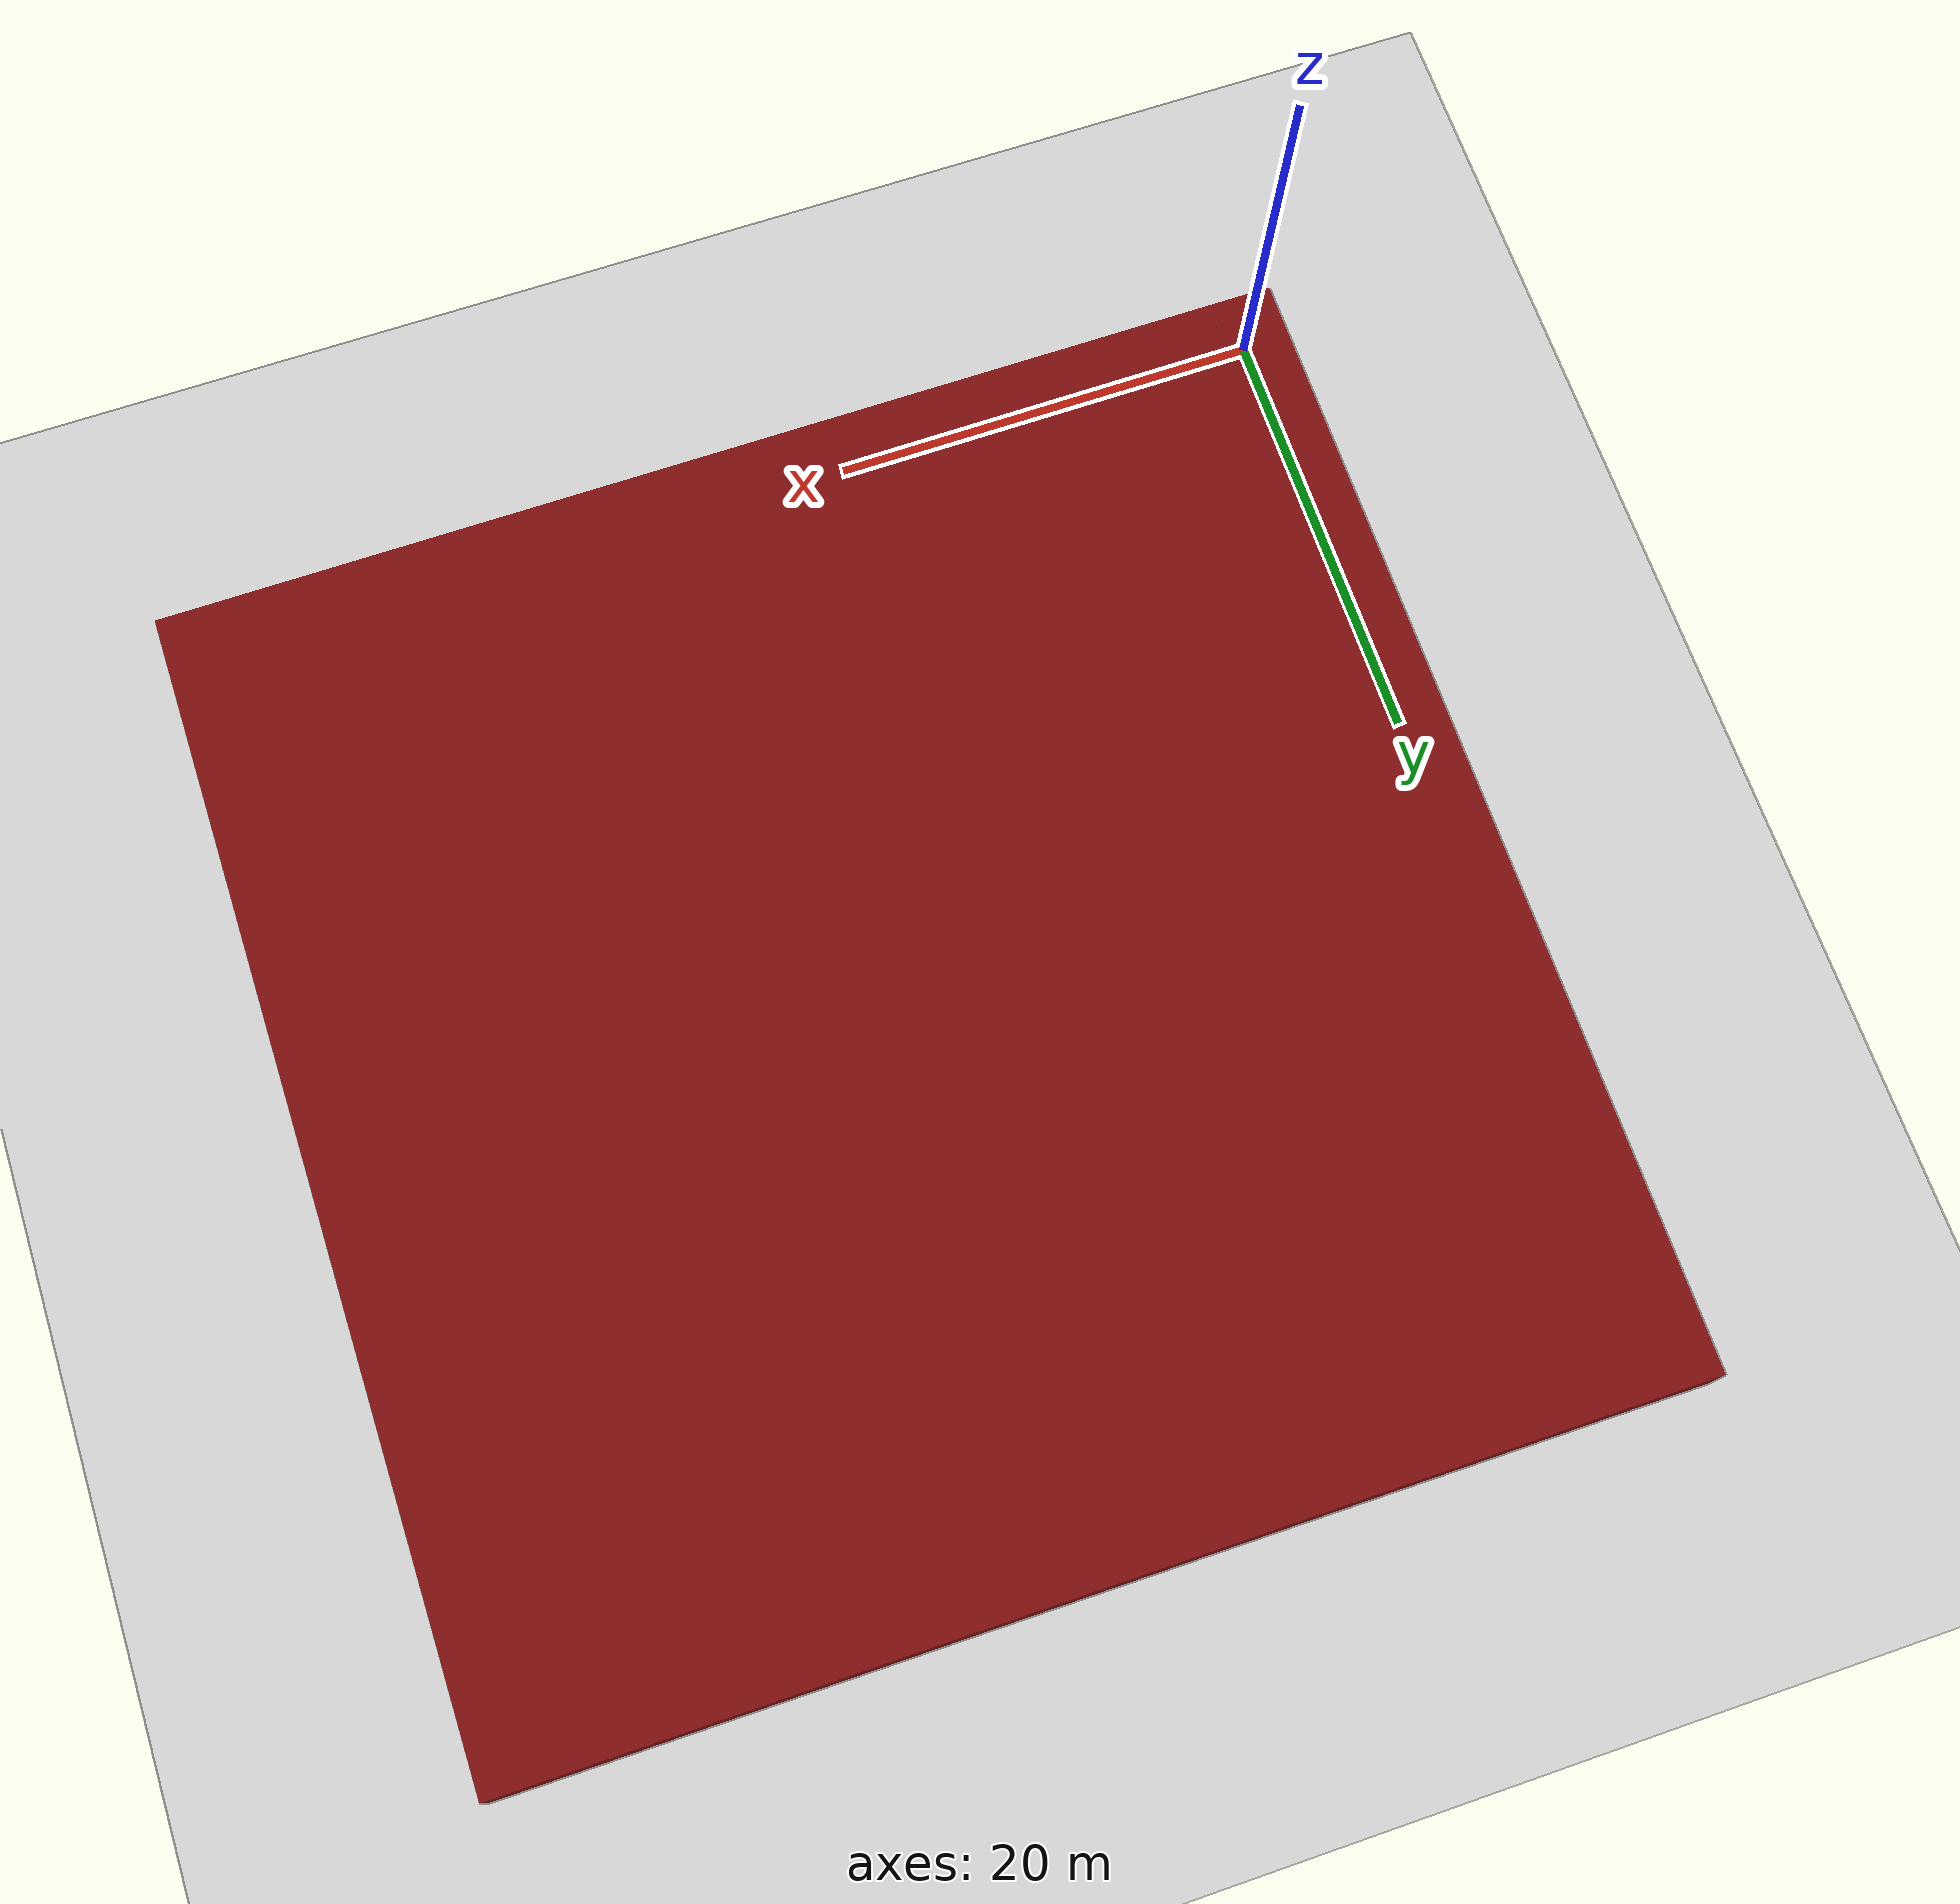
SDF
<?xml version='1.0'?>
        <sdf version='1.4'>
            <world name='1_wall'>
                <light name='sun' type='directional'>
                    <cast_shadows>1</cast_shadows>
                    <pose>0 0 10 0 -0 0</pose>
                    <diffuse>0.8 0.8 0.8 1</diffuse>
                    <specular>0.2 0.2 0.2 1</specular>
                    <attenuation>
                    <range>1000</range>
                    <constant>0.9</constant>
                    <linear>0.01</linear>
                    <quadratic>0.001</quadratic>
                    </attenuation>
                    <direction>-0.5 0.1 -0.9</direction>
                </light>
                <model name='ground_plane'>
                    <static>1</static>
                    <link name='link'>
                        <collision name='collision'>
                        <geometry>
                            <plane>
                                <normal>0 0 1</normal>
                                <size>1000 1000</size>
                            </plane>
                        </geometry>
                        <surface>
                            <friction>
                                <ode>
                                    <mu>100</mu>
                                    <mu2>50</mu2>
                                </ode>
                            </friction>
                            <bounce/>
                                <contact>
                                    <ode/>
                                </contact>
                        </surface>
                        <max_contacts>10</max_contacts>
                        </collision>
                    <visual name='visual'>
                        <cast_shadows>0</cast_shadows>
                        <geometry>
                            <plane>
                                <normal>0 0 1</normal>
                                <size>10000 10000</size>
                            </plane>
                            </geometry>
                                <material>
                                <script>
                                        <uri>file://media/materials/scripts/gazebo.material</uri>
                                        <name>Gazebo/Grey</name>
                                        </script>
                                    </material>
                    </visual>
                    <velocity_decay>
                        <linear>0</linear>
                        <angular>0</angular>
                    </velocity_decay>
                    <self_collide>0</self_collide>
                        <kinematic>0</kinematic>
                        <gravity>1</gravity>
                    </link>
                </model>
                <physics type='ode'>
                    <max_step_size>0.01</max_step_size>
                    <real_time_factor>1</real_time_factor>
                    <real_time_update_rate>100</real_time_update_rate>
                    <gravity>0 0 -9.8</gravity>
                </physics>
            <scene>
                <ambient>0.4 0.4 0.4 1</ambient>
                <background>0.7 0.7 0.7 1</background>
                <shadows>1</shadows>
            </scene>
    <model name='Wall_0'>
     <static>1</static>
    <link name='Wall_0'>
    <collision name='Wall_Collision_0'>
        <geometry>
          <box>
            <size>53.65 0.05 2.5</size>
          </box>
        </geometry>
        <pose>0 0 1.25 0 -0 0</pose>
      </collision>
      <visual name='Wall_Visual_0'>
        <pose>0 0 1.25 0 -0 0</pose>
        <geometry>
          <box>
            <size>53.65 0.05 2.5</size>
          </box>
        </geometry>
        <material>
          <script>
            <uri>file://media/materials/scripts/gazebo.material</uri>
            <name>Gazebo/Red</name>
          </script>
        </material>
      </visual>
      <velocity_decay>
        <linear>0</linear>
        <angular>0</angular>
      </velocity_decay>
      <pose>-1.5 25.3 0 0 0 1.5707963267948966</pose>
    </link>
     </model><model name='Wall_1'>
     <static>1</static>
    <link name='Wall_1'>
    <collision name='Wall_Collision_1'>
        <geometry>
          <box>
            <size>53.65 0.05 2.5</size>
          </box>
        </geometry>
        <pose>0 0 1.25 0 -0 0</pose>
      </collision>
      <visual name='Wall_Visual_1'>
        <pose>0 0 1.25 0 -0 0</pose>
        <geometry>
          <box>
            <size>53.65 0.05 2.5</size>
          </box>
        </geometry>
        <material>
          <script>
            <uri>file://media/materials/scripts/gazebo.material</uri>
            <name>Gazebo/Red</name>
          </script>
        </material>
      </visual>
      <velocity_decay>
        <linear>0</linear>
        <angular>0</angular>
      </velocity_decay>
      <pose>-1.45 25.3 0 0 0 1.5707963267948966</pose>
    </link>
     </model><model name='Wall_2'>
     <static>1</static>
    <link name='Wall_2'>
    <collision name='Wall_Collision_2'>
        <geometry>
          <box>
            <size>53.65 0.05 2.5</size>
          </box>
        </geometry>
        <pose>0 0 1.25 0 -0 0</pose>
      </collision>
      <visual name='Wall_Visual_2'>
        <pose>0 0 1.25 0 -0 0</pose>
        <geometry>
          <box>
            <size>53.65 0.05 2.5</size>
          </box>
        </geometry>
        <material>
          <script>
            <uri>file://media/materials/scripts/gazebo.material</uri>
            <name>Gazebo/Red</name>
          </script>
        </material>
      </visual>
      <velocity_decay>
        <linear>0</linear>
        <angular>0</angular>
      </velocity_decay>
      <pose>-1.4 25.3 0 0 0 1.5707963267948966</pose>
    </link>
     </model><model name='Wall_3'>
     <static>1</static>
    <link name='Wall_3'>
    <collision name='Wall_Collision_3'>
        <geometry>
          <box>
            <size>53.65 0.05 2.5</size>
          </box>
        </geometry>
        <pose>0 0 1.25 0 -0 0</pose>
      </collision>
      <visual name='Wall_Visual_3'>
        <pose>0 0 1.25 0 -0 0</pose>
        <geometry>
          <box>
            <size>53.65 0.05 2.5</size>
          </box>
        </geometry>
        <material>
          <script>
            <uri>file://media/materials/scripts/gazebo.material</uri>
            <name>Gazebo/Red</name>
          </script>
        </material>
      </visual>
      <velocity_decay>
        <linear>0</linear>
        <angular>0</angular>
      </velocity_decay>
      <pose>-1.35 25.3 0 0 0 1.5707963267948966</pose>
    </link>
     </model><model name='Wall_4'>
     <static>1</static>
    <link name='Wall_4'>
    <collision name='Wall_Collision_4'>
        <geometry>
          <box>
            <size>53.65 0.05 2.5</size>
          </box>
        </geometry>
        <pose>0 0 1.25 0 -0 0</pose>
      </collision>
      <visual name='Wall_Visual_4'>
        <pose>0 0 1.25 0 -0 0</pose>
        <geometry>
          <box>
            <size>53.65 0.05 2.5</size>
          </box>
        </geometry>
        <material>
          <script>
            <uri>file://media/materials/scripts/gazebo.material</uri>
            <name>Gazebo/Red</name>
          </script>
        </material>
      </visual>
      <velocity_decay>
        <linear>0</linear>
        <angular>0</angular>
      </velocity_decay>
      <pose>-1.3 25.3 0 0 0 1.5707963267948966</pose>
    </link>
     </model><model name='Wall_5'>
     <static>1</static>
    <link name='Wall_5'>
    <collision name='Wall_Collision_5'>
        <geometry>
          <box>
            <size>53.65 0.05 2.5</size>
          </box>
        </geometry>
        <pose>0 0 1.25 0 -0 0</pose>
      </collision>
      <visual name='Wall_Visual_5'>
        <pose>0 0 1.25 0 -0 0</pose>
        <geometry>
          <box>
            <size>53.65 0.05 2.5</size>
          </box>
        </geometry>
        <material>
          <script>
            <uri>file://media/materials/scripts/gazebo.material</uri>
            <name>Gazebo/Red</name>
          </script>
        </material>
      </visual>
      <velocity_decay>
        <linear>0</linear>
        <angular>0</angular>
      </velocity_decay>
      <pose>-1.25 25.3 0 0 0 1.5707963267948966</pose>
    </link>
     </model><model name='Wall_6'>
     <static>1</static>
    <link name='Wall_6'>
    <collision name='Wall_Collision_6'>
        <geometry>
          <box>
            <size>53.65 0.05 2.5</size>
          </box>
        </geometry>
        <pose>0 0 1.25 0 -0 0</pose>
      </collision>
      <visual name='Wall_Visual_6'>
        <pose>0 0 1.25 0 -0 0</pose>
        <geometry>
          <box>
            <size>53.65 0.05 2.5</size>
          </box>
        </geometry>
        <material>
          <script>
            <uri>file://media/materials/scripts/gazebo.material</uri>
            <name>Gazebo/Red</name>
          </script>
        </material>
      </visual>
      <velocity_decay>
        <linear>0</linear>
        <angular>0</angular>
      </velocity_decay>
      <pose>-1.2 25.3 0 0 0 1.5707963267948966</pose>
    </link>
     </model><model name='Wall_7'>
     <static>1</static>
    <link name='Wall_7'>
    <collision name='Wall_Collision_7'>
        <geometry>
          <box>
            <size>53.65 0.05 2.5</size>
          </box>
        </geometry>
        <pose>0 0 1.25 0 -0 0</pose>
      </collision>
      <visual name='Wall_Visual_7'>
        <pose>0 0 1.25 0 -0 0</pose>
        <geometry>
          <box>
            <size>53.65 0.05 2.5</size>
          </box>
        </geometry>
        <material>
          <script>
            <uri>file://media/materials/scripts/gazebo.material</uri>
            <name>Gazebo/Red</name>
          </script>
        </material>
      </visual>
      <velocity_decay>
        <linear>0</linear>
        <angular>0</angular>
      </velocity_decay>
      <pose>-1.15 25.3 0 0 0 1.5707963267948966</pose>
    </link>
     </model><model name='Wall_8'>
     <static>1</static>
    <link name='Wall_8'>
    <collision name='Wall_Collision_8'>
        <geometry>
          <box>
            <size>53.65 0.05 2.5</size>
          </box>
        </geometry>
        <pose>0 0 1.25 0 -0 0</pose>
      </collision>
      <visual name='Wall_Visual_8'>
        <pose>0 0 1.25 0 -0 0</pose>
        <geometry>
          <box>
            <size>53.65 0.05 2.5</size>
          </box>
        </geometry>
        <material>
          <script>
            <uri>file://media/materials/scripts/gazebo.material</uri>
            <name>Gazebo/Red</name>
          </script>
        </material>
      </visual>
      <velocity_decay>
        <linear>0</linear>
        <angular>0</angular>
      </velocity_decay>
      <pose>-1.1 25.3 0 0 0 1.5707963267948966</pose>
    </link>
     </model><model name='Wall_9'>
     <static>1</static>
    <link name='Wall_9'>
    <collision name='Wall_Collision_9'>
        <geometry>
          <box>
            <size>53.65 0.05 2.5</size>
          </box>
        </geometry>
        <pose>0 0 1.25 0 -0 0</pose>
      </collision>
      <visual name='Wall_Visual_9'>
        <pose>0 0 1.25 0 -0 0</pose>
        <geometry>
          <box>
            <size>53.65 0.05 2.5</size>
          </box>
        </geometry>
        <material>
          <script>
            <uri>file://media/materials/scripts/gazebo.material</uri>
            <name>Gazebo/Red</name>
          </script>
        </material>
      </visual>
      <velocity_decay>
        <linear>0</linear>
        <angular>0</angular>
      </velocity_decay>
      <pose>-1.05 25.3 0 0 0 1.5707963267948966</pose>
    </link>
     </model><model name='Wall_10'>
     <static>1</static>
    <link name='Wall_10'>
    <collision name='Wall_Collision_10'>
        <geometry>
          <box>
            <size>53.65 0.05 2.5</size>
          </box>
        </geometry>
        <pose>0 0 1.25 0 -0 0</pose>
      </collision>
      <visual name='Wall_Visual_10'>
        <pose>0 0 1.25 0 -0 0</pose>
        <geometry>
          <box>
            <size>53.65 0.05 2.5</size>
          </box>
        </geometry>
        <material>
          <script>
            <uri>file://media/materials/scripts/gazebo.material</uri>
            <name>Gazebo/Red</name>
          </script>
        </material>
      </visual>
      <velocity_decay>
        <linear>0</linear>
        <angular>0</angular>
      </velocity_decay>
      <pose>-1.0 25.3 0 0 0 1.5707963267948966</pose>
    </link>
     </model><model name='Wall_11'>
     <static>1</static>
    <link name='Wall_11'>
    <collision name='Wall_Collision_11'>
        <geometry>
          <box>
            <size>53.65 0.05 2.5</size>
          </box>
        </geometry>
        <pose>0 0 1.25 0 -0 0</pose>
      </collision>
      <visual name='Wall_Visual_11'>
        <pose>0 0 1.25 0 -0 0</pose>
        <geometry>
          <box>
            <size>53.65 0.05 2.5</size>
          </box>
        </geometry>
        <material>
          <script>
            <uri>file://media/materials/scripts/gazebo.material</uri>
            <name>Gazebo/Red</name>
          </script>
        </material>
      </visual>
      <velocity_decay>
        <linear>0</linear>
        <angular>0</angular>
      </velocity_decay>
      <pose>-0.95 25.3 0 0 0 1.5707963267948966</pose>
    </link>
     </model><model name='Wall_12'>
     <static>1</static>
    <link name='Wall_12'>
    <collision name='Wall_Collision_12'>
        <geometry>
          <box>
            <size>53.65 0.05 2.5</size>
          </box>
        </geometry>
        <pose>0 0 1.25 0 -0 0</pose>
      </collision>
      <visual name='Wall_Visual_12'>
        <pose>0 0 1.25 0 -0 0</pose>
        <geometry>
          <box>
            <size>53.65 0.05 2.5</size>
          </box>
        </geometry>
        <material>
          <script>
            <uri>file://media/materials/scripts/gazebo.material</uri>
            <name>Gazebo/Red</name>
          </script>
        </material>
      </visual>
      <velocity_decay>
        <linear>0</linear>
        <angular>0</angular>
      </velocity_decay>
      <pose>-0.9 25.3 0 0 0 1.5707963267948966</pose>
    </link>
     </model><model name='Wall_13'>
     <static>1</static>
    <link name='Wall_13'>
    <collision name='Wall_Collision_13'>
        <geometry>
          <box>
            <size>53.65 0.05 2.5</size>
          </box>
        </geometry>
        <pose>0 0 1.25 0 -0 0</pose>
      </collision>
      <visual name='Wall_Visual_13'>
        <pose>0 0 1.25 0 -0 0</pose>
        <geometry>
          <box>
            <size>53.65 0.05 2.5</size>
          </box>
        </geometry>
        <material>
          <script>
            <uri>file://media/materials/scripts/gazebo.material</uri>
            <name>Gazebo/Red</name>
          </script>
        </material>
      </visual>
      <velocity_decay>
        <linear>0</linear>
        <angular>0</angular>
      </velocity_decay>
      <pose>-0.85 25.3 0 0 0 1.5707963267948966</pose>
    </link>
     </model><model name='Wall_14'>
     <static>1</static>
    <link name='Wall_14'>
    <collision name='Wall_Collision_14'>
        <geometry>
          <box>
            <size>53.65 0.05 2.5</size>
          </box>
        </geometry>
        <pose>0 0 1.25 0 -0 0</pose>
      </collision>
      <visual name='Wall_Visual_14'>
        <pose>0 0 1.25 0 -0 0</pose>
        <geometry>
          <box>
            <size>53.65 0.05 2.5</size>
          </box>
        </geometry>
        <material>
          <script>
            <uri>file://media/materials/scripts/gazebo.material</uri>
            <name>Gazebo/Red</name>
          </script>
        </material>
      </visual>
      <velocity_decay>
        <linear>0</linear>
        <angular>0</angular>
      </velocity_decay>
      <pose>-0.8 25.3 0 0 0 1.5707963267948966</pose>
    </link>
     </model><model name='Wall_15'>
     <static>1</static>
    <link name='Wall_15'>
    <collision name='Wall_Collision_15'>
        <geometry>
          <box>
            <size>53.65 0.05 2.5</size>
          </box>
        </geometry>
        <pose>0 0 1.25 0 -0 0</pose>
      </collision>
      <visual name='Wall_Visual_15'>
        <pose>0 0 1.25 0 -0 0</pose>
        <geometry>
          <box>
            <size>53.65 0.05 2.5</size>
          </box>
        </geometry>
        <material>
          <script>
            <uri>file://media/materials/scripts/gazebo.material</uri>
            <name>Gazebo/Red</name>
          </script>
        </material>
      </visual>
      <velocity_decay>
        <linear>0</linear>
        <angular>0</angular>
      </velocity_decay>
      <pose>-0.75 25.3 0 0 0 1.5707963267948966</pose>
    </link>
     </model><model name='Wall_16'>
     <static>1</static>
    <link name='Wall_16'>
    <collision name='Wall_Collision_16'>
        <geometry>
          <box>
            <size>53.65 0.05 2.5</size>
          </box>
        </geometry>
        <pose>0 0 1.25 0 -0 0</pose>
      </collision>
      <visual name='Wall_Visual_16'>
        <pose>0 0 1.25 0 -0 0</pose>
        <geometry>
          <box>
            <size>53.65 0.05 2.5</size>
          </box>
        </geometry>
        <material>
          <script>
            <uri>file://media/materials/scripts/gazebo.material</uri>
            <name>Gazebo/Red</name>
          </script>
        </material>
      </visual>
      <velocity_decay>
        <linear>0</linear>
        <angular>0</angular>
      </velocity_decay>
      <pose>-0.7 25.3 0 0 0 1.5707963267948966</pose>
    </link>
     </model><model name='Wall_17'>
     <static>1</static>
    <link name='Wall_17'>
    <collision name='Wall_Collision_17'>
        <geometry>
          <box>
            <size>53.65 0.05 2.5</size>
          </box>
        </geometry>
        <pose>0 0 1.25 0 -0 0</pose>
      </collision>
      <visual name='Wall_Visual_17'>
        <pose>0 0 1.25 0 -0 0</pose>
        <geometry>
          <box>
            <size>53.65 0.05 2.5</size>
          </box>
        </geometry>
        <material>
          <script>
            <uri>file://media/materials/scripts/gazebo.material</uri>
            <name>Gazebo/Red</name>
          </script>
        </material>
      </visual>
      <velocity_decay>
        <linear>0</linear>
        <angular>0</angular>
      </velocity_decay>
      <pose>-0.65 25.3 0 0 0 1.5707963267948966</pose>
    </link>
     </model><model name='Wall_18'>
     <static>1</static>
    <link name='Wall_18'>
    <collision name='Wall_Collision_18'>
        <geometry>
          <box>
            <size>53.65 0.05 2.5</size>
          </box>
        </geometry>
        <pose>0 0 1.25 0 -0 0</pose>
      </collision>
      <visual name='Wall_Visual_18'>
        <pose>0 0 1.25 0 -0 0</pose>
        <geometry>
          <box>
            <size>53.65 0.05 2.5</size>
          </box>
        </geometry>
        <material>
          <script>
            <uri>file://media/materials/scripts/gazebo.material</uri>
            <name>Gazebo/Red</name>
          </script>
        </material>
      </visual>
      <velocity_decay>
        <linear>0</linear>
        <angular>0</angular>
      </velocity_decay>
      <pose>-0.6 25.3 0 0 0 1.5707963267948966</pose>
    </link>
     </model><model name='Wall_19'>
     <static>1</static>
    <link name='Wall_19'>
    <collision name='Wall_Collision_19'>
        <geometry>
          <box>
            <size>53.65 0.05 2.5</size>
          </box>
        </geometry>
        <pose>0 0 1.25 0 -0 0</pose>
      </collision>
      <visual name='Wall_Visual_19'>
        <pose>0 0 1.25 0 -0 0</pose>
        <geometry>
          <box>
            <size>53.65 0.05 2.5</size>
          </box>
        </geometry>
        <material>
          <script>
            <uri>file://media/materials/scripts/gazebo.material</uri>
            <name>Gazebo/Red</name>
          </script>
        </material>
      </visual>
      <velocity_decay>
        <linear>0</linear>
        <angular>0</angular>
      </velocity_decay>
      <pose>-0.55 25.3 0 0 0 1.5707963267948966</pose>
    </link>
     </model><model name='Wall_20'>
     <static>1</static>
    <link name='Wall_20'>
    <collision name='Wall_Collision_20'>
        <geometry>
          <box>
            <size>53.65 0.05 2.5</size>
          </box>
        </geometry>
        <pose>0 0 1.25 0 -0 0</pose>
      </collision>
      <visual name='Wall_Visual_20'>
        <pose>0 0 1.25 0 -0 0</pose>
        <geometry>
          <box>
            <size>53.65 0.05 2.5</size>
          </box>
        </geometry>
        <material>
          <script>
            <uri>file://media/materials/scripts/gazebo.material</uri>
            <name>Gazebo/Red</name>
          </script>
        </material>
      </visual>
      <velocity_decay>
        <linear>0</linear>
        <angular>0</angular>
      </velocity_decay>
      <pose>-0.5 25.3 0 0 0 1.5707963267948966</pose>
    </link>
     </model><model name='Wall_21'>
     <static>1</static>
    <link name='Wall_21'>
    <collision name='Wall_Collision_21'>
        <geometry>
          <box>
            <size>53.65 0.05 2.5</size>
          </box>
        </geometry>
        <pose>0 0 1.25 0 -0 0</pose>
      </collision>
      <visual name='Wall_Visual_21'>
        <pose>0 0 1.25 0 -0 0</pose>
        <geometry>
          <box>
            <size>53.65 0.05 2.5</size>
          </box>
        </geometry>
        <material>
          <script>
            <uri>file://media/materials/scripts/gazebo.material</uri>
            <name>Gazebo/Red</name>
          </script>
        </material>
      </visual>
      <velocity_decay>
        <linear>0</linear>
        <angular>0</angular>
      </velocity_decay>
      <pose>-0.45 25.3 0 0 0 1.5707963267948966</pose>
    </link>
     </model><model name='Wall_22'>
     <static>1</static>
    <link name='Wall_22'>
    <collision name='Wall_Collision_22'>
        <geometry>
          <box>
            <size>53.65 0.05 2.5</size>
          </box>
        </geometry>
        <pose>0 0 1.25 0 -0 0</pose>
      </collision>
      <visual name='Wall_Visual_22'>
        <pose>0 0 1.25 0 -0 0</pose>
        <geometry>
          <box>
            <size>53.65 0.05 2.5</size>
          </box>
        </geometry>
        <material>
          <script>
            <uri>file://media/materials/scripts/gazebo.material</uri>
            <name>Gazebo/Red</name>
          </script>
        </material>
      </visual>
      <velocity_decay>
        <linear>0</linear>
        <angular>0</angular>
      </velocity_decay>
      <pose>-0.4 25.3 0 0 0 1.5707963267948966</pose>
    </link>
     </model><model name='Wall_23'>
     <static>1</static>
    <link name='Wall_23'>
    <collision name='Wall_Collision_23'>
        <geometry>
          <box>
            <size>53.65 0.05 2.5</size>
          </box>
        </geometry>
        <pose>0 0 1.25 0 -0 0</pose>
      </collision>
      <visual name='Wall_Visual_23'>
        <pose>0 0 1.25 0 -0 0</pose>
        <geometry>
          <box>
            <size>53.65 0.05 2.5</size>
          </box>
        </geometry>
        <material>
          <script>
            <uri>file://media/materials/scripts/gazebo.material</uri>
            <name>Gazebo/Red</name>
          </script>
        </material>
      </visual>
      <velocity_decay>
        <linear>0</linear>
        <angular>0</angular>
      </velocity_decay>
      <pose>-0.35 25.3 0 0 0 1.5707963267948966</pose>
    </link>
     </model><model name='Wall_24'>
     <static>1</static>
    <link name='Wall_24'>
    <collision name='Wall_Collision_24'>
        <geometry>
          <box>
            <size>53.65 0.05 2.5</size>
          </box>
        </geometry>
        <pose>0 0 1.25 0 -0 0</pose>
      </collision>
      <visual name='Wall_Visual_24'>
        <pose>0 0 1.25 0 -0 0</pose>
        <geometry>
          <box>
            <size>53.65 0.05 2.5</size>
          </box>
        </geometry>
        <material>
          <script>
            <uri>file://media/materials/scripts/gazebo.material</uri>
            <name>Gazebo/Red</name>
          </script>
        </material>
      </visual>
      <velocity_decay>
        <linear>0</linear>
        <angular>0</angular>
      </velocity_decay>
      <pose>-0.3 25.3 0 0 0 1.5707963267948966</pose>
    </link>
     </model><model name='Wall_25'>
     <static>1</static>
    <link name='Wall_25'>
    <collision name='Wall_Collision_25'>
        <geometry>
          <box>
            <size>53.65 0.05 2.5</size>
          </box>
        </geometry>
        <pose>0 0 1.25 0 -0 0</pose>
      </collision>
      <visual name='Wall_Visual_25'>
        <pose>0 0 1.25 0 -0 0</pose>
        <geometry>
          <box>
            <size>53.65 0.05 2.5</size>
          </box>
        </geometry>
        <material>
          <script>
            <uri>file://media/materials/scripts/gazebo.material</uri>
            <name>Gazebo/Red</name>
          </script>
        </material>
      </visual>
      <velocity_decay>
        <linear>0</linear>
        <angular>0</angular>
      </velocity_decay>
      <pose>-0.25 25.3 0 0 0 1.5707963267948966</pose>
    </link>
     </model><model name='Wall_26'>
     <static>1</static>
    <link name='Wall_26'>
    <collision name='Wall_Collision_26'>
        <geometry>
          <box>
            <size>53.65 0.05 2.5</size>
          </box>
        </geometry>
        <pose>0 0 1.25 0 -0 0</pose>
      </collision>
      <visual name='Wall_Visual_26'>
        <pose>0 0 1.25 0 -0 0</pose>
        <geometry>
          <box>
            <size>53.65 0.05 2.5</size>
          </box>
        </geometry>
        <material>
          <script>
            <uri>file://media/materials/scripts/gazebo.material</uri>
            <name>Gazebo/Red</name>
          </script>
        </material>
      </visual>
      <velocity_decay>
        <linear>0</linear>
        <angular>0</angular>
      </velocity_decay>
      <pose>-0.2 25.3 0 0 0 1.5707963267948966</pose>
    </link>
     </model><model name='Wall_27'>
     <static>1</static>
    <link name='Wall_27'>
    <collision name='Wall_Collision_27'>
        <geometry>
          <box>
            <size>53.65 0.05 2.5</size>
          </box>
        </geometry>
        <pose>0 0 1.25 0 -0 0</pose>
      </collision>
      <visual name='Wall_Visual_27'>
        <pose>0 0 1.25 0 -0 0</pose>
        <geometry>
          <box>
            <size>53.65 0.05 2.5</size>
          </box>
        </geometry>
        <material>
          <script>
            <uri>file://media/materials/scripts/gazebo.material</uri>
            <name>Gazebo/Red</name>
          </script>
        </material>
      </visual>
      <velocity_decay>
        <linear>0</linear>
        <angular>0</angular>
      </velocity_decay>
      <pose>-0.15 25.3 0 0 0 1.5707963267948966</pose>
    </link>
     </model><model name='Wall_28'>
     <static>1</static>
    <link name='Wall_28'>
    <collision name='Wall_Collision_28'>
        <geometry>
          <box>
            <size>53.65 0.05 2.5</size>
          </box>
        </geometry>
        <pose>0 0 1.25 0 -0 0</pose>
      </collision>
      <visual name='Wall_Visual_28'>
        <pose>0 0 1.25 0 -0 0</pose>
        <geometry>
          <box>
            <size>53.65 0.05 2.5</size>
          </box>
        </geometry>
        <material>
          <script>
            <uri>file://media/materials/scripts/gazebo.material</uri>
            <name>Gazebo/Red</name>
          </script>
        </material>
      </visual>
      <velocity_decay>
        <linear>0</linear>
        <angular>0</angular>
      </velocity_decay>
      <pose>-0.1 25.3 0 0 0 1.5707963267948966</pose>
    </link>
     </model><model name='Wall_29'>
     <static>1</static>
    <link name='Wall_29'>
    <collision name='Wall_Collision_29'>
        <geometry>
          <box>
            <size>53.65 0.05 2.5</size>
          </box>
        </geometry>
        <pose>0 0 1.25 0 -0 0</pose>
      </collision>
      <visual name='Wall_Visual_29'>
        <pose>0 0 1.25 0 -0 0</pose>
        <geometry>
          <box>
            <size>53.65 0.05 2.5</size>
          </box>
        </geometry>
        <material>
          <script>
            <uri>file://media/materials/scripts/gazebo.material</uri>
            <name>Gazebo/Red</name>
          </script>
        </material>
      </visual>
      <velocity_decay>
        <linear>0</linear>
        <angular>0</angular>
      </velocity_decay>
      <pose>-0.05 25.3 0 0 0 1.5707963267948966</pose>
    </link>
     </model><model name='Wall_30'>
     <static>1</static>
    <link name='Wall_30'>
    <collision name='Wall_Collision_30'>
        <geometry>
          <box>
            <size>53.65 0.05 2.5</size>
          </box>
        </geometry>
        <pose>0 0 1.25 0 -0 0</pose>
      </collision>
      <visual name='Wall_Visual_30'>
        <pose>0 0 1.25 0 -0 0</pose>
        <geometry>
          <box>
            <size>53.65 0.05 2.5</size>
          </box>
        </geometry>
        <material>
          <script>
            <uri>file://media/materials/scripts/gazebo.material</uri>
            <name>Gazebo/Red</name>
          </script>
        </material>
      </visual>
      <velocity_decay>
        <linear>0</linear>
        <angular>0</angular>
      </velocity_decay>
      <pose>9.02056207508e-17 25.3 0 0 0 1.5707963267948966</pose>
    </link>
     </model><model name='Wall_31'>
     <static>1</static>
    <link name='Wall_31'>
    <collision name='Wall_Collision_31'>
        <geometry>
          <box>
            <size>53.65 0.05 2.5</size>
          </box>
        </geometry>
        <pose>0 0 1.25 0 -0 0</pose>
      </collision>
      <visual name='Wall_Visual_31'>
        <pose>0 0 1.25 0 -0 0</pose>
        <geometry>
          <box>
            <size>53.65 0.05 2.5</size>
          </box>
        </geometry>
        <material>
          <script>
            <uri>file://media/materials/scripts/gazebo.material</uri>
            <name>Gazebo/Red</name>
          </script>
        </material>
      </visual>
      <velocity_decay>
        <linear>0</linear>
        <angular>0</angular>
      </velocity_decay>
      <pose>0.05 25.3 0 0 0 1.5707963267948966</pose>
    </link>
     </model><model name='Wall_32'>
     <static>1</static>
    <link name='Wall_32'>
    <collision name='Wall_Collision_32'>
        <geometry>
          <box>
            <size>53.65 0.05 2.5</size>
          </box>
        </geometry>
        <pose>0 0 1.25 0 -0 0</pose>
      </collision>
      <visual name='Wall_Visual_32'>
        <pose>0 0 1.25 0 -0 0</pose>
        <geometry>
          <box>
            <size>53.65 0.05 2.5</size>
          </box>
        </geometry>
        <material>
          <script>
            <uri>file://media/materials/scripts/gazebo.material</uri>
            <name>Gazebo/Red</name>
          </script>
        </material>
      </visual>
      <velocity_decay>
        <linear>0</linear>
        <angular>0</angular>
      </velocity_decay>
      <pose>0.1 25.3 0 0 0 1.5707963267948966</pose>
    </link>
     </model><model name='Wall_33'>
     <static>1</static>
    <link name='Wall_33'>
    <collision name='Wall_Collision_33'>
        <geometry>
          <box>
            <size>53.65 0.05 2.5</size>
          </box>
        </geometry>
        <pose>0 0 1.25 0 -0 0</pose>
      </collision>
      <visual name='Wall_Visual_33'>
        <pose>0 0 1.25 0 -0 0</pose>
        <geometry>
          <box>
            <size>53.65 0.05 2.5</size>
          </box>
        </geometry>
        <material>
          <script>
            <uri>file://media/materials/scripts/gazebo.material</uri>
            <name>Gazebo/Red</name>
          </script>
        </material>
      </visual>
      <velocity_decay>
        <linear>0</linear>
        <angular>0</angular>
      </velocity_decay>
      <pose>0.15 25.3 0 0 0 1.5707963267948966</pose>
    </link>
     </model><model name='Wall_34'>
     <static>1</static>
    <link name='Wall_34'>
    <collision name='Wall_Collision_34'>
        <geometry>
          <box>
            <size>53.65 0.05 2.5</size>
          </box>
        </geometry>
        <pose>0 0 1.25 0 -0 0</pose>
      </collision>
      <visual name='Wall_Visual_34'>
        <pose>0 0 1.25 0 -0 0</pose>
        <geometry>
          <box>
            <size>53.65 0.05 2.5</size>
          </box>
        </geometry>
        <material>
          <script>
            <uri>file://media/materials/scripts/gazebo.material</uri>
            <name>Gazebo/Red</name>
          </script>
        </material>
      </visual>
      <velocity_decay>
        <linear>0</linear>
        <angular>0</angular>
      </velocity_decay>
      <pose>0.2 25.3 0 0 0 1.5707963267948966</pose>
    </link>
     </model><model name='Wall_35'>
     <static>1</static>
    <link name='Wall_35'>
    <collision name='Wall_Collision_35'>
        <geometry>
          <box>
            <size>53.65 0.05 2.5</size>
          </box>
        </geometry>
        <pose>0 0 1.25 0 -0 0</pose>
      </collision>
      <visual name='Wall_Visual_35'>
        <pose>0 0 1.25 0 -0 0</pose>
        <geometry>
          <box>
            <size>53.65 0.05 2.5</size>
          </box>
        </geometry>
        <material>
          <script>
            <uri>file://media/materials/scripts/gazebo.material</uri>
            <name>Gazebo/Red</name>
          </script>
        </material>
      </visual>
      <velocity_decay>
        <linear>0</linear>
        <angular>0</angular>
      </velocity_decay>
      <pose>0.25 25.3 0 0 0 1.5707963267948966</pose>
    </link>
     </model><model name='Wall_36'>
     <static>1</static>
    <link name='Wall_36'>
    <collision name='Wall_Collision_36'>
        <geometry>
          <box>
            <size>53.65 0.05 2.5</size>
          </box>
        </geometry>
        <pose>0 0 1.25 0 -0 0</pose>
      </collision>
      <visual name='Wall_Visual_36'>
        <pose>0 0 1.25 0 -0 0</pose>
        <geometry>
          <box>
            <size>53.65 0.05 2.5</size>
          </box>
        </geometry>
        <material>
          <script>
            <uri>file://media/materials/scripts/gazebo.material</uri>
            <name>Gazebo/Red</name>
          </script>
        </material>
      </visual>
      <velocity_decay>
        <linear>0</linear>
        <angular>0</angular>
      </velocity_decay>
      <pose>0.3 25.3 0 0 0 1.5707963267948966</pose>
    </link>
     </model><model name='Wall_37'>
     <static>1</static>
    <link name='Wall_37'>
    <collision name='Wall_Collision_37'>
        <geometry>
          <box>
            <size>53.65 0.05 2.5</size>
          </box>
        </geometry>
        <pose>0 0 1.25 0 -0 0</pose>
      </collision>
      <visual name='Wall_Visual_37'>
        <pose>0 0 1.25 0 -0 0</pose>
        <geometry>
          <box>
            <size>53.65 0.05 2.5</size>
          </box>
        </geometry>
        <material>
          <script>
            <uri>file://media/materials/scripts/gazebo.material</uri>
            <name>Gazebo/Red</name>
          </script>
        </material>
      </visual>
      <velocity_decay>
        <linear>0</linear>
        <angular>0</angular>
      </velocity_decay>
      <pose>0.35 25.3 0 0 0 1.5707963267948966</pose>
    </link>
     </model><model name='Wall_38'>
     <static>1</static>
    <link name='Wall_38'>
    <collision name='Wall_Collision_38'>
        <geometry>
          <box>
            <size>53.65 0.05 2.5</size>
          </box>
        </geometry>
        <pose>0 0 1.25 0 -0 0</pose>
      </collision>
      <visual name='Wall_Visual_38'>
        <pose>0 0 1.25 0 -0 0</pose>
        <geometry>
          <box>
            <size>53.65 0.05 2.5</size>
          </box>
        </geometry>
        <material>
          <script>
            <uri>file://media/materials/scripts/gazebo.material</uri>
            <name>Gazebo/Red</name>
          </script>
        </material>
      </visual>
      <velocity_decay>
        <linear>0</linear>
        <angular>0</angular>
      </velocity_decay>
      <pose>0.4 25.3 0 0 0 1.5707963267948966</pose>
    </link>
     </model><model name='Wall_39'>
     <static>1</static>
    <link name='Wall_39'>
    <collision name='Wall_Collision_39'>
        <geometry>
          <box>
            <size>53.65 0.05 2.5</size>
          </box>
        </geometry>
        <pose>0 0 1.25 0 -0 0</pose>
      </collision>
      <visual name='Wall_Visual_39'>
        <pose>0 0 1.25 0 -0 0</pose>
        <geometry>
          <box>
            <size>53.65 0.05 2.5</size>
          </box>
        </geometry>
        <material>
          <script>
            <uri>file://media/materials/scripts/gazebo.material</uri>
            <name>Gazebo/Red</name>
          </script>
        </material>
      </visual>
      <velocity_decay>
        <linear>0</linear>
        <angular>0</angular>
      </velocity_decay>
      <pose>0.45 25.3 0 0 0 1.5707963267948966</pose>
    </link>
     </model><model name='Wall_40'>
     <static>1</static>
    <link name='Wall_40'>
    <collision name='Wall_Collision_40'>
        <geometry>
          <box>
            <size>53.65 0.05 2.5</size>
          </box>
        </geometry>
        <pose>0 0 1.25 0 -0 0</pose>
      </collision>
      <visual name='Wall_Visual_40'>
        <pose>0 0 1.25 0 -0 0</pose>
        <geometry>
          <box>
            <size>53.65 0.05 2.5</size>
          </box>
        </geometry>
        <material>
          <script>
            <uri>file://media/materials/scripts/gazebo.material</uri>
            <name>Gazebo/Red</name>
          </script>
        </material>
      </visual>
      <velocity_decay>
        <linear>0</linear>
        <angular>0</angular>
      </velocity_decay>
      <pose>0.5 25.3 0 0 0 1.5707963267948966</pose>
    </link>
     </model><model name='Wall_41'>
     <static>1</static>
    <link name='Wall_41'>
    <collision name='Wall_Collision_41'>
        <geometry>
          <box>
            <size>53.65 0.05 2.5</size>
          </box>
        </geometry>
        <pose>0 0 1.25 0 -0 0</pose>
      </collision>
      <visual name='Wall_Visual_41'>
        <pose>0 0 1.25 0 -0 0</pose>
        <geometry>
          <box>
            <size>53.65 0.05 2.5</size>
          </box>
        </geometry>
        <material>
          <script>
            <uri>file://media/materials/scripts/gazebo.material</uri>
            <name>Gazebo/Red</name>
          </script>
        </material>
      </visual>
      <velocity_decay>
        <linear>0</linear>
        <angular>0</angular>
      </velocity_decay>
      <pose>0.55 25.3 0 0 0 1.5707963267948966</pose>
    </link>
     </model><model name='Wall_42'>
     <static>1</static>
    <link name='Wall_42'>
    <collision name='Wall_Collision_42'>
        <geometry>
          <box>
            <size>53.65 0.05 2.5</size>
          </box>
        </geometry>
        <pose>0 0 1.25 0 -0 0</pose>
      </collision>
      <visual name='Wall_Visual_42'>
        <pose>0 0 1.25 0 -0 0</pose>
        <geometry>
          <box>
            <size>53.65 0.05 2.5</size>
          </box>
        </geometry>
        <material>
          <script>
            <uri>file://media/materials/scripts/gazebo.material</uri>
            <name>Gazebo/Red</name>
          </script>
        </material>
      </visual>
      <velocity_decay>
        <linear>0</linear>
        <angular>0</angular>
      </velocity_decay>
      <pose>0.6 25.3 0 0 0 1.5707963267948966</pose>
    </link>
     </model><model name='Wall_43'>
     <static>1</static>
    <link name='Wall_43'>
    <collision name='Wall_Collision_43'>
        <geometry>
          <box>
            <size>53.65 0.05 2.5</size>
          </box>
        </geometry>
        <pose>0 0 1.25 0 -0 0</pose>
      </collision>
      <visual name='Wall_Visual_43'>
        <pose>0 0 1.25 0 -0 0</pose>
        <geometry>
          <box>
            <size>53.65 0.05 2.5</size>
          </box>
        </geometry>
        <material>
          <script>
            <uri>file://media/materials/scripts/gazebo.material</uri>
            <name>Gazebo/Red</name>
          </script>
        </material>
      </visual>
      <velocity_decay>
        <linear>0</linear>
        <angular>0</angular>
      </velocity_decay>
      <pose>0.65 25.3 0 0 0 1.5707963267948966</pose>
    </link>
     </model><model name='Wall_44'>
     <static>1</static>
    <link name='Wall_44'>
    <collision name='Wall_Collision_44'>
        <geometry>
          <box>
            <size>53.65 0.05 2.5</size>
          </box>
        </geometry>
        <pose>0 0 1.25 0 -0 0</pose>
      </collision>
      <visual name='Wall_Visual_44'>
        <pose>0 0 1.25 0 -0 0</pose>
        <geometry>
          <box>
            <size>53.65 0.05 2.5</size>
          </box>
        </geometry>
        <material>
          <script>
            <uri>file://media/materials/scripts/gazebo.material</uri>
            <name>Gazebo/Red</name>
          </script>
        </material>
      </visual>
      <velocity_decay>
        <linear>0</linear>
        <angular>0</angular>
      </velocity_decay>
      <pose>0.7 25.3 0 0 0 1.5707963267948966</pose>
    </link>
     </model><model name='Wall_45'>
     <static>1</static>
    <link name='Wall_45'>
    <collision name='Wall_Collision_45'>
        <geometry>
          <box>
            <size>53.65 0.05 2.5</size>
          </box>
        </geometry>
        <pose>0 0 1.25 0 -0 0</pose>
      </collision>
      <visual name='Wall_Visual_45'>
        <pose>0 0 1.25 0 -0 0</pose>
        <geometry>
          <box>
            <size>53.65 0.05 2.5</size>
          </box>
        </geometry>
        <material>
          <script>
            <uri>file://media/materials/scripts/gazebo.material</uri>
            <name>Gazebo/Red</name>
          </script>
        </material>
      </visual>
      <velocity_decay>
        <linear>0</linear>
        <angular>0</angular>
      </velocity_decay>
      <pose>0.75 25.3 0 0 0 1.5707963267948966</pose>
    </link>
     </model><model name='Wall_46'>
     <static>1</static>
    <link name='Wall_46'>
    <collision name='Wall_Collision_46'>
        <geometry>
          <box>
            <size>53.65 0.05 2.5</size>
          </box>
        </geometry>
        <pose>0 0 1.25 0 -0 0</pose>
      </collision>
      <visual name='Wall_Visual_46'>
        <pose>0 0 1.25 0 -0 0</pose>
        <geometry>
          <box>
            <size>53.65 0.05 2.5</size>
          </box>
        </geometry>
        <material>
          <script>
            <uri>file://media/materials/scripts/gazebo.material</uri>
            <name>Gazebo/Red</name>
          </script>
        </material>
      </visual>
      <velocity_decay>
        <linear>0</linear>
        <angular>0</angular>
      </velocity_decay>
      <pose>0.8 25.3 0 0 0 1.5707963267948966</pose>
    </link>
     </model><model name='Wall_47'>
     <static>1</static>
    <link name='Wall_47'>
    <collision name='Wall_Collision_47'>
        <geometry>
          <box>
            <size>53.65 0.05 2.5</size>
          </box>
        </geometry>
        <pose>0 0 1.25 0 -0 0</pose>
      </collision>
      <visual name='Wall_Visual_47'>
        <pose>0 0 1.25 0 -0 0</pose>
        <geometry>
          <box>
            <size>53.65 0.05 2.5</size>
          </box>
        </geometry>
        <material>
          <script>
            <uri>file://media/materials/scripts/gazebo.material</uri>
            <name>Gazebo/Red</name>
          </script>
        </material>
      </visual>
      <velocity_decay>
        <linear>0</linear>
        <angular>0</angular>
      </velocity_decay>
      <pose>0.85 25.3 0 0 0 1.5707963267948966</pose>
    </link>
     </model><model name='Wall_48'>
     <static>1</static>
    <link name='Wall_48'>
    <collision name='Wall_Collision_48'>
        <geometry>
          <box>
            <size>53.65 0.05 2.5</size>
          </box>
        </geometry>
        <pose>0 0 1.25 0 -0 0</pose>
      </collision>
      <visual name='Wall_Visual_48'>
        <pose>0 0 1.25 0 -0 0</pose>
        <geometry>
          <box>
            <size>53.65 0.05 2.5</size>
          </box>
        </geometry>
        <material>
          <script>
            <uri>file://media/materials/scripts/gazebo.material</uri>
            <name>Gazebo/Red</name>
          </script>
        </material>
      </visual>
      <velocity_decay>
        <linear>0</linear>
        <angular>0</angular>
      </velocity_decay>
      <pose>0.9 25.3 0 0 0 1.5707963267948966</pose>
    </link>
     </model><model name='Wall_49'>
     <static>1</static>
    <link name='Wall_49'>
    <collision name='Wall_Collision_49'>
        <geometry>
          <box>
            <size>53.65 0.05 2.5</size>
          </box>
        </geometry>
        <pose>0 0 1.25 0 -0 0</pose>
      </collision>
      <visual name='Wall_Visual_49'>
        <pose>0 0 1.25 0 -0 0</pose>
        <geometry>
          <box>
            <size>53.65 0.05 2.5</size>
          </box>
        </geometry>
        <material>
          <script>
            <uri>file://media/materials/scripts/gazebo.material</uri>
            <name>Gazebo/Red</name>
          </script>
        </material>
      </visual>
      <velocity_decay>
        <linear>0</linear>
        <angular>0</angular>
      </velocity_decay>
      <pose>0.95 25.3 0 0 0 1.5707963267948966</pose>
    </link>
     </model><model name='Wall_50'>
     <static>1</static>
    <link name='Wall_50'>
    <collision name='Wall_Collision_50'>
        <geometry>
          <box>
            <size>53.65 0.05 2.5</size>
          </box>
        </geometry>
        <pose>0 0 1.25 0 -0 0</pose>
      </collision>
      <visual name='Wall_Visual_50'>
        <pose>0 0 1.25 0 -0 0</pose>
        <geometry>
          <box>
            <size>53.65 0.05 2.5</size>
          </box>
        </geometry>
        <material>
          <script>
            <uri>file://media/materials/scripts/gazebo.material</uri>
            <name>Gazebo/Red</name>
          </script>
        </material>
      </visual>
      <velocity_decay>
        <linear>0</linear>
        <angular>0</angular>
      </velocity_decay>
      <pose>1.0 25.3 0 0 0 1.5707963267948966</pose>
    </link>
     </model><model name='Wall_51'>
     <static>1</static>
    <link name='Wall_51'>
    <collision name='Wall_Collision_51'>
        <geometry>
          <box>
            <size>53.65 0.05 2.5</size>
          </box>
        </geometry>
        <pose>0 0 1.25 0 -0 0</pose>
      </collision>
      <visual name='Wall_Visual_51'>
        <pose>0 0 1.25 0 -0 0</pose>
        <geometry>
          <box>
            <size>53.65 0.05 2.5</size>
          </box>
        </geometry>
        <material>
          <script>
            <uri>file://media/materials/scripts/gazebo.material</uri>
            <name>Gazebo/Red</name>
          </script>
        </material>
      </visual>
      <velocity_decay>
        <linear>0</linear>
        <angular>0</angular>
      </velocity_decay>
      <pose>1.05 25.3 0 0 0 1.5707963267948966</pose>
    </link>
     </model><model name='Wall_52'>
     <static>1</static>
    <link name='Wall_52'>
    <collision name='Wall_Collision_52'>
        <geometry>
          <box>
            <size>53.65 0.05 2.5</size>
          </box>
        </geometry>
        <pose>0 0 1.25 0 -0 0</pose>
      </collision>
      <visual name='Wall_Visual_52'>
        <pose>0 0 1.25 0 -0 0</pose>
        <geometry>
          <box>
            <size>53.65 0.05 2.5</size>
          </box>
        </geometry>
        <material>
          <script>
            <uri>file://media/materials/scripts/gazebo.material</uri>
            <name>Gazebo/Red</name>
          </script>
        </material>
      </visual>
      <velocity_decay>
        <linear>0</linear>
        <angular>0</angular>
      </velocity_decay>
      <pose>1.1 25.3 0 0 0 1.5707963267948966</pose>
    </link>
     </model><model name='Wall_53'>
     <static>1</static>
    <link name='Wall_53'>
    <collision name='Wall_Collision_53'>
        <geometry>
          <box>
            <size>53.65 0.05 2.5</size>
          </box>
        </geometry>
        <pose>0 0 1.25 0 -0 0</pose>
      </collision>
      <visual name='Wall_Visual_53'>
        <pose>0 0 1.25 0 -0 0</pose>
        <geometry>
          <box>
            <size>53.65 0.05 2.5</size>
          </box>
        </geometry>
        <material>
          <script>
            <uri>file://media/materials/scripts/gazebo.material</uri>
            <name>Gazebo/Red</name>
          </script>
        </material>
      </visual>
      <velocity_decay>
        <linear>0</linear>
        <angular>0</angular>
      </velocity_decay>
      <pose>1.15 25.3 0 0 0 1.5707963267948966</pose>
    </link>
     </model><model name='Wall_54'>
     <static>1</static>
    <link name='Wall_54'>
    <collision name='Wall_Collision_54'>
        <geometry>
          <box>
            <size>53.65 0.05 2.5</size>
          </box>
        </geometry>
        <pose>0 0 1.25 0 -0 0</pose>
      </collision>
      <visual name='Wall_Visual_54'>
        <pose>0 0 1.25 0 -0 0</pose>
        <geometry>
          <box>
            <size>53.65 0.05 2.5</size>
          </box>
        </geometry>
        <material>
          <script>
            <uri>file://media/materials/scripts/gazebo.material</uri>
            <name>Gazebo/Red</name>
          </script>
        </material>
      </visual>
      <velocity_decay>
        <linear>0</linear>
        <angular>0</angular>
      </velocity_decay>
      <pose>1.2 25.3 0 0 0 1.5707963267948966</pose>
    </link>
     </model><model name='Wall_55'>
     <static>1</static>
    <link name='Wall_55'>
    <collision name='Wall_Collision_55'>
        <geometry>
          <box>
            <size>53.65 0.05 2.5</size>
          </box>
        </geometry>
        <pose>0 0 1.25 0 -0 0</pose>
      </collision>
      <visual name='Wall_Visual_55'>
        <pose>0 0 1.25 0 -0 0</pose>
        <geometry>
          <box>
            <size>53.65 0.05 2.5</size>
          </box>
        </geometry>
        <material>
          <script>
            <uri>file://media/materials/scripts/gazebo.material</uri>
            <name>Gazebo/Red</name>
          </script>
        </material>
      </visual>
      <velocity_decay>
        <linear>0</linear>
        <angular>0</angular>
      </velocity_decay>
      <pose>1.25 25.3 0 0 0 1.5707963267948966</pose>
    </link>
     </model><model name='Wall_56'>
     <static>1</static>
    <link name='Wall_56'>
    <collision name='Wall_Collision_56'>
        <geometry>
          <box>
            <size>53.65 0.05 2.5</size>
          </box>
        </geometry>
        <pose>0 0 1.25 0 -0 0</pose>
      </collision>
      <visual name='Wall_Visual_56'>
        <pose>0 0 1.25 0 -0 0</pose>
        <geometry>
          <box>
            <size>53.65 0.05 2.5</size>
          </box>
        </geometry>
        <material>
          <script>
            <uri>file://media/materials/scripts/gazebo.material</uri>
            <name>Gazebo/Red</name>
          </script>
        </material>
      </visual>
      <velocity_decay>
        <linear>0</linear>
        <angular>0</angular>
      </velocity_decay>
      <pose>1.3 25.3 0 0 0 1.5707963267948966</pose>
    </link>
     </model><model name='Wall_57'>
     <static>1</static>
    <link name='Wall_57'>
    <collision name='Wall_Collision_57'>
        <geometry>
          <box>
            <size>53.65 0.05 2.5</size>
          </box>
        </geometry>
        <pose>0 0 1.25 0 -0 0</pose>
      </collision>
      <visual name='Wall_Visual_57'>
        <pose>0 0 1.25 0 -0 0</pose>
        <geometry>
          <box>
            <size>53.65 0.05 2.5</size>
          </box>
        </geometry>
        <material>
          <script>
            <uri>file://media/materials/scripts/gazebo.material</uri>
            <name>Gazebo/Red</name>
          </script>
        </material>
      </visual>
      <velocity_decay>
        <linear>0</linear>
        <angular>0</angular>
      </velocity_decay>
      <pose>1.35 25.3 0 0 0 1.5707963267948966</pose>
    </link>
     </model><model name='Wall_58'>
     <static>1</static>
    <link name='Wall_58'>
    <collision name='Wall_Collision_58'>
        <geometry>
          <box>
            <size>53.65 0.05 2.5</size>
          </box>
        </geometry>
        <pose>0 0 1.25 0 -0 0</pose>
      </collision>
      <visual name='Wall_Visual_58'>
        <pose>0 0 1.25 0 -0 0</pose>
        <geometry>
          <box>
            <size>53.65 0.05 2.5</size>
          </box>
        </geometry>
        <material>
          <script>
            <uri>file://media/materials/scripts/gazebo.material</uri>
            <name>Gazebo/Red</name>
          </script>
        </material>
      </visual>
      <velocity_decay>
        <linear>0</linear>
        <angular>0</angular>
      </velocity_decay>
      <pose>1.4 25.3 0 0 0 1.5707963267948966</pose>
    </link>
     </model><model name='Wall_59'>
     <static>1</static>
    <link name='Wall_59'>
    <collision name='Wall_Collision_59'>
        <geometry>
          <box>
            <size>53.65 0.05 2.5</size>
          </box>
        </geometry>
        <pose>0 0 1.25 0 -0 0</pose>
      </collision>
      <visual name='Wall_Visual_59'>
        <pose>0 0 1.25 0 -0 0</pose>
        <geometry>
          <box>
            <size>53.65 0.05 2.5</size>
          </box>
        </geometry>
        <material>
          <script>
            <uri>file://media/materials/scripts/gazebo.material</uri>
            <name>Gazebo/Red</name>
          </script>
        </material>
      </visual>
      <velocity_decay>
        <linear>0</linear>
        <angular>0</angular>
      </velocity_decay>
      <pose>1.45 25.3 0 0 0 1.5707963267948966</pose>
    </link>
     </model><model name='Wall_60'>
     <static>1</static>
    <link name='Wall_60'>
    <collision name='Wall_Collision_60'>
        <geometry>
          <box>
            <size>53.65 0.05 2.5</size>
          </box>
        </geometry>
        <pose>0 0 1.25 0 -0 0</pose>
      </collision>
      <visual name='Wall_Visual_60'>
        <pose>0 0 1.25 0 -0 0</pose>
        <geometry>
          <box>
            <size>53.65 0.05 2.5</size>
          </box>
        </geometry>
        <material>
          <script>
            <uri>file://media/materials/scripts/gazebo.material</uri>
            <name>Gazebo/Red</name>
          </script>
        </material>
      </visual>
      <velocity_decay>
        <linear>0</linear>
        <angular>0</angular>
      </velocity_decay>
      <pose>1.5 25.3 0 0 0 1.5707963267948966</pose>
    </link>
     </model><model name='Wall_61'>
     <static>1</static>
    <link name='Wall_61'>
    <collision name='Wall_Collision_61'>
        <geometry>
          <box>
            <size>53.65 0.05 2.5</size>
          </box>
        </geometry>
        <pose>0 0 1.25 0 -0 0</pose>
      </collision>
      <visual name='Wall_Visual_61'>
        <pose>0 0 1.25 0 -0 0</pose>
        <geometry>
          <box>
            <size>53.65 0.05 2.5</size>
          </box>
        </geometry>
        <material>
          <script>
            <uri>file://media/materials/scripts/gazebo.material</uri>
            <name>Gazebo/Red</name>
          </script>
        </material>
      </visual>
      <velocity_decay>
        <linear>0</linear>
        <angular>0</angular>
      </velocity_decay>
      <pose>1.55 25.3 0 0 0 1.5707963267948966</pose>
    </link>
     </model><model name='Wall_62'>
     <static>1</static>
    <link name='Wall_62'>
    <collision name='Wall_Collision_62'>
        <geometry>
          <box>
            <size>53.65 0.05 2.5</size>
          </box>
        </geometry>
        <pose>0 0 1.25 0 -0 0</pose>
      </collision>
      <visual name='Wall_Visual_62'>
        <pose>0 0 1.25 0 -0 0</pose>
        <geometry>
          <box>
            <size>53.65 0.05 2.5</size>
          </box>
        </geometry>
        <material>
          <script>
            <uri>file://media/materials/scripts/gazebo.material</uri>
            <name>Gazebo/Red</name>
          </script>
        </material>
      </visual>
      <velocity_decay>
        <linear>0</linear>
        <angular>0</angular>
      </velocity_decay>
      <pose>1.6 25.3 0 0 0 1.5707963267948966</pose>
    </link>
     </model><model name='Wall_63'>
     <static>1</static>
    <link name='Wall_63'>
    <collision name='Wall_Collision_63'>
        <geometry>
          <box>
            <size>53.65 0.05 2.5</size>
          </box>
        </geometry>
        <pose>0 0 1.25 0 -0 0</pose>
      </collision>
      <visual name='Wall_Visual_63'>
        <pose>0 0 1.25 0 -0 0</pose>
        <geometry>
          <box>
            <size>53.65 0.05 2.5</size>
          </box>
        </geometry>
        <material>
          <script>
            <uri>file://media/materials/scripts/gazebo.material</uri>
            <name>Gazebo/Red</name>
          </script>
        </material>
      </visual>
      <velocity_decay>
        <linear>0</linear>
        <angular>0</angular>
      </velocity_decay>
      <pose>1.65 25.3 0 0 0 1.5707963267948966</pose>
    </link>
     </model><model name='Wall_64'>
     <static>1</static>
    <link name='Wall_64'>
    <collision name='Wall_Collision_64'>
        <geometry>
          <box>
            <size>53.65 0.05 2.5</size>
          </box>
        </geometry>
        <pose>0 0 1.25 0 -0 0</pose>
      </collision>
      <visual name='Wall_Visual_64'>
        <pose>0 0 1.25 0 -0 0</pose>
        <geometry>
          <box>
            <size>53.65 0.05 2.5</size>
          </box>
        </geometry>
        <material>
          <script>
            <uri>file://media/materials/scripts/gazebo.material</uri>
            <name>Gazebo/Red</name>
          </script>
        </material>
      </visual>
      <velocity_decay>
        <linear>0</linear>
        <angular>0</angular>
      </velocity_decay>
      <pose>1.7 25.3 0 0 0 1.5707963267948966</pose>
    </link>
     </model><model name='Wall_65'>
     <static>1</static>
    <link name='Wall_65'>
    <collision name='Wall_Collision_65'>
        <geometry>
          <box>
            <size>53.65 0.05 2.5</size>
          </box>
        </geometry>
        <pose>0 0 1.25 0 -0 0</pose>
      </collision>
      <visual name='Wall_Visual_65'>
        <pose>0 0 1.25 0 -0 0</pose>
        <geometry>
          <box>
            <size>53.65 0.05 2.5</size>
          </box>
        </geometry>
        <material>
          <script>
            <uri>file://media/materials/scripts/gazebo.material</uri>
            <name>Gazebo/Red</name>
          </script>
        </material>
      </visual>
      <velocity_decay>
        <linear>0</linear>
        <angular>0</angular>
      </velocity_decay>
      <pose>1.75 25.3 0 0 0 1.5707963267948966</pose>
    </link>
     </model><model name='Wall_66'>
     <static>1</static>
    <link name='Wall_66'>
    <collision name='Wall_Collision_66'>
        <geometry>
          <box>
            <size>53.65 0.05 2.5</size>
          </box>
        </geometry>
        <pose>0 0 1.25 0 -0 0</pose>
      </collision>
      <visual name='Wall_Visual_66'>
        <pose>0 0 1.25 0 -0 0</pose>
        <geometry>
          <box>
            <size>53.65 0.05 2.5</size>
          </box>
        </geometry>
        <material>
          <script>
            <uri>file://media/materials/scripts/gazebo.material</uri>
            <name>Gazebo/Red</name>
          </script>
        </material>
      </visual>
      <velocity_decay>
        <linear>0</linear>
        <angular>0</angular>
      </velocity_decay>
      <pose>1.8 25.3 0 0 0 1.5707963267948966</pose>
    </link>
     </model><model name='Wall_67'>
     <static>1</static>
    <link name='Wall_67'>
    <collision name='Wall_Collision_67'>
        <geometry>
          <box>
            <size>53.65 0.05 2.5</size>
          </box>
        </geometry>
        <pose>0 0 1.25 0 -0 0</pose>
      </collision>
      <visual name='Wall_Visual_67'>
        <pose>0 0 1.25 0 -0 0</pose>
        <geometry>
          <box>
            <size>53.65 0.05 2.5</size>
          </box>
        </geometry>
        <material>
          <script>
            <uri>file://media/materials/scripts/gazebo.material</uri>
            <name>Gazebo/Red</name>
          </script>
        </material>
      </visual>
      <velocity_decay>
        <linear>0</linear>
        <angular>0</angular>
      </velocity_decay>
      <pose>1.85 25.3 0 0 0 1.5707963267948966</pose>
    </link>
     </model><model name='Wall_68'>
     <static>1</static>
    <link name='Wall_68'>
    <collision name='Wall_Collision_68'>
        <geometry>
          <box>
            <size>53.65 0.05 2.5</size>
          </box>
        </geometry>
        <pose>0 0 1.25 0 -0 0</pose>
      </collision>
      <visual name='Wall_Visual_68'>
        <pose>0 0 1.25 0 -0 0</pose>
        <geometry>
          <box>
            <size>53.65 0.05 2.5</size>
          </box>
        </geometry>
        <material>
          <script>
            <uri>file://media/materials/scripts/gazebo.material</uri>
            <name>Gazebo/Red</name>
          </script>
        </material>
      </visual>
      <velocity_decay>
        <linear>0</linear>
        <angular>0</angular>
      </velocity_decay>
      <pose>1.9 25.3 0 0 0 1.5707963267948966</pose>
    </link>
     </model><model name='Wall_69'>
     <static>1</static>
    <link name='Wall_69'>
    <collision name='Wall_Collision_69'>
        <geometry>
          <box>
            <size>53.65 0.05 2.5</size>
          </box>
        </geometry>
        <pose>0 0 1.25 0 -0 0</pose>
      </collision>
      <visual name='Wall_Visual_69'>
        <pose>0 0 1.25 0 -0 0</pose>
        <geometry>
          <box>
            <size>53.65 0.05 2.5</size>
          </box>
        </geometry>
        <material>
          <script>
            <uri>file://media/materials/scripts/gazebo.material</uri>
            <name>Gazebo/Red</name>
          </script>
        </material>
      </visual>
      <velocity_decay>
        <linear>0</linear>
        <angular>0</angular>
      </velocity_decay>
      <pose>1.95 25.3 0 0 0 1.5707963267948966</pose>
    </link>
     </model><model name='Wall_70'>
     <static>1</static>
    <link name='Wall_70'>
    <collision name='Wall_Collision_70'>
        <geometry>
          <box>
            <size>53.65 0.05 2.5</size>
          </box>
        </geometry>
        <pose>0 0 1.25 0 -0 0</pose>
      </collision>
      <visual name='Wall_Visual_70'>
        <pose>0 0 1.25 0 -0 0</pose>
        <geometry>
          <box>
            <size>53.65 0.05 2.5</size>
          </box>
        </geometry>
        <material>
          <script>
            <uri>file://media/materials/scripts/gazebo.material</uri>
            <name>Gazebo/Red</name>
          </script>
        </material>
      </visual>
      <velocity_decay>
        <linear>0</linear>
        <angular>0</angular>
      </velocity_decay>
      <pose>2.0 25.3 0 0 0 1.5707963267948966</pose>
    </link>
     </model><model name='Wall_71'>
     <static>1</static>
    <link name='Wall_71'>
    <collision name='Wall_Collision_71'>
        <geometry>
          <box>
            <size>53.65 0.05 2.5</size>
          </box>
        </geometry>
        <pose>0 0 1.25 0 -0 0</pose>
      </collision>
      <visual name='Wall_Visual_71'>
        <pose>0 0 1.25 0 -0 0</pose>
        <geometry>
          <box>
            <size>53.65 0.05 2.5</size>
          </box>
        </geometry>
        <material>
          <script>
            <uri>file://media/materials/scripts/gazebo.material</uri>
            <name>Gazebo/Red</name>
          </script>
        </material>
      </visual>
      <velocity_decay>
        <linear>0</linear>
        <angular>0</angular>
      </velocity_decay>
      <pose>2.05 25.3 0 0 0 1.5707963267948966</pose>
    </link>
     </model><model name='Wall_72'>
     <static>1</static>
    <link name='Wall_72'>
    <collision name='Wall_Collision_72'>
        <geometry>
          <box>
            <size>53.65 0.05 2.5</size>
          </box>
        </geometry>
        <pose>0 0 1.25 0 -0 0</pose>
      </collision>
      <visual name='Wall_Visual_72'>
        <pose>0 0 1.25 0 -0 0</pose>
        <geometry>
          <box>
            <size>53.65 0.05 2.5</size>
          </box>
        </geometry>
        <material>
          <script>
            <uri>file://media/materials/scripts/gazebo.material</uri>
            <name>Gazebo/Red</name>
          </script>
        </material>
      </visual>
      <velocity_decay>
        <linear>0</linear>
        <angular>0</angular>
      </velocity_decay>
      <pose>2.1 25.3 0 0 0 1.5707963267948966</pose>
    </link>
     </model><model name='Wall_73'>
     <static>1</static>
    <link name='Wall_73'>
    <collision name='Wall_Collision_73'>
        <geometry>
          <box>
            <size>53.65 0.05 2.5</size>
          </box>
        </geometry>
        <pose>0 0 1.25 0 -0 0</pose>
      </collision>
      <visual name='Wall_Visual_73'>
        <pose>0 0 1.25 0 -0 0</pose>
        <geometry>
          <box>
            <size>53.65 0.05 2.5</size>
          </box>
        </geometry>
        <material>
          <script>
            <uri>file://media/materials/scripts/gazebo.material</uri>
            <name>Gazebo/Red</name>
          </script>
        </material>
      </visual>
      <velocity_decay>
        <linear>0</linear>
        <angular>0</angular>
      </velocity_decay>
      <pose>2.15 25.3 0 0 0 1.5707963267948966</pose>
    </link>
     </model><model name='Wall_74'>
     <static>1</static>
    <link name='Wall_74'>
    <collision name='Wall_Collision_74'>
        <geometry>
          <box>
            <size>53.65 0.05 2.5</size>
          </box>
        </geometry>
        <pose>0 0 1.25 0 -0 0</pose>
      </collision>
      <visual name='Wall_Visual_74'>
        <pose>0 0 1.25 0 -0 0</pose>
        <geometry>
          <box>
            <size>53.65 0.05 2.5</size>
          </box>
        </geometry>
        <material>
          <script>
            <uri>file://media/materials/scripts/gazebo.material</uri>
            <name>Gazebo/Red</name>
          </script>
        </material>
      </visual>
      <velocity_decay>
        <linear>0</linear>
        <angular>0</angular>
      </velocity_decay>
      <pose>2.2 25.3 0 0 0 1.5707963267948966</pose>
    </link>
     </model><model name='Wall_75'>
     <static>1</static>
    <link name='Wall_75'>
    <collision name='Wall_Collision_75'>
        <geometry>
          <box>
            <size>53.65 0.05 2.5</size>
          </box>
        </geometry>
        <pose>0 0 1.25 0 -0 0</pose>
      </collision>
      <visual name='Wall_Visual_75'>
        <pose>0 0 1.25 0 -0 0</pose>
        <geometry>
          <box>
            <size>53.65 0.05 2.5</size>
          </box>
        </geometry>
        <material>
          <script>
            <uri>file://media/materials/scripts/gazebo.material</uri>
            <name>Gazebo/Red</name>
          </script>
        </material>
      </visual>
      <velocity_decay>
        <linear>0</linear>
        <angular>0</angular>
      </velocity_decay>
      <pose>2.25 25.3 0 0 0 1.5707963267948966</pose>
    </link>
     </model><model name='Wall_76'>
     <static>1</static>
    <link name='Wall_76'>
    <collision name='Wall_Collision_76'>
        <geometry>
          <box>
            <size>53.65 0.05 2.5</size>
          </box>
        </geometry>
        <pose>0 0 1.25 0 -0 0</pose>
      </collision>
      <visual name='Wall_Visual_76'>
        <pose>0 0 1.25 0 -0 0</pose>
        <geometry>
          <box>
            <size>53.65 0.05 2.5</size>
          </box>
        </geometry>
        <material>
          <script>
            <uri>file://media/materials/scripts/gazebo.material</uri>
            <name>Gazebo/Red</name>
          </script>
        </material>
      </visual>
      <velocity_decay>
        <linear>0</linear>
        <angular>0</angular>
      </velocity_decay>
      <pose>2.3 25.3 0 0 0 1.5707963267948966</pose>
    </link>
     </model><model name='Wall_77'>
     <static>1</static>
    <link name='Wall_77'>
    <collision name='Wall_Collision_77'>
        <geometry>
          <box>
            <size>53.65 0.05 2.5</size>
          </box>
        </geometry>
        <pose>0 0 1.25 0 -0 0</pose>
      </collision>
      <visual name='Wall_Visual_77'>
        <pose>0 0 1.25 0 -0 0</pose>
        <geometry>
          <box>
            <size>53.65 0.05 2.5</size>
          </box>
        </geometry>
        <material>
          <script>
            <uri>file://media/materials/scripts/gazebo.material</uri>
            <name>Gazebo/Red</name>
          </script>
        </material>
      </visual>
      <velocity_decay>
        <linear>0</linear>
        <angular>0</angular>
      </velocity_decay>
      <pose>2.35 25.3 0 0 0 1.5707963267948966</pose>
    </link>
     </model><model name='Wall_78'>
     <static>1</static>
    <link name='Wall_78'>
    <collision name='Wall_Collision_78'>
        <geometry>
          <box>
            <size>53.65 0.05 2.5</size>
          </box>
        </geometry>
        <pose>0 0 1.25 0 -0 0</pose>
      </collision>
      <visual name='Wall_Visual_78'>
        <pose>0 0 1.25 0 -0 0</pose>
        <geometry>
          <box>
            <size>53.65 0.05 2.5</size>
          </box>
        </geometry>
        <material>
          <script>
            <uri>file://media/materials/scripts/gazebo.material</uri>
            <name>Gazebo/Red</name>
          </script>
        </material>
      </visual>
      <velocity_decay>
        <linear>0</linear>
        <angular>0</angular>
      </velocity_decay>
      <pose>2.4 25.3 0 0 0 1.5707963267948966</pose>
    </link>
     </model><model name='Wall_79'>
     <static>1</static>
    <link name='Wall_79'>
    <collision name='Wall_Collision_79'>
        <geometry>
          <box>
            <size>53.65 0.05 2.5</size>
          </box>
        </geometry>
        <pose>0 0 1.25 0 -0 0</pose>
      </collision>
      <visual name='Wall_Visual_79'>
        <pose>0 0 1.25 0 -0 0</pose>
        <geometry>
          <box>
            <size>53.65 0.05 2.5</size>
          </box>
        </geometry>
        <material>
          <script>
            <uri>file://media/materials/scripts/gazebo.material</uri>
            <name>Gazebo/Red</name>
          </script>
        </material>
      </visual>
      <velocity_decay>
        <linear>0</linear>
        <angular>0</angular>
      </velocity_decay>
      <pose>2.45 25.3 0 0 0 1.5707963267948966</pose>
    </link>
     </model><model name='Wall_80'>
     <static>1</static>
    <link name='Wall_80'>
    <collision name='Wall_Collision_80'>
        <geometry>
          <box>
            <size>53.65 0.05 2.5</size>
          </box>
        </geometry>
        <pose>0 0 1.25 0 -0 0</pose>
      </collision>
      <visual name='Wall_Visual_80'>
        <pose>0 0 1.25 0 -0 0</pose>
        <geometry>
          <box>
            <size>53.65 0.05 2.5</size>
          </box>
        </geometry>
        <material>
          <script>
            <uri>file://media/materials/scripts/gazebo.material</uri>
            <name>Gazebo/Red</name>
          </script>
        </material>
      </visual>
      <velocity_decay>
        <linear>0</linear>
        <angular>0</angular>
      </velocity_decay>
      <pose>2.5 25.3 0 0 0 1.5707963267948966</pose>
    </link>
     </model><model name='Wall_81'>
     <static>1</static>
    <link name='Wall_81'>
    <collision name='Wall_Collision_81'>
        <geometry>
          <box>
            <size>53.65 0.05 2.5</size>
          </box>
        </geometry>
        <pose>0 0 1.25 0 -0 0</pose>
      </collision>
      <visual name='Wall_Visual_81'>
        <pose>0 0 1.25 0 -0 0</pose>
        <geometry>
          <box>
            <size>53.65 0.05 2.5</size>
          </box>
        </geometry>
        <material>
          <script>
            <uri>file://media/materials/scripts/gazebo.material</uri>
            <name>Gazebo/Red</name>
          </script>
        </material>
      </visual>
      <velocity_decay>
        <linear>0</linear>
        <angular>0</angular>
      </velocity_decay>
      <pose>2.55 25.3 0 0 0 1.5707963267948966</pose>
    </link>
     </model><model name='Wall_82'>
     <static>1</static>
    <link name='Wall_82'>
    <collision name='Wall_Collision_82'>
        <geometry>
          <box>
            <size>53.65 0.05 2.5</size>
          </box>
        </geometry>
        <pose>0 0 1.25 0 -0 0</pose>
      </collision>
      <visual name='Wall_Visual_82'>
        <pose>0 0 1.25 0 -0 0</pose>
        <geometry>
          <box>
            <size>53.65 0.05 2.5</size>
          </box>
        </geometry>
        <material>
          <script>
            <uri>file://media/materials/scripts/gazebo.material</uri>
            <name>Gazebo/Red</name>
          </script>
        </material>
      </visual>
      <velocity_decay>
        <linear>0</linear>
        <angular>0</angular>
      </velocity_decay>
      <pose>2.6 25.3 0 0 0 1.5707963267948966</pose>
    </link>
     </model><model name='Wall_83'>
     <static>1</static>
    <link name='Wall_83'>
    <collision name='Wall_Collision_83'>
        <geometry>
          <box>
            <size>53.65 0.05 2.5</size>
          </box>
        </geometry>
        <pose>0 0 1.25 0 -0 0</pose>
      </collision>
      <visual name='Wall_Visual_83'>
        <pose>0 0 1.25 0 -0 0</pose>
        <geometry>
          <box>
            <size>53.65 0.05 2.5</size>
          </box>
        </geometry>
        <material>
          <script>
            <uri>file://media/materials/scripts/gazebo.material</uri>
            <name>Gazebo/Red</name>
          </script>
        </material>
      </visual>
      <velocity_decay>
        <linear>0</linear>
        <angular>0</angular>
      </velocity_decay>
      <pose>2.65 25.3 0 0 0 1.5707963267948966</pose>
    </link>
     </model><model name='Wall_84'>
     <static>1</static>
    <link name='Wall_84'>
    <collision name='Wall_Collision_84'>
        <geometry>
          <box>
            <size>53.65 0.05 2.5</size>
          </box>
        </geometry>
        <pose>0 0 1.25 0 -0 0</pose>
      </collision>
      <visual name='Wall_Visual_84'>
        <pose>0 0 1.25 0 -0 0</pose>
        <geometry>
          <box>
            <size>53.65 0.05 2.5</size>
          </box>
        </geometry>
        <material>
          <script>
            <uri>file://media/materials/scripts/gazebo.material</uri>
            <name>Gazebo/Red</name>
          </script>
        </material>
      </visual>
      <velocity_decay>
        <linear>0</linear>
        <angular>0</angular>
      </velocity_decay>
      <pose>2.7 25.3 0 0 0 1.5707963267948966</pose>
    </link>
     </model><model name='Wall_85'>
     <static>1</static>
    <link name='Wall_85'>
    <collision name='Wall_Collision_85'>
        <geometry>
          <box>
            <size>53.65 0.05 2.5</size>
          </box>
        </geometry>
        <pose>0 0 1.25 0 -0 0</pose>
      </collision>
      <visual name='Wall_Visual_85'>
        <pose>0 0 1.25 0 -0 0</pose>
        <geometry>
          <box>
            <size>53.65 0.05 2.5</size>
          </box>
        </geometry>
        <material>
          <script>
            <uri>file://media/materials/scripts/gazebo.material</uri>
            <name>Gazebo/Red</name>
          </script>
        </material>
      </visual>
      <velocity_decay>
        <linear>0</linear>
        <angular>0</angular>
      </velocity_decay>
      <pose>2.75 25.3 0 0 0 1.5707963267948966</pose>
    </link>
     </model><model name='Wall_86'>
     <static>1</static>
    <link name='Wall_86'>
    <collision name='Wall_Collision_86'>
        <geometry>
          <box>
            <size>53.65 0.05 2.5</size>
          </box>
        </geometry>
        <pose>0 0 1.25 0 -0 0</pose>
      </collision>
      <visual name='Wall_Visual_86'>
        <pose>0 0 1.25 0 -0 0</pose>
        <geometry>
          <box>
            <size>53.65 0.05 2.5</size>
          </box>
        </geometry>
        <material>
          <script>
            <uri>file://media/materials/scripts/gazebo.material</uri>
            <name>Gazebo/Red</name>
          </script>
        </material>
      </visual>
      <velocity_decay>
        <linear>0</linear>
        <angular>0</angular>
      </velocity_decay>
      <pose>2.8 25.3 0 0 0 1.5707963267948966</pose>
    </link>
     </model><model name='Wall_87'>
     <static>1</static>
    <link name='Wall_87'>
    <collision name='Wall_Collision_87'>
        <geometry>
          <box>
            <size>53.65 0.05 2.5</size>
          </box>
        </geometry>
        <pose>0 0 1.25 0 -0 0</pose>
      </collision>
      <visual name='Wall_Visual_87'>
        <pose>0 0 1.25 0 -0 0</pose>
        <geometry>
          <box>
            <size>53.65 0.05 2.5</size>
          </box>
        </geometry>
        <material>
          <script>
            <uri>file://media/materials/scripts/gazebo.material</uri>
            <name>Gazebo/Red</name>
          </script>
        </material>
      </visual>
      <velocity_decay>
        <linear>0</linear>
        <angular>0</angular>
      </velocity_decay>
      <pose>2.85 25.3 0 0 0 1.5707963267948966</pose>
    </link>
     </model><model name='Wall_88'>
     <static>1</static>
    <link name='Wall_88'>
    <collision name='Wall_Collision_88'>
        <geometry>
          <box>
            <size>53.65 0.05 2.5</size>
          </box>
        </geometry>
        <pose>0 0 1.25 0 -0 0</pose>
      </collision>
      <visual name='Wall_Visual_88'>
        <pose>0 0 1.25 0 -0 0</pose>
        <geometry>
          <box>
            <size>53.65 0.05 2.5</size>
          </box>
        </geometry>
        <material>
          <script>
            <uri>file://media/materials/scripts/gazebo.material</uri>
            <name>Gazebo/Red</name>
          </script>
        </material>
      </visual>
      <velocity_decay>
        <linear>0</linear>
        <angular>0</angular>
      </velocity_decay>
      <pose>2.9 25.3 0 0 0 1.5707963267948966</pose>
    </link>
     </model><model name='Wall_89'>
     <static>1</static>
    <link name='Wall_89'>
    <collision name='Wall_Collision_89'>
        <geometry>
          <box>
            <size>53.65 0.05 2.5</size>
          </box>
        </geometry>
        <pose>0 0 1.25 0 -0 0</pose>
      </collision>
      <visual name='Wall_Visual_89'>
        <pose>0 0 1.25 0 -0 0</pose>
        <geometry>
          <box>
            <size>53.65 0.05 2.5</size>
          </box>
        </geometry>
        <material>
          <script>
            <uri>file://media/materials/scripts/gazebo.material</uri>
            <name>Gazebo/Red</name>
          </script>
        </material>
      </visual>
      <velocity_decay>
        <linear>0</linear>
        <angular>0</angular>
      </velocity_decay>
      <pose>2.95 25.3 0 0 0 1.5707963267948966</pose>
    </link>
     </model><model name='Wall_90'>
     <static>1</static>
    <link name='Wall_90'>
    <collision name='Wall_Collision_90'>
        <geometry>
          <box>
            <size>53.65 0.05 2.5</size>
          </box>
        </geometry>
        <pose>0 0 1.25 0 -0 0</pose>
      </collision>
      <visual name='Wall_Visual_90'>
        <pose>0 0 1.25 0 -0 0</pose>
        <geometry>
          <box>
            <size>53.65 0.05 2.5</size>
          </box>
        </geometry>
        <material>
          <script>
            <uri>file://media/materials/scripts/gazebo.material</uri>
            <name>Gazebo/Red</name>
          </script>
        </material>
      </visual>
      <velocity_decay>
        <linear>0</linear>
        <angular>0</angular>
      </velocity_decay>
      <pose>3.0 25.3 0 0 0 1.5707963267948966</pose>
    </link>
     </model><model name='Wall_91'>
     <static>1</static>
    <link name='Wall_91'>
    <collision name='Wall_Collision_91'>
        <geometry>
          <box>
            <size>53.65 0.05 2.5</size>
          </box>
        </geometry>
        <pose>0 0 1.25 0 -0 0</pose>
      </collision>
      <visual name='Wall_Visual_91'>
        <pose>0 0 1.25 0 -0 0</pose>
        <geometry>
          <box>
            <size>53.65 0.05 2.5</size>
          </box>
        </geometry>
        <material>
          <script>
            <uri>file://media/materials/scripts/gazebo.material</uri>
            <name>Gazebo/Red</name>
          </script>
        </material>
      </visual>
      <velocity_decay>
        <linear>0</linear>
        <angular>0</angular>
      </velocity_decay>
      <pose>3.05 25.3 0 0 0 1.5707963267948966</pose>
    </link>
     </model><model name='Wall_92'>
     <static>1</static>
    <link name='Wall_92'>
    <collision name='Wall_Collision_92'>
        <geometry>
          <box>
            <size>53.65 0.05 2.5</size>
          </box>
        </geometry>
        <pose>0 0 1.25 0 -0 0</pose>
      </collision>
      <visual name='Wall_Visual_92'>
        <pose>0 0 1.25 0 -0 0</pose>
        <geometry>
          <box>
            <size>53.65 0.05 2.5</size>
          </box>
        </geometry>
        <material>
          <script>
            <uri>file://media/materials/scripts/gazebo.material</uri>
            <name>Gazebo/Red</name>
          </script>
        </material>
      </visual>
      <velocity_decay>
        <linear>0</linear>
        <angular>0</angular>
      </velocity_decay>
      <pose>3.1 25.3 0 0 0 1.5707963267948966</pose>
    </link>
     </model><model name='Wall_93'>
     <static>1</static>
    <link name='Wall_93'>
    <collision name='Wall_Collision_93'>
        <geometry>
          <box>
            <size>53.65 0.05 2.5</size>
          </box>
        </geometry>
        <pose>0 0 1.25 0 -0 0</pose>
      </collision>
      <visual name='Wall_Visual_93'>
        <pose>0 0 1.25 0 -0 0</pose>
        <geometry>
          <box>
            <size>53.65 0.05 2.5</size>
          </box>
        </geometry>
        <material>
          <script>
            <uri>file://media/materials/scripts/gazebo.material</uri>
            <name>Gazebo/Red</name>
          </script>
        </material>
      </visual>
      <velocity_decay>
        <linear>0</linear>
        <angular>0</angular>
      </velocity_decay>
      <pose>3.15 25.3 0 0 0 1.5707963267948966</pose>
    </link>
     </model><model name='Wall_94'>
     <static>1</static>
    <link name='Wall_94'>
    <collision name='Wall_Collision_94'>
        <geometry>
          <box>
            <size>53.65 0.05 2.5</size>
          </box>
        </geometry>
        <pose>0 0 1.25 0 -0 0</pose>
      </collision>
      <visual name='Wall_Visual_94'>
        <pose>0 0 1.25 0 -0 0</pose>
        <geometry>
          <box>
            <size>53.65 0.05 2.5</size>
          </box>
        </geometry>
        <material>
          <script>
            <uri>file://media/materials/scripts/gazebo.material</uri>
            <name>Gazebo/Red</name>
          </script>
        </material>
      </visual>
      <velocity_decay>
        <linear>0</linear>
        <angular>0</angular>
      </velocity_decay>
      <pose>3.2 25.3 0 0 0 1.5707963267948966</pose>
    </link>
     </model><model name='Wall_95'>
     <static>1</static>
    <link name='Wall_95'>
    <collision name='Wall_Collision_95'>
        <geometry>
          <box>
            <size>53.65 0.05 2.5</size>
          </box>
        </geometry>
        <pose>0 0 1.25 0 -0 0</pose>
      </collision>
      <visual name='Wall_Visual_95'>
        <pose>0 0 1.25 0 -0 0</pose>
        <geometry>
          <box>
            <size>53.65 0.05 2.5</size>
          </box>
        </geometry>
        <material>
          <script>
            <uri>file://media/materials/scripts/gazebo.material</uri>
            <name>Gazebo/Red</name>
          </script>
        </material>
      </visual>
      <velocity_decay>
        <linear>0</linear>
        <angular>0</angular>
      </velocity_decay>
      <pose>3.25 25.3 0 0 0 1.5707963267948966</pose>
    </link>
     </model><model name='Wall_96'>
     <static>1</static>
    <link name='Wall_96'>
    <collision name='Wall_Collision_96'>
        <geometry>
          <box>
            <size>53.65 0.05 2.5</size>
          </box>
        </geometry>
        <pose>0 0 1.25 0 -0 0</pose>
      </collision>
      <visual name='Wall_Visual_96'>
        <pose>0 0 1.25 0 -0 0</pose>
        <geometry>
          <box>
            <size>53.65 0.05 2.5</size>
          </box>
        </geometry>
        <material>
          <script>
            <uri>file://media/materials/scripts/gazebo.material</uri>
            <name>Gazebo/Red</name>
          </script>
        </material>
      </visual>
      <velocity_decay>
        <linear>0</linear>
        <angular>0</angular>
      </velocity_decay>
      <pose>3.3 25.3 0 0 0 1.5707963267948966</pose>
    </link>
     </model><model name='Wall_97'>
     <static>1</static>
    <link name='Wall_97'>
    <collision name='Wall_Collision_97'>
        <geometry>
          <box>
            <size>53.65 0.05 2.5</size>
          </box>
        </geometry>
        <pose>0 0 1.25 0 -0 0</pose>
      </collision>
      <visual name='Wall_Visual_97'>
        <pose>0 0 1.25 0 -0 0</pose>
        <geometry>
          <box>
            <size>53.65 0.05 2.5</size>
          </box>
        </geometry>
        <material>
          <script>
            <uri>file://media/materials/scripts/gazebo.material</uri>
            <name>Gazebo/Red</name>
          </script>
        </material>
      </visual>
      <velocity_decay>
        <linear>0</linear>
        <angular>0</angular>
      </velocity_decay>
      <pose>3.35 25.3 0 0 0 1.5707963267948966</pose>
    </link>
     </model><model name='Wall_98'>
     <static>1</static>
    <link name='Wall_98'>
    <collision name='Wall_Collision_98'>
        <geometry>
          <box>
            <size>53.65 0.05 2.5</size>
          </box>
        </geometry>
        <pose>0 0 1.25 0 -0 0</pose>
      </collision>
      <visual name='Wall_Visual_98'>
        <pose>0 0 1.25 0 -0 0</pose>
        <geometry>
          <box>
            <size>53.65 0.05 2.5</size>
          </box>
        </geometry>
        <material>
          <script>
            <uri>file://media/materials/scripts/gazebo.material</uri>
            <name>Gazebo/Red</name>
          </script>
        </material>
      </visual>
      <velocity_decay>
        <linear>0</linear>
        <angular>0</angular>
      </velocity_decay>
      <pose>3.4 25.3 0 0 0 1.5707963267948966</pose>
    </link>
     </model><model name='Wall_99'>
     <static>1</static>
    <link name='Wall_99'>
    <collision name='Wall_Collision_99'>
        <geometry>
          <box>
            <size>53.65 0.05 2.5</size>
          </box>
        </geometry>
        <pose>0 0 1.25 0 -0 0</pose>
      </collision>
      <visual name='Wall_Visual_99'>
        <pose>0 0 1.25 0 -0 0</pose>
        <geometry>
          <box>
            <size>53.65 0.05 2.5</size>
          </box>
        </geometry>
        <material>
          <script>
            <uri>file://media/materials/scripts/gazebo.material</uri>
            <name>Gazebo/Red</name>
          </script>
        </material>
      </visual>
      <velocity_decay>
        <linear>0</linear>
        <angular>0</angular>
      </velocity_decay>
      <pose>3.45 25.3 0 0 0 1.5707963267948966</pose>
    </link>
     </model><model name='Wall_100'>
     <static>1</static>
    <link name='Wall_100'>
    <collision name='Wall_Collision_100'>
        <geometry>
          <box>
            <size>53.65 0.05 2.5</size>
          </box>
        </geometry>
        <pose>0 0 1.25 0 -0 0</pose>
      </collision>
      <visual name='Wall_Visual_100'>
        <pose>0 0 1.25 0 -0 0</pose>
        <geometry>
          <box>
            <size>53.65 0.05 2.5</size>
          </box>
        </geometry>
        <material>
          <script>
            <uri>file://media/materials/scripts/gazebo.material</uri>
            <name>Gazebo/Red</name>
          </script>
        </material>
      </visual>
      <velocity_decay>
        <linear>0</linear>
        <angular>0</angular>
      </velocity_decay>
      <pose>3.5 25.3 0 0 0 1.5707963267948966</pose>
    </link>
     </model><model name='Wall_101'>
     <static>1</static>
    <link name='Wall_101'>
    <collision name='Wall_Collision_101'>
        <geometry>
          <box>
            <size>53.65 0.05 2.5</size>
          </box>
        </geometry>
        <pose>0 0 1.25 0 -0 0</pose>
      </collision>
      <visual name='Wall_Visual_101'>
        <pose>0 0 1.25 0 -0 0</pose>
        <geometry>
          <box>
            <size>53.65 0.05 2.5</size>
          </box>
        </geometry>
        <material>
          <script>
            <uri>file://media/materials/scripts/gazebo.material</uri>
            <name>Gazebo/Red</name>
          </script>
        </material>
      </visual>
      <velocity_decay>
        <linear>0</linear>
        <angular>0</angular>
      </velocity_decay>
      <pose>3.55 25.3 0 0 0 1.5707963267948966</pose>
    </link>
     </model><model name='Wall_102'>
     <static>1</static>
    <link name='Wall_102'>
    <collision name='Wall_Collision_102'>
        <geometry>
          <box>
            <size>53.65 0.05 2.5</size>
          </box>
        </geometry>
        <pose>0 0 1.25 0 -0 0</pose>
      </collision>
      <visual name='Wall_Visual_102'>
        <pose>0 0 1.25 0 -0 0</pose>
        <geometry>
          <box>
            <size>53.65 0.05 2.5</size>
          </box>
        </geometry>
        <material>
          <script>
            <uri>file://media/materials/scripts/gazebo.material</uri>
            <name>Gazebo/Red</name>
          </script>
        </material>
      </visual>
      <velocity_decay>
        <linear>0</linear>
        <angular>0</angular>
      </velocity_decay>
      <pose>3.6 25.3 0 0 0 1.5707963267948966</pose>
    </link>
     </model><model name='Wall_103'>
     <static>1</static>
    <link name='Wall_103'>
    <collision name='Wall_Collision_103'>
        <geometry>
          <box>
            <size>53.65 0.05 2.5</size>
          </box>
        </geometry>
        <pose>0 0 1.25 0 -0 0</pose>
      </collision>
      <visual name='Wall_Visual_103'>
        <pose>0 0 1.25 0 -0 0</pose>
        <geometry>
          <box>
            <size>53.65 0.05 2.5</size>
          </box>
        </geometry>
        <material>
          <script>
            <uri>file://media/materials/scripts/gazebo.material</uri>
            <name>Gazebo/Red</name>
          </script>
        </material>
      </visual>
      <velocity_decay>
        <linear>0</linear>
        <angular>0</angular>
      </velocity_decay>
      <pose>3.65 25.3 0 0 0 1.5707963267948966</pose>
    </link>
     </model><model name='Wall_104'>
     <static>1</static>
    <link name='Wall_104'>
    <collision name='Wall_Collision_104'>
        <geometry>
          <box>
            <size>53.65 0.05 2.5</size>
          </box>
        </geometry>
        <pose>0 0 1.25 0 -0 0</pose>
      </collision>
      <visual name='Wall_Visual_104'>
        <pose>0 0 1.25 0 -0 0</pose>
        <geometry>
          <box>
            <size>53.65 0.05 2.5</size>
          </box>
        </geometry>
        <material>
          <script>
            <uri>file://media/materials/scripts/gazebo.material</uri>
            <name>Gazebo/Red</name>
          </script>
        </material>
      </visual>
      <velocity_decay>
        <linear>0</linear>
        <angular>0</angular>
      </velocity_decay>
      <pose>3.7 25.3 0 0 0 1.5707963267948966</pose>
    </link>
     </model><model name='Wall_105'>
     <static>1</static>
    <link name='Wall_105'>
    <collision name='Wall_Collision_105'>
        <geometry>
          <box>
            <size>53.65 0.05 2.5</size>
          </box>
        </geometry>
        <pose>0 0 1.25 0 -0 0</pose>
      </collision>
      <visual name='Wall_Visual_105'>
        <pose>0 0 1.25 0 -0 0</pose>
        <geometry>
          <box>
            <size>53.65 0.05 2.5</size>
          </box>
        </geometry>
        <material>
          <script>
            <uri>file://media/materials/scripts/gazebo.material</uri>
            <name>Gazebo/Red</name>
          </script>
        </material>
      </visual>
      <velocity_decay>
        <linear>0</linear>
        <angular>0</angular>
      </velocity_decay>
      <pose>3.75 25.3 0 0 0 1.5707963267948966</pose>
    </link>
     </model><model name='Wall_106'>
     <static>1</static>
    <link name='Wall_106'>
    <collision name='Wall_Collision_106'>
        <geometry>
          <box>
            <size>53.65 0.05 2.5</size>
          </box>
        </geometry>
        <pose>0 0 1.25 0 -0 0</pose>
      </collision>
      <visual name='Wall_Visual_106'>
        <pose>0 0 1.25 0 -0 0</pose>
        <geometry>
          <box>
            <size>53.65 0.05 2.5</size>
          </box>
        </geometry>
        <material>
          <script>
            <uri>file://media/materials/scripts/gazebo.material</uri>
            <name>Gazebo/Red</name>
          </script>
        </material>
      </visual>
      <velocity_decay>
        <linear>0</linear>
        <angular>0</angular>
      </velocity_decay>
      <pose>3.8 25.3 0 0 0 1.5707963267948966</pose>
    </link>
     </model><model name='Wall_107'>
     <static>1</static>
    <link name='Wall_107'>
    <collision name='Wall_Collision_107'>
        <geometry>
          <box>
            <size>53.65 0.05 2.5</size>
          </box>
        </geometry>
        <pose>0 0 1.25 0 -0 0</pose>
      </collision>
      <visual name='Wall_Visual_107'>
        <pose>0 0 1.25 0 -0 0</pose>
        <geometry>
          <box>
            <size>53.65 0.05 2.5</size>
          </box>
        </geometry>
        <material>
          <script>
            <uri>file://media/materials/scripts/gazebo.material</uri>
            <name>Gazebo/Red</name>
          </script>
        </material>
      </visual>
      <velocity_decay>
        <linear>0</linear>
        <angular>0</angular>
      </velocity_decay>
      <pose>3.85 25.3 0 0 0 1.5707963267948966</pose>
    </link>
     </model><model name='Wall_108'>
     <static>1</static>
    <link name='Wall_108'>
    <collision name='Wall_Collision_108'>
        <geometry>
          <box>
            <size>53.65 0.05 2.5</size>
          </box>
        </geometry>
        <pose>0 0 1.25 0 -0 0</pose>
      </collision>
      <visual name='Wall_Visual_108'>
        <pose>0 0 1.25 0 -0 0</pose>
        <geometry>
          <box>
            <size>53.65 0.05 2.5</size>
          </box>
        </geometry>
        <material>
          <script>
            <uri>file://media/materials/scripts/gazebo.material</uri>
            <name>Gazebo/Red</name>
          </script>
        </material>
      </visual>
      <velocity_decay>
        <linear>0</linear>
        <angular>0</angular>
      </velocity_decay>
      <pose>3.9 25.3 0 0 0 1.5707963267948966</pose>
    </link>
     </model><model name='Wall_109'>
     <static>1</static>
    <link name='Wall_109'>
    <collision name='Wall_Collision_109'>
        <geometry>
          <box>
            <size>53.65 0.05 2.5</size>
          </box>
        </geometry>
        <pose>0 0 1.25 0 -0 0</pose>
      </collision>
      <visual name='Wall_Visual_109'>
        <pose>0 0 1.25 0 -0 0</pose>
        <geometry>
          <box>
            <size>53.65 0.05 2.5</size>
          </box>
        </geometry>
        <material>
          <script>
            <uri>file://media/materials/scripts/gazebo.material</uri>
            <name>Gazebo/Red</name>
          </script>
        </material>
      </visual>
      <velocity_decay>
        <linear>0</linear>
        <angular>0</angular>
      </velocity_decay>
      <pose>3.95 25.3 0 0 0 1.5707963267948966</pose>
    </link>
     </model><model name='Wall_110'>
     <static>1</static>
    <link name='Wall_110'>
    <collision name='Wall_Collision_110'>
        <geometry>
          <box>
            <size>53.65 0.05 2.5</size>
          </box>
        </geometry>
        <pose>0 0 1.25 0 -0 0</pose>
      </collision>
      <visual name='Wall_Visual_110'>
        <pose>0 0 1.25 0 -0 0</pose>
        <geometry>
          <box>
            <size>53.65 0.05 2.5</size>
          </box>
        </geometry>
        <material>
          <script>
            <uri>file://media/materials/scripts/gazebo.material</uri>
            <name>Gazebo/Red</name>
          </script>
        </material>
      </visual>
      <velocity_decay>
        <linear>0</linear>
        <angular>0</angular>
      </velocity_decay>
      <pose>4.0 25.3 0 0 0 1.5707963267948966</pose>
    </link>
     </model><model name='Wall_111'>
     <static>1</static>
    <link name='Wall_111'>
    <collision name='Wall_Collision_111'>
        <geometry>
          <box>
            <size>53.65 0.05 2.5</size>
          </box>
        </geometry>
        <pose>0 0 1.25 0 -0 0</pose>
      </collision>
      <visual name='Wall_Visual_111'>
        <pose>0 0 1.25 0 -0 0</pose>
        <geometry>
          <box>
            <size>53.65 0.05 2.5</size>
          </box>
        </geometry>
        <material>
          <script>
            <uri>file://media/materials/scripts/gazebo.material</uri>
            <name>Gazebo/Red</name>
          </script>
        </material>
      </visual>
      <velocity_decay>
        <linear>0</linear>
        <angular>0</angular>
      </velocity_decay>
      <pose>4.05 25.3 0 0 0 1.5707963267948966</pose>
    </link>
     </model><model name='Wall_112'>
     <static>1</static>
    <link name='Wall_112'>
    <collision name='Wall_Collision_112'>
        <geometry>
          <box>
            <size>53.65 0.05 2.5</size>
          </box>
        </geometry>
        <pose>0 0 1.25 0 -0 0</pose>
      </collision>
      <visual name='Wall_Visual_112'>
        <pose>0 0 1.25 0 -0 0</pose>
        <geometry>
          <box>
            <size>53.65 0.05 2.5</size>
          </box>
        </geometry>
        <material>
          <script>
            <uri>file://media/materials/scripts/gazebo.material</uri>
            <name>Gazebo/Red</name>
          </script>
        </material>
      </visual>
      <velocity_decay>
        <linear>0</linear>
        <angular>0</angular>
      </velocity_decay>
      <pose>4.1 25.3 0 0 0 1.5707963267948966</pose>
    </link>
     </model><model name='Wall_113'>
     <static>1</static>
    <link name='Wall_113'>
    <collision name='Wall_Collision_113'>
        <geometry>
          <box>
            <size>53.65 0.05 2.5</size>
          </box>
        </geometry>
        <pose>0 0 1.25 0 -0 0</pose>
      </collision>
      <visual name='Wall_Visual_113'>
        <pose>0 0 1.25 0 -0 0</pose>
        <geometry>
          <box>
            <size>53.65 0.05 2.5</size>
          </box>
        </geometry>
        <material>
          <script>
            <uri>file://media/materials/scripts/gazebo.material</uri>
            <name>Gazebo/Red</name>
          </script>
        </material>
      </visual>
      <velocity_decay>
        <linear>0</linear>
        <angular>0</angular>
      </velocity_decay>
      <pose>4.15 25.3 0 0 0 1.5707963267948966</pose>
    </link>
     </model><model name='Wall_114'>
     <static>1</static>
    <link name='Wall_114'>
    <collision name='Wall_Collision_114'>
        <geometry>
          <box>
            <size>53.65 0.05 2.5</size>
          </box>
        </geometry>
        <pose>0 0 1.25 0 -0 0</pose>
      </collision>
      <visual name='Wall_Visual_114'>
        <pose>0 0 1.25 0 -0 0</pose>
        <geometry>
          <box>
            <size>53.65 0.05 2.5</size>
          </box>
        </geometry>
        <material>
          <script>
            <uri>file://media/materials/scripts/gazebo.material</uri>
            <name>Gazebo/Red</name>
          </script>
        </material>
      </visual>
      <velocity_decay>
        <linear>0</linear>
        <angular>0</angular>
      </velocity_decay>
      <pose>4.2 25.3 0 0 0 1.5707963267948966</pose>
    </link>
     </model><model name='Wall_115'>
     <static>1</static>
    <link name='Wall_115'>
    <collision name='Wall_Collision_115'>
        <geometry>
          <box>
            <size>53.65 0.05 2.5</size>
          </box>
        </geometry>
        <pose>0 0 1.25 0 -0 0</pose>
      </collision>
      <visual name='Wall_Visual_115'>
        <pose>0 0 1.25 0 -0 0</pose>
        <geometry>
          <box>
            <size>53.65 0.05 2.5</size>
          </box>
        </geometry>
        <material>
          <script>
            <uri>file://media/materials/scripts/gazebo.material</uri>
            <name>Gazebo/Red</name>
          </script>
        </material>
      </visual>
      <velocity_decay>
        <linear>0</linear>
        <angular>0</angular>
      </velocity_decay>
      <pose>4.25 25.3 0 0 0 1.5707963267948966</pose>
    </link>
     </model><model name='Wall_116'>
     <static>1</static>
    <link name='Wall_116'>
    <collision name='Wall_Collision_116'>
        <geometry>
          <box>
            <size>53.65 0.05 2.5</size>
          </box>
        </geometry>
        <pose>0 0 1.25 0 -0 0</pose>
      </collision>
      <visual name='Wall_Visual_116'>
        <pose>0 0 1.25 0 -0 0</pose>
        <geometry>
          <box>
            <size>53.65 0.05 2.5</size>
          </box>
        </geometry>
        <material>
          <script>
            <uri>file://media/materials/scripts/gazebo.material</uri>
            <name>Gazebo/Red</name>
          </script>
        </material>
      </visual>
      <velocity_decay>
        <linear>0</linear>
        <angular>0</angular>
      </velocity_decay>
      <pose>4.3 25.3 0 0 0 1.5707963267948966</pose>
    </link>
     </model><model name='Wall_117'>
     <static>1</static>
    <link name='Wall_117'>
    <collision name='Wall_Collision_117'>
        <geometry>
          <box>
            <size>53.65 0.05 2.5</size>
          </box>
        </geometry>
        <pose>0 0 1.25 0 -0 0</pose>
      </collision>
      <visual name='Wall_Visual_117'>
        <pose>0 0 1.25 0 -0 0</pose>
        <geometry>
          <box>
            <size>53.65 0.05 2.5</size>
          </box>
        </geometry>
        <material>
          <script>
            <uri>file://media/materials/scripts/gazebo.material</uri>
            <name>Gazebo/Red</name>
          </script>
        </material>
      </visual>
      <velocity_decay>
        <linear>0</linear>
        <angular>0</angular>
      </velocity_decay>
      <pose>4.35 25.3 0 0 0 1.5707963267948966</pose>
    </link>
     </model><model name='Wall_118'>
     <static>1</static>
    <link name='Wall_118'>
    <collision name='Wall_Collision_118'>
        <geometry>
          <box>
            <size>53.65 0.05 2.5</size>
          </box>
        </geometry>
        <pose>0 0 1.25 0 -0 0</pose>
      </collision>
      <visual name='Wall_Visual_118'>
        <pose>0 0 1.25 0 -0 0</pose>
        <geometry>
          <box>
            <size>53.65 0.05 2.5</size>
          </box>
        </geometry>
        <material>
          <script>
            <uri>file://media/materials/scripts/gazebo.material</uri>
            <name>Gazebo/Red</name>
          </script>
        </material>
      </visual>
      <velocity_decay>
        <linear>0</linear>
        <angular>0</angular>
      </velocity_decay>
      <pose>4.4 25.3 0 0 0 1.5707963267948966</pose>
    </link>
     </model><model name='Wall_119'>
     <static>1</static>
    <link name='Wall_119'>
    <collision name='Wall_Collision_119'>
        <geometry>
          <box>
            <size>53.65 0.05 2.5</size>
          </box>
        </geometry>
        <pose>0 0 1.25 0 -0 0</pose>
      </collision>
      <visual name='Wall_Visual_119'>
        <pose>0 0 1.25 0 -0 0</pose>
        <geometry>
          <box>
            <size>53.65 0.05 2.5</size>
          </box>
        </geometry>
        <material>
          <script>
            <uri>file://media/materials/scripts/gazebo.material</uri>
            <name>Gazebo/Red</name>
          </script>
        </material>
      </visual>
      <velocity_decay>
        <linear>0</linear>
        <angular>0</angular>
      </velocity_decay>
      <pose>4.45 25.3 0 0 0 1.5707963267948966</pose>
    </link>
     </model><model name='Wall_120'>
     <static>1</static>
    <link name='Wall_120'>
    <collision name='Wall_Collision_120'>
        <geometry>
          <box>
            <size>53.65 0.05 2.5</size>
          </box>
        </geometry>
        <pose>0 0 1.25 0 -0 0</pose>
      </collision>
      <visual name='Wall_Visual_120'>
        <pose>0 0 1.25 0 -0 0</pose>
        <geometry>
          <box>
            <size>53.65 0.05 2.5</size>
          </box>
        </geometry>
        <material>
          <script>
            <uri>file://media/materials/scripts/gazebo.material</uri>
            <name>Gazebo/Red</name>
          </script>
        </material>
      </visual>
      <velocity_decay>
        <linear>0</linear>
        <angular>0</angular>
      </velocity_decay>
      <pose>4.5 25.3 0 0 0 1.5707963267948966</pose>
    </link>
     </model><model name='Wall_121'>
     <static>1</static>
    <link name='Wall_121'>
    <collision name='Wall_Collision_121'>
        <geometry>
          <box>
            <size>53.65 0.05 2.5</size>
          </box>
        </geometry>
        <pose>0 0 1.25 0 -0 0</pose>
      </collision>
      <visual name='Wall_Visual_121'>
        <pose>0 0 1.25 0 -0 0</pose>
        <geometry>
          <box>
            <size>53.65 0.05 2.5</size>
          </box>
        </geometry>
        <material>
          <script>
            <uri>file://media/materials/scripts/gazebo.material</uri>
            <name>Gazebo/Red</name>
          </script>
        </material>
      </visual>
      <velocity_decay>
        <linear>0</linear>
        <angular>0</angular>
      </velocity_decay>
      <pose>4.55 25.3 0 0 0 1.5707963267948966</pose>
    </link>
     </model><model name='Wall_122'>
     <static>1</static>
    <link name='Wall_122'>
    <collision name='Wall_Collision_122'>
        <geometry>
          <box>
            <size>53.65 0.05 2.5</size>
          </box>
        </geometry>
        <pose>0 0 1.25 0 -0 0</pose>
      </collision>
      <visual name='Wall_Visual_122'>
        <pose>0 0 1.25 0 -0 0</pose>
        <geometry>
          <box>
            <size>53.65 0.05 2.5</size>
          </box>
        </geometry>
        <material>
          <script>
            <uri>file://media/materials/scripts/gazebo.material</uri>
            <name>Gazebo/Red</name>
          </script>
        </material>
      </visual>
      <velocity_decay>
        <linear>0</linear>
        <angular>0</angular>
      </velocity_decay>
      <pose>4.6 25.3 0 0 0 1.5707963267948966</pose>
    </link>
     </model><model name='Wall_123'>
     <static>1</static>
    <link name='Wall_123'>
    <collision name='Wall_Collision_123'>
        <geometry>
          <box>
            <size>53.65 0.05 2.5</size>
          </box>
        </geometry>
        <pose>0 0 1.25 0 -0 0</pose>
      </collision>
      <visual name='Wall_Visual_123'>
        <pose>0 0 1.25 0 -0 0</pose>
        <geometry>
          <box>
            <size>53.65 0.05 2.5</size>
          </box>
        </geometry>
        <material>
          <script>
            <uri>file://media/materials/scripts/gazebo.material</uri>
            <name>Gazebo/Red</name>
          </script>
        </material>
      </visual>
      <velocity_decay>
        <linear>0</linear>
        <angular>0</angular>
      </velocity_decay>
      <pose>4.65 25.3 0 0 0 1.5707963267948966</pose>
    </link>
     </model><model name='Wall_124'>
     <static>1</static>
    <link name='Wall_124'>
    <collision name='Wall_Collision_124'>
        <geometry>
          <box>
            <size>53.65 0.05 2.5</size>
          </box>
        </geometry>
        <pose>0 0 1.25 0 -0 0</pose>
      </collision>
      <visual name='Wall_Visual_124'>
        <pose>0 0 1.25 0 -0 0</pose>
        <geometry>
          <box>
            <size>53.65 0.05 2.5</size>
          </box>
        </geometry>
        <material>
          <script>
            <uri>file://media/materials/scripts/gazebo.material</uri>
            <name>Gazebo/Red</name>
          </script>
        </material>
      </visual>
      <velocity_decay>
        <linear>0</linear>
        <angular>0</angular>
      </velocity_decay>
      <pose>4.7 25.3 0 0 0 1.5707963267948966</pose>
    </link>
     </model><model name='Wall_125'>
     <static>1</static>
    <link name='Wall_125'>
    <collision name='Wall_Collision_125'>
        <geometry>
          <box>
            <size>53.65 0.05 2.5</size>
          </box>
        </geometry>
        <pose>0 0 1.25 0 -0 0</pose>
      </collision>
      <visual name='Wall_Visual_125'>
        <pose>0 0 1.25 0 -0 0</pose>
        <geometry>
          <box>
            <size>53.65 0.05 2.5</size>
          </box>
        </geometry>
        <material>
          <script>
            <uri>file://media/materials/scripts/gazebo.material</uri>
            <name>Gazebo/Red</name>
          </script>
        </material>
      </visual>
      <velocity_decay>
        <linear>0</linear>
        <angular>0</angular>
      </velocity_decay>
      <pose>4.75 25.3 0 0 0 1.5707963267948966</pose>
    </link>
     </model><model name='Wall_126'>
     <static>1</static>
    <link name='Wall_126'>
    <collision name='Wall_Collision_126'>
        <geometry>
          <box>
            <size>53.65 0.05 2.5</size>
          </box>
        </geometry>
        <pose>0 0 1.25 0 -0 0</pose>
      </collision>
      <visual name='Wall_Visual_126'>
        <pose>0 0 1.25 0 -0 0</pose>
        <geometry>
          <box>
            <size>53.65 0.05 2.5</size>
          </box>
        </geometry>
        <material>
          <script>
            <uri>file://media/materials/scripts/gazebo.material</uri>
            <name>Gazebo/Red</name>
          </script>
        </material>
      </visual>
      <velocity_decay>
        <linear>0</linear>
        <angular>0</angular>
      </velocity_decay>
      <pose>4.8 25.3 0 0 0 1.5707963267948966</pose>
    </link>
     </model><model name='Wall_127'>
     <static>1</static>
    <link name='Wall_127'>
    <collision name='Wall_Collision_127'>
        <geometry>
          <box>
            <size>53.65 0.05 2.5</size>
          </box>
        </geometry>
        <pose>0 0 1.25 0 -0 0</pose>
      </collision>
      <visual name='Wall_Visual_127'>
        <pose>0 0 1.25 0 -0 0</pose>
        <geometry>
          <box>
            <size>53.65 0.05 2.5</size>
          </box>
        </geometry>
        <material>
          <script>
            <uri>file://media/materials/scripts/gazebo.material</uri>
            <name>Gazebo/Red</name>
          </script>
        </material>
      </visual>
      <velocity_decay>
        <linear>0</linear>
        <angular>0</angular>
      </velocity_decay>
      <pose>4.85 25.3 0 0 0 1.5707963267948966</pose>
    </link>
     </model><model name='Wall_128'>
     <static>1</static>
    <link name='Wall_128'>
    <collision name='Wall_Collision_128'>
        <geometry>
          <box>
            <size>53.65 0.05 2.5</size>
          </box>
        </geometry>
        <pose>0 0 1.25 0 -0 0</pose>
      </collision>
      <visual name='Wall_Visual_128'>
        <pose>0 0 1.25 0 -0 0</pose>
        <geometry>
          <box>
            <size>53.65 0.05 2.5</size>
          </box>
        </geometry>
        <material>
          <script>
            <uri>file://media/materials/scripts/gazebo.material</uri>
            <name>Gazebo/Red</name>
          </script>
        </material>
      </visual>
      <velocity_decay>
        <linear>0</linear>
        <angular>0</angular>
      </velocity_decay>
      <pose>4.9 25.3 0 0 0 1.5707963267948966</pose>
    </link>
     </model><model name='Wall_129'>
     <static>1</static>
    <link name='Wall_129'>
    <collision name='Wall_Collision_129'>
        <geometry>
          <box>
            <size>53.65 0.05 2.5</size>
          </box>
        </geometry>
        <pose>0 0 1.25 0 -0 0</pose>
      </collision>
      <visual name='Wall_Visual_129'>
        <pose>0 0 1.25 0 -0 0</pose>
        <geometry>
          <box>
            <size>53.65 0.05 2.5</size>
          </box>
        </geometry>
        <material>
          <script>
            <uri>file://media/materials/scripts/gazebo.material</uri>
            <name>Gazebo/Red</name>
          </script>
        </material>
      </visual>
      <velocity_decay>
        <linear>0</linear>
        <angular>0</angular>
      </velocity_decay>
      <pose>4.95 25.3 0 0 0 1.5707963267948966</pose>
    </link>
     </model><model name='Wall_130'>
     <static>1</static>
    <link name='Wall_130'>
    <collision name='Wall_Collision_130'>
        <geometry>
          <box>
            <size>53.65 0.05 2.5</size>
          </box>
        </geometry>
        <pose>0 0 1.25 0 -0 0</pose>
      </collision>
      <visual name='Wall_Visual_130'>
        <pose>0 0 1.25 0 -0 0</pose>
        <geometry>
          <box>
            <size>53.65 0.05 2.5</size>
          </box>
        </geometry>
        <material>
          <script>
            <uri>file://media/materials/scripts/gazebo.material</uri>
            <name>Gazebo/Red</name>
          </script>
        </material>
      </visual>
      <velocity_decay>
        <linear>0</linear>
        <angular>0</angular>
      </velocity_decay>
      <pose>5.0 25.3 0 0 0 1.5707963267948966</pose>
    </link>
     </model><model name='Wall_131'>
     <static>1</static>
    <link name='Wall_131'>
    <collision name='Wall_Collision_131'>
        <geometry>
          <box>
            <size>53.65 0.05 2.5</size>
          </box>
        </geometry>
        <pose>0 0 1.25 0 -0 0</pose>
      </collision>
      <visual name='Wall_Visual_131'>
        <pose>0 0 1.25 0 -0 0</pose>
        <geometry>
          <box>
            <size>53.65 0.05 2.5</size>
          </box>
        </geometry>
        <material>
          <script>
            <uri>file://media/materials/scripts/gazebo.material</uri>
            <name>Gazebo/Red</name>
          </script>
        </material>
      </visual>
      <velocity_decay>
        <linear>0</linear>
        <angular>0</angular>
      </velocity_decay>
      <pose>5.05 25.3 0 0 0 1.5707963267948966</pose>
    </link>
     </model><model name='Wall_132'>
     <static>1</static>
    <link name='Wall_132'>
    <collision name='Wall_Collision_132'>
        <geometry>
          <box>
            <size>53.65 0.05 2.5</size>
          </box>
        </geometry>
        <pose>0 0 1.25 0 -0 0</pose>
      </collision>
      <visual name='Wall_Visual_132'>
        <pose>0 0 1.25 0 -0 0</pose>
        <geometry>
          <box>
            <size>53.65 0.05 2.5</size>
          </box>
        </geometry>
        <material>
          <script>
            <uri>file://media/materials/scripts/gazebo.material</uri>
            <name>Gazebo/Red</name>
          </script>
        </material>
      </visual>
      <velocity_decay>
        <linear>0</linear>
        <angular>0</angular>
      </velocity_decay>
      <pose>5.1 25.3 0 0 0 1.5707963267948966</pose>
    </link>
     </model><model name='Wall_133'>
     <static>1</static>
    <link name='Wall_133'>
    <collision name='Wall_Collision_133'>
        <geometry>
          <box>
            <size>53.65 0.05 2.5</size>
          </box>
        </geometry>
        <pose>0 0 1.25 0 -0 0</pose>
      </collision>
      <visual name='Wall_Visual_133'>
        <pose>0 0 1.25 0 -0 0</pose>
        <geometry>
          <box>
            <size>53.65 0.05 2.5</size>
          </box>
        </geometry>
        <material>
          <script>
            <uri>file://media/materials/scripts/gazebo.material</uri>
            <name>Gazebo/Red</name>
          </script>
        </material>
      </visual>
      <velocity_decay>
        <linear>0</linear>
        <angular>0</angular>
      </velocity_decay>
      <pose>5.15 25.3 0 0 0 1.5707963267948966</pose>
    </link>
     </model><model name='Wall_134'>
     <static>1</static>
    <link name='Wall_134'>
    <collision name='Wall_Collision_134'>
        <geometry>
          <box>
            <size>53.65 0.05 2.5</size>
          </box>
        </geometry>
        <pose>0 0 1.25 0 -0 0</pose>
      </collision>
      <visual name='Wall_Visual_134'>
        <pose>0 0 1.25 0 -0 0</pose>
        <geometry>
          <box>
            <size>53.65 0.05 2.5</size>
          </box>
        </geometry>
        <material>
          <script>
            <uri>file://media/materials/scripts/gazebo.material</uri>
            <name>Gazebo/Red</name>
          </script>
        </material>
      </visual>
      <velocity_decay>
        <linear>0</linear>
        <angular>0</angular>
      </velocity_decay>
      <pose>5.2 25.3 0 0 0 1.5707963267948966</pose>
    </link>
     </model><model name='Wall_135'>
     <static>1</static>
    <link name='Wall_135'>
    <collision name='Wall_Collision_135'>
        <geometry>
          <box>
            <size>53.65 0.05 2.5</size>
          </box>
        </geometry>
        <pose>0 0 1.25 0 -0 0</pose>
      </collision>
      <visual name='Wall_Visual_135'>
        <pose>0 0 1.25 0 -0 0</pose>
        <geometry>
          <box>
            <size>53.65 0.05 2.5</size>
          </box>
        </geometry>
        <material>
          <script>
            <uri>file://media/materials/scripts/gazebo.material</uri>
            <name>Gazebo/Red</name>
          </script>
        </material>
      </visual>
      <velocity_decay>
        <linear>0</linear>
        <angular>0</angular>
      </velocity_decay>
      <pose>5.25 25.3 0 0 0 1.5707963267948966</pose>
    </link>
     </model><model name='Wall_136'>
     <static>1</static>
    <link name='Wall_136'>
    <collision name='Wall_Collision_136'>
        <geometry>
          <box>
            <size>53.65 0.05 2.5</size>
          </box>
        </geometry>
        <pose>0 0 1.25 0 -0 0</pose>
      </collision>
      <visual name='Wall_Visual_136'>
        <pose>0 0 1.25 0 -0 0</pose>
        <geometry>
          <box>
            <size>53.65 0.05 2.5</size>
          </box>
        </geometry>
        <material>
          <script>
            <uri>file://media/materials/scripts/gazebo.material</uri>
            <name>Gazebo/Red</name>
          </script>
        </material>
      </visual>
      <velocity_decay>
        <linear>0</linear>
        <angular>0</angular>
      </velocity_decay>
      <pose>5.3 25.3 0 0 0 1.5707963267948966</pose>
    </link>
     </model><model name='Wall_137'>
     <static>1</static>
    <link name='Wall_137'>
    <collision name='Wall_Collision_137'>
        <geometry>
          <box>
            <size>53.65 0.05 2.5</size>
          </box>
        </geometry>
        <pose>0 0 1.25 0 -0 0</pose>
      </collision>
      <visual name='Wall_Visual_137'>
        <pose>0 0 1.25 0 -0 0</pose>
        <geometry>
          <box>
            <size>53.65 0.05 2.5</size>
          </box>
        </geometry>
        <material>
          <script>
            <uri>file://media/materials/scripts/gazebo.material</uri>
            <name>Gazebo/Red</name>
          </script>
        </material>
      </visual>
      <velocity_decay>
        <linear>0</linear>
        <angular>0</angular>
      </velocity_decay>
      <pose>5.35 25.3 0 0 0 1.5707963267948966</pose>
    </link>
     </model><model name='Wall_138'>
     <static>1</static>
    <link name='Wall_138'>
    <collision name='Wall_Collision_138'>
        <geometry>
          <box>
            <size>53.65 0.05 2.5</size>
          </box>
        </geometry>
        <pose>0 0 1.25 0 -0 0</pose>
      </collision>
      <visual name='Wall_Visual_138'>
        <pose>0 0 1.25 0 -0 0</pose>
        <geometry>
          <box>
            <size>53.65 0.05 2.5</size>
          </box>
        </geometry>
        <material>
          <script>
            <uri>file://media/materials/scripts/gazebo.material</uri>
            <name>Gazebo/Red</name>
          </script>
        </material>
      </visual>
      <velocity_decay>
        <linear>0</linear>
        <angular>0</angular>
      </velocity_decay>
      <pose>5.4 25.3 0 0 0 1.5707963267948966</pose>
    </link>
     </model><model name='Wall_139'>
     <static>1</static>
    <link name='Wall_139'>
    <collision name='Wall_Collision_139'>
        <geometry>
          <box>
            <size>53.65 0.05 2.5</size>
          </box>
        </geometry>
        <pose>0 0 1.25 0 -0 0</pose>
      </collision>
      <visual name='Wall_Visual_139'>
        <pose>0 0 1.25 0 -0 0</pose>
        <geometry>
          <box>
            <size>53.65 0.05 2.5</size>
          </box>
        </geometry>
        <material>
          <script>
            <uri>file://media/materials/scripts/gazebo.material</uri>
            <name>Gazebo/Red</name>
          </script>
        </material>
      </visual>
      <velocity_decay>
        <linear>0</linear>
        <angular>0</angular>
      </velocity_decay>
      <pose>5.45 25.3 0 0 0 1.5707963267948966</pose>
    </link>
     </model><model name='Wall_140'>
     <static>1</static>
    <link name='Wall_140'>
    <collision name='Wall_Collision_140'>
        <geometry>
          <box>
            <size>53.65 0.05 2.5</size>
          </box>
        </geometry>
        <pose>0 0 1.25 0 -0 0</pose>
      </collision>
      <visual name='Wall_Visual_140'>
        <pose>0 0 1.25 0 -0 0</pose>
        <geometry>
          <box>
            <size>53.65 0.05 2.5</size>
          </box>
        </geometry>
        <material>
          <script>
            <uri>file://media/materials/scripts/gazebo.material</uri>
            <name>Gazebo/Red</name>
          </script>
        </material>
      </visual>
      <velocity_decay>
        <linear>0</linear>
        <angular>0</angular>
      </velocity_decay>
      <pose>5.5 25.3 0 0 0 1.5707963267948966</pose>
    </link>
     </model><model name='Wall_141'>
     <static>1</static>
    <link name='Wall_141'>
    <collision name='Wall_Collision_141'>
        <geometry>
          <box>
            <size>53.65 0.05 2.5</size>
          </box>
        </geometry>
        <pose>0 0 1.25 0 -0 0</pose>
      </collision>
      <visual name='Wall_Visual_141'>
        <pose>0 0 1.25 0 -0 0</pose>
        <geometry>
          <box>
            <size>53.65 0.05 2.5</size>
          </box>
        </geometry>
        <material>
          <script>
            <uri>file://media/materials/scripts/gazebo.material</uri>
            <name>Gazebo/Red</name>
          </script>
        </material>
      </visual>
      <velocity_decay>
        <linear>0</linear>
        <angular>0</angular>
      </velocity_decay>
      <pose>5.55 25.3 0 0 0 1.5707963267948966</pose>
    </link>
     </model><model name='Wall_142'>
     <static>1</static>
    <link name='Wall_142'>
    <collision name='Wall_Collision_142'>
        <geometry>
          <box>
            <size>53.65 0.05 2.5</size>
          </box>
        </geometry>
        <pose>0 0 1.25 0 -0 0</pose>
      </collision>
      <visual name='Wall_Visual_142'>
        <pose>0 0 1.25 0 -0 0</pose>
        <geometry>
          <box>
            <size>53.65 0.05 2.5</size>
          </box>
        </geometry>
        <material>
          <script>
            <uri>file://media/materials/scripts/gazebo.material</uri>
            <name>Gazebo/Red</name>
          </script>
        </material>
      </visual>
      <velocity_decay>
        <linear>0</linear>
        <angular>0</angular>
      </velocity_decay>
      <pose>5.6 25.3 0 0 0 1.5707963267948966</pose>
    </link>
     </model><model name='Wall_143'>
     <static>1</static>
    <link name='Wall_143'>
    <collision name='Wall_Collision_143'>
        <geometry>
          <box>
            <size>53.65 0.05 2.5</size>
          </box>
        </geometry>
        <pose>0 0 1.25 0 -0 0</pose>
      </collision>
      <visual name='Wall_Visual_143'>
        <pose>0 0 1.25 0 -0 0</pose>
        <geometry>
          <box>
            <size>53.65 0.05 2.5</size>
          </box>
        </geometry>
        <material>
          <script>
            <uri>file://media/materials/scripts/gazebo.material</uri>
            <name>Gazebo/Red</name>
          </script>
        </material>
      </visual>
      <velocity_decay>
        <linear>0</linear>
        <angular>0</angular>
      </velocity_decay>
      <pose>5.65 25.3 0 0 0 1.5707963267948966</pose>
    </link>
     </model><model name='Wall_144'>
     <static>1</static>
    <link name='Wall_144'>
    <collision name='Wall_Collision_144'>
        <geometry>
          <box>
            <size>53.65 0.05 2.5</size>
          </box>
        </geometry>
        <pose>0 0 1.25 0 -0 0</pose>
      </collision>
      <visual name='Wall_Visual_144'>
        <pose>0 0 1.25 0 -0 0</pose>
        <geometry>
          <box>
            <size>53.65 0.05 2.5</size>
          </box>
        </geometry>
        <material>
          <script>
            <uri>file://media/materials/scripts/gazebo.material</uri>
            <name>Gazebo/Red</name>
          </script>
        </material>
      </visual>
      <velocity_decay>
        <linear>0</linear>
        <angular>0</angular>
      </velocity_decay>
      <pose>5.7 25.3 0 0 0 1.5707963267948966</pose>
    </link>
     </model><model name='Wall_145'>
     <static>1</static>
    <link name='Wall_145'>
    <collision name='Wall_Collision_145'>
        <geometry>
          <box>
            <size>53.65 0.05 2.5</size>
          </box>
        </geometry>
        <pose>0 0 1.25 0 -0 0</pose>
      </collision>
      <visual name='Wall_Visual_145'>
        <pose>0 0 1.25 0 -0 0</pose>
        <geometry>
          <box>
            <size>53.65 0.05 2.5</size>
          </box>
        </geometry>
        <material>
          <script>
            <uri>file://media/materials/scripts/gazebo.material</uri>
            <name>Gazebo/Red</name>
          </script>
        </material>
      </visual>
      <velocity_decay>
        <linear>0</linear>
        <angular>0</angular>
      </velocity_decay>
      <pose>5.75 25.3 0 0 0 1.5707963267948966</pose>
    </link>
     </model><model name='Wall_146'>
     <static>1</static>
    <link name='Wall_146'>
    <collision name='Wall_Collision_146'>
        <geometry>
          <box>
            <size>53.65 0.05 2.5</size>
          </box>
        </geometry>
        <pose>0 0 1.25 0 -0 0</pose>
      </collision>
      <visual name='Wall_Visual_146'>
        <pose>0 0 1.25 0 -0 0</pose>
        <geometry>
          <box>
            <size>53.65 0.05 2.5</size>
          </box>
        </geometry>
        <material>
          <script>
            <uri>file://media/materials/scripts/gazebo.material</uri>
            <name>Gazebo/Red</name>
          </script>
        </material>
      </visual>
      <velocity_decay>
        <linear>0</linear>
        <angular>0</angular>
      </velocity_decay>
      <pose>5.8 25.3 0 0 0 1.5707963267948966</pose>
    </link>
     </model><model name='Wall_147'>
     <static>1</static>
    <link name='Wall_147'>
    <collision name='Wall_Collision_147'>
        <geometry>
          <box>
            <size>53.65 0.05 2.5</size>
          </box>
        </geometry>
        <pose>0 0 1.25 0 -0 0</pose>
      </collision>
      <visual name='Wall_Visual_147'>
        <pose>0 0 1.25 0 -0 0</pose>
        <geometry>
          <box>
            <size>53.65 0.05 2.5</size>
          </box>
        </geometry>
        <material>
          <script>
            <uri>file://media/materials/scripts/gazebo.material</uri>
            <name>Gazebo/Red</name>
          </script>
        </material>
      </visual>
      <velocity_decay>
        <linear>0</linear>
        <angular>0</angular>
      </velocity_decay>
      <pose>5.85 25.3 0 0 0 1.5707963267948966</pose>
    </link>
     </model><model name='Wall_148'>
     <static>1</static>
    <link name='Wall_148'>
    <collision name='Wall_Collision_148'>
        <geometry>
          <box>
            <size>53.65 0.05 2.5</size>
          </box>
        </geometry>
        <pose>0 0 1.25 0 -0 0</pose>
      </collision>
      <visual name='Wall_Visual_148'>
        <pose>0 0 1.25 0 -0 0</pose>
        <geometry>
          <box>
            <size>53.65 0.05 2.5</size>
          </box>
        </geometry>
        <material>
          <script>
            <uri>file://media/materials/scripts/gazebo.material</uri>
            <name>Gazebo/Red</name>
          </script>
        </material>
      </visual>
      <velocity_decay>
        <linear>0</linear>
        <angular>0</angular>
      </velocity_decay>
      <pose>5.9 25.3 0 0 0 1.5707963267948966</pose>
    </link>
     </model><model name='Wall_149'>
     <static>1</static>
    <link name='Wall_149'>
    <collision name='Wall_Collision_149'>
        <geometry>
          <box>
            <size>53.65 0.05 2.5</size>
          </box>
        </geometry>
        <pose>0 0 1.25 0 -0 0</pose>
      </collision>
      <visual name='Wall_Visual_149'>
        <pose>0 0 1.25 0 -0 0</pose>
        <geometry>
          <box>
            <size>53.65 0.05 2.5</size>
          </box>
        </geometry>
        <material>
          <script>
            <uri>file://media/materials/scripts/gazebo.material</uri>
            <name>Gazebo/Red</name>
          </script>
        </material>
      </visual>
      <velocity_decay>
        <linear>0</linear>
        <angular>0</angular>
      </velocity_decay>
      <pose>5.95 25.3 0 0 0 1.5707963267948966</pose>
    </link>
     </model><model name='Wall_150'>
     <static>1</static>
    <link name='Wall_150'>
    <collision name='Wall_Collision_150'>
        <geometry>
          <box>
            <size>53.65 0.05 2.5</size>
          </box>
        </geometry>
        <pose>0 0 1.25 0 -0 0</pose>
      </collision>
      <visual name='Wall_Visual_150'>
        <pose>0 0 1.25 0 -0 0</pose>
        <geometry>
          <box>
            <size>53.65 0.05 2.5</size>
          </box>
        </geometry>
        <material>
          <script>
            <uri>file://media/materials/scripts/gazebo.material</uri>
            <name>Gazebo/Red</name>
          </script>
        </material>
      </visual>
      <velocity_decay>
        <linear>0</linear>
        <angular>0</angular>
      </velocity_decay>
      <pose>6.0 25.3 0 0 0 1.5707963267948966</pose>
    </link>
     </model><model name='Wall_151'>
     <static>1</static>
    <link name='Wall_151'>
    <collision name='Wall_Collision_151'>
        <geometry>
          <box>
            <size>53.65 0.05 2.5</size>
          </box>
        </geometry>
        <pose>0 0 1.25 0 -0 0</pose>
      </collision>
      <visual name='Wall_Visual_151'>
        <pose>0 0 1.25 0 -0 0</pose>
        <geometry>
          <box>
            <size>53.65 0.05 2.5</size>
          </box>
        </geometry>
        <material>
          <script>
            <uri>file://media/materials/scripts/gazebo.material</uri>
            <name>Gazebo/Red</name>
          </script>
        </material>
      </visual>
      <velocity_decay>
        <linear>0</linear>
        <angular>0</angular>
      </velocity_decay>
      <pose>6.05 25.3 0 0 0 1.5707963267948966</pose>
    </link>
     </model><model name='Wall_152'>
     <static>1</static>
    <link name='Wall_152'>
    <collision name='Wall_Collision_152'>
        <geometry>
          <box>
            <size>53.65 0.05 2.5</size>
          </box>
        </geometry>
        <pose>0 0 1.25 0 -0 0</pose>
      </collision>
      <visual name='Wall_Visual_152'>
        <pose>0 0 1.25 0 -0 0</pose>
        <geometry>
          <box>
            <size>53.65 0.05 2.5</size>
          </box>
        </geometry>
        <material>
          <script>
            <uri>file://media/materials/scripts/gazebo.material</uri>
            <name>Gazebo/Red</name>
          </script>
        </material>
      </visual>
      <velocity_decay>
        <linear>0</linear>
        <angular>0</angular>
      </velocity_decay>
      <pose>6.1 25.3 0 0 0 1.5707963267948966</pose>
    </link>
     </model><model name='Wall_153'>
     <static>1</static>
    <link name='Wall_153'>
    <collision name='Wall_Collision_153'>
        <geometry>
          <box>
            <size>53.65 0.05 2.5</size>
          </box>
        </geometry>
        <pose>0 0 1.25 0 -0 0</pose>
      </collision>
      <visual name='Wall_Visual_153'>
        <pose>0 0 1.25 0 -0 0</pose>
        <geometry>
          <box>
            <size>53.65 0.05 2.5</size>
          </box>
        </geometry>
        <material>
          <script>
            <uri>file://media/materials/scripts/gazebo.material</uri>
            <name>Gazebo/Red</name>
          </script>
        </material>
      </visual>
      <velocity_decay>
        <linear>0</linear>
        <angular>0</angular>
      </velocity_decay>
      <pose>6.15 25.3 0 0 0 1.5707963267948966</pose>
    </link>
     </model><model name='Wall_154'>
     <static>1</static>
    <link name='Wall_154'>
    <collision name='Wall_Collision_154'>
        <geometry>
          <box>
            <size>53.65 0.05 2.5</size>
          </box>
        </geometry>
        <pose>0 0 1.25 0 -0 0</pose>
      </collision>
      <visual name='Wall_Visual_154'>
        <pose>0 0 1.25 0 -0 0</pose>
        <geometry>
          <box>
            <size>53.65 0.05 2.5</size>
          </box>
        </geometry>
        <material>
          <script>
            <uri>file://media/materials/scripts/gazebo.material</uri>
            <name>Gazebo/Red</name>
          </script>
        </material>
      </visual>
      <velocity_decay>
        <linear>0</linear>
        <angular>0</angular>
      </velocity_decay>
      <pose>6.2 25.3 0 0 0 1.5707963267948966</pose>
    </link>
     </model><model name='Wall_155'>
     <static>1</static>
    <link name='Wall_155'>
    <collision name='Wall_Collision_155'>
        <geometry>
          <box>
            <size>53.65 0.05 2.5</size>
          </box>
        </geometry>
        <pose>0 0 1.25 0 -0 0</pose>
      </collision>
      <visual name='Wall_Visual_155'>
        <pose>0 0 1.25 0 -0 0</pose>
        <geometry>
          <box>
            <size>53.65 0.05 2.5</size>
          </box>
        </geometry>
        <material>
          <script>
            <uri>file://media/materials/scripts/gazebo.material</uri>
            <name>Gazebo/Red</name>
          </script>
        </material>
      </visual>
      <velocity_decay>
        <linear>0</linear>
        <angular>0</angular>
      </velocity_decay>
      <pose>6.25 25.3 0 0 0 1.5707963267948966</pose>
    </link>
     </model><model name='Wall_156'>
     <static>1</static>
    <link name='Wall_156'>
    <collision name='Wall_Collision_156'>
        <geometry>
          <box>
            <size>53.65 0.05 2.5</size>
          </box>
        </geometry>
        <pose>0 0 1.25 0 -0 0</pose>
      </collision>
      <visual name='Wall_Visual_156'>
        <pose>0 0 1.25 0 -0 0</pose>
        <geometry>
          <box>
            <size>53.65 0.05 2.5</size>
          </box>
        </geometry>
        <material>
          <script>
            <uri>file://media/materials/scripts/gazebo.material</uri>
            <name>Gazebo/Red</name>
          </script>
        </material>
      </visual>
      <velocity_decay>
        <linear>0</linear>
        <angular>0</angular>
      </velocity_decay>
      <pose>6.3 25.3 0 0 0 1.5707963267948966</pose>
    </link>
     </model><model name='Wall_157'>
     <static>1</static>
    <link name='Wall_157'>
    <collision name='Wall_Collision_157'>
        <geometry>
          <box>
            <size>53.65 0.05 2.5</size>
          </box>
        </geometry>
        <pose>0 0 1.25 0 -0 0</pose>
      </collision>
      <visual name='Wall_Visual_157'>
        <pose>0 0 1.25 0 -0 0</pose>
        <geometry>
          <box>
            <size>53.65 0.05 2.5</size>
          </box>
        </geometry>
        <material>
          <script>
            <uri>file://media/materials/scripts/gazebo.material</uri>
            <name>Gazebo/Red</name>
          </script>
        </material>
      </visual>
      <velocity_decay>
        <linear>0</linear>
        <angular>0</angular>
      </velocity_decay>
      <pose>6.35 25.3 0 0 0 1.5707963267948966</pose>
    </link>
     </model><model name='Wall_158'>
     <static>1</static>
    <link name='Wall_158'>
    <collision name='Wall_Collision_158'>
        <geometry>
          <box>
            <size>53.65 0.05 2.5</size>
          </box>
        </geometry>
        <pose>0 0 1.25 0 -0 0</pose>
      </collision>
      <visual name='Wall_Visual_158'>
        <pose>0 0 1.25 0 -0 0</pose>
        <geometry>
          <box>
            <size>53.65 0.05 2.5</size>
          </box>
        </geometry>
        <material>
          <script>
            <uri>file://media/materials/scripts/gazebo.material</uri>
            <name>Gazebo/Red</name>
          </script>
        </material>
      </visual>
      <velocity_decay>
        <linear>0</linear>
        <angular>0</angular>
      </velocity_decay>
      <pose>6.4 25.3 0 0 0 1.5707963267948966</pose>
    </link>
     </model><model name='Wall_159'>
     <static>1</static>
    <link name='Wall_159'>
    <collision name='Wall_Collision_159'>
        <geometry>
          <box>
            <size>53.65 0.05 2.5</size>
          </box>
        </geometry>
        <pose>0 0 1.25 0 -0 0</pose>
      </collision>
      <visual name='Wall_Visual_159'>
        <pose>0 0 1.25 0 -0 0</pose>
        <geometry>
          <box>
            <size>53.65 0.05 2.5</size>
          </box>
        </geometry>
        <material>
          <script>
            <uri>file://media/materials/scripts/gazebo.material</uri>
            <name>Gazebo/Red</name>
          </script>
        </material>
      </visual>
      <velocity_decay>
        <linear>0</linear>
        <angular>0</angular>
      </velocity_decay>
      <pose>6.45 25.3 0 0 0 1.5707963267948966</pose>
    </link>
     </model><model name='Wall_160'>
     <static>1</static>
    <link name='Wall_160'>
    <collision name='Wall_Collision_160'>
        <geometry>
          <box>
            <size>53.65 0.05 2.5</size>
          </box>
        </geometry>
        <pose>0 0 1.25 0 -0 0</pose>
      </collision>
      <visual name='Wall_Visual_160'>
        <pose>0 0 1.25 0 -0 0</pose>
        <geometry>
          <box>
            <size>53.65 0.05 2.5</size>
          </box>
        </geometry>
        <material>
          <script>
            <uri>file://media/materials/scripts/gazebo.material</uri>
            <name>Gazebo/Red</name>
          </script>
        </material>
      </visual>
      <velocity_decay>
        <linear>0</linear>
        <angular>0</angular>
      </velocity_decay>
      <pose>6.5 25.3 0 0 0 1.5707963267948966</pose>
    </link>
     </model><model name='Wall_161'>
     <static>1</static>
    <link name='Wall_161'>
    <collision name='Wall_Collision_161'>
        <geometry>
          <box>
            <size>53.65 0.05 2.5</size>
          </box>
        </geometry>
        <pose>0 0 1.25 0 -0 0</pose>
      </collision>
      <visual name='Wall_Visual_161'>
        <pose>0 0 1.25 0 -0 0</pose>
        <geometry>
          <box>
            <size>53.65 0.05 2.5</size>
          </box>
        </geometry>
        <material>
          <script>
            <uri>file://media/materials/scripts/gazebo.material</uri>
            <name>Gazebo/Red</name>
          </script>
        </material>
      </visual>
      <velocity_decay>
        <linear>0</linear>
        <angular>0</angular>
      </velocity_decay>
      <pose>6.55 25.3 0 0 0 1.5707963267948966</pose>
    </link>
     </model><model name='Wall_162'>
     <static>1</static>
    <link name='Wall_162'>
    <collision name='Wall_Collision_162'>
        <geometry>
          <box>
            <size>53.65 0.05 2.5</size>
          </box>
        </geometry>
        <pose>0 0 1.25 0 -0 0</pose>
      </collision>
      <visual name='Wall_Visual_162'>
        <pose>0 0 1.25 0 -0 0</pose>
        <geometry>
          <box>
            <size>53.65 0.05 2.5</size>
          </box>
        </geometry>
        <material>
          <script>
            <uri>file://media/materials/scripts/gazebo.material</uri>
            <name>Gazebo/Red</name>
          </script>
        </material>
      </visual>
      <velocity_decay>
        <linear>0</linear>
        <angular>0</angular>
      </velocity_decay>
      <pose>6.6 25.3 0 0 0 1.5707963267948966</pose>
    </link>
     </model><model name='Wall_163'>
     <static>1</static>
    <link name='Wall_163'>
    <collision name='Wall_Collision_163'>
        <geometry>
          <box>
            <size>53.65 0.05 2.5</size>
          </box>
        </geometry>
        <pose>0 0 1.25 0 -0 0</pose>
      </collision>
      <visual name='Wall_Visual_163'>
        <pose>0 0 1.25 0 -0 0</pose>
        <geometry>
          <box>
            <size>53.65 0.05 2.5</size>
          </box>
        </geometry>
        <material>
          <script>
            <uri>file://media/materials/scripts/gazebo.material</uri>
            <name>Gazebo/Red</name>
          </script>
        </material>
      </visual>
      <velocity_decay>
        <linear>0</linear>
        <angular>0</angular>
      </velocity_decay>
      <pose>6.65 25.3 0 0 0 1.5707963267948966</pose>
    </link>
     </model><model name='Wall_164'>
     <static>1</static>
    <link name='Wall_164'>
    <collision name='Wall_Collision_164'>
        <geometry>
          <box>
            <size>53.65 0.05 2.5</size>
          </box>
        </geometry>
        <pose>0 0 1.25 0 -0 0</pose>
      </collision>
      <visual name='Wall_Visual_164'>
        <pose>0 0 1.25 0 -0 0</pose>
        <geometry>
          <box>
            <size>53.65 0.05 2.5</size>
          </box>
        </geometry>
        <material>
          <script>
            <uri>file://media/materials/scripts/gazebo.material</uri>
            <name>Gazebo/Red</name>
          </script>
        </material>
      </visual>
      <velocity_decay>
        <linear>0</linear>
        <angular>0</angular>
      </velocity_decay>
      <pose>6.7 25.3 0 0 0 1.5707963267948966</pose>
    </link>
     </model><model name='Wall_165'>
     <static>1</static>
    <link name='Wall_165'>
    <collision name='Wall_Collision_165'>
        <geometry>
          <box>
            <size>53.65 0.05 2.5</size>
          </box>
        </geometry>
        <pose>0 0 1.25 0 -0 0</pose>
      </collision>
      <visual name='Wall_Visual_165'>
        <pose>0 0 1.25 0 -0 0</pose>
        <geometry>
          <box>
            <size>53.65 0.05 2.5</size>
          </box>
        </geometry>
        <material>
          <script>
            <uri>file://media/materials/scripts/gazebo.material</uri>
            <name>Gazebo/Red</name>
          </script>
        </material>
      </visual>
      <velocity_decay>
        <linear>0</linear>
        <angular>0</angular>
      </velocity_decay>
      <pose>6.75 25.3 0 0 0 1.5707963267948966</pose>
    </link>
     </model><model name='Wall_166'>
     <static>1</static>
    <link name='Wall_166'>
    <collision name='Wall_Collision_166'>
        <geometry>
          <box>
            <size>53.65 0.05 2.5</size>
          </box>
        </geometry>
        <pose>0 0 1.25 0 -0 0</pose>
      </collision>
      <visual name='Wall_Visual_166'>
        <pose>0 0 1.25 0 -0 0</pose>
        <geometry>
          <box>
            <size>53.65 0.05 2.5</size>
          </box>
        </geometry>
        <material>
          <script>
            <uri>file://media/materials/scripts/gazebo.material</uri>
            <name>Gazebo/Red</name>
          </script>
        </material>
      </visual>
      <velocity_decay>
        <linear>0</linear>
        <angular>0</angular>
      </velocity_decay>
      <pose>6.8 25.3 0 0 0 1.5707963267948966</pose>
    </link>
     </model><model name='Wall_167'>
     <static>1</static>
    <link name='Wall_167'>
    <collision name='Wall_Collision_167'>
        <geometry>
          <box>
            <size>53.65 0.05 2.5</size>
          </box>
        </geometry>
        <pose>0 0 1.25 0 -0 0</pose>
      </collision>
      <visual name='Wall_Visual_167'>
        <pose>0 0 1.25 0 -0 0</pose>
        <geometry>
          <box>
            <size>53.65 0.05 2.5</size>
          </box>
        </geometry>
        <material>
          <script>
            <uri>file://media/materials/scripts/gazebo.material</uri>
            <name>Gazebo/Red</name>
          </script>
        </material>
      </visual>
      <velocity_decay>
        <linear>0</linear>
        <angular>0</angular>
      </velocity_decay>
      <pose>6.85 25.3 0 0 0 1.5707963267948966</pose>
    </link>
     </model><model name='Wall_168'>
     <static>1</static>
    <link name='Wall_168'>
    <collision name='Wall_Collision_168'>
        <geometry>
          <box>
            <size>53.65 0.05 2.5</size>
          </box>
        </geometry>
        <pose>0 0 1.25 0 -0 0</pose>
      </collision>
      <visual name='Wall_Visual_168'>
        <pose>0 0 1.25 0 -0 0</pose>
        <geometry>
          <box>
            <size>53.65 0.05 2.5</size>
          </box>
        </geometry>
        <material>
          <script>
            <uri>file://media/materials/scripts/gazebo.material</uri>
            <name>Gazebo/Red</name>
          </script>
        </material>
      </visual>
      <velocity_decay>
        <linear>0</linear>
        <angular>0</angular>
      </velocity_decay>
      <pose>6.9 25.3 0 0 0 1.5707963267948966</pose>
    </link>
     </model><model name='Wall_169'>
     <static>1</static>
    <link name='Wall_169'>
    <collision name='Wall_Collision_169'>
        <geometry>
          <box>
            <size>53.65 0.05 2.5</size>
          </box>
        </geometry>
        <pose>0 0 1.25 0 -0 0</pose>
      </collision>
      <visual name='Wall_Visual_169'>
        <pose>0 0 1.25 0 -0 0</pose>
        <geometry>
          <box>
            <size>53.65 0.05 2.5</size>
          </box>
        </geometry>
        <material>
          <script>
            <uri>file://media/materials/scripts/gazebo.material</uri>
            <name>Gazebo/Red</name>
          </script>
        </material>
      </visual>
      <velocity_decay>
        <linear>0</linear>
        <angular>0</angular>
      </velocity_decay>
      <pose>6.95 25.3 0 0 0 1.5707963267948966</pose>
    </link>
     </model><model name='Wall_170'>
     <static>1</static>
    <link name='Wall_170'>
    <collision name='Wall_Collision_170'>
        <geometry>
          <box>
            <size>53.65 0.05 2.5</size>
          </box>
        </geometry>
        <pose>0 0 1.25 0 -0 0</pose>
      </collision>
      <visual name='Wall_Visual_170'>
        <pose>0 0 1.25 0 -0 0</pose>
        <geometry>
          <box>
            <size>53.65 0.05 2.5</size>
          </box>
        </geometry>
        <material>
          <script>
            <uri>file://media/materials/scripts/gazebo.material</uri>
            <name>Gazebo/Red</name>
          </script>
        </material>
      </visual>
      <velocity_decay>
        <linear>0</linear>
        <angular>0</angular>
      </velocity_decay>
      <pose>7.0 25.3 0 0 0 1.5707963267948966</pose>
    </link>
     </model><model name='Wall_171'>
     <static>1</static>
    <link name='Wall_171'>
    <collision name='Wall_Collision_171'>
        <geometry>
          <box>
            <size>53.65 0.05 2.5</size>
          </box>
        </geometry>
        <pose>0 0 1.25 0 -0 0</pose>
      </collision>
      <visual name='Wall_Visual_171'>
        <pose>0 0 1.25 0 -0 0</pose>
        <geometry>
          <box>
            <size>53.65 0.05 2.5</size>
          </box>
        </geometry>
        <material>
          <script>
            <uri>file://media/materials/scripts/gazebo.material</uri>
            <name>Gazebo/Red</name>
          </script>
        </material>
      </visual>
      <velocity_decay>
        <linear>0</linear>
        <angular>0</angular>
      </velocity_decay>
      <pose>7.05 25.3 0 0 0 1.5707963267948966</pose>
    </link>
     </model><model name='Wall_172'>
     <static>1</static>
    <link name='Wall_172'>
    <collision name='Wall_Collision_172'>
        <geometry>
          <box>
            <size>53.65 0.05 2.5</size>
          </box>
        </geometry>
        <pose>0 0 1.25 0 -0 0</pose>
      </collision>
      <visual name='Wall_Visual_172'>
        <pose>0 0 1.25 0 -0 0</pose>
        <geometry>
          <box>
            <size>53.65 0.05 2.5</size>
          </box>
        </geometry>
        <material>
          <script>
            <uri>file://media/materials/scripts/gazebo.material</uri>
            <name>Gazebo/Red</name>
          </script>
        </material>
      </visual>
      <velocity_decay>
        <linear>0</linear>
        <angular>0</angular>
      </velocity_decay>
      <pose>7.1 25.3 0 0 0 1.5707963267948966</pose>
    </link>
     </model><model name='Wall_173'>
     <static>1</static>
    <link name='Wall_173'>
    <collision name='Wall_Collision_173'>
        <geometry>
          <box>
            <size>53.65 0.05 2.5</size>
          </box>
        </geometry>
        <pose>0 0 1.25 0 -0 0</pose>
      </collision>
      <visual name='Wall_Visual_173'>
        <pose>0 0 1.25 0 -0 0</pose>
        <geometry>
          <box>
            <size>53.65 0.05 2.5</size>
          </box>
        </geometry>
        <material>
          <script>
            <uri>file://media/materials/scripts/gazebo.material</uri>
            <name>Gazebo/Red</name>
          </script>
        </material>
      </visual>
      <velocity_decay>
        <linear>0</linear>
        <angular>0</angular>
      </velocity_decay>
      <pose>7.15 25.3 0 0 0 1.5707963267948966</pose>
    </link>
     </model><model name='Wall_174'>
     <static>1</static>
    <link name='Wall_174'>
    <collision name='Wall_Collision_174'>
        <geometry>
          <box>
            <size>53.65 0.05 2.5</size>
          </box>
        </geometry>
        <pose>0 0 1.25 0 -0 0</pose>
      </collision>
      <visual name='Wall_Visual_174'>
        <pose>0 0 1.25 0 -0 0</pose>
        <geometry>
          <box>
            <size>53.65 0.05 2.5</size>
          </box>
        </geometry>
        <material>
          <script>
            <uri>file://media/materials/scripts/gazebo.material</uri>
            <name>Gazebo/Red</name>
          </script>
        </material>
      </visual>
      <velocity_decay>
        <linear>0</linear>
        <angular>0</angular>
      </velocity_decay>
      <pose>7.2 25.3 0 0 0 1.5707963267948966</pose>
    </link>
     </model><model name='Wall_175'>
     <static>1</static>
    <link name='Wall_175'>
    <collision name='Wall_Collision_175'>
        <geometry>
          <box>
            <size>53.65 0.05 2.5</size>
          </box>
        </geometry>
        <pose>0 0 1.25 0 -0 0</pose>
      </collision>
      <visual name='Wall_Visual_175'>
        <pose>0 0 1.25 0 -0 0</pose>
        <geometry>
          <box>
            <size>53.65 0.05 2.5</size>
          </box>
        </geometry>
        <material>
          <script>
            <uri>file://media/materials/scripts/gazebo.material</uri>
            <name>Gazebo/Red</name>
          </script>
        </material>
      </visual>
      <velocity_decay>
        <linear>0</linear>
        <angular>0</angular>
      </velocity_decay>
      <pose>7.25 25.3 0 0 0 1.5707963267948966</pose>
    </link>
     </model><model name='Wall_176'>
     <static>1</static>
    <link name='Wall_176'>
    <collision name='Wall_Collision_176'>
        <geometry>
          <box>
            <size>53.65 0.05 2.5</size>
          </box>
        </geometry>
        <pose>0 0 1.25 0 -0 0</pose>
      </collision>
      <visual name='Wall_Visual_176'>
        <pose>0 0 1.25 0 -0 0</pose>
        <geometry>
          <box>
            <size>53.65 0.05 2.5</size>
          </box>
        </geometry>
        <material>
          <script>
            <uri>file://media/materials/scripts/gazebo.material</uri>
            <name>Gazebo/Red</name>
          </script>
        </material>
      </visual>
      <velocity_decay>
        <linear>0</linear>
        <angular>0</angular>
      </velocity_decay>
      <pose>7.3 25.3 0 0 0 1.5707963267948966</pose>
    </link>
     </model><model name='Wall_177'>
     <static>1</static>
    <link name='Wall_177'>
    <collision name='Wall_Collision_177'>
        <geometry>
          <box>
            <size>53.65 0.05 2.5</size>
          </box>
        </geometry>
        <pose>0 0 1.25 0 -0 0</pose>
      </collision>
      <visual name='Wall_Visual_177'>
        <pose>0 0 1.25 0 -0 0</pose>
        <geometry>
          <box>
            <size>53.65 0.05 2.5</size>
          </box>
        </geometry>
        <material>
          <script>
            <uri>file://media/materials/scripts/gazebo.material</uri>
            <name>Gazebo/Red</name>
          </script>
        </material>
      </visual>
      <velocity_decay>
        <linear>0</linear>
        <angular>0</angular>
      </velocity_decay>
      <pose>7.35 25.3 0 0 0 1.5707963267948966</pose>
    </link>
     </model><model name='Wall_178'>
     <static>1</static>
    <link name='Wall_178'>
    <collision name='Wall_Collision_178'>
        <geometry>
          <box>
            <size>53.65 0.05 2.5</size>
          </box>
        </geometry>
        <pose>0 0 1.25 0 -0 0</pose>
      </collision>
      <visual name='Wall_Visual_178'>
        <pose>0 0 1.25 0 -0 0</pose>
        <geometry>
          <box>
            <size>53.65 0.05 2.5</size>
          </box>
        </geometry>
        <material>
          <script>
            <uri>file://media/materials/scripts/gazebo.material</uri>
            <name>Gazebo/Red</name>
          </script>
        </material>
      </visual>
      <velocity_decay>
        <linear>0</linear>
        <angular>0</angular>
      </velocity_decay>
      <pose>7.4 25.3 0 0 0 1.5707963267948966</pose>
    </link>
     </model><model name='Wall_179'>
     <static>1</static>
    <link name='Wall_179'>
    <collision name='Wall_Collision_179'>
        <geometry>
          <box>
            <size>53.65 0.05 2.5</size>
          </box>
        </geometry>
        <pose>0 0 1.25 0 -0 0</pose>
      </collision>
      <visual name='Wall_Visual_179'>
        <pose>0 0 1.25 0 -0 0</pose>
        <geometry>
          <box>
            <size>53.65 0.05 2.5</size>
          </box>
        </geometry>
        <material>
          <script>
            <uri>file://media/materials/scripts/gazebo.material</uri>
            <name>Gazebo/Red</name>
          </script>
        </material>
      </visual>
      <velocity_decay>
        <linear>0</linear>
        <angular>0</angular>
      </velocity_decay>
      <pose>7.45 25.3 0 0 0 1.5707963267948966</pose>
    </link>
     </model><model name='Wall_180'>
     <static>1</static>
    <link name='Wall_180'>
    <collision name='Wall_Collision_180'>
        <geometry>
          <box>
            <size>53.65 0.05 2.5</size>
          </box>
        </geometry>
        <pose>0 0 1.25 0 -0 0</pose>
      </collision>
      <visual name='Wall_Visual_180'>
        <pose>0 0 1.25 0 -0 0</pose>
        <geometry>
          <box>
            <size>53.65 0.05 2.5</size>
          </box>
        </geometry>
        <material>
          <script>
            <uri>file://media/materials/scripts/gazebo.material</uri>
            <name>Gazebo/Red</name>
          </script>
        </material>
      </visual>
      <velocity_decay>
        <linear>0</linear>
        <angular>0</angular>
      </velocity_decay>
      <pose>7.5 25.3 0 0 0 1.5707963267948966</pose>
    </link>
     </model><model name='Wall_181'>
     <static>1</static>
    <link name='Wall_181'>
    <collision name='Wall_Collision_181'>
        <geometry>
          <box>
            <size>53.65 0.05 2.5</size>
          </box>
        </geometry>
        <pose>0 0 1.25 0 -0 0</pose>
      </collision>
      <visual name='Wall_Visual_181'>
        <pose>0 0 1.25 0 -0 0</pose>
        <geometry>
          <box>
            <size>53.65 0.05 2.5</size>
          </box>
        </geometry>
        <material>
          <script>
            <uri>file://media/materials/scripts/gazebo.material</uri>
            <name>Gazebo/Red</name>
          </script>
        </material>
      </visual>
      <velocity_decay>
        <linear>0</linear>
        <angular>0</angular>
      </velocity_decay>
      <pose>7.55 25.3 0 0 0 1.5707963267948966</pose>
    </link>
     </model><model name='Wall_182'>
     <static>1</static>
    <link name='Wall_182'>
    <collision name='Wall_Collision_182'>
        <geometry>
          <box>
            <size>53.65 0.05 2.5</size>
          </box>
        </geometry>
        <pose>0 0 1.25 0 -0 0</pose>
      </collision>
      <visual name='Wall_Visual_182'>
        <pose>0 0 1.25 0 -0 0</pose>
        <geometry>
          <box>
            <size>53.65 0.05 2.5</size>
          </box>
        </geometry>
        <material>
          <script>
            <uri>file://media/materials/scripts/gazebo.material</uri>
            <name>Gazebo/Red</name>
          </script>
        </material>
      </visual>
      <velocity_decay>
        <linear>0</linear>
        <angular>0</angular>
      </velocity_decay>
      <pose>7.6 25.3 0 0 0 1.5707963267948966</pose>
    </link>
     </model><model name='Wall_183'>
     <static>1</static>
    <link name='Wall_183'>
    <collision name='Wall_Collision_183'>
        <geometry>
          <box>
            <size>53.65 0.05 2.5</size>
          </box>
        </geometry>
        <pose>0 0 1.25 0 -0 0</pose>
      </collision>
      <visual name='Wall_Visual_183'>
        <pose>0 0 1.25 0 -0 0</pose>
        <geometry>
          <box>
            <size>53.65 0.05 2.5</size>
          </box>
        </geometry>
        <material>
          <script>
            <uri>file://media/materials/scripts/gazebo.material</uri>
            <name>Gazebo/Red</name>
          </script>
        </material>
      </visual>
      <velocity_decay>
        <linear>0</linear>
        <angular>0</angular>
      </velocity_decay>
      <pose>7.65 25.3 0 0 0 1.5707963267948966</pose>
    </link>
     </model><model name='Wall_184'>
     <static>1</static>
    <link name='Wall_184'>
    <collision name='Wall_Collision_184'>
        <geometry>
          <box>
            <size>53.65 0.05 2.5</size>
          </box>
        </geometry>
        <pose>0 0 1.25 0 -0 0</pose>
      </collision>
      <visual name='Wall_Visual_184'>
        <pose>0 0 1.25 0 -0 0</pose>
        <geometry>
          <box>
            <size>53.65 0.05 2.5</size>
          </box>
        </geometry>
        <material>
          <script>
            <uri>file://media/materials/scripts/gazebo.material</uri>
            <name>Gazebo/Red</name>
          </script>
        </material>
      </visual>
      <velocity_decay>
        <linear>0</linear>
        <angular>0</angular>
      </velocity_decay>
      <pose>7.7 25.3 0 0 0 1.5707963267948966</pose>
    </link>
     </model><model name='Wall_185'>
     <static>1</static>
    <link name='Wall_185'>
    <collision name='Wall_Collision_185'>
        <geometry>
          <box>
            <size>53.65 0.05 2.5</size>
          </box>
        </geometry>
        <pose>0 0 1.25 0 -0 0</pose>
      </collision>
      <visual name='Wall_Visual_185'>
        <pose>0 0 1.25 0 -0 0</pose>
        <geometry>
          <box>
            <size>53.65 0.05 2.5</size>
          </box>
        </geometry>
        <material>
          <script>
            <uri>file://media/materials/scripts/gazebo.material</uri>
            <name>Gazebo/Red</name>
          </script>
        </material>
      </visual>
      <velocity_decay>
        <linear>0</linear>
        <angular>0</angular>
      </velocity_decay>
      <pose>7.75 25.3 0 0 0 1.5707963267948966</pose>
    </link>
     </model><model name='Wall_186'>
     <static>1</static>
    <link name='Wall_186'>
    <collision name='Wall_Collision_186'>
        <geometry>
          <box>
            <size>53.65 0.05 2.5</size>
          </box>
        </geometry>
        <pose>0 0 1.25 0 -0 0</pose>
      </collision>
      <visual name='Wall_Visual_186'>
        <pose>0 0 1.25 0 -0 0</pose>
        <geometry>
          <box>
            <size>53.65 0.05 2.5</size>
          </box>
        </geometry>
        <material>
          <script>
            <uri>file://media/materials/scripts/gazebo.material</uri>
            <name>Gazebo/Red</name>
          </script>
        </material>
      </visual>
      <velocity_decay>
        <linear>0</linear>
        <angular>0</angular>
      </velocity_decay>
      <pose>7.8 25.3 0 0 0 1.5707963267948966</pose>
    </link>
     </model><model name='Wall_187'>
     <static>1</static>
    <link name='Wall_187'>
    <collision name='Wall_Collision_187'>
        <geometry>
          <box>
            <size>53.65 0.05 2.5</size>
          </box>
        </geometry>
        <pose>0 0 1.25 0 -0 0</pose>
      </collision>
      <visual name='Wall_Visual_187'>
        <pose>0 0 1.25 0 -0 0</pose>
        <geometry>
          <box>
            <size>53.65 0.05 2.5</size>
          </box>
        </geometry>
        <material>
          <script>
            <uri>file://media/materials/scripts/gazebo.material</uri>
            <name>Gazebo/Red</name>
          </script>
        </material>
      </visual>
      <velocity_decay>
        <linear>0</linear>
        <angular>0</angular>
      </velocity_decay>
      <pose>7.85 25.3 0 0 0 1.5707963267948966</pose>
    </link>
     </model><model name='Wall_188'>
     <static>1</static>
    <link name='Wall_188'>
    <collision name='Wall_Collision_188'>
        <geometry>
          <box>
            <size>53.65 0.05 2.5</size>
          </box>
        </geometry>
        <pose>0 0 1.25 0 -0 0</pose>
      </collision>
      <visual name='Wall_Visual_188'>
        <pose>0 0 1.25 0 -0 0</pose>
        <geometry>
          <box>
            <size>53.65 0.05 2.5</size>
          </box>
        </geometry>
        <material>
          <script>
            <uri>file://media/materials/scripts/gazebo.material</uri>
            <name>Gazebo/Red</name>
          </script>
        </material>
      </visual>
      <velocity_decay>
        <linear>0</linear>
        <angular>0</angular>
      </velocity_decay>
      <pose>7.9 25.3 0 0 0 1.5707963267948966</pose>
    </link>
     </model><model name='Wall_189'>
     <static>1</static>
    <link name='Wall_189'>
    <collision name='Wall_Collision_189'>
        <geometry>
          <box>
            <size>53.65 0.05 2.5</size>
          </box>
        </geometry>
        <pose>0 0 1.25 0 -0 0</pose>
      </collision>
      <visual name='Wall_Visual_189'>
        <pose>0 0 1.25 0 -0 0</pose>
        <geometry>
          <box>
            <size>53.65 0.05 2.5</size>
          </box>
        </geometry>
        <material>
          <script>
            <uri>file://media/materials/scripts/gazebo.material</uri>
            <name>Gazebo/Red</name>
          </script>
        </material>
      </visual>
      <velocity_decay>
        <linear>0</linear>
        <angular>0</angular>
      </velocity_decay>
      <pose>7.95 25.3 0 0 0 1.5707963267948966</pose>
    </link>
     </model><model name='Wall_190'>
     <static>1</static>
    <link name='Wall_190'>
    <collision name='Wall_Collision_190'>
        <geometry>
          <box>
            <size>53.65 0.05 2.5</size>
          </box>
        </geometry>
        <pose>0 0 1.25 0 -0 0</pose>
      </collision>
      <visual name='Wall_Visual_190'>
        <pose>0 0 1.25 0 -0 0</pose>
        <geometry>
          <box>
            <size>53.65 0.05 2.5</size>
          </box>
        </geometry>
        <material>
          <script>
            <uri>file://media/materials/scripts/gazebo.material</uri>
            <name>Gazebo/Red</name>
          </script>
        </material>
      </visual>
      <velocity_decay>
        <linear>0</linear>
        <angular>0</angular>
      </velocity_decay>
      <pose>8.0 25.3 0 0 0 1.5707963267948966</pose>
    </link>
     </model><model name='Wall_191'>
     <static>1</static>
    <link name='Wall_191'>
    <collision name='Wall_Collision_191'>
        <geometry>
          <box>
            <size>53.65 0.05 2.5</size>
          </box>
        </geometry>
        <pose>0 0 1.25 0 -0 0</pose>
      </collision>
      <visual name='Wall_Visual_191'>
        <pose>0 0 1.25 0 -0 0</pose>
        <geometry>
          <box>
            <size>53.65 0.05 2.5</size>
          </box>
        </geometry>
        <material>
          <script>
            <uri>file://media/materials/scripts/gazebo.material</uri>
            <name>Gazebo/Red</name>
          </script>
        </material>
      </visual>
      <velocity_decay>
        <linear>0</linear>
        <angular>0</angular>
      </velocity_decay>
      <pose>8.05 25.3 0 0 0 1.5707963267948966</pose>
    </link>
     </model><model name='Wall_192'>
     <static>1</static>
    <link name='Wall_192'>
    <collision name='Wall_Collision_192'>
        <geometry>
          <box>
            <size>53.65 0.05 2.5</size>
          </box>
        </geometry>
        <pose>0 0 1.25 0 -0 0</pose>
      </collision>
      <visual name='Wall_Visual_192'>
        <pose>0 0 1.25 0 -0 0</pose>
        <geometry>
          <box>
            <size>53.65 0.05 2.5</size>
          </box>
        </geometry>
        <material>
          <script>
            <uri>file://media/materials/scripts/gazebo.material</uri>
            <name>Gazebo/Red</name>
          </script>
        </material>
      </visual>
      <velocity_decay>
        <linear>0</linear>
        <angular>0</angular>
      </velocity_decay>
      <pose>8.1 25.3 0 0 0 1.5707963267948966</pose>
    </link>
     </model><model name='Wall_193'>
     <static>1</static>
    <link name='Wall_193'>
    <collision name='Wall_Collision_193'>
        <geometry>
          <box>
            <size>53.65 0.05 2.5</size>
          </box>
        </geometry>
        <pose>0 0 1.25 0 -0 0</pose>
      </collision>
      <visual name='Wall_Visual_193'>
        <pose>0 0 1.25 0 -0 0</pose>
        <geometry>
          <box>
            <size>53.65 0.05 2.5</size>
          </box>
        </geometry>
        <material>
          <script>
            <uri>file://media/materials/scripts/gazebo.material</uri>
            <name>Gazebo/Red</name>
          </script>
        </material>
      </visual>
      <velocity_decay>
        <linear>0</linear>
        <angular>0</angular>
      </velocity_decay>
      <pose>8.15 25.3 0 0 0 1.5707963267948966</pose>
    </link>
     </model><model name='Wall_194'>
     <static>1</static>
    <link name='Wall_194'>
    <collision name='Wall_Collision_194'>
        <geometry>
          <box>
            <size>53.65 0.05 2.5</size>
          </box>
        </geometry>
        <pose>0 0 1.25 0 -0 0</pose>
      </collision>
      <visual name='Wall_Visual_194'>
        <pose>0 0 1.25 0 -0 0</pose>
        <geometry>
          <box>
            <size>53.65 0.05 2.5</size>
          </box>
        </geometry>
        <material>
          <script>
            <uri>file://media/materials/scripts/gazebo.material</uri>
            <name>Gazebo/Red</name>
          </script>
        </material>
      </visual>
      <velocity_decay>
        <linear>0</linear>
        <angular>0</angular>
      </velocity_decay>
      <pose>8.2 25.3 0 0 0 1.5707963267948966</pose>
    </link>
     </model><model name='Wall_195'>
     <static>1</static>
    <link name='Wall_195'>
    <collision name='Wall_Collision_195'>
        <geometry>
          <box>
            <size>53.65 0.05 2.5</size>
          </box>
        </geometry>
        <pose>0 0 1.25 0 -0 0</pose>
      </collision>
      <visual name='Wall_Visual_195'>
        <pose>0 0 1.25 0 -0 0</pose>
        <geometry>
          <box>
            <size>53.65 0.05 2.5</size>
          </box>
        </geometry>
        <material>
          <script>
            <uri>file://media/materials/scripts/gazebo.material</uri>
            <name>Gazebo/Red</name>
          </script>
        </material>
      </visual>
      <velocity_decay>
        <linear>0</linear>
        <angular>0</angular>
      </velocity_decay>
      <pose>8.25 25.3 0 0 0 1.5707963267948966</pose>
    </link>
     </model><model name='Wall_196'>
     <static>1</static>
    <link name='Wall_196'>
    <collision name='Wall_Collision_196'>
        <geometry>
          <box>
            <size>53.65 0.05 2.5</size>
          </box>
        </geometry>
        <pose>0 0 1.25 0 -0 0</pose>
      </collision>
      <visual name='Wall_Visual_196'>
        <pose>0 0 1.25 0 -0 0</pose>
        <geometry>
          <box>
            <size>53.65 0.05 2.5</size>
          </box>
        </geometry>
        <material>
          <script>
            <uri>file://media/materials/scripts/gazebo.material</uri>
            <name>Gazebo/Red</name>
          </script>
        </material>
      </visual>
      <velocity_decay>
        <linear>0</linear>
        <angular>0</angular>
      </velocity_decay>
      <pose>8.3 25.3 0 0 0 1.5707963267948966</pose>
    </link>
     </model><model name='Wall_197'>
     <static>1</static>
    <link name='Wall_197'>
    <collision name='Wall_Collision_197'>
        <geometry>
          <box>
            <size>53.65 0.05 2.5</size>
          </box>
        </geometry>
        <pose>0 0 1.25 0 -0 0</pose>
      </collision>
      <visual name='Wall_Visual_197'>
        <pose>0 0 1.25 0 -0 0</pose>
        <geometry>
          <box>
            <size>53.65 0.05 2.5</size>
          </box>
        </geometry>
        <material>
          <script>
            <uri>file://media/materials/scripts/gazebo.material</uri>
            <name>Gazebo/Red</name>
          </script>
        </material>
      </visual>
      <velocity_decay>
        <linear>0</linear>
        <angular>0</angular>
      </velocity_decay>
      <pose>8.35 25.3 0 0 0 1.5707963267948966</pose>
    </link>
     </model><model name='Wall_198'>
     <static>1</static>
    <link name='Wall_198'>
    <collision name='Wall_Collision_198'>
        <geometry>
          <box>
            <size>53.65 0.05 2.5</size>
          </box>
        </geometry>
        <pose>0 0 1.25 0 -0 0</pose>
      </collision>
      <visual name='Wall_Visual_198'>
        <pose>0 0 1.25 0 -0 0</pose>
        <geometry>
          <box>
            <size>53.65 0.05 2.5</size>
          </box>
        </geometry>
        <material>
          <script>
            <uri>file://media/materials/scripts/gazebo.material</uri>
            <name>Gazebo/Red</name>
          </script>
        </material>
      </visual>
      <velocity_decay>
        <linear>0</linear>
        <angular>0</angular>
      </velocity_decay>
      <pose>8.4 25.3 0 0 0 1.5707963267948966</pose>
    </link>
     </model><model name='Wall_199'>
     <static>1</static>
    <link name='Wall_199'>
    <collision name='Wall_Collision_199'>
        <geometry>
          <box>
            <size>53.65 0.05 2.5</size>
          </box>
        </geometry>
        <pose>0 0 1.25 0 -0 0</pose>
      </collision>
      <visual name='Wall_Visual_199'>
        <pose>0 0 1.25 0 -0 0</pose>
        <geometry>
          <box>
            <size>53.65 0.05 2.5</size>
          </box>
        </geometry>
        <material>
          <script>
            <uri>file://media/materials/scripts/gazebo.material</uri>
            <name>Gazebo/Red</name>
          </script>
        </material>
      </visual>
      <velocity_decay>
        <linear>0</linear>
        <angular>0</angular>
      </velocity_decay>
      <pose>8.45 25.3 0 0 0 1.5707963267948966</pose>
    </link>
     </model><model name='Wall_200'>
     <static>1</static>
    <link name='Wall_200'>
    <collision name='Wall_Collision_200'>
        <geometry>
          <box>
            <size>53.65 0.05 2.5</size>
          </box>
        </geometry>
        <pose>0 0 1.25 0 -0 0</pose>
      </collision>
      <visual name='Wall_Visual_200'>
        <pose>0 0 1.25 0 -0 0</pose>
        <geometry>
          <box>
            <size>53.65 0.05 2.5</size>
          </box>
        </geometry>
        <material>
          <script>
            <uri>file://media/materials/scripts/gazebo.material</uri>
            <name>Gazebo/Red</name>
          </script>
        </material>
      </visual>
      <velocity_decay>
        <linear>0</linear>
        <angular>0</angular>
      </velocity_decay>
      <pose>8.5 25.3 0 0 0 1.5707963267948966</pose>
    </link>
     </model><model name='Wall_201'>
     <static>1</static>
    <link name='Wall_201'>
    <collision name='Wall_Collision_201'>
        <geometry>
          <box>
            <size>53.65 0.05 2.5</size>
          </box>
        </geometry>
        <pose>0 0 1.25 0 -0 0</pose>
      </collision>
      <visual name='Wall_Visual_201'>
        <pose>0 0 1.25 0 -0 0</pose>
        <geometry>
          <box>
            <size>53.65 0.05 2.5</size>
          </box>
        </geometry>
        <material>
          <script>
            <uri>file://media/materials/scripts/gazebo.material</uri>
            <name>Gazebo/Red</name>
          </script>
        </material>
      </visual>
      <velocity_decay>
        <linear>0</linear>
        <angular>0</angular>
      </velocity_decay>
      <pose>8.55 25.3 0 0 0 1.5707963267948966</pose>
    </link>
     </model><model name='Wall_202'>
     <static>1</static>
    <link name='Wall_202'>
    <collision name='Wall_Collision_202'>
        <geometry>
          <box>
            <size>53.65 0.05 2.5</size>
          </box>
        </geometry>
        <pose>0 0 1.25 0 -0 0</pose>
      </collision>
      <visual name='Wall_Visual_202'>
        <pose>0 0 1.25 0 -0 0</pose>
        <geometry>
          <box>
            <size>53.65 0.05 2.5</size>
          </box>
        </geometry>
        <material>
          <script>
            <uri>file://media/materials/scripts/gazebo.material</uri>
            <name>Gazebo/Red</name>
          </script>
        </material>
      </visual>
      <velocity_decay>
        <linear>0</linear>
        <angular>0</angular>
      </velocity_decay>
      <pose>8.6 25.3 0 0 0 1.5707963267948966</pose>
    </link>
     </model><model name='Wall_203'>
     <static>1</static>
    <link name='Wall_203'>
    <collision name='Wall_Collision_203'>
        <geometry>
          <box>
            <size>53.65 0.05 2.5</size>
          </box>
        </geometry>
        <pose>0 0 1.25 0 -0 0</pose>
      </collision>
      <visual name='Wall_Visual_203'>
        <pose>0 0 1.25 0 -0 0</pose>
        <geometry>
          <box>
            <size>53.65 0.05 2.5</size>
          </box>
        </geometry>
        <material>
          <script>
            <uri>file://media/materials/scripts/gazebo.material</uri>
            <name>Gazebo/Red</name>
          </script>
        </material>
      </visual>
      <velocity_decay>
        <linear>0</linear>
        <angular>0</angular>
      </velocity_decay>
      <pose>8.65 25.3 0 0 0 1.5707963267948966</pose>
    </link>
     </model><model name='Wall_204'>
     <static>1</static>
    <link name='Wall_204'>
    <collision name='Wall_Collision_204'>
        <geometry>
          <box>
            <size>53.65 0.05 2.5</size>
          </box>
        </geometry>
        <pose>0 0 1.25 0 -0 0</pose>
      </collision>
      <visual name='Wall_Visual_204'>
        <pose>0 0 1.25 0 -0 0</pose>
        <geometry>
          <box>
            <size>53.65 0.05 2.5</size>
          </box>
        </geometry>
        <material>
          <script>
            <uri>file://media/materials/scripts/gazebo.material</uri>
            <name>Gazebo/Red</name>
          </script>
        </material>
      </visual>
      <velocity_decay>
        <linear>0</linear>
        <angular>0</angular>
      </velocity_decay>
      <pose>8.7 25.3 0 0 0 1.5707963267948966</pose>
    </link>
     </model><model name='Wall_205'>
     <static>1</static>
    <link name='Wall_205'>
    <collision name='Wall_Collision_205'>
        <geometry>
          <box>
            <size>53.65 0.05 2.5</size>
          </box>
        </geometry>
        <pose>0 0 1.25 0 -0 0</pose>
      </collision>
      <visual name='Wall_Visual_205'>
        <pose>0 0 1.25 0 -0 0</pose>
        <geometry>
          <box>
            <size>53.65 0.05 2.5</size>
          </box>
        </geometry>
        <material>
          <script>
            <uri>file://media/materials/scripts/gazebo.material</uri>
            <name>Gazebo/Red</name>
          </script>
        </material>
      </visual>
      <velocity_decay>
        <linear>0</linear>
        <angular>0</angular>
      </velocity_decay>
      <pose>8.75 25.3 0 0 0 1.5707963267948966</pose>
    </link>
     </model><model name='Wall_206'>
     <static>1</static>
    <link name='Wall_206'>
    <collision name='Wall_Collision_206'>
        <geometry>
          <box>
            <size>53.65 0.05 2.5</size>
          </box>
        </geometry>
        <pose>0 0 1.25 0 -0 0</pose>
      </collision>
      <visual name='Wall_Visual_206'>
        <pose>0 0 1.25 0 -0 0</pose>
        <geometry>
          <box>
            <size>53.65 0.05 2.5</size>
          </box>
        </geometry>
        <material>
          <script>
            <uri>file://media/materials/scripts/gazebo.material</uri>
            <name>Gazebo/Red</name>
          </script>
        </material>
      </visual>
      <velocity_decay>
        <linear>0</linear>
        <angular>0</angular>
      </velocity_decay>
      <pose>8.8 25.3 0 0 0 1.5707963267948966</pose>
    </link>
     </model><model name='Wall_207'>
     <static>1</static>
    <link name='Wall_207'>
    <collision name='Wall_Collision_207'>
        <geometry>
          <box>
            <size>53.65 0.05 2.5</size>
          </box>
        </geometry>
        <pose>0 0 1.25 0 -0 0</pose>
      </collision>
      <visual name='Wall_Visual_207'>
        <pose>0 0 1.25 0 -0 0</pose>
        <geometry>
          <box>
            <size>53.65 0.05 2.5</size>
          </box>
        </geometry>
        <material>
          <script>
            <uri>file://media/materials/scripts/gazebo.material</uri>
            <name>Gazebo/Red</name>
          </script>
        </material>
      </visual>
      <velocity_decay>
        <linear>0</linear>
        <angular>0</angular>
      </velocity_decay>
      <pose>8.85 25.3 0 0 0 1.5707963267948966</pose>
    </link>
     </model><model name='Wall_208'>
     <static>1</static>
    <link name='Wall_208'>
    <collision name='Wall_Collision_208'>
        <geometry>
          <box>
            <size>53.65 0.05 2.5</size>
          </box>
        </geometry>
        <pose>0 0 1.25 0 -0 0</pose>
      </collision>
      <visual name='Wall_Visual_208'>
        <pose>0 0 1.25 0 -0 0</pose>
        <geometry>
          <box>
            <size>53.65 0.05 2.5</size>
          </box>
        </geometry>
        <material>
          <script>
            <uri>file://media/materials/scripts/gazebo.material</uri>
            <name>Gazebo/Red</name>
          </script>
        </material>
      </visual>
      <velocity_decay>
        <linear>0</linear>
        <angular>0</angular>
      </velocity_decay>
      <pose>8.9 25.3 0 0 0 1.5707963267948966</pose>
    </link>
     </model><model name='Wall_209'>
     <static>1</static>
    <link name='Wall_209'>
    <collision name='Wall_Collision_209'>
        <geometry>
          <box>
            <size>53.65 0.05 2.5</size>
          </box>
        </geometry>
        <pose>0 0 1.25 0 -0 0</pose>
      </collision>
      <visual name='Wall_Visual_209'>
        <pose>0 0 1.25 0 -0 0</pose>
        <geometry>
          <box>
            <size>53.65 0.05 2.5</size>
          </box>
        </geometry>
        <material>
          <script>
            <uri>file://media/materials/scripts/gazebo.material</uri>
            <name>Gazebo/Red</name>
          </script>
        </material>
      </visual>
      <velocity_decay>
        <linear>0</linear>
        <angular>0</angular>
      </velocity_decay>
      <pose>8.95 25.3 0 0 0 1.5707963267948966</pose>
    </link>
     </model><model name='Wall_210'>
     <static>1</static>
    <link name='Wall_210'>
    <collision name='Wall_Collision_210'>
        <geometry>
          <box>
            <size>53.65 0.05 2.5</size>
          </box>
        </geometry>
        <pose>0 0 1.25 0 -0 0</pose>
      </collision>
      <visual name='Wall_Visual_210'>
        <pose>0 0 1.25 0 -0 0</pose>
        <geometry>
          <box>
            <size>53.65 0.05 2.5</size>
          </box>
        </geometry>
        <material>
          <script>
            <uri>file://media/materials/scripts/gazebo.material</uri>
            <name>Gazebo/Red</name>
          </script>
        </material>
      </visual>
      <velocity_decay>
        <linear>0</linear>
        <angular>0</angular>
      </velocity_decay>
      <pose>9.0 25.3 0 0 0 1.5707963267948966</pose>
    </link>
     </model><model name='Wall_211'>
     <static>1</static>
    <link name='Wall_211'>
    <collision name='Wall_Collision_211'>
        <geometry>
          <box>
            <size>53.65 0.05 2.5</size>
          </box>
        </geometry>
        <pose>0 0 1.25 0 -0 0</pose>
      </collision>
      <visual name='Wall_Visual_211'>
        <pose>0 0 1.25 0 -0 0</pose>
        <geometry>
          <box>
            <size>53.65 0.05 2.5</size>
          </box>
        </geometry>
        <material>
          <script>
            <uri>file://media/materials/scripts/gazebo.material</uri>
            <name>Gazebo/Red</name>
          </script>
        </material>
      </visual>
      <velocity_decay>
        <linear>0</linear>
        <angular>0</angular>
      </velocity_decay>
      <pose>9.05 25.3 0 0 0 1.5707963267948966</pose>
    </link>
     </model><model name='Wall_212'>
     <static>1</static>
    <link name='Wall_212'>
    <collision name='Wall_Collision_212'>
        <geometry>
          <box>
            <size>53.65 0.05 2.5</size>
          </box>
        </geometry>
        <pose>0 0 1.25 0 -0 0</pose>
      </collision>
      <visual name='Wall_Visual_212'>
        <pose>0 0 1.25 0 -0 0</pose>
        <geometry>
          <box>
            <size>53.65 0.05 2.5</size>
          </box>
        </geometry>
        <material>
          <script>
            <uri>file://media/materials/scripts/gazebo.material</uri>
            <name>Gazebo/Red</name>
          </script>
        </material>
      </visual>
      <velocity_decay>
        <linear>0</linear>
        <angular>0</angular>
      </velocity_decay>
      <pose>9.1 25.3 0 0 0 1.5707963267948966</pose>
    </link>
     </model><model name='Wall_213'>
     <static>1</static>
    <link name='Wall_213'>
    <collision name='Wall_Collision_213'>
        <geometry>
          <box>
            <size>53.65 0.05 2.5</size>
          </box>
        </geometry>
        <pose>0 0 1.25 0 -0 0</pose>
      </collision>
      <visual name='Wall_Visual_213'>
        <pose>0 0 1.25 0 -0 0</pose>
        <geometry>
          <box>
            <size>53.65 0.05 2.5</size>
          </box>
        </geometry>
        <material>
          <script>
            <uri>file://media/materials/scripts/gazebo.material</uri>
            <name>Gazebo/Red</name>
          </script>
        </material>
      </visual>
      <velocity_decay>
        <linear>0</linear>
        <angular>0</angular>
      </velocity_decay>
      <pose>9.15 25.3 0 0 0 1.5707963267948966</pose>
    </link>
     </model><model name='Wall_214'>
     <static>1</static>
    <link name='Wall_214'>
    <collision name='Wall_Collision_214'>
        <geometry>
          <box>
            <size>53.65 0.05 2.5</size>
          </box>
        </geometry>
        <pose>0 0 1.25 0 -0 0</pose>
      </collision>
      <visual name='Wall_Visual_214'>
        <pose>0 0 1.25 0 -0 0</pose>
        <geometry>
          <box>
            <size>53.65 0.05 2.5</size>
          </box>
        </geometry>
        <material>
          <script>
            <uri>file://media/materials/scripts/gazebo.material</uri>
            <name>Gazebo/Red</name>
          </script>
        </material>
      </visual>
      <velocity_decay>
        <linear>0</linear>
        <angular>0</angular>
      </velocity_decay>
      <pose>9.2 25.3 0 0 0 1.5707963267948966</pose>
    </link>
     </model><model name='Wall_215'>
     <static>1</static>
    <link name='Wall_215'>
    <collision name='Wall_Collision_215'>
        <geometry>
          <box>
            <size>53.65 0.05 2.5</size>
          </box>
        </geometry>
        <pose>0 0 1.25 0 -0 0</pose>
      </collision>
      <visual name='Wall_Visual_215'>
        <pose>0 0 1.25 0 -0 0</pose>
        <geometry>
          <box>
            <size>53.65 0.05 2.5</size>
          </box>
        </geometry>
        <material>
          <script>
            <uri>file://media/materials/scripts/gazebo.material</uri>
            <name>Gazebo/Red</name>
          </script>
        </material>
      </visual>
      <velocity_decay>
        <linear>0</linear>
        <angular>0</angular>
      </velocity_decay>
      <pose>9.25 25.3 0 0 0 1.5707963267948966</pose>
    </link>
     </model><model name='Wall_216'>
     <static>1</static>
    <link name='Wall_216'>
    <collision name='Wall_Collision_216'>
        <geometry>
          <box>
            <size>53.65 0.05 2.5</size>
          </box>
        </geometry>
        <pose>0 0 1.25 0 -0 0</pose>
      </collision>
      <visual name='Wall_Visual_216'>
        <pose>0 0 1.25 0 -0 0</pose>
        <geometry>
          <box>
            <size>53.65 0.05 2.5</size>
          </box>
        </geometry>
        <material>
          <script>
            <uri>file://media/materials/scripts/gazebo.material</uri>
            <name>Gazebo/Red</name>
          </script>
        </material>
      </visual>
      <velocity_decay>
        <linear>0</linear>
        <angular>0</angular>
      </velocity_decay>
      <pose>9.3 25.3 0 0 0 1.5707963267948966</pose>
    </link>
     </model><model name='Wall_217'>
     <static>1</static>
    <link name='Wall_217'>
    <collision name='Wall_Collision_217'>
        <geometry>
          <box>
            <size>53.65 0.05 2.5</size>
          </box>
        </geometry>
        <pose>0 0 1.25 0 -0 0</pose>
      </collision>
      <visual name='Wall_Visual_217'>
        <pose>0 0 1.25 0 -0 0</pose>
        <geometry>
          <box>
            <size>53.65 0.05 2.5</size>
          </box>
        </geometry>
        <material>
          <script>
            <uri>file://media/materials/scripts/gazebo.material</uri>
            <name>Gazebo/Red</name>
          </script>
        </material>
      </visual>
      <velocity_decay>
        <linear>0</linear>
        <angular>0</angular>
      </velocity_decay>
      <pose>9.35 25.3 0 0 0 1.5707963267948966</pose>
    </link>
     </model><model name='Wall_218'>
     <static>1</static>
    <link name='Wall_218'>
    <collision name='Wall_Collision_218'>
        <geometry>
          <box>
            <size>53.65 0.05 2.5</size>
          </box>
        </geometry>
        <pose>0 0 1.25 0 -0 0</pose>
      </collision>
      <visual name='Wall_Visual_218'>
        <pose>0 0 1.25 0 -0 0</pose>
        <geometry>
          <box>
            <size>53.65 0.05 2.5</size>
          </box>
        </geometry>
        <material>
          <script>
            <uri>file://media/materials/scripts/gazebo.material</uri>
            <name>Gazebo/Red</name>
          </script>
        </material>
      </visual>
      <velocity_decay>
        <linear>0</linear>
        <angular>0</angular>
      </velocity_decay>
      <pose>9.4 25.3 0 0 0 1.5707963267948966</pose>
    </link>
     </model><model name='Wall_219'>
     <static>1</static>
    <link name='Wall_219'>
    <collision name='Wall_Collision_219'>
        <geometry>
          <box>
            <size>53.65 0.05 2.5</size>
          </box>
        </geometry>
        <pose>0 0 1.25 0 -0 0</pose>
      </collision>
      <visual name='Wall_Visual_219'>
        <pose>0 0 1.25 0 -0 0</pose>
        <geometry>
          <box>
            <size>53.65 0.05 2.5</size>
          </box>
        </geometry>
        <material>
          <script>
            <uri>file://media/materials/scripts/gazebo.material</uri>
            <name>Gazebo/Red</name>
          </script>
        </material>
      </visual>
      <velocity_decay>
        <linear>0</linear>
        <angular>0</angular>
      </velocity_decay>
      <pose>9.45 25.3 0 0 0 1.5707963267948966</pose>
    </link>
     </model><model name='Wall_220'>
     <static>1</static>
    <link name='Wall_220'>
    <collision name='Wall_Collision_220'>
        <geometry>
          <box>
            <size>53.65 0.05 2.5</size>
          </box>
        </geometry>
        <pose>0 0 1.25 0 -0 0</pose>
      </collision>
      <visual name='Wall_Visual_220'>
        <pose>0 0 1.25 0 -0 0</pose>
        <geometry>
          <box>
            <size>53.65 0.05 2.5</size>
          </box>
        </geometry>
        <material>
          <script>
            <uri>file://media/materials/scripts/gazebo.material</uri>
            <name>Gazebo/Red</name>
          </script>
        </material>
      </visual>
      <velocity_decay>
        <linear>0</linear>
        <angular>0</angular>
      </velocity_decay>
      <pose>9.5 25.3 0 0 0 1.5707963267948966</pose>
    </link>
     </model><model name='Wall_221'>
     <static>1</static>
    <link name='Wall_221'>
    <collision name='Wall_Collision_221'>
        <geometry>
          <box>
            <size>53.65 0.05 2.5</size>
          </box>
        </geometry>
        <pose>0 0 1.25 0 -0 0</pose>
      </collision>
      <visual name='Wall_Visual_221'>
        <pose>0 0 1.25 0 -0 0</pose>
        <geometry>
          <box>
            <size>53.65 0.05 2.5</size>
          </box>
        </geometry>
        <material>
          <script>
            <uri>file://media/materials/scripts/gazebo.material</uri>
            <name>Gazebo/Red</name>
          </script>
        </material>
      </visual>
      <velocity_decay>
        <linear>0</linear>
        <angular>0</angular>
      </velocity_decay>
      <pose>9.55 25.3 0 0 0 1.5707963267948966</pose>
    </link>
     </model><model name='Wall_222'>
     <static>1</static>
    <link name='Wall_222'>
    <collision name='Wall_Collision_222'>
        <geometry>
          <box>
            <size>53.65 0.05 2.5</size>
          </box>
        </geometry>
        <pose>0 0 1.25 0 -0 0</pose>
      </collision>
      <visual name='Wall_Visual_222'>
        <pose>0 0 1.25 0 -0 0</pose>
        <geometry>
          <box>
            <size>53.65 0.05 2.5</size>
          </box>
        </geometry>
        <material>
          <script>
            <uri>file://media/materials/scripts/gazebo.material</uri>
            <name>Gazebo/Red</name>
          </script>
        </material>
      </visual>
      <velocity_decay>
        <linear>0</linear>
        <angular>0</angular>
      </velocity_decay>
      <pose>9.6 25.3 0 0 0 1.5707963267948966</pose>
    </link>
     </model><model name='Wall_223'>
     <static>1</static>
    <link name='Wall_223'>
    <collision name='Wall_Collision_223'>
        <geometry>
          <box>
            <size>53.65 0.05 2.5</size>
          </box>
        </geometry>
        <pose>0 0 1.25 0 -0 0</pose>
      </collision>
      <visual name='Wall_Visual_223'>
        <pose>0 0 1.25 0 -0 0</pose>
        <geometry>
          <box>
            <size>53.65 0.05 2.5</size>
          </box>
        </geometry>
        <material>
          <script>
            <uri>file://media/materials/scripts/gazebo.material</uri>
            <name>Gazebo/Red</name>
          </script>
        </material>
      </visual>
      <velocity_decay>
        <linear>0</linear>
        <angular>0</angular>
      </velocity_decay>
      <pose>9.65 25.3 0 0 0 1.5707963267948966</pose>
    </link>
     </model><model name='Wall_224'>
     <static>1</static>
    <link name='Wall_224'>
    <collision name='Wall_Collision_224'>
        <geometry>
          <box>
            <size>53.65 0.05 2.5</size>
          </box>
        </geometry>
        <pose>0 0 1.25 0 -0 0</pose>
      </collision>
      <visual name='Wall_Visual_224'>
        <pose>0 0 1.25 0 -0 0</pose>
        <geometry>
          <box>
            <size>53.65 0.05 2.5</size>
          </box>
        </geometry>
        <material>
          <script>
            <uri>file://media/materials/scripts/gazebo.material</uri>
            <name>Gazebo/Red</name>
          </script>
        </material>
      </visual>
      <velocity_decay>
        <linear>0</linear>
        <angular>0</angular>
      </velocity_decay>
      <pose>9.7 25.3 0 0 0 1.5707963267948966</pose>
    </link>
     </model><model name='Wall_225'>
     <static>1</static>
    <link name='Wall_225'>
    <collision name='Wall_Collision_225'>
        <geometry>
          <box>
            <size>53.65 0.05 2.5</size>
          </box>
        </geometry>
        <pose>0 0 1.25 0 -0 0</pose>
      </collision>
      <visual name='Wall_Visual_225'>
        <pose>0 0 1.25 0 -0 0</pose>
        <geometry>
          <box>
            <size>53.65 0.05 2.5</size>
          </box>
        </geometry>
        <material>
          <script>
            <uri>file://media/materials/scripts/gazebo.material</uri>
            <name>Gazebo/Red</name>
          </script>
        </material>
      </visual>
      <velocity_decay>
        <linear>0</linear>
        <angular>0</angular>
      </velocity_decay>
      <pose>9.75 25.3 0 0 0 1.5707963267948966</pose>
    </link>
     </model><model name='Wall_226'>
     <static>1</static>
    <link name='Wall_226'>
    <collision name='Wall_Collision_226'>
        <geometry>
          <box>
            <size>53.65 0.05 2.5</size>
          </box>
        </geometry>
        <pose>0 0 1.25 0 -0 0</pose>
      </collision>
      <visual name='Wall_Visual_226'>
        <pose>0 0 1.25 0 -0 0</pose>
        <geometry>
          <box>
            <size>53.65 0.05 2.5</size>
          </box>
        </geometry>
        <material>
          <script>
            <uri>file://media/materials/scripts/gazebo.material</uri>
            <name>Gazebo/Red</name>
          </script>
        </material>
      </visual>
      <velocity_decay>
        <linear>0</linear>
        <angular>0</angular>
      </velocity_decay>
      <pose>9.8 25.3 0 0 0 1.5707963267948966</pose>
    </link>
     </model><model name='Wall_227'>
     <static>1</static>
    <link name='Wall_227'>
    <collision name='Wall_Collision_227'>
        <geometry>
          <box>
            <size>53.65 0.05 2.5</size>
          </box>
        </geometry>
        <pose>0 0 1.25 0 -0 0</pose>
      </collision>
      <visual name='Wall_Visual_227'>
        <pose>0 0 1.25 0 -0 0</pose>
        <geometry>
          <box>
            <size>53.65 0.05 2.5</size>
          </box>
        </geometry>
        <material>
          <script>
            <uri>file://media/materials/scripts/gazebo.material</uri>
            <name>Gazebo/Red</name>
          </script>
        </material>
      </visual>
      <velocity_decay>
        <linear>0</linear>
        <angular>0</angular>
      </velocity_decay>
      <pose>9.85 25.3 0 0 0 1.5707963267948966</pose>
    </link>
     </model><model name='Wall_228'>
     <static>1</static>
    <link name='Wall_228'>
    <collision name='Wall_Collision_228'>
        <geometry>
          <box>
            <size>53.65 0.05 2.5</size>
          </box>
        </geometry>
        <pose>0 0 1.25 0 -0 0</pose>
      </collision>
      <visual name='Wall_Visual_228'>
        <pose>0 0 1.25 0 -0 0</pose>
        <geometry>
          <box>
            <size>53.65 0.05 2.5</size>
          </box>
        </geometry>
        <material>
          <script>
            <uri>file://media/materials/scripts/gazebo.material</uri>
            <name>Gazebo/Red</name>
          </script>
        </material>
      </visual>
      <velocity_decay>
        <linear>0</linear>
        <angular>0</angular>
      </velocity_decay>
      <pose>9.9 25.3 0 0 0 1.5707963267948966</pose>
    </link>
     </model><model name='Wall_229'>
     <static>1</static>
    <link name='Wall_229'>
    <collision name='Wall_Collision_229'>
        <geometry>
          <box>
            <size>53.65 0.05 2.5</size>
          </box>
        </geometry>
        <pose>0 0 1.25 0 -0 0</pose>
      </collision>
      <visual name='Wall_Visual_229'>
        <pose>0 0 1.25 0 -0 0</pose>
        <geometry>
          <box>
            <size>53.65 0.05 2.5</size>
          </box>
        </geometry>
        <material>
          <script>
            <uri>file://media/materials/scripts/gazebo.material</uri>
            <name>Gazebo/Red</name>
          </script>
        </material>
      </visual>
      <velocity_decay>
        <linear>0</linear>
        <angular>0</angular>
      </velocity_decay>
      <pose>9.95 25.3 0 0 0 1.5707963267948966</pose>
    </link>
     </model><model name='Wall_230'>
     <static>1</static>
    <link name='Wall_230'>
    <collision name='Wall_Collision_230'>
        <geometry>
          <box>
            <size>53.65 0.05 2.5</size>
          </box>
        </geometry>
        <pose>0 0 1.25 0 -0 0</pose>
      </collision>
      <visual name='Wall_Visual_230'>
        <pose>0 0 1.25 0 -0 0</pose>
        <geometry>
          <box>
            <size>53.65 0.05 2.5</size>
          </box>
        </geometry>
        <material>
          <script>
            <uri>file://media/materials/scripts/gazebo.material</uri>
            <name>Gazebo/Red</name>
          </script>
        </material>
      </visual>
      <velocity_decay>
        <linear>0</linear>
        <angular>0</angular>
      </velocity_decay>
      <pose>10.0 25.3 0 0 0 1.5707963267948966</pose>
    </link>
     </model><model name='Wall_231'>
     <static>1</static>
    <link name='Wall_231'>
    <collision name='Wall_Collision_231'>
        <geometry>
          <box>
            <size>53.65 0.05 2.5</size>
          </box>
        </geometry>
        <pose>0 0 1.25 0 -0 0</pose>
      </collision>
      <visual name='Wall_Visual_231'>
        <pose>0 0 1.25 0 -0 0</pose>
        <geometry>
          <box>
            <size>53.65 0.05 2.5</size>
          </box>
        </geometry>
        <material>
          <script>
            <uri>file://media/materials/scripts/gazebo.material</uri>
            <name>Gazebo/Red</name>
          </script>
        </material>
      </visual>
      <velocity_decay>
        <linear>0</linear>
        <angular>0</angular>
      </velocity_decay>
      <pose>10.05 25.3 0 0 0 1.5707963267948966</pose>
    </link>
     </model><model name='Wall_232'>
     <static>1</static>
    <link name='Wall_232'>
    <collision name='Wall_Collision_232'>
        <geometry>
          <box>
            <size>53.65 0.05 2.5</size>
          </box>
        </geometry>
        <pose>0 0 1.25 0 -0 0</pose>
      </collision>
      <visual name='Wall_Visual_232'>
        <pose>0 0 1.25 0 -0 0</pose>
        <geometry>
          <box>
            <size>53.65 0.05 2.5</size>
          </box>
        </geometry>
        <material>
          <script>
            <uri>file://media/materials/scripts/gazebo.material</uri>
            <name>Gazebo/Red</name>
          </script>
        </material>
      </visual>
      <velocity_decay>
        <linear>0</linear>
        <angular>0</angular>
      </velocity_decay>
      <pose>10.1 25.3 0 0 0 1.5707963267948966</pose>
    </link>
     </model><model name='Wall_233'>
     <static>1</static>
    <link name='Wall_233'>
    <collision name='Wall_Collision_233'>
        <geometry>
          <box>
            <size>53.65 0.05 2.5</size>
          </box>
        </geometry>
        <pose>0 0 1.25 0 -0 0</pose>
      </collision>
      <visual name='Wall_Visual_233'>
        <pose>0 0 1.25 0 -0 0</pose>
        <geometry>
          <box>
            <size>53.65 0.05 2.5</size>
          </box>
        </geometry>
        <material>
          <script>
            <uri>file://media/materials/scripts/gazebo.material</uri>
            <name>Gazebo/Red</name>
          </script>
        </material>
      </visual>
      <velocity_decay>
        <linear>0</linear>
        <angular>0</angular>
      </velocity_decay>
      <pose>10.15 25.3 0 0 0 1.5707963267948966</pose>
    </link>
     </model><model name='Wall_234'>
     <static>1</static>
    <link name='Wall_234'>
    <collision name='Wall_Collision_234'>
        <geometry>
          <box>
            <size>53.65 0.05 2.5</size>
          </box>
        </geometry>
        <pose>0 0 1.25 0 -0 0</pose>
      </collision>
      <visual name='Wall_Visual_234'>
        <pose>0 0 1.25 0 -0 0</pose>
        <geometry>
          <box>
            <size>53.65 0.05 2.5</size>
          </box>
        </geometry>
        <material>
          <script>
            <uri>file://media/materials/scripts/gazebo.material</uri>
            <name>Gazebo/Red</name>
          </script>
        </material>
      </visual>
      <velocity_decay>
        <linear>0</linear>
        <angular>0</angular>
      </velocity_decay>
      <pose>10.2 25.3 0 0 0 1.5707963267948966</pose>
    </link>
     </model><model name='Wall_235'>
     <static>1</static>
    <link name='Wall_235'>
    <collision name='Wall_Collision_235'>
        <geometry>
          <box>
            <size>53.65 0.05 2.5</size>
          </box>
        </geometry>
        <pose>0 0 1.25 0 -0 0</pose>
      </collision>
      <visual name='Wall_Visual_235'>
        <pose>0 0 1.25 0 -0 0</pose>
        <geometry>
          <box>
            <size>53.65 0.05 2.5</size>
          </box>
        </geometry>
        <material>
          <script>
            <uri>file://media/materials/scripts/gazebo.material</uri>
            <name>Gazebo/Red</name>
          </script>
        </material>
      </visual>
      <velocity_decay>
        <linear>0</linear>
        <angular>0</angular>
      </velocity_decay>
      <pose>10.25 25.3 0 0 0 1.5707963267948966</pose>
    </link>
     </model><model name='Wall_236'>
     <static>1</static>
    <link name='Wall_236'>
    <collision name='Wall_Collision_236'>
        <geometry>
          <box>
            <size>53.65 0.05 2.5</size>
          </box>
        </geometry>
        <pose>0 0 1.25 0 -0 0</pose>
      </collision>
      <visual name='Wall_Visual_236'>
        <pose>0 0 1.25 0 -0 0</pose>
        <geometry>
          <box>
            <size>53.65 0.05 2.5</size>
          </box>
        </geometry>
        <material>
          <script>
            <uri>file://media/materials/scripts/gazebo.material</uri>
            <name>Gazebo/Red</name>
          </script>
        </material>
      </visual>
      <velocity_decay>
        <linear>0</linear>
        <angular>0</angular>
      </velocity_decay>
      <pose>10.3 25.3 0 0 0 1.5707963267948966</pose>
    </link>
     </model><model name='Wall_237'>
     <static>1</static>
    <link name='Wall_237'>
    <collision name='Wall_Collision_237'>
        <geometry>
          <box>
            <size>53.65 0.05 2.5</size>
          </box>
        </geometry>
        <pose>0 0 1.25 0 -0 0</pose>
      </collision>
      <visual name='Wall_Visual_237'>
        <pose>0 0 1.25 0 -0 0</pose>
        <geometry>
          <box>
            <size>53.65 0.05 2.5</size>
          </box>
        </geometry>
        <material>
          <script>
            <uri>file://media/materials/scripts/gazebo.material</uri>
            <name>Gazebo/Red</name>
          </script>
        </material>
      </visual>
      <velocity_decay>
        <linear>0</linear>
        <angular>0</angular>
      </velocity_decay>
      <pose>10.35 25.3 0 0 0 1.5707963267948966</pose>
    </link>
     </model><model name='Wall_238'>
     <static>1</static>
    <link name='Wall_238'>
    <collision name='Wall_Collision_238'>
        <geometry>
          <box>
            <size>53.65 0.05 2.5</size>
          </box>
        </geometry>
        <pose>0 0 1.25 0 -0 0</pose>
      </collision>
      <visual name='Wall_Visual_238'>
        <pose>0 0 1.25 0 -0 0</pose>
        <geometry>
          <box>
            <size>53.65 0.05 2.5</size>
          </box>
        </geometry>
        <material>
          <script>
            <uri>file://media/materials/scripts/gazebo.material</uri>
            <name>Gazebo/Red</name>
          </script>
        </material>
      </visual>
      <velocity_decay>
        <linear>0</linear>
        <angular>0</angular>
      </velocity_decay>
      <pose>10.4 25.3 0 0 0 1.5707963267948966</pose>
    </link>
     </model><model name='Wall_239'>
     <static>1</static>
    <link name='Wall_239'>
    <collision name='Wall_Collision_239'>
        <geometry>
          <box>
            <size>53.65 0.05 2.5</size>
          </box>
        </geometry>
        <pose>0 0 1.25 0 -0 0</pose>
      </collision>
      <visual name='Wall_Visual_239'>
        <pose>0 0 1.25 0 -0 0</pose>
        <geometry>
          <box>
            <size>53.65 0.05 2.5</size>
          </box>
        </geometry>
        <material>
          <script>
            <uri>file://media/materials/scripts/gazebo.material</uri>
            <name>Gazebo/Red</name>
          </script>
        </material>
      </visual>
      <velocity_decay>
        <linear>0</linear>
        <angular>0</angular>
      </velocity_decay>
      <pose>10.45 25.3 0 0 0 1.5707963267948966</pose>
    </link>
     </model><model name='Wall_240'>
     <static>1</static>
    <link name='Wall_240'>
    <collision name='Wall_Collision_240'>
        <geometry>
          <box>
            <size>53.65 0.05 2.5</size>
          </box>
        </geometry>
        <pose>0 0 1.25 0 -0 0</pose>
      </collision>
      <visual name='Wall_Visual_240'>
        <pose>0 0 1.25 0 -0 0</pose>
        <geometry>
          <box>
            <size>53.65 0.05 2.5</size>
          </box>
        </geometry>
        <material>
          <script>
            <uri>file://media/materials/scripts/gazebo.material</uri>
            <name>Gazebo/Red</name>
          </script>
        </material>
      </visual>
      <velocity_decay>
        <linear>0</linear>
        <angular>0</angular>
      </velocity_decay>
      <pose>10.5 25.3 0 0 0 1.5707963267948966</pose>
    </link>
     </model><model name='Wall_241'>
     <static>1</static>
    <link name='Wall_241'>
    <collision name='Wall_Collision_241'>
        <geometry>
          <box>
            <size>53.65 0.05 2.5</size>
          </box>
        </geometry>
        <pose>0 0 1.25 0 -0 0</pose>
      </collision>
      <visual name='Wall_Visual_241'>
        <pose>0 0 1.25 0 -0 0</pose>
        <geometry>
          <box>
            <size>53.65 0.05 2.5</size>
          </box>
        </geometry>
        <material>
          <script>
            <uri>file://media/materials/scripts/gazebo.material</uri>
            <name>Gazebo/Red</name>
          </script>
        </material>
      </visual>
      <velocity_decay>
        <linear>0</linear>
        <angular>0</angular>
      </velocity_decay>
      <pose>10.55 25.3 0 0 0 1.5707963267948966</pose>
    </link>
     </model><model name='Wall_242'>
     <static>1</static>
    <link name='Wall_242'>
    <collision name='Wall_Collision_242'>
        <geometry>
          <box>
            <size>53.65 0.05 2.5</size>
          </box>
        </geometry>
        <pose>0 0 1.25 0 -0 0</pose>
      </collision>
      <visual name='Wall_Visual_242'>
        <pose>0 0 1.25 0 -0 0</pose>
        <geometry>
          <box>
            <size>53.65 0.05 2.5</size>
          </box>
        </geometry>
        <material>
          <script>
            <uri>file://media/materials/scripts/gazebo.material</uri>
            <name>Gazebo/Red</name>
          </script>
        </material>
      </visual>
      <velocity_decay>
        <linear>0</linear>
        <angular>0</angular>
      </velocity_decay>
      <pose>10.6 25.3 0 0 0 1.5707963267948966</pose>
    </link>
     </model><model name='Wall_243'>
     <static>1</static>
    <link name='Wall_243'>
    <collision name='Wall_Collision_243'>
        <geometry>
          <box>
            <size>53.65 0.05 2.5</size>
          </box>
        </geometry>
        <pose>0 0 1.25 0 -0 0</pose>
      </collision>
      <visual name='Wall_Visual_243'>
        <pose>0 0 1.25 0 -0 0</pose>
        <geometry>
          <box>
            <size>53.65 0.05 2.5</size>
          </box>
        </geometry>
        <material>
          <script>
            <uri>file://media/materials/scripts/gazebo.material</uri>
            <name>Gazebo/Red</name>
          </script>
        </material>
      </visual>
      <velocity_decay>
        <linear>0</linear>
        <angular>0</angular>
      </velocity_decay>
      <pose>10.65 25.3 0 0 0 1.5707963267948966</pose>
    </link>
     </model><model name='Wall_244'>
     <static>1</static>
    <link name='Wall_244'>
    <collision name='Wall_Collision_244'>
        <geometry>
          <box>
            <size>53.65 0.05 2.5</size>
          </box>
        </geometry>
        <pose>0 0 1.25 0 -0 0</pose>
      </collision>
      <visual name='Wall_Visual_244'>
        <pose>0 0 1.25 0 -0 0</pose>
        <geometry>
          <box>
            <size>53.65 0.05 2.5</size>
          </box>
        </geometry>
        <material>
          <script>
            <uri>file://media/materials/scripts/gazebo.material</uri>
            <name>Gazebo/Red</name>
          </script>
        </material>
      </visual>
      <velocity_decay>
        <linear>0</linear>
        <angular>0</angular>
      </velocity_decay>
      <pose>10.7 25.3 0 0 0 1.5707963267948966</pose>
    </link>
     </model><model name='Wall_245'>
     <static>1</static>
    <link name='Wall_245'>
    <collision name='Wall_Collision_245'>
        <geometry>
          <box>
            <size>53.65 0.05 2.5</size>
          </box>
        </geometry>
        <pose>0 0 1.25 0 -0 0</pose>
      </collision>
      <visual name='Wall_Visual_245'>
        <pose>0 0 1.25 0 -0 0</pose>
        <geometry>
          <box>
            <size>53.65 0.05 2.5</size>
          </box>
        </geometry>
        <material>
          <script>
            <uri>file://media/materials/scripts/gazebo.material</uri>
            <name>Gazebo/Red</name>
          </script>
        </material>
      </visual>
      <velocity_decay>
        <linear>0</linear>
        <angular>0</angular>
      </velocity_decay>
      <pose>10.75 25.3 0 0 0 1.5707963267948966</pose>
    </link>
     </model><model name='Wall_246'>
     <static>1</static>
    <link name='Wall_246'>
    <collision name='Wall_Collision_246'>
        <geometry>
          <box>
            <size>53.65 0.05 2.5</size>
          </box>
        </geometry>
        <pose>0 0 1.25 0 -0 0</pose>
      </collision>
      <visual name='Wall_Visual_246'>
        <pose>0 0 1.25 0 -0 0</pose>
        <geometry>
          <box>
            <size>53.65 0.05 2.5</size>
          </box>
        </geometry>
        <material>
          <script>
            <uri>file://media/materials/scripts/gazebo.material</uri>
            <name>Gazebo/Red</name>
          </script>
        </material>
      </visual>
      <velocity_decay>
        <linear>0</linear>
        <angular>0</angular>
      </velocity_decay>
      <pose>10.8 25.3 0 0 0 1.5707963267948966</pose>
    </link>
     </model><model name='Wall_247'>
     <static>1</static>
    <link name='Wall_247'>
    <collision name='Wall_Collision_247'>
        <geometry>
          <box>
            <size>53.65 0.05 2.5</size>
          </box>
        </geometry>
        <pose>0 0 1.25 0 -0 0</pose>
      </collision>
      <visual name='Wall_Visual_247'>
        <pose>0 0 1.25 0 -0 0</pose>
        <geometry>
          <box>
            <size>53.65 0.05 2.5</size>
          </box>
        </geometry>
        <material>
          <script>
            <uri>file://media/materials/scripts/gazebo.material</uri>
            <name>Gazebo/Red</name>
          </script>
        </material>
      </visual>
      <velocity_decay>
        <linear>0</linear>
        <angular>0</angular>
      </velocity_decay>
      <pose>10.85 25.3 0 0 0 1.5707963267948966</pose>
    </link>
     </model><model name='Wall_248'>
     <static>1</static>
    <link name='Wall_248'>
    <collision name='Wall_Collision_248'>
        <geometry>
          <box>
            <size>53.65 0.05 2.5</size>
          </box>
        </geometry>
        <pose>0 0 1.25 0 -0 0</pose>
      </collision>
      <visual name='Wall_Visual_248'>
        <pose>0 0 1.25 0 -0 0</pose>
        <geometry>
          <box>
            <size>53.65 0.05 2.5</size>
          </box>
        </geometry>
        <material>
          <script>
            <uri>file://media/materials/scripts/gazebo.material</uri>
            <name>Gazebo/Red</name>
          </script>
        </material>
      </visual>
      <velocity_decay>
        <linear>0</linear>
        <angular>0</angular>
      </velocity_decay>
      <pose>10.9 25.3 0 0 0 1.5707963267948966</pose>
    </link>
     </model><model name='Wall_249'>
     <static>1</static>
    <link name='Wall_249'>
    <collision name='Wall_Collision_249'>
        <geometry>
          <box>
            <size>53.65 0.05 2.5</size>
          </box>
        </geometry>
        <pose>0 0 1.25 0 -0 0</pose>
      </collision>
      <visual name='Wall_Visual_249'>
        <pose>0 0 1.25 0 -0 0</pose>
        <geometry>
          <box>
            <size>53.65 0.05 2.5</size>
          </box>
        </geometry>
        <material>
          <script>
            <uri>file://media/materials/scripts/gazebo.material</uri>
            <name>Gazebo/Red</name>
          </script>
        </material>
      </visual>
      <velocity_decay>
        <linear>0</linear>
        <angular>0</angular>
      </velocity_decay>
      <pose>10.95 25.3 0 0 0 1.5707963267948966</pose>
    </link>
     </model><model name='Wall_250'>
     <static>1</static>
    <link name='Wall_250'>
    <collision name='Wall_Collision_250'>
        <geometry>
          <box>
            <size>53.65 0.05 2.5</size>
          </box>
        </geometry>
        <pose>0 0 1.25 0 -0 0</pose>
      </collision>
      <visual name='Wall_Visual_250'>
        <pose>0 0 1.25 0 -0 0</pose>
        <geometry>
          <box>
            <size>53.65 0.05 2.5</size>
          </box>
        </geometry>
        <material>
          <script>
            <uri>file://media/materials/scripts/gazebo.material</uri>
            <name>Gazebo/Red</name>
          </script>
        </material>
      </visual>
      <velocity_decay>
        <linear>0</linear>
        <angular>0</angular>
      </velocity_decay>
      <pose>11.0 25.3 0 0 0 1.5707963267948966</pose>
    </link>
     </model><model name='Wall_251'>
     <static>1</static>
    <link name='Wall_251'>
    <collision name='Wall_Collision_251'>
        <geometry>
          <box>
            <size>53.65 0.05 2.5</size>
          </box>
        </geometry>
        <pose>0 0 1.25 0 -0 0</pose>
      </collision>
      <visual name='Wall_Visual_251'>
        <pose>0 0 1.25 0 -0 0</pose>
        <geometry>
          <box>
            <size>53.65 0.05 2.5</size>
          </box>
        </geometry>
        <material>
          <script>
            <uri>file://media/materials/scripts/gazebo.material</uri>
            <name>Gazebo/Red</name>
          </script>
        </material>
      </visual>
      <velocity_decay>
        <linear>0</linear>
        <angular>0</angular>
      </velocity_decay>
      <pose>11.05 25.3 0 0 0 1.5707963267948966</pose>
    </link>
     </model><model name='Wall_252'>
     <static>1</static>
    <link name='Wall_252'>
    <collision name='Wall_Collision_252'>
        <geometry>
          <box>
            <size>53.65 0.05 2.5</size>
          </box>
        </geometry>
        <pose>0 0 1.25 0 -0 0</pose>
      </collision>
      <visual name='Wall_Visual_252'>
        <pose>0 0 1.25 0 -0 0</pose>
        <geometry>
          <box>
            <size>53.65 0.05 2.5</size>
          </box>
        </geometry>
        <material>
          <script>
            <uri>file://media/materials/scripts/gazebo.material</uri>
            <name>Gazebo/Red</name>
          </script>
        </material>
      </visual>
      <velocity_decay>
        <linear>0</linear>
        <angular>0</angular>
      </velocity_decay>
      <pose>11.1 25.3 0 0 0 1.5707963267948966</pose>
    </link>
     </model><model name='Wall_253'>
     <static>1</static>
    <link name='Wall_253'>
    <collision name='Wall_Collision_253'>
        <geometry>
          <box>
            <size>53.65 0.05 2.5</size>
          </box>
        </geometry>
        <pose>0 0 1.25 0 -0 0</pose>
      </collision>
      <visual name='Wall_Visual_253'>
        <pose>0 0 1.25 0 -0 0</pose>
        <geometry>
          <box>
            <size>53.65 0.05 2.5</size>
          </box>
        </geometry>
        <material>
          <script>
            <uri>file://media/materials/scripts/gazebo.material</uri>
            <name>Gazebo/Red</name>
          </script>
        </material>
      </visual>
      <velocity_decay>
        <linear>0</linear>
        <angular>0</angular>
      </velocity_decay>
      <pose>11.15 25.3 0 0 0 1.5707963267948966</pose>
    </link>
     </model><model name='Wall_254'>
     <static>1</static>
    <link name='Wall_254'>
    <collision name='Wall_Collision_254'>
        <geometry>
          <box>
            <size>53.65 0.05 2.5</size>
          </box>
        </geometry>
        <pose>0 0 1.25 0 -0 0</pose>
      </collision>
      <visual name='Wall_Visual_254'>
        <pose>0 0 1.25 0 -0 0</pose>
        <geometry>
          <box>
            <size>53.65 0.05 2.5</size>
          </box>
        </geometry>
        <material>
          <script>
            <uri>file://media/materials/scripts/gazebo.material</uri>
            <name>Gazebo/Red</name>
          </script>
        </material>
      </visual>
      <velocity_decay>
        <linear>0</linear>
        <angular>0</angular>
      </velocity_decay>
      <pose>11.2 25.3 0 0 0 1.5707963267948966</pose>
    </link>
     </model><model name='Wall_255'>
     <static>1</static>
    <link name='Wall_255'>
    <collision name='Wall_Collision_255'>
        <geometry>
          <box>
            <size>53.65 0.05 2.5</size>
          </box>
        </geometry>
        <pose>0 0 1.25 0 -0 0</pose>
      </collision>
      <visual name='Wall_Visual_255'>
        <pose>0 0 1.25 0 -0 0</pose>
        <geometry>
          <box>
            <size>53.65 0.05 2.5</size>
          </box>
        </geometry>
        <material>
          <script>
            <uri>file://media/materials/scripts/gazebo.material</uri>
            <name>Gazebo/Red</name>
          </script>
        </material>
      </visual>
      <velocity_decay>
        <linear>0</linear>
        <angular>0</angular>
      </velocity_decay>
      <pose>11.25 25.3 0 0 0 1.5707963267948966</pose>
    </link>
     </model><model name='Wall_256'>
     <static>1</static>
    <link name='Wall_256'>
    <collision name='Wall_Collision_256'>
        <geometry>
          <box>
            <size>53.65 0.05 2.5</size>
          </box>
        </geometry>
        <pose>0 0 1.25 0 -0 0</pose>
      </collision>
      <visual name='Wall_Visual_256'>
        <pose>0 0 1.25 0 -0 0</pose>
        <geometry>
          <box>
            <size>53.65 0.05 2.5</size>
          </box>
        </geometry>
        <material>
          <script>
            <uri>file://media/materials/scripts/gazebo.material</uri>
            <name>Gazebo/Red</name>
          </script>
        </material>
      </visual>
      <velocity_decay>
        <linear>0</linear>
        <angular>0</angular>
      </velocity_decay>
      <pose>11.3 25.3 0 0 0 1.5707963267948966</pose>
    </link>
     </model><model name='Wall_257'>
     <static>1</static>
    <link name='Wall_257'>
    <collision name='Wall_Collision_257'>
        <geometry>
          <box>
            <size>53.65 0.05 2.5</size>
          </box>
        </geometry>
        <pose>0 0 1.25 0 -0 0</pose>
      </collision>
      <visual name='Wall_Visual_257'>
        <pose>0 0 1.25 0 -0 0</pose>
        <geometry>
          <box>
            <size>53.65 0.05 2.5</size>
          </box>
        </geometry>
        <material>
          <script>
            <uri>file://media/materials/scripts/gazebo.material</uri>
            <name>Gazebo/Red</name>
          </script>
        </material>
      </visual>
      <velocity_decay>
        <linear>0</linear>
        <angular>0</angular>
      </velocity_decay>
      <pose>11.35 25.3 0 0 0 1.5707963267948966</pose>
    </link>
     </model><model name='Wall_258'>
     <static>1</static>
    <link name='Wall_258'>
    <collision name='Wall_Collision_258'>
        <geometry>
          <box>
            <size>53.65 0.05 2.5</size>
          </box>
        </geometry>
        <pose>0 0 1.25 0 -0 0</pose>
      </collision>
      <visual name='Wall_Visual_258'>
        <pose>0 0 1.25 0 -0 0</pose>
        <geometry>
          <box>
            <size>53.65 0.05 2.5</size>
          </box>
        </geometry>
        <material>
          <script>
            <uri>file://media/materials/scripts/gazebo.material</uri>
            <name>Gazebo/Red</name>
          </script>
        </material>
      </visual>
      <velocity_decay>
        <linear>0</linear>
        <angular>0</angular>
      </velocity_decay>
      <pose>11.4 25.3 0 0 0 1.5707963267948966</pose>
    </link>
     </model><model name='Wall_259'>
     <static>1</static>
    <link name='Wall_259'>
    <collision name='Wall_Collision_259'>
        <geometry>
          <box>
            <size>53.65 0.05 2.5</size>
          </box>
        </geometry>
        <pose>0 0 1.25 0 -0 0</pose>
      </collision>
      <visual name='Wall_Visual_259'>
        <pose>0 0 1.25 0 -0 0</pose>
        <geometry>
          <box>
            <size>53.65 0.05 2.5</size>
          </box>
        </geometry>
        <material>
          <script>
            <uri>file://media/materials/scripts/gazebo.material</uri>
            <name>Gazebo/Red</name>
          </script>
        </material>
      </visual>
      <velocity_decay>
        <linear>0</linear>
        <angular>0</angular>
      </velocity_decay>
      <pose>11.45 25.3 0 0 0 1.5707963267948966</pose>
    </link>
     </model><model name='Wall_260'>
     <static>1</static>
    <link name='Wall_260'>
    <collision name='Wall_Collision_260'>
        <geometry>
          <box>
            <size>53.65 0.05 2.5</size>
          </box>
        </geometry>
        <pose>0 0 1.25 0 -0 0</pose>
      </collision>
      <visual name='Wall_Visual_260'>
        <pose>0 0 1.25 0 -0 0</pose>
        <geometry>
          <box>
            <size>53.65 0.05 2.5</size>
          </box>
        </geometry>
        <material>
          <script>
            <uri>file://media/materials/scripts/gazebo.material</uri>
            <name>Gazebo/Red</name>
          </script>
        </material>
      </visual>
      <velocity_decay>
        <linear>0</linear>
        <angular>0</angular>
      </velocity_decay>
      <pose>11.5 25.3 0 0 0 1.5707963267948966</pose>
    </link>
     </model><model name='Wall_261'>
     <static>1</static>
    <link name='Wall_261'>
    <collision name='Wall_Collision_261'>
        <geometry>
          <box>
            <size>53.65 0.05 2.5</size>
          </box>
        </geometry>
        <pose>0 0 1.25 0 -0 0</pose>
      </collision>
      <visual name='Wall_Visual_261'>
        <pose>0 0 1.25 0 -0 0</pose>
        <geometry>
          <box>
            <size>53.65 0.05 2.5</size>
          </box>
        </geometry>
        <material>
          <script>
            <uri>file://media/materials/scripts/gazebo.material</uri>
            <name>Gazebo/Red</name>
          </script>
        </material>
      </visual>
      <velocity_decay>
        <linear>0</linear>
        <angular>0</angular>
      </velocity_decay>
      <pose>11.55 25.3 0 0 0 1.5707963267948966</pose>
    </link>
     </model><model name='Wall_262'>
     <static>1</static>
    <link name='Wall_262'>
    <collision name='Wall_Collision_262'>
        <geometry>
          <box>
            <size>53.65 0.05 2.5</size>
          </box>
        </geometry>
        <pose>0 0 1.25 0 -0 0</pose>
      </collision>
      <visual name='Wall_Visual_262'>
        <pose>0 0 1.25 0 -0 0</pose>
        <geometry>
          <box>
            <size>53.65 0.05 2.5</size>
          </box>
        </geometry>
        <material>
          <script>
            <uri>file://media/materials/scripts/gazebo.material</uri>
            <name>Gazebo/Red</name>
          </script>
        </material>
      </visual>
      <velocity_decay>
        <linear>0</linear>
        <angular>0</angular>
      </velocity_decay>
      <pose>11.6 25.3 0 0 0 1.5707963267948966</pose>
    </link>
     </model><model name='Wall_263'>
     <static>1</static>
    <link name='Wall_263'>
    <collision name='Wall_Collision_263'>
        <geometry>
          <box>
            <size>53.65 0.05 2.5</size>
          </box>
        </geometry>
        <pose>0 0 1.25 0 -0 0</pose>
      </collision>
      <visual name='Wall_Visual_263'>
        <pose>0 0 1.25 0 -0 0</pose>
        <geometry>
          <box>
            <size>53.65 0.05 2.5</size>
          </box>
        </geometry>
        <material>
          <script>
            <uri>file://media/materials/scripts/gazebo.material</uri>
            <name>Gazebo/Red</name>
          </script>
        </material>
      </visual>
      <velocity_decay>
        <linear>0</linear>
        <angular>0</angular>
      </velocity_decay>
      <pose>11.65 25.3 0 0 0 1.5707963267948966</pose>
    </link>
     </model><model name='Wall_264'>
     <static>1</static>
    <link name='Wall_264'>
    <collision name='Wall_Collision_264'>
        <geometry>
          <box>
            <size>53.65 0.05 2.5</size>
          </box>
        </geometry>
        <pose>0 0 1.25 0 -0 0</pose>
      </collision>
      <visual name='Wall_Visual_264'>
        <pose>0 0 1.25 0 -0 0</pose>
        <geometry>
          <box>
            <size>53.65 0.05 2.5</size>
          </box>
        </geometry>
        <material>
          <script>
            <uri>file://media/materials/scripts/gazebo.material</uri>
            <name>Gazebo/Red</name>
          </script>
        </material>
      </visual>
      <velocity_decay>
        <linear>0</linear>
        <angular>0</angular>
      </velocity_decay>
      <pose>11.7 25.3 0 0 0 1.5707963267948966</pose>
    </link>
     </model><model name='Wall_265'>
     <static>1</static>
    <link name='Wall_265'>
    <collision name='Wall_Collision_265'>
        <geometry>
          <box>
            <size>53.65 0.05 2.5</size>
          </box>
        </geometry>
        <pose>0 0 1.25 0 -0 0</pose>
      </collision>
      <visual name='Wall_Visual_265'>
        <pose>0 0 1.25 0 -0 0</pose>
        <geometry>
          <box>
            <size>53.65 0.05 2.5</size>
          </box>
        </geometry>
        <material>
          <script>
            <uri>file://media/materials/scripts/gazebo.material</uri>
            <name>Gazebo/Red</name>
          </script>
        </material>
      </visual>
      <velocity_decay>
        <linear>0</linear>
        <angular>0</angular>
      </velocity_decay>
      <pose>11.75 25.3 0 0 0 1.5707963267948966</pose>
    </link>
     </model><model name='Wall_266'>
     <static>1</static>
    <link name='Wall_266'>
    <collision name='Wall_Collision_266'>
        <geometry>
          <box>
            <size>53.65 0.05 2.5</size>
          </box>
        </geometry>
        <pose>0 0 1.25 0 -0 0</pose>
      </collision>
      <visual name='Wall_Visual_266'>
        <pose>0 0 1.25 0 -0 0</pose>
        <geometry>
          <box>
            <size>53.65 0.05 2.5</size>
          </box>
        </geometry>
        <material>
          <script>
            <uri>file://media/materials/scripts/gazebo.material</uri>
            <name>Gazebo/Red</name>
          </script>
        </material>
      </visual>
      <velocity_decay>
        <linear>0</linear>
        <angular>0</angular>
      </velocity_decay>
      <pose>11.8 25.3 0 0 0 1.5707963267948966</pose>
    </link>
     </model><model name='Wall_267'>
     <static>1</static>
    <link name='Wall_267'>
    <collision name='Wall_Collision_267'>
        <geometry>
          <box>
            <size>53.65 0.05 2.5</size>
          </box>
        </geometry>
        <pose>0 0 1.25 0 -0 0</pose>
      </collision>
      <visual name='Wall_Visual_267'>
        <pose>0 0 1.25 0 -0 0</pose>
        <geometry>
          <box>
            <size>53.65 0.05 2.5</size>
          </box>
        </geometry>
        <material>
          <script>
            <uri>file://media/materials/scripts/gazebo.material</uri>
            <name>Gazebo/Red</name>
          </script>
        </material>
      </visual>
      <velocity_decay>
        <linear>0</linear>
        <angular>0</angular>
      </velocity_decay>
      <pose>11.85 25.3 0 0 0 1.5707963267948966</pose>
    </link>
     </model><model name='Wall_268'>
     <static>1</static>
    <link name='Wall_268'>
    <collision name='Wall_Collision_268'>
        <geometry>
          <box>
            <size>53.65 0.05 2.5</size>
          </box>
        </geometry>
        <pose>0 0 1.25 0 -0 0</pose>
      </collision>
      <visual name='Wall_Visual_268'>
        <pose>0 0 1.25 0 -0 0</pose>
        <geometry>
          <box>
            <size>53.65 0.05 2.5</size>
          </box>
        </geometry>
        <material>
          <script>
            <uri>file://media/materials/scripts/gazebo.material</uri>
            <name>Gazebo/Red</name>
          </script>
        </material>
      </visual>
      <velocity_decay>
        <linear>0</linear>
        <angular>0</angular>
      </velocity_decay>
      <pose>11.9 25.3 0 0 0 1.5707963267948966</pose>
    </link>
     </model><model name='Wall_269'>
     <static>1</static>
    <link name='Wall_269'>
    <collision name='Wall_Collision_269'>
        <geometry>
          <box>
            <size>53.65 0.05 2.5</size>
          </box>
        </geometry>
        <pose>0 0 1.25 0 -0 0</pose>
      </collision>
      <visual name='Wall_Visual_269'>
        <pose>0 0 1.25 0 -0 0</pose>
        <geometry>
          <box>
            <size>53.65 0.05 2.5</size>
          </box>
        </geometry>
        <material>
          <script>
            <uri>file://media/materials/scripts/gazebo.material</uri>
            <name>Gazebo/Red</name>
          </script>
        </material>
      </visual>
      <velocity_decay>
        <linear>0</linear>
        <angular>0</angular>
      </velocity_decay>
      <pose>11.95 25.3 0 0 0 1.5707963267948966</pose>
    </link>
     </model><model name='Wall_270'>
     <static>1</static>
    <link name='Wall_270'>
    <collision name='Wall_Collision_270'>
        <geometry>
          <box>
            <size>53.65 0.05 2.5</size>
          </box>
        </geometry>
        <pose>0 0 1.25 0 -0 0</pose>
      </collision>
      <visual name='Wall_Visual_270'>
        <pose>0 0 1.25 0 -0 0</pose>
        <geometry>
          <box>
            <size>53.65 0.05 2.5</size>
          </box>
        </geometry>
        <material>
          <script>
            <uri>file://media/materials/scripts/gazebo.material</uri>
            <name>Gazebo/Red</name>
          </script>
        </material>
      </visual>
      <velocity_decay>
        <linear>0</linear>
        <angular>0</angular>
      </velocity_decay>
      <pose>12.0 25.3 0 0 0 1.5707963267948966</pose>
    </link>
     </model><model name='Wall_271'>
     <static>1</static>
    <link name='Wall_271'>
    <collision name='Wall_Collision_271'>
        <geometry>
          <box>
            <size>53.65 0.05 2.5</size>
          </box>
        </geometry>
        <pose>0 0 1.25 0 -0 0</pose>
      </collision>
      <visual name='Wall_Visual_271'>
        <pose>0 0 1.25 0 -0 0</pose>
        <geometry>
          <box>
            <size>53.65 0.05 2.5</size>
          </box>
        </geometry>
        <material>
          <script>
            <uri>file://media/materials/scripts/gazebo.material</uri>
            <name>Gazebo/Red</name>
          </script>
        </material>
      </visual>
      <velocity_decay>
        <linear>0</linear>
        <angular>0</angular>
      </velocity_decay>
      <pose>12.05 25.3 0 0 0 1.5707963267948966</pose>
    </link>
     </model><model name='Wall_272'>
     <static>1</static>
    <link name='Wall_272'>
    <collision name='Wall_Collision_272'>
        <geometry>
          <box>
            <size>53.65 0.05 2.5</size>
          </box>
        </geometry>
        <pose>0 0 1.25 0 -0 0</pose>
      </collision>
      <visual name='Wall_Visual_272'>
        <pose>0 0 1.25 0 -0 0</pose>
        <geometry>
          <box>
            <size>53.65 0.05 2.5</size>
          </box>
        </geometry>
        <material>
          <script>
            <uri>file://media/materials/scripts/gazebo.material</uri>
            <name>Gazebo/Red</name>
          </script>
        </material>
      </visual>
      <velocity_decay>
        <linear>0</linear>
        <angular>0</angular>
      </velocity_decay>
      <pose>12.1 25.3 0 0 0 1.5707963267948966</pose>
    </link>
     </model><model name='Wall_273'>
     <static>1</static>
    <link name='Wall_273'>
    <collision name='Wall_Collision_273'>
        <geometry>
          <box>
            <size>53.65 0.05 2.5</size>
          </box>
        </geometry>
        <pose>0 0 1.25 0 -0 0</pose>
      </collision>
      <visual name='Wall_Visual_273'>
        <pose>0 0 1.25 0 -0 0</pose>
        <geometry>
          <box>
            <size>53.65 0.05 2.5</size>
          </box>
        </geometry>
        <material>
          <script>
            <uri>file://media/materials/scripts/gazebo.material</uri>
            <name>Gazebo/Red</name>
          </script>
        </material>
      </visual>
      <velocity_decay>
        <linear>0</linear>
        <angular>0</angular>
      </velocity_decay>
      <pose>12.15 25.3 0 0 0 1.5707963267948966</pose>
    </link>
     </model><model name='Wall_274'>
     <static>1</static>
    <link name='Wall_274'>
    <collision name='Wall_Collision_274'>
        <geometry>
          <box>
            <size>53.65 0.05 2.5</size>
          </box>
        </geometry>
        <pose>0 0 1.25 0 -0 0</pose>
      </collision>
      <visual name='Wall_Visual_274'>
        <pose>0 0 1.25 0 -0 0</pose>
        <geometry>
          <box>
            <size>53.65 0.05 2.5</size>
          </box>
        </geometry>
        <material>
          <script>
            <uri>file://media/materials/scripts/gazebo.material</uri>
            <name>Gazebo/Red</name>
          </script>
        </material>
      </visual>
      <velocity_decay>
        <linear>0</linear>
        <angular>0</angular>
      </velocity_decay>
      <pose>12.2 25.3 0 0 0 1.5707963267948966</pose>
    </link>
     </model><model name='Wall_275'>
     <static>1</static>
    <link name='Wall_275'>
    <collision name='Wall_Collision_275'>
        <geometry>
          <box>
            <size>53.65 0.05 2.5</size>
          </box>
        </geometry>
        <pose>0 0 1.25 0 -0 0</pose>
      </collision>
      <visual name='Wall_Visual_275'>
        <pose>0 0 1.25 0 -0 0</pose>
        <geometry>
          <box>
            <size>53.65 0.05 2.5</size>
          </box>
        </geometry>
        <material>
          <script>
            <uri>file://media/materials/scripts/gazebo.material</uri>
            <name>Gazebo/Red</name>
          </script>
        </material>
      </visual>
      <velocity_decay>
        <linear>0</linear>
        <angular>0</angular>
      </velocity_decay>
      <pose>12.25 25.3 0 0 0 1.5707963267948966</pose>
    </link>
     </model><model name='Wall_276'>
     <static>1</static>
    <link name='Wall_276'>
    <collision name='Wall_Collision_276'>
        <geometry>
          <box>
            <size>53.65 0.05 2.5</size>
          </box>
        </geometry>
        <pose>0 0 1.25 0 -0 0</pose>
      </collision>
      <visual name='Wall_Visual_276'>
        <pose>0 0 1.25 0 -0 0</pose>
        <geometry>
          <box>
            <size>53.65 0.05 2.5</size>
          </box>
        </geometry>
        <material>
          <script>
            <uri>file://media/materials/scripts/gazebo.material</uri>
            <name>Gazebo/Red</name>
          </script>
        </material>
      </visual>
      <velocity_decay>
        <linear>0</linear>
        <angular>0</angular>
      </velocity_decay>
      <pose>12.3 25.3 0 0 0 1.5707963267948966</pose>
    </link>
     </model><model name='Wall_277'>
     <static>1</static>
    <link name='Wall_277'>
    <collision name='Wall_Collision_277'>
        <geometry>
          <box>
            <size>53.65 0.05 2.5</size>
          </box>
        </geometry>
        <pose>0 0 1.25 0 -0 0</pose>
      </collision>
      <visual name='Wall_Visual_277'>
        <pose>0 0 1.25 0 -0 0</pose>
        <geometry>
          <box>
            <size>53.65 0.05 2.5</size>
          </box>
        </geometry>
        <material>
          <script>
            <uri>file://media/materials/scripts/gazebo.material</uri>
            <name>Gazebo/Red</name>
          </script>
        </material>
      </visual>
      <velocity_decay>
        <linear>0</linear>
        <angular>0</angular>
      </velocity_decay>
      <pose>12.35 25.3 0 0 0 1.5707963267948966</pose>
    </link>
     </model><model name='Wall_278'>
     <static>1</static>
    <link name='Wall_278'>
    <collision name='Wall_Collision_278'>
        <geometry>
          <box>
            <size>53.65 0.05 2.5</size>
          </box>
        </geometry>
        <pose>0 0 1.25 0 -0 0</pose>
      </collision>
      <visual name='Wall_Visual_278'>
        <pose>0 0 1.25 0 -0 0</pose>
        <geometry>
          <box>
            <size>53.65 0.05 2.5</size>
          </box>
        </geometry>
        <material>
          <script>
            <uri>file://media/materials/scripts/gazebo.material</uri>
            <name>Gazebo/Red</name>
          </script>
        </material>
      </visual>
      <velocity_decay>
        <linear>0</linear>
        <angular>0</angular>
      </velocity_decay>
      <pose>12.4 25.3 0 0 0 1.5707963267948966</pose>
    </link>
     </model><model name='Wall_279'>
     <static>1</static>
    <link name='Wall_279'>
    <collision name='Wall_Collision_279'>
        <geometry>
          <box>
            <size>53.65 0.05 2.5</size>
          </box>
        </geometry>
        <pose>0 0 1.25 0 -0 0</pose>
      </collision>
      <visual name='Wall_Visual_279'>
        <pose>0 0 1.25 0 -0 0</pose>
        <geometry>
          <box>
            <size>53.65 0.05 2.5</size>
          </box>
        </geometry>
        <material>
          <script>
            <uri>file://media/materials/scripts/gazebo.material</uri>
            <name>Gazebo/Red</name>
          </script>
        </material>
      </visual>
      <velocity_decay>
        <linear>0</linear>
        <angular>0</angular>
      </velocity_decay>
      <pose>12.45 25.3 0 0 0 1.5707963267948966</pose>
    </link>
     </model><model name='Wall_280'>
     <static>1</static>
    <link name='Wall_280'>
    <collision name='Wall_Collision_280'>
        <geometry>
          <box>
            <size>53.65 0.05 2.5</size>
          </box>
        </geometry>
        <pose>0 0 1.25 0 -0 0</pose>
      </collision>
      <visual name='Wall_Visual_280'>
        <pose>0 0 1.25 0 -0 0</pose>
        <geometry>
          <box>
            <size>53.65 0.05 2.5</size>
          </box>
        </geometry>
        <material>
          <script>
            <uri>file://media/materials/scripts/gazebo.material</uri>
            <name>Gazebo/Red</name>
          </script>
        </material>
      </visual>
      <velocity_decay>
        <linear>0</linear>
        <angular>0</angular>
      </velocity_decay>
      <pose>12.5 25.3 0 0 0 1.5707963267948966</pose>
    </link>
     </model><model name='Wall_281'>
     <static>1</static>
    <link name='Wall_281'>
    <collision name='Wall_Collision_281'>
        <geometry>
          <box>
            <size>53.65 0.05 2.5</size>
          </box>
        </geometry>
        <pose>0 0 1.25 0 -0 0</pose>
      </collision>
      <visual name='Wall_Visual_281'>
        <pose>0 0 1.25 0 -0 0</pose>
        <geometry>
          <box>
            <size>53.65 0.05 2.5</size>
          </box>
        </geometry>
        <material>
          <script>
            <uri>file://media/materials/scripts/gazebo.material</uri>
            <name>Gazebo/Red</name>
          </script>
        </material>
      </visual>
      <velocity_decay>
        <linear>0</linear>
        <angular>0</angular>
      </velocity_decay>
      <pose>12.55 25.3 0 0 0 1.5707963267948966</pose>
    </link>
     </model><model name='Wall_282'>
     <static>1</static>
    <link name='Wall_282'>
    <collision name='Wall_Collision_282'>
        <geometry>
          <box>
            <size>53.65 0.05 2.5</size>
          </box>
        </geometry>
        <pose>0 0 1.25 0 -0 0</pose>
      </collision>
      <visual name='Wall_Visual_282'>
        <pose>0 0 1.25 0 -0 0</pose>
        <geometry>
          <box>
            <size>53.65 0.05 2.5</size>
          </box>
        </geometry>
        <material>
          <script>
            <uri>file://media/materials/scripts/gazebo.material</uri>
            <name>Gazebo/Red</name>
          </script>
        </material>
      </visual>
      <velocity_decay>
        <linear>0</linear>
        <angular>0</angular>
      </velocity_decay>
      <pose>12.6 25.3 0 0 0 1.5707963267948966</pose>
    </link>
     </model><model name='Wall_283'>
     <static>1</static>
    <link name='Wall_283'>
    <collision name='Wall_Collision_283'>
        <geometry>
          <box>
            <size>53.65 0.05 2.5</size>
          </box>
        </geometry>
        <pose>0 0 1.25 0 -0 0</pose>
      </collision>
      <visual name='Wall_Visual_283'>
        <pose>0 0 1.25 0 -0 0</pose>
        <geometry>
          <box>
            <size>53.65 0.05 2.5</size>
          </box>
        </geometry>
        <material>
          <script>
            <uri>file://media/materials/scripts/gazebo.material</uri>
            <name>Gazebo/Red</name>
          </script>
        </material>
      </visual>
      <velocity_decay>
        <linear>0</linear>
        <angular>0</angular>
      </velocity_decay>
      <pose>12.65 25.3 0 0 0 1.5707963267948966</pose>
    </link>
     </model><model name='Wall_284'>
     <static>1</static>
    <link name='Wall_284'>
    <collision name='Wall_Collision_284'>
        <geometry>
          <box>
            <size>53.65 0.05 2.5</size>
          </box>
        </geometry>
        <pose>0 0 1.25 0 -0 0</pose>
      </collision>
      <visual name='Wall_Visual_284'>
        <pose>0 0 1.25 0 -0 0</pose>
        <geometry>
          <box>
            <size>53.65 0.05 2.5</size>
          </box>
        </geometry>
        <material>
          <script>
            <uri>file://media/materials/scripts/gazebo.material</uri>
            <name>Gazebo/Red</name>
          </script>
        </material>
      </visual>
      <velocity_decay>
        <linear>0</linear>
        <angular>0</angular>
      </velocity_decay>
      <pose>12.7 25.3 0 0 0 1.5707963267948966</pose>
    </link>
     </model><model name='Wall_285'>
     <static>1</static>
    <link name='Wall_285'>
    <collision name='Wall_Collision_285'>
        <geometry>
          <box>
            <size>53.65 0.05 2.5</size>
          </box>
        </geometry>
        <pose>0 0 1.25 0 -0 0</pose>
      </collision>
      <visual name='Wall_Visual_285'>
        <pose>0 0 1.25 0 -0 0</pose>
        <geometry>
          <box>
            <size>53.65 0.05 2.5</size>
          </box>
        </geometry>
        <material>
          <script>
            <uri>file://media/materials/scripts/gazebo.material</uri>
            <name>Gazebo/Red</name>
          </script>
        </material>
      </visual>
      <velocity_decay>
        <linear>0</linear>
        <angular>0</angular>
      </velocity_decay>
      <pose>12.75 25.3 0 0 0 1.5707963267948966</pose>
    </link>
     </model><model name='Wall_286'>
     <static>1</static>
    <link name='Wall_286'>
    <collision name='Wall_Collision_286'>
        <geometry>
          <box>
            <size>53.65 0.05 2.5</size>
          </box>
        </geometry>
        <pose>0 0 1.25 0 -0 0</pose>
      </collision>
      <visual name='Wall_Visual_286'>
        <pose>0 0 1.25 0 -0 0</pose>
        <geometry>
          <box>
            <size>53.65 0.05 2.5</size>
          </box>
        </geometry>
        <material>
          <script>
            <uri>file://media/materials/scripts/gazebo.material</uri>
            <name>Gazebo/Red</name>
          </script>
        </material>
      </visual>
      <velocity_decay>
        <linear>0</linear>
        <angular>0</angular>
      </velocity_decay>
      <pose>12.8 25.3 0 0 0 1.5707963267948966</pose>
    </link>
     </model><model name='Wall_287'>
     <static>1</static>
    <link name='Wall_287'>
    <collision name='Wall_Collision_287'>
        <geometry>
          <box>
            <size>53.65 0.05 2.5</size>
          </box>
        </geometry>
        <pose>0 0 1.25 0 -0 0</pose>
      </collision>
      <visual name='Wall_Visual_287'>
        <pose>0 0 1.25 0 -0 0</pose>
        <geometry>
          <box>
            <size>53.65 0.05 2.5</size>
          </box>
        </geometry>
        <material>
          <script>
            <uri>file://media/materials/scripts/gazebo.material</uri>
            <name>Gazebo/Red</name>
          </script>
        </material>
      </visual>
      <velocity_decay>
        <linear>0</linear>
        <angular>0</angular>
      </velocity_decay>
      <pose>12.85 25.3 0 0 0 1.5707963267948966</pose>
    </link>
     </model><model name='Wall_288'>
     <static>1</static>
    <link name='Wall_288'>
    <collision name='Wall_Collision_288'>
        <geometry>
          <box>
            <size>53.65 0.05 2.5</size>
          </box>
        </geometry>
        <pose>0 0 1.25 0 -0 0</pose>
      </collision>
      <visual name='Wall_Visual_288'>
        <pose>0 0 1.25 0 -0 0</pose>
        <geometry>
          <box>
            <size>53.65 0.05 2.5</size>
          </box>
        </geometry>
        <material>
          <script>
            <uri>file://media/materials/scripts/gazebo.material</uri>
            <name>Gazebo/Red</name>
          </script>
        </material>
      </visual>
      <velocity_decay>
        <linear>0</linear>
        <angular>0</angular>
      </velocity_decay>
      <pose>12.9 25.3 0 0 0 1.5707963267948966</pose>
    </link>
     </model><model name='Wall_289'>
     <static>1</static>
    <link name='Wall_289'>
    <collision name='Wall_Collision_289'>
        <geometry>
          <box>
            <size>53.65 0.05 2.5</size>
          </box>
        </geometry>
        <pose>0 0 1.25 0 -0 0</pose>
      </collision>
      <visual name='Wall_Visual_289'>
        <pose>0 0 1.25 0 -0 0</pose>
        <geometry>
          <box>
            <size>53.65 0.05 2.5</size>
          </box>
        </geometry>
        <material>
          <script>
            <uri>file://media/materials/scripts/gazebo.material</uri>
            <name>Gazebo/Red</name>
          </script>
        </material>
      </visual>
      <velocity_decay>
        <linear>0</linear>
        <angular>0</angular>
      </velocity_decay>
      <pose>12.95 25.3 0 0 0 1.5707963267948966</pose>
    </link>
     </model><model name='Wall_290'>
     <static>1</static>
    <link name='Wall_290'>
    <collision name='Wall_Collision_290'>
        <geometry>
          <box>
            <size>53.65 0.05 2.5</size>
          </box>
        </geometry>
        <pose>0 0 1.25 0 -0 0</pose>
      </collision>
      <visual name='Wall_Visual_290'>
        <pose>0 0 1.25 0 -0 0</pose>
        <geometry>
          <box>
            <size>53.65 0.05 2.5</size>
          </box>
        </geometry>
        <material>
          <script>
            <uri>file://media/materials/scripts/gazebo.material</uri>
            <name>Gazebo/Red</name>
          </script>
        </material>
      </visual>
      <velocity_decay>
        <linear>0</linear>
        <angular>0</angular>
      </velocity_decay>
      <pose>13.0 25.3 0 0 0 1.5707963267948966</pose>
    </link>
     </model><model name='Wall_291'>
     <static>1</static>
    <link name='Wall_291'>
    <collision name='Wall_Collision_291'>
        <geometry>
          <box>
            <size>53.65 0.05 2.5</size>
          </box>
        </geometry>
        <pose>0 0 1.25 0 -0 0</pose>
      </collision>
      <visual name='Wall_Visual_291'>
        <pose>0 0 1.25 0 -0 0</pose>
        <geometry>
          <box>
            <size>53.65 0.05 2.5</size>
          </box>
        </geometry>
        <material>
          <script>
            <uri>file://media/materials/scripts/gazebo.material</uri>
            <name>Gazebo/Red</name>
          </script>
        </material>
      </visual>
      <velocity_decay>
        <linear>0</linear>
        <angular>0</angular>
      </velocity_decay>
      <pose>13.05 25.3 0 0 0 1.5707963267948966</pose>
    </link>
     </model><model name='Wall_292'>
     <static>1</static>
    <link name='Wall_292'>
    <collision name='Wall_Collision_292'>
        <geometry>
          <box>
            <size>53.65 0.05 2.5</size>
          </box>
        </geometry>
        <pose>0 0 1.25 0 -0 0</pose>
      </collision>
      <visual name='Wall_Visual_292'>
        <pose>0 0 1.25 0 -0 0</pose>
        <geometry>
          <box>
            <size>53.65 0.05 2.5</size>
          </box>
        </geometry>
        <material>
          <script>
            <uri>file://media/materials/scripts/gazebo.material</uri>
            <name>Gazebo/Red</name>
          </script>
        </material>
      </visual>
      <velocity_decay>
        <linear>0</linear>
        <angular>0</angular>
      </velocity_decay>
      <pose>13.1 25.3 0 0 0 1.5707963267948966</pose>
    </link>
     </model><model name='Wall_293'>
     <static>1</static>
    <link name='Wall_293'>
    <collision name='Wall_Collision_293'>
        <geometry>
          <box>
            <size>53.65 0.05 2.5</size>
          </box>
        </geometry>
        <pose>0 0 1.25 0 -0 0</pose>
      </collision>
      <visual name='Wall_Visual_293'>
        <pose>0 0 1.25 0 -0 0</pose>
        <geometry>
          <box>
            <size>53.65 0.05 2.5</size>
          </box>
        </geometry>
        <material>
          <script>
            <uri>file://media/materials/scripts/gazebo.material</uri>
            <name>Gazebo/Red</name>
          </script>
        </material>
      </visual>
      <velocity_decay>
        <linear>0</linear>
        <angular>0</angular>
      </velocity_decay>
      <pose>13.15 25.3 0 0 0 1.5707963267948966</pose>
    </link>
     </model><model name='Wall_294'>
     <static>1</static>
    <link name='Wall_294'>
    <collision name='Wall_Collision_294'>
        <geometry>
          <box>
            <size>53.65 0.05 2.5</size>
          </box>
        </geometry>
        <pose>0 0 1.25 0 -0 0</pose>
      </collision>
      <visual name='Wall_Visual_294'>
        <pose>0 0 1.25 0 -0 0</pose>
        <geometry>
          <box>
            <size>53.65 0.05 2.5</size>
          </box>
        </geometry>
        <material>
          <script>
            <uri>file://media/materials/scripts/gazebo.material</uri>
            <name>Gazebo/Red</name>
          </script>
        </material>
      </visual>
      <velocity_decay>
        <linear>0</linear>
        <angular>0</angular>
      </velocity_decay>
      <pose>13.2 25.3 0 0 0 1.5707963267948966</pose>
    </link>
     </model><model name='Wall_295'>
     <static>1</static>
    <link name='Wall_295'>
    <collision name='Wall_Collision_295'>
        <geometry>
          <box>
            <size>53.65 0.05 2.5</size>
          </box>
        </geometry>
        <pose>0 0 1.25 0 -0 0</pose>
      </collision>
      <visual name='Wall_Visual_295'>
        <pose>0 0 1.25 0 -0 0</pose>
        <geometry>
          <box>
            <size>53.65 0.05 2.5</size>
          </box>
        </geometry>
        <material>
          <script>
            <uri>file://media/materials/scripts/gazebo.material</uri>
            <name>Gazebo/Red</name>
          </script>
        </material>
      </visual>
      <velocity_decay>
        <linear>0</linear>
        <angular>0</angular>
      </velocity_decay>
      <pose>13.25 25.3 0 0 0 1.5707963267948966</pose>
    </link>
     </model><model name='Wall_296'>
     <static>1</static>
    <link name='Wall_296'>
    <collision name='Wall_Collision_296'>
        <geometry>
          <box>
            <size>53.65 0.05 2.5</size>
          </box>
        </geometry>
        <pose>0 0 1.25 0 -0 0</pose>
      </collision>
      <visual name='Wall_Visual_296'>
        <pose>0 0 1.25 0 -0 0</pose>
        <geometry>
          <box>
            <size>53.65 0.05 2.5</size>
          </box>
        </geometry>
        <material>
          <script>
            <uri>file://media/materials/scripts/gazebo.material</uri>
            <name>Gazebo/Red</name>
          </script>
        </material>
      </visual>
      <velocity_decay>
        <linear>0</linear>
        <angular>0</angular>
      </velocity_decay>
      <pose>13.3 25.3 0 0 0 1.5707963267948966</pose>
    </link>
     </model><model name='Wall_297'>
     <static>1</static>
    <link name='Wall_297'>
    <collision name='Wall_Collision_297'>
        <geometry>
          <box>
            <size>53.65 0.05 2.5</size>
          </box>
        </geometry>
        <pose>0 0 1.25 0 -0 0</pose>
      </collision>
      <visual name='Wall_Visual_297'>
        <pose>0 0 1.25 0 -0 0</pose>
        <geometry>
          <box>
            <size>53.65 0.05 2.5</size>
          </box>
        </geometry>
        <material>
          <script>
            <uri>file://media/materials/scripts/gazebo.material</uri>
            <name>Gazebo/Red</name>
          </script>
        </material>
      </visual>
      <velocity_decay>
        <linear>0</linear>
        <angular>0</angular>
      </velocity_decay>
      <pose>13.35 25.3 0 0 0 1.5707963267948966</pose>
    </link>
     </model><model name='Wall_298'>
     <static>1</static>
    <link name='Wall_298'>
    <collision name='Wall_Collision_298'>
        <geometry>
          <box>
            <size>53.65 0.05 2.5</size>
          </box>
        </geometry>
        <pose>0 0 1.25 0 -0 0</pose>
      </collision>
      <visual name='Wall_Visual_298'>
        <pose>0 0 1.25 0 -0 0</pose>
        <geometry>
          <box>
            <size>53.65 0.05 2.5</size>
          </box>
        </geometry>
        <material>
          <script>
            <uri>file://media/materials/scripts/gazebo.material</uri>
            <name>Gazebo/Red</name>
          </script>
        </material>
      </visual>
      <velocity_decay>
        <linear>0</linear>
        <angular>0</angular>
      </velocity_decay>
      <pose>13.4 25.3 0 0 0 1.5707963267948966</pose>
    </link>
     </model><model name='Wall_299'>
     <static>1</static>
    <link name='Wall_299'>
    <collision name='Wall_Collision_299'>
        <geometry>
          <box>
            <size>53.65 0.05 2.5</size>
          </box>
        </geometry>
        <pose>0 0 1.25 0 -0 0</pose>
      </collision>
      <visual name='Wall_Visual_299'>
        <pose>0 0 1.25 0 -0 0</pose>
        <geometry>
          <box>
            <size>53.65 0.05 2.5</size>
          </box>
        </geometry>
        <material>
          <script>
            <uri>file://media/materials/scripts/gazebo.material</uri>
            <name>Gazebo/Red</name>
          </script>
        </material>
      </visual>
      <velocity_decay>
        <linear>0</linear>
        <angular>0</angular>
      </velocity_decay>
      <pose>13.45 25.3 0 0 0 1.5707963267948966</pose>
    </link>
     </model><model name='Wall_300'>
     <static>1</static>
    <link name='Wall_300'>
    <collision name='Wall_Collision_300'>
        <geometry>
          <box>
            <size>53.65 0.05 2.5</size>
          </box>
        </geometry>
        <pose>0 0 1.25 0 -0 0</pose>
      </collision>
      <visual name='Wall_Visual_300'>
        <pose>0 0 1.25 0 -0 0</pose>
        <geometry>
          <box>
            <size>53.65 0.05 2.5</size>
          </box>
        </geometry>
        <material>
          <script>
            <uri>file://media/materials/scripts/gazebo.material</uri>
            <name>Gazebo/Red</name>
          </script>
        </material>
      </visual>
      <velocity_decay>
        <linear>0</linear>
        <angular>0</angular>
      </velocity_decay>
      <pose>13.5 25.3 0 0 0 1.5707963267948966</pose>
    </link>
     </model><model name='Wall_301'>
     <static>1</static>
    <link name='Wall_301'>
    <collision name='Wall_Collision_301'>
        <geometry>
          <box>
            <size>53.65 0.05 2.5</size>
          </box>
        </geometry>
        <pose>0 0 1.25 0 -0 0</pose>
      </collision>
      <visual name='Wall_Visual_301'>
        <pose>0 0 1.25 0 -0 0</pose>
        <geometry>
          <box>
            <size>53.65 0.05 2.5</size>
          </box>
        </geometry>
        <material>
          <script>
            <uri>file://media/materials/scripts/gazebo.material</uri>
            <name>Gazebo/Red</name>
          </script>
        </material>
      </visual>
      <velocity_decay>
        <linear>0</linear>
        <angular>0</angular>
      </velocity_decay>
      <pose>13.55 25.3 0 0 0 1.5707963267948966</pose>
    </link>
     </model><model name='Wall_302'>
     <static>1</static>
    <link name='Wall_302'>
    <collision name='Wall_Collision_302'>
        <geometry>
          <box>
            <size>53.65 0.05 2.5</size>
          </box>
        </geometry>
        <pose>0 0 1.25 0 -0 0</pose>
      </collision>
      <visual name='Wall_Visual_302'>
        <pose>0 0 1.25 0 -0 0</pose>
        <geometry>
          <box>
            <size>53.65 0.05 2.5</size>
          </box>
        </geometry>
        <material>
          <script>
            <uri>file://media/materials/scripts/gazebo.material</uri>
            <name>Gazebo/Red</name>
          </script>
        </material>
      </visual>
      <velocity_decay>
        <linear>0</linear>
        <angular>0</angular>
      </velocity_decay>
      <pose>13.6 25.3 0 0 0 1.5707963267948966</pose>
    </link>
     </model><model name='Wall_303'>
     <static>1</static>
    <link name='Wall_303'>
    <collision name='Wall_Collision_303'>
        <geometry>
          <box>
            <size>53.65 0.05 2.5</size>
          </box>
        </geometry>
        <pose>0 0 1.25 0 -0 0</pose>
      </collision>
      <visual name='Wall_Visual_303'>
        <pose>0 0 1.25 0 -0 0</pose>
        <geometry>
          <box>
            <size>53.65 0.05 2.5</size>
          </box>
        </geometry>
        <material>
          <script>
            <uri>file://media/materials/scripts/gazebo.material</uri>
            <name>Gazebo/Red</name>
          </script>
        </material>
      </visual>
      <velocity_decay>
        <linear>0</linear>
        <angular>0</angular>
      </velocity_decay>
      <pose>13.65 25.3 0 0 0 1.5707963267948966</pose>
    </link>
     </model><model name='Wall_304'>
     <static>1</static>
    <link name='Wall_304'>
    <collision name='Wall_Collision_304'>
        <geometry>
          <box>
            <size>53.65 0.05 2.5</size>
          </box>
        </geometry>
        <pose>0 0 1.25 0 -0 0</pose>
      </collision>
      <visual name='Wall_Visual_304'>
        <pose>0 0 1.25 0 -0 0</pose>
        <geometry>
          <box>
            <size>53.65 0.05 2.5</size>
          </box>
        </geometry>
        <material>
          <script>
            <uri>file://media/materials/scripts/gazebo.material</uri>
            <name>Gazebo/Red</name>
          </script>
        </material>
      </visual>
      <velocity_decay>
        <linear>0</linear>
        <angular>0</angular>
      </velocity_decay>
      <pose>13.7 25.3 0 0 0 1.5707963267948966</pose>
    </link>
     </model><model name='Wall_305'>
     <static>1</static>
    <link name='Wall_305'>
    <collision name='Wall_Collision_305'>
        <geometry>
          <box>
            <size>53.65 0.05 2.5</size>
          </box>
        </geometry>
        <pose>0 0 1.25 0 -0 0</pose>
      </collision>
      <visual name='Wall_Visual_305'>
        <pose>0 0 1.25 0 -0 0</pose>
        <geometry>
          <box>
            <size>53.65 0.05 2.5</size>
          </box>
        </geometry>
        <material>
          <script>
            <uri>file://media/materials/scripts/gazebo.material</uri>
            <name>Gazebo/Red</name>
          </script>
        </material>
      </visual>
      <velocity_decay>
        <linear>0</linear>
        <angular>0</angular>
      </velocity_decay>
      <pose>13.75 25.3 0 0 0 1.5707963267948966</pose>
    </link>
     </model><model name='Wall_306'>
     <static>1</static>
    <link name='Wall_306'>
    <collision name='Wall_Collision_306'>
        <geometry>
          <box>
            <size>53.65 0.05 2.5</size>
          </box>
        </geometry>
        <pose>0 0 1.25 0 -0 0</pose>
      </collision>
      <visual name='Wall_Visual_306'>
        <pose>0 0 1.25 0 -0 0</pose>
        <geometry>
          <box>
            <size>53.65 0.05 2.5</size>
          </box>
        </geometry>
        <material>
          <script>
            <uri>file://media/materials/scripts/gazebo.material</uri>
            <name>Gazebo/Red</name>
          </script>
        </material>
      </visual>
      <velocity_decay>
        <linear>0</linear>
        <angular>0</angular>
      </velocity_decay>
      <pose>13.8 25.3 0 0 0 1.5707963267948966</pose>
    </link>
     </model><model name='Wall_307'>
     <static>1</static>
    <link name='Wall_307'>
    <collision name='Wall_Collision_307'>
        <geometry>
          <box>
            <size>53.65 0.05 2.5</size>
          </box>
        </geometry>
        <pose>0 0 1.25 0 -0 0</pose>
      </collision>
      <visual name='Wall_Visual_307'>
        <pose>0 0 1.25 0 -0 0</pose>
        <geometry>
          <box>
            <size>53.65 0.05 2.5</size>
          </box>
        </geometry>
        <material>
          <script>
            <uri>file://media/materials/scripts/gazebo.material</uri>
            <name>Gazebo/Red</name>
          </script>
        </material>
      </visual>
      <velocity_decay>
        <linear>0</linear>
        <angular>0</angular>
      </velocity_decay>
      <pose>13.85 25.3 0 0 0 1.5707963267948966</pose>
    </link>
     </model><model name='Wall_308'>
     <static>1</static>
    <link name='Wall_308'>
    <collision name='Wall_Collision_308'>
        <geometry>
          <box>
            <size>53.65 0.05 2.5</size>
          </box>
        </geometry>
        <pose>0 0 1.25 0 -0 0</pose>
      </collision>
      <visual name='Wall_Visual_308'>
        <pose>0 0 1.25 0 -0 0</pose>
        <geometry>
          <box>
            <size>53.65 0.05 2.5</size>
          </box>
        </geometry>
        <material>
          <script>
            <uri>file://media/materials/scripts/gazebo.material</uri>
            <name>Gazebo/Red</name>
          </script>
        </material>
      </visual>
      <velocity_decay>
        <linear>0</linear>
        <angular>0</angular>
      </velocity_decay>
      <pose>13.9 25.3 0 0 0 1.5707963267948966</pose>
    </link>
     </model><model name='Wall_309'>
     <static>1</static>
    <link name='Wall_309'>
    <collision name='Wall_Collision_309'>
        <geometry>
          <box>
            <size>53.65 0.05 2.5</size>
          </box>
        </geometry>
        <pose>0 0 1.25 0 -0 0</pose>
      </collision>
      <visual name='Wall_Visual_309'>
        <pose>0 0 1.25 0 -0 0</pose>
        <geometry>
          <box>
            <size>53.65 0.05 2.5</size>
          </box>
        </geometry>
        <material>
          <script>
            <uri>file://media/materials/scripts/gazebo.material</uri>
            <name>Gazebo/Red</name>
          </script>
        </material>
      </visual>
      <velocity_decay>
        <linear>0</linear>
        <angular>0</angular>
      </velocity_decay>
      <pose>13.95 25.3 0 0 0 1.5707963267948966</pose>
    </link>
     </model><model name='Wall_310'>
     <static>1</static>
    <link name='Wall_310'>
    <collision name='Wall_Collision_310'>
        <geometry>
          <box>
            <size>53.65 0.05 2.5</size>
          </box>
        </geometry>
        <pose>0 0 1.25 0 -0 0</pose>
      </collision>
      <visual name='Wall_Visual_310'>
        <pose>0 0 1.25 0 -0 0</pose>
        <geometry>
          <box>
            <size>53.65 0.05 2.5</size>
          </box>
        </geometry>
        <material>
          <script>
            <uri>file://media/materials/scripts/gazebo.material</uri>
            <name>Gazebo/Red</name>
          </script>
        </material>
      </visual>
      <velocity_decay>
        <linear>0</linear>
        <angular>0</angular>
      </velocity_decay>
      <pose>14.0 25.3 0 0 0 1.5707963267948966</pose>
    </link>
     </model><model name='Wall_311'>
     <static>1</static>
    <link name='Wall_311'>
    <collision name='Wall_Collision_311'>
        <geometry>
          <box>
            <size>53.65 0.05 2.5</size>
          </box>
        </geometry>
        <pose>0 0 1.25 0 -0 0</pose>
      </collision>
      <visual name='Wall_Visual_311'>
        <pose>0 0 1.25 0 -0 0</pose>
        <geometry>
          <box>
            <size>53.65 0.05 2.5</size>
          </box>
        </geometry>
        <material>
          <script>
            <uri>file://media/materials/scripts/gazebo.material</uri>
            <name>Gazebo/Red</name>
          </script>
        </material>
      </visual>
      <velocity_decay>
        <linear>0</linear>
        <angular>0</angular>
      </velocity_decay>
      <pose>14.05 25.3 0 0 0 1.5707963267948966</pose>
    </link>
     </model><model name='Wall_312'>
     <static>1</static>
    <link name='Wall_312'>
    <collision name='Wall_Collision_312'>
        <geometry>
          <box>
            <size>53.65 0.05 2.5</size>
          </box>
        </geometry>
        <pose>0 0 1.25 0 -0 0</pose>
      </collision>
      <visual name='Wall_Visual_312'>
        <pose>0 0 1.25 0 -0 0</pose>
        <geometry>
          <box>
            <size>53.65 0.05 2.5</size>
          </box>
        </geometry>
        <material>
          <script>
            <uri>file://media/materials/scripts/gazebo.material</uri>
            <name>Gazebo/Red</name>
          </script>
        </material>
      </visual>
      <velocity_decay>
        <linear>0</linear>
        <angular>0</angular>
      </velocity_decay>
      <pose>14.1 25.3 0 0 0 1.5707963267948966</pose>
    </link>
     </model><model name='Wall_313'>
     <static>1</static>
    <link name='Wall_313'>
    <collision name='Wall_Collision_313'>
        <geometry>
          <box>
            <size>53.65 0.05 2.5</size>
          </box>
        </geometry>
        <pose>0 0 1.25 0 -0 0</pose>
      </collision>
      <visual name='Wall_Visual_313'>
        <pose>0 0 1.25 0 -0 0</pose>
        <geometry>
          <box>
            <size>53.65 0.05 2.5</size>
          </box>
        </geometry>
        <material>
          <script>
            <uri>file://media/materials/scripts/gazebo.material</uri>
            <name>Gazebo/Red</name>
          </script>
        </material>
      </visual>
      <velocity_decay>
        <linear>0</linear>
        <angular>0</angular>
      </velocity_decay>
      <pose>14.15 25.3 0 0 0 1.5707963267948966</pose>
    </link>
     </model><model name='Wall_314'>
     <static>1</static>
    <link name='Wall_314'>
    <collision name='Wall_Collision_314'>
        <geometry>
          <box>
            <size>53.65 0.05 2.5</size>
          </box>
        </geometry>
        <pose>0 0 1.25 0 -0 0</pose>
      </collision>
      <visual name='Wall_Visual_314'>
        <pose>0 0 1.25 0 -0 0</pose>
        <geometry>
          <box>
            <size>53.65 0.05 2.5</size>
          </box>
        </geometry>
        <material>
          <script>
            <uri>file://media/materials/scripts/gazebo.material</uri>
            <name>Gazebo/Red</name>
          </script>
        </material>
      </visual>
      <velocity_decay>
        <linear>0</linear>
        <angular>0</angular>
      </velocity_decay>
      <pose>14.2 25.3 0 0 0 1.5707963267948966</pose>
    </link>
     </model><model name='Wall_315'>
     <static>1</static>
    <link name='Wall_315'>
    <collision name='Wall_Collision_315'>
        <geometry>
          <box>
            <size>53.65 0.05 2.5</size>
          </box>
        </geometry>
        <pose>0 0 1.25 0 -0 0</pose>
      </collision>
      <visual name='Wall_Visual_315'>
        <pose>0 0 1.25 0 -0 0</pose>
        <geometry>
          <box>
            <size>53.65 0.05 2.5</size>
          </box>
        </geometry>
        <material>
          <script>
            <uri>file://media/materials/scripts/gazebo.material</uri>
            <name>Gazebo/Red</name>
          </script>
        </material>
      </visual>
      <velocity_decay>
        <linear>0</linear>
        <angular>0</angular>
      </velocity_decay>
      <pose>14.25 25.3 0 0 0 1.5707963267948966</pose>
    </link>
     </model><model name='Wall_316'>
     <static>1</static>
    <link name='Wall_316'>
    <collision name='Wall_Collision_316'>
        <geometry>
          <box>
            <size>53.65 0.05 2.5</size>
          </box>
        </geometry>
        <pose>0 0 1.25 0 -0 0</pose>
      </collision>
      <visual name='Wall_Visual_316'>
        <pose>0 0 1.25 0 -0 0</pose>
        <geometry>
          <box>
            <size>53.65 0.05 2.5</size>
          </box>
        </geometry>
        <material>
          <script>
            <uri>file://media/materials/scripts/gazebo.material</uri>
            <name>Gazebo/Red</name>
          </script>
        </material>
      </visual>
      <velocity_decay>
        <linear>0</linear>
        <angular>0</angular>
      </velocity_decay>
      <pose>14.3 25.3 0 0 0 1.5707963267948966</pose>
    </link>
     </model><model name='Wall_317'>
     <static>1</static>
    <link name='Wall_317'>
    <collision name='Wall_Collision_317'>
        <geometry>
          <box>
            <size>53.65 0.05 2.5</size>
          </box>
        </geometry>
        <pose>0 0 1.25 0 -0 0</pose>
      </collision>
      <visual name='Wall_Visual_317'>
        <pose>0 0 1.25 0 -0 0</pose>
        <geometry>
          <box>
            <size>53.65 0.05 2.5</size>
          </box>
        </geometry>
        <material>
          <script>
            <uri>file://media/materials/scripts/gazebo.material</uri>
            <name>Gazebo/Red</name>
          </script>
        </material>
      </visual>
      <velocity_decay>
        <linear>0</linear>
        <angular>0</angular>
      </velocity_decay>
      <pose>14.35 25.3 0 0 0 1.5707963267948966</pose>
    </link>
     </model><model name='Wall_318'>
     <static>1</static>
    <link name='Wall_318'>
    <collision name='Wall_Collision_318'>
        <geometry>
          <box>
            <size>53.65 0.05 2.5</size>
          </box>
        </geometry>
        <pose>0 0 1.25 0 -0 0</pose>
      </collision>
      <visual name='Wall_Visual_318'>
        <pose>0 0 1.25 0 -0 0</pose>
        <geometry>
          <box>
            <size>53.65 0.05 2.5</size>
          </box>
        </geometry>
        <material>
          <script>
            <uri>file://media/materials/scripts/gazebo.material</uri>
            <name>Gazebo/Red</name>
          </script>
        </material>
      </visual>
      <velocity_decay>
        <linear>0</linear>
        <angular>0</angular>
      </velocity_decay>
      <pose>14.4 25.3 0 0 0 1.5707963267948966</pose>
    </link>
     </model><model name='Wall_319'>
     <static>1</static>
    <link name='Wall_319'>
    <collision name='Wall_Collision_319'>
        <geometry>
          <box>
            <size>53.65 0.05 2.5</size>
          </box>
        </geometry>
        <pose>0 0 1.25 0 -0 0</pose>
      </collision>
      <visual name='Wall_Visual_319'>
        <pose>0 0 1.25 0 -0 0</pose>
        <geometry>
          <box>
            <size>53.65 0.05 2.5</size>
          </box>
        </geometry>
        <material>
          <script>
            <uri>file://media/materials/scripts/gazebo.material</uri>
            <name>Gazebo/Red</name>
          </script>
        </material>
      </visual>
      <velocity_decay>
        <linear>0</linear>
        <angular>0</angular>
      </velocity_decay>
      <pose>14.45 25.3 0 0 0 1.5707963267948966</pose>
    </link>
     </model><model name='Wall_320'>
     <static>1</static>
    <link name='Wall_320'>
    <collision name='Wall_Collision_320'>
        <geometry>
          <box>
            <size>53.65 0.05 2.5</size>
          </box>
        </geometry>
        <pose>0 0 1.25 0 -0 0</pose>
      </collision>
      <visual name='Wall_Visual_320'>
        <pose>0 0 1.25 0 -0 0</pose>
        <geometry>
          <box>
            <size>53.65 0.05 2.5</size>
          </box>
        </geometry>
        <material>
          <script>
            <uri>file://media/materials/scripts/gazebo.material</uri>
            <name>Gazebo/Red</name>
          </script>
        </material>
      </visual>
      <velocity_decay>
        <linear>0</linear>
        <angular>0</angular>
      </velocity_decay>
      <pose>14.5 25.3 0 0 0 1.5707963267948966</pose>
    </link>
     </model><model name='Wall_321'>
     <static>1</static>
    <link name='Wall_321'>
    <collision name='Wall_Collision_321'>
        <geometry>
          <box>
            <size>53.65 0.05 2.5</size>
          </box>
        </geometry>
        <pose>0 0 1.25 0 -0 0</pose>
      </collision>
      <visual name='Wall_Visual_321'>
        <pose>0 0 1.25 0 -0 0</pose>
        <geometry>
          <box>
            <size>53.65 0.05 2.5</size>
          </box>
        </geometry>
        <material>
          <script>
            <uri>file://media/materials/scripts/gazebo.material</uri>
            <name>Gazebo/Red</name>
          </script>
        </material>
      </visual>
      <velocity_decay>
        <linear>0</linear>
        <angular>0</angular>
      </velocity_decay>
      <pose>14.55 25.3 0 0 0 1.5707963267948966</pose>
    </link>
     </model><model name='Wall_322'>
     <static>1</static>
    <link name='Wall_322'>
    <collision name='Wall_Collision_322'>
        <geometry>
          <box>
            <size>53.65 0.05 2.5</size>
          </box>
        </geometry>
        <pose>0 0 1.25 0 -0 0</pose>
      </collision>
      <visual name='Wall_Visual_322'>
        <pose>0 0 1.25 0 -0 0</pose>
        <geometry>
          <box>
            <size>53.65 0.05 2.5</size>
          </box>
        </geometry>
        <material>
          <script>
            <uri>file://media/materials/scripts/gazebo.material</uri>
            <name>Gazebo/Red</name>
          </script>
        </material>
      </visual>
      <velocity_decay>
        <linear>0</linear>
        <angular>0</angular>
      </velocity_decay>
      <pose>14.6 25.3 0 0 0 1.5707963267948966</pose>
    </link>
     </model><model name='Wall_323'>
     <static>1</static>
    <link name='Wall_323'>
    <collision name='Wall_Collision_323'>
        <geometry>
          <box>
            <size>53.65 0.05 2.5</size>
          </box>
        </geometry>
        <pose>0 0 1.25 0 -0 0</pose>
      </collision>
      <visual name='Wall_Visual_323'>
        <pose>0 0 1.25 0 -0 0</pose>
        <geometry>
          <box>
            <size>53.65 0.05 2.5</size>
          </box>
        </geometry>
        <material>
          <script>
            <uri>file://media/materials/scripts/gazebo.material</uri>
            <name>Gazebo/Red</name>
          </script>
        </material>
      </visual>
      <velocity_decay>
        <linear>0</linear>
        <angular>0</angular>
      </velocity_decay>
      <pose>14.65 25.3 0 0 0 1.5707963267948966</pose>
    </link>
     </model><model name='Wall_324'>
     <static>1</static>
    <link name='Wall_324'>
    <collision name='Wall_Collision_324'>
        <geometry>
          <box>
            <size>53.65 0.05 2.5</size>
          </box>
        </geometry>
        <pose>0 0 1.25 0 -0 0</pose>
      </collision>
      <visual name='Wall_Visual_324'>
        <pose>0 0 1.25 0 -0 0</pose>
        <geometry>
          <box>
            <size>53.65 0.05 2.5</size>
          </box>
        </geometry>
        <material>
          <script>
            <uri>file://media/materials/scripts/gazebo.material</uri>
            <name>Gazebo/Red</name>
          </script>
        </material>
      </visual>
      <velocity_decay>
        <linear>0</linear>
        <angular>0</angular>
      </velocity_decay>
      <pose>14.7 25.3 0 0 0 1.5707963267948966</pose>
    </link>
     </model><model name='Wall_325'>
     <static>1</static>
    <link name='Wall_325'>
    <collision name='Wall_Collision_325'>
        <geometry>
          <box>
            <size>53.65 0.05 2.5</size>
          </box>
        </geometry>
        <pose>0 0 1.25 0 -0 0</pose>
      </collision>
      <visual name='Wall_Visual_325'>
        <pose>0 0 1.25 0 -0 0</pose>
        <geometry>
          <box>
            <size>53.65 0.05 2.5</size>
          </box>
        </geometry>
        <material>
          <script>
            <uri>file://media/materials/scripts/gazebo.material</uri>
            <name>Gazebo/Red</name>
          </script>
        </material>
      </visual>
      <velocity_decay>
        <linear>0</linear>
        <angular>0</angular>
      </velocity_decay>
      <pose>14.75 25.3 0 0 0 1.5707963267948966</pose>
    </link>
     </model><model name='Wall_326'>
     <static>1</static>
    <link name='Wall_326'>
    <collision name='Wall_Collision_326'>
        <geometry>
          <box>
            <size>53.65 0.05 2.5</size>
          </box>
        </geometry>
        <pose>0 0 1.25 0 -0 0</pose>
      </collision>
      <visual name='Wall_Visual_326'>
        <pose>0 0 1.25 0 -0 0</pose>
        <geometry>
          <box>
            <size>53.65 0.05 2.5</size>
          </box>
        </geometry>
        <material>
          <script>
            <uri>file://media/materials/scripts/gazebo.material</uri>
            <name>Gazebo/Red</name>
          </script>
        </material>
      </visual>
      <velocity_decay>
        <linear>0</linear>
        <angular>0</angular>
      </velocity_decay>
      <pose>14.8 25.3 0 0 0 1.5707963267948966</pose>
    </link>
     </model><model name='Wall_327'>
     <static>1</static>
    <link name='Wall_327'>
    <collision name='Wall_Collision_327'>
        <geometry>
          <box>
            <size>53.65 0.05 2.5</size>
          </box>
        </geometry>
        <pose>0 0 1.25 0 -0 0</pose>
      </collision>
      <visual name='Wall_Visual_327'>
        <pose>0 0 1.25 0 -0 0</pose>
        <geometry>
          <box>
            <size>53.65 0.05 2.5</size>
          </box>
        </geometry>
        <material>
          <script>
            <uri>file://media/materials/scripts/gazebo.material</uri>
            <name>Gazebo/Red</name>
          </script>
        </material>
      </visual>
      <velocity_decay>
        <linear>0</linear>
        <angular>0</angular>
      </velocity_decay>
      <pose>14.85 25.3 0 0 0 1.5707963267948966</pose>
    </link>
     </model><model name='Wall_328'>
     <static>1</static>
    <link name='Wall_328'>
    <collision name='Wall_Collision_328'>
        <geometry>
          <box>
            <size>53.65 0.05 2.5</size>
          </box>
        </geometry>
        <pose>0 0 1.25 0 -0 0</pose>
      </collision>
      <visual name='Wall_Visual_328'>
        <pose>0 0 1.25 0 -0 0</pose>
        <geometry>
          <box>
            <size>53.65 0.05 2.5</size>
          </box>
        </geometry>
        <material>
          <script>
            <uri>file://media/materials/scripts/gazebo.material</uri>
            <name>Gazebo/Red</name>
          </script>
        </material>
      </visual>
      <velocity_decay>
        <linear>0</linear>
        <angular>0</angular>
      </velocity_decay>
      <pose>14.9 25.3 0 0 0 1.5707963267948966</pose>
    </link>
     </model><model name='Wall_329'>
     <static>1</static>
    <link name='Wall_329'>
    <collision name='Wall_Collision_329'>
        <geometry>
          <box>
            <size>53.65 0.05 2.5</size>
          </box>
        </geometry>
        <pose>0 0 1.25 0 -0 0</pose>
      </collision>
      <visual name='Wall_Visual_329'>
        <pose>0 0 1.25 0 -0 0</pose>
        <geometry>
          <box>
            <size>53.65 0.05 2.5</size>
          </box>
        </geometry>
        <material>
          <script>
            <uri>file://media/materials/scripts/gazebo.material</uri>
            <name>Gazebo/Red</name>
          </script>
        </material>
      </visual>
      <velocity_decay>
        <linear>0</linear>
        <angular>0</angular>
      </velocity_decay>
      <pose>14.95 25.3 0 0 0 1.5707963267948966</pose>
    </link>
     </model><model name='Wall_330'>
     <static>1</static>
    <link name='Wall_330'>
    <collision name='Wall_Collision_330'>
        <geometry>
          <box>
            <size>53.65 0.05 2.5</size>
          </box>
        </geometry>
        <pose>0 0 1.25 0 -0 0</pose>
      </collision>
      <visual name='Wall_Visual_330'>
        <pose>0 0 1.25 0 -0 0</pose>
        <geometry>
          <box>
            <size>53.65 0.05 2.5</size>
          </box>
        </geometry>
        <material>
          <script>
            <uri>file://media/materials/scripts/gazebo.material</uri>
            <name>Gazebo/Red</name>
          </script>
        </material>
      </visual>
      <velocity_decay>
        <linear>0</linear>
        <angular>0</angular>
      </velocity_decay>
      <pose>15.0 25.3 0 0 0 1.5707963267948966</pose>
    </link>
     </model><model name='Wall_331'>
     <static>1</static>
    <link name='Wall_331'>
    <collision name='Wall_Collision_331'>
        <geometry>
          <box>
            <size>53.65 0.05 2.5</size>
          </box>
        </geometry>
        <pose>0 0 1.25 0 -0 0</pose>
      </collision>
      <visual name='Wall_Visual_331'>
        <pose>0 0 1.25 0 -0 0</pose>
        <geometry>
          <box>
            <size>53.65 0.05 2.5</size>
          </box>
        </geometry>
        <material>
          <script>
            <uri>file://media/materials/scripts/gazebo.material</uri>
            <name>Gazebo/Red</name>
          </script>
        </material>
      </visual>
      <velocity_decay>
        <linear>0</linear>
        <angular>0</angular>
      </velocity_decay>
      <pose>15.05 25.3 0 0 0 1.5707963267948966</pose>
    </link>
     </model><model name='Wall_332'>
     <static>1</static>
    <link name='Wall_332'>
    <collision name='Wall_Collision_332'>
        <geometry>
          <box>
            <size>53.65 0.05 2.5</size>
          </box>
        </geometry>
        <pose>0 0 1.25 0 -0 0</pose>
      </collision>
      <visual name='Wall_Visual_332'>
        <pose>0 0 1.25 0 -0 0</pose>
        <geometry>
          <box>
            <size>53.65 0.05 2.5</size>
          </box>
        </geometry>
        <material>
          <script>
            <uri>file://media/materials/scripts/gazebo.material</uri>
            <name>Gazebo/Red</name>
          </script>
        </material>
      </visual>
      <velocity_decay>
        <linear>0</linear>
        <angular>0</angular>
      </velocity_decay>
      <pose>15.1 25.3 0 0 0 1.5707963267948966</pose>
    </link>
     </model><model name='Wall_333'>
     <static>1</static>
    <link name='Wall_333'>
    <collision name='Wall_Collision_333'>
        <geometry>
          <box>
            <size>53.65 0.05 2.5</size>
          </box>
        </geometry>
        <pose>0 0 1.25 0 -0 0</pose>
      </collision>
      <visual name='Wall_Visual_333'>
        <pose>0 0 1.25 0 -0 0</pose>
        <geometry>
          <box>
            <size>53.65 0.05 2.5</size>
          </box>
        </geometry>
        <material>
          <script>
            <uri>file://media/materials/scripts/gazebo.material</uri>
            <name>Gazebo/Red</name>
          </script>
        </material>
      </visual>
      <velocity_decay>
        <linear>0</linear>
        <angular>0</angular>
      </velocity_decay>
      <pose>15.15 25.3 0 0 0 1.5707963267948966</pose>
    </link>
     </model><model name='Wall_334'>
     <static>1</static>
    <link name='Wall_334'>
    <collision name='Wall_Collision_334'>
        <geometry>
          <box>
            <size>53.65 0.05 2.5</size>
          </box>
        </geometry>
        <pose>0 0 1.25 0 -0 0</pose>
      </collision>
      <visual name='Wall_Visual_334'>
        <pose>0 0 1.25 0 -0 0</pose>
        <geometry>
          <box>
            <size>53.65 0.05 2.5</size>
          </box>
        </geometry>
        <material>
          <script>
            <uri>file://media/materials/scripts/gazebo.material</uri>
            <name>Gazebo/Red</name>
          </script>
        </material>
      </visual>
      <velocity_decay>
        <linear>0</linear>
        <angular>0</angular>
      </velocity_decay>
      <pose>15.2 25.3 0 0 0 1.5707963267948966</pose>
    </link>
     </model><model name='Wall_335'>
     <static>1</static>
    <link name='Wall_335'>
    <collision name='Wall_Collision_335'>
        <geometry>
          <box>
            <size>53.65 0.05 2.5</size>
          </box>
        </geometry>
        <pose>0 0 1.25 0 -0 0</pose>
      </collision>
      <visual name='Wall_Visual_335'>
        <pose>0 0 1.25 0 -0 0</pose>
        <geometry>
          <box>
            <size>53.65 0.05 2.5</size>
          </box>
        </geometry>
        <material>
          <script>
            <uri>file://media/materials/scripts/gazebo.material</uri>
            <name>Gazebo/Red</name>
          </script>
        </material>
      </visual>
      <velocity_decay>
        <linear>0</linear>
        <angular>0</angular>
      </velocity_decay>
      <pose>15.25 25.3 0 0 0 1.5707963267948966</pose>
    </link>
     </model><model name='Wall_336'>
     <static>1</static>
    <link name='Wall_336'>
    <collision name='Wall_Collision_336'>
        <geometry>
          <box>
            <size>53.65 0.05 2.5</size>
          </box>
        </geometry>
        <pose>0 0 1.25 0 -0 0</pose>
      </collision>
      <visual name='Wall_Visual_336'>
        <pose>0 0 1.25 0 -0 0</pose>
        <geometry>
          <box>
            <size>53.65 0.05 2.5</size>
          </box>
        </geometry>
        <material>
          <script>
            <uri>file://media/materials/scripts/gazebo.material</uri>
            <name>Gazebo/Red</name>
          </script>
        </material>
      </visual>
      <velocity_decay>
        <linear>0</linear>
        <angular>0</angular>
      </velocity_decay>
      <pose>15.3 25.3 0 0 0 1.5707963267948966</pose>
    </link>
     </model><model name='Wall_337'>
     <static>1</static>
    <link name='Wall_337'>
    <collision name='Wall_Collision_337'>
        <geometry>
          <box>
            <size>53.65 0.05 2.5</size>
          </box>
        </geometry>
        <pose>0 0 1.25 0 -0 0</pose>
      </collision>
      <visual name='Wall_Visual_337'>
        <pose>0 0 1.25 0 -0 0</pose>
        <geometry>
          <box>
            <size>53.65 0.05 2.5</size>
          </box>
        </geometry>
        <material>
          <script>
            <uri>file://media/materials/scripts/gazebo.material</uri>
            <name>Gazebo/Red</name>
          </script>
        </material>
      </visual>
      <velocity_decay>
        <linear>0</linear>
        <angular>0</angular>
      </velocity_decay>
      <pose>15.35 25.3 0 0 0 1.5707963267948966</pose>
    </link>
     </model><model name='Wall_338'>
     <static>1</static>
    <link name='Wall_338'>
    <collision name='Wall_Collision_338'>
        <geometry>
          <box>
            <size>53.65 0.05 2.5</size>
          </box>
        </geometry>
        <pose>0 0 1.25 0 -0 0</pose>
      </collision>
      <visual name='Wall_Visual_338'>
        <pose>0 0 1.25 0 -0 0</pose>
        <geometry>
          <box>
            <size>53.65 0.05 2.5</size>
          </box>
        </geometry>
        <material>
          <script>
            <uri>file://media/materials/scripts/gazebo.material</uri>
            <name>Gazebo/Red</name>
          </script>
        </material>
      </visual>
      <velocity_decay>
        <linear>0</linear>
        <angular>0</angular>
      </velocity_decay>
      <pose>15.4 25.3 0 0 0 1.5707963267948966</pose>
    </link>
     </model><model name='Wall_339'>
     <static>1</static>
    <link name='Wall_339'>
    <collision name='Wall_Collision_339'>
        <geometry>
          <box>
            <size>53.65 0.05 2.5</size>
          </box>
        </geometry>
        <pose>0 0 1.25 0 -0 0</pose>
      </collision>
      <visual name='Wall_Visual_339'>
        <pose>0 0 1.25 0 -0 0</pose>
        <geometry>
          <box>
            <size>53.65 0.05 2.5</size>
          </box>
        </geometry>
        <material>
          <script>
            <uri>file://media/materials/scripts/gazebo.material</uri>
            <name>Gazebo/Red</name>
          </script>
        </material>
      </visual>
      <velocity_decay>
        <linear>0</linear>
        <angular>0</angular>
      </velocity_decay>
      <pose>15.45 25.3 0 0 0 1.5707963267948966</pose>
    </link>
     </model><model name='Wall_340'>
     <static>1</static>
    <link name='Wall_340'>
    <collision name='Wall_Collision_340'>
        <geometry>
          <box>
            <size>53.65 0.05 2.5</size>
          </box>
        </geometry>
        <pose>0 0 1.25 0 -0 0</pose>
      </collision>
      <visual name='Wall_Visual_340'>
        <pose>0 0 1.25 0 -0 0</pose>
        <geometry>
          <box>
            <size>53.65 0.05 2.5</size>
          </box>
        </geometry>
        <material>
          <script>
            <uri>file://media/materials/scripts/gazebo.material</uri>
            <name>Gazebo/Red</name>
          </script>
        </material>
      </visual>
      <velocity_decay>
        <linear>0</linear>
        <angular>0</angular>
      </velocity_decay>
      <pose>15.5 25.3 0 0 0 1.5707963267948966</pose>
    </link>
     </model><model name='Wall_341'>
     <static>1</static>
    <link name='Wall_341'>
    <collision name='Wall_Collision_341'>
        <geometry>
          <box>
            <size>53.65 0.05 2.5</size>
          </box>
        </geometry>
        <pose>0 0 1.25 0 -0 0</pose>
      </collision>
      <visual name='Wall_Visual_341'>
        <pose>0 0 1.25 0 -0 0</pose>
        <geometry>
          <box>
            <size>53.65 0.05 2.5</size>
          </box>
        </geometry>
        <material>
          <script>
            <uri>file://media/materials/scripts/gazebo.material</uri>
            <name>Gazebo/Red</name>
          </script>
        </material>
      </visual>
      <velocity_decay>
        <linear>0</linear>
        <angular>0</angular>
      </velocity_decay>
      <pose>15.55 25.3 0 0 0 1.5707963267948966</pose>
    </link>
     </model><model name='Wall_342'>
     <static>1</static>
    <link name='Wall_342'>
    <collision name='Wall_Collision_342'>
        <geometry>
          <box>
            <size>53.65 0.05 2.5</size>
          </box>
        </geometry>
        <pose>0 0 1.25 0 -0 0</pose>
      </collision>
      <visual name='Wall_Visual_342'>
        <pose>0 0 1.25 0 -0 0</pose>
        <geometry>
          <box>
            <size>53.65 0.05 2.5</size>
          </box>
        </geometry>
        <material>
          <script>
            <uri>file://media/materials/scripts/gazebo.material</uri>
            <name>Gazebo/Red</name>
          </script>
        </material>
      </visual>
      <velocity_decay>
        <linear>0</linear>
        <angular>0</angular>
      </velocity_decay>
      <pose>15.6 25.3 0 0 0 1.5707963267948966</pose>
    </link>
     </model><model name='Wall_343'>
     <static>1</static>
    <link name='Wall_343'>
    <collision name='Wall_Collision_343'>
        <geometry>
          <box>
            <size>53.65 0.05 2.5</size>
          </box>
        </geometry>
        <pose>0 0 1.25 0 -0 0</pose>
      </collision>
      <visual name='Wall_Visual_343'>
        <pose>0 0 1.25 0 -0 0</pose>
        <geometry>
          <box>
            <size>53.65 0.05 2.5</size>
          </box>
        </geometry>
        <material>
          <script>
            <uri>file://media/materials/scripts/gazebo.material</uri>
            <name>Gazebo/Red</name>
          </script>
        </material>
      </visual>
      <velocity_decay>
        <linear>0</linear>
        <angular>0</angular>
      </velocity_decay>
      <pose>15.65 25.3 0 0 0 1.5707963267948966</pose>
    </link>
     </model><model name='Wall_344'>
     <static>1</static>
    <link name='Wall_344'>
    <collision name='Wall_Collision_344'>
        <geometry>
          <box>
            <size>53.65 0.05 2.5</size>
          </box>
        </geometry>
        <pose>0 0 1.25 0 -0 0</pose>
      </collision>
      <visual name='Wall_Visual_344'>
        <pose>0 0 1.25 0 -0 0</pose>
        <geometry>
          <box>
            <size>53.65 0.05 2.5</size>
          </box>
        </geometry>
        <material>
          <script>
            <uri>file://media/materials/scripts/gazebo.material</uri>
            <name>Gazebo/Red</name>
          </script>
        </material>
      </visual>
      <velocity_decay>
        <linear>0</linear>
        <angular>0</angular>
      </velocity_decay>
      <pose>15.7 25.3 0 0 0 1.5707963267948966</pose>
    </link>
     </model><model name='Wall_345'>
     <static>1</static>
    <link name='Wall_345'>
    <collision name='Wall_Collision_345'>
        <geometry>
          <box>
            <size>53.65 0.05 2.5</size>
          </box>
        </geometry>
        <pose>0 0 1.25 0 -0 0</pose>
      </collision>
      <visual name='Wall_Visual_345'>
        <pose>0 0 1.25 0 -0 0</pose>
        <geometry>
          <box>
            <size>53.65 0.05 2.5</size>
          </box>
        </geometry>
        <material>
          <script>
            <uri>file://media/materials/scripts/gazebo.material</uri>
            <name>Gazebo/Red</name>
          </script>
        </material>
      </visual>
      <velocity_decay>
        <linear>0</linear>
        <angular>0</angular>
      </velocity_decay>
      <pose>15.75 25.3 0 0 0 1.5707963267948966</pose>
    </link>
     </model><model name='Wall_346'>
     <static>1</static>
    <link name='Wall_346'>
    <collision name='Wall_Collision_346'>
        <geometry>
          <box>
            <size>53.65 0.05 2.5</size>
          </box>
        </geometry>
        <pose>0 0 1.25 0 -0 0</pose>
      </collision>
      <visual name='Wall_Visual_346'>
        <pose>0 0 1.25 0 -0 0</pose>
        <geometry>
          <box>
            <size>53.65 0.05 2.5</size>
          </box>
        </geometry>
        <material>
          <script>
            <uri>file://media/materials/scripts/gazebo.material</uri>
            <name>Gazebo/Red</name>
          </script>
        </material>
      </visual>
      <velocity_decay>
        <linear>0</linear>
        <angular>0</angular>
      </velocity_decay>
      <pose>15.8 25.3 0 0 0 1.5707963267948966</pose>
    </link>
     </model><model name='Wall_347'>
     <static>1</static>
    <link name='Wall_347'>
    <collision name='Wall_Collision_347'>
        <geometry>
          <box>
            <size>53.65 0.05 2.5</size>
          </box>
        </geometry>
        <pose>0 0 1.25 0 -0 0</pose>
      </collision>
      <visual name='Wall_Visual_347'>
        <pose>0 0 1.25 0 -0 0</pose>
        <geometry>
          <box>
            <size>53.65 0.05 2.5</size>
          </box>
        </geometry>
        <material>
          <script>
            <uri>file://media/materials/scripts/gazebo.material</uri>
            <name>Gazebo/Red</name>
          </script>
        </material>
      </visual>
      <velocity_decay>
        <linear>0</linear>
        <angular>0</angular>
      </velocity_decay>
      <pose>15.85 25.3 0 0 0 1.5707963267948966</pose>
    </link>
     </model><model name='Wall_348'>
     <static>1</static>
    <link name='Wall_348'>
    <collision name='Wall_Collision_348'>
        <geometry>
          <box>
            <size>53.65 0.05 2.5</size>
          </box>
        </geometry>
        <pose>0 0 1.25 0 -0 0</pose>
      </collision>
      <visual name='Wall_Visual_348'>
        <pose>0 0 1.25 0 -0 0</pose>
        <geometry>
          <box>
            <size>53.65 0.05 2.5</size>
          </box>
        </geometry>
        <material>
          <script>
            <uri>file://media/materials/scripts/gazebo.material</uri>
            <name>Gazebo/Red</name>
          </script>
        </material>
      </visual>
      <velocity_decay>
        <linear>0</linear>
        <angular>0</angular>
      </velocity_decay>
      <pose>15.9 25.3 0 0 0 1.5707963267948966</pose>
    </link>
     </model><model name='Wall_349'>
     <static>1</static>
    <link name='Wall_349'>
    <collision name='Wall_Collision_349'>
        <geometry>
          <box>
            <size>53.65 0.05 2.5</size>
          </box>
        </geometry>
        <pose>0 0 1.25 0 -0 0</pose>
      </collision>
      <visual name='Wall_Visual_349'>
        <pose>0 0 1.25 0 -0 0</pose>
        <geometry>
          <box>
            <size>53.65 0.05 2.5</size>
          </box>
        </geometry>
        <material>
          <script>
            <uri>file://media/materials/scripts/gazebo.material</uri>
            <name>Gazebo/Red</name>
          </script>
        </material>
      </visual>
      <velocity_decay>
        <linear>0</linear>
        <angular>0</angular>
      </velocity_decay>
      <pose>15.95 25.3 0 0 0 1.5707963267948966</pose>
    </link>
     </model><model name='Wall_350'>
     <static>1</static>
    <link name='Wall_350'>
    <collision name='Wall_Collision_350'>
        <geometry>
          <box>
            <size>53.65 0.05 2.5</size>
          </box>
        </geometry>
        <pose>0 0 1.25 0 -0 0</pose>
      </collision>
      <visual name='Wall_Visual_350'>
        <pose>0 0 1.25 0 -0 0</pose>
        <geometry>
          <box>
            <size>53.65 0.05 2.5</size>
          </box>
        </geometry>
        <material>
          <script>
            <uri>file://media/materials/scripts/gazebo.material</uri>
            <name>Gazebo/Red</name>
          </script>
        </material>
      </visual>
      <velocity_decay>
        <linear>0</linear>
        <angular>0</angular>
      </velocity_decay>
      <pose>16.0 25.3 0 0 0 1.5707963267948966</pose>
    </link>
     </model><model name='Wall_351'>
     <static>1</static>
    <link name='Wall_351'>
    <collision name='Wall_Collision_351'>
        <geometry>
          <box>
            <size>53.65 0.05 2.5</size>
          </box>
        </geometry>
        <pose>0 0 1.25 0 -0 0</pose>
      </collision>
      <visual name='Wall_Visual_351'>
        <pose>0 0 1.25 0 -0 0</pose>
        <geometry>
          <box>
            <size>53.65 0.05 2.5</size>
          </box>
        </geometry>
        <material>
          <script>
            <uri>file://media/materials/scripts/gazebo.material</uri>
            <name>Gazebo/Red</name>
          </script>
        </material>
      </visual>
      <velocity_decay>
        <linear>0</linear>
        <angular>0</angular>
      </velocity_decay>
      <pose>16.05 25.3 0 0 0 1.5707963267948966</pose>
    </link>
     </model><model name='Wall_352'>
     <static>1</static>
    <link name='Wall_352'>
    <collision name='Wall_Collision_352'>
        <geometry>
          <box>
            <size>53.65 0.05 2.5</size>
          </box>
        </geometry>
        <pose>0 0 1.25 0 -0 0</pose>
      </collision>
      <visual name='Wall_Visual_352'>
        <pose>0 0 1.25 0 -0 0</pose>
        <geometry>
          <box>
            <size>53.65 0.05 2.5</size>
          </box>
        </geometry>
        <material>
          <script>
            <uri>file://media/materials/scripts/gazebo.material</uri>
            <name>Gazebo/Red</name>
          </script>
        </material>
      </visual>
      <velocity_decay>
        <linear>0</linear>
        <angular>0</angular>
      </velocity_decay>
      <pose>16.1 25.3 0 0 0 1.5707963267948966</pose>
    </link>
     </model><model name='Wall_353'>
     <static>1</static>
    <link name='Wall_353'>
    <collision name='Wall_Collision_353'>
        <geometry>
          <box>
            <size>53.65 0.05 2.5</size>
          </box>
        </geometry>
        <pose>0 0 1.25 0 -0 0</pose>
      </collision>
      <visual name='Wall_Visual_353'>
        <pose>0 0 1.25 0 -0 0</pose>
        <geometry>
          <box>
            <size>53.65 0.05 2.5</size>
          </box>
        </geometry>
        <material>
          <script>
            <uri>file://media/materials/scripts/gazebo.material</uri>
            <name>Gazebo/Red</name>
          </script>
        </material>
      </visual>
      <velocity_decay>
        <linear>0</linear>
        <angular>0</angular>
      </velocity_decay>
      <pose>16.15 25.3 0 0 0 1.5707963267948966</pose>
    </link>
     </model><model name='Wall_354'>
     <static>1</static>
    <link name='Wall_354'>
    <collision name='Wall_Collision_354'>
        <geometry>
          <box>
            <size>53.65 0.05 2.5</size>
          </box>
        </geometry>
        <pose>0 0 1.25 0 -0 0</pose>
      </collision>
      <visual name='Wall_Visual_354'>
        <pose>0 0 1.25 0 -0 0</pose>
        <geometry>
          <box>
            <size>53.65 0.05 2.5</size>
          </box>
        </geometry>
        <material>
          <script>
            <uri>file://media/materials/scripts/gazebo.material</uri>
            <name>Gazebo/Red</name>
          </script>
        </material>
      </visual>
      <velocity_decay>
        <linear>0</linear>
        <angular>0</angular>
      </velocity_decay>
      <pose>16.2 25.3 0 0 0 1.5707963267948966</pose>
    </link>
     </model><model name='Wall_355'>
     <static>1</static>
    <link name='Wall_355'>
    <collision name='Wall_Collision_355'>
        <geometry>
          <box>
            <size>53.65 0.05 2.5</size>
          </box>
        </geometry>
        <pose>0 0 1.25 0 -0 0</pose>
      </collision>
      <visual name='Wall_Visual_355'>
        <pose>0 0 1.25 0 -0 0</pose>
        <geometry>
          <box>
            <size>53.65 0.05 2.5</size>
          </box>
        </geometry>
        <material>
          <script>
            <uri>file://media/materials/scripts/gazebo.material</uri>
            <name>Gazebo/Red</name>
          </script>
        </material>
      </visual>
      <velocity_decay>
        <linear>0</linear>
        <angular>0</angular>
      </velocity_decay>
      <pose>16.25 25.3 0 0 0 1.5707963267948966</pose>
    </link>
     </model><model name='Wall_356'>
     <static>1</static>
    <link name='Wall_356'>
    <collision name='Wall_Collision_356'>
        <geometry>
          <box>
            <size>53.65 0.05 2.5</size>
          </box>
        </geometry>
        <pose>0 0 1.25 0 -0 0</pose>
      </collision>
      <visual name='Wall_Visual_356'>
        <pose>0 0 1.25 0 -0 0</pose>
        <geometry>
          <box>
            <size>53.65 0.05 2.5</size>
          </box>
        </geometry>
        <material>
          <script>
            <uri>file://media/materials/scripts/gazebo.material</uri>
            <name>Gazebo/Red</name>
          </script>
        </material>
      </visual>
      <velocity_decay>
        <linear>0</linear>
        <angular>0</angular>
      </velocity_decay>
      <pose>16.3 25.3 0 0 0 1.5707963267948966</pose>
    </link>
     </model><model name='Wall_357'>
     <static>1</static>
    <link name='Wall_357'>
    <collision name='Wall_Collision_357'>
        <geometry>
          <box>
            <size>53.65 0.05 2.5</size>
          </box>
        </geometry>
        <pose>0 0 1.25 0 -0 0</pose>
      </collision>
      <visual name='Wall_Visual_357'>
        <pose>0 0 1.25 0 -0 0</pose>
        <geometry>
          <box>
            <size>53.65 0.05 2.5</size>
          </box>
        </geometry>
        <material>
          <script>
            <uri>file://media/materials/scripts/gazebo.material</uri>
            <name>Gazebo/Red</name>
          </script>
        </material>
      </visual>
      <velocity_decay>
        <linear>0</linear>
        <angular>0</angular>
      </velocity_decay>
      <pose>16.35 25.3 0 0 0 1.5707963267948966</pose>
    </link>
     </model><model name='Wall_358'>
     <static>1</static>
    <link name='Wall_358'>
    <collision name='Wall_Collision_358'>
        <geometry>
          <box>
            <size>53.65 0.05 2.5</size>
          </box>
        </geometry>
        <pose>0 0 1.25 0 -0 0</pose>
      </collision>
      <visual name='Wall_Visual_358'>
        <pose>0 0 1.25 0 -0 0</pose>
        <geometry>
          <box>
            <size>53.65 0.05 2.5</size>
          </box>
        </geometry>
        <material>
          <script>
            <uri>file://media/materials/scripts/gazebo.material</uri>
            <name>Gazebo/Red</name>
          </script>
        </material>
      </visual>
      <velocity_decay>
        <linear>0</linear>
        <angular>0</angular>
      </velocity_decay>
      <pose>16.4 25.3 0 0 0 1.5707963267948966</pose>
    </link>
     </model><model name='Wall_359'>
     <static>1</static>
    <link name='Wall_359'>
    <collision name='Wall_Collision_359'>
        <geometry>
          <box>
            <size>53.65 0.05 2.5</size>
          </box>
        </geometry>
        <pose>0 0 1.25 0 -0 0</pose>
      </collision>
      <visual name='Wall_Visual_359'>
        <pose>0 0 1.25 0 -0 0</pose>
        <geometry>
          <box>
            <size>53.65 0.05 2.5</size>
          </box>
        </geometry>
        <material>
          <script>
            <uri>file://media/materials/scripts/gazebo.material</uri>
            <name>Gazebo/Red</name>
          </script>
        </material>
      </visual>
      <velocity_decay>
        <linear>0</linear>
        <angular>0</angular>
      </velocity_decay>
      <pose>16.45 25.3 0 0 0 1.5707963267948966</pose>
    </link>
     </model><model name='Wall_360'>
     <static>1</static>
    <link name='Wall_360'>
    <collision name='Wall_Collision_360'>
        <geometry>
          <box>
            <size>53.65 0.05 2.5</size>
          </box>
        </geometry>
        <pose>0 0 1.25 0 -0 0</pose>
      </collision>
      <visual name='Wall_Visual_360'>
        <pose>0 0 1.25 0 -0 0</pose>
        <geometry>
          <box>
            <size>53.65 0.05 2.5</size>
          </box>
        </geometry>
        <material>
          <script>
            <uri>file://media/materials/scripts/gazebo.material</uri>
            <name>Gazebo/Red</name>
          </script>
        </material>
      </visual>
      <velocity_decay>
        <linear>0</linear>
        <angular>0</angular>
      </velocity_decay>
      <pose>16.5 25.3 0 0 0 1.5707963267948966</pose>
    </link>
     </model><model name='Wall_361'>
     <static>1</static>
    <link name='Wall_361'>
    <collision name='Wall_Collision_361'>
        <geometry>
          <box>
            <size>53.65 0.05 2.5</size>
          </box>
        </geometry>
        <pose>0 0 1.25 0 -0 0</pose>
      </collision>
      <visual name='Wall_Visual_361'>
        <pose>0 0 1.25 0 -0 0</pose>
        <geometry>
          <box>
            <size>53.65 0.05 2.5</size>
          </box>
        </geometry>
        <material>
          <script>
            <uri>file://media/materials/scripts/gazebo.material</uri>
            <name>Gazebo/Red</name>
          </script>
        </material>
      </visual>
      <velocity_decay>
        <linear>0</linear>
        <angular>0</angular>
      </velocity_decay>
      <pose>16.55 25.3 0 0 0 1.5707963267948966</pose>
    </link>
     </model><model name='Wall_362'>
     <static>1</static>
    <link name='Wall_362'>
    <collision name='Wall_Collision_362'>
        <geometry>
          <box>
            <size>53.65 0.05 2.5</size>
          </box>
        </geometry>
        <pose>0 0 1.25 0 -0 0</pose>
      </collision>
      <visual name='Wall_Visual_362'>
        <pose>0 0 1.25 0 -0 0</pose>
        <geometry>
          <box>
            <size>53.65 0.05 2.5</size>
          </box>
        </geometry>
        <material>
          <script>
            <uri>file://media/materials/scripts/gazebo.material</uri>
            <name>Gazebo/Red</name>
          </script>
        </material>
      </visual>
      <velocity_decay>
        <linear>0</linear>
        <angular>0</angular>
      </velocity_decay>
      <pose>16.6 25.3 0 0 0 1.5707963267948966</pose>
    </link>
     </model><model name='Wall_363'>
     <static>1</static>
    <link name='Wall_363'>
    <collision name='Wall_Collision_363'>
        <geometry>
          <box>
            <size>53.65 0.05 2.5</size>
          </box>
        </geometry>
        <pose>0 0 1.25 0 -0 0</pose>
      </collision>
      <visual name='Wall_Visual_363'>
        <pose>0 0 1.25 0 -0 0</pose>
        <geometry>
          <box>
            <size>53.65 0.05 2.5</size>
          </box>
        </geometry>
        <material>
          <script>
            <uri>file://media/materials/scripts/gazebo.material</uri>
            <name>Gazebo/Red</name>
          </script>
        </material>
      </visual>
      <velocity_decay>
        <linear>0</linear>
        <angular>0</angular>
      </velocity_decay>
      <pose>16.65 25.3 0 0 0 1.5707963267948966</pose>
    </link>
     </model><model name='Wall_364'>
     <static>1</static>
    <link name='Wall_364'>
    <collision name='Wall_Collision_364'>
        <geometry>
          <box>
            <size>53.65 0.05 2.5</size>
          </box>
        </geometry>
        <pose>0 0 1.25 0 -0 0</pose>
      </collision>
      <visual name='Wall_Visual_364'>
        <pose>0 0 1.25 0 -0 0</pose>
        <geometry>
          <box>
            <size>53.65 0.05 2.5</size>
          </box>
        </geometry>
        <material>
          <script>
            <uri>file://media/materials/scripts/gazebo.material</uri>
            <name>Gazebo/Red</name>
          </script>
        </material>
      </visual>
      <velocity_decay>
        <linear>0</linear>
        <angular>0</angular>
      </velocity_decay>
      <pose>16.7 25.3 0 0 0 1.5707963267948966</pose>
    </link>
     </model><model name='Wall_365'>
     <static>1</static>
    <link name='Wall_365'>
    <collision name='Wall_Collision_365'>
        <geometry>
          <box>
            <size>53.65 0.05 2.5</size>
          </box>
        </geometry>
        <pose>0 0 1.25 0 -0 0</pose>
      </collision>
      <visual name='Wall_Visual_365'>
        <pose>0 0 1.25 0 -0 0</pose>
        <geometry>
          <box>
            <size>53.65 0.05 2.5</size>
          </box>
        </geometry>
        <material>
          <script>
            <uri>file://media/materials/scripts/gazebo.material</uri>
            <name>Gazebo/Red</name>
          </script>
        </material>
      </visual>
      <velocity_decay>
        <linear>0</linear>
        <angular>0</angular>
      </velocity_decay>
      <pose>16.75 25.3 0 0 0 1.5707963267948966</pose>
    </link>
     </model><model name='Wall_366'>
     <static>1</static>
    <link name='Wall_366'>
    <collision name='Wall_Collision_366'>
        <geometry>
          <box>
            <size>53.65 0.05 2.5</size>
          </box>
        </geometry>
        <pose>0 0 1.25 0 -0 0</pose>
      </collision>
      <visual name='Wall_Visual_366'>
        <pose>0 0 1.25 0 -0 0</pose>
        <geometry>
          <box>
            <size>53.65 0.05 2.5</size>
          </box>
        </geometry>
        <material>
          <script>
            <uri>file://media/materials/scripts/gazebo.material</uri>
            <name>Gazebo/Red</name>
          </script>
        </material>
      </visual>
      <velocity_decay>
        <linear>0</linear>
        <angular>0</angular>
      </velocity_decay>
      <pose>16.8 25.3 0 0 0 1.5707963267948966</pose>
    </link>
     </model><model name='Wall_367'>
     <static>1</static>
    <link name='Wall_367'>
    <collision name='Wall_Collision_367'>
        <geometry>
          <box>
            <size>53.65 0.05 2.5</size>
          </box>
        </geometry>
        <pose>0 0 1.25 0 -0 0</pose>
      </collision>
      <visual name='Wall_Visual_367'>
        <pose>0 0 1.25 0 -0 0</pose>
        <geometry>
          <box>
            <size>53.65 0.05 2.5</size>
          </box>
        </geometry>
        <material>
          <script>
            <uri>file://media/materials/scripts/gazebo.material</uri>
            <name>Gazebo/Red</name>
          </script>
        </material>
      </visual>
      <velocity_decay>
        <linear>0</linear>
        <angular>0</angular>
      </velocity_decay>
      <pose>16.85 25.3 0 0 0 1.5707963267948966</pose>
    </link>
     </model><model name='Wall_368'>
     <static>1</static>
    <link name='Wall_368'>
    <collision name='Wall_Collision_368'>
        <geometry>
          <box>
            <size>53.65 0.05 2.5</size>
          </box>
        </geometry>
        <pose>0 0 1.25 0 -0 0</pose>
      </collision>
      <visual name='Wall_Visual_368'>
        <pose>0 0 1.25 0 -0 0</pose>
        <geometry>
          <box>
            <size>53.65 0.05 2.5</size>
          </box>
        </geometry>
        <material>
          <script>
            <uri>file://media/materials/scripts/gazebo.material</uri>
            <name>Gazebo/Red</name>
          </script>
        </material>
      </visual>
      <velocity_decay>
        <linear>0</linear>
        <angular>0</angular>
      </velocity_decay>
      <pose>16.9 25.3 0 0 0 1.5707963267948966</pose>
    </link>
     </model><model name='Wall_369'>
     <static>1</static>
    <link name='Wall_369'>
    <collision name='Wall_Collision_369'>
        <geometry>
          <box>
            <size>53.65 0.05 2.5</size>
          </box>
        </geometry>
        <pose>0 0 1.25 0 -0 0</pose>
      </collision>
      <visual name='Wall_Visual_369'>
        <pose>0 0 1.25 0 -0 0</pose>
        <geometry>
          <box>
            <size>53.65 0.05 2.5</size>
          </box>
        </geometry>
        <material>
          <script>
            <uri>file://media/materials/scripts/gazebo.material</uri>
            <name>Gazebo/Red</name>
          </script>
        </material>
      </visual>
      <velocity_decay>
        <linear>0</linear>
        <angular>0</angular>
      </velocity_decay>
      <pose>16.95 25.3 0 0 0 1.5707963267948966</pose>
    </link>
     </model><model name='Wall_370'>
     <static>1</static>
    <link name='Wall_370'>
    <collision name='Wall_Collision_370'>
        <geometry>
          <box>
            <size>53.65 0.05 2.5</size>
          </box>
        </geometry>
        <pose>0 0 1.25 0 -0 0</pose>
      </collision>
      <visual name='Wall_Visual_370'>
        <pose>0 0 1.25 0 -0 0</pose>
        <geometry>
          <box>
            <size>53.65 0.05 2.5</size>
          </box>
        </geometry>
        <material>
          <script>
            <uri>file://media/materials/scripts/gazebo.material</uri>
            <name>Gazebo/Red</name>
          </script>
        </material>
      </visual>
      <velocity_decay>
        <linear>0</linear>
        <angular>0</angular>
      </velocity_decay>
      <pose>17.0 25.3 0 0 0 1.5707963267948966</pose>
    </link>
     </model><model name='Wall_371'>
     <static>1</static>
    <link name='Wall_371'>
    <collision name='Wall_Collision_371'>
        <geometry>
          <box>
            <size>53.65 0.05 2.5</size>
          </box>
        </geometry>
        <pose>0 0 1.25 0 -0 0</pose>
      </collision>
      <visual name='Wall_Visual_371'>
        <pose>0 0 1.25 0 -0 0</pose>
        <geometry>
          <box>
            <size>53.65 0.05 2.5</size>
          </box>
        </geometry>
        <material>
          <script>
            <uri>file://media/materials/scripts/gazebo.material</uri>
            <name>Gazebo/Red</name>
          </script>
        </material>
      </visual>
      <velocity_decay>
        <linear>0</linear>
        <angular>0</angular>
      </velocity_decay>
      <pose>17.05 25.3 0 0 0 1.5707963267948966</pose>
    </link>
     </model><model name='Wall_372'>
     <static>1</static>
    <link name='Wall_372'>
    <collision name='Wall_Collision_372'>
        <geometry>
          <box>
            <size>53.65 0.05 2.5</size>
          </box>
        </geometry>
        <pose>0 0 1.25 0 -0 0</pose>
      </collision>
      <visual name='Wall_Visual_372'>
        <pose>0 0 1.25 0 -0 0</pose>
        <geometry>
          <box>
            <size>53.65 0.05 2.5</size>
          </box>
        </geometry>
        <material>
          <script>
            <uri>file://media/materials/scripts/gazebo.material</uri>
            <name>Gazebo/Red</name>
          </script>
        </material>
      </visual>
      <velocity_decay>
        <linear>0</linear>
        <angular>0</angular>
      </velocity_decay>
      <pose>17.1 25.3 0 0 0 1.5707963267948966</pose>
    </link>
     </model><model name='Wall_373'>
     <static>1</static>
    <link name='Wall_373'>
    <collision name='Wall_Collision_373'>
        <geometry>
          <box>
            <size>53.65 0.05 2.5</size>
          </box>
        </geometry>
        <pose>0 0 1.25 0 -0 0</pose>
      </collision>
      <visual name='Wall_Visual_373'>
        <pose>0 0 1.25 0 -0 0</pose>
        <geometry>
          <box>
            <size>53.65 0.05 2.5</size>
          </box>
        </geometry>
        <material>
          <script>
            <uri>file://media/materials/scripts/gazebo.material</uri>
            <name>Gazebo/Red</name>
          </script>
        </material>
      </visual>
      <velocity_decay>
        <linear>0</linear>
        <angular>0</angular>
      </velocity_decay>
      <pose>17.15 25.3 0 0 0 1.5707963267948966</pose>
    </link>
     </model><model name='Wall_374'>
     <static>1</static>
    <link name='Wall_374'>
    <collision name='Wall_Collision_374'>
        <geometry>
          <box>
            <size>53.65 0.05 2.5</size>
          </box>
        </geometry>
        <pose>0 0 1.25 0 -0 0</pose>
      </collision>
      <visual name='Wall_Visual_374'>
        <pose>0 0 1.25 0 -0 0</pose>
        <geometry>
          <box>
            <size>53.65 0.05 2.5</size>
          </box>
        </geometry>
        <material>
          <script>
            <uri>file://media/materials/scripts/gazebo.material</uri>
            <name>Gazebo/Red</name>
          </script>
        </material>
      </visual>
      <velocity_decay>
        <linear>0</linear>
        <angular>0</angular>
      </velocity_decay>
      <pose>17.2 25.3 0 0 0 1.5707963267948966</pose>
    </link>
     </model><model name='Wall_375'>
     <static>1</static>
    <link name='Wall_375'>
    <collision name='Wall_Collision_375'>
        <geometry>
          <box>
            <size>53.65 0.05 2.5</size>
          </box>
        </geometry>
        <pose>0 0 1.25 0 -0 0</pose>
      </collision>
      <visual name='Wall_Visual_375'>
        <pose>0 0 1.25 0 -0 0</pose>
        <geometry>
          <box>
            <size>53.65 0.05 2.5</size>
          </box>
        </geometry>
        <material>
          <script>
            <uri>file://media/materials/scripts/gazebo.material</uri>
            <name>Gazebo/Red</name>
          </script>
        </material>
      </visual>
      <velocity_decay>
        <linear>0</linear>
        <angular>0</angular>
      </velocity_decay>
      <pose>17.25 25.3 0 0 0 1.5707963267948966</pose>
    </link>
     </model><model name='Wall_376'>
     <static>1</static>
    <link name='Wall_376'>
    <collision name='Wall_Collision_376'>
        <geometry>
          <box>
            <size>53.65 0.05 2.5</size>
          </box>
        </geometry>
        <pose>0 0 1.25 0 -0 0</pose>
      </collision>
      <visual name='Wall_Visual_376'>
        <pose>0 0 1.25 0 -0 0</pose>
        <geometry>
          <box>
            <size>53.65 0.05 2.5</size>
          </box>
        </geometry>
        <material>
          <script>
            <uri>file://media/materials/scripts/gazebo.material</uri>
            <name>Gazebo/Red</name>
          </script>
        </material>
      </visual>
      <velocity_decay>
        <linear>0</linear>
        <angular>0</angular>
      </velocity_decay>
      <pose>17.3 25.3 0 0 0 1.5707963267948966</pose>
    </link>
     </model><model name='Wall_377'>
     <static>1</static>
    <link name='Wall_377'>
    <collision name='Wall_Collision_377'>
        <geometry>
          <box>
            <size>53.65 0.05 2.5</size>
          </box>
        </geometry>
        <pose>0 0 1.25 0 -0 0</pose>
      </collision>
      <visual name='Wall_Visual_377'>
        <pose>0 0 1.25 0 -0 0</pose>
        <geometry>
          <box>
            <size>53.65 0.05 2.5</size>
          </box>
        </geometry>
        <material>
          <script>
            <uri>file://media/materials/scripts/gazebo.material</uri>
            <name>Gazebo/Red</name>
          </script>
        </material>
      </visual>
      <velocity_decay>
        <linear>0</linear>
        <angular>0</angular>
      </velocity_decay>
      <pose>17.35 25.3 0 0 0 1.5707963267948966</pose>
    </link>
     </model><model name='Wall_378'>
     <static>1</static>
    <link name='Wall_378'>
    <collision name='Wall_Collision_378'>
        <geometry>
          <box>
            <size>53.65 0.05 2.5</size>
          </box>
        </geometry>
        <pose>0 0 1.25 0 -0 0</pose>
      </collision>
      <visual name='Wall_Visual_378'>
        <pose>0 0 1.25 0 -0 0</pose>
        <geometry>
          <box>
            <size>53.65 0.05 2.5</size>
          </box>
        </geometry>
        <material>
          <script>
            <uri>file://media/materials/scripts/gazebo.material</uri>
            <name>Gazebo/Red</name>
          </script>
        </material>
      </visual>
      <velocity_decay>
        <linear>0</linear>
        <angular>0</angular>
      </velocity_decay>
      <pose>17.4 25.3 0 0 0 1.5707963267948966</pose>
    </link>
     </model><model name='Wall_379'>
     <static>1</static>
    <link name='Wall_379'>
    <collision name='Wall_Collision_379'>
        <geometry>
          <box>
            <size>53.65 0.05 2.5</size>
          </box>
        </geometry>
        <pose>0 0 1.25 0 -0 0</pose>
      </collision>
      <visual name='Wall_Visual_379'>
        <pose>0 0 1.25 0 -0 0</pose>
        <geometry>
          <box>
            <size>53.65 0.05 2.5</size>
          </box>
        </geometry>
        <material>
          <script>
            <uri>file://media/materials/scripts/gazebo.material</uri>
            <name>Gazebo/Red</name>
          </script>
        </material>
      </visual>
      <velocity_decay>
        <linear>0</linear>
        <angular>0</angular>
      </velocity_decay>
      <pose>17.45 25.3 0 0 0 1.5707963267948966</pose>
    </link>
     </model><model name='Wall_380'>
     <static>1</static>
    <link name='Wall_380'>
    <collision name='Wall_Collision_380'>
        <geometry>
          <box>
            <size>53.65 0.05 2.5</size>
          </box>
        </geometry>
        <pose>0 0 1.25 0 -0 0</pose>
      </collision>
      <visual name='Wall_Visual_380'>
        <pose>0 0 1.25 0 -0 0</pose>
        <geometry>
          <box>
            <size>53.65 0.05 2.5</size>
          </box>
        </geometry>
        <material>
          <script>
            <uri>file://media/materials/scripts/gazebo.material</uri>
            <name>Gazebo/Red</name>
          </script>
        </material>
      </visual>
      <velocity_decay>
        <linear>0</linear>
        <angular>0</angular>
      </velocity_decay>
      <pose>17.5 25.3 0 0 0 1.5707963267948966</pose>
    </link>
     </model><model name='Wall_381'>
     <static>1</static>
    <link name='Wall_381'>
    <collision name='Wall_Collision_381'>
        <geometry>
          <box>
            <size>53.65 0.05 2.5</size>
          </box>
        </geometry>
        <pose>0 0 1.25 0 -0 0</pose>
      </collision>
      <visual name='Wall_Visual_381'>
        <pose>0 0 1.25 0 -0 0</pose>
        <geometry>
          <box>
            <size>53.65 0.05 2.5</size>
          </box>
        </geometry>
        <material>
          <script>
            <uri>file://media/materials/scripts/gazebo.material</uri>
            <name>Gazebo/Red</name>
          </script>
        </material>
      </visual>
      <velocity_decay>
        <linear>0</linear>
        <angular>0</angular>
      </velocity_decay>
      <pose>17.55 25.3 0 0 0 1.5707963267948966</pose>
    </link>
     </model><model name='Wall_382'>
     <static>1</static>
    <link name='Wall_382'>
    <collision name='Wall_Collision_382'>
        <geometry>
          <box>
            <size>53.65 0.05 2.5</size>
          </box>
        </geometry>
        <pose>0 0 1.25 0 -0 0</pose>
      </collision>
      <visual name='Wall_Visual_382'>
        <pose>0 0 1.25 0 -0 0</pose>
        <geometry>
          <box>
            <size>53.65 0.05 2.5</size>
          </box>
        </geometry>
        <material>
          <script>
            <uri>file://media/materials/scripts/gazebo.material</uri>
            <name>Gazebo/Red</name>
          </script>
        </material>
      </visual>
      <velocity_decay>
        <linear>0</linear>
        <angular>0</angular>
      </velocity_decay>
      <pose>17.6 25.3 0 0 0 1.5707963267948966</pose>
    </link>
     </model><model name='Wall_383'>
     <static>1</static>
    <link name='Wall_383'>
    <collision name='Wall_Collision_383'>
        <geometry>
          <box>
            <size>53.65 0.05 2.5</size>
          </box>
        </geometry>
        <pose>0 0 1.25 0 -0 0</pose>
      </collision>
      <visual name='Wall_Visual_383'>
        <pose>0 0 1.25 0 -0 0</pose>
        <geometry>
          <box>
            <size>53.65 0.05 2.5</size>
          </box>
        </geometry>
        <material>
          <script>
            <uri>file://media/materials/scripts/gazebo.material</uri>
            <name>Gazebo/Red</name>
          </script>
        </material>
      </visual>
      <velocity_decay>
        <linear>0</linear>
        <angular>0</angular>
      </velocity_decay>
      <pose>17.65 25.3 0 0 0 1.5707963267948966</pose>
    </link>
     </model><model name='Wall_384'>
     <static>1</static>
    <link name='Wall_384'>
    <collision name='Wall_Collision_384'>
        <geometry>
          <box>
            <size>53.65 0.05 2.5</size>
          </box>
        </geometry>
        <pose>0 0 1.25 0 -0 0</pose>
      </collision>
      <visual name='Wall_Visual_384'>
        <pose>0 0 1.25 0 -0 0</pose>
        <geometry>
          <box>
            <size>53.65 0.05 2.5</size>
          </box>
        </geometry>
        <material>
          <script>
            <uri>file://media/materials/scripts/gazebo.material</uri>
            <name>Gazebo/Red</name>
          </script>
        </material>
      </visual>
      <velocity_decay>
        <linear>0</linear>
        <angular>0</angular>
      </velocity_decay>
      <pose>17.7 25.3 0 0 0 1.5707963267948966</pose>
    </link>
     </model><model name='Wall_385'>
     <static>1</static>
    <link name='Wall_385'>
    <collision name='Wall_Collision_385'>
        <geometry>
          <box>
            <size>53.65 0.05 2.5</size>
          </box>
        </geometry>
        <pose>0 0 1.25 0 -0 0</pose>
      </collision>
      <visual name='Wall_Visual_385'>
        <pose>0 0 1.25 0 -0 0</pose>
        <geometry>
          <box>
            <size>53.65 0.05 2.5</size>
          </box>
        </geometry>
        <material>
          <script>
            <uri>file://media/materials/scripts/gazebo.material</uri>
            <name>Gazebo/Red</name>
          </script>
        </material>
      </visual>
      <velocity_decay>
        <linear>0</linear>
        <angular>0</angular>
      </velocity_decay>
      <pose>17.75 25.3 0 0 0 1.5707963267948966</pose>
    </link>
     </model><model name='Wall_386'>
     <static>1</static>
    <link name='Wall_386'>
    <collision name='Wall_Collision_386'>
        <geometry>
          <box>
            <size>53.65 0.05 2.5</size>
          </box>
        </geometry>
        <pose>0 0 1.25 0 -0 0</pose>
      </collision>
      <visual name='Wall_Visual_386'>
        <pose>0 0 1.25 0 -0 0</pose>
        <geometry>
          <box>
            <size>53.65 0.05 2.5</size>
          </box>
        </geometry>
        <material>
          <script>
            <uri>file://media/materials/scripts/gazebo.material</uri>
            <name>Gazebo/Red</name>
          </script>
        </material>
      </visual>
      <velocity_decay>
        <linear>0</linear>
        <angular>0</angular>
      </velocity_decay>
      <pose>17.8 25.3 0 0 0 1.5707963267948966</pose>
    </link>
     </model><model name='Wall_387'>
     <static>1</static>
    <link name='Wall_387'>
    <collision name='Wall_Collision_387'>
        <geometry>
          <box>
            <size>53.65 0.05 2.5</size>
          </box>
        </geometry>
        <pose>0 0 1.25 0 -0 0</pose>
      </collision>
      <visual name='Wall_Visual_387'>
        <pose>0 0 1.25 0 -0 0</pose>
        <geometry>
          <box>
            <size>53.65 0.05 2.5</size>
          </box>
        </geometry>
        <material>
          <script>
            <uri>file://media/materials/scripts/gazebo.material</uri>
            <name>Gazebo/Red</name>
          </script>
        </material>
      </visual>
      <velocity_decay>
        <linear>0</linear>
        <angular>0</angular>
      </velocity_decay>
      <pose>17.85 25.3 0 0 0 1.5707963267948966</pose>
    </link>
     </model><model name='Wall_388'>
     <static>1</static>
    <link name='Wall_388'>
    <collision name='Wall_Collision_388'>
        <geometry>
          <box>
            <size>53.65 0.05 2.5</size>
          </box>
        </geometry>
        <pose>0 0 1.25 0 -0 0</pose>
      </collision>
      <visual name='Wall_Visual_388'>
        <pose>0 0 1.25 0 -0 0</pose>
        <geometry>
          <box>
            <size>53.65 0.05 2.5</size>
          </box>
        </geometry>
        <material>
          <script>
            <uri>file://media/materials/scripts/gazebo.material</uri>
            <name>Gazebo/Red</name>
          </script>
        </material>
      </visual>
      <velocity_decay>
        <linear>0</linear>
        <angular>0</angular>
      </velocity_decay>
      <pose>17.9 25.3 0 0 0 1.5707963267948966</pose>
    </link>
     </model><model name='Wall_389'>
     <static>1</static>
    <link name='Wall_389'>
    <collision name='Wall_Collision_389'>
        <geometry>
          <box>
            <size>53.65 0.05 2.5</size>
          </box>
        </geometry>
        <pose>0 0 1.25 0 -0 0</pose>
      </collision>
      <visual name='Wall_Visual_389'>
        <pose>0 0 1.25 0 -0 0</pose>
        <geometry>
          <box>
            <size>53.65 0.05 2.5</size>
          </box>
        </geometry>
        <material>
          <script>
            <uri>file://media/materials/scripts/gazebo.material</uri>
            <name>Gazebo/Red</name>
          </script>
        </material>
      </visual>
      <velocity_decay>
        <linear>0</linear>
        <angular>0</angular>
      </velocity_decay>
      <pose>17.95 25.3 0 0 0 1.5707963267948966</pose>
    </link>
     </model><model name='Wall_390'>
     <static>1</static>
    <link name='Wall_390'>
    <collision name='Wall_Collision_390'>
        <geometry>
          <box>
            <size>53.65 0.05 2.5</size>
          </box>
        </geometry>
        <pose>0 0 1.25 0 -0 0</pose>
      </collision>
      <visual name='Wall_Visual_390'>
        <pose>0 0 1.25 0 -0 0</pose>
        <geometry>
          <box>
            <size>53.65 0.05 2.5</size>
          </box>
        </geometry>
        <material>
          <script>
            <uri>file://media/materials/scripts/gazebo.material</uri>
            <name>Gazebo/Red</name>
          </script>
        </material>
      </visual>
      <velocity_decay>
        <linear>0</linear>
        <angular>0</angular>
      </velocity_decay>
      <pose>18.0 25.3 0 0 0 1.5707963267948966</pose>
    </link>
     </model><model name='Wall_391'>
     <static>1</static>
    <link name='Wall_391'>
    <collision name='Wall_Collision_391'>
        <geometry>
          <box>
            <size>53.65 0.05 2.5</size>
          </box>
        </geometry>
        <pose>0 0 1.25 0 -0 0</pose>
      </collision>
      <visual name='Wall_Visual_391'>
        <pose>0 0 1.25 0 -0 0</pose>
        <geometry>
          <box>
            <size>53.65 0.05 2.5</size>
          </box>
        </geometry>
        <material>
          <script>
            <uri>file://media/materials/scripts/gazebo.material</uri>
            <name>Gazebo/Red</name>
          </script>
        </material>
      </visual>
      <velocity_decay>
        <linear>0</linear>
        <angular>0</angular>
      </velocity_decay>
      <pose>18.05 25.3 0 0 0 1.5707963267948966</pose>
    </link>
     </model><model name='Wall_392'>
     <static>1</static>
    <link name='Wall_392'>
    <collision name='Wall_Collision_392'>
        <geometry>
          <box>
            <size>53.65 0.05 2.5</size>
          </box>
        </geometry>
        <pose>0 0 1.25 0 -0 0</pose>
      </collision>
      <visual name='Wall_Visual_392'>
        <pose>0 0 1.25 0 -0 0</pose>
        <geometry>
          <box>
            <size>53.65 0.05 2.5</size>
          </box>
        </geometry>
        <material>
          <script>
            <uri>file://media/materials/scripts/gazebo.material</uri>
            <name>Gazebo/Red</name>
          </script>
        </material>
      </visual>
      <velocity_decay>
        <linear>0</linear>
        <angular>0</angular>
      </velocity_decay>
      <pose>18.1 25.3 0 0 0 1.5707963267948966</pose>
    </link>
     </model><model name='Wall_393'>
     <static>1</static>
    <link name='Wall_393'>
    <collision name='Wall_Collision_393'>
        <geometry>
          <box>
            <size>53.65 0.05 2.5</size>
          </box>
        </geometry>
        <pose>0 0 1.25 0 -0 0</pose>
      </collision>
      <visual name='Wall_Visual_393'>
        <pose>0 0 1.25 0 -0 0</pose>
        <geometry>
          <box>
            <size>53.65 0.05 2.5</size>
          </box>
        </geometry>
        <material>
          <script>
            <uri>file://media/materials/scripts/gazebo.material</uri>
            <name>Gazebo/Red</name>
          </script>
        </material>
      </visual>
      <velocity_decay>
        <linear>0</linear>
        <angular>0</angular>
      </velocity_decay>
      <pose>18.15 25.3 0 0 0 1.5707963267948966</pose>
    </link>
     </model><model name='Wall_394'>
     <static>1</static>
    <link name='Wall_394'>
    <collision name='Wall_Collision_394'>
        <geometry>
          <box>
            <size>53.65 0.05 2.5</size>
          </box>
        </geometry>
        <pose>0 0 1.25 0 -0 0</pose>
      </collision>
      <visual name='Wall_Visual_394'>
        <pose>0 0 1.25 0 -0 0</pose>
        <geometry>
          <box>
            <size>53.65 0.05 2.5</size>
          </box>
        </geometry>
        <material>
          <script>
            <uri>file://media/materials/scripts/gazebo.material</uri>
            <name>Gazebo/Red</name>
          </script>
        </material>
      </visual>
      <velocity_decay>
        <linear>0</linear>
        <angular>0</angular>
      </velocity_decay>
      <pose>18.2 25.3 0 0 0 1.5707963267948966</pose>
    </link>
     </model><model name='Wall_395'>
     <static>1</static>
    <link name='Wall_395'>
    <collision name='Wall_Collision_395'>
        <geometry>
          <box>
            <size>53.65 0.05 2.5</size>
          </box>
        </geometry>
        <pose>0 0 1.25 0 -0 0</pose>
      </collision>
      <visual name='Wall_Visual_395'>
        <pose>0 0 1.25 0 -0 0</pose>
        <geometry>
          <box>
            <size>53.65 0.05 2.5</size>
          </box>
        </geometry>
        <material>
          <script>
            <uri>file://media/materials/scripts/gazebo.material</uri>
            <name>Gazebo/Red</name>
          </script>
        </material>
      </visual>
      <velocity_decay>
        <linear>0</linear>
        <angular>0</angular>
      </velocity_decay>
      <pose>18.25 25.3 0 0 0 1.5707963267948966</pose>
    </link>
     </model><model name='Wall_396'>
     <static>1</static>
    <link name='Wall_396'>
    <collision name='Wall_Collision_396'>
        <geometry>
          <box>
            <size>53.65 0.05 2.5</size>
          </box>
        </geometry>
        <pose>0 0 1.25 0 -0 0</pose>
      </collision>
      <visual name='Wall_Visual_396'>
        <pose>0 0 1.25 0 -0 0</pose>
        <geometry>
          <box>
            <size>53.65 0.05 2.5</size>
          </box>
        </geometry>
        <material>
          <script>
            <uri>file://media/materials/scripts/gazebo.material</uri>
            <name>Gazebo/Red</name>
          </script>
        </material>
      </visual>
      <velocity_decay>
        <linear>0</linear>
        <angular>0</angular>
      </velocity_decay>
      <pose>18.3 25.3 0 0 0 1.5707963267948966</pose>
    </link>
     </model><model name='Wall_397'>
     <static>1</static>
    <link name='Wall_397'>
    <collision name='Wall_Collision_397'>
        <geometry>
          <box>
            <size>53.65 0.05 2.5</size>
          </box>
        </geometry>
        <pose>0 0 1.25 0 -0 0</pose>
      </collision>
      <visual name='Wall_Visual_397'>
        <pose>0 0 1.25 0 -0 0</pose>
        <geometry>
          <box>
            <size>53.65 0.05 2.5</size>
          </box>
        </geometry>
        <material>
          <script>
            <uri>file://media/materials/scripts/gazebo.material</uri>
            <name>Gazebo/Red</name>
          </script>
        </material>
      </visual>
      <velocity_decay>
        <linear>0</linear>
        <angular>0</angular>
      </velocity_decay>
      <pose>18.35 25.3 0 0 0 1.5707963267948966</pose>
    </link>
     </model><model name='Wall_398'>
     <static>1</static>
    <link name='Wall_398'>
    <collision name='Wall_Collision_398'>
        <geometry>
          <box>
            <size>53.65 0.05 2.5</size>
          </box>
        </geometry>
        <pose>0 0 1.25 0 -0 0</pose>
      </collision>
      <visual name='Wall_Visual_398'>
        <pose>0 0 1.25 0 -0 0</pose>
        <geometry>
          <box>
            <size>53.65 0.05 2.5</size>
          </box>
        </geometry>
        <material>
          <script>
            <uri>file://media/materials/scripts/gazebo.material</uri>
            <name>Gazebo/Red</name>
          </script>
        </material>
      </visual>
      <velocity_decay>
        <linear>0</linear>
        <angular>0</angular>
      </velocity_decay>
      <pose>18.4 25.3 0 0 0 1.5707963267948966</pose>
    </link>
     </model><model name='Wall_399'>
     <static>1</static>
    <link name='Wall_399'>
    <collision name='Wall_Collision_399'>
        <geometry>
          <box>
            <size>53.65 0.05 2.5</size>
          </box>
        </geometry>
        <pose>0 0 1.25 0 -0 0</pose>
      </collision>
      <visual name='Wall_Visual_399'>
        <pose>0 0 1.25 0 -0 0</pose>
        <geometry>
          <box>
            <size>53.65 0.05 2.5</size>
          </box>
        </geometry>
        <material>
          <script>
            <uri>file://media/materials/scripts/gazebo.material</uri>
            <name>Gazebo/Red</name>
          </script>
        </material>
      </visual>
      <velocity_decay>
        <linear>0</linear>
        <angular>0</angular>
      </velocity_decay>
      <pose>18.45 25.3 0 0 0 1.5707963267948966</pose>
    </link>
     </model><model name='Wall_400'>
     <static>1</static>
    <link name='Wall_400'>
    <collision name='Wall_Collision_400'>
        <geometry>
          <box>
            <size>53.65 0.05 2.5</size>
          </box>
        </geometry>
        <pose>0 0 1.25 0 -0 0</pose>
      </collision>
      <visual name='Wall_Visual_400'>
        <pose>0 0 1.25 0 -0 0</pose>
        <geometry>
          <box>
            <size>53.65 0.05 2.5</size>
          </box>
        </geometry>
        <material>
          <script>
            <uri>file://media/materials/scripts/gazebo.material</uri>
            <name>Gazebo/Red</name>
          </script>
        </material>
      </visual>
      <velocity_decay>
        <linear>0</linear>
        <angular>0</angular>
      </velocity_decay>
      <pose>18.5 25.3 0 0 0 1.5707963267948966</pose>
    </link>
     </model><model name='Wall_401'>
     <static>1</static>
    <link name='Wall_401'>
    <collision name='Wall_Collision_401'>
        <geometry>
          <box>
            <size>53.65 0.05 2.5</size>
          </box>
        </geometry>
        <pose>0 0 1.25 0 -0 0</pose>
      </collision>
      <visual name='Wall_Visual_401'>
        <pose>0 0 1.25 0 -0 0</pose>
        <geometry>
          <box>
            <size>53.65 0.05 2.5</size>
          </box>
        </geometry>
        <material>
          <script>
            <uri>file://media/materials/scripts/gazebo.material</uri>
            <name>Gazebo/Red</name>
          </script>
        </material>
      </visual>
      <velocity_decay>
        <linear>0</linear>
        <angular>0</angular>
      </velocity_decay>
      <pose>18.55 25.3 0 0 0 1.5707963267948966</pose>
    </link>
     </model><model name='Wall_402'>
     <static>1</static>
    <link name='Wall_402'>
    <collision name='Wall_Collision_402'>
        <geometry>
          <box>
            <size>53.65 0.05 2.5</size>
          </box>
        </geometry>
        <pose>0 0 1.25 0 -0 0</pose>
      </collision>
      <visual name='Wall_Visual_402'>
        <pose>0 0 1.25 0 -0 0</pose>
        <geometry>
          <box>
            <size>53.65 0.05 2.5</size>
          </box>
        </geometry>
        <material>
          <script>
            <uri>file://media/materials/scripts/gazebo.material</uri>
            <name>Gazebo/Red</name>
          </script>
        </material>
      </visual>
      <velocity_decay>
        <linear>0</linear>
        <angular>0</angular>
      </velocity_decay>
      <pose>18.6 25.3 0 0 0 1.5707963267948966</pose>
    </link>
     </model><model name='Wall_403'>
     <static>1</static>
    <link name='Wall_403'>
    <collision name='Wall_Collision_403'>
        <geometry>
          <box>
            <size>53.65 0.05 2.5</size>
          </box>
        </geometry>
        <pose>0 0 1.25 0 -0 0</pose>
      </collision>
      <visual name='Wall_Visual_403'>
        <pose>0 0 1.25 0 -0 0</pose>
        <geometry>
          <box>
            <size>53.65 0.05 2.5</size>
          </box>
        </geometry>
        <material>
          <script>
            <uri>file://media/materials/scripts/gazebo.material</uri>
            <name>Gazebo/Red</name>
          </script>
        </material>
      </visual>
      <velocity_decay>
        <linear>0</linear>
        <angular>0</angular>
      </velocity_decay>
      <pose>18.65 25.3 0 0 0 1.5707963267948966</pose>
    </link>
     </model><model name='Wall_404'>
     <static>1</static>
    <link name='Wall_404'>
    <collision name='Wall_Collision_404'>
        <geometry>
          <box>
            <size>53.65 0.05 2.5</size>
          </box>
        </geometry>
        <pose>0 0 1.25 0 -0 0</pose>
      </collision>
      <visual name='Wall_Visual_404'>
        <pose>0 0 1.25 0 -0 0</pose>
        <geometry>
          <box>
            <size>53.65 0.05 2.5</size>
          </box>
        </geometry>
        <material>
          <script>
            <uri>file://media/materials/scripts/gazebo.material</uri>
            <name>Gazebo/Red</name>
          </script>
        </material>
      </visual>
      <velocity_decay>
        <linear>0</linear>
        <angular>0</angular>
      </velocity_decay>
      <pose>18.7 25.3 0 0 0 1.5707963267948966</pose>
    </link>
     </model><model name='Wall_405'>
     <static>1</static>
    <link name='Wall_405'>
    <collision name='Wall_Collision_405'>
        <geometry>
          <box>
            <size>53.65 0.05 2.5</size>
          </box>
        </geometry>
        <pose>0 0 1.25 0 -0 0</pose>
      </collision>
      <visual name='Wall_Visual_405'>
        <pose>0 0 1.25 0 -0 0</pose>
        <geometry>
          <box>
            <size>53.65 0.05 2.5</size>
          </box>
        </geometry>
        <material>
          <script>
            <uri>file://media/materials/scripts/gazebo.material</uri>
            <name>Gazebo/Red</name>
          </script>
        </material>
      </visual>
      <velocity_decay>
        <linear>0</linear>
        <angular>0</angular>
      </velocity_decay>
      <pose>18.75 25.3 0 0 0 1.5707963267948966</pose>
    </link>
     </model><model name='Wall_406'>
     <static>1</static>
    <link name='Wall_406'>
    <collision name='Wall_Collision_406'>
        <geometry>
          <box>
            <size>53.65 0.05 2.5</size>
          </box>
        </geometry>
        <pose>0 0 1.25 0 -0 0</pose>
      </collision>
      <visual name='Wall_Visual_406'>
        <pose>0 0 1.25 0 -0 0</pose>
        <geometry>
          <box>
            <size>53.65 0.05 2.5</size>
          </box>
        </geometry>
        <material>
          <script>
            <uri>file://media/materials/scripts/gazebo.material</uri>
            <name>Gazebo/Red</name>
          </script>
        </material>
      </visual>
      <velocity_decay>
        <linear>0</linear>
        <angular>0</angular>
      </velocity_decay>
      <pose>18.8 25.3 0 0 0 1.5707963267948966</pose>
    </link>
     </model><model name='Wall_407'>
     <static>1</static>
    <link name='Wall_407'>
    <collision name='Wall_Collision_407'>
        <geometry>
          <box>
            <size>53.65 0.05 2.5</size>
          </box>
        </geometry>
        <pose>0 0 1.25 0 -0 0</pose>
      </collision>
      <visual name='Wall_Visual_407'>
        <pose>0 0 1.25 0 -0 0</pose>
        <geometry>
          <box>
            <size>53.65 0.05 2.5</size>
          </box>
        </geometry>
        <material>
          <script>
            <uri>file://media/materials/scripts/gazebo.material</uri>
            <name>Gazebo/Red</name>
          </script>
        </material>
      </visual>
      <velocity_decay>
        <linear>0</linear>
        <angular>0</angular>
      </velocity_decay>
      <pose>18.85 25.3 0 0 0 1.5707963267948966</pose>
    </link>
     </model><model name='Wall_408'>
     <static>1</static>
    <link name='Wall_408'>
    <collision name='Wall_Collision_408'>
        <geometry>
          <box>
            <size>53.65 0.05 2.5</size>
          </box>
        </geometry>
        <pose>0 0 1.25 0 -0 0</pose>
      </collision>
      <visual name='Wall_Visual_408'>
        <pose>0 0 1.25 0 -0 0</pose>
        <geometry>
          <box>
            <size>53.65 0.05 2.5</size>
          </box>
        </geometry>
        <material>
          <script>
            <uri>file://media/materials/scripts/gazebo.material</uri>
            <name>Gazebo/Red</name>
          </script>
        </material>
      </visual>
      <velocity_decay>
        <linear>0</linear>
        <angular>0</angular>
      </velocity_decay>
      <pose>18.9 25.3 0 0 0 1.5707963267948966</pose>
    </link>
     </model><model name='Wall_409'>
     <static>1</static>
    <link name='Wall_409'>
    <collision name='Wall_Collision_409'>
        <geometry>
          <box>
            <size>53.65 0.05 2.5</size>
          </box>
        </geometry>
        <pose>0 0 1.25 0 -0 0</pose>
      </collision>
      <visual name='Wall_Visual_409'>
        <pose>0 0 1.25 0 -0 0</pose>
        <geometry>
          <box>
            <size>53.65 0.05 2.5</size>
          </box>
        </geometry>
        <material>
          <script>
            <uri>file://media/materials/scripts/gazebo.material</uri>
            <name>Gazebo/Red</name>
          </script>
        </material>
      </visual>
      <velocity_decay>
        <linear>0</linear>
        <angular>0</angular>
      </velocity_decay>
      <pose>18.95 25.3 0 0 0 1.5707963267948966</pose>
    </link>
     </model><model name='Wall_410'>
     <static>1</static>
    <link name='Wall_410'>
    <collision name='Wall_Collision_410'>
        <geometry>
          <box>
            <size>53.65 0.05 2.5</size>
          </box>
        </geometry>
        <pose>0 0 1.25 0 -0 0</pose>
      </collision>
      <visual name='Wall_Visual_410'>
        <pose>0 0 1.25 0 -0 0</pose>
        <geometry>
          <box>
            <size>53.65 0.05 2.5</size>
          </box>
        </geometry>
        <material>
          <script>
            <uri>file://media/materials/scripts/gazebo.material</uri>
            <name>Gazebo/Red</name>
          </script>
        </material>
      </visual>
      <velocity_decay>
        <linear>0</linear>
        <angular>0</angular>
      </velocity_decay>
      <pose>19.0 25.3 0 0 0 1.5707963267948966</pose>
    </link>
     </model><model name='Wall_411'>
     <static>1</static>
    <link name='Wall_411'>
    <collision name='Wall_Collision_411'>
        <geometry>
          <box>
            <size>53.65 0.05 2.5</size>
          </box>
        </geometry>
        <pose>0 0 1.25 0 -0 0</pose>
      </collision>
      <visual name='Wall_Visual_411'>
        <pose>0 0 1.25 0 -0 0</pose>
        <geometry>
          <box>
            <size>53.65 0.05 2.5</size>
          </box>
        </geometry>
        <material>
          <script>
            <uri>file://media/materials/scripts/gazebo.material</uri>
            <name>Gazebo/Red</name>
          </script>
        </material>
      </visual>
      <velocity_decay>
        <linear>0</linear>
        <angular>0</angular>
      </velocity_decay>
      <pose>19.05 25.3 0 0 0 1.5707963267948966</pose>
    </link>
     </model><model name='Wall_412'>
     <static>1</static>
    <link name='Wall_412'>
    <collision name='Wall_Collision_412'>
        <geometry>
          <box>
            <size>53.65 0.05 2.5</size>
          </box>
        </geometry>
        <pose>0 0 1.25 0 -0 0</pose>
      </collision>
      <visual name='Wall_Visual_412'>
        <pose>0 0 1.25 0 -0 0</pose>
        <geometry>
          <box>
            <size>53.65 0.05 2.5</size>
          </box>
        </geometry>
        <material>
          <script>
            <uri>file://media/materials/scripts/gazebo.material</uri>
            <name>Gazebo/Red</name>
          </script>
        </material>
      </visual>
      <velocity_decay>
        <linear>0</linear>
        <angular>0</angular>
      </velocity_decay>
      <pose>19.1 25.3 0 0 0 1.5707963267948966</pose>
    </link>
     </model><model name='Wall_413'>
     <static>1</static>
    <link name='Wall_413'>
    <collision name='Wall_Collision_413'>
        <geometry>
          <box>
            <size>53.65 0.05 2.5</size>
          </box>
        </geometry>
        <pose>0 0 1.25 0 -0 0</pose>
      </collision>
      <visual name='Wall_Visual_413'>
        <pose>0 0 1.25 0 -0 0</pose>
        <geometry>
          <box>
            <size>53.65 0.05 2.5</size>
          </box>
        </geometry>
        <material>
          <script>
            <uri>file://media/materials/scripts/gazebo.material</uri>
            <name>Gazebo/Red</name>
          </script>
        </material>
      </visual>
      <velocity_decay>
        <linear>0</linear>
        <angular>0</angular>
      </velocity_decay>
      <pose>19.15 25.3 0 0 0 1.5707963267948966</pose>
    </link>
     </model><model name='Wall_414'>
     <static>1</static>
    <link name='Wall_414'>
    <collision name='Wall_Collision_414'>
        <geometry>
          <box>
            <size>53.65 0.05 2.5</size>
          </box>
        </geometry>
        <pose>0 0 1.25 0 -0 0</pose>
      </collision>
      <visual name='Wall_Visual_414'>
        <pose>0 0 1.25 0 -0 0</pose>
        <geometry>
          <box>
            <size>53.65 0.05 2.5</size>
          </box>
        </geometry>
        <material>
          <script>
            <uri>file://media/materials/scripts/gazebo.material</uri>
            <name>Gazebo/Red</name>
          </script>
        </material>
      </visual>
      <velocity_decay>
        <linear>0</linear>
        <angular>0</angular>
      </velocity_decay>
      <pose>19.2 25.3 0 0 0 1.5707963267948966</pose>
    </link>
     </model><model name='Wall_415'>
     <static>1</static>
    <link name='Wall_415'>
    <collision name='Wall_Collision_415'>
        <geometry>
          <box>
            <size>53.65 0.05 2.5</size>
          </box>
        </geometry>
        <pose>0 0 1.25 0 -0 0</pose>
      </collision>
      <visual name='Wall_Visual_415'>
        <pose>0 0 1.25 0 -0 0</pose>
        <geometry>
          <box>
            <size>53.65 0.05 2.5</size>
          </box>
        </geometry>
        <material>
          <script>
            <uri>file://media/materials/scripts/gazebo.material</uri>
            <name>Gazebo/Red</name>
          </script>
        </material>
      </visual>
      <velocity_decay>
        <linear>0</linear>
        <angular>0</angular>
      </velocity_decay>
      <pose>19.25 25.3 0 0 0 1.5707963267948966</pose>
    </link>
     </model><model name='Wall_416'>
     <static>1</static>
    <link name='Wall_416'>
    <collision name='Wall_Collision_416'>
        <geometry>
          <box>
            <size>53.65 0.05 2.5</size>
          </box>
        </geometry>
        <pose>0 0 1.25 0 -0 0</pose>
      </collision>
      <visual name='Wall_Visual_416'>
        <pose>0 0 1.25 0 -0 0</pose>
        <geometry>
          <box>
            <size>53.65 0.05 2.5</size>
          </box>
        </geometry>
        <material>
          <script>
            <uri>file://media/materials/scripts/gazebo.material</uri>
            <name>Gazebo/Red</name>
          </script>
        </material>
      </visual>
      <velocity_decay>
        <linear>0</linear>
        <angular>0</angular>
      </velocity_decay>
      <pose>19.3 25.3 0 0 0 1.5707963267948966</pose>
    </link>
     </model><model name='Wall_417'>
     <static>1</static>
    <link name='Wall_417'>
    <collision name='Wall_Collision_417'>
        <geometry>
          <box>
            <size>53.65 0.05 2.5</size>
          </box>
        </geometry>
        <pose>0 0 1.25 0 -0 0</pose>
      </collision>
      <visual name='Wall_Visual_417'>
        <pose>0 0 1.25 0 -0 0</pose>
        <geometry>
          <box>
            <size>53.65 0.05 2.5</size>
          </box>
        </geometry>
        <material>
          <script>
            <uri>file://media/materials/scripts/gazebo.material</uri>
            <name>Gazebo/Red</name>
          </script>
        </material>
      </visual>
      <velocity_decay>
        <linear>0</linear>
        <angular>0</angular>
      </velocity_decay>
      <pose>19.35 25.3 0 0 0 1.5707963267948966</pose>
    </link>
     </model><model name='Wall_418'>
     <static>1</static>
    <link name='Wall_418'>
    <collision name='Wall_Collision_418'>
        <geometry>
          <box>
            <size>53.65 0.05 2.5</size>
          </box>
        </geometry>
        <pose>0 0 1.25 0 -0 0</pose>
      </collision>
      <visual name='Wall_Visual_418'>
        <pose>0 0 1.25 0 -0 0</pose>
        <geometry>
          <box>
            <size>53.65 0.05 2.5</size>
          </box>
        </geometry>
        <material>
          <script>
            <uri>file://media/materials/scripts/gazebo.material</uri>
            <name>Gazebo/Red</name>
          </script>
        </material>
      </visual>
      <velocity_decay>
        <linear>0</linear>
        <angular>0</angular>
      </velocity_decay>
      <pose>19.4 25.3 0 0 0 1.5707963267948966</pose>
    </link>
     </model><model name='Wall_419'>
     <static>1</static>
    <link name='Wall_419'>
    <collision name='Wall_Collision_419'>
        <geometry>
          <box>
            <size>53.65 0.05 2.5</size>
          </box>
        </geometry>
        <pose>0 0 1.25 0 -0 0</pose>
      </collision>
      <visual name='Wall_Visual_419'>
        <pose>0 0 1.25 0 -0 0</pose>
        <geometry>
          <box>
            <size>53.65 0.05 2.5</size>
          </box>
        </geometry>
        <material>
          <script>
            <uri>file://media/materials/scripts/gazebo.material</uri>
            <name>Gazebo/Red</name>
          </script>
        </material>
      </visual>
      <velocity_decay>
        <linear>0</linear>
        <angular>0</angular>
      </velocity_decay>
      <pose>19.45 25.3 0 0 0 1.5707963267948966</pose>
    </link>
     </model><model name='Wall_420'>
     <static>1</static>
    <link name='Wall_420'>
    <collision name='Wall_Collision_420'>
        <geometry>
          <box>
            <size>53.65 0.05 2.5</size>
          </box>
        </geometry>
        <pose>0 0 1.25 0 -0 0</pose>
      </collision>
      <visual name='Wall_Visual_420'>
        <pose>0 0 1.25 0 -0 0</pose>
        <geometry>
          <box>
            <size>53.65 0.05 2.5</size>
          </box>
        </geometry>
        <material>
          <script>
            <uri>file://media/materials/scripts/gazebo.material</uri>
            <name>Gazebo/Red</name>
          </script>
        </material>
      </visual>
      <velocity_decay>
        <linear>0</linear>
        <angular>0</angular>
      </velocity_decay>
      <pose>19.5 25.3 0 0 0 1.5707963267948966</pose>
    </link>
     </model><model name='Wall_421'>
     <static>1</static>
    <link name='Wall_421'>
    <collision name='Wall_Collision_421'>
        <geometry>
          <box>
            <size>53.65 0.05 2.5</size>
          </box>
        </geometry>
        <pose>0 0 1.25 0 -0 0</pose>
      </collision>
      <visual name='Wall_Visual_421'>
        <pose>0 0 1.25 0 -0 0</pose>
        <geometry>
          <box>
            <size>53.65 0.05 2.5</size>
          </box>
        </geometry>
        <material>
          <script>
            <uri>file://media/materials/scripts/gazebo.material</uri>
            <name>Gazebo/Red</name>
          </script>
        </material>
      </visual>
      <velocity_decay>
        <linear>0</linear>
        <angular>0</angular>
      </velocity_decay>
      <pose>19.55 25.3 0 0 0 1.5707963267948966</pose>
    </link>
     </model><model name='Wall_422'>
     <static>1</static>
    <link name='Wall_422'>
    <collision name='Wall_Collision_422'>
        <geometry>
          <box>
            <size>53.65 0.05 2.5</size>
          </box>
        </geometry>
        <pose>0 0 1.25 0 -0 0</pose>
      </collision>
      <visual name='Wall_Visual_422'>
        <pose>0 0 1.25 0 -0 0</pose>
        <geometry>
          <box>
            <size>53.65 0.05 2.5</size>
          </box>
        </geometry>
        <material>
          <script>
            <uri>file://media/materials/scripts/gazebo.material</uri>
            <name>Gazebo/Red</name>
          </script>
        </material>
      </visual>
      <velocity_decay>
        <linear>0</linear>
        <angular>0</angular>
      </velocity_decay>
      <pose>19.6 25.3 0 0 0 1.5707963267948966</pose>
    </link>
     </model><model name='Wall_423'>
     <static>1</static>
    <link name='Wall_423'>
    <collision name='Wall_Collision_423'>
        <geometry>
          <box>
            <size>53.65 0.05 2.5</size>
          </box>
        </geometry>
        <pose>0 0 1.25 0 -0 0</pose>
      </collision>
      <visual name='Wall_Visual_423'>
        <pose>0 0 1.25 0 -0 0</pose>
        <geometry>
          <box>
            <size>53.65 0.05 2.5</size>
          </box>
        </geometry>
        <material>
          <script>
            <uri>file://media/materials/scripts/gazebo.material</uri>
            <name>Gazebo/Red</name>
          </script>
        </material>
      </visual>
      <velocity_decay>
        <linear>0</linear>
        <angular>0</angular>
      </velocity_decay>
      <pose>19.65 25.3 0 0 0 1.5707963267948966</pose>
    </link>
     </model><model name='Wall_424'>
     <static>1</static>
    <link name='Wall_424'>
    <collision name='Wall_Collision_424'>
        <geometry>
          <box>
            <size>53.65 0.05 2.5</size>
          </box>
        </geometry>
        <pose>0 0 1.25 0 -0 0</pose>
      </collision>
      <visual name='Wall_Visual_424'>
        <pose>0 0 1.25 0 -0 0</pose>
        <geometry>
          <box>
            <size>53.65 0.05 2.5</size>
          </box>
        </geometry>
        <material>
          <script>
            <uri>file://media/materials/scripts/gazebo.material</uri>
            <name>Gazebo/Red</name>
          </script>
        </material>
      </visual>
      <velocity_decay>
        <linear>0</linear>
        <angular>0</angular>
      </velocity_decay>
      <pose>19.7 25.3 0 0 0 1.5707963267948966</pose>
    </link>
     </model><model name='Wall_425'>
     <static>1</static>
    <link name='Wall_425'>
    <collision name='Wall_Collision_425'>
        <geometry>
          <box>
            <size>53.65 0.05 2.5</size>
          </box>
        </geometry>
        <pose>0 0 1.25 0 -0 0</pose>
      </collision>
      <visual name='Wall_Visual_425'>
        <pose>0 0 1.25 0 -0 0</pose>
        <geometry>
          <box>
            <size>53.65 0.05 2.5</size>
          </box>
        </geometry>
        <material>
          <script>
            <uri>file://media/materials/scripts/gazebo.material</uri>
            <name>Gazebo/Red</name>
          </script>
        </material>
      </visual>
      <velocity_decay>
        <linear>0</linear>
        <angular>0</angular>
      </velocity_decay>
      <pose>19.75 25.3 0 0 0 1.5707963267948966</pose>
    </link>
     </model><model name='Wall_426'>
     <static>1</static>
    <link name='Wall_426'>
    <collision name='Wall_Collision_426'>
        <geometry>
          <box>
            <size>53.65 0.05 2.5</size>
          </box>
        </geometry>
        <pose>0 0 1.25 0 -0 0</pose>
      </collision>
      <visual name='Wall_Visual_426'>
        <pose>0 0 1.25 0 -0 0</pose>
        <geometry>
          <box>
            <size>53.65 0.05 2.5</size>
          </box>
        </geometry>
        <material>
          <script>
            <uri>file://media/materials/scripts/gazebo.material</uri>
            <name>Gazebo/Red</name>
          </script>
        </material>
      </visual>
      <velocity_decay>
        <linear>0</linear>
        <angular>0</angular>
      </velocity_decay>
      <pose>19.8 25.3 0 0 0 1.5707963267948966</pose>
    </link>
     </model><model name='Wall_427'>
     <static>1</static>
    <link name='Wall_427'>
    <collision name='Wall_Collision_427'>
        <geometry>
          <box>
            <size>53.65 0.05 2.5</size>
          </box>
        </geometry>
        <pose>0 0 1.25 0 -0 0</pose>
      </collision>
      <visual name='Wall_Visual_427'>
        <pose>0 0 1.25 0 -0 0</pose>
        <geometry>
          <box>
            <size>53.65 0.05 2.5</size>
          </box>
        </geometry>
        <material>
          <script>
            <uri>file://media/materials/scripts/gazebo.material</uri>
            <name>Gazebo/Red</name>
          </script>
        </material>
      </visual>
      <velocity_decay>
        <linear>0</linear>
        <angular>0</angular>
      </velocity_decay>
      <pose>19.85 25.3 0 0 0 1.5707963267948966</pose>
    </link>
     </model><model name='Wall_428'>
     <static>1</static>
    <link name='Wall_428'>
    <collision name='Wall_Collision_428'>
        <geometry>
          <box>
            <size>53.65 0.05 2.5</size>
          </box>
        </geometry>
        <pose>0 0 1.25 0 -0 0</pose>
      </collision>
      <visual name='Wall_Visual_428'>
        <pose>0 0 1.25 0 -0 0</pose>
        <geometry>
          <box>
            <size>53.65 0.05 2.5</size>
          </box>
        </geometry>
        <material>
          <script>
            <uri>file://media/materials/scripts/gazebo.material</uri>
            <name>Gazebo/Red</name>
          </script>
        </material>
      </visual>
      <velocity_decay>
        <linear>0</linear>
        <angular>0</angular>
      </velocity_decay>
      <pose>19.9 25.3 0 0 0 1.5707963267948966</pose>
    </link>
     </model><model name='Wall_429'>
     <static>1</static>
    <link name='Wall_429'>
    <collision name='Wall_Collision_429'>
        <geometry>
          <box>
            <size>53.65 0.05 2.5</size>
          </box>
        </geometry>
        <pose>0 0 1.25 0 -0 0</pose>
      </collision>
      <visual name='Wall_Visual_429'>
        <pose>0 0 1.25 0 -0 0</pose>
        <geometry>
          <box>
            <size>53.65 0.05 2.5</size>
          </box>
        </geometry>
        <material>
          <script>
            <uri>file://media/materials/scripts/gazebo.material</uri>
            <name>Gazebo/Red</name>
          </script>
        </material>
      </visual>
      <velocity_decay>
        <linear>0</linear>
        <angular>0</angular>
      </velocity_decay>
      <pose>19.95 25.3 0 0 0 1.5707963267948966</pose>
    </link>
     </model><model name='Wall_430'>
     <static>1</static>
    <link name='Wall_430'>
    <collision name='Wall_Collision_430'>
        <geometry>
          <box>
            <size>53.65 0.05 2.5</size>
          </box>
        </geometry>
        <pose>0 0 1.25 0 -0 0</pose>
      </collision>
      <visual name='Wall_Visual_430'>
        <pose>0 0 1.25 0 -0 0</pose>
        <geometry>
          <box>
            <size>53.65 0.05 2.5</size>
          </box>
        </geometry>
        <material>
          <script>
            <uri>file://media/materials/scripts/gazebo.material</uri>
            <name>Gazebo/Red</name>
          </script>
        </material>
      </visual>
      <velocity_decay>
        <linear>0</linear>
        <angular>0</angular>
      </velocity_decay>
      <pose>20.0 25.3 0 0 0 1.5707963267948966</pose>
    </link>
     </model><model name='Wall_431'>
     <static>1</static>
    <link name='Wall_431'>
    <collision name='Wall_Collision_431'>
        <geometry>
          <box>
            <size>53.65 0.05 2.5</size>
          </box>
        </geometry>
        <pose>0 0 1.25 0 -0 0</pose>
      </collision>
      <visual name='Wall_Visual_431'>
        <pose>0 0 1.25 0 -0 0</pose>
        <geometry>
          <box>
            <size>53.65 0.05 2.5</size>
          </box>
        </geometry>
        <material>
          <script>
            <uri>file://media/materials/scripts/gazebo.material</uri>
            <name>Gazebo/Red</name>
          </script>
        </material>
      </visual>
      <velocity_decay>
        <linear>0</linear>
        <angular>0</angular>
      </velocity_decay>
      <pose>20.05 25.3 0 0 0 1.5707963267948966</pose>
    </link>
     </model><model name='Wall_432'>
     <static>1</static>
    <link name='Wall_432'>
    <collision name='Wall_Collision_432'>
        <geometry>
          <box>
            <size>53.65 0.05 2.5</size>
          </box>
        </geometry>
        <pose>0 0 1.25 0 -0 0</pose>
      </collision>
      <visual name='Wall_Visual_432'>
        <pose>0 0 1.25 0 -0 0</pose>
        <geometry>
          <box>
            <size>53.65 0.05 2.5</size>
          </box>
        </geometry>
        <material>
          <script>
            <uri>file://media/materials/scripts/gazebo.material</uri>
            <name>Gazebo/Red</name>
          </script>
        </material>
      </visual>
      <velocity_decay>
        <linear>0</linear>
        <angular>0</angular>
      </velocity_decay>
      <pose>20.1 25.3 0 0 0 1.5707963267948966</pose>
    </link>
     </model><model name='Wall_433'>
     <static>1</static>
    <link name='Wall_433'>
    <collision name='Wall_Collision_433'>
        <geometry>
          <box>
            <size>53.65 0.05 2.5</size>
          </box>
        </geometry>
        <pose>0 0 1.25 0 -0 0</pose>
      </collision>
      <visual name='Wall_Visual_433'>
        <pose>0 0 1.25 0 -0 0</pose>
        <geometry>
          <box>
            <size>53.65 0.05 2.5</size>
          </box>
        </geometry>
        <material>
          <script>
            <uri>file://media/materials/scripts/gazebo.material</uri>
            <name>Gazebo/Red</name>
          </script>
        </material>
      </visual>
      <velocity_decay>
        <linear>0</linear>
        <angular>0</angular>
      </velocity_decay>
      <pose>20.15 25.3 0 0 0 1.5707963267948966</pose>
    </link>
     </model><model name='Wall_434'>
     <static>1</static>
    <link name='Wall_434'>
    <collision name='Wall_Collision_434'>
        <geometry>
          <box>
            <size>53.65 0.05 2.5</size>
          </box>
        </geometry>
        <pose>0 0 1.25 0 -0 0</pose>
      </collision>
      <visual name='Wall_Visual_434'>
        <pose>0 0 1.25 0 -0 0</pose>
        <geometry>
          <box>
            <size>53.65 0.05 2.5</size>
          </box>
        </geometry>
        <material>
          <script>
            <uri>file://media/materials/scripts/gazebo.material</uri>
            <name>Gazebo/Red</name>
          </script>
        </material>
      </visual>
      <velocity_decay>
        <linear>0</linear>
        <angular>0</angular>
      </velocity_decay>
      <pose>20.2 25.3 0 0 0 1.5707963267948966</pose>
    </link>
     </model><model name='Wall_435'>
     <static>1</static>
    <link name='Wall_435'>
    <collision name='Wall_Collision_435'>
        <geometry>
          <box>
            <size>53.65 0.05 2.5</size>
          </box>
        </geometry>
        <pose>0 0 1.25 0 -0 0</pose>
      </collision>
      <visual name='Wall_Visual_435'>
        <pose>0 0 1.25 0 -0 0</pose>
        <geometry>
          <box>
            <size>53.65 0.05 2.5</size>
          </box>
        </geometry>
        <material>
          <script>
            <uri>file://media/materials/scripts/gazebo.material</uri>
            <name>Gazebo/Red</name>
          </script>
        </material>
      </visual>
      <velocity_decay>
        <linear>0</linear>
        <angular>0</angular>
      </velocity_decay>
      <pose>20.25 25.3 0 0 0 1.5707963267948966</pose>
    </link>
     </model><model name='Wall_436'>
     <static>1</static>
    <link name='Wall_436'>
    <collision name='Wall_Collision_436'>
        <geometry>
          <box>
            <size>53.65 0.05 2.5</size>
          </box>
        </geometry>
        <pose>0 0 1.25 0 -0 0</pose>
      </collision>
      <visual name='Wall_Visual_436'>
        <pose>0 0 1.25 0 -0 0</pose>
        <geometry>
          <box>
            <size>53.65 0.05 2.5</size>
          </box>
        </geometry>
        <material>
          <script>
            <uri>file://media/materials/scripts/gazebo.material</uri>
            <name>Gazebo/Red</name>
          </script>
        </material>
      </visual>
      <velocity_decay>
        <linear>0</linear>
        <angular>0</angular>
      </velocity_decay>
      <pose>20.3 25.3 0 0 0 1.5707963267948966</pose>
    </link>
     </model><model name='Wall_437'>
     <static>1</static>
    <link name='Wall_437'>
    <collision name='Wall_Collision_437'>
        <geometry>
          <box>
            <size>53.65 0.05 2.5</size>
          </box>
        </geometry>
        <pose>0 0 1.25 0 -0 0</pose>
      </collision>
      <visual name='Wall_Visual_437'>
        <pose>0 0 1.25 0 -0 0</pose>
        <geometry>
          <box>
            <size>53.65 0.05 2.5</size>
          </box>
        </geometry>
        <material>
          <script>
            <uri>file://media/materials/scripts/gazebo.material</uri>
            <name>Gazebo/Red</name>
          </script>
        </material>
      </visual>
      <velocity_decay>
        <linear>0</linear>
        <angular>0</angular>
      </velocity_decay>
      <pose>20.35 25.3 0 0 0 1.5707963267948966</pose>
    </link>
     </model><model name='Wall_438'>
     <static>1</static>
    <link name='Wall_438'>
    <collision name='Wall_Collision_438'>
        <geometry>
          <box>
            <size>53.65 0.05 2.5</size>
          </box>
        </geometry>
        <pose>0 0 1.25 0 -0 0</pose>
      </collision>
      <visual name='Wall_Visual_438'>
        <pose>0 0 1.25 0 -0 0</pose>
        <geometry>
          <box>
            <size>53.65 0.05 2.5</size>
          </box>
        </geometry>
        <material>
          <script>
            <uri>file://media/materials/scripts/gazebo.material</uri>
            <name>Gazebo/Red</name>
          </script>
        </material>
      </visual>
      <velocity_decay>
        <linear>0</linear>
        <angular>0</angular>
      </velocity_decay>
      <pose>20.4 25.3 0 0 0 1.5707963267948966</pose>
    </link>
     </model><model name='Wall_439'>
     <static>1</static>
    <link name='Wall_439'>
    <collision name='Wall_Collision_439'>
        <geometry>
          <box>
            <size>53.65 0.05 2.5</size>
          </box>
        </geometry>
        <pose>0 0 1.25 0 -0 0</pose>
      </collision>
      <visual name='Wall_Visual_439'>
        <pose>0 0 1.25 0 -0 0</pose>
        <geometry>
          <box>
            <size>53.65 0.05 2.5</size>
          </box>
        </geometry>
        <material>
          <script>
            <uri>file://media/materials/scripts/gazebo.material</uri>
            <name>Gazebo/Red</name>
          </script>
        </material>
      </visual>
      <velocity_decay>
        <linear>0</linear>
        <angular>0</angular>
      </velocity_decay>
      <pose>20.45 25.3 0 0 0 1.5707963267948966</pose>
    </link>
     </model><model name='Wall_440'>
     <static>1</static>
    <link name='Wall_440'>
    <collision name='Wall_Collision_440'>
        <geometry>
          <box>
            <size>53.65 0.05 2.5</size>
          </box>
        </geometry>
        <pose>0 0 1.25 0 -0 0</pose>
      </collision>
      <visual name='Wall_Visual_440'>
        <pose>0 0 1.25 0 -0 0</pose>
        <geometry>
          <box>
            <size>53.65 0.05 2.5</size>
          </box>
        </geometry>
        <material>
          <script>
            <uri>file://media/materials/scripts/gazebo.material</uri>
            <name>Gazebo/Red</name>
          </script>
        </material>
      </visual>
      <velocity_decay>
        <linear>0</linear>
        <angular>0</angular>
      </velocity_decay>
      <pose>20.5 25.3 0 0 0 1.5707963267948966</pose>
    </link>
     </model><model name='Wall_441'>
     <static>1</static>
    <link name='Wall_441'>
    <collision name='Wall_Collision_441'>
        <geometry>
          <box>
            <size>53.65 0.05 2.5</size>
          </box>
        </geometry>
        <pose>0 0 1.25 0 -0 0</pose>
      </collision>
      <visual name='Wall_Visual_441'>
        <pose>0 0 1.25 0 -0 0</pose>
        <geometry>
          <box>
            <size>53.65 0.05 2.5</size>
          </box>
        </geometry>
        <material>
          <script>
            <uri>file://media/materials/scripts/gazebo.material</uri>
            <name>Gazebo/Red</name>
          </script>
        </material>
      </visual>
      <velocity_decay>
        <linear>0</linear>
        <angular>0</angular>
      </velocity_decay>
      <pose>20.55 25.3 0 0 0 1.5707963267948966</pose>
    </link>
     </model><model name='Wall_442'>
     <static>1</static>
    <link name='Wall_442'>
    <collision name='Wall_Collision_442'>
        <geometry>
          <box>
            <size>53.65 0.05 2.5</size>
          </box>
        </geometry>
        <pose>0 0 1.25 0 -0 0</pose>
      </collision>
      <visual name='Wall_Visual_442'>
        <pose>0 0 1.25 0 -0 0</pose>
        <geometry>
          <box>
            <size>53.65 0.05 2.5</size>
          </box>
        </geometry>
        <material>
          <script>
            <uri>file://media/materials/scripts/gazebo.material</uri>
            <name>Gazebo/Red</name>
          </script>
        </material>
      </visual>
      <velocity_decay>
        <linear>0</linear>
        <angular>0</angular>
      </velocity_decay>
      <pose>20.6 25.3 0 0 0 1.5707963267948966</pose>
    </link>
     </model><model name='Wall_443'>
     <static>1</static>
    <link name='Wall_443'>
    <collision name='Wall_Collision_443'>
        <geometry>
          <box>
            <size>53.65 0.05 2.5</size>
          </box>
        </geometry>
        <pose>0 0 1.25 0 -0 0</pose>
      </collision>
      <visual name='Wall_Visual_443'>
        <pose>0 0 1.25 0 -0 0</pose>
        <geometry>
          <box>
            <size>53.65 0.05 2.5</size>
          </box>
        </geometry>
        <material>
          <script>
            <uri>file://media/materials/scripts/gazebo.material</uri>
            <name>Gazebo/Red</name>
          </script>
        </material>
      </visual>
      <velocity_decay>
        <linear>0</linear>
        <angular>0</angular>
      </velocity_decay>
      <pose>20.65 25.3 0 0 0 1.5707963267948966</pose>
    </link>
     </model><model name='Wall_444'>
     <static>1</static>
    <link name='Wall_444'>
    <collision name='Wall_Collision_444'>
        <geometry>
          <box>
            <size>53.65 0.05 2.5</size>
          </box>
        </geometry>
        <pose>0 0 1.25 0 -0 0</pose>
      </collision>
      <visual name='Wall_Visual_444'>
        <pose>0 0 1.25 0 -0 0</pose>
        <geometry>
          <box>
            <size>53.65 0.05 2.5</size>
          </box>
        </geometry>
        <material>
          <script>
            <uri>file://media/materials/scripts/gazebo.material</uri>
            <name>Gazebo/Red</name>
          </script>
        </material>
      </visual>
      <velocity_decay>
        <linear>0</linear>
        <angular>0</angular>
      </velocity_decay>
      <pose>20.7 25.3 0 0 0 1.5707963267948966</pose>
    </link>
     </model><model name='Wall_445'>
     <static>1</static>
    <link name='Wall_445'>
    <collision name='Wall_Collision_445'>
        <geometry>
          <box>
            <size>53.65 0.05 2.5</size>
          </box>
        </geometry>
        <pose>0 0 1.25 0 -0 0</pose>
      </collision>
      <visual name='Wall_Visual_445'>
        <pose>0 0 1.25 0 -0 0</pose>
        <geometry>
          <box>
            <size>53.65 0.05 2.5</size>
          </box>
        </geometry>
        <material>
          <script>
            <uri>file://media/materials/scripts/gazebo.material</uri>
            <name>Gazebo/Red</name>
          </script>
        </material>
      </visual>
      <velocity_decay>
        <linear>0</linear>
        <angular>0</angular>
      </velocity_decay>
      <pose>20.75 25.3 0 0 0 1.5707963267948966</pose>
    </link>
     </model><model name='Wall_446'>
     <static>1</static>
    <link name='Wall_446'>
    <collision name='Wall_Collision_446'>
        <geometry>
          <box>
            <size>53.65 0.05 2.5</size>
          </box>
        </geometry>
        <pose>0 0 1.25 0 -0 0</pose>
      </collision>
      <visual name='Wall_Visual_446'>
        <pose>0 0 1.25 0 -0 0</pose>
        <geometry>
          <box>
            <size>53.65 0.05 2.5</size>
          </box>
        </geometry>
        <material>
          <script>
            <uri>file://media/materials/scripts/gazebo.material</uri>
            <name>Gazebo/Red</name>
          </script>
        </material>
      </visual>
      <velocity_decay>
        <linear>0</linear>
        <angular>0</angular>
      </velocity_decay>
      <pose>20.8 25.3 0 0 0 1.5707963267948966</pose>
    </link>
     </model><model name='Wall_447'>
     <static>1</static>
    <link name='Wall_447'>
    <collision name='Wall_Collision_447'>
        <geometry>
          <box>
            <size>53.65 0.05 2.5</size>
          </box>
        </geometry>
        <pose>0 0 1.25 0 -0 0</pose>
      </collision>
      <visual name='Wall_Visual_447'>
        <pose>0 0 1.25 0 -0 0</pose>
        <geometry>
          <box>
            <size>53.65 0.05 2.5</size>
          </box>
        </geometry>
        <material>
          <script>
            <uri>file://media/materials/scripts/gazebo.material</uri>
            <name>Gazebo/Red</name>
          </script>
        </material>
      </visual>
      <velocity_decay>
        <linear>0</linear>
        <angular>0</angular>
      </velocity_decay>
      <pose>20.85 25.3 0 0 0 1.5707963267948966</pose>
    </link>
     </model><model name='Wall_448'>
     <static>1</static>
    <link name='Wall_448'>
    <collision name='Wall_Collision_448'>
        <geometry>
          <box>
            <size>53.65 0.05 2.5</size>
          </box>
        </geometry>
        <pose>0 0 1.25 0 -0 0</pose>
      </collision>
      <visual name='Wall_Visual_448'>
        <pose>0 0 1.25 0 -0 0</pose>
        <geometry>
          <box>
            <size>53.65 0.05 2.5</size>
          </box>
        </geometry>
        <material>
          <script>
            <uri>file://media/materials/scripts/gazebo.material</uri>
            <name>Gazebo/Red</name>
          </script>
        </material>
      </visual>
      <velocity_decay>
        <linear>0</linear>
        <angular>0</angular>
      </velocity_decay>
      <pose>20.9 25.3 0 0 0 1.5707963267948966</pose>
    </link>
     </model><model name='Wall_449'>
     <static>1</static>
    <link name='Wall_449'>
    <collision name='Wall_Collision_449'>
        <geometry>
          <box>
            <size>53.65 0.05 2.5</size>
          </box>
        </geometry>
        <pose>0 0 1.25 0 -0 0</pose>
      </collision>
      <visual name='Wall_Visual_449'>
        <pose>0 0 1.25 0 -0 0</pose>
        <geometry>
          <box>
            <size>53.65 0.05 2.5</size>
          </box>
        </geometry>
        <material>
          <script>
            <uri>file://media/materials/scripts/gazebo.material</uri>
            <name>Gazebo/Red</name>
          </script>
        </material>
      </visual>
      <velocity_decay>
        <linear>0</linear>
        <angular>0</angular>
      </velocity_decay>
      <pose>20.95 25.3 0 0 0 1.5707963267948966</pose>
    </link>
     </model><model name='Wall_450'>
     <static>1</static>
    <link name='Wall_450'>
    <collision name='Wall_Collision_450'>
        <geometry>
          <box>
            <size>53.65 0.05 2.5</size>
          </box>
        </geometry>
        <pose>0 0 1.25 0 -0 0</pose>
      </collision>
      <visual name='Wall_Visual_450'>
        <pose>0 0 1.25 0 -0 0</pose>
        <geometry>
          <box>
            <size>53.65 0.05 2.5</size>
          </box>
        </geometry>
        <material>
          <script>
            <uri>file://media/materials/scripts/gazebo.material</uri>
            <name>Gazebo/Red</name>
          </script>
        </material>
      </visual>
      <velocity_decay>
        <linear>0</linear>
        <angular>0</angular>
      </velocity_decay>
      <pose>21.0 25.3 0 0 0 1.5707963267948966</pose>
    </link>
     </model><model name='Wall_451'>
     <static>1</static>
    <link name='Wall_451'>
    <collision name='Wall_Collision_451'>
        <geometry>
          <box>
            <size>53.65 0.05 2.5</size>
          </box>
        </geometry>
        <pose>0 0 1.25 0 -0 0</pose>
      </collision>
      <visual name='Wall_Visual_451'>
        <pose>0 0 1.25 0 -0 0</pose>
        <geometry>
          <box>
            <size>53.65 0.05 2.5</size>
          </box>
        </geometry>
        <material>
          <script>
            <uri>file://media/materials/scripts/gazebo.material</uri>
            <name>Gazebo/Red</name>
          </script>
        </material>
      </visual>
      <velocity_decay>
        <linear>0</linear>
        <angular>0</angular>
      </velocity_decay>
      <pose>21.05 25.3 0 0 0 1.5707963267948966</pose>
    </link>
     </model><model name='Wall_452'>
     <static>1</static>
    <link name='Wall_452'>
    <collision name='Wall_Collision_452'>
        <geometry>
          <box>
            <size>53.65 0.05 2.5</size>
          </box>
        </geometry>
        <pose>0 0 1.25 0 -0 0</pose>
      </collision>
      <visual name='Wall_Visual_452'>
        <pose>0 0 1.25 0 -0 0</pose>
        <geometry>
          <box>
            <size>53.65 0.05 2.5</size>
          </box>
        </geometry>
        <material>
          <script>
            <uri>file://media/materials/scripts/gazebo.material</uri>
            <name>Gazebo/Red</name>
          </script>
        </material>
      </visual>
      <velocity_decay>
        <linear>0</linear>
        <angular>0</angular>
      </velocity_decay>
      <pose>21.1 25.3 0 0 0 1.5707963267948966</pose>
    </link>
     </model><model name='Wall_453'>
     <static>1</static>
    <link name='Wall_453'>
    <collision name='Wall_Collision_453'>
        <geometry>
          <box>
            <size>53.65 0.05 2.5</size>
          </box>
        </geometry>
        <pose>0 0 1.25 0 -0 0</pose>
      </collision>
      <visual name='Wall_Visual_453'>
        <pose>0 0 1.25 0 -0 0</pose>
        <geometry>
          <box>
            <size>53.65 0.05 2.5</size>
          </box>
        </geometry>
        <material>
          <script>
            <uri>file://media/materials/scripts/gazebo.material</uri>
            <name>Gazebo/Red</name>
          </script>
        </material>
      </visual>
      <velocity_decay>
        <linear>0</linear>
        <angular>0</angular>
      </velocity_decay>
      <pose>21.15 25.3 0 0 0 1.5707963267948966</pose>
    </link>
     </model><model name='Wall_454'>
     <static>1</static>
    <link name='Wall_454'>
    <collision name='Wall_Collision_454'>
        <geometry>
          <box>
            <size>53.65 0.05 2.5</size>
          </box>
        </geometry>
        <pose>0 0 1.25 0 -0 0</pose>
      </collision>
      <visual name='Wall_Visual_454'>
        <pose>0 0 1.25 0 -0 0</pose>
        <geometry>
          <box>
            <size>53.65 0.05 2.5</size>
          </box>
        </geometry>
        <material>
          <script>
            <uri>file://media/materials/scripts/gazebo.material</uri>
            <name>Gazebo/Red</name>
          </script>
        </material>
      </visual>
      <velocity_decay>
        <linear>0</linear>
        <angular>0</angular>
      </velocity_decay>
      <pose>21.2 25.3 0 0 0 1.5707963267948966</pose>
    </link>
     </model><model name='Wall_455'>
     <static>1</static>
    <link name='Wall_455'>
    <collision name='Wall_Collision_455'>
        <geometry>
          <box>
            <size>53.65 0.05 2.5</size>
          </box>
        </geometry>
        <pose>0 0 1.25 0 -0 0</pose>
      </collision>
      <visual name='Wall_Visual_455'>
        <pose>0 0 1.25 0 -0 0</pose>
        <geometry>
          <box>
            <size>53.65 0.05 2.5</size>
          </box>
        </geometry>
        <material>
          <script>
            <uri>file://media/materials/scripts/gazebo.material</uri>
            <name>Gazebo/Red</name>
          </script>
        </material>
      </visual>
      <velocity_decay>
        <linear>0</linear>
        <angular>0</angular>
      </velocity_decay>
      <pose>21.25 25.3 0 0 0 1.5707963267948966</pose>
    </link>
     </model><model name='Wall_456'>
     <static>1</static>
    <link name='Wall_456'>
    <collision name='Wall_Collision_456'>
        <geometry>
          <box>
            <size>53.65 0.05 2.5</size>
          </box>
        </geometry>
        <pose>0 0 1.25 0 -0 0</pose>
      </collision>
      <visual name='Wall_Visual_456'>
        <pose>0 0 1.25 0 -0 0</pose>
        <geometry>
          <box>
            <size>53.65 0.05 2.5</size>
          </box>
        </geometry>
        <material>
          <script>
            <uri>file://media/materials/scripts/gazebo.material</uri>
            <name>Gazebo/Red</name>
          </script>
        </material>
      </visual>
      <velocity_decay>
        <linear>0</linear>
        <angular>0</angular>
      </velocity_decay>
      <pose>21.3 25.3 0 0 0 1.5707963267948966</pose>
    </link>
     </model><model name='Wall_457'>
     <static>1</static>
    <link name='Wall_457'>
    <collision name='Wall_Collision_457'>
        <geometry>
          <box>
            <size>53.65 0.05 2.5</size>
          </box>
        </geometry>
        <pose>0 0 1.25 0 -0 0</pose>
      </collision>
      <visual name='Wall_Visual_457'>
        <pose>0 0 1.25 0 -0 0</pose>
        <geometry>
          <box>
            <size>53.65 0.05 2.5</size>
          </box>
        </geometry>
        <material>
          <script>
            <uri>file://media/materials/scripts/gazebo.material</uri>
            <name>Gazebo/Red</name>
          </script>
        </material>
      </visual>
      <velocity_decay>
        <linear>0</linear>
        <angular>0</angular>
      </velocity_decay>
      <pose>21.35 25.3 0 0 0 1.5707963267948966</pose>
    </link>
     </model><model name='Wall_458'>
     <static>1</static>
    <link name='Wall_458'>
    <collision name='Wall_Collision_458'>
        <geometry>
          <box>
            <size>53.65 0.05 2.5</size>
          </box>
        </geometry>
        <pose>0 0 1.25 0 -0 0</pose>
      </collision>
      <visual name='Wall_Visual_458'>
        <pose>0 0 1.25 0 -0 0</pose>
        <geometry>
          <box>
            <size>53.65 0.05 2.5</size>
          </box>
        </geometry>
        <material>
          <script>
            <uri>file://media/materials/scripts/gazebo.material</uri>
            <name>Gazebo/Red</name>
          </script>
        </material>
      </visual>
      <velocity_decay>
        <linear>0</linear>
        <angular>0</angular>
      </velocity_decay>
      <pose>21.4 25.3 0 0 0 1.5707963267948966</pose>
    </link>
     </model><model name='Wall_459'>
     <static>1</static>
    <link name='Wall_459'>
    <collision name='Wall_Collision_459'>
        <geometry>
          <box>
            <size>53.65 0.05 2.5</size>
          </box>
        </geometry>
        <pose>0 0 1.25 0 -0 0</pose>
      </collision>
      <visual name='Wall_Visual_459'>
        <pose>0 0 1.25 0 -0 0</pose>
        <geometry>
          <box>
            <size>53.65 0.05 2.5</size>
          </box>
        </geometry>
        <material>
          <script>
            <uri>file://media/materials/scripts/gazebo.material</uri>
            <name>Gazebo/Red</name>
          </script>
        </material>
      </visual>
      <velocity_decay>
        <linear>0</linear>
        <angular>0</angular>
      </velocity_decay>
      <pose>21.45 25.3 0 0 0 1.5707963267948966</pose>
    </link>
     </model><model name='Wall_460'>
     <static>1</static>
    <link name='Wall_460'>
    <collision name='Wall_Collision_460'>
        <geometry>
          <box>
            <size>53.65 0.05 2.5</size>
          </box>
        </geometry>
        <pose>0 0 1.25 0 -0 0</pose>
      </collision>
      <visual name='Wall_Visual_460'>
        <pose>0 0 1.25 0 -0 0</pose>
        <geometry>
          <box>
            <size>53.65 0.05 2.5</size>
          </box>
        </geometry>
        <material>
          <script>
            <uri>file://media/materials/scripts/gazebo.material</uri>
            <name>Gazebo/Red</name>
          </script>
        </material>
      </visual>
      <velocity_decay>
        <linear>0</linear>
        <angular>0</angular>
      </velocity_decay>
      <pose>21.5 25.3 0 0 0 1.5707963267948966</pose>
    </link>
     </model><model name='Wall_461'>
     <static>1</static>
    <link name='Wall_461'>
    <collision name='Wall_Collision_461'>
        <geometry>
          <box>
            <size>53.65 0.05 2.5</size>
          </box>
        </geometry>
        <pose>0 0 1.25 0 -0 0</pose>
      </collision>
      <visual name='Wall_Visual_461'>
        <pose>0 0 1.25 0 -0 0</pose>
        <geometry>
          <box>
            <size>53.65 0.05 2.5</size>
          </box>
        </geometry>
        <material>
          <script>
            <uri>file://media/materials/scripts/gazebo.material</uri>
            <name>Gazebo/Red</name>
          </script>
        </material>
      </visual>
      <velocity_decay>
        <linear>0</linear>
        <angular>0</angular>
      </velocity_decay>
      <pose>21.55 25.3 0 0 0 1.5707963267948966</pose>
    </link>
     </model><model name='Wall_462'>
     <static>1</static>
    <link name='Wall_462'>
    <collision name='Wall_Collision_462'>
        <geometry>
          <box>
            <size>53.65 0.05 2.5</size>
          </box>
        </geometry>
        <pose>0 0 1.25 0 -0 0</pose>
      </collision>
      <visual name='Wall_Visual_462'>
        <pose>0 0 1.25 0 -0 0</pose>
        <geometry>
          <box>
            <size>53.65 0.05 2.5</size>
          </box>
        </geometry>
        <material>
          <script>
            <uri>file://media/materials/scripts/gazebo.material</uri>
            <name>Gazebo/Red</name>
          </script>
        </material>
      </visual>
      <velocity_decay>
        <linear>0</linear>
        <angular>0</angular>
      </velocity_decay>
      <pose>21.6 25.3 0 0 0 1.5707963267948966</pose>
    </link>
     </model><model name='Wall_463'>
     <static>1</static>
    <link name='Wall_463'>
    <collision name='Wall_Collision_463'>
        <geometry>
          <box>
            <size>53.65 0.05 2.5</size>
          </box>
        </geometry>
        <pose>0 0 1.25 0 -0 0</pose>
      </collision>
      <visual name='Wall_Visual_463'>
        <pose>0 0 1.25 0 -0 0</pose>
        <geometry>
          <box>
            <size>53.65 0.05 2.5</size>
          </box>
        </geometry>
        <material>
          <script>
            <uri>file://media/materials/scripts/gazebo.material</uri>
            <name>Gazebo/Red</name>
          </script>
        </material>
      </visual>
      <velocity_decay>
        <linear>0</linear>
        <angular>0</angular>
      </velocity_decay>
      <pose>21.65 25.3 0 0 0 1.5707963267948966</pose>
    </link>
     </model><model name='Wall_464'>
     <static>1</static>
    <link name='Wall_464'>
    <collision name='Wall_Collision_464'>
        <geometry>
          <box>
            <size>53.65 0.05 2.5</size>
          </box>
        </geometry>
        <pose>0 0 1.25 0 -0 0</pose>
      </collision>
      <visual name='Wall_Visual_464'>
        <pose>0 0 1.25 0 -0 0</pose>
        <geometry>
          <box>
            <size>53.65 0.05 2.5</size>
          </box>
        </geometry>
        <material>
          <script>
            <uri>file://media/materials/scripts/gazebo.material</uri>
            <name>Gazebo/Red</name>
          </script>
        </material>
      </visual>
      <velocity_decay>
        <linear>0</linear>
        <angular>0</angular>
      </velocity_decay>
      <pose>21.7 25.3 0 0 0 1.5707963267948966</pose>
    </link>
     </model><model name='Wall_465'>
     <static>1</static>
    <link name='Wall_465'>
    <collision name='Wall_Collision_465'>
        <geometry>
          <box>
            <size>53.65 0.05 2.5</size>
          </box>
        </geometry>
        <pose>0 0 1.25 0 -0 0</pose>
      </collision>
      <visual name='Wall_Visual_465'>
        <pose>0 0 1.25 0 -0 0</pose>
        <geometry>
          <box>
            <size>53.65 0.05 2.5</size>
          </box>
        </geometry>
        <material>
          <script>
            <uri>file://media/materials/scripts/gazebo.material</uri>
            <name>Gazebo/Red</name>
          </script>
        </material>
      </visual>
      <velocity_decay>
        <linear>0</linear>
        <angular>0</angular>
      </velocity_decay>
      <pose>21.75 25.3 0 0 0 1.5707963267948966</pose>
    </link>
     </model><model name='Wall_466'>
     <static>1</static>
    <link name='Wall_466'>
    <collision name='Wall_Collision_466'>
        <geometry>
          <box>
            <size>53.65 0.05 2.5</size>
          </box>
        </geometry>
        <pose>0 0 1.25 0 -0 0</pose>
      </collision>
      <visual name='Wall_Visual_466'>
        <pose>0 0 1.25 0 -0 0</pose>
        <geometry>
          <box>
            <size>53.65 0.05 2.5</size>
          </box>
        </geometry>
        <material>
          <script>
            <uri>file://media/materials/scripts/gazebo.material</uri>
            <name>Gazebo/Red</name>
          </script>
        </material>
      </visual>
      <velocity_decay>
        <linear>0</linear>
        <angular>0</angular>
      </velocity_decay>
      <pose>21.8 25.3 0 0 0 1.5707963267948966</pose>
    </link>
     </model><model name='Wall_467'>
     <static>1</static>
    <link name='Wall_467'>
    <collision name='Wall_Collision_467'>
        <geometry>
          <box>
            <size>53.65 0.05 2.5</size>
          </box>
        </geometry>
        <pose>0 0 1.25 0 -0 0</pose>
      </collision>
      <visual name='Wall_Visual_467'>
        <pose>0 0 1.25 0 -0 0</pose>
        <geometry>
          <box>
            <size>53.65 0.05 2.5</size>
          </box>
        </geometry>
        <material>
          <script>
            <uri>file://media/materials/scripts/gazebo.material</uri>
            <name>Gazebo/Red</name>
          </script>
        </material>
      </visual>
      <velocity_decay>
        <linear>0</linear>
        <angular>0</angular>
      </velocity_decay>
      <pose>21.85 25.3 0 0 0 1.5707963267948966</pose>
    </link>
     </model><model name='Wall_468'>
     <static>1</static>
    <link name='Wall_468'>
    <collision name='Wall_Collision_468'>
        <geometry>
          <box>
            <size>53.65 0.05 2.5</size>
          </box>
        </geometry>
        <pose>0 0 1.25 0 -0 0</pose>
      </collision>
      <visual name='Wall_Visual_468'>
        <pose>0 0 1.25 0 -0 0</pose>
        <geometry>
          <box>
            <size>53.65 0.05 2.5</size>
          </box>
        </geometry>
        <material>
          <script>
            <uri>file://media/materials/scripts/gazebo.material</uri>
            <name>Gazebo/Red</name>
          </script>
        </material>
      </visual>
      <velocity_decay>
        <linear>0</linear>
        <angular>0</angular>
      </velocity_decay>
      <pose>21.9 25.3 0 0 0 1.5707963267948966</pose>
    </link>
     </model><model name='Wall_469'>
     <static>1</static>
    <link name='Wall_469'>
    <collision name='Wall_Collision_469'>
        <geometry>
          <box>
            <size>53.65 0.05 2.5</size>
          </box>
        </geometry>
        <pose>0 0 1.25 0 -0 0</pose>
      </collision>
      <visual name='Wall_Visual_469'>
        <pose>0 0 1.25 0 -0 0</pose>
        <geometry>
          <box>
            <size>53.65 0.05 2.5</size>
          </box>
        </geometry>
        <material>
          <script>
            <uri>file://media/materials/scripts/gazebo.material</uri>
            <name>Gazebo/Red</name>
          </script>
        </material>
      </visual>
      <velocity_decay>
        <linear>0</linear>
        <angular>0</angular>
      </velocity_decay>
      <pose>21.95 25.3 0 0 0 1.5707963267948966</pose>
    </link>
     </model><model name='Wall_470'>
     <static>1</static>
    <link name='Wall_470'>
    <collision name='Wall_Collision_470'>
        <geometry>
          <box>
            <size>53.65 0.05 2.5</size>
          </box>
        </geometry>
        <pose>0 0 1.25 0 -0 0</pose>
      </collision>
      <visual name='Wall_Visual_470'>
        <pose>0 0 1.25 0 -0 0</pose>
        <geometry>
          <box>
            <size>53.65 0.05 2.5</size>
          </box>
        </geometry>
        <material>
          <script>
            <uri>file://media/materials/scripts/gazebo.material</uri>
            <name>Gazebo/Red</name>
          </script>
        </material>
      </visual>
      <velocity_decay>
        <linear>0</linear>
        <angular>0</angular>
      </velocity_decay>
      <pose>22.0 25.3 0 0 0 1.5707963267948966</pose>
    </link>
     </model><model name='Wall_471'>
     <static>1</static>
    <link name='Wall_471'>
    <collision name='Wall_Collision_471'>
        <geometry>
          <box>
            <size>53.65 0.05 2.5</size>
          </box>
        </geometry>
        <pose>0 0 1.25 0 -0 0</pose>
      </collision>
      <visual name='Wall_Visual_471'>
        <pose>0 0 1.25 0 -0 0</pose>
        <geometry>
          <box>
            <size>53.65 0.05 2.5</size>
          </box>
        </geometry>
        <material>
          <script>
            <uri>file://media/materials/scripts/gazebo.material</uri>
            <name>Gazebo/Red</name>
          </script>
        </material>
      </visual>
      <velocity_decay>
        <linear>0</linear>
        <angular>0</angular>
      </velocity_decay>
      <pose>22.05 25.3 0 0 0 1.5707963267948966</pose>
    </link>
     </model><model name='Wall_472'>
     <static>1</static>
    <link name='Wall_472'>
    <collision name='Wall_Collision_472'>
        <geometry>
          <box>
            <size>53.65 0.05 2.5</size>
          </box>
        </geometry>
        <pose>0 0 1.25 0 -0 0</pose>
      </collision>
      <visual name='Wall_Visual_472'>
        <pose>0 0 1.25 0 -0 0</pose>
        <geometry>
          <box>
            <size>53.65 0.05 2.5</size>
          </box>
        </geometry>
        <material>
          <script>
            <uri>file://media/materials/scripts/gazebo.material</uri>
            <name>Gazebo/Red</name>
          </script>
        </material>
      </visual>
      <velocity_decay>
        <linear>0</linear>
        <angular>0</angular>
      </velocity_decay>
      <pose>22.1 25.3 0 0 0 1.5707963267948966</pose>
    </link>
     </model><model name='Wall_473'>
     <static>1</static>
    <link name='Wall_473'>
    <collision name='Wall_Collision_473'>
        <geometry>
          <box>
            <size>53.65 0.05 2.5</size>
          </box>
        </geometry>
        <pose>0 0 1.25 0 -0 0</pose>
      </collision>
      <visual name='Wall_Visual_473'>
        <pose>0 0 1.25 0 -0 0</pose>
        <geometry>
          <box>
            <size>53.65 0.05 2.5</size>
          </box>
        </geometry>
        <material>
          <script>
            <uri>file://media/materials/scripts/gazebo.material</uri>
            <name>Gazebo/Red</name>
          </script>
        </material>
      </visual>
      <velocity_decay>
        <linear>0</linear>
        <angular>0</angular>
      </velocity_decay>
      <pose>22.15 25.3 0 0 0 1.5707963267948966</pose>
    </link>
     </model><model name='Wall_474'>
     <static>1</static>
    <link name='Wall_474'>
    <collision name='Wall_Collision_474'>
        <geometry>
          <box>
            <size>53.65 0.05 2.5</size>
          </box>
        </geometry>
        <pose>0 0 1.25 0 -0 0</pose>
      </collision>
      <visual name='Wall_Visual_474'>
        <pose>0 0 1.25 0 -0 0</pose>
        <geometry>
          <box>
            <size>53.65 0.05 2.5</size>
          </box>
        </geometry>
        <material>
          <script>
            <uri>file://media/materials/scripts/gazebo.material</uri>
            <name>Gazebo/Red</name>
          </script>
        </material>
      </visual>
      <velocity_decay>
        <linear>0</linear>
        <angular>0</angular>
      </velocity_decay>
      <pose>22.2 25.3 0 0 0 1.5707963267948966</pose>
    </link>
     </model><model name='Wall_475'>
     <static>1</static>
    <link name='Wall_475'>
    <collision name='Wall_Collision_475'>
        <geometry>
          <box>
            <size>53.65 0.05 2.5</size>
          </box>
        </geometry>
        <pose>0 0 1.25 0 -0 0</pose>
      </collision>
      <visual name='Wall_Visual_475'>
        <pose>0 0 1.25 0 -0 0</pose>
        <geometry>
          <box>
            <size>53.65 0.05 2.5</size>
          </box>
        </geometry>
        <material>
          <script>
            <uri>file://media/materials/scripts/gazebo.material</uri>
            <name>Gazebo/Red</name>
          </script>
        </material>
      </visual>
      <velocity_decay>
        <linear>0</linear>
        <angular>0</angular>
      </velocity_decay>
      <pose>22.25 25.3 0 0 0 1.5707963267948966</pose>
    </link>
     </model><model name='Wall_476'>
     <static>1</static>
    <link name='Wall_476'>
    <collision name='Wall_Collision_476'>
        <geometry>
          <box>
            <size>53.65 0.05 2.5</size>
          </box>
        </geometry>
        <pose>0 0 1.25 0 -0 0</pose>
      </collision>
      <visual name='Wall_Visual_476'>
        <pose>0 0 1.25 0 -0 0</pose>
        <geometry>
          <box>
            <size>53.65 0.05 2.5</size>
          </box>
        </geometry>
        <material>
          <script>
            <uri>file://media/materials/scripts/gazebo.material</uri>
            <name>Gazebo/Red</name>
          </script>
        </material>
      </visual>
      <velocity_decay>
        <linear>0</linear>
        <angular>0</angular>
      </velocity_decay>
      <pose>22.3 25.3 0 0 0 1.5707963267948966</pose>
    </link>
     </model><model name='Wall_477'>
     <static>1</static>
    <link name='Wall_477'>
    <collision name='Wall_Collision_477'>
        <geometry>
          <box>
            <size>53.65 0.05 2.5</size>
          </box>
        </geometry>
        <pose>0 0 1.25 0 -0 0</pose>
      </collision>
      <visual name='Wall_Visual_477'>
        <pose>0 0 1.25 0 -0 0</pose>
        <geometry>
          <box>
            <size>53.65 0.05 2.5</size>
          </box>
        </geometry>
        <material>
          <script>
            <uri>file://media/materials/scripts/gazebo.material</uri>
            <name>Gazebo/Red</name>
          </script>
        </material>
      </visual>
      <velocity_decay>
        <linear>0</linear>
        <angular>0</angular>
      </velocity_decay>
      <pose>22.35 25.3 0 0 0 1.5707963267948966</pose>
    </link>
     </model><model name='Wall_478'>
     <static>1</static>
    <link name='Wall_478'>
    <collision name='Wall_Collision_478'>
        <geometry>
          <box>
            <size>53.65 0.05 2.5</size>
          </box>
        </geometry>
        <pose>0 0 1.25 0 -0 0</pose>
      </collision>
      <visual name='Wall_Visual_478'>
        <pose>0 0 1.25 0 -0 0</pose>
        <geometry>
          <box>
            <size>53.65 0.05 2.5</size>
          </box>
        </geometry>
        <material>
          <script>
            <uri>file://media/materials/scripts/gazebo.material</uri>
            <name>Gazebo/Red</name>
          </script>
        </material>
      </visual>
      <velocity_decay>
        <linear>0</linear>
        <angular>0</angular>
      </velocity_decay>
      <pose>22.4 25.3 0 0 0 1.5707963267948966</pose>
    </link>
     </model><model name='Wall_479'>
     <static>1</static>
    <link name='Wall_479'>
    <collision name='Wall_Collision_479'>
        <geometry>
          <box>
            <size>53.65 0.05 2.5</size>
          </box>
        </geometry>
        <pose>0 0 1.25 0 -0 0</pose>
      </collision>
      <visual name='Wall_Visual_479'>
        <pose>0 0 1.25 0 -0 0</pose>
        <geometry>
          <box>
            <size>53.65 0.05 2.5</size>
          </box>
        </geometry>
        <material>
          <script>
            <uri>file://media/materials/scripts/gazebo.material</uri>
            <name>Gazebo/Red</name>
          </script>
        </material>
      </visual>
      <velocity_decay>
        <linear>0</linear>
        <angular>0</angular>
      </velocity_decay>
      <pose>22.45 25.3 0 0 0 1.5707963267948966</pose>
    </link>
     </model><model name='Wall_480'>
     <static>1</static>
    <link name='Wall_480'>
    <collision name='Wall_Collision_480'>
        <geometry>
          <box>
            <size>53.65 0.05 2.5</size>
          </box>
        </geometry>
        <pose>0 0 1.25 0 -0 0</pose>
      </collision>
      <visual name='Wall_Visual_480'>
        <pose>0 0 1.25 0 -0 0</pose>
        <geometry>
          <box>
            <size>53.65 0.05 2.5</size>
          </box>
        </geometry>
        <material>
          <script>
            <uri>file://media/materials/scripts/gazebo.material</uri>
            <name>Gazebo/Red</name>
          </script>
        </material>
      </visual>
      <velocity_decay>
        <linear>0</linear>
        <angular>0</angular>
      </velocity_decay>
      <pose>22.5 25.3 0 0 0 1.5707963267948966</pose>
    </link>
     </model><model name='Wall_481'>
     <static>1</static>
    <link name='Wall_481'>
    <collision name='Wall_Collision_481'>
        <geometry>
          <box>
            <size>53.65 0.05 2.5</size>
          </box>
        </geometry>
        <pose>0 0 1.25 0 -0 0</pose>
      </collision>
      <visual name='Wall_Visual_481'>
        <pose>0 0 1.25 0 -0 0</pose>
        <geometry>
          <box>
            <size>53.65 0.05 2.5</size>
          </box>
        </geometry>
        <material>
          <script>
            <uri>file://media/materials/scripts/gazebo.material</uri>
            <name>Gazebo/Red</name>
          </script>
        </material>
      </visual>
      <velocity_decay>
        <linear>0</linear>
        <angular>0</angular>
      </velocity_decay>
      <pose>22.55 25.3 0 0 0 1.5707963267948966</pose>
    </link>
     </model><model name='Wall_482'>
     <static>1</static>
    <link name='Wall_482'>
    <collision name='Wall_Collision_482'>
        <geometry>
          <box>
            <size>53.65 0.05 2.5</size>
          </box>
        </geometry>
        <pose>0 0 1.25 0 -0 0</pose>
      </collision>
      <visual name='Wall_Visual_482'>
        <pose>0 0 1.25 0 -0 0</pose>
        <geometry>
          <box>
            <size>53.65 0.05 2.5</size>
          </box>
        </geometry>
        <material>
          <script>
            <uri>file://media/materials/scripts/gazebo.material</uri>
            <name>Gazebo/Red</name>
          </script>
        </material>
      </visual>
      <velocity_decay>
        <linear>0</linear>
        <angular>0</angular>
      </velocity_decay>
      <pose>22.6 25.3 0 0 0 1.5707963267948966</pose>
    </link>
     </model><model name='Wall_483'>
     <static>1</static>
    <link name='Wall_483'>
    <collision name='Wall_Collision_483'>
        <geometry>
          <box>
            <size>53.65 0.05 2.5</size>
          </box>
        </geometry>
        <pose>0 0 1.25 0 -0 0</pose>
      </collision>
      <visual name='Wall_Visual_483'>
        <pose>0 0 1.25 0 -0 0</pose>
        <geometry>
          <box>
            <size>53.65 0.05 2.5</size>
          </box>
        </geometry>
        <material>
          <script>
            <uri>file://media/materials/scripts/gazebo.material</uri>
            <name>Gazebo/Red</name>
          </script>
        </material>
      </visual>
      <velocity_decay>
        <linear>0</linear>
        <angular>0</angular>
      </velocity_decay>
      <pose>22.65 25.3 0 0 0 1.5707963267948966</pose>
    </link>
     </model><model name='Wall_484'>
     <static>1</static>
    <link name='Wall_484'>
    <collision name='Wall_Collision_484'>
        <geometry>
          <box>
            <size>53.65 0.05 2.5</size>
          </box>
        </geometry>
        <pose>0 0 1.25 0 -0 0</pose>
      </collision>
      <visual name='Wall_Visual_484'>
        <pose>0 0 1.25 0 -0 0</pose>
        <geometry>
          <box>
            <size>53.65 0.05 2.5</size>
          </box>
        </geometry>
        <material>
          <script>
            <uri>file://media/materials/scripts/gazebo.material</uri>
            <name>Gazebo/Red</name>
          </script>
        </material>
      </visual>
      <velocity_decay>
        <linear>0</linear>
        <angular>0</angular>
      </velocity_decay>
      <pose>22.7 25.3 0 0 0 1.5707963267948966</pose>
    </link>
     </model><model name='Wall_485'>
     <static>1</static>
    <link name='Wall_485'>
    <collision name='Wall_Collision_485'>
        <geometry>
          <box>
            <size>53.65 0.05 2.5</size>
          </box>
        </geometry>
        <pose>0 0 1.25 0 -0 0</pose>
      </collision>
      <visual name='Wall_Visual_485'>
        <pose>0 0 1.25 0 -0 0</pose>
        <geometry>
          <box>
            <size>53.65 0.05 2.5</size>
          </box>
        </geometry>
        <material>
          <script>
            <uri>file://media/materials/scripts/gazebo.material</uri>
            <name>Gazebo/Red</name>
          </script>
        </material>
      </visual>
      <velocity_decay>
        <linear>0</linear>
        <angular>0</angular>
      </velocity_decay>
      <pose>22.75 25.3 0 0 0 1.5707963267948966</pose>
    </link>
     </model><model name='Wall_486'>
     <static>1</static>
    <link name='Wall_486'>
    <collision name='Wall_Collision_486'>
        <geometry>
          <box>
            <size>53.65 0.05 2.5</size>
          </box>
        </geometry>
        <pose>0 0 1.25 0 -0 0</pose>
      </collision>
      <visual name='Wall_Visual_486'>
        <pose>0 0 1.25 0 -0 0</pose>
        <geometry>
          <box>
            <size>53.65 0.05 2.5</size>
          </box>
        </geometry>
        <material>
          <script>
            <uri>file://media/materials/scripts/gazebo.material</uri>
            <name>Gazebo/Red</name>
          </script>
        </material>
      </visual>
      <velocity_decay>
        <linear>0</linear>
        <angular>0</angular>
      </velocity_decay>
      <pose>22.8 25.3 0 0 0 1.5707963267948966</pose>
    </link>
     </model><model name='Wall_487'>
     <static>1</static>
    <link name='Wall_487'>
    <collision name='Wall_Collision_487'>
        <geometry>
          <box>
            <size>53.65 0.05 2.5</size>
          </box>
        </geometry>
        <pose>0 0 1.25 0 -0 0</pose>
      </collision>
      <visual name='Wall_Visual_487'>
        <pose>0 0 1.25 0 -0 0</pose>
        <geometry>
          <box>
            <size>53.65 0.05 2.5</size>
          </box>
        </geometry>
        <material>
          <script>
            <uri>file://media/materials/scripts/gazebo.material</uri>
            <name>Gazebo/Red</name>
          </script>
        </material>
      </visual>
      <velocity_decay>
        <linear>0</linear>
        <angular>0</angular>
      </velocity_decay>
      <pose>22.85 25.3 0 0 0 1.5707963267948966</pose>
    </link>
     </model><model name='Wall_488'>
     <static>1</static>
    <link name='Wall_488'>
    <collision name='Wall_Collision_488'>
        <geometry>
          <box>
            <size>53.65 0.05 2.5</size>
          </box>
        </geometry>
        <pose>0 0 1.25 0 -0 0</pose>
      </collision>
      <visual name='Wall_Visual_488'>
        <pose>0 0 1.25 0 -0 0</pose>
        <geometry>
          <box>
            <size>53.65 0.05 2.5</size>
          </box>
        </geometry>
        <material>
          <script>
            <uri>file://media/materials/scripts/gazebo.material</uri>
            <name>Gazebo/Red</name>
          </script>
        </material>
      </visual>
      <velocity_decay>
        <linear>0</linear>
        <angular>0</angular>
      </velocity_decay>
      <pose>22.9 25.3 0 0 0 1.5707963267948966</pose>
    </link>
     </model><model name='Wall_489'>
     <static>1</static>
    <link name='Wall_489'>
    <collision name='Wall_Collision_489'>
        <geometry>
          <box>
            <size>53.65 0.05 2.5</size>
          </box>
        </geometry>
        <pose>0 0 1.25 0 -0 0</pose>
      </collision>
      <visual name='Wall_Visual_489'>
        <pose>0 0 1.25 0 -0 0</pose>
        <geometry>
          <box>
            <size>53.65 0.05 2.5</size>
          </box>
        </geometry>
        <material>
          <script>
            <uri>file://media/materials/scripts/gazebo.material</uri>
            <name>Gazebo/Red</name>
          </script>
        </material>
      </visual>
      <velocity_decay>
        <linear>0</linear>
        <angular>0</angular>
      </velocity_decay>
      <pose>22.95 25.3 0 0 0 1.5707963267948966</pose>
    </link>
     </model><model name='Wall_490'>
     <static>1</static>
    <link name='Wall_490'>
    <collision name='Wall_Collision_490'>
        <geometry>
          <box>
            <size>53.65 0.05 2.5</size>
          </box>
        </geometry>
        <pose>0 0 1.25 0 -0 0</pose>
      </collision>
      <visual name='Wall_Visual_490'>
        <pose>0 0 1.25 0 -0 0</pose>
        <geometry>
          <box>
            <size>53.65 0.05 2.5</size>
          </box>
        </geometry>
        <material>
          <script>
            <uri>file://media/materials/scripts/gazebo.material</uri>
            <name>Gazebo/Red</name>
          </script>
        </material>
      </visual>
      <velocity_decay>
        <linear>0</linear>
        <angular>0</angular>
      </velocity_decay>
      <pose>23.0 25.3 0 0 0 1.5707963267948966</pose>
    </link>
     </model><model name='Wall_491'>
     <static>1</static>
    <link name='Wall_491'>
    <collision name='Wall_Collision_491'>
        <geometry>
          <box>
            <size>53.65 0.05 2.5</size>
          </box>
        </geometry>
        <pose>0 0 1.25 0 -0 0</pose>
      </collision>
      <visual name='Wall_Visual_491'>
        <pose>0 0 1.25 0 -0 0</pose>
        <geometry>
          <box>
            <size>53.65 0.05 2.5</size>
          </box>
        </geometry>
        <material>
          <script>
            <uri>file://media/materials/scripts/gazebo.material</uri>
            <name>Gazebo/Red</name>
          </script>
        </material>
      </visual>
      <velocity_decay>
        <linear>0</linear>
        <angular>0</angular>
      </velocity_decay>
      <pose>23.05 25.3 0 0 0 1.5707963267948966</pose>
    </link>
     </model><model name='Wall_492'>
     <static>1</static>
    <link name='Wall_492'>
    <collision name='Wall_Collision_492'>
        <geometry>
          <box>
            <size>53.65 0.05 2.5</size>
          </box>
        </geometry>
        <pose>0 0 1.25 0 -0 0</pose>
      </collision>
      <visual name='Wall_Visual_492'>
        <pose>0 0 1.25 0 -0 0</pose>
        <geometry>
          <box>
            <size>53.65 0.05 2.5</size>
          </box>
        </geometry>
        <material>
          <script>
            <uri>file://media/materials/scripts/gazebo.material</uri>
            <name>Gazebo/Red</name>
          </script>
        </material>
      </visual>
      <velocity_decay>
        <linear>0</linear>
        <angular>0</angular>
      </velocity_decay>
      <pose>23.1 25.3 0 0 0 1.5707963267948966</pose>
    </link>
     </model><model name='Wall_493'>
     <static>1</static>
    <link name='Wall_493'>
    <collision name='Wall_Collision_493'>
        <geometry>
          <box>
            <size>53.65 0.05 2.5</size>
          </box>
        </geometry>
        <pose>0 0 1.25 0 -0 0</pose>
      </collision>
      <visual name='Wall_Visual_493'>
        <pose>0 0 1.25 0 -0 0</pose>
        <geometry>
          <box>
            <size>53.65 0.05 2.5</size>
          </box>
        </geometry>
        <material>
          <script>
            <uri>file://media/materials/scripts/gazebo.material</uri>
            <name>Gazebo/Red</name>
          </script>
        </material>
      </visual>
      <velocity_decay>
        <linear>0</linear>
        <angular>0</angular>
      </velocity_decay>
      <pose>23.15 25.3 0 0 0 1.5707963267948966</pose>
    </link>
     </model><model name='Wall_494'>
     <static>1</static>
    <link name='Wall_494'>
    <collision name='Wall_Collision_494'>
        <geometry>
          <box>
            <size>53.65 0.05 2.5</size>
          </box>
        </geometry>
        <pose>0 0 1.25 0 -0 0</pose>
      </collision>
      <visual name='Wall_Visual_494'>
        <pose>0 0 1.25 0 -0 0</pose>
        <geometry>
          <box>
            <size>53.65 0.05 2.5</size>
          </box>
        </geometry>
        <material>
          <script>
            <uri>file://media/materials/scripts/gazebo.material</uri>
            <name>Gazebo/Red</name>
          </script>
        </material>
      </visual>
      <velocity_decay>
        <linear>0</linear>
        <angular>0</angular>
      </velocity_decay>
      <pose>23.2 25.3 0 0 0 1.5707963267948966</pose>
    </link>
     </model><model name='Wall_495'>
     <static>1</static>
    <link name='Wall_495'>
    <collision name='Wall_Collision_495'>
        <geometry>
          <box>
            <size>53.65 0.05 2.5</size>
          </box>
        </geometry>
        <pose>0 0 1.25 0 -0 0</pose>
      </collision>
      <visual name='Wall_Visual_495'>
        <pose>0 0 1.25 0 -0 0</pose>
        <geometry>
          <box>
            <size>53.65 0.05 2.5</size>
          </box>
        </geometry>
        <material>
          <script>
            <uri>file://media/materials/scripts/gazebo.material</uri>
            <name>Gazebo/Red</name>
          </script>
        </material>
      </visual>
      <velocity_decay>
        <linear>0</linear>
        <angular>0</angular>
      </velocity_decay>
      <pose>23.25 25.3 0 0 0 1.5707963267948966</pose>
    </link>
     </model><model name='Wall_496'>
     <static>1</static>
    <link name='Wall_496'>
    <collision name='Wall_Collision_496'>
        <geometry>
          <box>
            <size>53.65 0.05 2.5</size>
          </box>
        </geometry>
        <pose>0 0 1.25 0 -0 0</pose>
      </collision>
      <visual name='Wall_Visual_496'>
        <pose>0 0 1.25 0 -0 0</pose>
        <geometry>
          <box>
            <size>53.65 0.05 2.5</size>
          </box>
        </geometry>
        <material>
          <script>
            <uri>file://media/materials/scripts/gazebo.material</uri>
            <name>Gazebo/Red</name>
          </script>
        </material>
      </visual>
      <velocity_decay>
        <linear>0</linear>
        <angular>0</angular>
      </velocity_decay>
      <pose>23.3 25.3 0 0 0 1.5707963267948966</pose>
    </link>
     </model><model name='Wall_497'>
     <static>1</static>
    <link name='Wall_497'>
    <collision name='Wall_Collision_497'>
        <geometry>
          <box>
            <size>53.65 0.05 2.5</size>
          </box>
        </geometry>
        <pose>0 0 1.25 0 -0 0</pose>
      </collision>
      <visual name='Wall_Visual_497'>
        <pose>0 0 1.25 0 -0 0</pose>
        <geometry>
          <box>
            <size>53.65 0.05 2.5</size>
          </box>
        </geometry>
        <material>
          <script>
            <uri>file://media/materials/scripts/gazebo.material</uri>
            <name>Gazebo/Red</name>
          </script>
        </material>
      </visual>
      <velocity_decay>
        <linear>0</linear>
        <angular>0</angular>
      </velocity_decay>
      <pose>23.35 25.3 0 0 0 1.5707963267948966</pose>
    </link>
     </model><model name='Wall_498'>
     <static>1</static>
    <link name='Wall_498'>
    <collision name='Wall_Collision_498'>
        <geometry>
          <box>
            <size>53.65 0.05 2.5</size>
          </box>
        </geometry>
        <pose>0 0 1.25 0 -0 0</pose>
      </collision>
      <visual name='Wall_Visual_498'>
        <pose>0 0 1.25 0 -0 0</pose>
        <geometry>
          <box>
            <size>53.65 0.05 2.5</size>
          </box>
        </geometry>
        <material>
          <script>
            <uri>file://media/materials/scripts/gazebo.material</uri>
            <name>Gazebo/Red</name>
          </script>
        </material>
      </visual>
      <velocity_decay>
        <linear>0</linear>
        <angular>0</angular>
      </velocity_decay>
      <pose>23.4 25.3 0 0 0 1.5707963267948966</pose>
    </link>
     </model><model name='Wall_499'>
     <static>1</static>
    <link name='Wall_499'>
    <collision name='Wall_Collision_499'>
        <geometry>
          <box>
            <size>53.65 0.05 2.5</size>
          </box>
        </geometry>
        <pose>0 0 1.25 0 -0 0</pose>
      </collision>
      <visual name='Wall_Visual_499'>
        <pose>0 0 1.25 0 -0 0</pose>
        <geometry>
          <box>
            <size>53.65 0.05 2.5</size>
          </box>
        </geometry>
        <material>
          <script>
            <uri>file://media/materials/scripts/gazebo.material</uri>
            <name>Gazebo/Red</name>
          </script>
        </material>
      </visual>
      <velocity_decay>
        <linear>0</linear>
        <angular>0</angular>
      </velocity_decay>
      <pose>23.45 25.3 0 0 0 1.5707963267948966</pose>
    </link>
     </model><model name='Wall_500'>
     <static>1</static>
    <link name='Wall_500'>
    <collision name='Wall_Collision_500'>
        <geometry>
          <box>
            <size>53.65 0.05 2.5</size>
          </box>
        </geometry>
        <pose>0 0 1.25 0 -0 0</pose>
      </collision>
      <visual name='Wall_Visual_500'>
        <pose>0 0 1.25 0 -0 0</pose>
        <geometry>
          <box>
            <size>53.65 0.05 2.5</size>
          </box>
        </geometry>
        <material>
          <script>
            <uri>file://media/materials/scripts/gazebo.material</uri>
            <name>Gazebo/Red</name>
          </script>
        </material>
      </visual>
      <velocity_decay>
        <linear>0</linear>
        <angular>0</angular>
      </velocity_decay>
      <pose>23.5 25.3 0 0 0 1.5707963267948966</pose>
    </link>
     </model><model name='Wall_501'>
     <static>1</static>
    <link name='Wall_501'>
    <collision name='Wall_Collision_501'>
        <geometry>
          <box>
            <size>53.65 0.05 2.5</size>
          </box>
        </geometry>
        <pose>0 0 1.25 0 -0 0</pose>
      </collision>
      <visual name='Wall_Visual_501'>
        <pose>0 0 1.25 0 -0 0</pose>
        <geometry>
          <box>
            <size>53.65 0.05 2.5</size>
          </box>
        </geometry>
        <material>
          <script>
            <uri>file://media/materials/scripts/gazebo.material</uri>
            <name>Gazebo/Red</name>
          </script>
        </material>
      </visual>
      <velocity_decay>
        <linear>0</linear>
        <angular>0</angular>
      </velocity_decay>
      <pose>23.55 25.3 0 0 0 1.5707963267948966</pose>
    </link>
     </model><model name='Wall_502'>
     <static>1</static>
    <link name='Wall_502'>
    <collision name='Wall_Collision_502'>
        <geometry>
          <box>
            <size>53.65 0.05 2.5</size>
          </box>
        </geometry>
        <pose>0 0 1.25 0 -0 0</pose>
      </collision>
      <visual name='Wall_Visual_502'>
        <pose>0 0 1.25 0 -0 0</pose>
        <geometry>
          <box>
            <size>53.65 0.05 2.5</size>
          </box>
        </geometry>
        <material>
          <script>
            <uri>file://media/materials/scripts/gazebo.material</uri>
            <name>Gazebo/Red</name>
          </script>
        </material>
      </visual>
      <velocity_decay>
        <linear>0</linear>
        <angular>0</angular>
      </velocity_decay>
      <pose>23.6 25.3 0 0 0 1.5707963267948966</pose>
    </link>
     </model><model name='Wall_503'>
     <static>1</static>
    <link name='Wall_503'>
    <collision name='Wall_Collision_503'>
        <geometry>
          <box>
            <size>53.65 0.05 2.5</size>
          </box>
        </geometry>
        <pose>0 0 1.25 0 -0 0</pose>
      </collision>
      <visual name='Wall_Visual_503'>
        <pose>0 0 1.25 0 -0 0</pose>
        <geometry>
          <box>
            <size>53.65 0.05 2.5</size>
          </box>
        </geometry>
        <material>
          <script>
            <uri>file://media/materials/scripts/gazebo.material</uri>
            <name>Gazebo/Red</name>
          </script>
        </material>
      </visual>
      <velocity_decay>
        <linear>0</linear>
        <angular>0</angular>
      </velocity_decay>
      <pose>23.65 25.3 0 0 0 1.5707963267948966</pose>
    </link>
     </model><model name='Wall_504'>
     <static>1</static>
    <link name='Wall_504'>
    <collision name='Wall_Collision_504'>
        <geometry>
          <box>
            <size>53.65 0.05 2.5</size>
          </box>
        </geometry>
        <pose>0 0 1.25 0 -0 0</pose>
      </collision>
      <visual name='Wall_Visual_504'>
        <pose>0 0 1.25 0 -0 0</pose>
        <geometry>
          <box>
            <size>53.65 0.05 2.5</size>
          </box>
        </geometry>
        <material>
          <script>
            <uri>file://media/materials/scripts/gazebo.material</uri>
            <name>Gazebo/Red</name>
          </script>
        </material>
      </visual>
      <velocity_decay>
        <linear>0</linear>
        <angular>0</angular>
      </velocity_decay>
      <pose>23.7 25.3 0 0 0 1.5707963267948966</pose>
    </link>
     </model><model name='Wall_505'>
     <static>1</static>
    <link name='Wall_505'>
    <collision name='Wall_Collision_505'>
        <geometry>
          <box>
            <size>53.65 0.05 2.5</size>
          </box>
        </geometry>
        <pose>0 0 1.25 0 -0 0</pose>
      </collision>
      <visual name='Wall_Visual_505'>
        <pose>0 0 1.25 0 -0 0</pose>
        <geometry>
          <box>
            <size>53.65 0.05 2.5</size>
          </box>
        </geometry>
        <material>
          <script>
            <uri>file://media/materials/scripts/gazebo.material</uri>
            <name>Gazebo/Red</name>
          </script>
        </material>
      </visual>
      <velocity_decay>
        <linear>0</linear>
        <angular>0</angular>
      </velocity_decay>
      <pose>23.75 25.3 0 0 0 1.5707963267948966</pose>
    </link>
     </model><model name='Wall_506'>
     <static>1</static>
    <link name='Wall_506'>
    <collision name='Wall_Collision_506'>
        <geometry>
          <box>
            <size>53.65 0.05 2.5</size>
          </box>
        </geometry>
        <pose>0 0 1.25 0 -0 0</pose>
      </collision>
      <visual name='Wall_Visual_506'>
        <pose>0 0 1.25 0 -0 0</pose>
        <geometry>
          <box>
            <size>53.65 0.05 2.5</size>
          </box>
        </geometry>
        <material>
          <script>
            <uri>file://media/materials/scripts/gazebo.material</uri>
            <name>Gazebo/Red</name>
          </script>
        </material>
      </visual>
      <velocity_decay>
        <linear>0</linear>
        <angular>0</angular>
      </velocity_decay>
      <pose>23.8 25.3 0 0 0 1.5707963267948966</pose>
    </link>
     </model><model name='Wall_507'>
     <static>1</static>
    <link name='Wall_507'>
    <collision name='Wall_Collision_507'>
        <geometry>
          <box>
            <size>53.65 0.05 2.5</size>
          </box>
        </geometry>
        <pose>0 0 1.25 0 -0 0</pose>
      </collision>
      <visual name='Wall_Visual_507'>
        <pose>0 0 1.25 0 -0 0</pose>
        <geometry>
          <box>
            <size>53.65 0.05 2.5</size>
          </box>
        </geometry>
        <material>
          <script>
            <uri>file://media/materials/scripts/gazebo.material</uri>
            <name>Gazebo/Red</name>
          </script>
        </material>
      </visual>
      <velocity_decay>
        <linear>0</linear>
        <angular>0</angular>
      </velocity_decay>
      <pose>23.85 25.3 0 0 0 1.5707963267948966</pose>
    </link>
     </model><model name='Wall_508'>
     <static>1</static>
    <link name='Wall_508'>
    <collision name='Wall_Collision_508'>
        <geometry>
          <box>
            <size>53.65 0.05 2.5</size>
          </box>
        </geometry>
        <pose>0 0 1.25 0 -0 0</pose>
      </collision>
      <visual name='Wall_Visual_508'>
        <pose>0 0 1.25 0 -0 0</pose>
        <geometry>
          <box>
            <size>53.65 0.05 2.5</size>
          </box>
        </geometry>
        <material>
          <script>
            <uri>file://media/materials/scripts/gazebo.material</uri>
            <name>Gazebo/Red</name>
          </script>
        </material>
      </visual>
      <velocity_decay>
        <linear>0</linear>
        <angular>0</angular>
      </velocity_decay>
      <pose>23.9 25.3 0 0 0 1.5707963267948966</pose>
    </link>
     </model><model name='Wall_509'>
     <static>1</static>
    <link name='Wall_509'>
    <collision name='Wall_Collision_509'>
        <geometry>
          <box>
            <size>53.65 0.05 2.5</size>
          </box>
        </geometry>
        <pose>0 0 1.25 0 -0 0</pose>
      </collision>
      <visual name='Wall_Visual_509'>
        <pose>0 0 1.25 0 -0 0</pose>
        <geometry>
          <box>
            <size>53.65 0.05 2.5</size>
          </box>
        </geometry>
        <material>
          <script>
            <uri>file://media/materials/scripts/gazebo.material</uri>
            <name>Gazebo/Red</name>
          </script>
        </material>
      </visual>
      <velocity_decay>
        <linear>0</linear>
        <angular>0</angular>
      </velocity_decay>
      <pose>23.95 25.3 0 0 0 1.5707963267948966</pose>
    </link>
     </model><model name='Wall_510'>
     <static>1</static>
    <link name='Wall_510'>
    <collision name='Wall_Collision_510'>
        <geometry>
          <box>
            <size>53.65 0.05 2.5</size>
          </box>
        </geometry>
        <pose>0 0 1.25 0 -0 0</pose>
      </collision>
      <visual name='Wall_Visual_510'>
        <pose>0 0 1.25 0 -0 0</pose>
        <geometry>
          <box>
            <size>53.65 0.05 2.5</size>
          </box>
        </geometry>
        <material>
          <script>
            <uri>file://media/materials/scripts/gazebo.material</uri>
            <name>Gazebo/Red</name>
          </script>
        </material>
      </visual>
      <velocity_decay>
        <linear>0</linear>
        <angular>0</angular>
      </velocity_decay>
      <pose>24.0 25.3 0 0 0 1.5707963267948966</pose>
    </link>
     </model><model name='Wall_511'>
     <static>1</static>
    <link name='Wall_511'>
    <collision name='Wall_Collision_511'>
        <geometry>
          <box>
            <size>53.65 0.05 2.5</size>
          </box>
        </geometry>
        <pose>0 0 1.25 0 -0 0</pose>
      </collision>
      <visual name='Wall_Visual_511'>
        <pose>0 0 1.25 0 -0 0</pose>
        <geometry>
          <box>
            <size>53.65 0.05 2.5</size>
          </box>
        </geometry>
        <material>
          <script>
            <uri>file://media/materials/scripts/gazebo.material</uri>
            <name>Gazebo/Red</name>
          </script>
        </material>
      </visual>
      <velocity_decay>
        <linear>0</linear>
        <angular>0</angular>
      </velocity_decay>
      <pose>24.05 25.3 0 0 0 1.5707963267948966</pose>
    </link>
     </model><model name='Wall_512'>
     <static>1</static>
    <link name='Wall_512'>
    <collision name='Wall_Collision_512'>
        <geometry>
          <box>
            <size>53.65 0.05 2.5</size>
          </box>
        </geometry>
        <pose>0 0 1.25 0 -0 0</pose>
      </collision>
      <visual name='Wall_Visual_512'>
        <pose>0 0 1.25 0 -0 0</pose>
        <geometry>
          <box>
            <size>53.65 0.05 2.5</size>
          </box>
        </geometry>
        <material>
          <script>
            <uri>file://media/materials/scripts/gazebo.material</uri>
            <name>Gazebo/Red</name>
          </script>
        </material>
      </visual>
      <velocity_decay>
        <linear>0</linear>
        <angular>0</angular>
      </velocity_decay>
      <pose>24.1 25.3 0 0 0 1.5707963267948966</pose>
    </link>
     </model><model name='Wall_513'>
     <static>1</static>
    <link name='Wall_513'>
    <collision name='Wall_Collision_513'>
        <geometry>
          <box>
            <size>53.65 0.05 2.5</size>
          </box>
        </geometry>
        <pose>0 0 1.25 0 -0 0</pose>
      </collision>
      <visual name='Wall_Visual_513'>
        <pose>0 0 1.25 0 -0 0</pose>
        <geometry>
          <box>
            <size>53.65 0.05 2.5</size>
          </box>
        </geometry>
        <material>
          <script>
            <uri>file://media/materials/scripts/gazebo.material</uri>
            <name>Gazebo/Red</name>
          </script>
        </material>
      </visual>
      <velocity_decay>
        <linear>0</linear>
        <angular>0</angular>
      </velocity_decay>
      <pose>24.15 25.3 0 0 0 1.5707963267948966</pose>
    </link>
     </model><model name='Wall_514'>
     <static>1</static>
    <link name='Wall_514'>
    <collision name='Wall_Collision_514'>
        <geometry>
          <box>
            <size>53.65 0.05 2.5</size>
          </box>
        </geometry>
        <pose>0 0 1.25 0 -0 0</pose>
      </collision>
      <visual name='Wall_Visual_514'>
        <pose>0 0 1.25 0 -0 0</pose>
        <geometry>
          <box>
            <size>53.65 0.05 2.5</size>
          </box>
        </geometry>
        <material>
          <script>
            <uri>file://media/materials/scripts/gazebo.material</uri>
            <name>Gazebo/Red</name>
          </script>
        </material>
      </visual>
      <velocity_decay>
        <linear>0</linear>
        <angular>0</angular>
      </velocity_decay>
      <pose>24.2 25.3 0 0 0 1.5707963267948966</pose>
    </link>
     </model><model name='Wall_515'>
     <static>1</static>
    <link name='Wall_515'>
    <collision name='Wall_Collision_515'>
        <geometry>
          <box>
            <size>53.65 0.05 2.5</size>
          </box>
        </geometry>
        <pose>0 0 1.25 0 -0 0</pose>
      </collision>
      <visual name='Wall_Visual_515'>
        <pose>0 0 1.25 0 -0 0</pose>
        <geometry>
          <box>
            <size>53.65 0.05 2.5</size>
          </box>
        </geometry>
        <material>
          <script>
            <uri>file://media/materials/scripts/gazebo.material</uri>
            <name>Gazebo/Red</name>
          </script>
        </material>
      </visual>
      <velocity_decay>
        <linear>0</linear>
        <angular>0</angular>
      </velocity_decay>
      <pose>24.25 25.3 0 0 0 1.5707963267948966</pose>
    </link>
     </model><model name='Wall_516'>
     <static>1</static>
    <link name='Wall_516'>
    <collision name='Wall_Collision_516'>
        <geometry>
          <box>
            <size>53.65 0.05 2.5</size>
          </box>
        </geometry>
        <pose>0 0 1.25 0 -0 0</pose>
      </collision>
      <visual name='Wall_Visual_516'>
        <pose>0 0 1.25 0 -0 0</pose>
        <geometry>
          <box>
            <size>53.65 0.05 2.5</size>
          </box>
        </geometry>
        <material>
          <script>
            <uri>file://media/materials/scripts/gazebo.material</uri>
            <name>Gazebo/Red</name>
          </script>
        </material>
      </visual>
      <velocity_decay>
        <linear>0</linear>
        <angular>0</angular>
      </velocity_decay>
      <pose>24.3 25.3 0 0 0 1.5707963267948966</pose>
    </link>
     </model><model name='Wall_517'>
     <static>1</static>
    <link name='Wall_517'>
    <collision name='Wall_Collision_517'>
        <geometry>
          <box>
            <size>53.65 0.05 2.5</size>
          </box>
        </geometry>
        <pose>0 0 1.25 0 -0 0</pose>
      </collision>
      <visual name='Wall_Visual_517'>
        <pose>0 0 1.25 0 -0 0</pose>
        <geometry>
          <box>
            <size>53.65 0.05 2.5</size>
          </box>
        </geometry>
        <material>
          <script>
            <uri>file://media/materials/scripts/gazebo.material</uri>
            <name>Gazebo/Red</name>
          </script>
        </material>
      </visual>
      <velocity_decay>
        <linear>0</linear>
        <angular>0</angular>
      </velocity_decay>
      <pose>24.35 25.3 0 0 0 1.5707963267948966</pose>
    </link>
     </model><model name='Wall_518'>
     <static>1</static>
    <link name='Wall_518'>
    <collision name='Wall_Collision_518'>
        <geometry>
          <box>
            <size>53.65 0.05 2.5</size>
          </box>
        </geometry>
        <pose>0 0 1.25 0 -0 0</pose>
      </collision>
      <visual name='Wall_Visual_518'>
        <pose>0 0 1.25 0 -0 0</pose>
        <geometry>
          <box>
            <size>53.65 0.05 2.5</size>
          </box>
        </geometry>
        <material>
          <script>
            <uri>file://media/materials/scripts/gazebo.material</uri>
            <name>Gazebo/Red</name>
          </script>
        </material>
      </visual>
      <velocity_decay>
        <linear>0</linear>
        <angular>0</angular>
      </velocity_decay>
      <pose>24.4 25.3 0 0 0 1.5707963267948966</pose>
    </link>
     </model><model name='Wall_519'>
     <static>1</static>
    <link name='Wall_519'>
    <collision name='Wall_Collision_519'>
        <geometry>
          <box>
            <size>53.65 0.05 2.5</size>
          </box>
        </geometry>
        <pose>0 0 1.25 0 -0 0</pose>
      </collision>
      <visual name='Wall_Visual_519'>
        <pose>0 0 1.25 0 -0 0</pose>
        <geometry>
          <box>
            <size>53.65 0.05 2.5</size>
          </box>
        </geometry>
        <material>
          <script>
            <uri>file://media/materials/scripts/gazebo.material</uri>
            <name>Gazebo/Red</name>
          </script>
        </material>
      </visual>
      <velocity_decay>
        <linear>0</linear>
        <angular>0</angular>
      </velocity_decay>
      <pose>24.45 25.3 0 0 0 1.5707963267948966</pose>
    </link>
     </model><model name='Wall_520'>
     <static>1</static>
    <link name='Wall_520'>
    <collision name='Wall_Collision_520'>
        <geometry>
          <box>
            <size>53.65 0.05 2.5</size>
          </box>
        </geometry>
        <pose>0 0 1.25 0 -0 0</pose>
      </collision>
      <visual name='Wall_Visual_520'>
        <pose>0 0 1.25 0 -0 0</pose>
        <geometry>
          <box>
            <size>53.65 0.05 2.5</size>
          </box>
        </geometry>
        <material>
          <script>
            <uri>file://media/materials/scripts/gazebo.material</uri>
            <name>Gazebo/Red</name>
          </script>
        </material>
      </visual>
      <velocity_decay>
        <linear>0</linear>
        <angular>0</angular>
      </velocity_decay>
      <pose>24.5 25.3 0 0 0 1.5707963267948966</pose>
    </link>
     </model><model name='Wall_521'>
     <static>1</static>
    <link name='Wall_521'>
    <collision name='Wall_Collision_521'>
        <geometry>
          <box>
            <size>53.65 0.05 2.5</size>
          </box>
        </geometry>
        <pose>0 0 1.25 0 -0 0</pose>
      </collision>
      <visual name='Wall_Visual_521'>
        <pose>0 0 1.25 0 -0 0</pose>
        <geometry>
          <box>
            <size>53.65 0.05 2.5</size>
          </box>
        </geometry>
        <material>
          <script>
            <uri>file://media/materials/scripts/gazebo.material</uri>
            <name>Gazebo/Red</name>
          </script>
        </material>
      </visual>
      <velocity_decay>
        <linear>0</linear>
        <angular>0</angular>
      </velocity_decay>
      <pose>24.55 25.3 0 0 0 1.5707963267948966</pose>
    </link>
     </model><model name='Wall_522'>
     <static>1</static>
    <link name='Wall_522'>
    <collision name='Wall_Collision_522'>
        <geometry>
          <box>
            <size>53.65 0.05 2.5</size>
          </box>
        </geometry>
        <pose>0 0 1.25 0 -0 0</pose>
      </collision>
      <visual name='Wall_Visual_522'>
        <pose>0 0 1.25 0 -0 0</pose>
        <geometry>
          <box>
            <size>53.65 0.05 2.5</size>
          </box>
        </geometry>
        <material>
          <script>
            <uri>file://media/materials/scripts/gazebo.material</uri>
            <name>Gazebo/Red</name>
          </script>
        </material>
      </visual>
      <velocity_decay>
        <linear>0</linear>
        <angular>0</angular>
      </velocity_decay>
      <pose>24.6 25.3 0 0 0 1.5707963267948966</pose>
    </link>
     </model><model name='Wall_523'>
     <static>1</static>
    <link name='Wall_523'>
    <collision name='Wall_Collision_523'>
        <geometry>
          <box>
            <size>53.65 0.05 2.5</size>
          </box>
        </geometry>
        <pose>0 0 1.25 0 -0 0</pose>
      </collision>
      <visual name='Wall_Visual_523'>
        <pose>0 0 1.25 0 -0 0</pose>
        <geometry>
          <box>
            <size>53.65 0.05 2.5</size>
          </box>
        </geometry>
        <material>
          <script>
            <uri>file://media/materials/scripts/gazebo.material</uri>
            <name>Gazebo/Red</name>
          </script>
        </material>
      </visual>
      <velocity_decay>
        <linear>0</linear>
        <angular>0</angular>
      </velocity_decay>
      <pose>24.65 25.3 0 0 0 1.5707963267948966</pose>
    </link>
     </model><model name='Wall_524'>
     <static>1</static>
    <link name='Wall_524'>
    <collision name='Wall_Collision_524'>
        <geometry>
          <box>
            <size>53.65 0.05 2.5</size>
          </box>
        </geometry>
        <pose>0 0 1.25 0 -0 0</pose>
      </collision>
      <visual name='Wall_Visual_524'>
        <pose>0 0 1.25 0 -0 0</pose>
        <geometry>
          <box>
            <size>53.65 0.05 2.5</size>
          </box>
        </geometry>
        <material>
          <script>
            <uri>file://media/materials/scripts/gazebo.material</uri>
            <name>Gazebo/Red</name>
          </script>
        </material>
      </visual>
      <velocity_decay>
        <linear>0</linear>
        <angular>0</angular>
      </velocity_decay>
      <pose>24.7 25.3 0 0 0 1.5707963267948966</pose>
    </link>
     </model><model name='Wall_525'>
     <static>1</static>
    <link name='Wall_525'>
    <collision name='Wall_Collision_525'>
        <geometry>
          <box>
            <size>53.65 0.05 2.5</size>
          </box>
        </geometry>
        <pose>0 0 1.25 0 -0 0</pose>
      </collision>
      <visual name='Wall_Visual_525'>
        <pose>0 0 1.25 0 -0 0</pose>
        <geometry>
          <box>
            <size>53.65 0.05 2.5</size>
          </box>
        </geometry>
        <material>
          <script>
            <uri>file://media/materials/scripts/gazebo.material</uri>
            <name>Gazebo/Red</name>
          </script>
        </material>
      </visual>
      <velocity_decay>
        <linear>0</linear>
        <angular>0</angular>
      </velocity_decay>
      <pose>24.75 25.3 0 0 0 1.5707963267948966</pose>
    </link>
     </model><model name='Wall_526'>
     <static>1</static>
    <link name='Wall_526'>
    <collision name='Wall_Collision_526'>
        <geometry>
          <box>
            <size>53.65 0.05 2.5</size>
          </box>
        </geometry>
        <pose>0 0 1.25 0 -0 0</pose>
      </collision>
      <visual name='Wall_Visual_526'>
        <pose>0 0 1.25 0 -0 0</pose>
        <geometry>
          <box>
            <size>53.65 0.05 2.5</size>
          </box>
        </geometry>
        <material>
          <script>
            <uri>file://media/materials/scripts/gazebo.material</uri>
            <name>Gazebo/Red</name>
          </script>
        </material>
      </visual>
      <velocity_decay>
        <linear>0</linear>
        <angular>0</angular>
      </velocity_decay>
      <pose>24.8 25.3 0 0 0 1.5707963267948966</pose>
    </link>
     </model><model name='Wall_527'>
     <static>1</static>
    <link name='Wall_527'>
    <collision name='Wall_Collision_527'>
        <geometry>
          <box>
            <size>53.65 0.05 2.5</size>
          </box>
        </geometry>
        <pose>0 0 1.25 0 -0 0</pose>
      </collision>
      <visual name='Wall_Visual_527'>
        <pose>0 0 1.25 0 -0 0</pose>
        <geometry>
          <box>
            <size>53.65 0.05 2.5</size>
          </box>
        </geometry>
        <material>
          <script>
            <uri>file://media/materials/scripts/gazebo.material</uri>
            <name>Gazebo/Red</name>
          </script>
        </material>
      </visual>
      <velocity_decay>
        <linear>0</linear>
        <angular>0</angular>
      </velocity_decay>
      <pose>24.85 25.3 0 0 0 1.5707963267948966</pose>
    </link>
     </model><model name='Wall_528'>
     <static>1</static>
    <link name='Wall_528'>
    <collision name='Wall_Collision_528'>
        <geometry>
          <box>
            <size>53.65 0.05 2.5</size>
          </box>
        </geometry>
        <pose>0 0 1.25 0 -0 0</pose>
      </collision>
      <visual name='Wall_Visual_528'>
        <pose>0 0 1.25 0 -0 0</pose>
        <geometry>
          <box>
            <size>53.65 0.05 2.5</size>
          </box>
        </geometry>
        <material>
          <script>
            <uri>file://media/materials/scripts/gazebo.material</uri>
            <name>Gazebo/Red</name>
          </script>
        </material>
      </visual>
      <velocity_decay>
        <linear>0</linear>
        <angular>0</angular>
      </velocity_decay>
      <pose>24.9 25.3 0 0 0 1.5707963267948966</pose>
    </link>
     </model><model name='Wall_529'>
     <static>1</static>
    <link name='Wall_529'>
    <collision name='Wall_Collision_529'>
        <geometry>
          <box>
            <size>53.65 0.05 2.5</size>
          </box>
        </geometry>
        <pose>0 0 1.25 0 -0 0</pose>
      </collision>
      <visual name='Wall_Visual_529'>
        <pose>0 0 1.25 0 -0 0</pose>
        <geometry>
          <box>
            <size>53.65 0.05 2.5</size>
          </box>
        </geometry>
        <material>
          <script>
            <uri>file://media/materials/scripts/gazebo.material</uri>
            <name>Gazebo/Red</name>
          </script>
        </material>
      </visual>
      <velocity_decay>
        <linear>0</linear>
        <angular>0</angular>
      </velocity_decay>
      <pose>24.95 25.3 0 0 0 1.5707963267948966</pose>
    </link>
     </model><model name='Wall_530'>
     <static>1</static>
    <link name='Wall_530'>
    <collision name='Wall_Collision_530'>
        <geometry>
          <box>
            <size>53.65 0.05 2.5</size>
          </box>
        </geometry>
        <pose>0 0 1.25 0 -0 0</pose>
      </collision>
      <visual name='Wall_Visual_530'>
        <pose>0 0 1.25 0 -0 0</pose>
        <geometry>
          <box>
            <size>53.65 0.05 2.5</size>
          </box>
        </geometry>
        <material>
          <script>
            <uri>file://media/materials/scripts/gazebo.material</uri>
            <name>Gazebo/Red</name>
          </script>
        </material>
      </visual>
      <velocity_decay>
        <linear>0</linear>
        <angular>0</angular>
      </velocity_decay>
      <pose>25.0 25.3 0 0 0 1.5707963267948966</pose>
    </link>
     </model><model name='Wall_531'>
     <static>1</static>
    <link name='Wall_531'>
    <collision name='Wall_Collision_531'>
        <geometry>
          <box>
            <size>53.65 0.05 2.5</size>
          </box>
        </geometry>
        <pose>0 0 1.25 0 -0 0</pose>
      </collision>
      <visual name='Wall_Visual_531'>
        <pose>0 0 1.25 0 -0 0</pose>
        <geometry>
          <box>
            <size>53.65 0.05 2.5</size>
          </box>
        </geometry>
        <material>
          <script>
            <uri>file://media/materials/scripts/gazebo.material</uri>
            <name>Gazebo/Red</name>
          </script>
        </material>
      </visual>
      <velocity_decay>
        <linear>0</linear>
        <angular>0</angular>
      </velocity_decay>
      <pose>25.05 25.3 0 0 0 1.5707963267948966</pose>
    </link>
     </model><model name='Wall_532'>
     <static>1</static>
    <link name='Wall_532'>
    <collision name='Wall_Collision_532'>
        <geometry>
          <box>
            <size>53.65 0.05 2.5</size>
          </box>
        </geometry>
        <pose>0 0 1.25 0 -0 0</pose>
      </collision>
      <visual name='Wall_Visual_532'>
        <pose>0 0 1.25 0 -0 0</pose>
        <geometry>
          <box>
            <size>53.65 0.05 2.5</size>
          </box>
        </geometry>
        <material>
          <script>
            <uri>file://media/materials/scripts/gazebo.material</uri>
            <name>Gazebo/Red</name>
          </script>
        </material>
      </visual>
      <velocity_decay>
        <linear>0</linear>
        <angular>0</angular>
      </velocity_decay>
      <pose>25.1 25.3 0 0 0 1.5707963267948966</pose>
    </link>
     </model><model name='Wall_533'>
     <static>1</static>
    <link name='Wall_533'>
    <collision name='Wall_Collision_533'>
        <geometry>
          <box>
            <size>53.65 0.05 2.5</size>
          </box>
        </geometry>
        <pose>0 0 1.25 0 -0 0</pose>
      </collision>
      <visual name='Wall_Visual_533'>
        <pose>0 0 1.25 0 -0 0</pose>
        <geometry>
          <box>
            <size>53.65 0.05 2.5</size>
          </box>
        </geometry>
        <material>
          <script>
            <uri>file://media/materials/scripts/gazebo.material</uri>
            <name>Gazebo/Red</name>
          </script>
        </material>
      </visual>
      <velocity_decay>
        <linear>0</linear>
        <angular>0</angular>
      </velocity_decay>
      <pose>25.15 25.3 0 0 0 1.5707963267948966</pose>
    </link>
     </model><model name='Wall_534'>
     <static>1</static>
    <link name='Wall_534'>
    <collision name='Wall_Collision_534'>
        <geometry>
          <box>
            <size>53.65 0.05 2.5</size>
          </box>
        </geometry>
        <pose>0 0 1.25 0 -0 0</pose>
      </collision>
      <visual name='Wall_Visual_534'>
        <pose>0 0 1.25 0 -0 0</pose>
        <geometry>
          <box>
            <size>53.65 0.05 2.5</size>
          </box>
        </geometry>
        <material>
          <script>
            <uri>file://media/materials/scripts/gazebo.material</uri>
            <name>Gazebo/Red</name>
          </script>
        </material>
      </visual>
      <velocity_decay>
        <linear>0</linear>
        <angular>0</angular>
      </velocity_decay>
      <pose>25.2 25.3 0 0 0 1.5707963267948966</pose>
    </link>
     </model><model name='Wall_535'>
     <static>1</static>
    <link name='Wall_535'>
    <collision name='Wall_Collision_535'>
        <geometry>
          <box>
            <size>53.65 0.05 2.5</size>
          </box>
        </geometry>
        <pose>0 0 1.25 0 -0 0</pose>
      </collision>
      <visual name='Wall_Visual_535'>
        <pose>0 0 1.25 0 -0 0</pose>
        <geometry>
          <box>
            <size>53.65 0.05 2.5</size>
          </box>
        </geometry>
        <material>
          <script>
            <uri>file://media/materials/scripts/gazebo.material</uri>
            <name>Gazebo/Red</name>
          </script>
        </material>
      </visual>
      <velocity_decay>
        <linear>0</linear>
        <angular>0</angular>
      </velocity_decay>
      <pose>25.25 25.3 0 0 0 1.5707963267948966</pose>
    </link>
     </model><model name='Wall_536'>
     <static>1</static>
    <link name='Wall_536'>
    <collision name='Wall_Collision_536'>
        <geometry>
          <box>
            <size>53.65 0.05 2.5</size>
          </box>
        </geometry>
        <pose>0 0 1.25 0 -0 0</pose>
      </collision>
      <visual name='Wall_Visual_536'>
        <pose>0 0 1.25 0 -0 0</pose>
        <geometry>
          <box>
            <size>53.65 0.05 2.5</size>
          </box>
        </geometry>
        <material>
          <script>
            <uri>file://media/materials/scripts/gazebo.material</uri>
            <name>Gazebo/Red</name>
          </script>
        </material>
      </visual>
      <velocity_decay>
        <linear>0</linear>
        <angular>0</angular>
      </velocity_decay>
      <pose>25.3 25.3 0 0 0 1.5707963267948966</pose>
    </link>
     </model><model name='Wall_537'>
     <static>1</static>
    <link name='Wall_537'>
    <collision name='Wall_Collision_537'>
        <geometry>
          <box>
            <size>53.65 0.05 2.5</size>
          </box>
        </geometry>
        <pose>0 0 1.25 0 -0 0</pose>
      </collision>
      <visual name='Wall_Visual_537'>
        <pose>0 0 1.25 0 -0 0</pose>
        <geometry>
          <box>
            <size>53.65 0.05 2.5</size>
          </box>
        </geometry>
        <material>
          <script>
            <uri>file://media/materials/scripts/gazebo.material</uri>
            <name>Gazebo/Red</name>
          </script>
        </material>
      </visual>
      <velocity_decay>
        <linear>0</linear>
        <angular>0</angular>
      </velocity_decay>
      <pose>25.35 25.3 0 0 0 1.5707963267948966</pose>
    </link>
     </model><model name='Wall_538'>
     <static>1</static>
    <link name='Wall_538'>
    <collision name='Wall_Collision_538'>
        <geometry>
          <box>
            <size>53.65 0.05 2.5</size>
          </box>
        </geometry>
        <pose>0 0 1.25 0 -0 0</pose>
      </collision>
      <visual name='Wall_Visual_538'>
        <pose>0 0 1.25 0 -0 0</pose>
        <geometry>
          <box>
            <size>53.65 0.05 2.5</size>
          </box>
        </geometry>
        <material>
          <script>
            <uri>file://media/materials/scripts/gazebo.material</uri>
            <name>Gazebo/Red</name>
          </script>
        </material>
      </visual>
      <velocity_decay>
        <linear>0</linear>
        <angular>0</angular>
      </velocity_decay>
      <pose>25.4 25.3 0 0 0 1.5707963267948966</pose>
    </link>
     </model><model name='Wall_539'>
     <static>1</static>
    <link name='Wall_539'>
    <collision name='Wall_Collision_539'>
        <geometry>
          <box>
            <size>53.65 0.05 2.5</size>
          </box>
        </geometry>
        <pose>0 0 1.25 0 -0 0</pose>
      </collision>
      <visual name='Wall_Visual_539'>
        <pose>0 0 1.25 0 -0 0</pose>
        <geometry>
          <box>
            <size>53.65 0.05 2.5</size>
          </box>
        </geometry>
        <material>
          <script>
            <uri>file://media/materials/scripts/gazebo.material</uri>
            <name>Gazebo/Red</name>
          </script>
        </material>
      </visual>
      <velocity_decay>
        <linear>0</linear>
        <angular>0</angular>
      </velocity_decay>
      <pose>25.45 25.3 0 0 0 1.5707963267948966</pose>
    </link>
     </model><model name='Wall_540'>
     <static>1</static>
    <link name='Wall_540'>
    <collision name='Wall_Collision_540'>
        <geometry>
          <box>
            <size>53.65 0.05 2.5</size>
          </box>
        </geometry>
        <pose>0 0 1.25 0 -0 0</pose>
      </collision>
      <visual name='Wall_Visual_540'>
        <pose>0 0 1.25 0 -0 0</pose>
        <geometry>
          <box>
            <size>53.65 0.05 2.5</size>
          </box>
        </geometry>
        <material>
          <script>
            <uri>file://media/materials/scripts/gazebo.material</uri>
            <name>Gazebo/Red</name>
          </script>
        </material>
      </visual>
      <velocity_decay>
        <linear>0</linear>
        <angular>0</angular>
      </velocity_decay>
      <pose>25.5 25.3 0 0 0 1.5707963267948966</pose>
    </link>
     </model><model name='Wall_541'>
     <static>1</static>
    <link name='Wall_541'>
    <collision name='Wall_Collision_541'>
        <geometry>
          <box>
            <size>53.65 0.05 2.5</size>
          </box>
        </geometry>
        <pose>0 0 1.25 0 -0 0</pose>
      </collision>
      <visual name='Wall_Visual_541'>
        <pose>0 0 1.25 0 -0 0</pose>
        <geometry>
          <box>
            <size>53.65 0.05 2.5</size>
          </box>
        </geometry>
        <material>
          <script>
            <uri>file://media/materials/scripts/gazebo.material</uri>
            <name>Gazebo/Red</name>
          </script>
        </material>
      </visual>
      <velocity_decay>
        <linear>0</linear>
        <angular>0</angular>
      </velocity_decay>
      <pose>25.55 25.3 0 0 0 1.5707963267948966</pose>
    </link>
     </model><model name='Wall_542'>
     <static>1</static>
    <link name='Wall_542'>
    <collision name='Wall_Collision_542'>
        <geometry>
          <box>
            <size>53.65 0.05 2.5</size>
          </box>
        </geometry>
        <pose>0 0 1.25 0 -0 0</pose>
      </collision>
      <visual name='Wall_Visual_542'>
        <pose>0 0 1.25 0 -0 0</pose>
        <geometry>
          <box>
            <size>53.65 0.05 2.5</size>
          </box>
        </geometry>
        <material>
          <script>
            <uri>file://media/materials/scripts/gazebo.material</uri>
            <name>Gazebo/Red</name>
          </script>
        </material>
      </visual>
      <velocity_decay>
        <linear>0</linear>
        <angular>0</angular>
      </velocity_decay>
      <pose>25.6 25.3 0 0 0 1.5707963267948966</pose>
    </link>
     </model><model name='Wall_543'>
     <static>1</static>
    <link name='Wall_543'>
    <collision name='Wall_Collision_543'>
        <geometry>
          <box>
            <size>53.65 0.05 2.5</size>
          </box>
        </geometry>
        <pose>0 0 1.25 0 -0 0</pose>
      </collision>
      <visual name='Wall_Visual_543'>
        <pose>0 0 1.25 0 -0 0</pose>
        <geometry>
          <box>
            <size>53.65 0.05 2.5</size>
          </box>
        </geometry>
        <material>
          <script>
            <uri>file://media/materials/scripts/gazebo.material</uri>
            <name>Gazebo/Red</name>
          </script>
        </material>
      </visual>
      <velocity_decay>
        <linear>0</linear>
        <angular>0</angular>
      </velocity_decay>
      <pose>25.65 25.3 0 0 0 1.5707963267948966</pose>
    </link>
     </model><model name='Wall_544'>
     <static>1</static>
    <link name='Wall_544'>
    <collision name='Wall_Collision_544'>
        <geometry>
          <box>
            <size>53.65 0.05 2.5</size>
          </box>
        </geometry>
        <pose>0 0 1.25 0 -0 0</pose>
      </collision>
      <visual name='Wall_Visual_544'>
        <pose>0 0 1.25 0 -0 0</pose>
        <geometry>
          <box>
            <size>53.65 0.05 2.5</size>
          </box>
        </geometry>
        <material>
          <script>
            <uri>file://media/materials/scripts/gazebo.material</uri>
            <name>Gazebo/Red</name>
          </script>
        </material>
      </visual>
      <velocity_decay>
        <linear>0</linear>
        <angular>0</angular>
      </velocity_decay>
      <pose>25.7 25.3 0 0 0 1.5707963267948966</pose>
    </link>
     </model><model name='Wall_545'>
     <static>1</static>
    <link name='Wall_545'>
    <collision name='Wall_Collision_545'>
        <geometry>
          <box>
            <size>53.65 0.05 2.5</size>
          </box>
        </geometry>
        <pose>0 0 1.25 0 -0 0</pose>
      </collision>
      <visual name='Wall_Visual_545'>
        <pose>0 0 1.25 0 -0 0</pose>
        <geometry>
          <box>
            <size>53.65 0.05 2.5</size>
          </box>
        </geometry>
        <material>
          <script>
            <uri>file://media/materials/scripts/gazebo.material</uri>
            <name>Gazebo/Red</name>
          </script>
        </material>
      </visual>
      <velocity_decay>
        <linear>0</linear>
        <angular>0</angular>
      </velocity_decay>
      <pose>25.75 25.3 0 0 0 1.5707963267948966</pose>
    </link>
     </model><model name='Wall_546'>
     <static>1</static>
    <link name='Wall_546'>
    <collision name='Wall_Collision_546'>
        <geometry>
          <box>
            <size>53.65 0.05 2.5</size>
          </box>
        </geometry>
        <pose>0 0 1.25 0 -0 0</pose>
      </collision>
      <visual name='Wall_Visual_546'>
        <pose>0 0 1.25 0 -0 0</pose>
        <geometry>
          <box>
            <size>53.65 0.05 2.5</size>
          </box>
        </geometry>
        <material>
          <script>
            <uri>file://media/materials/scripts/gazebo.material</uri>
            <name>Gazebo/Red</name>
          </script>
        </material>
      </visual>
      <velocity_decay>
        <linear>0</linear>
        <angular>0</angular>
      </velocity_decay>
      <pose>25.8 25.3 0 0 0 1.5707963267948966</pose>
    </link>
     </model><model name='Wall_547'>
     <static>1</static>
    <link name='Wall_547'>
    <collision name='Wall_Collision_547'>
        <geometry>
          <box>
            <size>53.65 0.05 2.5</size>
          </box>
        </geometry>
        <pose>0 0 1.25 0 -0 0</pose>
      </collision>
      <visual name='Wall_Visual_547'>
        <pose>0 0 1.25 0 -0 0</pose>
        <geometry>
          <box>
            <size>53.65 0.05 2.5</size>
          </box>
        </geometry>
        <material>
          <script>
            <uri>file://media/materials/scripts/gazebo.material</uri>
            <name>Gazebo/Red</name>
          </script>
        </material>
      </visual>
      <velocity_decay>
        <linear>0</linear>
        <angular>0</angular>
      </velocity_decay>
      <pose>25.85 25.3 0 0 0 1.5707963267948966</pose>
    </link>
     </model><model name='Wall_548'>
     <static>1</static>
    <link name='Wall_548'>
    <collision name='Wall_Collision_548'>
        <geometry>
          <box>
            <size>53.65 0.05 2.5</size>
          </box>
        </geometry>
        <pose>0 0 1.25 0 -0 0</pose>
      </collision>
      <visual name='Wall_Visual_548'>
        <pose>0 0 1.25 0 -0 0</pose>
        <geometry>
          <box>
            <size>53.65 0.05 2.5</size>
          </box>
        </geometry>
        <material>
          <script>
            <uri>file://media/materials/scripts/gazebo.material</uri>
            <name>Gazebo/Red</name>
          </script>
        </material>
      </visual>
      <velocity_decay>
        <linear>0</linear>
        <angular>0</angular>
      </velocity_decay>
      <pose>25.9 25.3 0 0 0 1.5707963267948966</pose>
    </link>
     </model><model name='Wall_549'>
     <static>1</static>
    <link name='Wall_549'>
    <collision name='Wall_Collision_549'>
        <geometry>
          <box>
            <size>53.65 0.05 2.5</size>
          </box>
        </geometry>
        <pose>0 0 1.25 0 -0 0</pose>
      </collision>
      <visual name='Wall_Visual_549'>
        <pose>0 0 1.25 0 -0 0</pose>
        <geometry>
          <box>
            <size>53.65 0.05 2.5</size>
          </box>
        </geometry>
        <material>
          <script>
            <uri>file://media/materials/scripts/gazebo.material</uri>
            <name>Gazebo/Red</name>
          </script>
        </material>
      </visual>
      <velocity_decay>
        <linear>0</linear>
        <angular>0</angular>
      </velocity_decay>
      <pose>25.95 25.3 0 0 0 1.5707963267948966</pose>
    </link>
     </model><model name='Wall_550'>
     <static>1</static>
    <link name='Wall_550'>
    <collision name='Wall_Collision_550'>
        <geometry>
          <box>
            <size>53.65 0.05 2.5</size>
          </box>
        </geometry>
        <pose>0 0 1.25 0 -0 0</pose>
      </collision>
      <visual name='Wall_Visual_550'>
        <pose>0 0 1.25 0 -0 0</pose>
        <geometry>
          <box>
            <size>53.65 0.05 2.5</size>
          </box>
        </geometry>
        <material>
          <script>
            <uri>file://media/materials/scripts/gazebo.material</uri>
            <name>Gazebo/Red</name>
          </script>
        </material>
      </visual>
      <velocity_decay>
        <linear>0</linear>
        <angular>0</angular>
      </velocity_decay>
      <pose>26.0 25.3 0 0 0 1.5707963267948966</pose>
    </link>
     </model><model name='Wall_551'>
     <static>1</static>
    <link name='Wall_551'>
    <collision name='Wall_Collision_551'>
        <geometry>
          <box>
            <size>53.65 0.05 2.5</size>
          </box>
        </geometry>
        <pose>0 0 1.25 0 -0 0</pose>
      </collision>
      <visual name='Wall_Visual_551'>
        <pose>0 0 1.25 0 -0 0</pose>
        <geometry>
          <box>
            <size>53.65 0.05 2.5</size>
          </box>
        </geometry>
        <material>
          <script>
            <uri>file://media/materials/scripts/gazebo.material</uri>
            <name>Gazebo/Red</name>
          </script>
        </material>
      </visual>
      <velocity_decay>
        <linear>0</linear>
        <angular>0</angular>
      </velocity_decay>
      <pose>26.05 25.3 0 0 0 1.5707963267948966</pose>
    </link>
     </model><model name='Wall_552'>
     <static>1</static>
    <link name='Wall_552'>
    <collision name='Wall_Collision_552'>
        <geometry>
          <box>
            <size>53.65 0.05 2.5</size>
          </box>
        </geometry>
        <pose>0 0 1.25 0 -0 0</pose>
      </collision>
      <visual name='Wall_Visual_552'>
        <pose>0 0 1.25 0 -0 0</pose>
        <geometry>
          <box>
            <size>53.65 0.05 2.5</size>
          </box>
        </geometry>
        <material>
          <script>
            <uri>file://media/materials/scripts/gazebo.material</uri>
            <name>Gazebo/Red</name>
          </script>
        </material>
      </visual>
      <velocity_decay>
        <linear>0</linear>
        <angular>0</angular>
      </velocity_decay>
      <pose>26.1 25.3 0 0 0 1.5707963267948966</pose>
    </link>
     </model><model name='Wall_553'>
     <static>1</static>
    <link name='Wall_553'>
    <collision name='Wall_Collision_553'>
        <geometry>
          <box>
            <size>53.65 0.05 2.5</size>
          </box>
        </geometry>
        <pose>0 0 1.25 0 -0 0</pose>
      </collision>
      <visual name='Wall_Visual_553'>
        <pose>0 0 1.25 0 -0 0</pose>
        <geometry>
          <box>
            <size>53.65 0.05 2.5</size>
          </box>
        </geometry>
        <material>
          <script>
            <uri>file://media/materials/scripts/gazebo.material</uri>
            <name>Gazebo/Red</name>
          </script>
        </material>
      </visual>
      <velocity_decay>
        <linear>0</linear>
        <angular>0</angular>
      </velocity_decay>
      <pose>26.15 25.3 0 0 0 1.5707963267948966</pose>
    </link>
     </model><model name='Wall_554'>
     <static>1</static>
    <link name='Wall_554'>
    <collision name='Wall_Collision_554'>
        <geometry>
          <box>
            <size>53.65 0.05 2.5</size>
          </box>
        </geometry>
        <pose>0 0 1.25 0 -0 0</pose>
      </collision>
      <visual name='Wall_Visual_554'>
        <pose>0 0 1.25 0 -0 0</pose>
        <geometry>
          <box>
            <size>53.65 0.05 2.5</size>
          </box>
        </geometry>
        <material>
          <script>
            <uri>file://media/materials/scripts/gazebo.material</uri>
            <name>Gazebo/Red</name>
          </script>
        </material>
      </visual>
      <velocity_decay>
        <linear>0</linear>
        <angular>0</angular>
      </velocity_decay>
      <pose>26.2 25.3 0 0 0 1.5707963267948966</pose>
    </link>
     </model><model name='Wall_555'>
     <static>1</static>
    <link name='Wall_555'>
    <collision name='Wall_Collision_555'>
        <geometry>
          <box>
            <size>53.65 0.05 2.5</size>
          </box>
        </geometry>
        <pose>0 0 1.25 0 -0 0</pose>
      </collision>
      <visual name='Wall_Visual_555'>
        <pose>0 0 1.25 0 -0 0</pose>
        <geometry>
          <box>
            <size>53.65 0.05 2.5</size>
          </box>
        </geometry>
        <material>
          <script>
            <uri>file://media/materials/scripts/gazebo.material</uri>
            <name>Gazebo/Red</name>
          </script>
        </material>
      </visual>
      <velocity_decay>
        <linear>0</linear>
        <angular>0</angular>
      </velocity_decay>
      <pose>26.25 25.3 0 0 0 1.5707963267948966</pose>
    </link>
     </model><model name='Wall_556'>
     <static>1</static>
    <link name='Wall_556'>
    <collision name='Wall_Collision_556'>
        <geometry>
          <box>
            <size>53.65 0.05 2.5</size>
          </box>
        </geometry>
        <pose>0 0 1.25 0 -0 0</pose>
      </collision>
      <visual name='Wall_Visual_556'>
        <pose>0 0 1.25 0 -0 0</pose>
        <geometry>
          <box>
            <size>53.65 0.05 2.5</size>
          </box>
        </geometry>
        <material>
          <script>
            <uri>file://media/materials/scripts/gazebo.material</uri>
            <name>Gazebo/Red</name>
          </script>
        </material>
      </visual>
      <velocity_decay>
        <linear>0</linear>
        <angular>0</angular>
      </velocity_decay>
      <pose>26.3 25.3 0 0 0 1.5707963267948966</pose>
    </link>
     </model><model name='Wall_557'>
     <static>1</static>
    <link name='Wall_557'>
    <collision name='Wall_Collision_557'>
        <geometry>
          <box>
            <size>53.65 0.05 2.5</size>
          </box>
        </geometry>
        <pose>0 0 1.25 0 -0 0</pose>
      </collision>
      <visual name='Wall_Visual_557'>
        <pose>0 0 1.25 0 -0 0</pose>
        <geometry>
          <box>
            <size>53.65 0.05 2.5</size>
          </box>
        </geometry>
        <material>
          <script>
            <uri>file://media/materials/scripts/gazebo.material</uri>
            <name>Gazebo/Red</name>
          </script>
        </material>
      </visual>
      <velocity_decay>
        <linear>0</linear>
        <angular>0</angular>
      </velocity_decay>
      <pose>26.35 25.3 0 0 0 1.5707963267948966</pose>
    </link>
     </model><model name='Wall_558'>
     <static>1</static>
    <link name='Wall_558'>
    <collision name='Wall_Collision_558'>
        <geometry>
          <box>
            <size>53.65 0.05 2.5</size>
          </box>
        </geometry>
        <pose>0 0 1.25 0 -0 0</pose>
      </collision>
      <visual name='Wall_Visual_558'>
        <pose>0 0 1.25 0 -0 0</pose>
        <geometry>
          <box>
            <size>53.65 0.05 2.5</size>
          </box>
        </geometry>
        <material>
          <script>
            <uri>file://media/materials/scripts/gazebo.material</uri>
            <name>Gazebo/Red</name>
          </script>
        </material>
      </visual>
      <velocity_decay>
        <linear>0</linear>
        <angular>0</angular>
      </velocity_decay>
      <pose>26.4 25.3 0 0 0 1.5707963267948966</pose>
    </link>
     </model><model name='Wall_559'>
     <static>1</static>
    <link name='Wall_559'>
    <collision name='Wall_Collision_559'>
        <geometry>
          <box>
            <size>53.65 0.05 2.5</size>
          </box>
        </geometry>
        <pose>0 0 1.25 0 -0 0</pose>
      </collision>
      <visual name='Wall_Visual_559'>
        <pose>0 0 1.25 0 -0 0</pose>
        <geometry>
          <box>
            <size>53.65 0.05 2.5</size>
          </box>
        </geometry>
        <material>
          <script>
            <uri>file://media/materials/scripts/gazebo.material</uri>
            <name>Gazebo/Red</name>
          </script>
        </material>
      </visual>
      <velocity_decay>
        <linear>0</linear>
        <angular>0</angular>
      </velocity_decay>
      <pose>26.45 25.3 0 0 0 1.5707963267948966</pose>
    </link>
     </model><model name='Wall_560'>
     <static>1</static>
    <link name='Wall_560'>
    <collision name='Wall_Collision_560'>
        <geometry>
          <box>
            <size>53.65 0.05 2.5</size>
          </box>
        </geometry>
        <pose>0 0 1.25 0 -0 0</pose>
      </collision>
      <visual name='Wall_Visual_560'>
        <pose>0 0 1.25 0 -0 0</pose>
        <geometry>
          <box>
            <size>53.65 0.05 2.5</size>
          </box>
        </geometry>
        <material>
          <script>
            <uri>file://media/materials/scripts/gazebo.material</uri>
            <name>Gazebo/Red</name>
          </script>
        </material>
      </visual>
      <velocity_decay>
        <linear>0</linear>
        <angular>0</angular>
      </velocity_decay>
      <pose>26.5 25.3 0 0 0 1.5707963267948966</pose>
    </link>
     </model><model name='Wall_561'>
     <static>1</static>
    <link name='Wall_561'>
    <collision name='Wall_Collision_561'>
        <geometry>
          <box>
            <size>53.65 0.05 2.5</size>
          </box>
        </geometry>
        <pose>0 0 1.25 0 -0 0</pose>
      </collision>
      <visual name='Wall_Visual_561'>
        <pose>0 0 1.25 0 -0 0</pose>
        <geometry>
          <box>
            <size>53.65 0.05 2.5</size>
          </box>
        </geometry>
        <material>
          <script>
            <uri>file://media/materials/scripts/gazebo.material</uri>
            <name>Gazebo/Red</name>
          </script>
        </material>
      </visual>
      <velocity_decay>
        <linear>0</linear>
        <angular>0</angular>
      </velocity_decay>
      <pose>26.55 25.3 0 0 0 1.5707963267948966</pose>
    </link>
     </model><model name='Wall_562'>
     <static>1</static>
    <link name='Wall_562'>
    <collision name='Wall_Collision_562'>
        <geometry>
          <box>
            <size>53.65 0.05 2.5</size>
          </box>
        </geometry>
        <pose>0 0 1.25 0 -0 0</pose>
      </collision>
      <visual name='Wall_Visual_562'>
        <pose>0 0 1.25 0 -0 0</pose>
        <geometry>
          <box>
            <size>53.65 0.05 2.5</size>
          </box>
        </geometry>
        <material>
          <script>
            <uri>file://media/materials/scripts/gazebo.material</uri>
            <name>Gazebo/Red</name>
          </script>
        </material>
      </visual>
      <velocity_decay>
        <linear>0</linear>
        <angular>0</angular>
      </velocity_decay>
      <pose>26.6 25.3 0 0 0 1.5707963267948966</pose>
    </link>
     </model><model name='Wall_563'>
     <static>1</static>
    <link name='Wall_563'>
    <collision name='Wall_Collision_563'>
        <geometry>
          <box>
            <size>53.65 0.05 2.5</size>
          </box>
        </geometry>
        <pose>0 0 1.25 0 -0 0</pose>
      </collision>
      <visual name='Wall_Visual_563'>
        <pose>0 0 1.25 0 -0 0</pose>
        <geometry>
          <box>
            <size>53.65 0.05 2.5</size>
          </box>
        </geometry>
        <material>
          <script>
            <uri>file://media/materials/scripts/gazebo.material</uri>
            <name>Gazebo/Red</name>
          </script>
        </material>
      </visual>
      <velocity_decay>
        <linear>0</linear>
        <angular>0</angular>
      </velocity_decay>
      <pose>26.65 25.3 0 0 0 1.5707963267948966</pose>
    </link>
     </model><model name='Wall_564'>
     <static>1</static>
    <link name='Wall_564'>
    <collision name='Wall_Collision_564'>
        <geometry>
          <box>
            <size>53.65 0.05 2.5</size>
          </box>
        </geometry>
        <pose>0 0 1.25 0 -0 0</pose>
      </collision>
      <visual name='Wall_Visual_564'>
        <pose>0 0 1.25 0 -0 0</pose>
        <geometry>
          <box>
            <size>53.65 0.05 2.5</size>
          </box>
        </geometry>
        <material>
          <script>
            <uri>file://media/materials/scripts/gazebo.material</uri>
            <name>Gazebo/Red</name>
          </script>
        </material>
      </visual>
      <velocity_decay>
        <linear>0</linear>
        <angular>0</angular>
      </velocity_decay>
      <pose>26.7 25.3 0 0 0 1.5707963267948966</pose>
    </link>
     </model><model name='Wall_565'>
     <static>1</static>
    <link name='Wall_565'>
    <collision name='Wall_Collision_565'>
        <geometry>
          <box>
            <size>53.65 0.05 2.5</size>
          </box>
        </geometry>
        <pose>0 0 1.25 0 -0 0</pose>
      </collision>
      <visual name='Wall_Visual_565'>
        <pose>0 0 1.25 0 -0 0</pose>
        <geometry>
          <box>
            <size>53.65 0.05 2.5</size>
          </box>
        </geometry>
        <material>
          <script>
            <uri>file://media/materials/scripts/gazebo.material</uri>
            <name>Gazebo/Red</name>
          </script>
        </material>
      </visual>
      <velocity_decay>
        <linear>0</linear>
        <angular>0</angular>
      </velocity_decay>
      <pose>26.75 25.3 0 0 0 1.5707963267948966</pose>
    </link>
     </model><model name='Wall_566'>
     <static>1</static>
    <link name='Wall_566'>
    <collision name='Wall_Collision_566'>
        <geometry>
          <box>
            <size>53.65 0.05 2.5</size>
          </box>
        </geometry>
        <pose>0 0 1.25 0 -0 0</pose>
      </collision>
      <visual name='Wall_Visual_566'>
        <pose>0 0 1.25 0 -0 0</pose>
        <geometry>
          <box>
            <size>53.65 0.05 2.5</size>
          </box>
        </geometry>
        <material>
          <script>
            <uri>file://media/materials/scripts/gazebo.material</uri>
            <name>Gazebo/Red</name>
          </script>
        </material>
      </visual>
      <velocity_decay>
        <linear>0</linear>
        <angular>0</angular>
      </velocity_decay>
      <pose>26.8 25.3 0 0 0 1.5707963267948966</pose>
    </link>
     </model><model name='Wall_567'>
     <static>1</static>
    <link name='Wall_567'>
    <collision name='Wall_Collision_567'>
        <geometry>
          <box>
            <size>53.65 0.05 2.5</size>
          </box>
        </geometry>
        <pose>0 0 1.25 0 -0 0</pose>
      </collision>
      <visual name='Wall_Visual_567'>
        <pose>0 0 1.25 0 -0 0</pose>
        <geometry>
          <box>
            <size>53.65 0.05 2.5</size>
          </box>
        </geometry>
        <material>
          <script>
            <uri>file://media/materials/scripts/gazebo.material</uri>
            <name>Gazebo/Red</name>
          </script>
        </material>
      </visual>
      <velocity_decay>
        <linear>0</linear>
        <angular>0</angular>
      </velocity_decay>
      <pose>26.85 25.3 0 0 0 1.5707963267948966</pose>
    </link>
     </model><model name='Wall_568'>
     <static>1</static>
    <link name='Wall_568'>
    <collision name='Wall_Collision_568'>
        <geometry>
          <box>
            <size>53.65 0.05 2.5</size>
          </box>
        </geometry>
        <pose>0 0 1.25 0 -0 0</pose>
      </collision>
      <visual name='Wall_Visual_568'>
        <pose>0 0 1.25 0 -0 0</pose>
        <geometry>
          <box>
            <size>53.65 0.05 2.5</size>
          </box>
        </geometry>
        <material>
          <script>
            <uri>file://media/materials/scripts/gazebo.material</uri>
            <name>Gazebo/Red</name>
          </script>
        </material>
      </visual>
      <velocity_decay>
        <linear>0</linear>
        <angular>0</angular>
      </velocity_decay>
      <pose>26.9 25.3 0 0 0 1.5707963267948966</pose>
    </link>
     </model><model name='Wall_569'>
     <static>1</static>
    <link name='Wall_569'>
    <collision name='Wall_Collision_569'>
        <geometry>
          <box>
            <size>53.65 0.05 2.5</size>
          </box>
        </geometry>
        <pose>0 0 1.25 0 -0 0</pose>
      </collision>
      <visual name='Wall_Visual_569'>
        <pose>0 0 1.25 0 -0 0</pose>
        <geometry>
          <box>
            <size>53.65 0.05 2.5</size>
          </box>
        </geometry>
        <material>
          <script>
            <uri>file://media/materials/scripts/gazebo.material</uri>
            <name>Gazebo/Red</name>
          </script>
        </material>
      </visual>
      <velocity_decay>
        <linear>0</linear>
        <angular>0</angular>
      </velocity_decay>
      <pose>26.95 25.3 0 0 0 1.5707963267948966</pose>
    </link>
     </model><model name='Wall_570'>
     <static>1</static>
    <link name='Wall_570'>
    <collision name='Wall_Collision_570'>
        <geometry>
          <box>
            <size>53.65 0.05 2.5</size>
          </box>
        </geometry>
        <pose>0 0 1.25 0 -0 0</pose>
      </collision>
      <visual name='Wall_Visual_570'>
        <pose>0 0 1.25 0 -0 0</pose>
        <geometry>
          <box>
            <size>53.65 0.05 2.5</size>
          </box>
        </geometry>
        <material>
          <script>
            <uri>file://media/materials/scripts/gazebo.material</uri>
            <name>Gazebo/Red</name>
          </script>
        </material>
      </visual>
      <velocity_decay>
        <linear>0</linear>
        <angular>0</angular>
      </velocity_decay>
      <pose>27.0 25.3 0 0 0 1.5707963267948966</pose>
    </link>
     </model><model name='Wall_571'>
     <static>1</static>
    <link name='Wall_571'>
    <collision name='Wall_Collision_571'>
        <geometry>
          <box>
            <size>53.65 0.05 2.5</size>
          </box>
        </geometry>
        <pose>0 0 1.25 0 -0 0</pose>
      </collision>
      <visual name='Wall_Visual_571'>
        <pose>0 0 1.25 0 -0 0</pose>
        <geometry>
          <box>
            <size>53.65 0.05 2.5</size>
          </box>
        </geometry>
        <material>
          <script>
            <uri>file://media/materials/scripts/gazebo.material</uri>
            <name>Gazebo/Red</name>
          </script>
        </material>
      </visual>
      <velocity_decay>
        <linear>0</linear>
        <angular>0</angular>
      </velocity_decay>
      <pose>27.05 25.3 0 0 0 1.5707963267948966</pose>
    </link>
     </model><model name='Wall_572'>
     <static>1</static>
    <link name='Wall_572'>
    <collision name='Wall_Collision_572'>
        <geometry>
          <box>
            <size>53.65 0.05 2.5</size>
          </box>
        </geometry>
        <pose>0 0 1.25 0 -0 0</pose>
      </collision>
      <visual name='Wall_Visual_572'>
        <pose>0 0 1.25 0 -0 0</pose>
        <geometry>
          <box>
            <size>53.65 0.05 2.5</size>
          </box>
        </geometry>
        <material>
          <script>
            <uri>file://media/materials/scripts/gazebo.material</uri>
            <name>Gazebo/Red</name>
          </script>
        </material>
      </visual>
      <velocity_decay>
        <linear>0</linear>
        <angular>0</angular>
      </velocity_decay>
      <pose>27.1 25.3 0 0 0 1.5707963267948966</pose>
    </link>
     </model><model name='Wall_573'>
     <static>1</static>
    <link name='Wall_573'>
    <collision name='Wall_Collision_573'>
        <geometry>
          <box>
            <size>53.65 0.05 2.5</size>
          </box>
        </geometry>
        <pose>0 0 1.25 0 -0 0</pose>
      </collision>
      <visual name='Wall_Visual_573'>
        <pose>0 0 1.25 0 -0 0</pose>
        <geometry>
          <box>
            <size>53.65 0.05 2.5</size>
          </box>
        </geometry>
        <material>
          <script>
            <uri>file://media/materials/scripts/gazebo.material</uri>
            <name>Gazebo/Red</name>
          </script>
        </material>
      </visual>
      <velocity_decay>
        <linear>0</linear>
        <angular>0</angular>
      </velocity_decay>
      <pose>27.15 25.3 0 0 0 1.5707963267948966</pose>
    </link>
     </model><model name='Wall_574'>
     <static>1</static>
    <link name='Wall_574'>
    <collision name='Wall_Collision_574'>
        <geometry>
          <box>
            <size>53.65 0.05 2.5</size>
          </box>
        </geometry>
        <pose>0 0 1.25 0 -0 0</pose>
      </collision>
      <visual name='Wall_Visual_574'>
        <pose>0 0 1.25 0 -0 0</pose>
        <geometry>
          <box>
            <size>53.65 0.05 2.5</size>
          </box>
        </geometry>
        <material>
          <script>
            <uri>file://media/materials/scripts/gazebo.material</uri>
            <name>Gazebo/Red</name>
          </script>
        </material>
      </visual>
      <velocity_decay>
        <linear>0</linear>
        <angular>0</angular>
      </velocity_decay>
      <pose>27.2 25.3 0 0 0 1.5707963267948966</pose>
    </link>
     </model><model name='Wall_575'>
     <static>1</static>
    <link name='Wall_575'>
    <collision name='Wall_Collision_575'>
        <geometry>
          <box>
            <size>53.65 0.05 2.5</size>
          </box>
        </geometry>
        <pose>0 0 1.25 0 -0 0</pose>
      </collision>
      <visual name='Wall_Visual_575'>
        <pose>0 0 1.25 0 -0 0</pose>
        <geometry>
          <box>
            <size>53.65 0.05 2.5</size>
          </box>
        </geometry>
        <material>
          <script>
            <uri>file://media/materials/scripts/gazebo.material</uri>
            <name>Gazebo/Red</name>
          </script>
        </material>
      </visual>
      <velocity_decay>
        <linear>0</linear>
        <angular>0</angular>
      </velocity_decay>
      <pose>27.25 25.3 0 0 0 1.5707963267948966</pose>
    </link>
     </model><model name='Wall_576'>
     <static>1</static>
    <link name='Wall_576'>
    <collision name='Wall_Collision_576'>
        <geometry>
          <box>
            <size>53.65 0.05 2.5</size>
          </box>
        </geometry>
        <pose>0 0 1.25 0 -0 0</pose>
      </collision>
      <visual name='Wall_Visual_576'>
        <pose>0 0 1.25 0 -0 0</pose>
        <geometry>
          <box>
            <size>53.65 0.05 2.5</size>
          </box>
        </geometry>
        <material>
          <script>
            <uri>file://media/materials/scripts/gazebo.material</uri>
            <name>Gazebo/Red</name>
          </script>
        </material>
      </visual>
      <velocity_decay>
        <linear>0</linear>
        <angular>0</angular>
      </velocity_decay>
      <pose>27.3 25.3 0 0 0 1.5707963267948966</pose>
    </link>
     </model><model name='Wall_577'>
     <static>1</static>
    <link name='Wall_577'>
    <collision name='Wall_Collision_577'>
        <geometry>
          <box>
            <size>53.65 0.05 2.5</size>
          </box>
        </geometry>
        <pose>0 0 1.25 0 -0 0</pose>
      </collision>
      <visual name='Wall_Visual_577'>
        <pose>0 0 1.25 0 -0 0</pose>
        <geometry>
          <box>
            <size>53.65 0.05 2.5</size>
          </box>
        </geometry>
        <material>
          <script>
            <uri>file://media/materials/scripts/gazebo.material</uri>
            <name>Gazebo/Red</name>
          </script>
        </material>
      </visual>
      <velocity_decay>
        <linear>0</linear>
        <angular>0</angular>
      </velocity_decay>
      <pose>27.35 25.3 0 0 0 1.5707963267948966</pose>
    </link>
     </model><model name='Wall_578'>
     <static>1</static>
    <link name='Wall_578'>
    <collision name='Wall_Collision_578'>
        <geometry>
          <box>
            <size>53.65 0.05 2.5</size>
          </box>
        </geometry>
        <pose>0 0 1.25 0 -0 0</pose>
      </collision>
      <visual name='Wall_Visual_578'>
        <pose>0 0 1.25 0 -0 0</pose>
        <geometry>
          <box>
            <size>53.65 0.05 2.5</size>
          </box>
        </geometry>
        <material>
          <script>
            <uri>file://media/materials/scripts/gazebo.material</uri>
            <name>Gazebo/Red</name>
          </script>
        </material>
      </visual>
      <velocity_decay>
        <linear>0</linear>
        <angular>0</angular>
      </velocity_decay>
      <pose>27.4 25.3 0 0 0 1.5707963267948966</pose>
    </link>
     </model><model name='Wall_579'>
     <static>1</static>
    <link name='Wall_579'>
    <collision name='Wall_Collision_579'>
        <geometry>
          <box>
            <size>53.65 0.05 2.5</size>
          </box>
        </geometry>
        <pose>0 0 1.25 0 -0 0</pose>
      </collision>
      <visual name='Wall_Visual_579'>
        <pose>0 0 1.25 0 -0 0</pose>
        <geometry>
          <box>
            <size>53.65 0.05 2.5</size>
          </box>
        </geometry>
        <material>
          <script>
            <uri>file://media/materials/scripts/gazebo.material</uri>
            <name>Gazebo/Red</name>
          </script>
        </material>
      </visual>
      <velocity_decay>
        <linear>0</linear>
        <angular>0</angular>
      </velocity_decay>
      <pose>27.45 25.3 0 0 0 1.5707963267948966</pose>
    </link>
     </model><model name='Wall_580'>
     <static>1</static>
    <link name='Wall_580'>
    <collision name='Wall_Collision_580'>
        <geometry>
          <box>
            <size>53.65 0.05 2.5</size>
          </box>
        </geometry>
        <pose>0 0 1.25 0 -0 0</pose>
      </collision>
      <visual name='Wall_Visual_580'>
        <pose>0 0 1.25 0 -0 0</pose>
        <geometry>
          <box>
            <size>53.65 0.05 2.5</size>
          </box>
        </geometry>
        <material>
          <script>
            <uri>file://media/materials/scripts/gazebo.material</uri>
            <name>Gazebo/Red</name>
          </script>
        </material>
      </visual>
      <velocity_decay>
        <linear>0</linear>
        <angular>0</angular>
      </velocity_decay>
      <pose>27.5 25.3 0 0 0 1.5707963267948966</pose>
    </link>
     </model><model name='Wall_581'>
     <static>1</static>
    <link name='Wall_581'>
    <collision name='Wall_Collision_581'>
        <geometry>
          <box>
            <size>53.65 0.05 2.5</size>
          </box>
        </geometry>
        <pose>0 0 1.25 0 -0 0</pose>
      </collision>
      <visual name='Wall_Visual_581'>
        <pose>0 0 1.25 0 -0 0</pose>
        <geometry>
          <box>
            <size>53.65 0.05 2.5</size>
          </box>
        </geometry>
        <material>
          <script>
            <uri>file://media/materials/scripts/gazebo.material</uri>
            <name>Gazebo/Red</name>
          </script>
        </material>
      </visual>
      <velocity_decay>
        <linear>0</linear>
        <angular>0</angular>
      </velocity_decay>
      <pose>27.55 25.3 0 0 0 1.5707963267948966</pose>
    </link>
     </model><model name='Wall_582'>
     <static>1</static>
    <link name='Wall_582'>
    <collision name='Wall_Collision_582'>
        <geometry>
          <box>
            <size>53.65 0.05 2.5</size>
          </box>
        </geometry>
        <pose>0 0 1.25 0 -0 0</pose>
      </collision>
      <visual name='Wall_Visual_582'>
        <pose>0 0 1.25 0 -0 0</pose>
        <geometry>
          <box>
            <size>53.65 0.05 2.5</size>
          </box>
        </geometry>
        <material>
          <script>
            <uri>file://media/materials/scripts/gazebo.material</uri>
            <name>Gazebo/Red</name>
          </script>
        </material>
      </visual>
      <velocity_decay>
        <linear>0</linear>
        <angular>0</angular>
      </velocity_decay>
      <pose>27.6 25.3 0 0 0 1.5707963267948966</pose>
    </link>
     </model><model name='Wall_583'>
     <static>1</static>
    <link name='Wall_583'>
    <collision name='Wall_Collision_583'>
        <geometry>
          <box>
            <size>53.65 0.05 2.5</size>
          </box>
        </geometry>
        <pose>0 0 1.25 0 -0 0</pose>
      </collision>
      <visual name='Wall_Visual_583'>
        <pose>0 0 1.25 0 -0 0</pose>
        <geometry>
          <box>
            <size>53.65 0.05 2.5</size>
          </box>
        </geometry>
        <material>
          <script>
            <uri>file://media/materials/scripts/gazebo.material</uri>
            <name>Gazebo/Red</name>
          </script>
        </material>
      </visual>
      <velocity_decay>
        <linear>0</linear>
        <angular>0</angular>
      </velocity_decay>
      <pose>27.65 25.3 0 0 0 1.5707963267948966</pose>
    </link>
     </model><model name='Wall_584'>
     <static>1</static>
    <link name='Wall_584'>
    <collision name='Wall_Collision_584'>
        <geometry>
          <box>
            <size>53.65 0.05 2.5</size>
          </box>
        </geometry>
        <pose>0 0 1.25 0 -0 0</pose>
      </collision>
      <visual name='Wall_Visual_584'>
        <pose>0 0 1.25 0 -0 0</pose>
        <geometry>
          <box>
            <size>53.65 0.05 2.5</size>
          </box>
        </geometry>
        <material>
          <script>
            <uri>file://media/materials/scripts/gazebo.material</uri>
            <name>Gazebo/Red</name>
          </script>
        </material>
      </visual>
      <velocity_decay>
        <linear>0</linear>
        <angular>0</angular>
      </velocity_decay>
      <pose>27.7 25.3 0 0 0 1.5707963267948966</pose>
    </link>
     </model><model name='Wall_585'>
     <static>1</static>
    <link name='Wall_585'>
    <collision name='Wall_Collision_585'>
        <geometry>
          <box>
            <size>53.65 0.05 2.5</size>
          </box>
        </geometry>
        <pose>0 0 1.25 0 -0 0</pose>
      </collision>
      <visual name='Wall_Visual_585'>
        <pose>0 0 1.25 0 -0 0</pose>
        <geometry>
          <box>
            <size>53.65 0.05 2.5</size>
          </box>
        </geometry>
        <material>
          <script>
            <uri>file://media/materials/scripts/gazebo.material</uri>
            <name>Gazebo/Red</name>
          </script>
        </material>
      </visual>
      <velocity_decay>
        <linear>0</linear>
        <angular>0</angular>
      </velocity_decay>
      <pose>27.75 25.3 0 0 0 1.5707963267948966</pose>
    </link>
     </model><model name='Wall_586'>
     <static>1</static>
    <link name='Wall_586'>
    <collision name='Wall_Collision_586'>
        <geometry>
          <box>
            <size>53.65 0.05 2.5</size>
          </box>
        </geometry>
        <pose>0 0 1.25 0 -0 0</pose>
      </collision>
      <visual name='Wall_Visual_586'>
        <pose>0 0 1.25 0 -0 0</pose>
        <geometry>
          <box>
            <size>53.65 0.05 2.5</size>
          </box>
        </geometry>
        <material>
          <script>
            <uri>file://media/materials/scripts/gazebo.material</uri>
            <name>Gazebo/Red</name>
          </script>
        </material>
      </visual>
      <velocity_decay>
        <linear>0</linear>
        <angular>0</angular>
      </velocity_decay>
      <pose>27.8 25.3 0 0 0 1.5707963267948966</pose>
    </link>
     </model><model name='Wall_587'>
     <static>1</static>
    <link name='Wall_587'>
    <collision name='Wall_Collision_587'>
        <geometry>
          <box>
            <size>53.65 0.05 2.5</size>
          </box>
        </geometry>
        <pose>0 0 1.25 0 -0 0</pose>
      </collision>
      <visual name='Wall_Visual_587'>
        <pose>0 0 1.25 0 -0 0</pose>
        <geometry>
          <box>
            <size>53.65 0.05 2.5</size>
          </box>
        </geometry>
        <material>
          <script>
            <uri>file://media/materials/scripts/gazebo.material</uri>
            <name>Gazebo/Red</name>
          </script>
        </material>
      </visual>
      <velocity_decay>
        <linear>0</linear>
        <angular>0</angular>
      </velocity_decay>
      <pose>27.85 25.3 0 0 0 1.5707963267948966</pose>
    </link>
     </model><model name='Wall_588'>
     <static>1</static>
    <link name='Wall_588'>
    <collision name='Wall_Collision_588'>
        <geometry>
          <box>
            <size>53.65 0.05 2.5</size>
          </box>
        </geometry>
        <pose>0 0 1.25 0 -0 0</pose>
      </collision>
      <visual name='Wall_Visual_588'>
        <pose>0 0 1.25 0 -0 0</pose>
        <geometry>
          <box>
            <size>53.65 0.05 2.5</size>
          </box>
        </geometry>
        <material>
          <script>
            <uri>file://media/materials/scripts/gazebo.material</uri>
            <name>Gazebo/Red</name>
          </script>
        </material>
      </visual>
      <velocity_decay>
        <linear>0</linear>
        <angular>0</angular>
      </velocity_decay>
      <pose>27.9 25.3 0 0 0 1.5707963267948966</pose>
    </link>
     </model><model name='Wall_589'>
     <static>1</static>
    <link name='Wall_589'>
    <collision name='Wall_Collision_589'>
        <geometry>
          <box>
            <size>53.65 0.05 2.5</size>
          </box>
        </geometry>
        <pose>0 0 1.25 0 -0 0</pose>
      </collision>
      <visual name='Wall_Visual_589'>
        <pose>0 0 1.25 0 -0 0</pose>
        <geometry>
          <box>
            <size>53.65 0.05 2.5</size>
          </box>
        </geometry>
        <material>
          <script>
            <uri>file://media/materials/scripts/gazebo.material</uri>
            <name>Gazebo/Red</name>
          </script>
        </material>
      </visual>
      <velocity_decay>
        <linear>0</linear>
        <angular>0</angular>
      </velocity_decay>
      <pose>27.95 25.3 0 0 0 1.5707963267948966</pose>
    </link>
     </model><model name='Wall_590'>
     <static>1</static>
    <link name='Wall_590'>
    <collision name='Wall_Collision_590'>
        <geometry>
          <box>
            <size>53.65 0.05 2.5</size>
          </box>
        </geometry>
        <pose>0 0 1.25 0 -0 0</pose>
      </collision>
      <visual name='Wall_Visual_590'>
        <pose>0 0 1.25 0 -0 0</pose>
        <geometry>
          <box>
            <size>53.65 0.05 2.5</size>
          </box>
        </geometry>
        <material>
          <script>
            <uri>file://media/materials/scripts/gazebo.material</uri>
            <name>Gazebo/Red</name>
          </script>
        </material>
      </visual>
      <velocity_decay>
        <linear>0</linear>
        <angular>0</angular>
      </velocity_decay>
      <pose>28.0 25.3 0 0 0 1.5707963267948966</pose>
    </link>
     </model><model name='Wall_591'>
     <static>1</static>
    <link name='Wall_591'>
    <collision name='Wall_Collision_591'>
        <geometry>
          <box>
            <size>53.65 0.05 2.5</size>
          </box>
        </geometry>
        <pose>0 0 1.25 0 -0 0</pose>
      </collision>
      <visual name='Wall_Visual_591'>
        <pose>0 0 1.25 0 -0 0</pose>
        <geometry>
          <box>
            <size>53.65 0.05 2.5</size>
          </box>
        </geometry>
        <material>
          <script>
            <uri>file://media/materials/scripts/gazebo.material</uri>
            <name>Gazebo/Red</name>
          </script>
        </material>
      </visual>
      <velocity_decay>
        <linear>0</linear>
        <angular>0</angular>
      </velocity_decay>
      <pose>28.05 25.3 0 0 0 1.5707963267948966</pose>
    </link>
     </model><model name='Wall_592'>
     <static>1</static>
    <link name='Wall_592'>
    <collision name='Wall_Collision_592'>
        <geometry>
          <box>
            <size>53.65 0.05 2.5</size>
          </box>
        </geometry>
        <pose>0 0 1.25 0 -0 0</pose>
      </collision>
      <visual name='Wall_Visual_592'>
        <pose>0 0 1.25 0 -0 0</pose>
        <geometry>
          <box>
            <size>53.65 0.05 2.5</size>
          </box>
        </geometry>
        <material>
          <script>
            <uri>file://media/materials/scripts/gazebo.material</uri>
            <name>Gazebo/Red</name>
          </script>
        </material>
      </visual>
      <velocity_decay>
        <linear>0</linear>
        <angular>0</angular>
      </velocity_decay>
      <pose>28.1 25.3 0 0 0 1.5707963267948966</pose>
    </link>
     </model><model name='Wall_593'>
     <static>1</static>
    <link name='Wall_593'>
    <collision name='Wall_Collision_593'>
        <geometry>
          <box>
            <size>53.65 0.05 2.5</size>
          </box>
        </geometry>
        <pose>0 0 1.25 0 -0 0</pose>
      </collision>
      <visual name='Wall_Visual_593'>
        <pose>0 0 1.25 0 -0 0</pose>
        <geometry>
          <box>
            <size>53.65 0.05 2.5</size>
          </box>
        </geometry>
        <material>
          <script>
            <uri>file://media/materials/scripts/gazebo.material</uri>
            <name>Gazebo/Red</name>
          </script>
        </material>
      </visual>
      <velocity_decay>
        <linear>0</linear>
        <angular>0</angular>
      </velocity_decay>
      <pose>28.15 25.3 0 0 0 1.5707963267948966</pose>
    </link>
     </model><model name='Wall_594'>
     <static>1</static>
    <link name='Wall_594'>
    <collision name='Wall_Collision_594'>
        <geometry>
          <box>
            <size>53.65 0.05 2.5</size>
          </box>
        </geometry>
        <pose>0 0 1.25 0 -0 0</pose>
      </collision>
      <visual name='Wall_Visual_594'>
        <pose>0 0 1.25 0 -0 0</pose>
        <geometry>
          <box>
            <size>53.65 0.05 2.5</size>
          </box>
        </geometry>
        <material>
          <script>
            <uri>file://media/materials/scripts/gazebo.material</uri>
            <name>Gazebo/Red</name>
          </script>
        </material>
      </visual>
      <velocity_decay>
        <linear>0</linear>
        <angular>0</angular>
      </velocity_decay>
      <pose>28.2 25.3 0 0 0 1.5707963267948966</pose>
    </link>
     </model><model name='Wall_595'>
     <static>1</static>
    <link name='Wall_595'>
    <collision name='Wall_Collision_595'>
        <geometry>
          <box>
            <size>53.65 0.05 2.5</size>
          </box>
        </geometry>
        <pose>0 0 1.25 0 -0 0</pose>
      </collision>
      <visual name='Wall_Visual_595'>
        <pose>0 0 1.25 0 -0 0</pose>
        <geometry>
          <box>
            <size>53.65 0.05 2.5</size>
          </box>
        </geometry>
        <material>
          <script>
            <uri>file://media/materials/scripts/gazebo.material</uri>
            <name>Gazebo/Red</name>
          </script>
        </material>
      </visual>
      <velocity_decay>
        <linear>0</linear>
        <angular>0</angular>
      </velocity_decay>
      <pose>28.25 25.3 0 0 0 1.5707963267948966</pose>
    </link>
     </model><model name='Wall_596'>
     <static>1</static>
    <link name='Wall_596'>
    <collision name='Wall_Collision_596'>
        <geometry>
          <box>
            <size>53.65 0.05 2.5</size>
          </box>
        </geometry>
        <pose>0 0 1.25 0 -0 0</pose>
      </collision>
      <visual name='Wall_Visual_596'>
        <pose>0 0 1.25 0 -0 0</pose>
        <geometry>
          <box>
            <size>53.65 0.05 2.5</size>
          </box>
        </geometry>
        <material>
          <script>
            <uri>file://media/materials/scripts/gazebo.material</uri>
            <name>Gazebo/Red</name>
          </script>
        </material>
      </visual>
      <velocity_decay>
        <linear>0</linear>
        <angular>0</angular>
      </velocity_decay>
      <pose>28.3 25.3 0 0 0 1.5707963267948966</pose>
    </link>
     </model><model name='Wall_597'>
     <static>1</static>
    <link name='Wall_597'>
    <collision name='Wall_Collision_597'>
        <geometry>
          <box>
            <size>53.65 0.05 2.5</size>
          </box>
        </geometry>
        <pose>0 0 1.25 0 -0 0</pose>
      </collision>
      <visual name='Wall_Visual_597'>
        <pose>0 0 1.25 0 -0 0</pose>
        <geometry>
          <box>
            <size>53.65 0.05 2.5</size>
          </box>
        </geometry>
        <material>
          <script>
            <uri>file://media/materials/scripts/gazebo.material</uri>
            <name>Gazebo/Red</name>
          </script>
        </material>
      </visual>
      <velocity_decay>
        <linear>0</linear>
        <angular>0</angular>
      </velocity_decay>
      <pose>28.35 25.3 0 0 0 1.5707963267948966</pose>
    </link>
     </model><model name='Wall_598'>
     <static>1</static>
    <link name='Wall_598'>
    <collision name='Wall_Collision_598'>
        <geometry>
          <box>
            <size>53.65 0.05 2.5</size>
          </box>
        </geometry>
        <pose>0 0 1.25 0 -0 0</pose>
      </collision>
      <visual name='Wall_Visual_598'>
        <pose>0 0 1.25 0 -0 0</pose>
        <geometry>
          <box>
            <size>53.65 0.05 2.5</size>
          </box>
        </geometry>
        <material>
          <script>
            <uri>file://media/materials/scripts/gazebo.material</uri>
            <name>Gazebo/Red</name>
          </script>
        </material>
      </visual>
      <velocity_decay>
        <linear>0</linear>
        <angular>0</angular>
      </velocity_decay>
      <pose>28.4 25.3 0 0 0 1.5707963267948966</pose>
    </link>
     </model><model name='Wall_599'>
     <static>1</static>
    <link name='Wall_599'>
    <collision name='Wall_Collision_599'>
        <geometry>
          <box>
            <size>53.65 0.05 2.5</size>
          </box>
        </geometry>
        <pose>0 0 1.25 0 -0 0</pose>
      </collision>
      <visual name='Wall_Visual_599'>
        <pose>0 0 1.25 0 -0 0</pose>
        <geometry>
          <box>
            <size>53.65 0.05 2.5</size>
          </box>
        </geometry>
        <material>
          <script>
            <uri>file://media/materials/scripts/gazebo.material</uri>
            <name>Gazebo/Red</name>
          </script>
        </material>
      </visual>
      <velocity_decay>
        <linear>0</linear>
        <angular>0</angular>
      </velocity_decay>
      <pose>28.45 25.3 0 0 0 1.5707963267948966</pose>
    </link>
     </model><model name='Wall_600'>
     <static>1</static>
    <link name='Wall_600'>
    <collision name='Wall_Collision_600'>
        <geometry>
          <box>
            <size>53.65 0.05 2.5</size>
          </box>
        </geometry>
        <pose>0 0 1.25 0 -0 0</pose>
      </collision>
      <visual name='Wall_Visual_600'>
        <pose>0 0 1.25 0 -0 0</pose>
        <geometry>
          <box>
            <size>53.65 0.05 2.5</size>
          </box>
        </geometry>
        <material>
          <script>
            <uri>file://media/materials/scripts/gazebo.material</uri>
            <name>Gazebo/Red</name>
          </script>
        </material>
      </visual>
      <velocity_decay>
        <linear>0</linear>
        <angular>0</angular>
      </velocity_decay>
      <pose>28.5 25.3 0 0 0 1.5707963267948966</pose>
    </link>
     </model><model name='Wall_601'>
     <static>1</static>
    <link name='Wall_601'>
    <collision name='Wall_Collision_601'>
        <geometry>
          <box>
            <size>53.65 0.05 2.5</size>
          </box>
        </geometry>
        <pose>0 0 1.25 0 -0 0</pose>
      </collision>
      <visual name='Wall_Visual_601'>
        <pose>0 0 1.25 0 -0 0</pose>
        <geometry>
          <box>
            <size>53.65 0.05 2.5</size>
          </box>
        </geometry>
        <material>
          <script>
            <uri>file://media/materials/scripts/gazebo.material</uri>
            <name>Gazebo/Red</name>
          </script>
        </material>
      </visual>
      <velocity_decay>
        <linear>0</linear>
        <angular>0</angular>
      </velocity_decay>
      <pose>28.55 25.3 0 0 0 1.5707963267948966</pose>
    </link>
     </model><model name='Wall_602'>
     <static>1</static>
    <link name='Wall_602'>
    <collision name='Wall_Collision_602'>
        <geometry>
          <box>
            <size>53.65 0.05 2.5</size>
          </box>
        </geometry>
        <pose>0 0 1.25 0 -0 0</pose>
      </collision>
      <visual name='Wall_Visual_602'>
        <pose>0 0 1.25 0 -0 0</pose>
        <geometry>
          <box>
            <size>53.65 0.05 2.5</size>
          </box>
        </geometry>
        <material>
          <script>
            <uri>file://media/materials/scripts/gazebo.material</uri>
            <name>Gazebo/Red</name>
          </script>
        </material>
      </visual>
      <velocity_decay>
        <linear>0</linear>
        <angular>0</angular>
      </velocity_decay>
      <pose>28.6 25.3 0 0 0 1.5707963267948966</pose>
    </link>
     </model><model name='Wall_603'>
     <static>1</static>
    <link name='Wall_603'>
    <collision name='Wall_Collision_603'>
        <geometry>
          <box>
            <size>53.65 0.05 2.5</size>
          </box>
        </geometry>
        <pose>0 0 1.25 0 -0 0</pose>
      </collision>
      <visual name='Wall_Visual_603'>
        <pose>0 0 1.25 0 -0 0</pose>
        <geometry>
          <box>
            <size>53.65 0.05 2.5</size>
          </box>
        </geometry>
        <material>
          <script>
            <uri>file://media/materials/scripts/gazebo.material</uri>
            <name>Gazebo/Red</name>
          </script>
        </material>
      </visual>
      <velocity_decay>
        <linear>0</linear>
        <angular>0</angular>
      </velocity_decay>
      <pose>28.65 25.3 0 0 0 1.5707963267948966</pose>
    </link>
     </model><model name='Wall_604'>
     <static>1</static>
    <link name='Wall_604'>
    <collision name='Wall_Collision_604'>
        <geometry>
          <box>
            <size>53.65 0.05 2.5</size>
          </box>
        </geometry>
        <pose>0 0 1.25 0 -0 0</pose>
      </collision>
      <visual name='Wall_Visual_604'>
        <pose>0 0 1.25 0 -0 0</pose>
        <geometry>
          <box>
            <size>53.65 0.05 2.5</size>
          </box>
        </geometry>
        <material>
          <script>
            <uri>file://media/materials/scripts/gazebo.material</uri>
            <name>Gazebo/Red</name>
          </script>
        </material>
      </visual>
      <velocity_decay>
        <linear>0</linear>
        <angular>0</angular>
      </velocity_decay>
      <pose>28.7 25.3 0 0 0 1.5707963267948966</pose>
    </link>
     </model><model name='Wall_605'>
     <static>1</static>
    <link name='Wall_605'>
    <collision name='Wall_Collision_605'>
        <geometry>
          <box>
            <size>53.65 0.05 2.5</size>
          </box>
        </geometry>
        <pose>0 0 1.25 0 -0 0</pose>
      </collision>
      <visual name='Wall_Visual_605'>
        <pose>0 0 1.25 0 -0 0</pose>
        <geometry>
          <box>
            <size>53.65 0.05 2.5</size>
          </box>
        </geometry>
        <material>
          <script>
            <uri>file://media/materials/scripts/gazebo.material</uri>
            <name>Gazebo/Red</name>
          </script>
        </material>
      </visual>
      <velocity_decay>
        <linear>0</linear>
        <angular>0</angular>
      </velocity_decay>
      <pose>28.75 25.3 0 0 0 1.5707963267948966</pose>
    </link>
     </model><model name='Wall_606'>
     <static>1</static>
    <link name='Wall_606'>
    <collision name='Wall_Collision_606'>
        <geometry>
          <box>
            <size>53.65 0.05 2.5</size>
          </box>
        </geometry>
        <pose>0 0 1.25 0 -0 0</pose>
      </collision>
      <visual name='Wall_Visual_606'>
        <pose>0 0 1.25 0 -0 0</pose>
        <geometry>
          <box>
            <size>53.65 0.05 2.5</size>
          </box>
        </geometry>
        <material>
          <script>
            <uri>file://media/materials/scripts/gazebo.material</uri>
            <name>Gazebo/Red</name>
          </script>
        </material>
      </visual>
      <velocity_decay>
        <linear>0</linear>
        <angular>0</angular>
      </velocity_decay>
      <pose>28.8 25.3 0 0 0 1.5707963267948966</pose>
    </link>
     </model><model name='Wall_607'>
     <static>1</static>
    <link name='Wall_607'>
    <collision name='Wall_Collision_607'>
        <geometry>
          <box>
            <size>53.65 0.05 2.5</size>
          </box>
        </geometry>
        <pose>0 0 1.25 0 -0 0</pose>
      </collision>
      <visual name='Wall_Visual_607'>
        <pose>0 0 1.25 0 -0 0</pose>
        <geometry>
          <box>
            <size>53.65 0.05 2.5</size>
          </box>
        </geometry>
        <material>
          <script>
            <uri>file://media/materials/scripts/gazebo.material</uri>
            <name>Gazebo/Red</name>
          </script>
        </material>
      </visual>
      <velocity_decay>
        <linear>0</linear>
        <angular>0</angular>
      </velocity_decay>
      <pose>28.85 25.3 0 0 0 1.5707963267948966</pose>
    </link>
     </model><model name='Wall_608'>
     <static>1</static>
    <link name='Wall_608'>
    <collision name='Wall_Collision_608'>
        <geometry>
          <box>
            <size>53.65 0.05 2.5</size>
          </box>
        </geometry>
        <pose>0 0 1.25 0 -0 0</pose>
      </collision>
      <visual name='Wall_Visual_608'>
        <pose>0 0 1.25 0 -0 0</pose>
        <geometry>
          <box>
            <size>53.65 0.05 2.5</size>
          </box>
        </geometry>
        <material>
          <script>
            <uri>file://media/materials/scripts/gazebo.material</uri>
            <name>Gazebo/Red</name>
          </script>
        </material>
      </visual>
      <velocity_decay>
        <linear>0</linear>
        <angular>0</angular>
      </velocity_decay>
      <pose>28.9 25.3 0 0 0 1.5707963267948966</pose>
    </link>
     </model><model name='Wall_609'>
     <static>1</static>
    <link name='Wall_609'>
    <collision name='Wall_Collision_609'>
        <geometry>
          <box>
            <size>53.65 0.05 2.5</size>
          </box>
        </geometry>
        <pose>0 0 1.25 0 -0 0</pose>
      </collision>
      <visual name='Wall_Visual_609'>
        <pose>0 0 1.25 0 -0 0</pose>
        <geometry>
          <box>
            <size>53.65 0.05 2.5</size>
          </box>
        </geometry>
        <material>
          <script>
            <uri>file://media/materials/scripts/gazebo.material</uri>
            <name>Gazebo/Red</name>
          </script>
        </material>
      </visual>
      <velocity_decay>
        <linear>0</linear>
        <angular>0</angular>
      </velocity_decay>
      <pose>28.95 25.3 0 0 0 1.5707963267948966</pose>
    </link>
     </model><model name='Wall_610'>
     <static>1</static>
    <link name='Wall_610'>
    <collision name='Wall_Collision_610'>
        <geometry>
          <box>
            <size>53.65 0.05 2.5</size>
          </box>
        </geometry>
        <pose>0 0 1.25 0 -0 0</pose>
      </collision>
      <visual name='Wall_Visual_610'>
        <pose>0 0 1.25 0 -0 0</pose>
        <geometry>
          <box>
            <size>53.65 0.05 2.5</size>
          </box>
        </geometry>
        <material>
          <script>
            <uri>file://media/materials/scripts/gazebo.material</uri>
            <name>Gazebo/Red</name>
          </script>
        </material>
      </visual>
      <velocity_decay>
        <linear>0</linear>
        <angular>0</angular>
      </velocity_decay>
      <pose>29.0 25.3 0 0 0 1.5707963267948966</pose>
    </link>
     </model><model name='Wall_611'>
     <static>1</static>
    <link name='Wall_611'>
    <collision name='Wall_Collision_611'>
        <geometry>
          <box>
            <size>53.65 0.05 2.5</size>
          </box>
        </geometry>
        <pose>0 0 1.25 0 -0 0</pose>
      </collision>
      <visual name='Wall_Visual_611'>
        <pose>0 0 1.25 0 -0 0</pose>
        <geometry>
          <box>
            <size>53.65 0.05 2.5</size>
          </box>
        </geometry>
        <material>
          <script>
            <uri>file://media/materials/scripts/gazebo.material</uri>
            <name>Gazebo/Red</name>
          </script>
        </material>
      </visual>
      <velocity_decay>
        <linear>0</linear>
        <angular>0</angular>
      </velocity_decay>
      <pose>29.05 25.3 0 0 0 1.5707963267948966</pose>
    </link>
     </model><model name='Wall_612'>
     <static>1</static>
    <link name='Wall_612'>
    <collision name='Wall_Collision_612'>
        <geometry>
          <box>
            <size>53.65 0.05 2.5</size>
          </box>
        </geometry>
        <pose>0 0 1.25 0 -0 0</pose>
      </collision>
      <visual name='Wall_Visual_612'>
        <pose>0 0 1.25 0 -0 0</pose>
        <geometry>
          <box>
            <size>53.65 0.05 2.5</size>
          </box>
        </geometry>
        <material>
          <script>
            <uri>file://media/materials/scripts/gazebo.material</uri>
            <name>Gazebo/Red</name>
          </script>
        </material>
      </visual>
      <velocity_decay>
        <linear>0</linear>
        <angular>0</angular>
      </velocity_decay>
      <pose>29.1 25.3 0 0 0 1.5707963267948966</pose>
    </link>
     </model><model name='Wall_613'>
     <static>1</static>
    <link name='Wall_613'>
    <collision name='Wall_Collision_613'>
        <geometry>
          <box>
            <size>53.65 0.05 2.5</size>
          </box>
        </geometry>
        <pose>0 0 1.25 0 -0 0</pose>
      </collision>
      <visual name='Wall_Visual_613'>
        <pose>0 0 1.25 0 -0 0</pose>
        <geometry>
          <box>
            <size>53.65 0.05 2.5</size>
          </box>
        </geometry>
        <material>
          <script>
            <uri>file://media/materials/scripts/gazebo.material</uri>
            <name>Gazebo/Red</name>
          </script>
        </material>
      </visual>
      <velocity_decay>
        <linear>0</linear>
        <angular>0</angular>
      </velocity_decay>
      <pose>29.15 25.3 0 0 0 1.5707963267948966</pose>
    </link>
     </model><model name='Wall_614'>
     <static>1</static>
    <link name='Wall_614'>
    <collision name='Wall_Collision_614'>
        <geometry>
          <box>
            <size>53.65 0.05 2.5</size>
          </box>
        </geometry>
        <pose>0 0 1.25 0 -0 0</pose>
      </collision>
      <visual name='Wall_Visual_614'>
        <pose>0 0 1.25 0 -0 0</pose>
        <geometry>
          <box>
            <size>53.65 0.05 2.5</size>
          </box>
        </geometry>
        <material>
          <script>
            <uri>file://media/materials/scripts/gazebo.material</uri>
            <name>Gazebo/Red</name>
          </script>
        </material>
      </visual>
      <velocity_decay>
        <linear>0</linear>
        <angular>0</angular>
      </velocity_decay>
      <pose>29.2 25.3 0 0 0 1.5707963267948966</pose>
    </link>
     </model><model name='Wall_615'>
     <static>1</static>
    <link name='Wall_615'>
    <collision name='Wall_Collision_615'>
        <geometry>
          <box>
            <size>53.65 0.05 2.5</size>
          </box>
        </geometry>
        <pose>0 0 1.25 0 -0 0</pose>
      </collision>
      <visual name='Wall_Visual_615'>
        <pose>0 0 1.25 0 -0 0</pose>
        <geometry>
          <box>
            <size>53.65 0.05 2.5</size>
          </box>
        </geometry>
        <material>
          <script>
            <uri>file://media/materials/scripts/gazebo.material</uri>
            <name>Gazebo/Red</name>
          </script>
        </material>
      </visual>
      <velocity_decay>
        <linear>0</linear>
        <angular>0</angular>
      </velocity_decay>
      <pose>29.25 25.3 0 0 0 1.5707963267948966</pose>
    </link>
     </model><model name='Wall_616'>
     <static>1</static>
    <link name='Wall_616'>
    <collision name='Wall_Collision_616'>
        <geometry>
          <box>
            <size>53.65 0.05 2.5</size>
          </box>
        </geometry>
        <pose>0 0 1.25 0 -0 0</pose>
      </collision>
      <visual name='Wall_Visual_616'>
        <pose>0 0 1.25 0 -0 0</pose>
        <geometry>
          <box>
            <size>53.65 0.05 2.5</size>
          </box>
        </geometry>
        <material>
          <script>
            <uri>file://media/materials/scripts/gazebo.material</uri>
            <name>Gazebo/Red</name>
          </script>
        </material>
      </visual>
      <velocity_decay>
        <linear>0</linear>
        <angular>0</angular>
      </velocity_decay>
      <pose>29.3 25.3 0 0 0 1.5707963267948966</pose>
    </link>
     </model><model name='Wall_617'>
     <static>1</static>
    <link name='Wall_617'>
    <collision name='Wall_Collision_617'>
        <geometry>
          <box>
            <size>53.65 0.05 2.5</size>
          </box>
        </geometry>
        <pose>0 0 1.25 0 -0 0</pose>
      </collision>
      <visual name='Wall_Visual_617'>
        <pose>0 0 1.25 0 -0 0</pose>
        <geometry>
          <box>
            <size>53.65 0.05 2.5</size>
          </box>
        </geometry>
        <material>
          <script>
            <uri>file://media/materials/scripts/gazebo.material</uri>
            <name>Gazebo/Red</name>
          </script>
        </material>
      </visual>
      <velocity_decay>
        <linear>0</linear>
        <angular>0</angular>
      </velocity_decay>
      <pose>29.35 25.3 0 0 0 1.5707963267948966</pose>
    </link>
     </model><model name='Wall_618'>
     <static>1</static>
    <link name='Wall_618'>
    <collision name='Wall_Collision_618'>
        <geometry>
          <box>
            <size>53.65 0.05 2.5</size>
          </box>
        </geometry>
        <pose>0 0 1.25 0 -0 0</pose>
      </collision>
      <visual name='Wall_Visual_618'>
        <pose>0 0 1.25 0 -0 0</pose>
        <geometry>
          <box>
            <size>53.65 0.05 2.5</size>
          </box>
        </geometry>
        <material>
          <script>
            <uri>file://media/materials/scripts/gazebo.material</uri>
            <name>Gazebo/Red</name>
          </script>
        </material>
      </visual>
      <velocity_decay>
        <linear>0</linear>
        <angular>0</angular>
      </velocity_decay>
      <pose>29.4 25.3 0 0 0 1.5707963267948966</pose>
    </link>
     </model><model name='Wall_619'>
     <static>1</static>
    <link name='Wall_619'>
    <collision name='Wall_Collision_619'>
        <geometry>
          <box>
            <size>53.65 0.05 2.5</size>
          </box>
        </geometry>
        <pose>0 0 1.25 0 -0 0</pose>
      </collision>
      <visual name='Wall_Visual_619'>
        <pose>0 0 1.25 0 -0 0</pose>
        <geometry>
          <box>
            <size>53.65 0.05 2.5</size>
          </box>
        </geometry>
        <material>
          <script>
            <uri>file://media/materials/scripts/gazebo.material</uri>
            <name>Gazebo/Red</name>
          </script>
        </material>
      </visual>
      <velocity_decay>
        <linear>0</linear>
        <angular>0</angular>
      </velocity_decay>
      <pose>29.45 25.3 0 0 0 1.5707963267948966</pose>
    </link>
     </model><model name='Wall_620'>
     <static>1</static>
    <link name='Wall_620'>
    <collision name='Wall_Collision_620'>
        <geometry>
          <box>
            <size>53.65 0.05 2.5</size>
          </box>
        </geometry>
        <pose>0 0 1.25 0 -0 0</pose>
      </collision>
      <visual name='Wall_Visual_620'>
        <pose>0 0 1.25 0 -0 0</pose>
        <geometry>
          <box>
            <size>53.65 0.05 2.5</size>
          </box>
        </geometry>
        <material>
          <script>
            <uri>file://media/materials/scripts/gazebo.material</uri>
            <name>Gazebo/Red</name>
          </script>
        </material>
      </visual>
      <velocity_decay>
        <linear>0</linear>
        <angular>0</angular>
      </velocity_decay>
      <pose>29.5 25.3 0 0 0 1.5707963267948966</pose>
    </link>
     </model><model name='Wall_621'>
     <static>1</static>
    <link name='Wall_621'>
    <collision name='Wall_Collision_621'>
        <geometry>
          <box>
            <size>53.65 0.05 2.5</size>
          </box>
        </geometry>
        <pose>0 0 1.25 0 -0 0</pose>
      </collision>
      <visual name='Wall_Visual_621'>
        <pose>0 0 1.25 0 -0 0</pose>
        <geometry>
          <box>
            <size>53.65 0.05 2.5</size>
          </box>
        </geometry>
        <material>
          <script>
            <uri>file://media/materials/scripts/gazebo.material</uri>
            <name>Gazebo/Red</name>
          </script>
        </material>
      </visual>
      <velocity_decay>
        <linear>0</linear>
        <angular>0</angular>
      </velocity_decay>
      <pose>29.55 25.3 0 0 0 1.5707963267948966</pose>
    </link>
     </model><model name='Wall_622'>
     <static>1</static>
    <link name='Wall_622'>
    <collision name='Wall_Collision_622'>
        <geometry>
          <box>
            <size>53.65 0.05 2.5</size>
          </box>
        </geometry>
        <pose>0 0 1.25 0 -0 0</pose>
      </collision>
      <visual name='Wall_Visual_622'>
        <pose>0 0 1.25 0 -0 0</pose>
        <geometry>
          <box>
            <size>53.65 0.05 2.5</size>
          </box>
        </geometry>
        <material>
          <script>
            <uri>file://media/materials/scripts/gazebo.material</uri>
            <name>Gazebo/Red</name>
          </script>
        </material>
      </visual>
      <velocity_decay>
        <linear>0</linear>
        <angular>0</angular>
      </velocity_decay>
      <pose>29.6 25.3 0 0 0 1.5707963267948966</pose>
    </link>
     </model><model name='Wall_623'>
     <static>1</static>
    <link name='Wall_623'>
    <collision name='Wall_Collision_623'>
        <geometry>
          <box>
            <size>53.65 0.05 2.5</size>
          </box>
        </geometry>
        <pose>0 0 1.25 0 -0 0</pose>
      </collision>
      <visual name='Wall_Visual_623'>
        <pose>0 0 1.25 0 -0 0</pose>
        <geometry>
          <box>
            <size>53.65 0.05 2.5</size>
          </box>
        </geometry>
        <material>
          <script>
            <uri>file://media/materials/scripts/gazebo.material</uri>
            <name>Gazebo/Red</name>
          </script>
        </material>
      </visual>
      <velocity_decay>
        <linear>0</linear>
        <angular>0</angular>
      </velocity_decay>
      <pose>29.65 25.3 0 0 0 1.5707963267948966</pose>
    </link>
     </model><model name='Wall_624'>
     <static>1</static>
    <link name='Wall_624'>
    <collision name='Wall_Collision_624'>
        <geometry>
          <box>
            <size>53.65 0.05 2.5</size>
          </box>
        </geometry>
        <pose>0 0 1.25 0 -0 0</pose>
      </collision>
      <visual name='Wall_Visual_624'>
        <pose>0 0 1.25 0 -0 0</pose>
        <geometry>
          <box>
            <size>53.65 0.05 2.5</size>
          </box>
        </geometry>
        <material>
          <script>
            <uri>file://media/materials/scripts/gazebo.material</uri>
            <name>Gazebo/Red</name>
          </script>
        </material>
      </visual>
      <velocity_decay>
        <linear>0</linear>
        <angular>0</angular>
      </velocity_decay>
      <pose>29.7 25.3 0 0 0 1.5707963267948966</pose>
    </link>
     </model><model name='Wall_625'>
     <static>1</static>
    <link name='Wall_625'>
    <collision name='Wall_Collision_625'>
        <geometry>
          <box>
            <size>53.65 0.05 2.5</size>
          </box>
        </geometry>
        <pose>0 0 1.25 0 -0 0</pose>
      </collision>
      <visual name='Wall_Visual_625'>
        <pose>0 0 1.25 0 -0 0</pose>
        <geometry>
          <box>
            <size>53.65 0.05 2.5</size>
          </box>
        </geometry>
        <material>
          <script>
            <uri>file://media/materials/scripts/gazebo.material</uri>
            <name>Gazebo/Red</name>
          </script>
        </material>
      </visual>
      <velocity_decay>
        <linear>0</linear>
        <angular>0</angular>
      </velocity_decay>
      <pose>29.75 25.3 0 0 0 1.5707963267948966</pose>
    </link>
     </model><model name='Wall_626'>
     <static>1</static>
    <link name='Wall_626'>
    <collision name='Wall_Collision_626'>
        <geometry>
          <box>
            <size>53.65 0.05 2.5</size>
          </box>
        </geometry>
        <pose>0 0 1.25 0 -0 0</pose>
      </collision>
      <visual name='Wall_Visual_626'>
        <pose>0 0 1.25 0 -0 0</pose>
        <geometry>
          <box>
            <size>53.65 0.05 2.5</size>
          </box>
        </geometry>
        <material>
          <script>
            <uri>file://media/materials/scripts/gazebo.material</uri>
            <name>Gazebo/Red</name>
          </script>
        </material>
      </visual>
      <velocity_decay>
        <linear>0</linear>
        <angular>0</angular>
      </velocity_decay>
      <pose>29.8 25.3 0 0 0 1.5707963267948966</pose>
    </link>
     </model><model name='Wall_627'>
     <static>1</static>
    <link name='Wall_627'>
    <collision name='Wall_Collision_627'>
        <geometry>
          <box>
            <size>53.65 0.05 2.5</size>
          </box>
        </geometry>
        <pose>0 0 1.25 0 -0 0</pose>
      </collision>
      <visual name='Wall_Visual_627'>
        <pose>0 0 1.25 0 -0 0</pose>
        <geometry>
          <box>
            <size>53.65 0.05 2.5</size>
          </box>
        </geometry>
        <material>
          <script>
            <uri>file://media/materials/scripts/gazebo.material</uri>
            <name>Gazebo/Red</name>
          </script>
        </material>
      </visual>
      <velocity_decay>
        <linear>0</linear>
        <angular>0</angular>
      </velocity_decay>
      <pose>29.85 25.3 0 0 0 1.5707963267948966</pose>
    </link>
     </model><model name='Wall_628'>
     <static>1</static>
    <link name='Wall_628'>
    <collision name='Wall_Collision_628'>
        <geometry>
          <box>
            <size>53.65 0.05 2.5</size>
          </box>
        </geometry>
        <pose>0 0 1.25 0 -0 0</pose>
      </collision>
      <visual name='Wall_Visual_628'>
        <pose>0 0 1.25 0 -0 0</pose>
        <geometry>
          <box>
            <size>53.65 0.05 2.5</size>
          </box>
        </geometry>
        <material>
          <script>
            <uri>file://media/materials/scripts/gazebo.material</uri>
            <name>Gazebo/Red</name>
          </script>
        </material>
      </visual>
      <velocity_decay>
        <linear>0</linear>
        <angular>0</angular>
      </velocity_decay>
      <pose>29.9 25.3 0 0 0 1.5707963267948966</pose>
    </link>
     </model><model name='Wall_629'>
     <static>1</static>
    <link name='Wall_629'>
    <collision name='Wall_Collision_629'>
        <geometry>
          <box>
            <size>53.65 0.05 2.5</size>
          </box>
        </geometry>
        <pose>0 0 1.25 0 -0 0</pose>
      </collision>
      <visual name='Wall_Visual_629'>
        <pose>0 0 1.25 0 -0 0</pose>
        <geometry>
          <box>
            <size>53.65 0.05 2.5</size>
          </box>
        </geometry>
        <material>
          <script>
            <uri>file://media/materials/scripts/gazebo.material</uri>
            <name>Gazebo/Red</name>
          </script>
        </material>
      </visual>
      <velocity_decay>
        <linear>0</linear>
        <angular>0</angular>
      </velocity_decay>
      <pose>29.95 25.3 0 0 0 1.5707963267948966</pose>
    </link>
     </model><model name='Wall_630'>
     <static>1</static>
    <link name='Wall_630'>
    <collision name='Wall_Collision_630'>
        <geometry>
          <box>
            <size>53.65 0.05 2.5</size>
          </box>
        </geometry>
        <pose>0 0 1.25 0 -0 0</pose>
      </collision>
      <visual name='Wall_Visual_630'>
        <pose>0 0 1.25 0 -0 0</pose>
        <geometry>
          <box>
            <size>53.65 0.05 2.5</size>
          </box>
        </geometry>
        <material>
          <script>
            <uri>file://media/materials/scripts/gazebo.material</uri>
            <name>Gazebo/Red</name>
          </script>
        </material>
      </visual>
      <velocity_decay>
        <linear>0</linear>
        <angular>0</angular>
      </velocity_decay>
      <pose>30.0 25.3 0 0 0 1.5707963267948966</pose>
    </link>
     </model><model name='Wall_631'>
     <static>1</static>
    <link name='Wall_631'>
    <collision name='Wall_Collision_631'>
        <geometry>
          <box>
            <size>53.65 0.05 2.5</size>
          </box>
        </geometry>
        <pose>0 0 1.25 0 -0 0</pose>
      </collision>
      <visual name='Wall_Visual_631'>
        <pose>0 0 1.25 0 -0 0</pose>
        <geometry>
          <box>
            <size>53.65 0.05 2.5</size>
          </box>
        </geometry>
        <material>
          <script>
            <uri>file://media/materials/scripts/gazebo.material</uri>
            <name>Gazebo/Red</name>
          </script>
        </material>
      </visual>
      <velocity_decay>
        <linear>0</linear>
        <angular>0</angular>
      </velocity_decay>
      <pose>30.05 25.3 0 0 0 1.5707963267948966</pose>
    </link>
     </model><model name='Wall_632'>
     <static>1</static>
    <link name='Wall_632'>
    <collision name='Wall_Collision_632'>
        <geometry>
          <box>
            <size>53.65 0.05 2.5</size>
          </box>
        </geometry>
        <pose>0 0 1.25 0 -0 0</pose>
      </collision>
      <visual name='Wall_Visual_632'>
        <pose>0 0 1.25 0 -0 0</pose>
        <geometry>
          <box>
            <size>53.65 0.05 2.5</size>
          </box>
        </geometry>
        <material>
          <script>
            <uri>file://media/materials/scripts/gazebo.material</uri>
            <name>Gazebo/Red</name>
          </script>
        </material>
      </visual>
      <velocity_decay>
        <linear>0</linear>
        <angular>0</angular>
      </velocity_decay>
      <pose>30.1 25.3 0 0 0 1.5707963267948966</pose>
    </link>
     </model><model name='Wall_633'>
     <static>1</static>
    <link name='Wall_633'>
    <collision name='Wall_Collision_633'>
        <geometry>
          <box>
            <size>53.65 0.05 2.5</size>
          </box>
        </geometry>
        <pose>0 0 1.25 0 -0 0</pose>
      </collision>
      <visual name='Wall_Visual_633'>
        <pose>0 0 1.25 0 -0 0</pose>
        <geometry>
          <box>
            <size>53.65 0.05 2.5</size>
          </box>
        </geometry>
        <material>
          <script>
            <uri>file://media/materials/scripts/gazebo.material</uri>
            <name>Gazebo/Red</name>
          </script>
        </material>
      </visual>
      <velocity_decay>
        <linear>0</linear>
        <angular>0</angular>
      </velocity_decay>
      <pose>30.15 25.3 0 0 0 1.5707963267948966</pose>
    </link>
     </model><model name='Wall_634'>
     <static>1</static>
    <link name='Wall_634'>
    <collision name='Wall_Collision_634'>
        <geometry>
          <box>
            <size>53.65 0.05 2.5</size>
          </box>
        </geometry>
        <pose>0 0 1.25 0 -0 0</pose>
      </collision>
      <visual name='Wall_Visual_634'>
        <pose>0 0 1.25 0 -0 0</pose>
        <geometry>
          <box>
            <size>53.65 0.05 2.5</size>
          </box>
        </geometry>
        <material>
          <script>
            <uri>file://media/materials/scripts/gazebo.material</uri>
            <name>Gazebo/Red</name>
          </script>
        </material>
      </visual>
      <velocity_decay>
        <linear>0</linear>
        <angular>0</angular>
      </velocity_decay>
      <pose>30.2 25.3 0 0 0 1.5707963267948966</pose>
    </link>
     </model><model name='Wall_635'>
     <static>1</static>
    <link name='Wall_635'>
    <collision name='Wall_Collision_635'>
        <geometry>
          <box>
            <size>53.65 0.05 2.5</size>
          </box>
        </geometry>
        <pose>0 0 1.25 0 -0 0</pose>
      </collision>
      <visual name='Wall_Visual_635'>
        <pose>0 0 1.25 0 -0 0</pose>
        <geometry>
          <box>
            <size>53.65 0.05 2.5</size>
          </box>
        </geometry>
        <material>
          <script>
            <uri>file://media/materials/scripts/gazebo.material</uri>
            <name>Gazebo/Red</name>
          </script>
        </material>
      </visual>
      <velocity_decay>
        <linear>0</linear>
        <angular>0</angular>
      </velocity_decay>
      <pose>30.25 25.3 0 0 0 1.5707963267948966</pose>
    </link>
     </model><model name='Wall_636'>
     <static>1</static>
    <link name='Wall_636'>
    <collision name='Wall_Collision_636'>
        <geometry>
          <box>
            <size>53.65 0.05 2.5</size>
          </box>
        </geometry>
        <pose>0 0 1.25 0 -0 0</pose>
      </collision>
      <visual name='Wall_Visual_636'>
        <pose>0 0 1.25 0 -0 0</pose>
        <geometry>
          <box>
            <size>53.65 0.05 2.5</size>
          </box>
        </geometry>
        <material>
          <script>
            <uri>file://media/materials/scripts/gazebo.material</uri>
            <name>Gazebo/Red</name>
          </script>
        </material>
      </visual>
      <velocity_decay>
        <linear>0</linear>
        <angular>0</angular>
      </velocity_decay>
      <pose>30.3 25.3 0 0 0 1.5707963267948966</pose>
    </link>
     </model><model name='Wall_637'>
     <static>1</static>
    <link name='Wall_637'>
    <collision name='Wall_Collision_637'>
        <geometry>
          <box>
            <size>53.65 0.05 2.5</size>
          </box>
        </geometry>
        <pose>0 0 1.25 0 -0 0</pose>
      </collision>
      <visual name='Wall_Visual_637'>
        <pose>0 0 1.25 0 -0 0</pose>
        <geometry>
          <box>
            <size>53.65 0.05 2.5</size>
          </box>
        </geometry>
        <material>
          <script>
            <uri>file://media/materials/scripts/gazebo.material</uri>
            <name>Gazebo/Red</name>
          </script>
        </material>
      </visual>
      <velocity_decay>
        <linear>0</linear>
        <angular>0</angular>
      </velocity_decay>
      <pose>30.35 25.3 0 0 0 1.5707963267948966</pose>
    </link>
     </model><model name='Wall_638'>
     <static>1</static>
    <link name='Wall_638'>
    <collision name='Wall_Collision_638'>
        <geometry>
          <box>
            <size>53.65 0.05 2.5</size>
          </box>
        </geometry>
        <pose>0 0 1.25 0 -0 0</pose>
      </collision>
      <visual name='Wall_Visual_638'>
        <pose>0 0 1.25 0 -0 0</pose>
        <geometry>
          <box>
            <size>53.65 0.05 2.5</size>
          </box>
        </geometry>
        <material>
          <script>
            <uri>file://media/materials/scripts/gazebo.material</uri>
            <name>Gazebo/Red</name>
          </script>
        </material>
      </visual>
      <velocity_decay>
        <linear>0</linear>
        <angular>0</angular>
      </velocity_decay>
      <pose>30.4 25.3 0 0 0 1.5707963267948966</pose>
    </link>
     </model><model name='Wall_639'>
     <static>1</static>
    <link name='Wall_639'>
    <collision name='Wall_Collision_639'>
        <geometry>
          <box>
            <size>53.65 0.05 2.5</size>
          </box>
        </geometry>
        <pose>0 0 1.25 0 -0 0</pose>
      </collision>
      <visual name='Wall_Visual_639'>
        <pose>0 0 1.25 0 -0 0</pose>
        <geometry>
          <box>
            <size>53.65 0.05 2.5</size>
          </box>
        </geometry>
        <material>
          <script>
            <uri>file://media/materials/scripts/gazebo.material</uri>
            <name>Gazebo/Red</name>
          </script>
        </material>
      </visual>
      <velocity_decay>
        <linear>0</linear>
        <angular>0</angular>
      </velocity_decay>
      <pose>30.45 25.3 0 0 0 1.5707963267948966</pose>
    </link>
     </model><model name='Wall_640'>
     <static>1</static>
    <link name='Wall_640'>
    <collision name='Wall_Collision_640'>
        <geometry>
          <box>
            <size>53.65 0.05 2.5</size>
          </box>
        </geometry>
        <pose>0 0 1.25 0 -0 0</pose>
      </collision>
      <visual name='Wall_Visual_640'>
        <pose>0 0 1.25 0 -0 0</pose>
        <geometry>
          <box>
            <size>53.65 0.05 2.5</size>
          </box>
        </geometry>
        <material>
          <script>
            <uri>file://media/materials/scripts/gazebo.material</uri>
            <name>Gazebo/Red</name>
          </script>
        </material>
      </visual>
      <velocity_decay>
        <linear>0</linear>
        <angular>0</angular>
      </velocity_decay>
      <pose>30.5 25.3 0 0 0 1.5707963267948966</pose>
    </link>
     </model><model name='Wall_641'>
     <static>1</static>
    <link name='Wall_641'>
    <collision name='Wall_Collision_641'>
        <geometry>
          <box>
            <size>53.65 0.05 2.5</size>
          </box>
        </geometry>
        <pose>0 0 1.25 0 -0 0</pose>
      </collision>
      <visual name='Wall_Visual_641'>
        <pose>0 0 1.25 0 -0 0</pose>
        <geometry>
          <box>
            <size>53.65 0.05 2.5</size>
          </box>
        </geometry>
        <material>
          <script>
            <uri>file://media/materials/scripts/gazebo.material</uri>
            <name>Gazebo/Red</name>
          </script>
        </material>
      </visual>
      <velocity_decay>
        <linear>0</linear>
        <angular>0</angular>
      </velocity_decay>
      <pose>30.55 25.3 0 0 0 1.5707963267948966</pose>
    </link>
     </model><model name='Wall_642'>
     <static>1</static>
    <link name='Wall_642'>
    <collision name='Wall_Collision_642'>
        <geometry>
          <box>
            <size>53.65 0.05 2.5</size>
          </box>
        </geometry>
        <pose>0 0 1.25 0 -0 0</pose>
      </collision>
      <visual name='Wall_Visual_642'>
        <pose>0 0 1.25 0 -0 0</pose>
        <geometry>
          <box>
            <size>53.65 0.05 2.5</size>
          </box>
        </geometry>
        <material>
          <script>
            <uri>file://media/materials/scripts/gazebo.material</uri>
            <name>Gazebo/Red</name>
          </script>
        </material>
      </visual>
      <velocity_decay>
        <linear>0</linear>
        <angular>0</angular>
      </velocity_decay>
      <pose>30.6 25.3 0 0 0 1.5707963267948966</pose>
    </link>
     </model><model name='Wall_643'>
     <static>1</static>
    <link name='Wall_643'>
    <collision name='Wall_Collision_643'>
        <geometry>
          <box>
            <size>53.65 0.05 2.5</size>
          </box>
        </geometry>
        <pose>0 0 1.25 0 -0 0</pose>
      </collision>
      <visual name='Wall_Visual_643'>
        <pose>0 0 1.25 0 -0 0</pose>
        <geometry>
          <box>
            <size>53.65 0.05 2.5</size>
          </box>
        </geometry>
        <material>
          <script>
            <uri>file://media/materials/scripts/gazebo.material</uri>
            <name>Gazebo/Red</name>
          </script>
        </material>
      </visual>
      <velocity_decay>
        <linear>0</linear>
        <angular>0</angular>
      </velocity_decay>
      <pose>30.65 25.3 0 0 0 1.5707963267948966</pose>
    </link>
     </model><model name='Wall_644'>
     <static>1</static>
    <link name='Wall_644'>
    <collision name='Wall_Collision_644'>
        <geometry>
          <box>
            <size>53.65 0.05 2.5</size>
          </box>
        </geometry>
        <pose>0 0 1.25 0 -0 0</pose>
      </collision>
      <visual name='Wall_Visual_644'>
        <pose>0 0 1.25 0 -0 0</pose>
        <geometry>
          <box>
            <size>53.65 0.05 2.5</size>
          </box>
        </geometry>
        <material>
          <script>
            <uri>file://media/materials/scripts/gazebo.material</uri>
            <name>Gazebo/Red</name>
          </script>
        </material>
      </visual>
      <velocity_decay>
        <linear>0</linear>
        <angular>0</angular>
      </velocity_decay>
      <pose>30.7 25.3 0 0 0 1.5707963267948966</pose>
    </link>
     </model><model name='Wall_645'>
     <static>1</static>
    <link name='Wall_645'>
    <collision name='Wall_Collision_645'>
        <geometry>
          <box>
            <size>53.65 0.05 2.5</size>
          </box>
        </geometry>
        <pose>0 0 1.25 0 -0 0</pose>
      </collision>
      <visual name='Wall_Visual_645'>
        <pose>0 0 1.25 0 -0 0</pose>
        <geometry>
          <box>
            <size>53.65 0.05 2.5</size>
          </box>
        </geometry>
        <material>
          <script>
            <uri>file://media/materials/scripts/gazebo.material</uri>
            <name>Gazebo/Red</name>
          </script>
        </material>
      </visual>
      <velocity_decay>
        <linear>0</linear>
        <angular>0</angular>
      </velocity_decay>
      <pose>30.75 25.3 0 0 0 1.5707963267948966</pose>
    </link>
     </model><model name='Wall_646'>
     <static>1</static>
    <link name='Wall_646'>
    <collision name='Wall_Collision_646'>
        <geometry>
          <box>
            <size>53.65 0.05 2.5</size>
          </box>
        </geometry>
        <pose>0 0 1.25 0 -0 0</pose>
      </collision>
      <visual name='Wall_Visual_646'>
        <pose>0 0 1.25 0 -0 0</pose>
        <geometry>
          <box>
            <size>53.65 0.05 2.5</size>
          </box>
        </geometry>
        <material>
          <script>
            <uri>file://media/materials/scripts/gazebo.material</uri>
            <name>Gazebo/Red</name>
          </script>
        </material>
      </visual>
      <velocity_decay>
        <linear>0</linear>
        <angular>0</angular>
      </velocity_decay>
      <pose>30.8 25.3 0 0 0 1.5707963267948966</pose>
    </link>
     </model><model name='Wall_647'>
     <static>1</static>
    <link name='Wall_647'>
    <collision name='Wall_Collision_647'>
        <geometry>
          <box>
            <size>53.65 0.05 2.5</size>
          </box>
        </geometry>
        <pose>0 0 1.25 0 -0 0</pose>
      </collision>
      <visual name='Wall_Visual_647'>
        <pose>0 0 1.25 0 -0 0</pose>
        <geometry>
          <box>
            <size>53.65 0.05 2.5</size>
          </box>
        </geometry>
        <material>
          <script>
            <uri>file://media/materials/scripts/gazebo.material</uri>
            <name>Gazebo/Red</name>
          </script>
        </material>
      </visual>
      <velocity_decay>
        <linear>0</linear>
        <angular>0</angular>
      </velocity_decay>
      <pose>30.85 25.3 0 0 0 1.5707963267948966</pose>
    </link>
     </model><model name='Wall_648'>
     <static>1</static>
    <link name='Wall_648'>
    <collision name='Wall_Collision_648'>
        <geometry>
          <box>
            <size>53.65 0.05 2.5</size>
          </box>
        </geometry>
        <pose>0 0 1.25 0 -0 0</pose>
      </collision>
      <visual name='Wall_Visual_648'>
        <pose>0 0 1.25 0 -0 0</pose>
        <geometry>
          <box>
            <size>53.65 0.05 2.5</size>
          </box>
        </geometry>
        <material>
          <script>
            <uri>file://media/materials/scripts/gazebo.material</uri>
            <name>Gazebo/Red</name>
          </script>
        </material>
      </visual>
      <velocity_decay>
        <linear>0</linear>
        <angular>0</angular>
      </velocity_decay>
      <pose>30.9 25.3 0 0 0 1.5707963267948966</pose>
    </link>
     </model><model name='Wall_649'>
     <static>1</static>
    <link name='Wall_649'>
    <collision name='Wall_Collision_649'>
        <geometry>
          <box>
            <size>53.65 0.05 2.5</size>
          </box>
        </geometry>
        <pose>0 0 1.25 0 -0 0</pose>
      </collision>
      <visual name='Wall_Visual_649'>
        <pose>0 0 1.25 0 -0 0</pose>
        <geometry>
          <box>
            <size>53.65 0.05 2.5</size>
          </box>
        </geometry>
        <material>
          <script>
            <uri>file://media/materials/scripts/gazebo.material</uri>
            <name>Gazebo/Red</name>
          </script>
        </material>
      </visual>
      <velocity_decay>
        <linear>0</linear>
        <angular>0</angular>
      </velocity_decay>
      <pose>30.95 25.3 0 0 0 1.5707963267948966</pose>
    </link>
     </model><model name='Wall_650'>
     <static>1</static>
    <link name='Wall_650'>
    <collision name='Wall_Collision_650'>
        <geometry>
          <box>
            <size>53.65 0.05 2.5</size>
          </box>
        </geometry>
        <pose>0 0 1.25 0 -0 0</pose>
      </collision>
      <visual name='Wall_Visual_650'>
        <pose>0 0 1.25 0 -0 0</pose>
        <geometry>
          <box>
            <size>53.65 0.05 2.5</size>
          </box>
        </geometry>
        <material>
          <script>
            <uri>file://media/materials/scripts/gazebo.material</uri>
            <name>Gazebo/Red</name>
          </script>
        </material>
      </visual>
      <velocity_decay>
        <linear>0</linear>
        <angular>0</angular>
      </velocity_decay>
      <pose>31.0 25.3 0 0 0 1.5707963267948966</pose>
    </link>
     </model><model name='Wall_651'>
     <static>1</static>
    <link name='Wall_651'>
    <collision name='Wall_Collision_651'>
        <geometry>
          <box>
            <size>53.65 0.05 2.5</size>
          </box>
        </geometry>
        <pose>0 0 1.25 0 -0 0</pose>
      </collision>
      <visual name='Wall_Visual_651'>
        <pose>0 0 1.25 0 -0 0</pose>
        <geometry>
          <box>
            <size>53.65 0.05 2.5</size>
          </box>
        </geometry>
        <material>
          <script>
            <uri>file://media/materials/scripts/gazebo.material</uri>
            <name>Gazebo/Red</name>
          </script>
        </material>
      </visual>
      <velocity_decay>
        <linear>0</linear>
        <angular>0</angular>
      </velocity_decay>
      <pose>31.05 25.3 0 0 0 1.5707963267948966</pose>
    </link>
     </model><model name='Wall_652'>
     <static>1</static>
    <link name='Wall_652'>
    <collision name='Wall_Collision_652'>
        <geometry>
          <box>
            <size>53.65 0.05 2.5</size>
          </box>
        </geometry>
        <pose>0 0 1.25 0 -0 0</pose>
      </collision>
      <visual name='Wall_Visual_652'>
        <pose>0 0 1.25 0 -0 0</pose>
        <geometry>
          <box>
            <size>53.65 0.05 2.5</size>
          </box>
        </geometry>
        <material>
          <script>
            <uri>file://media/materials/scripts/gazebo.material</uri>
            <name>Gazebo/Red</name>
          </script>
        </material>
      </visual>
      <velocity_decay>
        <linear>0</linear>
        <angular>0</angular>
      </velocity_decay>
      <pose>31.1 25.3 0 0 0 1.5707963267948966</pose>
    </link>
     </model><model name='Wall_653'>
     <static>1</static>
    <link name='Wall_653'>
    <collision name='Wall_Collision_653'>
        <geometry>
          <box>
            <size>53.65 0.05 2.5</size>
          </box>
        </geometry>
        <pose>0 0 1.25 0 -0 0</pose>
      </collision>
      <visual name='Wall_Visual_653'>
        <pose>0 0 1.25 0 -0 0</pose>
        <geometry>
          <box>
            <size>53.65 0.05 2.5</size>
          </box>
        </geometry>
        <material>
          <script>
            <uri>file://media/materials/scripts/gazebo.material</uri>
            <name>Gazebo/Red</name>
          </script>
        </material>
      </visual>
      <velocity_decay>
        <linear>0</linear>
        <angular>0</angular>
      </velocity_decay>
      <pose>31.15 25.3 0 0 0 1.5707963267948966</pose>
    </link>
     </model><model name='Wall_654'>
     <static>1</static>
    <link name='Wall_654'>
    <collision name='Wall_Collision_654'>
        <geometry>
          <box>
            <size>53.65 0.05 2.5</size>
          </box>
        </geometry>
        <pose>0 0 1.25 0 -0 0</pose>
      </collision>
      <visual name='Wall_Visual_654'>
        <pose>0 0 1.25 0 -0 0</pose>
        <geometry>
          <box>
            <size>53.65 0.05 2.5</size>
          </box>
        </geometry>
        <material>
          <script>
            <uri>file://media/materials/scripts/gazebo.material</uri>
            <name>Gazebo/Red</name>
          </script>
        </material>
      </visual>
      <velocity_decay>
        <linear>0</linear>
        <angular>0</angular>
      </velocity_decay>
      <pose>31.2 25.3 0 0 0 1.5707963267948966</pose>
    </link>
     </model><model name='Wall_655'>
     <static>1</static>
    <link name='Wall_655'>
    <collision name='Wall_Collision_655'>
        <geometry>
          <box>
            <size>53.65 0.05 2.5</size>
          </box>
        </geometry>
        <pose>0 0 1.25 0 -0 0</pose>
      </collision>
      <visual name='Wall_Visual_655'>
        <pose>0 0 1.25 0 -0 0</pose>
        <geometry>
          <box>
            <size>53.65 0.05 2.5</size>
          </box>
        </geometry>
        <material>
          <script>
            <uri>file://media/materials/scripts/gazebo.material</uri>
            <name>Gazebo/Red</name>
          </script>
        </material>
      </visual>
      <velocity_decay>
        <linear>0</linear>
        <angular>0</angular>
      </velocity_decay>
      <pose>31.25 25.3 0 0 0 1.5707963267948966</pose>
    </link>
     </model><model name='Wall_656'>
     <static>1</static>
    <link name='Wall_656'>
    <collision name='Wall_Collision_656'>
        <geometry>
          <box>
            <size>53.65 0.05 2.5</size>
          </box>
        </geometry>
        <pose>0 0 1.25 0 -0 0</pose>
      </collision>
      <visual name='Wall_Visual_656'>
        <pose>0 0 1.25 0 -0 0</pose>
        <geometry>
          <box>
            <size>53.65 0.05 2.5</size>
          </box>
        </geometry>
        <material>
          <script>
            <uri>file://media/materials/scripts/gazebo.material</uri>
            <name>Gazebo/Red</name>
          </script>
        </material>
      </visual>
      <velocity_decay>
        <linear>0</linear>
        <angular>0</angular>
      </velocity_decay>
      <pose>31.3 25.3 0 0 0 1.5707963267948966</pose>
    </link>
     </model><model name='Wall_657'>
     <static>1</static>
    <link name='Wall_657'>
    <collision name='Wall_Collision_657'>
        <geometry>
          <box>
            <size>53.65 0.05 2.5</size>
          </box>
        </geometry>
        <pose>0 0 1.25 0 -0 0</pose>
      </collision>
      <visual name='Wall_Visual_657'>
        <pose>0 0 1.25 0 -0 0</pose>
        <geometry>
          <box>
            <size>53.65 0.05 2.5</size>
          </box>
        </geometry>
        <material>
          <script>
            <uri>file://media/materials/scripts/gazebo.material</uri>
            <name>Gazebo/Red</name>
          </script>
        </material>
      </visual>
      <velocity_decay>
        <linear>0</linear>
        <angular>0</angular>
      </velocity_decay>
      <pose>31.35 25.3 0 0 0 1.5707963267948966</pose>
    </link>
     </model><model name='Wall_658'>
     <static>1</static>
    <link name='Wall_658'>
    <collision name='Wall_Collision_658'>
        <geometry>
          <box>
            <size>53.65 0.05 2.5</size>
          </box>
        </geometry>
        <pose>0 0 1.25 0 -0 0</pose>
      </collision>
      <visual name='Wall_Visual_658'>
        <pose>0 0 1.25 0 -0 0</pose>
        <geometry>
          <box>
            <size>53.65 0.05 2.5</size>
          </box>
        </geometry>
        <material>
          <script>
            <uri>file://media/materials/scripts/gazebo.material</uri>
            <name>Gazebo/Red</name>
          </script>
        </material>
      </visual>
      <velocity_decay>
        <linear>0</linear>
        <angular>0</angular>
      </velocity_decay>
      <pose>31.4 25.3 0 0 0 1.5707963267948966</pose>
    </link>
     </model><model name='Wall_659'>
     <static>1</static>
    <link name='Wall_659'>
    <collision name='Wall_Collision_659'>
        <geometry>
          <box>
            <size>53.65 0.05 2.5</size>
          </box>
        </geometry>
        <pose>0 0 1.25 0 -0 0</pose>
      </collision>
      <visual name='Wall_Visual_659'>
        <pose>0 0 1.25 0 -0 0</pose>
        <geometry>
          <box>
            <size>53.65 0.05 2.5</size>
          </box>
        </geometry>
        <material>
          <script>
            <uri>file://media/materials/scripts/gazebo.material</uri>
            <name>Gazebo/Red</name>
          </script>
        </material>
      </visual>
      <velocity_decay>
        <linear>0</linear>
        <angular>0</angular>
      </velocity_decay>
      <pose>31.45 25.3 0 0 0 1.5707963267948966</pose>
    </link>
     </model><model name='Wall_660'>
     <static>1</static>
    <link name='Wall_660'>
    <collision name='Wall_Collision_660'>
        <geometry>
          <box>
            <size>53.65 0.05 2.5</size>
          </box>
        </geometry>
        <pose>0 0 1.25 0 -0 0</pose>
      </collision>
      <visual name='Wall_Visual_660'>
        <pose>0 0 1.25 0 -0 0</pose>
        <geometry>
          <box>
            <size>53.65 0.05 2.5</size>
          </box>
        </geometry>
        <material>
          <script>
            <uri>file://media/materials/scripts/gazebo.material</uri>
            <name>Gazebo/Red</name>
          </script>
        </material>
      </visual>
      <velocity_decay>
        <linear>0</linear>
        <angular>0</angular>
      </velocity_decay>
      <pose>31.5 25.3 0 0 0 1.5707963267948966</pose>
    </link>
     </model><model name='Wall_661'>
     <static>1</static>
    <link name='Wall_661'>
    <collision name='Wall_Collision_661'>
        <geometry>
          <box>
            <size>53.65 0.05 2.5</size>
          </box>
        </geometry>
        <pose>0 0 1.25 0 -0 0</pose>
      </collision>
      <visual name='Wall_Visual_661'>
        <pose>0 0 1.25 0 -0 0</pose>
        <geometry>
          <box>
            <size>53.65 0.05 2.5</size>
          </box>
        </geometry>
        <material>
          <script>
            <uri>file://media/materials/scripts/gazebo.material</uri>
            <name>Gazebo/Red</name>
          </script>
        </material>
      </visual>
      <velocity_decay>
        <linear>0</linear>
        <angular>0</angular>
      </velocity_decay>
      <pose>31.55 25.3 0 0 0 1.5707963267948966</pose>
    </link>
     </model><model name='Wall_662'>
     <static>1</static>
    <link name='Wall_662'>
    <collision name='Wall_Collision_662'>
        <geometry>
          <box>
            <size>53.65 0.05 2.5</size>
          </box>
        </geometry>
        <pose>0 0 1.25 0 -0 0</pose>
      </collision>
      <visual name='Wall_Visual_662'>
        <pose>0 0 1.25 0 -0 0</pose>
        <geometry>
          <box>
            <size>53.65 0.05 2.5</size>
          </box>
        </geometry>
        <material>
          <script>
            <uri>file://media/materials/scripts/gazebo.material</uri>
            <name>Gazebo/Red</name>
          </script>
        </material>
      </visual>
      <velocity_decay>
        <linear>0</linear>
        <angular>0</angular>
      </velocity_decay>
      <pose>31.6 25.3 0 0 0 1.5707963267948966</pose>
    </link>
     </model><model name='Wall_663'>
     <static>1</static>
    <link name='Wall_663'>
    <collision name='Wall_Collision_663'>
        <geometry>
          <box>
            <size>53.65 0.05 2.5</size>
          </box>
        </geometry>
        <pose>0 0 1.25 0 -0 0</pose>
      </collision>
      <visual name='Wall_Visual_663'>
        <pose>0 0 1.25 0 -0 0</pose>
        <geometry>
          <box>
            <size>53.65 0.05 2.5</size>
          </box>
        </geometry>
        <material>
          <script>
            <uri>file://media/materials/scripts/gazebo.material</uri>
            <name>Gazebo/Red</name>
          </script>
        </material>
      </visual>
      <velocity_decay>
        <linear>0</linear>
        <angular>0</angular>
      </velocity_decay>
      <pose>31.65 25.3 0 0 0 1.5707963267948966</pose>
    </link>
     </model><model name='Wall_664'>
     <static>1</static>
    <link name='Wall_664'>
    <collision name='Wall_Collision_664'>
        <geometry>
          <box>
            <size>53.65 0.05 2.5</size>
          </box>
        </geometry>
        <pose>0 0 1.25 0 -0 0</pose>
      </collision>
      <visual name='Wall_Visual_664'>
        <pose>0 0 1.25 0 -0 0</pose>
        <geometry>
          <box>
            <size>53.65 0.05 2.5</size>
          </box>
        </geometry>
        <material>
          <script>
            <uri>file://media/materials/scripts/gazebo.material</uri>
            <name>Gazebo/Red</name>
          </script>
        </material>
      </visual>
      <velocity_decay>
        <linear>0</linear>
        <angular>0</angular>
      </velocity_decay>
      <pose>31.7 25.3 0 0 0 1.5707963267948966</pose>
    </link>
     </model><model name='Wall_665'>
     <static>1</static>
    <link name='Wall_665'>
    <collision name='Wall_Collision_665'>
        <geometry>
          <box>
            <size>53.65 0.05 2.5</size>
          </box>
        </geometry>
        <pose>0 0 1.25 0 -0 0</pose>
      </collision>
      <visual name='Wall_Visual_665'>
        <pose>0 0 1.25 0 -0 0</pose>
        <geometry>
          <box>
            <size>53.65 0.05 2.5</size>
          </box>
        </geometry>
        <material>
          <script>
            <uri>file://media/materials/scripts/gazebo.material</uri>
            <name>Gazebo/Red</name>
          </script>
        </material>
      </visual>
      <velocity_decay>
        <linear>0</linear>
        <angular>0</angular>
      </velocity_decay>
      <pose>31.75 25.3 0 0 0 1.5707963267948966</pose>
    </link>
     </model><model name='Wall_666'>
     <static>1</static>
    <link name='Wall_666'>
    <collision name='Wall_Collision_666'>
        <geometry>
          <box>
            <size>53.65 0.05 2.5</size>
          </box>
        </geometry>
        <pose>0 0 1.25 0 -0 0</pose>
      </collision>
      <visual name='Wall_Visual_666'>
        <pose>0 0 1.25 0 -0 0</pose>
        <geometry>
          <box>
            <size>53.65 0.05 2.5</size>
          </box>
        </geometry>
        <material>
          <script>
            <uri>file://media/materials/scripts/gazebo.material</uri>
            <name>Gazebo/Red</name>
          </script>
        </material>
      </visual>
      <velocity_decay>
        <linear>0</linear>
        <angular>0</angular>
      </velocity_decay>
      <pose>31.8 25.3 0 0 0 1.5707963267948966</pose>
    </link>
     </model><model name='Wall_667'>
     <static>1</static>
    <link name='Wall_667'>
    <collision name='Wall_Collision_667'>
        <geometry>
          <box>
            <size>53.65 0.05 2.5</size>
          </box>
        </geometry>
        <pose>0 0 1.25 0 -0 0</pose>
      </collision>
      <visual name='Wall_Visual_667'>
        <pose>0 0 1.25 0 -0 0</pose>
        <geometry>
          <box>
            <size>53.65 0.05 2.5</size>
          </box>
        </geometry>
        <material>
          <script>
            <uri>file://media/materials/scripts/gazebo.material</uri>
            <name>Gazebo/Red</name>
          </script>
        </material>
      </visual>
      <velocity_decay>
        <linear>0</linear>
        <angular>0</angular>
      </velocity_decay>
      <pose>31.85 25.3 0 0 0 1.5707963267948966</pose>
    </link>
     </model><model name='Wall_668'>
     <static>1</static>
    <link name='Wall_668'>
    <collision name='Wall_Collision_668'>
        <geometry>
          <box>
            <size>53.65 0.05 2.5</size>
          </box>
        </geometry>
        <pose>0 0 1.25 0 -0 0</pose>
      </collision>
      <visual name='Wall_Visual_668'>
        <pose>0 0 1.25 0 -0 0</pose>
        <geometry>
          <box>
            <size>53.65 0.05 2.5</size>
          </box>
        </geometry>
        <material>
          <script>
            <uri>file://media/materials/scripts/gazebo.material</uri>
            <name>Gazebo/Red</name>
          </script>
        </material>
      </visual>
      <velocity_decay>
        <linear>0</linear>
        <angular>0</angular>
      </velocity_decay>
      <pose>31.9 25.3 0 0 0 1.5707963267948966</pose>
    </link>
     </model><model name='Wall_669'>
     <static>1</static>
    <link name='Wall_669'>
    <collision name='Wall_Collision_669'>
        <geometry>
          <box>
            <size>53.65 0.05 2.5</size>
          </box>
        </geometry>
        <pose>0 0 1.25 0 -0 0</pose>
      </collision>
      <visual name='Wall_Visual_669'>
        <pose>0 0 1.25 0 -0 0</pose>
        <geometry>
          <box>
            <size>53.65 0.05 2.5</size>
          </box>
        </geometry>
        <material>
          <script>
            <uri>file://media/materials/scripts/gazebo.material</uri>
            <name>Gazebo/Red</name>
          </script>
        </material>
      </visual>
      <velocity_decay>
        <linear>0</linear>
        <angular>0</angular>
      </velocity_decay>
      <pose>31.95 25.3 0 0 0 1.5707963267948966</pose>
    </link>
     </model><model name='Wall_670'>
     <static>1</static>
    <link name='Wall_670'>
    <collision name='Wall_Collision_670'>
        <geometry>
          <box>
            <size>53.65 0.05 2.5</size>
          </box>
        </geometry>
        <pose>0 0 1.25 0 -0 0</pose>
      </collision>
      <visual name='Wall_Visual_670'>
        <pose>0 0 1.25 0 -0 0</pose>
        <geometry>
          <box>
            <size>53.65 0.05 2.5</size>
          </box>
        </geometry>
        <material>
          <script>
            <uri>file://media/materials/scripts/gazebo.material</uri>
            <name>Gazebo/Red</name>
          </script>
        </material>
      </visual>
      <velocity_decay>
        <linear>0</linear>
        <angular>0</angular>
      </velocity_decay>
      <pose>32.0 25.3 0 0 0 1.5707963267948966</pose>
    </link>
     </model><model name='Wall_671'>
     <static>1</static>
    <link name='Wall_671'>
    <collision name='Wall_Collision_671'>
        <geometry>
          <box>
            <size>53.65 0.05 2.5</size>
          </box>
        </geometry>
        <pose>0 0 1.25 0 -0 0</pose>
      </collision>
      <visual name='Wall_Visual_671'>
        <pose>0 0 1.25 0 -0 0</pose>
        <geometry>
          <box>
            <size>53.65 0.05 2.5</size>
          </box>
        </geometry>
        <material>
          <script>
            <uri>file://media/materials/scripts/gazebo.material</uri>
            <name>Gazebo/Red</name>
          </script>
        </material>
      </visual>
      <velocity_decay>
        <linear>0</linear>
        <angular>0</angular>
      </velocity_decay>
      <pose>32.05 25.3 0 0 0 1.5707963267948966</pose>
    </link>
     </model><model name='Wall_672'>
     <static>1</static>
    <link name='Wall_672'>
    <collision name='Wall_Collision_672'>
        <geometry>
          <box>
            <size>53.65 0.05 2.5</size>
          </box>
        </geometry>
        <pose>0 0 1.25 0 -0 0</pose>
      </collision>
      <visual name='Wall_Visual_672'>
        <pose>0 0 1.25 0 -0 0</pose>
        <geometry>
          <box>
            <size>53.65 0.05 2.5</size>
          </box>
        </geometry>
        <material>
          <script>
            <uri>file://media/materials/scripts/gazebo.material</uri>
            <name>Gazebo/Red</name>
          </script>
        </material>
      </visual>
      <velocity_decay>
        <linear>0</linear>
        <angular>0</angular>
      </velocity_decay>
      <pose>32.1 25.3 0 0 0 1.5707963267948966</pose>
    </link>
     </model><model name='Wall_673'>
     <static>1</static>
    <link name='Wall_673'>
    <collision name='Wall_Collision_673'>
        <geometry>
          <box>
            <size>53.65 0.05 2.5</size>
          </box>
        </geometry>
        <pose>0 0 1.25 0 -0 0</pose>
      </collision>
      <visual name='Wall_Visual_673'>
        <pose>0 0 1.25 0 -0 0</pose>
        <geometry>
          <box>
            <size>53.65 0.05 2.5</size>
          </box>
        </geometry>
        <material>
          <script>
            <uri>file://media/materials/scripts/gazebo.material</uri>
            <name>Gazebo/Red</name>
          </script>
        </material>
      </visual>
      <velocity_decay>
        <linear>0</linear>
        <angular>0</angular>
      </velocity_decay>
      <pose>32.15 25.3 0 0 0 1.5707963267948966</pose>
    </link>
     </model><model name='Wall_674'>
     <static>1</static>
    <link name='Wall_674'>
    <collision name='Wall_Collision_674'>
        <geometry>
          <box>
            <size>53.65 0.05 2.5</size>
          </box>
        </geometry>
        <pose>0 0 1.25 0 -0 0</pose>
      </collision>
      <visual name='Wall_Visual_674'>
        <pose>0 0 1.25 0 -0 0</pose>
        <geometry>
          <box>
            <size>53.65 0.05 2.5</size>
          </box>
        </geometry>
        <material>
          <script>
            <uri>file://media/materials/scripts/gazebo.material</uri>
            <name>Gazebo/Red</name>
          </script>
        </material>
      </visual>
      <velocity_decay>
        <linear>0</linear>
        <angular>0</angular>
      </velocity_decay>
      <pose>32.2 25.3 0 0 0 1.5707963267948966</pose>
    </link>
     </model><model name='Wall_675'>
     <static>1</static>
    <link name='Wall_675'>
    <collision name='Wall_Collision_675'>
        <geometry>
          <box>
            <size>53.65 0.05 2.5</size>
          </box>
        </geometry>
        <pose>0 0 1.25 0 -0 0</pose>
      </collision>
      <visual name='Wall_Visual_675'>
        <pose>0 0 1.25 0 -0 0</pose>
        <geometry>
          <box>
            <size>53.65 0.05 2.5</size>
          </box>
        </geometry>
        <material>
          <script>
            <uri>file://media/materials/scripts/gazebo.material</uri>
            <name>Gazebo/Red</name>
          </script>
        </material>
      </visual>
      <velocity_decay>
        <linear>0</linear>
        <angular>0</angular>
      </velocity_decay>
      <pose>32.25 25.3 0 0 0 1.5707963267948966</pose>
    </link>
     </model><model name='Wall_676'>
     <static>1</static>
    <link name='Wall_676'>
    <collision name='Wall_Collision_676'>
        <geometry>
          <box>
            <size>53.65 0.05 2.5</size>
          </box>
        </geometry>
        <pose>0 0 1.25 0 -0 0</pose>
      </collision>
      <visual name='Wall_Visual_676'>
        <pose>0 0 1.25 0 -0 0</pose>
        <geometry>
          <box>
            <size>53.65 0.05 2.5</size>
          </box>
        </geometry>
        <material>
          <script>
            <uri>file://media/materials/scripts/gazebo.material</uri>
            <name>Gazebo/Red</name>
          </script>
        </material>
      </visual>
      <velocity_decay>
        <linear>0</linear>
        <angular>0</angular>
      </velocity_decay>
      <pose>32.3 25.3 0 0 0 1.5707963267948966</pose>
    </link>
     </model><model name='Wall_677'>
     <static>1</static>
    <link name='Wall_677'>
    <collision name='Wall_Collision_677'>
        <geometry>
          <box>
            <size>53.65 0.05 2.5</size>
          </box>
        </geometry>
        <pose>0 0 1.25 0 -0 0</pose>
      </collision>
      <visual name='Wall_Visual_677'>
        <pose>0 0 1.25 0 -0 0</pose>
        <geometry>
          <box>
            <size>53.65 0.05 2.5</size>
          </box>
        </geometry>
        <material>
          <script>
            <uri>file://media/materials/scripts/gazebo.material</uri>
            <name>Gazebo/Red</name>
          </script>
        </material>
      </visual>
      <velocity_decay>
        <linear>0</linear>
        <angular>0</angular>
      </velocity_decay>
      <pose>32.35 25.3 0 0 0 1.5707963267948966</pose>
    </link>
     </model><model name='Wall_678'>
     <static>1</static>
    <link name='Wall_678'>
    <collision name='Wall_Collision_678'>
        <geometry>
          <box>
            <size>53.65 0.05 2.5</size>
          </box>
        </geometry>
        <pose>0 0 1.25 0 -0 0</pose>
      </collision>
      <visual name='Wall_Visual_678'>
        <pose>0 0 1.25 0 -0 0</pose>
        <geometry>
          <box>
            <size>53.65 0.05 2.5</size>
          </box>
        </geometry>
        <material>
          <script>
            <uri>file://media/materials/scripts/gazebo.material</uri>
            <name>Gazebo/Red</name>
          </script>
        </material>
      </visual>
      <velocity_decay>
        <linear>0</linear>
        <angular>0</angular>
      </velocity_decay>
      <pose>32.4 25.3 0 0 0 1.5707963267948966</pose>
    </link>
     </model><model name='Wall_679'>
     <static>1</static>
    <link name='Wall_679'>
    <collision name='Wall_Collision_679'>
        <geometry>
          <box>
            <size>53.65 0.05 2.5</size>
          </box>
        </geometry>
        <pose>0 0 1.25 0 -0 0</pose>
      </collision>
      <visual name='Wall_Visual_679'>
        <pose>0 0 1.25 0 -0 0</pose>
        <geometry>
          <box>
            <size>53.65 0.05 2.5</size>
          </box>
        </geometry>
        <material>
          <script>
            <uri>file://media/materials/scripts/gazebo.material</uri>
            <name>Gazebo/Red</name>
          </script>
        </material>
      </visual>
      <velocity_decay>
        <linear>0</linear>
        <angular>0</angular>
      </velocity_decay>
      <pose>32.45 25.3 0 0 0 1.5707963267948966</pose>
    </link>
     </model><model name='Wall_680'>
     <static>1</static>
    <link name='Wall_680'>
    <collision name='Wall_Collision_680'>
        <geometry>
          <box>
            <size>53.65 0.05 2.5</size>
          </box>
        </geometry>
        <pose>0 0 1.25 0 -0 0</pose>
      </collision>
      <visual name='Wall_Visual_680'>
        <pose>0 0 1.25 0 -0 0</pose>
        <geometry>
          <box>
            <size>53.65 0.05 2.5</size>
          </box>
        </geometry>
        <material>
          <script>
            <uri>file://media/materials/scripts/gazebo.material</uri>
            <name>Gazebo/Red</name>
          </script>
        </material>
      </visual>
      <velocity_decay>
        <linear>0</linear>
        <angular>0</angular>
      </velocity_decay>
      <pose>32.5 25.3 0 0 0 1.5707963267948966</pose>
    </link>
     </model><model name='Wall_681'>
     <static>1</static>
    <link name='Wall_681'>
    <collision name='Wall_Collision_681'>
        <geometry>
          <box>
            <size>53.65 0.05 2.5</size>
          </box>
        </geometry>
        <pose>0 0 1.25 0 -0 0</pose>
      </collision>
      <visual name='Wall_Visual_681'>
        <pose>0 0 1.25 0 -0 0</pose>
        <geometry>
          <box>
            <size>53.65 0.05 2.5</size>
          </box>
        </geometry>
        <material>
          <script>
            <uri>file://media/materials/scripts/gazebo.material</uri>
            <name>Gazebo/Red</name>
          </script>
        </material>
      </visual>
      <velocity_decay>
        <linear>0</linear>
        <angular>0</angular>
      </velocity_decay>
      <pose>32.55 25.3 0 0 0 1.5707963267948966</pose>
    </link>
     </model><model name='Wall_682'>
     <static>1</static>
    <link name='Wall_682'>
    <collision name='Wall_Collision_682'>
        <geometry>
          <box>
            <size>53.65 0.05 2.5</size>
          </box>
        </geometry>
        <pose>0 0 1.25 0 -0 0</pose>
      </collision>
      <visual name='Wall_Visual_682'>
        <pose>0 0 1.25 0 -0 0</pose>
        <geometry>
          <box>
            <size>53.65 0.05 2.5</size>
          </box>
        </geometry>
        <material>
          <script>
            <uri>file://media/materials/scripts/gazebo.material</uri>
            <name>Gazebo/Red</name>
          </script>
        </material>
      </visual>
      <velocity_decay>
        <linear>0</linear>
        <angular>0</angular>
      </velocity_decay>
      <pose>32.6 25.3 0 0 0 1.5707963267948966</pose>
    </link>
     </model><model name='Wall_683'>
     <static>1</static>
    <link name='Wall_683'>
    <collision name='Wall_Collision_683'>
        <geometry>
          <box>
            <size>53.65 0.05 2.5</size>
          </box>
        </geometry>
        <pose>0 0 1.25 0 -0 0</pose>
      </collision>
      <visual name='Wall_Visual_683'>
        <pose>0 0 1.25 0 -0 0</pose>
        <geometry>
          <box>
            <size>53.65 0.05 2.5</size>
          </box>
        </geometry>
        <material>
          <script>
            <uri>file://media/materials/scripts/gazebo.material</uri>
            <name>Gazebo/Red</name>
          </script>
        </material>
      </visual>
      <velocity_decay>
        <linear>0</linear>
        <angular>0</angular>
      </velocity_decay>
      <pose>32.65 25.3 0 0 0 1.5707963267948966</pose>
    </link>
     </model><model name='Wall_684'>
     <static>1</static>
    <link name='Wall_684'>
    <collision name='Wall_Collision_684'>
        <geometry>
          <box>
            <size>53.65 0.05 2.5</size>
          </box>
        </geometry>
        <pose>0 0 1.25 0 -0 0</pose>
      </collision>
      <visual name='Wall_Visual_684'>
        <pose>0 0 1.25 0 -0 0</pose>
        <geometry>
          <box>
            <size>53.65 0.05 2.5</size>
          </box>
        </geometry>
        <material>
          <script>
            <uri>file://media/materials/scripts/gazebo.material</uri>
            <name>Gazebo/Red</name>
          </script>
        </material>
      </visual>
      <velocity_decay>
        <linear>0</linear>
        <angular>0</angular>
      </velocity_decay>
      <pose>32.7 25.3 0 0 0 1.5707963267948966</pose>
    </link>
     </model><model name='Wall_685'>
     <static>1</static>
    <link name='Wall_685'>
    <collision name='Wall_Collision_685'>
        <geometry>
          <box>
            <size>53.65 0.05 2.5</size>
          </box>
        </geometry>
        <pose>0 0 1.25 0 -0 0</pose>
      </collision>
      <visual name='Wall_Visual_685'>
        <pose>0 0 1.25 0 -0 0</pose>
        <geometry>
          <box>
            <size>53.65 0.05 2.5</size>
          </box>
        </geometry>
        <material>
          <script>
            <uri>file://media/materials/scripts/gazebo.material</uri>
            <name>Gazebo/Red</name>
          </script>
        </material>
      </visual>
      <velocity_decay>
        <linear>0</linear>
        <angular>0</angular>
      </velocity_decay>
      <pose>32.75 25.3 0 0 0 1.5707963267948966</pose>
    </link>
     </model><model name='Wall_686'>
     <static>1</static>
    <link name='Wall_686'>
    <collision name='Wall_Collision_686'>
        <geometry>
          <box>
            <size>53.65 0.05 2.5</size>
          </box>
        </geometry>
        <pose>0 0 1.25 0 -0 0</pose>
      </collision>
      <visual name='Wall_Visual_686'>
        <pose>0 0 1.25 0 -0 0</pose>
        <geometry>
          <box>
            <size>53.65 0.05 2.5</size>
          </box>
        </geometry>
        <material>
          <script>
            <uri>file://media/materials/scripts/gazebo.material</uri>
            <name>Gazebo/Red</name>
          </script>
        </material>
      </visual>
      <velocity_decay>
        <linear>0</linear>
        <angular>0</angular>
      </velocity_decay>
      <pose>32.8 25.3 0 0 0 1.5707963267948966</pose>
    </link>
     </model><model name='Wall_687'>
     <static>1</static>
    <link name='Wall_687'>
    <collision name='Wall_Collision_687'>
        <geometry>
          <box>
            <size>53.65 0.05 2.5</size>
          </box>
        </geometry>
        <pose>0 0 1.25 0 -0 0</pose>
      </collision>
      <visual name='Wall_Visual_687'>
        <pose>0 0 1.25 0 -0 0</pose>
        <geometry>
          <box>
            <size>53.65 0.05 2.5</size>
          </box>
        </geometry>
        <material>
          <script>
            <uri>file://media/materials/scripts/gazebo.material</uri>
            <name>Gazebo/Red</name>
          </script>
        </material>
      </visual>
      <velocity_decay>
        <linear>0</linear>
        <angular>0</angular>
      </velocity_decay>
      <pose>32.85 25.3 0 0 0 1.5707963267948966</pose>
    </link>
     </model><model name='Wall_688'>
     <static>1</static>
    <link name='Wall_688'>
    <collision name='Wall_Collision_688'>
        <geometry>
          <box>
            <size>53.65 0.05 2.5</size>
          </box>
        </geometry>
        <pose>0 0 1.25 0 -0 0</pose>
      </collision>
      <visual name='Wall_Visual_688'>
        <pose>0 0 1.25 0 -0 0</pose>
        <geometry>
          <box>
            <size>53.65 0.05 2.5</size>
          </box>
        </geometry>
        <material>
          <script>
            <uri>file://media/materials/scripts/gazebo.material</uri>
            <name>Gazebo/Red</name>
          </script>
        </material>
      </visual>
      <velocity_decay>
        <linear>0</linear>
        <angular>0</angular>
      </velocity_decay>
      <pose>32.9 25.3 0 0 0 1.5707963267948966</pose>
    </link>
     </model><model name='Wall_689'>
     <static>1</static>
    <link name='Wall_689'>
    <collision name='Wall_Collision_689'>
        <geometry>
          <box>
            <size>53.65 0.05 2.5</size>
          </box>
        </geometry>
        <pose>0 0 1.25 0 -0 0</pose>
      </collision>
      <visual name='Wall_Visual_689'>
        <pose>0 0 1.25 0 -0 0</pose>
        <geometry>
          <box>
            <size>53.65 0.05 2.5</size>
          </box>
        </geometry>
        <material>
          <script>
            <uri>file://media/materials/scripts/gazebo.material</uri>
            <name>Gazebo/Red</name>
          </script>
        </material>
      </visual>
      <velocity_decay>
        <linear>0</linear>
        <angular>0</angular>
      </velocity_decay>
      <pose>32.95 25.3 0 0 0 1.5707963267948966</pose>
    </link>
     </model><model name='Wall_690'>
     <static>1</static>
    <link name='Wall_690'>
    <collision name='Wall_Collision_690'>
        <geometry>
          <box>
            <size>53.65 0.05 2.5</size>
          </box>
        </geometry>
        <pose>0 0 1.25 0 -0 0</pose>
      </collision>
      <visual name='Wall_Visual_690'>
        <pose>0 0 1.25 0 -0 0</pose>
        <geometry>
          <box>
            <size>53.65 0.05 2.5</size>
          </box>
        </geometry>
        <material>
          <script>
            <uri>file://media/materials/scripts/gazebo.material</uri>
            <name>Gazebo/Red</name>
          </script>
        </material>
      </visual>
      <velocity_decay>
        <linear>0</linear>
        <angular>0</angular>
      </velocity_decay>
      <pose>33.0 25.3 0 0 0 1.5707963267948966</pose>
    </link>
     </model><model name='Wall_691'>
     <static>1</static>
    <link name='Wall_691'>
    <collision name='Wall_Collision_691'>
        <geometry>
          <box>
            <size>53.65 0.05 2.5</size>
          </box>
        </geometry>
        <pose>0 0 1.25 0 -0 0</pose>
      </collision>
      <visual name='Wall_Visual_691'>
        <pose>0 0 1.25 0 -0 0</pose>
        <geometry>
          <box>
            <size>53.65 0.05 2.5</size>
          </box>
        </geometry>
        <material>
          <script>
            <uri>file://media/materials/scripts/gazebo.material</uri>
            <name>Gazebo/Red</name>
          </script>
        </material>
      </visual>
      <velocity_decay>
        <linear>0</linear>
        <angular>0</angular>
      </velocity_decay>
      <pose>33.05 25.3 0 0 0 1.5707963267948966</pose>
    </link>
     </model><model name='Wall_692'>
     <static>1</static>
    <link name='Wall_692'>
    <collision name='Wall_Collision_692'>
        <geometry>
          <box>
            <size>53.65 0.05 2.5</size>
          </box>
        </geometry>
        <pose>0 0 1.25 0 -0 0</pose>
      </collision>
      <visual name='Wall_Visual_692'>
        <pose>0 0 1.25 0 -0 0</pose>
        <geometry>
          <box>
            <size>53.65 0.05 2.5</size>
          </box>
        </geometry>
        <material>
          <script>
            <uri>file://media/materials/scripts/gazebo.material</uri>
            <name>Gazebo/Red</name>
          </script>
        </material>
      </visual>
      <velocity_decay>
        <linear>0</linear>
        <angular>0</angular>
      </velocity_decay>
      <pose>33.1 25.3 0 0 0 1.5707963267948966</pose>
    </link>
     </model><model name='Wall_693'>
     <static>1</static>
    <link name='Wall_693'>
    <collision name='Wall_Collision_693'>
        <geometry>
          <box>
            <size>53.65 0.05 2.5</size>
          </box>
        </geometry>
        <pose>0 0 1.25 0 -0 0</pose>
      </collision>
      <visual name='Wall_Visual_693'>
        <pose>0 0 1.25 0 -0 0</pose>
        <geometry>
          <box>
            <size>53.65 0.05 2.5</size>
          </box>
        </geometry>
        <material>
          <script>
            <uri>file://media/materials/scripts/gazebo.material</uri>
            <name>Gazebo/Red</name>
          </script>
        </material>
      </visual>
      <velocity_decay>
        <linear>0</linear>
        <angular>0</angular>
      </velocity_decay>
      <pose>33.15 25.3 0 0 0 1.5707963267948966</pose>
    </link>
     </model><model name='Wall_694'>
     <static>1</static>
    <link name='Wall_694'>
    <collision name='Wall_Collision_694'>
        <geometry>
          <box>
            <size>53.65 0.05 2.5</size>
          </box>
        </geometry>
        <pose>0 0 1.25 0 -0 0</pose>
      </collision>
      <visual name='Wall_Visual_694'>
        <pose>0 0 1.25 0 -0 0</pose>
        <geometry>
          <box>
            <size>53.65 0.05 2.5</size>
          </box>
        </geometry>
        <material>
          <script>
            <uri>file://media/materials/scripts/gazebo.material</uri>
            <name>Gazebo/Red</name>
          </script>
        </material>
      </visual>
      <velocity_decay>
        <linear>0</linear>
        <angular>0</angular>
      </velocity_decay>
      <pose>33.2 25.3 0 0 0 1.5707963267948966</pose>
    </link>
     </model><model name='Wall_695'>
     <static>1</static>
    <link name='Wall_695'>
    <collision name='Wall_Collision_695'>
        <geometry>
          <box>
            <size>53.65 0.05 2.5</size>
          </box>
        </geometry>
        <pose>0 0 1.25 0 -0 0</pose>
      </collision>
      <visual name='Wall_Visual_695'>
        <pose>0 0 1.25 0 -0 0</pose>
        <geometry>
          <box>
            <size>53.65 0.05 2.5</size>
          </box>
        </geometry>
        <material>
          <script>
            <uri>file://media/materials/scripts/gazebo.material</uri>
            <name>Gazebo/Red</name>
          </script>
        </material>
      </visual>
      <velocity_decay>
        <linear>0</linear>
        <angular>0</angular>
      </velocity_decay>
      <pose>33.25 25.3 0 0 0 1.5707963267948966</pose>
    </link>
     </model><model name='Wall_696'>
     <static>1</static>
    <link name='Wall_696'>
    <collision name='Wall_Collision_696'>
        <geometry>
          <box>
            <size>53.65 0.05 2.5</size>
          </box>
        </geometry>
        <pose>0 0 1.25 0 -0 0</pose>
      </collision>
      <visual name='Wall_Visual_696'>
        <pose>0 0 1.25 0 -0 0</pose>
        <geometry>
          <box>
            <size>53.65 0.05 2.5</size>
          </box>
        </geometry>
        <material>
          <script>
            <uri>file://media/materials/scripts/gazebo.material</uri>
            <name>Gazebo/Red</name>
          </script>
        </material>
      </visual>
      <velocity_decay>
        <linear>0</linear>
        <angular>0</angular>
      </velocity_decay>
      <pose>33.3 25.3 0 0 0 1.5707963267948966</pose>
    </link>
     </model><model name='Wall_697'>
     <static>1</static>
    <link name='Wall_697'>
    <collision name='Wall_Collision_697'>
        <geometry>
          <box>
            <size>53.65 0.05 2.5</size>
          </box>
        </geometry>
        <pose>0 0 1.25 0 -0 0</pose>
      </collision>
      <visual name='Wall_Visual_697'>
        <pose>0 0 1.25 0 -0 0</pose>
        <geometry>
          <box>
            <size>53.65 0.05 2.5</size>
          </box>
        </geometry>
        <material>
          <script>
            <uri>file://media/materials/scripts/gazebo.material</uri>
            <name>Gazebo/Red</name>
          </script>
        </material>
      </visual>
      <velocity_decay>
        <linear>0</linear>
        <angular>0</angular>
      </velocity_decay>
      <pose>33.35 25.3 0 0 0 1.5707963267948966</pose>
    </link>
     </model><model name='Wall_698'>
     <static>1</static>
    <link name='Wall_698'>
    <collision name='Wall_Collision_698'>
        <geometry>
          <box>
            <size>53.65 0.05 2.5</size>
          </box>
        </geometry>
        <pose>0 0 1.25 0 -0 0</pose>
      </collision>
      <visual name='Wall_Visual_698'>
        <pose>0 0 1.25 0 -0 0</pose>
        <geometry>
          <box>
            <size>53.65 0.05 2.5</size>
          </box>
        </geometry>
        <material>
          <script>
            <uri>file://media/materials/scripts/gazebo.material</uri>
            <name>Gazebo/Red</name>
          </script>
        </material>
      </visual>
      <velocity_decay>
        <linear>0</linear>
        <angular>0</angular>
      </velocity_decay>
      <pose>33.4 25.3 0 0 0 1.5707963267948966</pose>
    </link>
     </model><model name='Wall_699'>
     <static>1</static>
    <link name='Wall_699'>
    <collision name='Wall_Collision_699'>
        <geometry>
          <box>
            <size>53.65 0.05 2.5</size>
          </box>
        </geometry>
        <pose>0 0 1.25 0 -0 0</pose>
      </collision>
      <visual name='Wall_Visual_699'>
        <pose>0 0 1.25 0 -0 0</pose>
        <geometry>
          <box>
            <size>53.65 0.05 2.5</size>
          </box>
        </geometry>
        <material>
          <script>
            <uri>file://media/materials/scripts/gazebo.material</uri>
            <name>Gazebo/Red</name>
          </script>
        </material>
      </visual>
      <velocity_decay>
        <linear>0</linear>
        <angular>0</angular>
      </velocity_decay>
      <pose>33.45 25.3 0 0 0 1.5707963267948966</pose>
    </link>
     </model><model name='Wall_700'>
     <static>1</static>
    <link name='Wall_700'>
    <collision name='Wall_Collision_700'>
        <geometry>
          <box>
            <size>53.65 0.05 2.5</size>
          </box>
        </geometry>
        <pose>0 0 1.25 0 -0 0</pose>
      </collision>
      <visual name='Wall_Visual_700'>
        <pose>0 0 1.25 0 -0 0</pose>
        <geometry>
          <box>
            <size>53.65 0.05 2.5</size>
          </box>
        </geometry>
        <material>
          <script>
            <uri>file://media/materials/scripts/gazebo.material</uri>
            <name>Gazebo/Red</name>
          </script>
        </material>
      </visual>
      <velocity_decay>
        <linear>0</linear>
        <angular>0</angular>
      </velocity_decay>
      <pose>33.5 25.3 0 0 0 1.5707963267948966</pose>
    </link>
     </model><model name='Wall_701'>
     <static>1</static>
    <link name='Wall_701'>
    <collision name='Wall_Collision_701'>
        <geometry>
          <box>
            <size>53.65 0.05 2.5</size>
          </box>
        </geometry>
        <pose>0 0 1.25 0 -0 0</pose>
      </collision>
      <visual name='Wall_Visual_701'>
        <pose>0 0 1.25 0 -0 0</pose>
        <geometry>
          <box>
            <size>53.65 0.05 2.5</size>
          </box>
        </geometry>
        <material>
          <script>
            <uri>file://media/materials/scripts/gazebo.material</uri>
            <name>Gazebo/Red</name>
          </script>
        </material>
      </visual>
      <velocity_decay>
        <linear>0</linear>
        <angular>0</angular>
      </velocity_decay>
      <pose>33.55 25.3 0 0 0 1.5707963267948966</pose>
    </link>
     </model><model name='Wall_702'>
     <static>1</static>
    <link name='Wall_702'>
    <collision name='Wall_Collision_702'>
        <geometry>
          <box>
            <size>53.65 0.05 2.5</size>
          </box>
        </geometry>
        <pose>0 0 1.25 0 -0 0</pose>
      </collision>
      <visual name='Wall_Visual_702'>
        <pose>0 0 1.25 0 -0 0</pose>
        <geometry>
          <box>
            <size>53.65 0.05 2.5</size>
          </box>
        </geometry>
        <material>
          <script>
            <uri>file://media/materials/scripts/gazebo.material</uri>
            <name>Gazebo/Red</name>
          </script>
        </material>
      </visual>
      <velocity_decay>
        <linear>0</linear>
        <angular>0</angular>
      </velocity_decay>
      <pose>33.6 25.3 0 0 0 1.5707963267948966</pose>
    </link>
     </model><model name='Wall_703'>
     <static>1</static>
    <link name='Wall_703'>
    <collision name='Wall_Collision_703'>
        <geometry>
          <box>
            <size>53.65 0.05 2.5</size>
          </box>
        </geometry>
        <pose>0 0 1.25 0 -0 0</pose>
      </collision>
      <visual name='Wall_Visual_703'>
        <pose>0 0 1.25 0 -0 0</pose>
        <geometry>
          <box>
            <size>53.65 0.05 2.5</size>
          </box>
        </geometry>
        <material>
          <script>
            <uri>file://media/materials/scripts/gazebo.material</uri>
            <name>Gazebo/Red</name>
          </script>
        </material>
      </visual>
      <velocity_decay>
        <linear>0</linear>
        <angular>0</angular>
      </velocity_decay>
      <pose>33.65 25.3 0 0 0 1.5707963267948966</pose>
    </link>
     </model><model name='Wall_704'>
     <static>1</static>
    <link name='Wall_704'>
    <collision name='Wall_Collision_704'>
        <geometry>
          <box>
            <size>53.65 0.05 2.5</size>
          </box>
        </geometry>
        <pose>0 0 1.25 0 -0 0</pose>
      </collision>
      <visual name='Wall_Visual_704'>
        <pose>0 0 1.25 0 -0 0</pose>
        <geometry>
          <box>
            <size>53.65 0.05 2.5</size>
          </box>
        </geometry>
        <material>
          <script>
            <uri>file://media/materials/scripts/gazebo.material</uri>
            <name>Gazebo/Red</name>
          </script>
        </material>
      </visual>
      <velocity_decay>
        <linear>0</linear>
        <angular>0</angular>
      </velocity_decay>
      <pose>33.7 25.3 0 0 0 1.5707963267948966</pose>
    </link>
     </model><model name='Wall_705'>
     <static>1</static>
    <link name='Wall_705'>
    <collision name='Wall_Collision_705'>
        <geometry>
          <box>
            <size>53.65 0.05 2.5</size>
          </box>
        </geometry>
        <pose>0 0 1.25 0 -0 0</pose>
      </collision>
      <visual name='Wall_Visual_705'>
        <pose>0 0 1.25 0 -0 0</pose>
        <geometry>
          <box>
            <size>53.65 0.05 2.5</size>
          </box>
        </geometry>
        <material>
          <script>
            <uri>file://media/materials/scripts/gazebo.material</uri>
            <name>Gazebo/Red</name>
          </script>
        </material>
      </visual>
      <velocity_decay>
        <linear>0</linear>
        <angular>0</angular>
      </velocity_decay>
      <pose>33.75 25.3 0 0 0 1.5707963267948966</pose>
    </link>
     </model><model name='Wall_706'>
     <static>1</static>
    <link name='Wall_706'>
    <collision name='Wall_Collision_706'>
        <geometry>
          <box>
            <size>53.65 0.05 2.5</size>
          </box>
        </geometry>
        <pose>0 0 1.25 0 -0 0</pose>
      </collision>
      <visual name='Wall_Visual_706'>
        <pose>0 0 1.25 0 -0 0</pose>
        <geometry>
          <box>
            <size>53.65 0.05 2.5</size>
          </box>
        </geometry>
        <material>
          <script>
            <uri>file://media/materials/scripts/gazebo.material</uri>
            <name>Gazebo/Red</name>
          </script>
        </material>
      </visual>
      <velocity_decay>
        <linear>0</linear>
        <angular>0</angular>
      </velocity_decay>
      <pose>33.8 25.3 0 0 0 1.5707963267948966</pose>
    </link>
     </model><model name='Wall_707'>
     <static>1</static>
    <link name='Wall_707'>
    <collision name='Wall_Collision_707'>
        <geometry>
          <box>
            <size>53.65 0.05 2.5</size>
          </box>
        </geometry>
        <pose>0 0 1.25 0 -0 0</pose>
      </collision>
      <visual name='Wall_Visual_707'>
        <pose>0 0 1.25 0 -0 0</pose>
        <geometry>
          <box>
            <size>53.65 0.05 2.5</size>
          </box>
        </geometry>
        <material>
          <script>
            <uri>file://media/materials/scripts/gazebo.material</uri>
            <name>Gazebo/Red</name>
          </script>
        </material>
      </visual>
      <velocity_decay>
        <linear>0</linear>
        <angular>0</angular>
      </velocity_decay>
      <pose>33.85 25.3 0 0 0 1.5707963267948966</pose>
    </link>
     </model><model name='Wall_708'>
     <static>1</static>
    <link name='Wall_708'>
    <collision name='Wall_Collision_708'>
        <geometry>
          <box>
            <size>53.65 0.05 2.5</size>
          </box>
        </geometry>
        <pose>0 0 1.25 0 -0 0</pose>
      </collision>
      <visual name='Wall_Visual_708'>
        <pose>0 0 1.25 0 -0 0</pose>
        <geometry>
          <box>
            <size>53.65 0.05 2.5</size>
          </box>
        </geometry>
        <material>
          <script>
            <uri>file://media/materials/scripts/gazebo.material</uri>
            <name>Gazebo/Red</name>
          </script>
        </material>
      </visual>
      <velocity_decay>
        <linear>0</linear>
        <angular>0</angular>
      </velocity_decay>
      <pose>33.9 25.3 0 0 0 1.5707963267948966</pose>
    </link>
     </model><model name='Wall_709'>
     <static>1</static>
    <link name='Wall_709'>
    <collision name='Wall_Collision_709'>
        <geometry>
          <box>
            <size>53.65 0.05 2.5</size>
          </box>
        </geometry>
        <pose>0 0 1.25 0 -0 0</pose>
      </collision>
      <visual name='Wall_Visual_709'>
        <pose>0 0 1.25 0 -0 0</pose>
        <geometry>
          <box>
            <size>53.65 0.05 2.5</size>
          </box>
        </geometry>
        <material>
          <script>
            <uri>file://media/materials/scripts/gazebo.material</uri>
            <name>Gazebo/Red</name>
          </script>
        </material>
      </visual>
      <velocity_decay>
        <linear>0</linear>
        <angular>0</angular>
      </velocity_decay>
      <pose>33.95 25.3 0 0 0 1.5707963267948966</pose>
    </link>
     </model><model name='Wall_710'>
     <static>1</static>
    <link name='Wall_710'>
    <collision name='Wall_Collision_710'>
        <geometry>
          <box>
            <size>53.65 0.05 2.5</size>
          </box>
        </geometry>
        <pose>0 0 1.25 0 -0 0</pose>
      </collision>
      <visual name='Wall_Visual_710'>
        <pose>0 0 1.25 0 -0 0</pose>
        <geometry>
          <box>
            <size>53.65 0.05 2.5</size>
          </box>
        </geometry>
        <material>
          <script>
            <uri>file://media/materials/scripts/gazebo.material</uri>
            <name>Gazebo/Red</name>
          </script>
        </material>
      </visual>
      <velocity_decay>
        <linear>0</linear>
        <angular>0</angular>
      </velocity_decay>
      <pose>34.0 25.3 0 0 0 1.5707963267948966</pose>
    </link>
     </model><model name='Wall_711'>
     <static>1</static>
    <link name='Wall_711'>
    <collision name='Wall_Collision_711'>
        <geometry>
          <box>
            <size>53.65 0.05 2.5</size>
          </box>
        </geometry>
        <pose>0 0 1.25 0 -0 0</pose>
      </collision>
      <visual name='Wall_Visual_711'>
        <pose>0 0 1.25 0 -0 0</pose>
        <geometry>
          <box>
            <size>53.65 0.05 2.5</size>
          </box>
        </geometry>
        <material>
          <script>
            <uri>file://media/materials/scripts/gazebo.material</uri>
            <name>Gazebo/Red</name>
          </script>
        </material>
      </visual>
      <velocity_decay>
        <linear>0</linear>
        <angular>0</angular>
      </velocity_decay>
      <pose>34.05 25.3 0 0 0 1.5707963267948966</pose>
    </link>
     </model><model name='Wall_712'>
     <static>1</static>
    <link name='Wall_712'>
    <collision name='Wall_Collision_712'>
        <geometry>
          <box>
            <size>53.65 0.05 2.5</size>
          </box>
        </geometry>
        <pose>0 0 1.25 0 -0 0</pose>
      </collision>
      <visual name='Wall_Visual_712'>
        <pose>0 0 1.25 0 -0 0</pose>
        <geometry>
          <box>
            <size>53.65 0.05 2.5</size>
          </box>
        </geometry>
        <material>
          <script>
            <uri>file://media/materials/scripts/gazebo.material</uri>
            <name>Gazebo/Red</name>
          </script>
        </material>
      </visual>
      <velocity_decay>
        <linear>0</linear>
        <angular>0</angular>
      </velocity_decay>
      <pose>34.1 25.3 0 0 0 1.5707963267948966</pose>
    </link>
     </model><model name='Wall_713'>
     <static>1</static>
    <link name='Wall_713'>
    <collision name='Wall_Collision_713'>
        <geometry>
          <box>
            <size>53.65 0.05 2.5</size>
          </box>
        </geometry>
        <pose>0 0 1.25 0 -0 0</pose>
      </collision>
      <visual name='Wall_Visual_713'>
        <pose>0 0 1.25 0 -0 0</pose>
        <geometry>
          <box>
            <size>53.65 0.05 2.5</size>
          </box>
        </geometry>
        <material>
          <script>
            <uri>file://media/materials/scripts/gazebo.material</uri>
            <name>Gazebo/Red</name>
          </script>
        </material>
      </visual>
      <velocity_decay>
        <linear>0</linear>
        <angular>0</angular>
      </velocity_decay>
      <pose>34.15 25.3 0 0 0 1.5707963267948966</pose>
    </link>
     </model><model name='Wall_714'>
     <static>1</static>
    <link name='Wall_714'>
    <collision name='Wall_Collision_714'>
        <geometry>
          <box>
            <size>53.65 0.05 2.5</size>
          </box>
        </geometry>
        <pose>0 0 1.25 0 -0 0</pose>
      </collision>
      <visual name='Wall_Visual_714'>
        <pose>0 0 1.25 0 -0 0</pose>
        <geometry>
          <box>
            <size>53.65 0.05 2.5</size>
          </box>
        </geometry>
        <material>
          <script>
            <uri>file://media/materials/scripts/gazebo.material</uri>
            <name>Gazebo/Red</name>
          </script>
        </material>
      </visual>
      <velocity_decay>
        <linear>0</linear>
        <angular>0</angular>
      </velocity_decay>
      <pose>34.2 25.3 0 0 0 1.5707963267948966</pose>
    </link>
     </model><model name='Wall_715'>
     <static>1</static>
    <link name='Wall_715'>
    <collision name='Wall_Collision_715'>
        <geometry>
          <box>
            <size>53.65 0.05 2.5</size>
          </box>
        </geometry>
        <pose>0 0 1.25 0 -0 0</pose>
      </collision>
      <visual name='Wall_Visual_715'>
        <pose>0 0 1.25 0 -0 0</pose>
        <geometry>
          <box>
            <size>53.65 0.05 2.5</size>
          </box>
        </geometry>
        <material>
          <script>
            <uri>file://media/materials/scripts/gazebo.material</uri>
            <name>Gazebo/Red</name>
          </script>
        </material>
      </visual>
      <velocity_decay>
        <linear>0</linear>
        <angular>0</angular>
      </velocity_decay>
      <pose>34.25 25.3 0 0 0 1.5707963267948966</pose>
    </link>
     </model><model name='Wall_716'>
     <static>1</static>
    <link name='Wall_716'>
    <collision name='Wall_Collision_716'>
        <geometry>
          <box>
            <size>53.65 0.05 2.5</size>
          </box>
        </geometry>
        <pose>0 0 1.25 0 -0 0</pose>
      </collision>
      <visual name='Wall_Visual_716'>
        <pose>0 0 1.25 0 -0 0</pose>
        <geometry>
          <box>
            <size>53.65 0.05 2.5</size>
          </box>
        </geometry>
        <material>
          <script>
            <uri>file://media/materials/scripts/gazebo.material</uri>
            <name>Gazebo/Red</name>
          </script>
        </material>
      </visual>
      <velocity_decay>
        <linear>0</linear>
        <angular>0</angular>
      </velocity_decay>
      <pose>34.3 25.3 0 0 0 1.5707963267948966</pose>
    </link>
     </model><model name='Wall_717'>
     <static>1</static>
    <link name='Wall_717'>
    <collision name='Wall_Collision_717'>
        <geometry>
          <box>
            <size>53.65 0.05 2.5</size>
          </box>
        </geometry>
        <pose>0 0 1.25 0 -0 0</pose>
      </collision>
      <visual name='Wall_Visual_717'>
        <pose>0 0 1.25 0 -0 0</pose>
        <geometry>
          <box>
            <size>53.65 0.05 2.5</size>
          </box>
        </geometry>
        <material>
          <script>
            <uri>file://media/materials/scripts/gazebo.material</uri>
            <name>Gazebo/Red</name>
          </script>
        </material>
      </visual>
      <velocity_decay>
        <linear>0</linear>
        <angular>0</angular>
      </velocity_decay>
      <pose>34.35 25.3 0 0 0 1.5707963267948966</pose>
    </link>
     </model><model name='Wall_718'>
     <static>1</static>
    <link name='Wall_718'>
    <collision name='Wall_Collision_718'>
        <geometry>
          <box>
            <size>53.65 0.05 2.5</size>
          </box>
        </geometry>
        <pose>0 0 1.25 0 -0 0</pose>
      </collision>
      <visual name='Wall_Visual_718'>
        <pose>0 0 1.25 0 -0 0</pose>
        <geometry>
          <box>
            <size>53.65 0.05 2.5</size>
          </box>
        </geometry>
        <material>
          <script>
            <uri>file://media/materials/scripts/gazebo.material</uri>
            <name>Gazebo/Red</name>
          </script>
        </material>
      </visual>
      <velocity_decay>
        <linear>0</linear>
        <angular>0</angular>
      </velocity_decay>
      <pose>34.4 25.3 0 0 0 1.5707963267948966</pose>
    </link>
     </model><model name='Wall_719'>
     <static>1</static>
    <link name='Wall_719'>
    <collision name='Wall_Collision_719'>
        <geometry>
          <box>
            <size>53.65 0.05 2.5</size>
          </box>
        </geometry>
        <pose>0 0 1.25 0 -0 0</pose>
      </collision>
      <visual name='Wall_Visual_719'>
        <pose>0 0 1.25 0 -0 0</pose>
        <geometry>
          <box>
            <size>53.65 0.05 2.5</size>
          </box>
        </geometry>
        <material>
          <script>
            <uri>file://media/materials/scripts/gazebo.material</uri>
            <name>Gazebo/Red</name>
          </script>
        </material>
      </visual>
      <velocity_decay>
        <linear>0</linear>
        <angular>0</angular>
      </velocity_decay>
      <pose>34.45 25.3 0 0 0 1.5707963267948966</pose>
    </link>
     </model><model name='Wall_720'>
     <static>1</static>
    <link name='Wall_720'>
    <collision name='Wall_Collision_720'>
        <geometry>
          <box>
            <size>53.65 0.05 2.5</size>
          </box>
        </geometry>
        <pose>0 0 1.25 0 -0 0</pose>
      </collision>
      <visual name='Wall_Visual_720'>
        <pose>0 0 1.25 0 -0 0</pose>
        <geometry>
          <box>
            <size>53.65 0.05 2.5</size>
          </box>
        </geometry>
        <material>
          <script>
            <uri>file://media/materials/scripts/gazebo.material</uri>
            <name>Gazebo/Red</name>
          </script>
        </material>
      </visual>
      <velocity_decay>
        <linear>0</linear>
        <angular>0</angular>
      </velocity_decay>
      <pose>34.5 25.3 0 0 0 1.5707963267948966</pose>
    </link>
     </model><model name='Wall_721'>
     <static>1</static>
    <link name='Wall_721'>
    <collision name='Wall_Collision_721'>
        <geometry>
          <box>
            <size>53.65 0.05 2.5</size>
          </box>
        </geometry>
        <pose>0 0 1.25 0 -0 0</pose>
      </collision>
      <visual name='Wall_Visual_721'>
        <pose>0 0 1.25 0 -0 0</pose>
        <geometry>
          <box>
            <size>53.65 0.05 2.5</size>
          </box>
        </geometry>
        <material>
          <script>
            <uri>file://media/materials/scripts/gazebo.material</uri>
            <name>Gazebo/Red</name>
          </script>
        </material>
      </visual>
      <velocity_decay>
        <linear>0</linear>
        <angular>0</angular>
      </velocity_decay>
      <pose>34.55 25.3 0 0 0 1.5707963267948966</pose>
    </link>
     </model><model name='Wall_722'>
     <static>1</static>
    <link name='Wall_722'>
    <collision name='Wall_Collision_722'>
        <geometry>
          <box>
            <size>53.65 0.05 2.5</size>
          </box>
        </geometry>
        <pose>0 0 1.25 0 -0 0</pose>
      </collision>
      <visual name='Wall_Visual_722'>
        <pose>0 0 1.25 0 -0 0</pose>
        <geometry>
          <box>
            <size>53.65 0.05 2.5</size>
          </box>
        </geometry>
        <material>
          <script>
            <uri>file://media/materials/scripts/gazebo.material</uri>
            <name>Gazebo/Red</name>
          </script>
        </material>
      </visual>
      <velocity_decay>
        <linear>0</linear>
        <angular>0</angular>
      </velocity_decay>
      <pose>34.6 25.3 0 0 0 1.5707963267948966</pose>
    </link>
     </model><model name='Wall_723'>
     <static>1</static>
    <link name='Wall_723'>
    <collision name='Wall_Collision_723'>
        <geometry>
          <box>
            <size>53.65 0.05 2.5</size>
          </box>
        </geometry>
        <pose>0 0 1.25 0 -0 0</pose>
      </collision>
      <visual name='Wall_Visual_723'>
        <pose>0 0 1.25 0 -0 0</pose>
        <geometry>
          <box>
            <size>53.65 0.05 2.5</size>
          </box>
        </geometry>
        <material>
          <script>
            <uri>file://media/materials/scripts/gazebo.material</uri>
            <name>Gazebo/Red</name>
          </script>
        </material>
      </visual>
      <velocity_decay>
        <linear>0</linear>
        <angular>0</angular>
      </velocity_decay>
      <pose>34.65 25.3 0 0 0 1.5707963267948966</pose>
    </link>
     </model><model name='Wall_724'>
     <static>1</static>
    <link name='Wall_724'>
    <collision name='Wall_Collision_724'>
        <geometry>
          <box>
            <size>53.65 0.05 2.5</size>
          </box>
        </geometry>
        <pose>0 0 1.25 0 -0 0</pose>
      </collision>
      <visual name='Wall_Visual_724'>
        <pose>0 0 1.25 0 -0 0</pose>
        <geometry>
          <box>
            <size>53.65 0.05 2.5</size>
          </box>
        </geometry>
        <material>
          <script>
            <uri>file://media/materials/scripts/gazebo.material</uri>
            <name>Gazebo/Red</name>
          </script>
        </material>
      </visual>
      <velocity_decay>
        <linear>0</linear>
        <angular>0</angular>
      </velocity_decay>
      <pose>34.7 25.3 0 0 0 1.5707963267948966</pose>
    </link>
     </model><model name='Wall_725'>
     <static>1</static>
    <link name='Wall_725'>
    <collision name='Wall_Collision_725'>
        <geometry>
          <box>
            <size>53.65 0.05 2.5</size>
          </box>
        </geometry>
        <pose>0 0 1.25 0 -0 0</pose>
      </collision>
      <visual name='Wall_Visual_725'>
        <pose>0 0 1.25 0 -0 0</pose>
        <geometry>
          <box>
            <size>53.65 0.05 2.5</size>
          </box>
        </geometry>
        <material>
          <script>
            <uri>file://media/materials/scripts/gazebo.material</uri>
            <name>Gazebo/Red</name>
          </script>
        </material>
      </visual>
      <velocity_decay>
        <linear>0</linear>
        <angular>0</angular>
      </velocity_decay>
      <pose>34.75 25.3 0 0 0 1.5707963267948966</pose>
    </link>
     </model><model name='Wall_726'>
     <static>1</static>
    <link name='Wall_726'>
    <collision name='Wall_Collision_726'>
        <geometry>
          <box>
            <size>53.65 0.05 2.5</size>
          </box>
        </geometry>
        <pose>0 0 1.25 0 -0 0</pose>
      </collision>
      <visual name='Wall_Visual_726'>
        <pose>0 0 1.25 0 -0 0</pose>
        <geometry>
          <box>
            <size>53.65 0.05 2.5</size>
          </box>
        </geometry>
        <material>
          <script>
            <uri>file://media/materials/scripts/gazebo.material</uri>
            <name>Gazebo/Red</name>
          </script>
        </material>
      </visual>
      <velocity_decay>
        <linear>0</linear>
        <angular>0</angular>
      </velocity_decay>
      <pose>34.8 25.3 0 0 0 1.5707963267948966</pose>
    </link>
     </model><model name='Wall_727'>
     <static>1</static>
    <link name='Wall_727'>
    <collision name='Wall_Collision_727'>
        <geometry>
          <box>
            <size>53.65 0.05 2.5</size>
          </box>
        </geometry>
        <pose>0 0 1.25 0 -0 0</pose>
      </collision>
      <visual name='Wall_Visual_727'>
        <pose>0 0 1.25 0 -0 0</pose>
        <geometry>
          <box>
            <size>53.65 0.05 2.5</size>
          </box>
        </geometry>
        <material>
          <script>
            <uri>file://media/materials/scripts/gazebo.material</uri>
            <name>Gazebo/Red</name>
          </script>
        </material>
      </visual>
      <velocity_decay>
        <linear>0</linear>
        <angular>0</angular>
      </velocity_decay>
      <pose>34.85 25.3 0 0 0 1.5707963267948966</pose>
    </link>
     </model><model name='Wall_728'>
     <static>1</static>
    <link name='Wall_728'>
    <collision name='Wall_Collision_728'>
        <geometry>
          <box>
            <size>53.65 0.05 2.5</size>
          </box>
        </geometry>
        <pose>0 0 1.25 0 -0 0</pose>
      </collision>
      <visual name='Wall_Visual_728'>
        <pose>0 0 1.25 0 -0 0</pose>
        <geometry>
          <box>
            <size>53.65 0.05 2.5</size>
          </box>
        </geometry>
        <material>
          <script>
            <uri>file://media/materials/scripts/gazebo.material</uri>
            <name>Gazebo/Red</name>
          </script>
        </material>
      </visual>
      <velocity_decay>
        <linear>0</linear>
        <angular>0</angular>
      </velocity_decay>
      <pose>34.9 25.3 0 0 0 1.5707963267948966</pose>
    </link>
     </model><model name='Wall_729'>
     <static>1</static>
    <link name='Wall_729'>
    <collision name='Wall_Collision_729'>
        <geometry>
          <box>
            <size>53.65 0.05 2.5</size>
          </box>
        </geometry>
        <pose>0 0 1.25 0 -0 0</pose>
      </collision>
      <visual name='Wall_Visual_729'>
        <pose>0 0 1.25 0 -0 0</pose>
        <geometry>
          <box>
            <size>53.65 0.05 2.5</size>
          </box>
        </geometry>
        <material>
          <script>
            <uri>file://media/materials/scripts/gazebo.material</uri>
            <name>Gazebo/Red</name>
          </script>
        </material>
      </visual>
      <velocity_decay>
        <linear>0</linear>
        <angular>0</angular>
      </velocity_decay>
      <pose>34.95 25.3 0 0 0 1.5707963267948966</pose>
    </link>
     </model><model name='Wall_730'>
     <static>1</static>
    <link name='Wall_730'>
    <collision name='Wall_Collision_730'>
        <geometry>
          <box>
            <size>53.65 0.05 2.5</size>
          </box>
        </geometry>
        <pose>0 0 1.25 0 -0 0</pose>
      </collision>
      <visual name='Wall_Visual_730'>
        <pose>0 0 1.25 0 -0 0</pose>
        <geometry>
          <box>
            <size>53.65 0.05 2.5</size>
          </box>
        </geometry>
        <material>
          <script>
            <uri>file://media/materials/scripts/gazebo.material</uri>
            <name>Gazebo/Red</name>
          </script>
        </material>
      </visual>
      <velocity_decay>
        <linear>0</linear>
        <angular>0</angular>
      </velocity_decay>
      <pose>35.0 25.3 0 0 0 1.5707963267948966</pose>
    </link>
     </model><model name='Wall_731'>
     <static>1</static>
    <link name='Wall_731'>
    <collision name='Wall_Collision_731'>
        <geometry>
          <box>
            <size>53.65 0.05 2.5</size>
          </box>
        </geometry>
        <pose>0 0 1.25 0 -0 0</pose>
      </collision>
      <visual name='Wall_Visual_731'>
        <pose>0 0 1.25 0 -0 0</pose>
        <geometry>
          <box>
            <size>53.65 0.05 2.5</size>
          </box>
        </geometry>
        <material>
          <script>
            <uri>file://media/materials/scripts/gazebo.material</uri>
            <name>Gazebo/Red</name>
          </script>
        </material>
      </visual>
      <velocity_decay>
        <linear>0</linear>
        <angular>0</angular>
      </velocity_decay>
      <pose>35.05 25.3 0 0 0 1.5707963267948966</pose>
    </link>
     </model><model name='Wall_732'>
     <static>1</static>
    <link name='Wall_732'>
    <collision name='Wall_Collision_732'>
        <geometry>
          <box>
            <size>53.65 0.05 2.5</size>
          </box>
        </geometry>
        <pose>0 0 1.25 0 -0 0</pose>
      </collision>
      <visual name='Wall_Visual_732'>
        <pose>0 0 1.25 0 -0 0</pose>
        <geometry>
          <box>
            <size>53.65 0.05 2.5</size>
          </box>
        </geometry>
        <material>
          <script>
            <uri>file://media/materials/scripts/gazebo.material</uri>
            <name>Gazebo/Red</name>
          </script>
        </material>
      </visual>
      <velocity_decay>
        <linear>0</linear>
        <angular>0</angular>
      </velocity_decay>
      <pose>35.1 25.3 0 0 0 1.5707963267948966</pose>
    </link>
     </model><model name='Wall_733'>
     <static>1</static>
    <link name='Wall_733'>
    <collision name='Wall_Collision_733'>
        <geometry>
          <box>
            <size>53.65 0.05 2.5</size>
          </box>
        </geometry>
        <pose>0 0 1.25 0 -0 0</pose>
      </collision>
      <visual name='Wall_Visual_733'>
        <pose>0 0 1.25 0 -0 0</pose>
        <geometry>
          <box>
            <size>53.65 0.05 2.5</size>
          </box>
        </geometry>
        <material>
          <script>
            <uri>file://media/materials/scripts/gazebo.material</uri>
            <name>Gazebo/Red</name>
          </script>
        </material>
      </visual>
      <velocity_decay>
        <linear>0</linear>
        <angular>0</angular>
      </velocity_decay>
      <pose>35.15 25.3 0 0 0 1.5707963267948966</pose>
    </link>
     </model><model name='Wall_734'>
     <static>1</static>
    <link name='Wall_734'>
    <collision name='Wall_Collision_734'>
        <geometry>
          <box>
            <size>53.65 0.05 2.5</size>
          </box>
        </geometry>
        <pose>0 0 1.25 0 -0 0</pose>
      </collision>
      <visual name='Wall_Visual_734'>
        <pose>0 0 1.25 0 -0 0</pose>
        <geometry>
          <box>
            <size>53.65 0.05 2.5</size>
          </box>
        </geometry>
        <material>
          <script>
            <uri>file://media/materials/scripts/gazebo.material</uri>
            <name>Gazebo/Red</name>
          </script>
        </material>
      </visual>
      <velocity_decay>
        <linear>0</linear>
        <angular>0</angular>
      </velocity_decay>
      <pose>35.2 25.3 0 0 0 1.5707963267948966</pose>
    </link>
     </model><model name='Wall_735'>
     <static>1</static>
    <link name='Wall_735'>
    <collision name='Wall_Collision_735'>
        <geometry>
          <box>
            <size>53.65 0.05 2.5</size>
          </box>
        </geometry>
        <pose>0 0 1.25 0 -0 0</pose>
      </collision>
      <visual name='Wall_Visual_735'>
        <pose>0 0 1.25 0 -0 0</pose>
        <geometry>
          <box>
            <size>53.65 0.05 2.5</size>
          </box>
        </geometry>
        <material>
          <script>
            <uri>file://media/materials/scripts/gazebo.material</uri>
            <name>Gazebo/Red</name>
          </script>
        </material>
      </visual>
      <velocity_decay>
        <linear>0</linear>
        <angular>0</angular>
      </velocity_decay>
      <pose>35.25 25.3 0 0 0 1.5707963267948966</pose>
    </link>
     </model><model name='Wall_736'>
     <static>1</static>
    <link name='Wall_736'>
    <collision name='Wall_Collision_736'>
        <geometry>
          <box>
            <size>53.65 0.05 2.5</size>
          </box>
        </geometry>
        <pose>0 0 1.25 0 -0 0</pose>
      </collision>
      <visual name='Wall_Visual_736'>
        <pose>0 0 1.25 0 -0 0</pose>
        <geometry>
          <box>
            <size>53.65 0.05 2.5</size>
          </box>
        </geometry>
        <material>
          <script>
            <uri>file://media/materials/scripts/gazebo.material</uri>
            <name>Gazebo/Red</name>
          </script>
        </material>
      </visual>
      <velocity_decay>
        <linear>0</linear>
        <angular>0</angular>
      </velocity_decay>
      <pose>35.3 25.3 0 0 0 1.5707963267948966</pose>
    </link>
     </model><model name='Wall_737'>
     <static>1</static>
    <link name='Wall_737'>
    <collision name='Wall_Collision_737'>
        <geometry>
          <box>
            <size>53.65 0.05 2.5</size>
          </box>
        </geometry>
        <pose>0 0 1.25 0 -0 0</pose>
      </collision>
      <visual name='Wall_Visual_737'>
        <pose>0 0 1.25 0 -0 0</pose>
        <geometry>
          <box>
            <size>53.65 0.05 2.5</size>
          </box>
        </geometry>
        <material>
          <script>
            <uri>file://media/materials/scripts/gazebo.material</uri>
            <name>Gazebo/Red</name>
          </script>
        </material>
      </visual>
      <velocity_decay>
        <linear>0</linear>
        <angular>0</angular>
      </velocity_decay>
      <pose>35.35 25.3 0 0 0 1.5707963267948966</pose>
    </link>
     </model><model name='Wall_738'>
     <static>1</static>
    <link name='Wall_738'>
    <collision name='Wall_Collision_738'>
        <geometry>
          <box>
            <size>53.65 0.05 2.5</size>
          </box>
        </geometry>
        <pose>0 0 1.25 0 -0 0</pose>
      </collision>
      <visual name='Wall_Visual_738'>
        <pose>0 0 1.25 0 -0 0</pose>
        <geometry>
          <box>
            <size>53.65 0.05 2.5</size>
          </box>
        </geometry>
        <material>
          <script>
            <uri>file://media/materials/scripts/gazebo.material</uri>
            <name>Gazebo/Red</name>
          </script>
        </material>
      </visual>
      <velocity_decay>
        <linear>0</linear>
        <angular>0</angular>
      </velocity_decay>
      <pose>35.4 25.3 0 0 0 1.5707963267948966</pose>
    </link>
     </model><model name='Wall_739'>
     <static>1</static>
    <link name='Wall_739'>
    <collision name='Wall_Collision_739'>
        <geometry>
          <box>
            <size>53.65 0.05 2.5</size>
          </box>
        </geometry>
        <pose>0 0 1.25 0 -0 0</pose>
      </collision>
      <visual name='Wall_Visual_739'>
        <pose>0 0 1.25 0 -0 0</pose>
        <geometry>
          <box>
            <size>53.65 0.05 2.5</size>
          </box>
        </geometry>
        <material>
          <script>
            <uri>file://media/materials/scripts/gazebo.material</uri>
            <name>Gazebo/Red</name>
          </script>
        </material>
      </visual>
      <velocity_decay>
        <linear>0</linear>
        <angular>0</angular>
      </velocity_decay>
      <pose>35.45 25.3 0 0 0 1.5707963267948966</pose>
    </link>
     </model><model name='Wall_740'>
     <static>1</static>
    <link name='Wall_740'>
    <collision name='Wall_Collision_740'>
        <geometry>
          <box>
            <size>53.65 0.05 2.5</size>
          </box>
        </geometry>
        <pose>0 0 1.25 0 -0 0</pose>
      </collision>
      <visual name='Wall_Visual_740'>
        <pose>0 0 1.25 0 -0 0</pose>
        <geometry>
          <box>
            <size>53.65 0.05 2.5</size>
          </box>
        </geometry>
        <material>
          <script>
            <uri>file://media/materials/scripts/gazebo.material</uri>
            <name>Gazebo/Red</name>
          </script>
        </material>
      </visual>
      <velocity_decay>
        <linear>0</linear>
        <angular>0</angular>
      </velocity_decay>
      <pose>35.5 25.3 0 0 0 1.5707963267948966</pose>
    </link>
     </model><model name='Wall_741'>
     <static>1</static>
    <link name='Wall_741'>
    <collision name='Wall_Collision_741'>
        <geometry>
          <box>
            <size>53.65 0.05 2.5</size>
          </box>
        </geometry>
        <pose>0 0 1.25 0 -0 0</pose>
      </collision>
      <visual name='Wall_Visual_741'>
        <pose>0 0 1.25 0 -0 0</pose>
        <geometry>
          <box>
            <size>53.65 0.05 2.5</size>
          </box>
        </geometry>
        <material>
          <script>
            <uri>file://media/materials/scripts/gazebo.material</uri>
            <name>Gazebo/Red</name>
          </script>
        </material>
      </visual>
      <velocity_decay>
        <linear>0</linear>
        <angular>0</angular>
      </velocity_decay>
      <pose>35.55 25.3 0 0 0 1.5707963267948966</pose>
    </link>
     </model><model name='Wall_742'>
     <static>1</static>
    <link name='Wall_742'>
    <collision name='Wall_Collision_742'>
        <geometry>
          <box>
            <size>53.65 0.05 2.5</size>
          </box>
        </geometry>
        <pose>0 0 1.25 0 -0 0</pose>
      </collision>
      <visual name='Wall_Visual_742'>
        <pose>0 0 1.25 0 -0 0</pose>
        <geometry>
          <box>
            <size>53.65 0.05 2.5</size>
          </box>
        </geometry>
        <material>
          <script>
            <uri>file://media/materials/scripts/gazebo.material</uri>
            <name>Gazebo/Red</name>
          </script>
        </material>
      </visual>
      <velocity_decay>
        <linear>0</linear>
        <angular>0</angular>
      </velocity_decay>
      <pose>35.6 25.3 0 0 0 1.5707963267948966</pose>
    </link>
     </model><model name='Wall_743'>
     <static>1</static>
    <link name='Wall_743'>
    <collision name='Wall_Collision_743'>
        <geometry>
          <box>
            <size>53.65 0.05 2.5</size>
          </box>
        </geometry>
        <pose>0 0 1.25 0 -0 0</pose>
      </collision>
      <visual name='Wall_Visual_743'>
        <pose>0 0 1.25 0 -0 0</pose>
        <geometry>
          <box>
            <size>53.65 0.05 2.5</size>
          </box>
        </geometry>
        <material>
          <script>
            <uri>file://media/materials/scripts/gazebo.material</uri>
            <name>Gazebo/Red</name>
          </script>
        </material>
      </visual>
      <velocity_decay>
        <linear>0</linear>
        <angular>0</angular>
      </velocity_decay>
      <pose>35.65 25.3 0 0 0 1.5707963267948966</pose>
    </link>
     </model><model name='Wall_744'>
     <static>1</static>
    <link name='Wall_744'>
    <collision name='Wall_Collision_744'>
        <geometry>
          <box>
            <size>53.65 0.05 2.5</size>
          </box>
        </geometry>
        <pose>0 0 1.25 0 -0 0</pose>
      </collision>
      <visual name='Wall_Visual_744'>
        <pose>0 0 1.25 0 -0 0</pose>
        <geometry>
          <box>
            <size>53.65 0.05 2.5</size>
          </box>
        </geometry>
        <material>
          <script>
            <uri>file://media/materials/scripts/gazebo.material</uri>
            <name>Gazebo/Red</name>
          </script>
        </material>
      </visual>
      <velocity_decay>
        <linear>0</linear>
        <angular>0</angular>
      </velocity_decay>
      <pose>35.7 25.3 0 0 0 1.5707963267948966</pose>
    </link>
     </model><model name='Wall_745'>
     <static>1</static>
    <link name='Wall_745'>
    <collision name='Wall_Collision_745'>
        <geometry>
          <box>
            <size>53.65 0.05 2.5</size>
          </box>
        </geometry>
        <pose>0 0 1.25 0 -0 0</pose>
      </collision>
      <visual name='Wall_Visual_745'>
        <pose>0 0 1.25 0 -0 0</pose>
        <geometry>
          <box>
            <size>53.65 0.05 2.5</size>
          </box>
        </geometry>
        <material>
          <script>
            <uri>file://media/materials/scripts/gazebo.material</uri>
            <name>Gazebo/Red</name>
          </script>
        </material>
      </visual>
      <velocity_decay>
        <linear>0</linear>
        <angular>0</angular>
      </velocity_decay>
      <pose>35.75 25.3 0 0 0 1.5707963267948966</pose>
    </link>
     </model><model name='Wall_746'>
     <static>1</static>
    <link name='Wall_746'>
    <collision name='Wall_Collision_746'>
        <geometry>
          <box>
            <size>53.65 0.05 2.5</size>
          </box>
        </geometry>
        <pose>0 0 1.25 0 -0 0</pose>
      </collision>
      <visual name='Wall_Visual_746'>
        <pose>0 0 1.25 0 -0 0</pose>
        <geometry>
          <box>
            <size>53.65 0.05 2.5</size>
          </box>
        </geometry>
        <material>
          <script>
            <uri>file://media/materials/scripts/gazebo.material</uri>
            <name>Gazebo/Red</name>
          </script>
        </material>
      </visual>
      <velocity_decay>
        <linear>0</linear>
        <angular>0</angular>
      </velocity_decay>
      <pose>35.8 25.3 0 0 0 1.5707963267948966</pose>
    </link>
     </model><model name='Wall_747'>
     <static>1</static>
    <link name='Wall_747'>
    <collision name='Wall_Collision_747'>
        <geometry>
          <box>
            <size>53.65 0.05 2.5</size>
          </box>
        </geometry>
        <pose>0 0 1.25 0 -0 0</pose>
      </collision>
      <visual name='Wall_Visual_747'>
        <pose>0 0 1.25 0 -0 0</pose>
        <geometry>
          <box>
            <size>53.65 0.05 2.5</size>
          </box>
        </geometry>
        <material>
          <script>
            <uri>file://media/materials/scripts/gazebo.material</uri>
            <name>Gazebo/Red</name>
          </script>
        </material>
      </visual>
      <velocity_decay>
        <linear>0</linear>
        <angular>0</angular>
      </velocity_decay>
      <pose>35.85 25.3 0 0 0 1.5707963267948966</pose>
    </link>
     </model><model name='Wall_748'>
     <static>1</static>
    <link name='Wall_748'>
    <collision name='Wall_Collision_748'>
        <geometry>
          <box>
            <size>53.65 0.05 2.5</size>
          </box>
        </geometry>
        <pose>0 0 1.25 0 -0 0</pose>
      </collision>
      <visual name='Wall_Visual_748'>
        <pose>0 0 1.25 0 -0 0</pose>
        <geometry>
          <box>
            <size>53.65 0.05 2.5</size>
          </box>
        </geometry>
        <material>
          <script>
            <uri>file://media/materials/scripts/gazebo.material</uri>
            <name>Gazebo/Red</name>
          </script>
        </material>
      </visual>
      <velocity_decay>
        <linear>0</linear>
        <angular>0</angular>
      </velocity_decay>
      <pose>35.9 25.3 0 0 0 1.5707963267948966</pose>
    </link>
     </model><model name='Wall_749'>
     <static>1</static>
    <link name='Wall_749'>
    <collision name='Wall_Collision_749'>
        <geometry>
          <box>
            <size>53.65 0.05 2.5</size>
          </box>
        </geometry>
        <pose>0 0 1.25 0 -0 0</pose>
      </collision>
      <visual name='Wall_Visual_749'>
        <pose>0 0 1.25 0 -0 0</pose>
        <geometry>
          <box>
            <size>53.65 0.05 2.5</size>
          </box>
        </geometry>
        <material>
          <script>
            <uri>file://media/materials/scripts/gazebo.material</uri>
            <name>Gazebo/Red</name>
          </script>
        </material>
      </visual>
      <velocity_decay>
        <linear>0</linear>
        <angular>0</angular>
      </velocity_decay>
      <pose>35.95 25.3 0 0 0 1.5707963267948966</pose>
    </link>
     </model><model name='Wall_750'>
     <static>1</static>
    <link name='Wall_750'>
    <collision name='Wall_Collision_750'>
        <geometry>
          <box>
            <size>53.65 0.05 2.5</size>
          </box>
        </geometry>
        <pose>0 0 1.25 0 -0 0</pose>
      </collision>
      <visual name='Wall_Visual_750'>
        <pose>0 0 1.25 0 -0 0</pose>
        <geometry>
          <box>
            <size>53.65 0.05 2.5</size>
          </box>
        </geometry>
        <material>
          <script>
            <uri>file://media/materials/scripts/gazebo.material</uri>
            <name>Gazebo/Red</name>
          </script>
        </material>
      </visual>
      <velocity_decay>
        <linear>0</linear>
        <angular>0</angular>
      </velocity_decay>
      <pose>36.0 25.3 0 0 0 1.5707963267948966</pose>
    </link>
     </model><model name='Wall_751'>
     <static>1</static>
    <link name='Wall_751'>
    <collision name='Wall_Collision_751'>
        <geometry>
          <box>
            <size>53.65 0.05 2.5</size>
          </box>
        </geometry>
        <pose>0 0 1.25 0 -0 0</pose>
      </collision>
      <visual name='Wall_Visual_751'>
        <pose>0 0 1.25 0 -0 0</pose>
        <geometry>
          <box>
            <size>53.65 0.05 2.5</size>
          </box>
        </geometry>
        <material>
          <script>
            <uri>file://media/materials/scripts/gazebo.material</uri>
            <name>Gazebo/Red</name>
          </script>
        </material>
      </visual>
      <velocity_decay>
        <linear>0</linear>
        <angular>0</angular>
      </velocity_decay>
      <pose>36.05 25.3 0 0 0 1.5707963267948966</pose>
    </link>
     </model><model name='Wall_752'>
     <static>1</static>
    <link name='Wall_752'>
    <collision name='Wall_Collision_752'>
        <geometry>
          <box>
            <size>53.65 0.05 2.5</size>
          </box>
        </geometry>
        <pose>0 0 1.25 0 -0 0</pose>
      </collision>
      <visual name='Wall_Visual_752'>
        <pose>0 0 1.25 0 -0 0</pose>
        <geometry>
          <box>
            <size>53.65 0.05 2.5</size>
          </box>
        </geometry>
        <material>
          <script>
            <uri>file://media/materials/scripts/gazebo.material</uri>
            <name>Gazebo/Red</name>
          </script>
        </material>
      </visual>
      <velocity_decay>
        <linear>0</linear>
        <angular>0</angular>
      </velocity_decay>
      <pose>36.1 25.3 0 0 0 1.5707963267948966</pose>
    </link>
     </model><model name='Wall_753'>
     <static>1</static>
    <link name='Wall_753'>
    <collision name='Wall_Collision_753'>
        <geometry>
          <box>
            <size>53.65 0.05 2.5</size>
          </box>
        </geometry>
        <pose>0 0 1.25 0 -0 0</pose>
      </collision>
      <visual name='Wall_Visual_753'>
        <pose>0 0 1.25 0 -0 0</pose>
        <geometry>
          <box>
            <size>53.65 0.05 2.5</size>
          </box>
        </geometry>
        <material>
          <script>
            <uri>file://media/materials/scripts/gazebo.material</uri>
            <name>Gazebo/Red</name>
          </script>
        </material>
      </visual>
      <velocity_decay>
        <linear>0</linear>
        <angular>0</angular>
      </velocity_decay>
      <pose>36.15 25.3 0 0 0 1.5707963267948966</pose>
    </link>
     </model><model name='Wall_754'>
     <static>1</static>
    <link name='Wall_754'>
    <collision name='Wall_Collision_754'>
        <geometry>
          <box>
            <size>53.65 0.05 2.5</size>
          </box>
        </geometry>
        <pose>0 0 1.25 0 -0 0</pose>
      </collision>
      <visual name='Wall_Visual_754'>
        <pose>0 0 1.25 0 -0 0</pose>
        <geometry>
          <box>
            <size>53.65 0.05 2.5</size>
          </box>
        </geometry>
        <material>
          <script>
            <uri>file://media/materials/scripts/gazebo.material</uri>
            <name>Gazebo/Red</name>
          </script>
        </material>
      </visual>
      <velocity_decay>
        <linear>0</linear>
        <angular>0</angular>
      </velocity_decay>
      <pose>36.2 25.3 0 0 0 1.5707963267948966</pose>
    </link>
     </model><model name='Wall_755'>
     <static>1</static>
    <link name='Wall_755'>
    <collision name='Wall_Collision_755'>
        <geometry>
          <box>
            <size>53.65 0.05 2.5</size>
          </box>
        </geometry>
        <pose>0 0 1.25 0 -0 0</pose>
      </collision>
      <visual name='Wall_Visual_755'>
        <pose>0 0 1.25 0 -0 0</pose>
        <geometry>
          <box>
            <size>53.65 0.05 2.5</size>
          </box>
        </geometry>
        <material>
          <script>
            <uri>file://media/materials/scripts/gazebo.material</uri>
            <name>Gazebo/Red</name>
          </script>
        </material>
      </visual>
      <velocity_decay>
        <linear>0</linear>
        <angular>0</angular>
      </velocity_decay>
      <pose>36.25 25.3 0 0 0 1.5707963267948966</pose>
    </link>
     </model><model name='Wall_756'>
     <static>1</static>
    <link name='Wall_756'>
    <collision name='Wall_Collision_756'>
        <geometry>
          <box>
            <size>53.65 0.05 2.5</size>
          </box>
        </geometry>
        <pose>0 0 1.25 0 -0 0</pose>
      </collision>
      <visual name='Wall_Visual_756'>
        <pose>0 0 1.25 0 -0 0</pose>
        <geometry>
          <box>
            <size>53.65 0.05 2.5</size>
          </box>
        </geometry>
        <material>
          <script>
            <uri>file://media/materials/scripts/gazebo.material</uri>
            <name>Gazebo/Red</name>
          </script>
        </material>
      </visual>
      <velocity_decay>
        <linear>0</linear>
        <angular>0</angular>
      </velocity_decay>
      <pose>36.3 25.3 0 0 0 1.5707963267948966</pose>
    </link>
     </model><model name='Wall_757'>
     <static>1</static>
    <link name='Wall_757'>
    <collision name='Wall_Collision_757'>
        <geometry>
          <box>
            <size>53.65 0.05 2.5</size>
          </box>
        </geometry>
        <pose>0 0 1.25 0 -0 0</pose>
      </collision>
      <visual name='Wall_Visual_757'>
        <pose>0 0 1.25 0 -0 0</pose>
        <geometry>
          <box>
            <size>53.65 0.05 2.5</size>
          </box>
        </geometry>
        <material>
          <script>
            <uri>file://media/materials/scripts/gazebo.material</uri>
            <name>Gazebo/Red</name>
          </script>
        </material>
      </visual>
      <velocity_decay>
        <linear>0</linear>
        <angular>0</angular>
      </velocity_decay>
      <pose>36.35 25.3 0 0 0 1.5707963267948966</pose>
    </link>
     </model><model name='Wall_758'>
     <static>1</static>
    <link name='Wall_758'>
    <collision name='Wall_Collision_758'>
        <geometry>
          <box>
            <size>53.65 0.05 2.5</size>
          </box>
        </geometry>
        <pose>0 0 1.25 0 -0 0</pose>
      </collision>
      <visual name='Wall_Visual_758'>
        <pose>0 0 1.25 0 -0 0</pose>
        <geometry>
          <box>
            <size>53.65 0.05 2.5</size>
          </box>
        </geometry>
        <material>
          <script>
            <uri>file://media/materials/scripts/gazebo.material</uri>
            <name>Gazebo/Red</name>
          </script>
        </material>
      </visual>
      <velocity_decay>
        <linear>0</linear>
        <angular>0</angular>
      </velocity_decay>
      <pose>36.4 25.3 0 0 0 1.5707963267948966</pose>
    </link>
     </model><model name='Wall_759'>
     <static>1</static>
    <link name='Wall_759'>
    <collision name='Wall_Collision_759'>
        <geometry>
          <box>
            <size>53.65 0.05 2.5</size>
          </box>
        </geometry>
        <pose>0 0 1.25 0 -0 0</pose>
      </collision>
      <visual name='Wall_Visual_759'>
        <pose>0 0 1.25 0 -0 0</pose>
        <geometry>
          <box>
            <size>53.65 0.05 2.5</size>
          </box>
        </geometry>
        <material>
          <script>
            <uri>file://media/materials/scripts/gazebo.material</uri>
            <name>Gazebo/Red</name>
          </script>
        </material>
      </visual>
      <velocity_decay>
        <linear>0</linear>
        <angular>0</angular>
      </velocity_decay>
      <pose>36.45 25.3 0 0 0 1.5707963267948966</pose>
    </link>
     </model><model name='Wall_760'>
     <static>1</static>
    <link name='Wall_760'>
    <collision name='Wall_Collision_760'>
        <geometry>
          <box>
            <size>53.65 0.05 2.5</size>
          </box>
        </geometry>
        <pose>0 0 1.25 0 -0 0</pose>
      </collision>
      <visual name='Wall_Visual_760'>
        <pose>0 0 1.25 0 -0 0</pose>
        <geometry>
          <box>
            <size>53.65 0.05 2.5</size>
          </box>
        </geometry>
        <material>
          <script>
            <uri>file://media/materials/scripts/gazebo.material</uri>
            <name>Gazebo/Red</name>
          </script>
        </material>
      </visual>
      <velocity_decay>
        <linear>0</linear>
        <angular>0</angular>
      </velocity_decay>
      <pose>36.5 25.3 0 0 0 1.5707963267948966</pose>
    </link>
     </model><model name='Wall_761'>
     <static>1</static>
    <link name='Wall_761'>
    <collision name='Wall_Collision_761'>
        <geometry>
          <box>
            <size>53.65 0.05 2.5</size>
          </box>
        </geometry>
        <pose>0 0 1.25 0 -0 0</pose>
      </collision>
      <visual name='Wall_Visual_761'>
        <pose>0 0 1.25 0 -0 0</pose>
        <geometry>
          <box>
            <size>53.65 0.05 2.5</size>
          </box>
        </geometry>
        <material>
          <script>
            <uri>file://media/materials/scripts/gazebo.material</uri>
            <name>Gazebo/Red</name>
          </script>
        </material>
      </visual>
      <velocity_decay>
        <linear>0</linear>
        <angular>0</angular>
      </velocity_decay>
      <pose>36.55 25.3 0 0 0 1.5707963267948966</pose>
    </link>
     </model><model name='Wall_762'>
     <static>1</static>
    <link name='Wall_762'>
    <collision name='Wall_Collision_762'>
        <geometry>
          <box>
            <size>53.65 0.05 2.5</size>
          </box>
        </geometry>
        <pose>0 0 1.25 0 -0 0</pose>
      </collision>
      <visual name='Wall_Visual_762'>
        <pose>0 0 1.25 0 -0 0</pose>
        <geometry>
          <box>
            <size>53.65 0.05 2.5</size>
          </box>
        </geometry>
        <material>
          <script>
            <uri>file://media/materials/scripts/gazebo.material</uri>
            <name>Gazebo/Red</name>
          </script>
        </material>
      </visual>
      <velocity_decay>
        <linear>0</linear>
        <angular>0</angular>
      </velocity_decay>
      <pose>36.6 25.3 0 0 0 1.5707963267948966</pose>
    </link>
     </model><model name='Wall_763'>
     <static>1</static>
    <link name='Wall_763'>
    <collision name='Wall_Collision_763'>
        <geometry>
          <box>
            <size>53.65 0.05 2.5</size>
          </box>
        </geometry>
        <pose>0 0 1.25 0 -0 0</pose>
      </collision>
      <visual name='Wall_Visual_763'>
        <pose>0 0 1.25 0 -0 0</pose>
        <geometry>
          <box>
            <size>53.65 0.05 2.5</size>
          </box>
        </geometry>
        <material>
          <script>
            <uri>file://media/materials/scripts/gazebo.material</uri>
            <name>Gazebo/Red</name>
          </script>
        </material>
      </visual>
      <velocity_decay>
        <linear>0</linear>
        <angular>0</angular>
      </velocity_decay>
      <pose>36.65 25.3 0 0 0 1.5707963267948966</pose>
    </link>
     </model><model name='Wall_764'>
     <static>1</static>
    <link name='Wall_764'>
    <collision name='Wall_Collision_764'>
        <geometry>
          <box>
            <size>53.65 0.05 2.5</size>
          </box>
        </geometry>
        <pose>0 0 1.25 0 -0 0</pose>
      </collision>
      <visual name='Wall_Visual_764'>
        <pose>0 0 1.25 0 -0 0</pose>
        <geometry>
          <box>
            <size>53.65 0.05 2.5</size>
          </box>
        </geometry>
        <material>
          <script>
            <uri>file://media/materials/scripts/gazebo.material</uri>
            <name>Gazebo/Red</name>
          </script>
        </material>
      </visual>
      <velocity_decay>
        <linear>0</linear>
        <angular>0</angular>
      </velocity_decay>
      <pose>36.7 25.3 0 0 0 1.5707963267948966</pose>
    </link>
     </model><model name='Wall_765'>
     <static>1</static>
    <link name='Wall_765'>
    <collision name='Wall_Collision_765'>
        <geometry>
          <box>
            <size>53.65 0.05 2.5</size>
          </box>
        </geometry>
        <pose>0 0 1.25 0 -0 0</pose>
      </collision>
      <visual name='Wall_Visual_765'>
        <pose>0 0 1.25 0 -0 0</pose>
        <geometry>
          <box>
            <size>53.65 0.05 2.5</size>
          </box>
        </geometry>
        <material>
          <script>
            <uri>file://media/materials/scripts/gazebo.material</uri>
            <name>Gazebo/Red</name>
          </script>
        </material>
      </visual>
      <velocity_decay>
        <linear>0</linear>
        <angular>0</angular>
      </velocity_decay>
      <pose>36.75 25.3 0 0 0 1.5707963267948966</pose>
    </link>
     </model><model name='Wall_766'>
     <static>1</static>
    <link name='Wall_766'>
    <collision name='Wall_Collision_766'>
        <geometry>
          <box>
            <size>53.65 0.05 2.5</size>
          </box>
        </geometry>
        <pose>0 0 1.25 0 -0 0</pose>
      </collision>
      <visual name='Wall_Visual_766'>
        <pose>0 0 1.25 0 -0 0</pose>
        <geometry>
          <box>
            <size>53.65 0.05 2.5</size>
          </box>
        </geometry>
        <material>
          <script>
            <uri>file://media/materials/scripts/gazebo.material</uri>
            <name>Gazebo/Red</name>
          </script>
        </material>
      </visual>
      <velocity_decay>
        <linear>0</linear>
        <angular>0</angular>
      </velocity_decay>
      <pose>36.8 25.3 0 0 0 1.5707963267948966</pose>
    </link>
     </model><model name='Wall_767'>
     <static>1</static>
    <link name='Wall_767'>
    <collision name='Wall_Collision_767'>
        <geometry>
          <box>
            <size>53.65 0.05 2.5</size>
          </box>
        </geometry>
        <pose>0 0 1.25 0 -0 0</pose>
      </collision>
      <visual name='Wall_Visual_767'>
        <pose>0 0 1.25 0 -0 0</pose>
        <geometry>
          <box>
            <size>53.65 0.05 2.5</size>
          </box>
        </geometry>
        <material>
          <script>
            <uri>file://media/materials/scripts/gazebo.material</uri>
            <name>Gazebo/Red</name>
          </script>
        </material>
      </visual>
      <velocity_decay>
        <linear>0</linear>
        <angular>0</angular>
      </velocity_decay>
      <pose>36.85 25.3 0 0 0 1.5707963267948966</pose>
    </link>
     </model><model name='Wall_768'>
     <static>1</static>
    <link name='Wall_768'>
    <collision name='Wall_Collision_768'>
        <geometry>
          <box>
            <size>53.65 0.05 2.5</size>
          </box>
        </geometry>
        <pose>0 0 1.25 0 -0 0</pose>
      </collision>
      <visual name='Wall_Visual_768'>
        <pose>0 0 1.25 0 -0 0</pose>
        <geometry>
          <box>
            <size>53.65 0.05 2.5</size>
          </box>
        </geometry>
        <material>
          <script>
            <uri>file://media/materials/scripts/gazebo.material</uri>
            <name>Gazebo/Red</name>
          </script>
        </material>
      </visual>
      <velocity_decay>
        <linear>0</linear>
        <angular>0</angular>
      </velocity_decay>
      <pose>36.9 25.3 0 0 0 1.5707963267948966</pose>
    </link>
     </model><model name='Wall_769'>
     <static>1</static>
    <link name='Wall_769'>
    <collision name='Wall_Collision_769'>
        <geometry>
          <box>
            <size>53.65 0.05 2.5</size>
          </box>
        </geometry>
        <pose>0 0 1.25 0 -0 0</pose>
      </collision>
      <visual name='Wall_Visual_769'>
        <pose>0 0 1.25 0 -0 0</pose>
        <geometry>
          <box>
            <size>53.65 0.05 2.5</size>
          </box>
        </geometry>
        <material>
          <script>
            <uri>file://media/materials/scripts/gazebo.material</uri>
            <name>Gazebo/Red</name>
          </script>
        </material>
      </visual>
      <velocity_decay>
        <linear>0</linear>
        <angular>0</angular>
      </velocity_decay>
      <pose>36.95 25.3 0 0 0 1.5707963267948966</pose>
    </link>
     </model><model name='Wall_770'>
     <static>1</static>
    <link name='Wall_770'>
    <collision name='Wall_Collision_770'>
        <geometry>
          <box>
            <size>53.65 0.05 2.5</size>
          </box>
        </geometry>
        <pose>0 0 1.25 0 -0 0</pose>
      </collision>
      <visual name='Wall_Visual_770'>
        <pose>0 0 1.25 0 -0 0</pose>
        <geometry>
          <box>
            <size>53.65 0.05 2.5</size>
          </box>
        </geometry>
        <material>
          <script>
            <uri>file://media/materials/scripts/gazebo.material</uri>
            <name>Gazebo/Red</name>
          </script>
        </material>
      </visual>
      <velocity_decay>
        <linear>0</linear>
        <angular>0</angular>
      </velocity_decay>
      <pose>37.0 25.3 0 0 0 1.5707963267948966</pose>
    </link>
     </model><model name='Wall_771'>
     <static>1</static>
    <link name='Wall_771'>
    <collision name='Wall_Collision_771'>
        <geometry>
          <box>
            <size>53.65 0.05 2.5</size>
          </box>
        </geometry>
        <pose>0 0 1.25 0 -0 0</pose>
      </collision>
      <visual name='Wall_Visual_771'>
        <pose>0 0 1.25 0 -0 0</pose>
        <geometry>
          <box>
            <size>53.65 0.05 2.5</size>
          </box>
        </geometry>
        <material>
          <script>
            <uri>file://media/materials/scripts/gazebo.material</uri>
            <name>Gazebo/Red</name>
          </script>
        </material>
      </visual>
      <velocity_decay>
        <linear>0</linear>
        <angular>0</angular>
      </velocity_decay>
      <pose>37.05 25.3 0 0 0 1.5707963267948966</pose>
    </link>
     </model><model name='Wall_772'>
     <static>1</static>
    <link name='Wall_772'>
    <collision name='Wall_Collision_772'>
        <geometry>
          <box>
            <size>53.65 0.05 2.5</size>
          </box>
        </geometry>
        <pose>0 0 1.25 0 -0 0</pose>
      </collision>
      <visual name='Wall_Visual_772'>
        <pose>0 0 1.25 0 -0 0</pose>
        <geometry>
          <box>
            <size>53.65 0.05 2.5</size>
          </box>
        </geometry>
        <material>
          <script>
            <uri>file://media/materials/scripts/gazebo.material</uri>
            <name>Gazebo/Red</name>
          </script>
        </material>
      </visual>
      <velocity_decay>
        <linear>0</linear>
        <angular>0</angular>
      </velocity_decay>
      <pose>37.1 25.3 0 0 0 1.5707963267948966</pose>
    </link>
     </model><model name='Wall_773'>
     <static>1</static>
    <link name='Wall_773'>
    <collision name='Wall_Collision_773'>
        <geometry>
          <box>
            <size>53.65 0.05 2.5</size>
          </box>
        </geometry>
        <pose>0 0 1.25 0 -0 0</pose>
      </collision>
      <visual name='Wall_Visual_773'>
        <pose>0 0 1.25 0 -0 0</pose>
        <geometry>
          <box>
            <size>53.65 0.05 2.5</size>
          </box>
        </geometry>
        <material>
          <script>
            <uri>file://media/materials/scripts/gazebo.material</uri>
            <name>Gazebo/Red</name>
          </script>
        </material>
      </visual>
      <velocity_decay>
        <linear>0</linear>
        <angular>0</angular>
      </velocity_decay>
      <pose>37.15 25.3 0 0 0 1.5707963267948966</pose>
    </link>
     </model><model name='Wall_774'>
     <static>1</static>
    <link name='Wall_774'>
    <collision name='Wall_Collision_774'>
        <geometry>
          <box>
            <size>53.65 0.05 2.5</size>
          </box>
        </geometry>
        <pose>0 0 1.25 0 -0 0</pose>
      </collision>
      <visual name='Wall_Visual_774'>
        <pose>0 0 1.25 0 -0 0</pose>
        <geometry>
          <box>
            <size>53.65 0.05 2.5</size>
          </box>
        </geometry>
        <material>
          <script>
            <uri>file://media/materials/scripts/gazebo.material</uri>
            <name>Gazebo/Red</name>
          </script>
        </material>
      </visual>
      <velocity_decay>
        <linear>0</linear>
        <angular>0</angular>
      </velocity_decay>
      <pose>37.2 25.3 0 0 0 1.5707963267948966</pose>
    </link>
     </model><model name='Wall_775'>
     <static>1</static>
    <link name='Wall_775'>
    <collision name='Wall_Collision_775'>
        <geometry>
          <box>
            <size>53.65 0.05 2.5</size>
          </box>
        </geometry>
        <pose>0 0 1.25 0 -0 0</pose>
      </collision>
      <visual name='Wall_Visual_775'>
        <pose>0 0 1.25 0 -0 0</pose>
        <geometry>
          <box>
            <size>53.65 0.05 2.5</size>
          </box>
        </geometry>
        <material>
          <script>
            <uri>file://media/materials/scripts/gazebo.material</uri>
            <name>Gazebo/Red</name>
          </script>
        </material>
      </visual>
      <velocity_decay>
        <linear>0</linear>
        <angular>0</angular>
      </velocity_decay>
      <pose>37.25 25.3 0 0 0 1.5707963267948966</pose>
    </link>
     </model><model name='Wall_776'>
     <static>1</static>
    <link name='Wall_776'>
    <collision name='Wall_Collision_776'>
        <geometry>
          <box>
            <size>53.65 0.05 2.5</size>
          </box>
        </geometry>
        <pose>0 0 1.25 0 -0 0</pose>
      </collision>
      <visual name='Wall_Visual_776'>
        <pose>0 0 1.25 0 -0 0</pose>
        <geometry>
          <box>
            <size>53.65 0.05 2.5</size>
          </box>
        </geometry>
        <material>
          <script>
            <uri>file://media/materials/scripts/gazebo.material</uri>
            <name>Gazebo/Red</name>
          </script>
        </material>
      </visual>
      <velocity_decay>
        <linear>0</linear>
        <angular>0</angular>
      </velocity_decay>
      <pose>37.3 25.3 0 0 0 1.5707963267948966</pose>
    </link>
     </model><model name='Wall_777'>
     <static>1</static>
    <link name='Wall_777'>
    <collision name='Wall_Collision_777'>
        <geometry>
          <box>
            <size>53.65 0.05 2.5</size>
          </box>
        </geometry>
        <pose>0 0 1.25 0 -0 0</pose>
      </collision>
      <visual name='Wall_Visual_777'>
        <pose>0 0 1.25 0 -0 0</pose>
        <geometry>
          <box>
            <size>53.65 0.05 2.5</size>
          </box>
        </geometry>
        <material>
          <script>
            <uri>file://media/materials/scripts/gazebo.material</uri>
            <name>Gazebo/Red</name>
          </script>
        </material>
      </visual>
      <velocity_decay>
        <linear>0</linear>
        <angular>0</angular>
      </velocity_decay>
      <pose>37.35 25.3 0 0 0 1.5707963267948966</pose>
    </link>
     </model><model name='Wall_778'>
     <static>1</static>
    <link name='Wall_778'>
    <collision name='Wall_Collision_778'>
        <geometry>
          <box>
            <size>53.65 0.05 2.5</size>
          </box>
        </geometry>
        <pose>0 0 1.25 0 -0 0</pose>
      </collision>
      <visual name='Wall_Visual_778'>
        <pose>0 0 1.25 0 -0 0</pose>
        <geometry>
          <box>
            <size>53.65 0.05 2.5</size>
          </box>
        </geometry>
        <material>
          <script>
            <uri>file://media/materials/scripts/gazebo.material</uri>
            <name>Gazebo/Red</name>
          </script>
        </material>
      </visual>
      <velocity_decay>
        <linear>0</linear>
        <angular>0</angular>
      </velocity_decay>
      <pose>37.4 25.3 0 0 0 1.5707963267948966</pose>
    </link>
     </model><model name='Wall_779'>
     <static>1</static>
    <link name='Wall_779'>
    <collision name='Wall_Collision_779'>
        <geometry>
          <box>
            <size>53.65 0.05 2.5</size>
          </box>
        </geometry>
        <pose>0 0 1.25 0 -0 0</pose>
      </collision>
      <visual name='Wall_Visual_779'>
        <pose>0 0 1.25 0 -0 0</pose>
        <geometry>
          <box>
            <size>53.65 0.05 2.5</size>
          </box>
        </geometry>
        <material>
          <script>
            <uri>file://media/materials/scripts/gazebo.material</uri>
            <name>Gazebo/Red</name>
          </script>
        </material>
      </visual>
      <velocity_decay>
        <linear>0</linear>
        <angular>0</angular>
      </velocity_decay>
      <pose>37.45 25.3 0 0 0 1.5707963267948966</pose>
    </link>
     </model><model name='Wall_780'>
     <static>1</static>
    <link name='Wall_780'>
    <collision name='Wall_Collision_780'>
        <geometry>
          <box>
            <size>53.65 0.05 2.5</size>
          </box>
        </geometry>
        <pose>0 0 1.25 0 -0 0</pose>
      </collision>
      <visual name='Wall_Visual_780'>
        <pose>0 0 1.25 0 -0 0</pose>
        <geometry>
          <box>
            <size>53.65 0.05 2.5</size>
          </box>
        </geometry>
        <material>
          <script>
            <uri>file://media/materials/scripts/gazebo.material</uri>
            <name>Gazebo/Red</name>
          </script>
        </material>
      </visual>
      <velocity_decay>
        <linear>0</linear>
        <angular>0</angular>
      </velocity_decay>
      <pose>37.5 25.3 0 0 0 1.5707963267948966</pose>
    </link>
     </model><model name='Wall_781'>
     <static>1</static>
    <link name='Wall_781'>
    <collision name='Wall_Collision_781'>
        <geometry>
          <box>
            <size>53.65 0.05 2.5</size>
          </box>
        </geometry>
        <pose>0 0 1.25 0 -0 0</pose>
      </collision>
      <visual name='Wall_Visual_781'>
        <pose>0 0 1.25 0 -0 0</pose>
        <geometry>
          <box>
            <size>53.65 0.05 2.5</size>
          </box>
        </geometry>
        <material>
          <script>
            <uri>file://media/materials/scripts/gazebo.material</uri>
            <name>Gazebo/Red</name>
          </script>
        </material>
      </visual>
      <velocity_decay>
        <linear>0</linear>
        <angular>0</angular>
      </velocity_decay>
      <pose>37.55 25.3 0 0 0 1.5707963267948966</pose>
    </link>
     </model><model name='Wall_782'>
     <static>1</static>
    <link name='Wall_782'>
    <collision name='Wall_Collision_782'>
        <geometry>
          <box>
            <size>53.65 0.05 2.5</size>
          </box>
        </geometry>
        <pose>0 0 1.25 0 -0 0</pose>
      </collision>
      <visual name='Wall_Visual_782'>
        <pose>0 0 1.25 0 -0 0</pose>
        <geometry>
          <box>
            <size>53.65 0.05 2.5</size>
          </box>
        </geometry>
        <material>
          <script>
            <uri>file://media/materials/scripts/gazebo.material</uri>
            <name>Gazebo/Red</name>
          </script>
        </material>
      </visual>
      <velocity_decay>
        <linear>0</linear>
        <angular>0</angular>
      </velocity_decay>
      <pose>37.6 25.3 0 0 0 1.5707963267948966</pose>
    </link>
     </model><model name='Wall_783'>
     <static>1</static>
    <link name='Wall_783'>
    <collision name='Wall_Collision_783'>
        <geometry>
          <box>
            <size>53.65 0.05 2.5</size>
          </box>
        </geometry>
        <pose>0 0 1.25 0 -0 0</pose>
      </collision>
      <visual name='Wall_Visual_783'>
        <pose>0 0 1.25 0 -0 0</pose>
        <geometry>
          <box>
            <size>53.65 0.05 2.5</size>
          </box>
        </geometry>
        <material>
          <script>
            <uri>file://media/materials/scripts/gazebo.material</uri>
            <name>Gazebo/Red</name>
          </script>
        </material>
      </visual>
      <velocity_decay>
        <linear>0</linear>
        <angular>0</angular>
      </velocity_decay>
      <pose>37.65 25.3 0 0 0 1.5707963267948966</pose>
    </link>
     </model><model name='Wall_784'>
     <static>1</static>
    <link name='Wall_784'>
    <collision name='Wall_Collision_784'>
        <geometry>
          <box>
            <size>53.65 0.05 2.5</size>
          </box>
        </geometry>
        <pose>0 0 1.25 0 -0 0</pose>
      </collision>
      <visual name='Wall_Visual_784'>
        <pose>0 0 1.25 0 -0 0</pose>
        <geometry>
          <box>
            <size>53.65 0.05 2.5</size>
          </box>
        </geometry>
        <material>
          <script>
            <uri>file://media/materials/scripts/gazebo.material</uri>
            <name>Gazebo/Red</name>
          </script>
        </material>
      </visual>
      <velocity_decay>
        <linear>0</linear>
        <angular>0</angular>
      </velocity_decay>
      <pose>37.7 25.3 0 0 0 1.5707963267948966</pose>
    </link>
     </model><model name='Wall_785'>
     <static>1</static>
    <link name='Wall_785'>
    <collision name='Wall_Collision_785'>
        <geometry>
          <box>
            <size>53.65 0.05 2.5</size>
          </box>
        </geometry>
        <pose>0 0 1.25 0 -0 0</pose>
      </collision>
      <visual name='Wall_Visual_785'>
        <pose>0 0 1.25 0 -0 0</pose>
        <geometry>
          <box>
            <size>53.65 0.05 2.5</size>
          </box>
        </geometry>
        <material>
          <script>
            <uri>file://media/materials/scripts/gazebo.material</uri>
            <name>Gazebo/Red</name>
          </script>
        </material>
      </visual>
      <velocity_decay>
        <linear>0</linear>
        <angular>0</angular>
      </velocity_decay>
      <pose>37.75 25.3 0 0 0 1.5707963267948966</pose>
    </link>
     </model><model name='Wall_786'>
     <static>1</static>
    <link name='Wall_786'>
    <collision name='Wall_Collision_786'>
        <geometry>
          <box>
            <size>53.65 0.05 2.5</size>
          </box>
        </geometry>
        <pose>0 0 1.25 0 -0 0</pose>
      </collision>
      <visual name='Wall_Visual_786'>
        <pose>0 0 1.25 0 -0 0</pose>
        <geometry>
          <box>
            <size>53.65 0.05 2.5</size>
          </box>
        </geometry>
        <material>
          <script>
            <uri>file://media/materials/scripts/gazebo.material</uri>
            <name>Gazebo/Red</name>
          </script>
        </material>
      </visual>
      <velocity_decay>
        <linear>0</linear>
        <angular>0</angular>
      </velocity_decay>
      <pose>37.8 25.3 0 0 0 1.5707963267948966</pose>
    </link>
     </model><model name='Wall_787'>
     <static>1</static>
    <link name='Wall_787'>
    <collision name='Wall_Collision_787'>
        <geometry>
          <box>
            <size>53.65 0.05 2.5</size>
          </box>
        </geometry>
        <pose>0 0 1.25 0 -0 0</pose>
      </collision>
      <visual name='Wall_Visual_787'>
        <pose>0 0 1.25 0 -0 0</pose>
        <geometry>
          <box>
            <size>53.65 0.05 2.5</size>
          </box>
        </geometry>
        <material>
          <script>
            <uri>file://media/materials/scripts/gazebo.material</uri>
            <name>Gazebo/Red</name>
          </script>
        </material>
      </visual>
      <velocity_decay>
        <linear>0</linear>
        <angular>0</angular>
      </velocity_decay>
      <pose>37.85 25.3 0 0 0 1.5707963267948966</pose>
    </link>
     </model><model name='Wall_788'>
     <static>1</static>
    <link name='Wall_788'>
    <collision name='Wall_Collision_788'>
        <geometry>
          <box>
            <size>53.65 0.05 2.5</size>
          </box>
        </geometry>
        <pose>0 0 1.25 0 -0 0</pose>
      </collision>
      <visual name='Wall_Visual_788'>
        <pose>0 0 1.25 0 -0 0</pose>
        <geometry>
          <box>
            <size>53.65 0.05 2.5</size>
          </box>
        </geometry>
        <material>
          <script>
            <uri>file://media/materials/scripts/gazebo.material</uri>
            <name>Gazebo/Red</name>
          </script>
        </material>
      </visual>
      <velocity_decay>
        <linear>0</linear>
        <angular>0</angular>
      </velocity_decay>
      <pose>37.9 25.3 0 0 0 1.5707963267948966</pose>
    </link>
     </model><model name='Wall_789'>
     <static>1</static>
    <link name='Wall_789'>
    <collision name='Wall_Collision_789'>
        <geometry>
          <box>
            <size>53.65 0.05 2.5</size>
          </box>
        </geometry>
        <pose>0 0 1.25 0 -0 0</pose>
      </collision>
      <visual name='Wall_Visual_789'>
        <pose>0 0 1.25 0 -0 0</pose>
        <geometry>
          <box>
            <size>53.65 0.05 2.5</size>
          </box>
        </geometry>
        <material>
          <script>
            <uri>file://media/materials/scripts/gazebo.material</uri>
            <name>Gazebo/Red</name>
          </script>
        </material>
      </visual>
      <velocity_decay>
        <linear>0</linear>
        <angular>0</angular>
      </velocity_decay>
      <pose>37.95 25.3 0 0 0 1.5707963267948966</pose>
    </link>
     </model><model name='Wall_790'>
     <static>1</static>
    <link name='Wall_790'>
    <collision name='Wall_Collision_790'>
        <geometry>
          <box>
            <size>53.65 0.05 2.5</size>
          </box>
        </geometry>
        <pose>0 0 1.25 0 -0 0</pose>
      </collision>
      <visual name='Wall_Visual_790'>
        <pose>0 0 1.25 0 -0 0</pose>
        <geometry>
          <box>
            <size>53.65 0.05 2.5</size>
          </box>
        </geometry>
        <material>
          <script>
            <uri>file://media/materials/scripts/gazebo.material</uri>
            <name>Gazebo/Red</name>
          </script>
        </material>
      </visual>
      <velocity_decay>
        <linear>0</linear>
        <angular>0</angular>
      </velocity_decay>
      <pose>38.0 25.3 0 0 0 1.5707963267948966</pose>
    </link>
     </model><model name='Wall_791'>
     <static>1</static>
    <link name='Wall_791'>
    <collision name='Wall_Collision_791'>
        <geometry>
          <box>
            <size>53.65 0.05 2.5</size>
          </box>
        </geometry>
        <pose>0 0 1.25 0 -0 0</pose>
      </collision>
      <visual name='Wall_Visual_791'>
        <pose>0 0 1.25 0 -0 0</pose>
        <geometry>
          <box>
            <size>53.65 0.05 2.5</size>
          </box>
        </geometry>
        <material>
          <script>
            <uri>file://media/materials/scripts/gazebo.material</uri>
            <name>Gazebo/Red</name>
          </script>
        </material>
      </visual>
      <velocity_decay>
        <linear>0</linear>
        <angular>0</angular>
      </velocity_decay>
      <pose>38.05 25.3 0 0 0 1.5707963267948966</pose>
    </link>
     </model><model name='Wall_792'>
     <static>1</static>
    <link name='Wall_792'>
    <collision name='Wall_Collision_792'>
        <geometry>
          <box>
            <size>53.65 0.05 2.5</size>
          </box>
        </geometry>
        <pose>0 0 1.25 0 -0 0</pose>
      </collision>
      <visual name='Wall_Visual_792'>
        <pose>0 0 1.25 0 -0 0</pose>
        <geometry>
          <box>
            <size>53.65 0.05 2.5</size>
          </box>
        </geometry>
        <material>
          <script>
            <uri>file://media/materials/scripts/gazebo.material</uri>
            <name>Gazebo/Red</name>
          </script>
        </material>
      </visual>
      <velocity_decay>
        <linear>0</linear>
        <angular>0</angular>
      </velocity_decay>
      <pose>38.1 25.3 0 0 0 1.5707963267948966</pose>
    </link>
     </model><model name='Wall_793'>
     <static>1</static>
    <link name='Wall_793'>
    <collision name='Wall_Collision_793'>
        <geometry>
          <box>
            <size>53.65 0.05 2.5</size>
          </box>
        </geometry>
        <pose>0 0 1.25 0 -0 0</pose>
      </collision>
      <visual name='Wall_Visual_793'>
        <pose>0 0 1.25 0 -0 0</pose>
        <geometry>
          <box>
            <size>53.65 0.05 2.5</size>
          </box>
        </geometry>
        <material>
          <script>
            <uri>file://media/materials/scripts/gazebo.material</uri>
            <name>Gazebo/Red</name>
          </script>
        </material>
      </visual>
      <velocity_decay>
        <linear>0</linear>
        <angular>0</angular>
      </velocity_decay>
      <pose>38.15 25.3 0 0 0 1.5707963267948966</pose>
    </link>
     </model><model name='Wall_794'>
     <static>1</static>
    <link name='Wall_794'>
    <collision name='Wall_Collision_794'>
        <geometry>
          <box>
            <size>53.65 0.05 2.5</size>
          </box>
        </geometry>
        <pose>0 0 1.25 0 -0 0</pose>
      </collision>
      <visual name='Wall_Visual_794'>
        <pose>0 0 1.25 0 -0 0</pose>
        <geometry>
          <box>
            <size>53.65 0.05 2.5</size>
          </box>
        </geometry>
        <material>
          <script>
            <uri>file://media/materials/scripts/gazebo.material</uri>
            <name>Gazebo/Red</name>
          </script>
        </material>
      </visual>
      <velocity_decay>
        <linear>0</linear>
        <angular>0</angular>
      </velocity_decay>
      <pose>38.2 25.3 0 0 0 1.5707963267948966</pose>
    </link>
     </model><model name='Wall_795'>
     <static>1</static>
    <link name='Wall_795'>
    <collision name='Wall_Collision_795'>
        <geometry>
          <box>
            <size>53.65 0.05 2.5</size>
          </box>
        </geometry>
        <pose>0 0 1.25 0 -0 0</pose>
      </collision>
      <visual name='Wall_Visual_795'>
        <pose>0 0 1.25 0 -0 0</pose>
        <geometry>
          <box>
            <size>53.65 0.05 2.5</size>
          </box>
        </geometry>
        <material>
          <script>
            <uri>file://media/materials/scripts/gazebo.material</uri>
            <name>Gazebo/Red</name>
          </script>
        </material>
      </visual>
      <velocity_decay>
        <linear>0</linear>
        <angular>0</angular>
      </velocity_decay>
      <pose>38.25 25.3 0 0 0 1.5707963267948966</pose>
    </link>
     </model><model name='Wall_796'>
     <static>1</static>
    <link name='Wall_796'>
    <collision name='Wall_Collision_796'>
        <geometry>
          <box>
            <size>53.65 0.05 2.5</size>
          </box>
        </geometry>
        <pose>0 0 1.25 0 -0 0</pose>
      </collision>
      <visual name='Wall_Visual_796'>
        <pose>0 0 1.25 0 -0 0</pose>
        <geometry>
          <box>
            <size>53.65 0.05 2.5</size>
          </box>
        </geometry>
        <material>
          <script>
            <uri>file://media/materials/scripts/gazebo.material</uri>
            <name>Gazebo/Red</name>
          </script>
        </material>
      </visual>
      <velocity_decay>
        <linear>0</linear>
        <angular>0</angular>
      </velocity_decay>
      <pose>38.3 25.3 0 0 0 1.5707963267948966</pose>
    </link>
     </model><model name='Wall_797'>
     <static>1</static>
    <link name='Wall_797'>
    <collision name='Wall_Collision_797'>
        <geometry>
          <box>
            <size>53.65 0.05 2.5</size>
          </box>
        </geometry>
        <pose>0 0 1.25 0 -0 0</pose>
      </collision>
      <visual name='Wall_Visual_797'>
        <pose>0 0 1.25 0 -0 0</pose>
        <geometry>
          <box>
            <size>53.65 0.05 2.5</size>
          </box>
        </geometry>
        <material>
          <script>
            <uri>file://media/materials/scripts/gazebo.material</uri>
            <name>Gazebo/Red</name>
          </script>
        </material>
      </visual>
      <velocity_decay>
        <linear>0</linear>
        <angular>0</angular>
      </velocity_decay>
      <pose>38.35 25.3 0 0 0 1.5707963267948966</pose>
    </link>
     </model><model name='Wall_798'>
     <static>1</static>
    <link name='Wall_798'>
    <collision name='Wall_Collision_798'>
        <geometry>
          <box>
            <size>53.65 0.05 2.5</size>
          </box>
        </geometry>
        <pose>0 0 1.25 0 -0 0</pose>
      </collision>
      <visual name='Wall_Visual_798'>
        <pose>0 0 1.25 0 -0 0</pose>
        <geometry>
          <box>
            <size>53.65 0.05 2.5</size>
          </box>
        </geometry>
        <material>
          <script>
            <uri>file://media/materials/scripts/gazebo.material</uri>
            <name>Gazebo/Red</name>
          </script>
        </material>
      </visual>
      <velocity_decay>
        <linear>0</linear>
        <angular>0</angular>
      </velocity_decay>
      <pose>38.4 25.3 0 0 0 1.5707963267948966</pose>
    </link>
     </model><model name='Wall_799'>
     <static>1</static>
    <link name='Wall_799'>
    <collision name='Wall_Collision_799'>
        <geometry>
          <box>
            <size>53.65 0.05 2.5</size>
          </box>
        </geometry>
        <pose>0 0 1.25 0 -0 0</pose>
      </collision>
      <visual name='Wall_Visual_799'>
        <pose>0 0 1.25 0 -0 0</pose>
        <geometry>
          <box>
            <size>53.65 0.05 2.5</size>
          </box>
        </geometry>
        <material>
          <script>
            <uri>file://media/materials/scripts/gazebo.material</uri>
            <name>Gazebo/Red</name>
          </script>
        </material>
      </visual>
      <velocity_decay>
        <linear>0</linear>
        <angular>0</angular>
      </velocity_decay>
      <pose>38.45 25.3 0 0 0 1.5707963267948966</pose>
    </link>
     </model><model name='Wall_800'>
     <static>1</static>
    <link name='Wall_800'>
    <collision name='Wall_Collision_800'>
        <geometry>
          <box>
            <size>53.65 0.05 2.5</size>
          </box>
        </geometry>
        <pose>0 0 1.25 0 -0 0</pose>
      </collision>
      <visual name='Wall_Visual_800'>
        <pose>0 0 1.25 0 -0 0</pose>
        <geometry>
          <box>
            <size>53.65 0.05 2.5</size>
          </box>
        </geometry>
        <material>
          <script>
            <uri>file://media/materials/scripts/gazebo.material</uri>
            <name>Gazebo/Red</name>
          </script>
        </material>
      </visual>
      <velocity_decay>
        <linear>0</linear>
        <angular>0</angular>
      </velocity_decay>
      <pose>38.5 25.3 0 0 0 1.5707963267948966</pose>
    </link>
     </model><model name='Wall_801'>
     <static>1</static>
    <link name='Wall_801'>
    <collision name='Wall_Collision_801'>
        <geometry>
          <box>
            <size>53.65 0.05 2.5</size>
          </box>
        </geometry>
        <pose>0 0 1.25 0 -0 0</pose>
      </collision>
      <visual name='Wall_Visual_801'>
        <pose>0 0 1.25 0 -0 0</pose>
        <geometry>
          <box>
            <size>53.65 0.05 2.5</size>
          </box>
        </geometry>
        <material>
          <script>
            <uri>file://media/materials/scripts/gazebo.material</uri>
            <name>Gazebo/Red</name>
          </script>
        </material>
      </visual>
      <velocity_decay>
        <linear>0</linear>
        <angular>0</angular>
      </velocity_decay>
      <pose>38.55 25.3 0 0 0 1.5707963267948966</pose>
    </link>
     </model><model name='Wall_802'>
     <static>1</static>
    <link name='Wall_802'>
    <collision name='Wall_Collision_802'>
        <geometry>
          <box>
            <size>53.65 0.05 2.5</size>
          </box>
        </geometry>
        <pose>0 0 1.25 0 -0 0</pose>
      </collision>
      <visual name='Wall_Visual_802'>
        <pose>0 0 1.25 0 -0 0</pose>
        <geometry>
          <box>
            <size>53.65 0.05 2.5</size>
          </box>
        </geometry>
        <material>
          <script>
            <uri>file://media/materials/scripts/gazebo.material</uri>
            <name>Gazebo/Red</name>
          </script>
        </material>
      </visual>
      <velocity_decay>
        <linear>0</linear>
        <angular>0</angular>
      </velocity_decay>
      <pose>38.6 25.3 0 0 0 1.5707963267948966</pose>
    </link>
     </model><model name='Wall_803'>
     <static>1</static>
    <link name='Wall_803'>
    <collision name='Wall_Collision_803'>
        <geometry>
          <box>
            <size>53.65 0.05 2.5</size>
          </box>
        </geometry>
        <pose>0 0 1.25 0 -0 0</pose>
      </collision>
      <visual name='Wall_Visual_803'>
        <pose>0 0 1.25 0 -0 0</pose>
        <geometry>
          <box>
            <size>53.65 0.05 2.5</size>
          </box>
        </geometry>
        <material>
          <script>
            <uri>file://media/materials/scripts/gazebo.material</uri>
            <name>Gazebo/Red</name>
          </script>
        </material>
      </visual>
      <velocity_decay>
        <linear>0</linear>
        <angular>0</angular>
      </velocity_decay>
      <pose>38.65 25.3 0 0 0 1.5707963267948966</pose>
    </link>
     </model><model name='Wall_804'>
     <static>1</static>
    <link name='Wall_804'>
    <collision name='Wall_Collision_804'>
        <geometry>
          <box>
            <size>53.65 0.05 2.5</size>
          </box>
        </geometry>
        <pose>0 0 1.25 0 -0 0</pose>
      </collision>
      <visual name='Wall_Visual_804'>
        <pose>0 0 1.25 0 -0 0</pose>
        <geometry>
          <box>
            <size>53.65 0.05 2.5</size>
          </box>
        </geometry>
        <material>
          <script>
            <uri>file://media/materials/scripts/gazebo.material</uri>
            <name>Gazebo/Red</name>
          </script>
        </material>
      </visual>
      <velocity_decay>
        <linear>0</linear>
        <angular>0</angular>
      </velocity_decay>
      <pose>38.7 25.3 0 0 0 1.5707963267948966</pose>
    </link>
     </model><model name='Wall_805'>
     <static>1</static>
    <link name='Wall_805'>
    <collision name='Wall_Collision_805'>
        <geometry>
          <box>
            <size>53.65 0.05 2.5</size>
          </box>
        </geometry>
        <pose>0 0 1.25 0 -0 0</pose>
      </collision>
      <visual name='Wall_Visual_805'>
        <pose>0 0 1.25 0 -0 0</pose>
        <geometry>
          <box>
            <size>53.65 0.05 2.5</size>
          </box>
        </geometry>
        <material>
          <script>
            <uri>file://media/materials/scripts/gazebo.material</uri>
            <name>Gazebo/Red</name>
          </script>
        </material>
      </visual>
      <velocity_decay>
        <linear>0</linear>
        <angular>0</angular>
      </velocity_decay>
      <pose>38.75 25.3 0 0 0 1.5707963267948966</pose>
    </link>
     </model><model name='Wall_806'>
     <static>1</static>
    <link name='Wall_806'>
    <collision name='Wall_Collision_806'>
        <geometry>
          <box>
            <size>53.65 0.05 2.5</size>
          </box>
        </geometry>
        <pose>0 0 1.25 0 -0 0</pose>
      </collision>
      <visual name='Wall_Visual_806'>
        <pose>0 0 1.25 0 -0 0</pose>
        <geometry>
          <box>
            <size>53.65 0.05 2.5</size>
          </box>
        </geometry>
        <material>
          <script>
            <uri>file://media/materials/scripts/gazebo.material</uri>
            <name>Gazebo/Red</name>
          </script>
        </material>
      </visual>
      <velocity_decay>
        <linear>0</linear>
        <angular>0</angular>
      </velocity_decay>
      <pose>38.8 25.3 0 0 0 1.5707963267948966</pose>
    </link>
     </model><model name='Wall_807'>
     <static>1</static>
    <link name='Wall_807'>
    <collision name='Wall_Collision_807'>
        <geometry>
          <box>
            <size>53.65 0.05 2.5</size>
          </box>
        </geometry>
        <pose>0 0 1.25 0 -0 0</pose>
      </collision>
      <visual name='Wall_Visual_807'>
        <pose>0 0 1.25 0 -0 0</pose>
        <geometry>
          <box>
            <size>53.65 0.05 2.5</size>
          </box>
        </geometry>
        <material>
          <script>
            <uri>file://media/materials/scripts/gazebo.material</uri>
            <name>Gazebo/Red</name>
          </script>
        </material>
      </visual>
      <velocity_decay>
        <linear>0</linear>
        <angular>0</angular>
      </velocity_decay>
      <pose>38.85 25.3 0 0 0 1.5707963267948966</pose>
    </link>
     </model><model name='Wall_808'>
     <static>1</static>
    <link name='Wall_808'>
    <collision name='Wall_Collision_808'>
        <geometry>
          <box>
            <size>53.65 0.05 2.5</size>
          </box>
        </geometry>
        <pose>0 0 1.25 0 -0 0</pose>
      </collision>
      <visual name='Wall_Visual_808'>
        <pose>0 0 1.25 0 -0 0</pose>
        <geometry>
          <box>
            <size>53.65 0.05 2.5</size>
          </box>
        </geometry>
        <material>
          <script>
            <uri>file://media/materials/scripts/gazebo.material</uri>
            <name>Gazebo/Red</name>
          </script>
        </material>
      </visual>
      <velocity_decay>
        <linear>0</linear>
        <angular>0</angular>
      </velocity_decay>
      <pose>38.9 25.3 0 0 0 1.5707963267948966</pose>
    </link>
     </model><model name='Wall_809'>
     <static>1</static>
    <link name='Wall_809'>
    <collision name='Wall_Collision_809'>
        <geometry>
          <box>
            <size>53.65 0.05 2.5</size>
          </box>
        </geometry>
        <pose>0 0 1.25 0 -0 0</pose>
      </collision>
      <visual name='Wall_Visual_809'>
        <pose>0 0 1.25 0 -0 0</pose>
        <geometry>
          <box>
            <size>53.65 0.05 2.5</size>
          </box>
        </geometry>
        <material>
          <script>
            <uri>file://media/materials/scripts/gazebo.material</uri>
            <name>Gazebo/Red</name>
          </script>
        </material>
      </visual>
      <velocity_decay>
        <linear>0</linear>
        <angular>0</angular>
      </velocity_decay>
      <pose>38.95 25.3 0 0 0 1.5707963267948966</pose>
    </link>
     </model><model name='Wall_810'>
     <static>1</static>
    <link name='Wall_810'>
    <collision name='Wall_Collision_810'>
        <geometry>
          <box>
            <size>53.65 0.05 2.5</size>
          </box>
        </geometry>
        <pose>0 0 1.25 0 -0 0</pose>
      </collision>
      <visual name='Wall_Visual_810'>
        <pose>0 0 1.25 0 -0 0</pose>
        <geometry>
          <box>
            <size>53.65 0.05 2.5</size>
          </box>
        </geometry>
        <material>
          <script>
            <uri>file://media/materials/scripts/gazebo.material</uri>
            <name>Gazebo/Red</name>
          </script>
        </material>
      </visual>
      <velocity_decay>
        <linear>0</linear>
        <angular>0</angular>
      </velocity_decay>
      <pose>39.0 25.3 0 0 0 1.5707963267948966</pose>
    </link>
     </model><model name='Wall_811'>
     <static>1</static>
    <link name='Wall_811'>
    <collision name='Wall_Collision_811'>
        <geometry>
          <box>
            <size>53.65 0.05 2.5</size>
          </box>
        </geometry>
        <pose>0 0 1.25 0 -0 0</pose>
      </collision>
      <visual name='Wall_Visual_811'>
        <pose>0 0 1.25 0 -0 0</pose>
        <geometry>
          <box>
            <size>53.65 0.05 2.5</size>
          </box>
        </geometry>
        <material>
          <script>
            <uri>file://media/materials/scripts/gazebo.material</uri>
            <name>Gazebo/Red</name>
          </script>
        </material>
      </visual>
      <velocity_decay>
        <linear>0</linear>
        <angular>0</angular>
      </velocity_decay>
      <pose>39.05 25.3 0 0 0 1.5707963267948966</pose>
    </link>
     </model><model name='Wall_812'>
     <static>1</static>
    <link name='Wall_812'>
    <collision name='Wall_Collision_812'>
        <geometry>
          <box>
            <size>53.65 0.05 2.5</size>
          </box>
        </geometry>
        <pose>0 0 1.25 0 -0 0</pose>
      </collision>
      <visual name='Wall_Visual_812'>
        <pose>0 0 1.25 0 -0 0</pose>
        <geometry>
          <box>
            <size>53.65 0.05 2.5</size>
          </box>
        </geometry>
        <material>
          <script>
            <uri>file://media/materials/scripts/gazebo.material</uri>
            <name>Gazebo/Red</name>
          </script>
        </material>
      </visual>
      <velocity_decay>
        <linear>0</linear>
        <angular>0</angular>
      </velocity_decay>
      <pose>39.1 25.3 0 0 0 1.5707963267948966</pose>
    </link>
     </model><model name='Wall_813'>
     <static>1</static>
    <link name='Wall_813'>
    <collision name='Wall_Collision_813'>
        <geometry>
          <box>
            <size>53.65 0.05 2.5</size>
          </box>
        </geometry>
        <pose>0 0 1.25 0 -0 0</pose>
      </collision>
      <visual name='Wall_Visual_813'>
        <pose>0 0 1.25 0 -0 0</pose>
        <geometry>
          <box>
            <size>53.65 0.05 2.5</size>
          </box>
        </geometry>
        <material>
          <script>
            <uri>file://media/materials/scripts/gazebo.material</uri>
            <name>Gazebo/Red</name>
          </script>
        </material>
      </visual>
      <velocity_decay>
        <linear>0</linear>
        <angular>0</angular>
      </velocity_decay>
      <pose>39.15 25.3 0 0 0 1.5707963267948966</pose>
    </link>
     </model><model name='Wall_814'>
     <static>1</static>
    <link name='Wall_814'>
    <collision name='Wall_Collision_814'>
        <geometry>
          <box>
            <size>53.65 0.05 2.5</size>
          </box>
        </geometry>
        <pose>0 0 1.25 0 -0 0</pose>
      </collision>
      <visual name='Wall_Visual_814'>
        <pose>0 0 1.25 0 -0 0</pose>
        <geometry>
          <box>
            <size>53.65 0.05 2.5</size>
          </box>
        </geometry>
        <material>
          <script>
            <uri>file://media/materials/scripts/gazebo.material</uri>
            <name>Gazebo/Red</name>
          </script>
        </material>
      </visual>
      <velocity_decay>
        <linear>0</linear>
        <angular>0</angular>
      </velocity_decay>
      <pose>39.2 25.3 0 0 0 1.5707963267948966</pose>
    </link>
     </model><model name='Wall_815'>
     <static>1</static>
    <link name='Wall_815'>
    <collision name='Wall_Collision_815'>
        <geometry>
          <box>
            <size>53.65 0.05 2.5</size>
          </box>
        </geometry>
        <pose>0 0 1.25 0 -0 0</pose>
      </collision>
      <visual name='Wall_Visual_815'>
        <pose>0 0 1.25 0 -0 0</pose>
        <geometry>
          <box>
            <size>53.65 0.05 2.5</size>
          </box>
        </geometry>
        <material>
          <script>
            <uri>file://media/materials/scripts/gazebo.material</uri>
            <name>Gazebo/Red</name>
          </script>
        </material>
      </visual>
      <velocity_decay>
        <linear>0</linear>
        <angular>0</angular>
      </velocity_decay>
      <pose>39.25 25.3 0 0 0 1.5707963267948966</pose>
    </link>
     </model><model name='Wall_816'>
     <static>1</static>
    <link name='Wall_816'>
    <collision name='Wall_Collision_816'>
        <geometry>
          <box>
            <size>53.65 0.05 2.5</size>
          </box>
        </geometry>
        <pose>0 0 1.25 0 -0 0</pose>
      </collision>
      <visual name='Wall_Visual_816'>
        <pose>0 0 1.25 0 -0 0</pose>
        <geometry>
          <box>
            <size>53.65 0.05 2.5</size>
          </box>
        </geometry>
        <material>
          <script>
            <uri>file://media/materials/scripts/gazebo.material</uri>
            <name>Gazebo/Red</name>
          </script>
        </material>
      </visual>
      <velocity_decay>
        <linear>0</linear>
        <angular>0</angular>
      </velocity_decay>
      <pose>39.3 25.3 0 0 0 1.5707963267948966</pose>
    </link>
     </model><model name='Wall_817'>
     <static>1</static>
    <link name='Wall_817'>
    <collision name='Wall_Collision_817'>
        <geometry>
          <box>
            <size>53.65 0.05 2.5</size>
          </box>
        </geometry>
        <pose>0 0 1.25 0 -0 0</pose>
      </collision>
      <visual name='Wall_Visual_817'>
        <pose>0 0 1.25 0 -0 0</pose>
        <geometry>
          <box>
            <size>53.65 0.05 2.5</size>
          </box>
        </geometry>
        <material>
          <script>
            <uri>file://media/materials/scripts/gazebo.material</uri>
            <name>Gazebo/Red</name>
          </script>
        </material>
      </visual>
      <velocity_decay>
        <linear>0</linear>
        <angular>0</angular>
      </velocity_decay>
      <pose>39.35 25.3 0 0 0 1.5707963267948966</pose>
    </link>
     </model><model name='Wall_818'>
     <static>1</static>
    <link name='Wall_818'>
    <collision name='Wall_Collision_818'>
        <geometry>
          <box>
            <size>53.65 0.05 2.5</size>
          </box>
        </geometry>
        <pose>0 0 1.25 0 -0 0</pose>
      </collision>
      <visual name='Wall_Visual_818'>
        <pose>0 0 1.25 0 -0 0</pose>
        <geometry>
          <box>
            <size>53.65 0.05 2.5</size>
          </box>
        </geometry>
        <material>
          <script>
            <uri>file://media/materials/scripts/gazebo.material</uri>
            <name>Gazebo/Red</name>
          </script>
        </material>
      </visual>
      <velocity_decay>
        <linear>0</linear>
        <angular>0</angular>
      </velocity_decay>
      <pose>39.4 25.3 0 0 0 1.5707963267948966</pose>
    </link>
     </model><model name='Wall_819'>
     <static>1</static>
    <link name='Wall_819'>
    <collision name='Wall_Collision_819'>
        <geometry>
          <box>
            <size>53.65 0.05 2.5</size>
          </box>
        </geometry>
        <pose>0 0 1.25 0 -0 0</pose>
      </collision>
      <visual name='Wall_Visual_819'>
        <pose>0 0 1.25 0 -0 0</pose>
        <geometry>
          <box>
            <size>53.65 0.05 2.5</size>
          </box>
        </geometry>
        <material>
          <script>
            <uri>file://media/materials/scripts/gazebo.material</uri>
            <name>Gazebo/Red</name>
          </script>
        </material>
      </visual>
      <velocity_decay>
        <linear>0</linear>
        <angular>0</angular>
      </velocity_decay>
      <pose>39.45 25.3 0 0 0 1.5707963267948966</pose>
    </link>
     </model><model name='Wall_820'>
     <static>1</static>
    <link name='Wall_820'>
    <collision name='Wall_Collision_820'>
        <geometry>
          <box>
            <size>53.65 0.05 2.5</size>
          </box>
        </geometry>
        <pose>0 0 1.25 0 -0 0</pose>
      </collision>
      <visual name='Wall_Visual_820'>
        <pose>0 0 1.25 0 -0 0</pose>
        <geometry>
          <box>
            <size>53.65 0.05 2.5</size>
          </box>
        </geometry>
        <material>
          <script>
            <uri>file://media/materials/scripts/gazebo.material</uri>
            <name>Gazebo/Red</name>
          </script>
        </material>
      </visual>
      <velocity_decay>
        <linear>0</linear>
        <angular>0</angular>
      </velocity_decay>
      <pose>39.5 25.3 0 0 0 1.5707963267948966</pose>
    </link>
     </model><model name='Wall_821'>
     <static>1</static>
    <link name='Wall_821'>
    <collision name='Wall_Collision_821'>
        <geometry>
          <box>
            <size>53.65 0.05 2.5</size>
          </box>
        </geometry>
        <pose>0 0 1.25 0 -0 0</pose>
      </collision>
      <visual name='Wall_Visual_821'>
        <pose>0 0 1.25 0 -0 0</pose>
        <geometry>
          <box>
            <size>53.65 0.05 2.5</size>
          </box>
        </geometry>
        <material>
          <script>
            <uri>file://media/materials/scripts/gazebo.material</uri>
            <name>Gazebo/Red</name>
          </script>
        </material>
      </visual>
      <velocity_decay>
        <linear>0</linear>
        <angular>0</angular>
      </velocity_decay>
      <pose>39.55 25.3 0 0 0 1.5707963267948966</pose>
    </link>
     </model><model name='Wall_822'>
     <static>1</static>
    <link name='Wall_822'>
    <collision name='Wall_Collision_822'>
        <geometry>
          <box>
            <size>53.65 0.05 2.5</size>
          </box>
        </geometry>
        <pose>0 0 1.25 0 -0 0</pose>
      </collision>
      <visual name='Wall_Visual_822'>
        <pose>0 0 1.25 0 -0 0</pose>
        <geometry>
          <box>
            <size>53.65 0.05 2.5</size>
          </box>
        </geometry>
        <material>
          <script>
            <uri>file://media/materials/scripts/gazebo.material</uri>
            <name>Gazebo/Red</name>
          </script>
        </material>
      </visual>
      <velocity_decay>
        <linear>0</linear>
        <angular>0</angular>
      </velocity_decay>
      <pose>39.6 25.3 0 0 0 1.5707963267948966</pose>
    </link>
     </model><model name='Wall_823'>
     <static>1</static>
    <link name='Wall_823'>
    <collision name='Wall_Collision_823'>
        <geometry>
          <box>
            <size>53.65 0.05 2.5</size>
          </box>
        </geometry>
        <pose>0 0 1.25 0 -0 0</pose>
      </collision>
      <visual name='Wall_Visual_823'>
        <pose>0 0 1.25 0 -0 0</pose>
        <geometry>
          <box>
            <size>53.65 0.05 2.5</size>
          </box>
        </geometry>
        <material>
          <script>
            <uri>file://media/materials/scripts/gazebo.material</uri>
            <name>Gazebo/Red</name>
          </script>
        </material>
      </visual>
      <velocity_decay>
        <linear>0</linear>
        <angular>0</angular>
      </velocity_decay>
      <pose>39.65 25.3 0 0 0 1.5707963267948966</pose>
    </link>
     </model><model name='Wall_824'>
     <static>1</static>
    <link name='Wall_824'>
    <collision name='Wall_Collision_824'>
        <geometry>
          <box>
            <size>53.65 0.05 2.5</size>
          </box>
        </geometry>
        <pose>0 0 1.25 0 -0 0</pose>
      </collision>
      <visual name='Wall_Visual_824'>
        <pose>0 0 1.25 0 -0 0</pose>
        <geometry>
          <box>
            <size>53.65 0.05 2.5</size>
          </box>
        </geometry>
        <material>
          <script>
            <uri>file://media/materials/scripts/gazebo.material</uri>
            <name>Gazebo/Red</name>
          </script>
        </material>
      </visual>
      <velocity_decay>
        <linear>0</linear>
        <angular>0</angular>
      </velocity_decay>
      <pose>39.7 25.3 0 0 0 1.5707963267948966</pose>
    </link>
     </model><model name='Wall_825'>
     <static>1</static>
    <link name='Wall_825'>
    <collision name='Wall_Collision_825'>
        <geometry>
          <box>
            <size>53.65 0.05 2.5</size>
          </box>
        </geometry>
        <pose>0 0 1.25 0 -0 0</pose>
      </collision>
      <visual name='Wall_Visual_825'>
        <pose>0 0 1.25 0 -0 0</pose>
        <geometry>
          <box>
            <size>53.65 0.05 2.5</size>
          </box>
        </geometry>
        <material>
          <script>
            <uri>file://media/materials/scripts/gazebo.material</uri>
            <name>Gazebo/Red</name>
          </script>
        </material>
      </visual>
      <velocity_decay>
        <linear>0</linear>
        <angular>0</angular>
      </velocity_decay>
      <pose>39.75 25.3 0 0 0 1.5707963267948966</pose>
    </link>
     </model><model name='Wall_826'>
     <static>1</static>
    <link name='Wall_826'>
    <collision name='Wall_Collision_826'>
        <geometry>
          <box>
            <size>53.65 0.05 2.5</size>
          </box>
        </geometry>
        <pose>0 0 1.25 0 -0 0</pose>
      </collision>
      <visual name='Wall_Visual_826'>
        <pose>0 0 1.25 0 -0 0</pose>
        <geometry>
          <box>
            <size>53.65 0.05 2.5</size>
          </box>
        </geometry>
        <material>
          <script>
            <uri>file://media/materials/scripts/gazebo.material</uri>
            <name>Gazebo/Red</name>
          </script>
        </material>
      </visual>
      <velocity_decay>
        <linear>0</linear>
        <angular>0</angular>
      </velocity_decay>
      <pose>39.8 25.3 0 0 0 1.5707963267948966</pose>
    </link>
     </model><model name='Wall_827'>
     <static>1</static>
    <link name='Wall_827'>
    <collision name='Wall_Collision_827'>
        <geometry>
          <box>
            <size>53.65 0.05 2.5</size>
          </box>
        </geometry>
        <pose>0 0 1.25 0 -0 0</pose>
      </collision>
      <visual name='Wall_Visual_827'>
        <pose>0 0 1.25 0 -0 0</pose>
        <geometry>
          <box>
            <size>53.65 0.05 2.5</size>
          </box>
        </geometry>
        <material>
          <script>
            <uri>file://media/materials/scripts/gazebo.material</uri>
            <name>Gazebo/Red</name>
          </script>
        </material>
      </visual>
      <velocity_decay>
        <linear>0</linear>
        <angular>0</angular>
      </velocity_decay>
      <pose>39.85 25.3 0 0 0 1.5707963267948966</pose>
    </link>
     </model><model name='Wall_828'>
     <static>1</static>
    <link name='Wall_828'>
    <collision name='Wall_Collision_828'>
        <geometry>
          <box>
            <size>53.65 0.05 2.5</size>
          </box>
        </geometry>
        <pose>0 0 1.25 0 -0 0</pose>
      </collision>
      <visual name='Wall_Visual_828'>
        <pose>0 0 1.25 0 -0 0</pose>
        <geometry>
          <box>
            <size>53.65 0.05 2.5</size>
          </box>
        </geometry>
        <material>
          <script>
            <uri>file://media/materials/scripts/gazebo.material</uri>
            <name>Gazebo/Red</name>
          </script>
        </material>
      </visual>
      <velocity_decay>
        <linear>0</linear>
        <angular>0</angular>
      </velocity_decay>
      <pose>39.9 25.3 0 0 0 1.5707963267948966</pose>
    </link>
     </model><model name='Wall_829'>
     <static>1</static>
    <link name='Wall_829'>
    <collision name='Wall_Collision_829'>
        <geometry>
          <box>
            <size>53.65 0.05 2.5</size>
          </box>
        </geometry>
        <pose>0 0 1.25 0 -0 0</pose>
      </collision>
      <visual name='Wall_Visual_829'>
        <pose>0 0 1.25 0 -0 0</pose>
        <geometry>
          <box>
            <size>53.65 0.05 2.5</size>
          </box>
        </geometry>
        <material>
          <script>
            <uri>file://media/materials/scripts/gazebo.material</uri>
            <name>Gazebo/Red</name>
          </script>
        </material>
      </visual>
      <velocity_decay>
        <linear>0</linear>
        <angular>0</angular>
      </velocity_decay>
      <pose>39.95 25.3 0 0 0 1.5707963267948966</pose>
    </link>
     </model><model name='Wall_830'>
     <static>1</static>
    <link name='Wall_830'>
    <collision name='Wall_Collision_830'>
        <geometry>
          <box>
            <size>53.65 0.05 2.5</size>
          </box>
        </geometry>
        <pose>0 0 1.25 0 -0 0</pose>
      </collision>
      <visual name='Wall_Visual_830'>
        <pose>0 0 1.25 0 -0 0</pose>
        <geometry>
          <box>
            <size>53.65 0.05 2.5</size>
          </box>
        </geometry>
        <material>
          <script>
            <uri>file://media/materials/scripts/gazebo.material</uri>
            <name>Gazebo/Red</name>
          </script>
        </material>
      </visual>
      <velocity_decay>
        <linear>0</linear>
        <angular>0</angular>
      </velocity_decay>
      <pose>40.0 25.3 0 0 0 1.5707963267948966</pose>
    </link>
     </model><model name='Wall_831'>
     <static>1</static>
    <link name='Wall_831'>
    <collision name='Wall_Collision_831'>
        <geometry>
          <box>
            <size>53.65 0.05 2.5</size>
          </box>
        </geometry>
        <pose>0 0 1.25 0 -0 0</pose>
      </collision>
      <visual name='Wall_Visual_831'>
        <pose>0 0 1.25 0 -0 0</pose>
        <geometry>
          <box>
            <size>53.65 0.05 2.5</size>
          </box>
        </geometry>
        <material>
          <script>
            <uri>file://media/materials/scripts/gazebo.material</uri>
            <name>Gazebo/Red</name>
          </script>
        </material>
      </visual>
      <velocity_decay>
        <linear>0</linear>
        <angular>0</angular>
      </velocity_decay>
      <pose>40.05 25.3 0 0 0 1.5707963267948966</pose>
    </link>
     </model><model name='Wall_832'>
     <static>1</static>
    <link name='Wall_832'>
    <collision name='Wall_Collision_832'>
        <geometry>
          <box>
            <size>53.65 0.05 2.5</size>
          </box>
        </geometry>
        <pose>0 0 1.25 0 -0 0</pose>
      </collision>
      <visual name='Wall_Visual_832'>
        <pose>0 0 1.25 0 -0 0</pose>
        <geometry>
          <box>
            <size>53.65 0.05 2.5</size>
          </box>
        </geometry>
        <material>
          <script>
            <uri>file://media/materials/scripts/gazebo.material</uri>
            <name>Gazebo/Red</name>
          </script>
        </material>
      </visual>
      <velocity_decay>
        <linear>0</linear>
        <angular>0</angular>
      </velocity_decay>
      <pose>40.1 25.3 0 0 0 1.5707963267948966</pose>
    </link>
     </model><model name='Wall_833'>
     <static>1</static>
    <link name='Wall_833'>
    <collision name='Wall_Collision_833'>
        <geometry>
          <box>
            <size>53.65 0.05 2.5</size>
          </box>
        </geometry>
        <pose>0 0 1.25 0 -0 0</pose>
      </collision>
      <visual name='Wall_Visual_833'>
        <pose>0 0 1.25 0 -0 0</pose>
        <geometry>
          <box>
            <size>53.65 0.05 2.5</size>
          </box>
        </geometry>
        <material>
          <script>
            <uri>file://media/materials/scripts/gazebo.material</uri>
            <name>Gazebo/Red</name>
          </script>
        </material>
      </visual>
      <velocity_decay>
        <linear>0</linear>
        <angular>0</angular>
      </velocity_decay>
      <pose>40.15 25.3 0 0 0 1.5707963267948966</pose>
    </link>
     </model><model name='Wall_834'>
     <static>1</static>
    <link name='Wall_834'>
    <collision name='Wall_Collision_834'>
        <geometry>
          <box>
            <size>53.65 0.05 2.5</size>
          </box>
        </geometry>
        <pose>0 0 1.25 0 -0 0</pose>
      </collision>
      <visual name='Wall_Visual_834'>
        <pose>0 0 1.25 0 -0 0</pose>
        <geometry>
          <box>
            <size>53.65 0.05 2.5</size>
          </box>
        </geometry>
        <material>
          <script>
            <uri>file://media/materials/scripts/gazebo.material</uri>
            <name>Gazebo/Red</name>
          </script>
        </material>
      </visual>
      <velocity_decay>
        <linear>0</linear>
        <angular>0</angular>
      </velocity_decay>
      <pose>40.2 25.3 0 0 0 1.5707963267948966</pose>
    </link>
     </model><model name='Wall_835'>
     <static>1</static>
    <link name='Wall_835'>
    <collision name='Wall_Collision_835'>
        <geometry>
          <box>
            <size>53.65 0.05 2.5</size>
          </box>
        </geometry>
        <pose>0 0 1.25 0 -0 0</pose>
      </collision>
      <visual name='Wall_Visual_835'>
        <pose>0 0 1.25 0 -0 0</pose>
        <geometry>
          <box>
            <size>53.65 0.05 2.5</size>
          </box>
        </geometry>
        <material>
          <script>
            <uri>file://media/materials/scripts/gazebo.material</uri>
            <name>Gazebo/Red</name>
          </script>
        </material>
      </visual>
      <velocity_decay>
        <linear>0</linear>
        <angular>0</angular>
      </velocity_decay>
      <pose>40.25 25.3 0 0 0 1.5707963267948966</pose>
    </link>
     </model><model name='Wall_836'>
     <static>1</static>
    <link name='Wall_836'>
    <collision name='Wall_Collision_836'>
        <geometry>
          <box>
            <size>53.65 0.05 2.5</size>
          </box>
        </geometry>
        <pose>0 0 1.25 0 -0 0</pose>
      </collision>
      <visual name='Wall_Visual_836'>
        <pose>0 0 1.25 0 -0 0</pose>
        <geometry>
          <box>
            <size>53.65 0.05 2.5</size>
          </box>
        </geometry>
        <material>
          <script>
            <uri>file://media/materials/scripts/gazebo.material</uri>
            <name>Gazebo/Red</name>
          </script>
        </material>
      </visual>
      <velocity_decay>
        <linear>0</linear>
        <angular>0</angular>
      </velocity_decay>
      <pose>40.3 25.3 0 0 0 1.5707963267948966</pose>
    </link>
     </model><model name='Wall_837'>
     <static>1</static>
    <link name='Wall_837'>
    <collision name='Wall_Collision_837'>
        <geometry>
          <box>
            <size>53.65 0.05 2.5</size>
          </box>
        </geometry>
        <pose>0 0 1.25 0 -0 0</pose>
      </collision>
      <visual name='Wall_Visual_837'>
        <pose>0 0 1.25 0 -0 0</pose>
        <geometry>
          <box>
            <size>53.65 0.05 2.5</size>
          </box>
        </geometry>
        <material>
          <script>
            <uri>file://media/materials/scripts/gazebo.material</uri>
            <name>Gazebo/Red</name>
          </script>
        </material>
      </visual>
      <velocity_decay>
        <linear>0</linear>
        <angular>0</angular>
      </velocity_decay>
      <pose>40.35 25.3 0 0 0 1.5707963267948966</pose>
    </link>
     </model><model name='Wall_838'>
     <static>1</static>
    <link name='Wall_838'>
    <collision name='Wall_Collision_838'>
        <geometry>
          <box>
            <size>53.65 0.05 2.5</size>
          </box>
        </geometry>
        <pose>0 0 1.25 0 -0 0</pose>
      </collision>
      <visual name='Wall_Visual_838'>
        <pose>0 0 1.25 0 -0 0</pose>
        <geometry>
          <box>
            <size>53.65 0.05 2.5</size>
          </box>
        </geometry>
        <material>
          <script>
            <uri>file://media/materials/scripts/gazebo.material</uri>
            <name>Gazebo/Red</name>
          </script>
        </material>
      </visual>
      <velocity_decay>
        <linear>0</linear>
        <angular>0</angular>
      </velocity_decay>
      <pose>40.4 25.3 0 0 0 1.5707963267948966</pose>
    </link>
     </model><model name='Wall_839'>
     <static>1</static>
    <link name='Wall_839'>
    <collision name='Wall_Collision_839'>
        <geometry>
          <box>
            <size>53.65 0.05 2.5</size>
          </box>
        </geometry>
        <pose>0 0 1.25 0 -0 0</pose>
      </collision>
      <visual name='Wall_Visual_839'>
        <pose>0 0 1.25 0 -0 0</pose>
        <geometry>
          <box>
            <size>53.65 0.05 2.5</size>
          </box>
        </geometry>
        <material>
          <script>
            <uri>file://media/materials/scripts/gazebo.material</uri>
            <name>Gazebo/Red</name>
          </script>
        </material>
      </visual>
      <velocity_decay>
        <linear>0</linear>
        <angular>0</angular>
      </velocity_decay>
      <pose>40.45 25.3 0 0 0 1.5707963267948966</pose>
    </link>
     </model><model name='Wall_840'>
     <static>1</static>
    <link name='Wall_840'>
    <collision name='Wall_Collision_840'>
        <geometry>
          <box>
            <size>53.65 0.05 2.5</size>
          </box>
        </geometry>
        <pose>0 0 1.25 0 -0 0</pose>
      </collision>
      <visual name='Wall_Visual_840'>
        <pose>0 0 1.25 0 -0 0</pose>
        <geometry>
          <box>
            <size>53.65 0.05 2.5</size>
          </box>
        </geometry>
        <material>
          <script>
            <uri>file://media/materials/scripts/gazebo.material</uri>
            <name>Gazebo/Red</name>
          </script>
        </material>
      </visual>
      <velocity_decay>
        <linear>0</linear>
        <angular>0</angular>
      </velocity_decay>
      <pose>40.5 25.3 0 0 0 1.5707963267948966</pose>
    </link>
     </model><model name='Wall_841'>
     <static>1</static>
    <link name='Wall_841'>
    <collision name='Wall_Collision_841'>
        <geometry>
          <box>
            <size>53.65 0.05 2.5</size>
          </box>
        </geometry>
        <pose>0 0 1.25 0 -0 0</pose>
      </collision>
      <visual name='Wall_Visual_841'>
        <pose>0 0 1.25 0 -0 0</pose>
        <geometry>
          <box>
            <size>53.65 0.05 2.5</size>
          </box>
        </geometry>
        <material>
          <script>
            <uri>file://media/materials/scripts/gazebo.material</uri>
            <name>Gazebo/Red</name>
          </script>
        </material>
      </visual>
      <velocity_decay>
        <linear>0</linear>
        <angular>0</angular>
      </velocity_decay>
      <pose>40.55 25.3 0 0 0 1.5707963267948966</pose>
    </link>
     </model><model name='Wall_842'>
     <static>1</static>
    <link name='Wall_842'>
    <collision name='Wall_Collision_842'>
        <geometry>
          <box>
            <size>53.65 0.05 2.5</size>
          </box>
        </geometry>
        <pose>0 0 1.25 0 -0 0</pose>
      </collision>
      <visual name='Wall_Visual_842'>
        <pose>0 0 1.25 0 -0 0</pose>
        <geometry>
          <box>
            <size>53.65 0.05 2.5</size>
          </box>
        </geometry>
        <material>
          <script>
            <uri>file://media/materials/scripts/gazebo.material</uri>
            <name>Gazebo/Red</name>
          </script>
        </material>
      </visual>
      <velocity_decay>
        <linear>0</linear>
        <angular>0</angular>
      </velocity_decay>
      <pose>40.6 25.3 0 0 0 1.5707963267948966</pose>
    </link>
     </model><model name='Wall_843'>
     <static>1</static>
    <link name='Wall_843'>
    <collision name='Wall_Collision_843'>
        <geometry>
          <box>
            <size>53.65 0.05 2.5</size>
          </box>
        </geometry>
        <pose>0 0 1.25 0 -0 0</pose>
      </collision>
      <visual name='Wall_Visual_843'>
        <pose>0 0 1.25 0 -0 0</pose>
        <geometry>
          <box>
            <size>53.65 0.05 2.5</size>
          </box>
        </geometry>
        <material>
          <script>
            <uri>file://media/materials/scripts/gazebo.material</uri>
            <name>Gazebo/Red</name>
          </script>
        </material>
      </visual>
      <velocity_decay>
        <linear>0</linear>
        <angular>0</angular>
      </velocity_decay>
      <pose>40.65 25.3 0 0 0 1.5707963267948966</pose>
    </link>
     </model><model name='Wall_844'>
     <static>1</static>
    <link name='Wall_844'>
    <collision name='Wall_Collision_844'>
        <geometry>
          <box>
            <size>53.65 0.05 2.5</size>
          </box>
        </geometry>
        <pose>0 0 1.25 0 -0 0</pose>
      </collision>
      <visual name='Wall_Visual_844'>
        <pose>0 0 1.25 0 -0 0</pose>
        <geometry>
          <box>
            <size>53.65 0.05 2.5</size>
          </box>
        </geometry>
        <material>
          <script>
            <uri>file://media/materials/scripts/gazebo.material</uri>
            <name>Gazebo/Red</name>
          </script>
        </material>
      </visual>
      <velocity_decay>
        <linear>0</linear>
        <angular>0</angular>
      </velocity_decay>
      <pose>40.7 25.3 0 0 0 1.5707963267948966</pose>
    </link>
     </model><model name='Wall_845'>
     <static>1</static>
    <link name='Wall_845'>
    <collision name='Wall_Collision_845'>
        <geometry>
          <box>
            <size>53.65 0.05 2.5</size>
          </box>
        </geometry>
        <pose>0 0 1.25 0 -0 0</pose>
      </collision>
      <visual name='Wall_Visual_845'>
        <pose>0 0 1.25 0 -0 0</pose>
        <geometry>
          <box>
            <size>53.65 0.05 2.5</size>
          </box>
        </geometry>
        <material>
          <script>
            <uri>file://media/materials/scripts/gazebo.material</uri>
            <name>Gazebo/Red</name>
          </script>
        </material>
      </visual>
      <velocity_decay>
        <linear>0</linear>
        <angular>0</angular>
      </velocity_decay>
      <pose>40.75 25.3 0 0 0 1.5707963267948966</pose>
    </link>
     </model><model name='Wall_846'>
     <static>1</static>
    <link name='Wall_846'>
    <collision name='Wall_Collision_846'>
        <geometry>
          <box>
            <size>53.65 0.05 2.5</size>
          </box>
        </geometry>
        <pose>0 0 1.25 0 -0 0</pose>
      </collision>
      <visual name='Wall_Visual_846'>
        <pose>0 0 1.25 0 -0 0</pose>
        <geometry>
          <box>
            <size>53.65 0.05 2.5</size>
          </box>
        </geometry>
        <material>
          <script>
            <uri>file://media/materials/scripts/gazebo.material</uri>
            <name>Gazebo/Red</name>
          </script>
        </material>
      </visual>
      <velocity_decay>
        <linear>0</linear>
        <angular>0</angular>
      </velocity_decay>
      <pose>40.8 25.3 0 0 0 1.5707963267948966</pose>
    </link>
     </model><model name='Wall_847'>
     <static>1</static>
    <link name='Wall_847'>
    <collision name='Wall_Collision_847'>
        <geometry>
          <box>
            <size>53.65 0.05 2.5</size>
          </box>
        </geometry>
        <pose>0 0 1.25 0 -0 0</pose>
      </collision>
      <visual name='Wall_Visual_847'>
        <pose>0 0 1.25 0 -0 0</pose>
        <geometry>
          <box>
            <size>53.65 0.05 2.5</size>
          </box>
        </geometry>
        <material>
          <script>
            <uri>file://media/materials/scripts/gazebo.material</uri>
            <name>Gazebo/Red</name>
          </script>
        </material>
      </visual>
      <velocity_decay>
        <linear>0</linear>
        <angular>0</angular>
      </velocity_decay>
      <pose>40.85 25.3 0 0 0 1.5707963267948966</pose>
    </link>
     </model><model name='Wall_848'>
     <static>1</static>
    <link name='Wall_848'>
    <collision name='Wall_Collision_848'>
        <geometry>
          <box>
            <size>53.65 0.05 2.5</size>
          </box>
        </geometry>
        <pose>0 0 1.25 0 -0 0</pose>
      </collision>
      <visual name='Wall_Visual_848'>
        <pose>0 0 1.25 0 -0 0</pose>
        <geometry>
          <box>
            <size>53.65 0.05 2.5</size>
          </box>
        </geometry>
        <material>
          <script>
            <uri>file://media/materials/scripts/gazebo.material</uri>
            <name>Gazebo/Red</name>
          </script>
        </material>
      </visual>
      <velocity_decay>
        <linear>0</linear>
        <angular>0</angular>
      </velocity_decay>
      <pose>40.9 25.3 0 0 0 1.5707963267948966</pose>
    </link>
     </model><model name='Wall_849'>
     <static>1</static>
    <link name='Wall_849'>
    <collision name='Wall_Collision_849'>
        <geometry>
          <box>
            <size>53.65 0.05 2.5</size>
          </box>
        </geometry>
        <pose>0 0 1.25 0 -0 0</pose>
      </collision>
      <visual name='Wall_Visual_849'>
        <pose>0 0 1.25 0 -0 0</pose>
        <geometry>
          <box>
            <size>53.65 0.05 2.5</size>
          </box>
        </geometry>
        <material>
          <script>
            <uri>file://media/materials/scripts/gazebo.material</uri>
            <name>Gazebo/Red</name>
          </script>
        </material>
      </visual>
      <velocity_decay>
        <linear>0</linear>
        <angular>0</angular>
      </velocity_decay>
      <pose>40.95 25.3 0 0 0 1.5707963267948966</pose>
    </link>
     </model><model name='Wall_850'>
     <static>1</static>
    <link name='Wall_850'>
    <collision name='Wall_Collision_850'>
        <geometry>
          <box>
            <size>53.65 0.05 2.5</size>
          </box>
        </geometry>
        <pose>0 0 1.25 0 -0 0</pose>
      </collision>
      <visual name='Wall_Visual_850'>
        <pose>0 0 1.25 0 -0 0</pose>
        <geometry>
          <box>
            <size>53.65 0.05 2.5</size>
          </box>
        </geometry>
        <material>
          <script>
            <uri>file://media/materials/scripts/gazebo.material</uri>
            <name>Gazebo/Red</name>
          </script>
        </material>
      </visual>
      <velocity_decay>
        <linear>0</linear>
        <angular>0</angular>
      </velocity_decay>
      <pose>41.0 25.3 0 0 0 1.5707963267948966</pose>
    </link>
     </model><model name='Wall_851'>
     <static>1</static>
    <link name='Wall_851'>
    <collision name='Wall_Collision_851'>
        <geometry>
          <box>
            <size>53.65 0.05 2.5</size>
          </box>
        </geometry>
        <pose>0 0 1.25 0 -0 0</pose>
      </collision>
      <visual name='Wall_Visual_851'>
        <pose>0 0 1.25 0 -0 0</pose>
        <geometry>
          <box>
            <size>53.65 0.05 2.5</size>
          </box>
        </geometry>
        <material>
          <script>
            <uri>file://media/materials/scripts/gazebo.material</uri>
            <name>Gazebo/Red</name>
          </script>
        </material>
      </visual>
      <velocity_decay>
        <linear>0</linear>
        <angular>0</angular>
      </velocity_decay>
      <pose>41.05 25.3 0 0 0 1.5707963267948966</pose>
    </link>
     </model><model name='Wall_852'>
     <static>1</static>
    <link name='Wall_852'>
    <collision name='Wall_Collision_852'>
        <geometry>
          <box>
            <size>53.65 0.05 2.5</size>
          </box>
        </geometry>
        <pose>0 0 1.25 0 -0 0</pose>
      </collision>
      <visual name='Wall_Visual_852'>
        <pose>0 0 1.25 0 -0 0</pose>
        <geometry>
          <box>
            <size>53.65 0.05 2.5</size>
          </box>
        </geometry>
        <material>
          <script>
            <uri>file://media/materials/scripts/gazebo.material</uri>
            <name>Gazebo/Red</name>
          </script>
        </material>
      </visual>
      <velocity_decay>
        <linear>0</linear>
        <angular>0</angular>
      </velocity_decay>
      <pose>41.1 25.3 0 0 0 1.5707963267948966</pose>
    </link>
     </model><model name='Wall_853'>
     <static>1</static>
    <link name='Wall_853'>
    <collision name='Wall_Collision_853'>
        <geometry>
          <box>
            <size>53.65 0.05 2.5</size>
          </box>
        </geometry>
        <pose>0 0 1.25 0 -0 0</pose>
      </collision>
      <visual name='Wall_Visual_853'>
        <pose>0 0 1.25 0 -0 0</pose>
        <geometry>
          <box>
            <size>53.65 0.05 2.5</size>
          </box>
        </geometry>
        <material>
          <script>
            <uri>file://media/materials/scripts/gazebo.material</uri>
            <name>Gazebo/Red</name>
          </script>
        </material>
      </visual>
      <velocity_decay>
        <linear>0</linear>
        <angular>0</angular>
      </velocity_decay>
      <pose>41.15 25.3 0 0 0 1.5707963267948966</pose>
    </link>
     </model><model name='Wall_854'>
     <static>1</static>
    <link name='Wall_854'>
    <collision name='Wall_Collision_854'>
        <geometry>
          <box>
            <size>53.65 0.05 2.5</size>
          </box>
        </geometry>
        <pose>0 0 1.25 0 -0 0</pose>
      </collision>
      <visual name='Wall_Visual_854'>
        <pose>0 0 1.25 0 -0 0</pose>
        <geometry>
          <box>
            <size>53.65 0.05 2.5</size>
          </box>
        </geometry>
        <material>
          <script>
            <uri>file://media/materials/scripts/gazebo.material</uri>
            <name>Gazebo/Red</name>
          </script>
        </material>
      </visual>
      <velocity_decay>
        <linear>0</linear>
        <angular>0</angular>
      </velocity_decay>
      <pose>41.2 25.3 0 0 0 1.5707963267948966</pose>
    </link>
     </model><model name='Wall_855'>
     <static>1</static>
    <link name='Wall_855'>
    <collision name='Wall_Collision_855'>
        <geometry>
          <box>
            <size>53.65 0.05 2.5</size>
          </box>
        </geometry>
        <pose>0 0 1.25 0 -0 0</pose>
      </collision>
      <visual name='Wall_Visual_855'>
        <pose>0 0 1.25 0 -0 0</pose>
        <geometry>
          <box>
            <size>53.65 0.05 2.5</size>
          </box>
        </geometry>
        <material>
          <script>
            <uri>file://media/materials/scripts/gazebo.material</uri>
            <name>Gazebo/Red</name>
          </script>
        </material>
      </visual>
      <velocity_decay>
        <linear>0</linear>
        <angular>0</angular>
      </velocity_decay>
      <pose>41.25 25.3 0 0 0 1.5707963267948966</pose>
    </link>
     </model><model name='Wall_856'>
     <static>1</static>
    <link name='Wall_856'>
    <collision name='Wall_Collision_856'>
        <geometry>
          <box>
            <size>53.65 0.05 2.5</size>
          </box>
        </geometry>
        <pose>0 0 1.25 0 -0 0</pose>
      </collision>
      <visual name='Wall_Visual_856'>
        <pose>0 0 1.25 0 -0 0</pose>
        <geometry>
          <box>
            <size>53.65 0.05 2.5</size>
          </box>
        </geometry>
        <material>
          <script>
            <uri>file://media/materials/scripts/gazebo.material</uri>
            <name>Gazebo/Red</name>
          </script>
        </material>
      </visual>
      <velocity_decay>
        <linear>0</linear>
        <angular>0</angular>
      </velocity_decay>
      <pose>41.3 25.3 0 0 0 1.5707963267948966</pose>
    </link>
     </model><model name='Wall_857'>
     <static>1</static>
    <link name='Wall_857'>
    <collision name='Wall_Collision_857'>
        <geometry>
          <box>
            <size>53.65 0.05 2.5</size>
          </box>
        </geometry>
        <pose>0 0 1.25 0 -0 0</pose>
      </collision>
      <visual name='Wall_Visual_857'>
        <pose>0 0 1.25 0 -0 0</pose>
        <geometry>
          <box>
            <size>53.65 0.05 2.5</size>
          </box>
        </geometry>
        <material>
          <script>
            <uri>file://media/materials/scripts/gazebo.material</uri>
            <name>Gazebo/Red</name>
          </script>
        </material>
      </visual>
      <velocity_decay>
        <linear>0</linear>
        <angular>0</angular>
      </velocity_decay>
      <pose>41.35 25.3 0 0 0 1.5707963267948966</pose>
    </link>
     </model><model name='Wall_858'>
     <static>1</static>
    <link name='Wall_858'>
    <collision name='Wall_Collision_858'>
        <geometry>
          <box>
            <size>53.65 0.05 2.5</size>
          </box>
        </geometry>
        <pose>0 0 1.25 0 -0 0</pose>
      </collision>
      <visual name='Wall_Visual_858'>
        <pose>0 0 1.25 0 -0 0</pose>
        <geometry>
          <box>
            <size>53.65 0.05 2.5</size>
          </box>
        </geometry>
        <material>
          <script>
            <uri>file://media/materials/scripts/gazebo.material</uri>
            <name>Gazebo/Red</name>
          </script>
        </material>
      </visual>
      <velocity_decay>
        <linear>0</linear>
        <angular>0</angular>
      </velocity_decay>
      <pose>41.4 25.3 0 0 0 1.5707963267948966</pose>
    </link>
     </model><model name='Wall_859'>
     <static>1</static>
    <link name='Wall_859'>
    <collision name='Wall_Collision_859'>
        <geometry>
          <box>
            <size>53.65 0.05 2.5</size>
          </box>
        </geometry>
        <pose>0 0 1.25 0 -0 0</pose>
      </collision>
      <visual name='Wall_Visual_859'>
        <pose>0 0 1.25 0 -0 0</pose>
        <geometry>
          <box>
            <size>53.65 0.05 2.5</size>
          </box>
        </geometry>
        <material>
          <script>
            <uri>file://media/materials/scripts/gazebo.material</uri>
            <name>Gazebo/Red</name>
          </script>
        </material>
      </visual>
      <velocity_decay>
        <linear>0</linear>
        <angular>0</angular>
      </velocity_decay>
      <pose>41.45 25.3 0 0 0 1.5707963267948966</pose>
    </link>
     </model><model name='Wall_860'>
     <static>1</static>
    <link name='Wall_860'>
    <collision name='Wall_Collision_860'>
        <geometry>
          <box>
            <size>53.65 0.05 2.5</size>
          </box>
        </geometry>
        <pose>0 0 1.25 0 -0 0</pose>
      </collision>
      <visual name='Wall_Visual_860'>
        <pose>0 0 1.25 0 -0 0</pose>
        <geometry>
          <box>
            <size>53.65 0.05 2.5</size>
          </box>
        </geometry>
        <material>
          <script>
            <uri>file://media/materials/scripts/gazebo.material</uri>
            <name>Gazebo/Red</name>
          </script>
        </material>
      </visual>
      <velocity_decay>
        <linear>0</linear>
        <angular>0</angular>
      </velocity_decay>
      <pose>41.5 25.3 0 0 0 1.5707963267948966</pose>
    </link>
     </model><model name='Wall_861'>
     <static>1</static>
    <link name='Wall_861'>
    <collision name='Wall_Collision_861'>
        <geometry>
          <box>
            <size>53.65 0.05 2.5</size>
          </box>
        </geometry>
        <pose>0 0 1.25 0 -0 0</pose>
      </collision>
      <visual name='Wall_Visual_861'>
        <pose>0 0 1.25 0 -0 0</pose>
        <geometry>
          <box>
            <size>53.65 0.05 2.5</size>
          </box>
        </geometry>
        <material>
          <script>
            <uri>file://media/materials/scripts/gazebo.material</uri>
            <name>Gazebo/Red</name>
          </script>
        </material>
      </visual>
      <velocity_decay>
        <linear>0</linear>
        <angular>0</angular>
      </velocity_decay>
      <pose>41.55 25.3 0 0 0 1.5707963267948966</pose>
    </link>
     </model><model name='Wall_862'>
     <static>1</static>
    <link name='Wall_862'>
    <collision name='Wall_Collision_862'>
        <geometry>
          <box>
            <size>53.65 0.05 2.5</size>
          </box>
        </geometry>
        <pose>0 0 1.25 0 -0 0</pose>
      </collision>
      <visual name='Wall_Visual_862'>
        <pose>0 0 1.25 0 -0 0</pose>
        <geometry>
          <box>
            <size>53.65 0.05 2.5</size>
          </box>
        </geometry>
        <material>
          <script>
            <uri>file://media/materials/scripts/gazebo.material</uri>
            <name>Gazebo/Red</name>
          </script>
        </material>
      </visual>
      <velocity_decay>
        <linear>0</linear>
        <angular>0</angular>
      </velocity_decay>
      <pose>41.6 25.3 0 0 0 1.5707963267948966</pose>
    </link>
     </model><model name='Wall_863'>
     <static>1</static>
    <link name='Wall_863'>
    <collision name='Wall_Collision_863'>
        <geometry>
          <box>
            <size>53.65 0.05 2.5</size>
          </box>
        </geometry>
        <pose>0 0 1.25 0 -0 0</pose>
      </collision>
      <visual name='Wall_Visual_863'>
        <pose>0 0 1.25 0 -0 0</pose>
        <geometry>
          <box>
            <size>53.65 0.05 2.5</size>
          </box>
        </geometry>
        <material>
          <script>
            <uri>file://media/materials/scripts/gazebo.material</uri>
            <name>Gazebo/Red</name>
          </script>
        </material>
      </visual>
      <velocity_decay>
        <linear>0</linear>
        <angular>0</angular>
      </velocity_decay>
      <pose>41.65 25.3 0 0 0 1.5707963267948966</pose>
    </link>
     </model><model name='Wall_864'>
     <static>1</static>
    <link name='Wall_864'>
    <collision name='Wall_Collision_864'>
        <geometry>
          <box>
            <size>53.65 0.05 2.5</size>
          </box>
        </geometry>
        <pose>0 0 1.25 0 -0 0</pose>
      </collision>
      <visual name='Wall_Visual_864'>
        <pose>0 0 1.25 0 -0 0</pose>
        <geometry>
          <box>
            <size>53.65 0.05 2.5</size>
          </box>
        </geometry>
        <material>
          <script>
            <uri>file://media/materials/scripts/gazebo.material</uri>
            <name>Gazebo/Red</name>
          </script>
        </material>
      </visual>
      <velocity_decay>
        <linear>0</linear>
        <angular>0</angular>
      </velocity_decay>
      <pose>41.7 25.3 0 0 0 1.5707963267948966</pose>
    </link>
     </model><model name='Wall_865'>
     <static>1</static>
    <link name='Wall_865'>
    <collision name='Wall_Collision_865'>
        <geometry>
          <box>
            <size>53.65 0.05 2.5</size>
          </box>
        </geometry>
        <pose>0 0 1.25 0 -0 0</pose>
      </collision>
      <visual name='Wall_Visual_865'>
        <pose>0 0 1.25 0 -0 0</pose>
        <geometry>
          <box>
            <size>53.65 0.05 2.5</size>
          </box>
        </geometry>
        <material>
          <script>
            <uri>file://media/materials/scripts/gazebo.material</uri>
            <name>Gazebo/Red</name>
          </script>
        </material>
      </visual>
      <velocity_decay>
        <linear>0</linear>
        <angular>0</angular>
      </velocity_decay>
      <pose>41.75 25.3 0 0 0 1.5707963267948966</pose>
    </link>
     </model><model name='Wall_866'>
     <static>1</static>
    <link name='Wall_866'>
    <collision name='Wall_Collision_866'>
        <geometry>
          <box>
            <size>53.65 0.05 2.5</size>
          </box>
        </geometry>
        <pose>0 0 1.25 0 -0 0</pose>
      </collision>
      <visual name='Wall_Visual_866'>
        <pose>0 0 1.25 0 -0 0</pose>
        <geometry>
          <box>
            <size>53.65 0.05 2.5</size>
          </box>
        </geometry>
        <material>
          <script>
            <uri>file://media/materials/scripts/gazebo.material</uri>
            <name>Gazebo/Red</name>
          </script>
        </material>
      </visual>
      <velocity_decay>
        <linear>0</linear>
        <angular>0</angular>
      </velocity_decay>
      <pose>41.8 25.3 0 0 0 1.5707963267948966</pose>
    </link>
     </model><model name='Wall_867'>
     <static>1</static>
    <link name='Wall_867'>
    <collision name='Wall_Collision_867'>
        <geometry>
          <box>
            <size>53.65 0.05 2.5</size>
          </box>
        </geometry>
        <pose>0 0 1.25 0 -0 0</pose>
      </collision>
      <visual name='Wall_Visual_867'>
        <pose>0 0 1.25 0 -0 0</pose>
        <geometry>
          <box>
            <size>53.65 0.05 2.5</size>
          </box>
        </geometry>
        <material>
          <script>
            <uri>file://media/materials/scripts/gazebo.material</uri>
            <name>Gazebo/Red</name>
          </script>
        </material>
      </visual>
      <velocity_decay>
        <linear>0</linear>
        <angular>0</angular>
      </velocity_decay>
      <pose>41.85 25.3 0 0 0 1.5707963267948966</pose>
    </link>
     </model><model name='Wall_868'>
     <static>1</static>
    <link name='Wall_868'>
    <collision name='Wall_Collision_868'>
        <geometry>
          <box>
            <size>53.65 0.05 2.5</size>
          </box>
        </geometry>
        <pose>0 0 1.25 0 -0 0</pose>
      </collision>
      <visual name='Wall_Visual_868'>
        <pose>0 0 1.25 0 -0 0</pose>
        <geometry>
          <box>
            <size>53.65 0.05 2.5</size>
          </box>
        </geometry>
        <material>
          <script>
            <uri>file://media/materials/scripts/gazebo.material</uri>
            <name>Gazebo/Red</name>
          </script>
        </material>
      </visual>
      <velocity_decay>
        <linear>0</linear>
        <angular>0</angular>
      </velocity_decay>
      <pose>41.9 25.3 0 0 0 1.5707963267948966</pose>
    </link>
     </model><model name='Wall_869'>
     <static>1</static>
    <link name='Wall_869'>
    <collision name='Wall_Collision_869'>
        <geometry>
          <box>
            <size>53.65 0.05 2.5</size>
          </box>
        </geometry>
        <pose>0 0 1.25 0 -0 0</pose>
      </collision>
      <visual name='Wall_Visual_869'>
        <pose>0 0 1.25 0 -0 0</pose>
        <geometry>
          <box>
            <size>53.65 0.05 2.5</size>
          </box>
        </geometry>
        <material>
          <script>
            <uri>file://media/materials/scripts/gazebo.material</uri>
            <name>Gazebo/Red</name>
          </script>
        </material>
      </visual>
      <velocity_decay>
        <linear>0</linear>
        <angular>0</angular>
      </velocity_decay>
      <pose>41.95 25.3 0 0 0 1.5707963267948966</pose>
    </link>
     </model><model name='Wall_870'>
     <static>1</static>
    <link name='Wall_870'>
    <collision name='Wall_Collision_870'>
        <geometry>
          <box>
            <size>53.65 0.05 2.5</size>
          </box>
        </geometry>
        <pose>0 0 1.25 0 -0 0</pose>
      </collision>
      <visual name='Wall_Visual_870'>
        <pose>0 0 1.25 0 -0 0</pose>
        <geometry>
          <box>
            <size>53.65 0.05 2.5</size>
          </box>
        </geometry>
        <material>
          <script>
            <uri>file://media/materials/scripts/gazebo.material</uri>
            <name>Gazebo/Red</name>
          </script>
        </material>
      </visual>
      <velocity_decay>
        <linear>0</linear>
        <angular>0</angular>
      </velocity_decay>
      <pose>42.0 25.3 0 0 0 1.5707963267948966</pose>
    </link>
     </model><model name='Wall_871'>
     <static>1</static>
    <link name='Wall_871'>
    <collision name='Wall_Collision_871'>
        <geometry>
          <box>
            <size>53.65 0.05 2.5</size>
          </box>
        </geometry>
        <pose>0 0 1.25 0 -0 0</pose>
      </collision>
      <visual name='Wall_Visual_871'>
        <pose>0 0 1.25 0 -0 0</pose>
        <geometry>
          <box>
            <size>53.65 0.05 2.5</size>
          </box>
        </geometry>
        <material>
          <script>
            <uri>file://media/materials/scripts/gazebo.material</uri>
            <name>Gazebo/Red</name>
          </script>
        </material>
      </visual>
      <velocity_decay>
        <linear>0</linear>
        <angular>0</angular>
      </velocity_decay>
      <pose>42.05 25.3 0 0 0 1.5707963267948966</pose>
    </link>
     </model><model name='Wall_872'>
     <static>1</static>
    <link name='Wall_872'>
    <collision name='Wall_Collision_872'>
        <geometry>
          <box>
            <size>53.65 0.05 2.5</size>
          </box>
        </geometry>
        <pose>0 0 1.25 0 -0 0</pose>
      </collision>
      <visual name='Wall_Visual_872'>
        <pose>0 0 1.25 0 -0 0</pose>
        <geometry>
          <box>
            <size>53.65 0.05 2.5</size>
          </box>
        </geometry>
        <material>
          <script>
            <uri>file://media/materials/scripts/gazebo.material</uri>
            <name>Gazebo/Red</name>
          </script>
        </material>
      </visual>
      <velocity_decay>
        <linear>0</linear>
        <angular>0</angular>
      </velocity_decay>
      <pose>42.1 25.3 0 0 0 1.5707963267948966</pose>
    </link>
     </model><model name='Wall_873'>
     <static>1</static>
    <link name='Wall_873'>
    <collision name='Wall_Collision_873'>
        <geometry>
          <box>
            <size>53.65 0.05 2.5</size>
          </box>
        </geometry>
        <pose>0 0 1.25 0 -0 0</pose>
      </collision>
      <visual name='Wall_Visual_873'>
        <pose>0 0 1.25 0 -0 0</pose>
        <geometry>
          <box>
            <size>53.65 0.05 2.5</size>
          </box>
        </geometry>
        <material>
          <script>
            <uri>file://media/materials/scripts/gazebo.material</uri>
            <name>Gazebo/Red</name>
          </script>
        </material>
      </visual>
      <velocity_decay>
        <linear>0</linear>
        <angular>0</angular>
      </velocity_decay>
      <pose>42.15 25.3 0 0 0 1.5707963267948966</pose>
    </link>
     </model><model name='Wall_874'>
     <static>1</static>
    <link name='Wall_874'>
    <collision name='Wall_Collision_874'>
        <geometry>
          <box>
            <size>53.65 0.05 2.5</size>
          </box>
        </geometry>
        <pose>0 0 1.25 0 -0 0</pose>
      </collision>
      <visual name='Wall_Visual_874'>
        <pose>0 0 1.25 0 -0 0</pose>
        <geometry>
          <box>
            <size>53.65 0.05 2.5</size>
          </box>
        </geometry>
        <material>
          <script>
            <uri>file://media/materials/scripts/gazebo.material</uri>
            <name>Gazebo/Red</name>
          </script>
        </material>
      </visual>
      <velocity_decay>
        <linear>0</linear>
        <angular>0</angular>
      </velocity_decay>
      <pose>42.2 25.3 0 0 0 1.5707963267948966</pose>
    </link>
     </model><model name='Wall_875'>
     <static>1</static>
    <link name='Wall_875'>
    <collision name='Wall_Collision_875'>
        <geometry>
          <box>
            <size>53.65 0.05 2.5</size>
          </box>
        </geometry>
        <pose>0 0 1.25 0 -0 0</pose>
      </collision>
      <visual name='Wall_Visual_875'>
        <pose>0 0 1.25 0 -0 0</pose>
        <geometry>
          <box>
            <size>53.65 0.05 2.5</size>
          </box>
        </geometry>
        <material>
          <script>
            <uri>file://media/materials/scripts/gazebo.material</uri>
            <name>Gazebo/Red</name>
          </script>
        </material>
      </visual>
      <velocity_decay>
        <linear>0</linear>
        <angular>0</angular>
      </velocity_decay>
      <pose>42.25 25.3 0 0 0 1.5707963267948966</pose>
    </link>
     </model><model name='Wall_876'>
     <static>1</static>
    <link name='Wall_876'>
    <collision name='Wall_Collision_876'>
        <geometry>
          <box>
            <size>53.65 0.05 2.5</size>
          </box>
        </geometry>
        <pose>0 0 1.25 0 -0 0</pose>
      </collision>
      <visual name='Wall_Visual_876'>
        <pose>0 0 1.25 0 -0 0</pose>
        <geometry>
          <box>
            <size>53.65 0.05 2.5</size>
          </box>
        </geometry>
        <material>
          <script>
            <uri>file://media/materials/scripts/gazebo.material</uri>
            <name>Gazebo/Red</name>
          </script>
        </material>
      </visual>
      <velocity_decay>
        <linear>0</linear>
        <angular>0</angular>
      </velocity_decay>
      <pose>42.3 25.3 0 0 0 1.5707963267948966</pose>
    </link>
     </model><model name='Wall_877'>
     <static>1</static>
    <link name='Wall_877'>
    <collision name='Wall_Collision_877'>
        <geometry>
          <box>
            <size>53.65 0.05 2.5</size>
          </box>
        </geometry>
        <pose>0 0 1.25 0 -0 0</pose>
      </collision>
      <visual name='Wall_Visual_877'>
        <pose>0 0 1.25 0 -0 0</pose>
        <geometry>
          <box>
            <size>53.65 0.05 2.5</size>
          </box>
        </geometry>
        <material>
          <script>
            <uri>file://media/materials/scripts/gazebo.material</uri>
            <name>Gazebo/Red</name>
          </script>
        </material>
      </visual>
      <velocity_decay>
        <linear>0</linear>
        <angular>0</angular>
      </velocity_decay>
      <pose>42.35 25.3 0 0 0 1.5707963267948966</pose>
    </link>
     </model><model name='Wall_878'>
     <static>1</static>
    <link name='Wall_878'>
    <collision name='Wall_Collision_878'>
        <geometry>
          <box>
            <size>53.65 0.05 2.5</size>
          </box>
        </geometry>
        <pose>0 0 1.25 0 -0 0</pose>
      </collision>
      <visual name='Wall_Visual_878'>
        <pose>0 0 1.25 0 -0 0</pose>
        <geometry>
          <box>
            <size>53.65 0.05 2.5</size>
          </box>
        </geometry>
        <material>
          <script>
            <uri>file://media/materials/scripts/gazebo.material</uri>
            <name>Gazebo/Red</name>
          </script>
        </material>
      </visual>
      <velocity_decay>
        <linear>0</linear>
        <angular>0</angular>
      </velocity_decay>
      <pose>42.4 25.3 0 0 0 1.5707963267948966</pose>
    </link>
     </model><model name='Wall_879'>
     <static>1</static>
    <link name='Wall_879'>
    <collision name='Wall_Collision_879'>
        <geometry>
          <box>
            <size>53.65 0.05 2.5</size>
          </box>
        </geometry>
        <pose>0 0 1.25 0 -0 0</pose>
      </collision>
      <visual name='Wall_Visual_879'>
        <pose>0 0 1.25 0 -0 0</pose>
        <geometry>
          <box>
            <size>53.65 0.05 2.5</size>
          </box>
        </geometry>
        <material>
          <script>
            <uri>file://media/materials/scripts/gazebo.material</uri>
            <name>Gazebo/Red</name>
          </script>
        </material>
      </visual>
      <velocity_decay>
        <linear>0</linear>
        <angular>0</angular>
      </velocity_decay>
      <pose>42.45 25.3 0 0 0 1.5707963267948966</pose>
    </link>
     </model><model name='Wall_880'>
     <static>1</static>
    <link name='Wall_880'>
    <collision name='Wall_Collision_880'>
        <geometry>
          <box>
            <size>53.65 0.05 2.5</size>
          </box>
        </geometry>
        <pose>0 0 1.25 0 -0 0</pose>
      </collision>
      <visual name='Wall_Visual_880'>
        <pose>0 0 1.25 0 -0 0</pose>
        <geometry>
          <box>
            <size>53.65 0.05 2.5</size>
          </box>
        </geometry>
        <material>
          <script>
            <uri>file://media/materials/scripts/gazebo.material</uri>
            <name>Gazebo/Red</name>
          </script>
        </material>
      </visual>
      <velocity_decay>
        <linear>0</linear>
        <angular>0</angular>
      </velocity_decay>
      <pose>42.5 25.3 0 0 0 1.5707963267948966</pose>
    </link>
     </model><model name='Wall_881'>
     <static>1</static>
    <link name='Wall_881'>
    <collision name='Wall_Collision_881'>
        <geometry>
          <box>
            <size>53.65 0.05 2.5</size>
          </box>
        </geometry>
        <pose>0 0 1.25 0 -0 0</pose>
      </collision>
      <visual name='Wall_Visual_881'>
        <pose>0 0 1.25 0 -0 0</pose>
        <geometry>
          <box>
            <size>53.65 0.05 2.5</size>
          </box>
        </geometry>
        <material>
          <script>
            <uri>file://media/materials/scripts/gazebo.material</uri>
            <name>Gazebo/Red</name>
          </script>
        </material>
      </visual>
      <velocity_decay>
        <linear>0</linear>
        <angular>0</angular>
      </velocity_decay>
      <pose>42.55 25.3 0 0 0 1.5707963267948966</pose>
    </link>
     </model><model name='Wall_882'>
     <static>1</static>
    <link name='Wall_882'>
    <collision name='Wall_Collision_882'>
        <geometry>
          <box>
            <size>53.65 0.05 2.5</size>
          </box>
        </geometry>
        <pose>0 0 1.25 0 -0 0</pose>
      </collision>
      <visual name='Wall_Visual_882'>
        <pose>0 0 1.25 0 -0 0</pose>
        <geometry>
          <box>
            <size>53.65 0.05 2.5</size>
          </box>
        </geometry>
        <material>
          <script>
            <uri>file://media/materials/scripts/gazebo.material</uri>
            <name>Gazebo/Red</name>
          </script>
        </material>
      </visual>
      <velocity_decay>
        <linear>0</linear>
        <angular>0</angular>
      </velocity_decay>
      <pose>42.6 25.3 0 0 0 1.5707963267948966</pose>
    </link>
     </model><model name='Wall_883'>
     <static>1</static>
    <link name='Wall_883'>
    <collision name='Wall_Collision_883'>
        <geometry>
          <box>
            <size>53.65 0.05 2.5</size>
          </box>
        </geometry>
        <pose>0 0 1.25 0 -0 0</pose>
      </collision>
      <visual name='Wall_Visual_883'>
        <pose>0 0 1.25 0 -0 0</pose>
        <geometry>
          <box>
            <size>53.65 0.05 2.5</size>
          </box>
        </geometry>
        <material>
          <script>
            <uri>file://media/materials/scripts/gazebo.material</uri>
            <name>Gazebo/Red</name>
          </script>
        </material>
      </visual>
      <velocity_decay>
        <linear>0</linear>
        <angular>0</angular>
      </velocity_decay>
      <pose>42.65 25.3 0 0 0 1.5707963267948966</pose>
    </link>
     </model><model name='Wall_884'>
     <static>1</static>
    <link name='Wall_884'>
    <collision name='Wall_Collision_884'>
        <geometry>
          <box>
            <size>53.65 0.05 2.5</size>
          </box>
        </geometry>
        <pose>0 0 1.25 0 -0 0</pose>
      </collision>
      <visual name='Wall_Visual_884'>
        <pose>0 0 1.25 0 -0 0</pose>
        <geometry>
          <box>
            <size>53.65 0.05 2.5</size>
          </box>
        </geometry>
        <material>
          <script>
            <uri>file://media/materials/scripts/gazebo.material</uri>
            <name>Gazebo/Red</name>
          </script>
        </material>
      </visual>
      <velocity_decay>
        <linear>0</linear>
        <angular>0</angular>
      </velocity_decay>
      <pose>42.7 25.3 0 0 0 1.5707963267948966</pose>
    </link>
     </model><model name='Wall_885'>
     <static>1</static>
    <link name='Wall_885'>
    <collision name='Wall_Collision_885'>
        <geometry>
          <box>
            <size>53.65 0.05 2.5</size>
          </box>
        </geometry>
        <pose>0 0 1.25 0 -0 0</pose>
      </collision>
      <visual name='Wall_Visual_885'>
        <pose>0 0 1.25 0 -0 0</pose>
        <geometry>
          <box>
            <size>53.65 0.05 2.5</size>
          </box>
        </geometry>
        <material>
          <script>
            <uri>file://media/materials/scripts/gazebo.material</uri>
            <name>Gazebo/Red</name>
          </script>
        </material>
      </visual>
      <velocity_decay>
        <linear>0</linear>
        <angular>0</angular>
      </velocity_decay>
      <pose>42.75 25.3 0 0 0 1.5707963267948966</pose>
    </link>
     </model><model name='Wall_886'>
     <static>1</static>
    <link name='Wall_886'>
    <collision name='Wall_Collision_886'>
        <geometry>
          <box>
            <size>53.65 0.05 2.5</size>
          </box>
        </geometry>
        <pose>0 0 1.25 0 -0 0</pose>
      </collision>
      <visual name='Wall_Visual_886'>
        <pose>0 0 1.25 0 -0 0</pose>
        <geometry>
          <box>
            <size>53.65 0.05 2.5</size>
          </box>
        </geometry>
        <material>
          <script>
            <uri>file://media/materials/scripts/gazebo.material</uri>
            <name>Gazebo/Red</name>
          </script>
        </material>
      </visual>
      <velocity_decay>
        <linear>0</linear>
        <angular>0</angular>
      </velocity_decay>
      <pose>42.8 25.3 0 0 0 1.5707963267948966</pose>
    </link>
     </model><model name='Wall_887'>
     <static>1</static>
    <link name='Wall_887'>
    <collision name='Wall_Collision_887'>
        <geometry>
          <box>
            <size>53.65 0.05 2.5</size>
          </box>
        </geometry>
        <pose>0 0 1.25 0 -0 0</pose>
      </collision>
      <visual name='Wall_Visual_887'>
        <pose>0 0 1.25 0 -0 0</pose>
        <geometry>
          <box>
            <size>53.65 0.05 2.5</size>
          </box>
        </geometry>
        <material>
          <script>
            <uri>file://media/materials/scripts/gazebo.material</uri>
            <name>Gazebo/Red</name>
          </script>
        </material>
      </visual>
      <velocity_decay>
        <linear>0</linear>
        <angular>0</angular>
      </velocity_decay>
      <pose>42.85 25.3 0 0 0 1.5707963267948966</pose>
    </link>
     </model><model name='Wall_888'>
     <static>1</static>
    <link name='Wall_888'>
    <collision name='Wall_Collision_888'>
        <geometry>
          <box>
            <size>53.65 0.05 2.5</size>
          </box>
        </geometry>
        <pose>0 0 1.25 0 -0 0</pose>
      </collision>
      <visual name='Wall_Visual_888'>
        <pose>0 0 1.25 0 -0 0</pose>
        <geometry>
          <box>
            <size>53.65 0.05 2.5</size>
          </box>
        </geometry>
        <material>
          <script>
            <uri>file://media/materials/scripts/gazebo.material</uri>
            <name>Gazebo/Red</name>
          </script>
        </material>
      </visual>
      <velocity_decay>
        <linear>0</linear>
        <angular>0</angular>
      </velocity_decay>
      <pose>42.9 25.3 0 0 0 1.5707963267948966</pose>
    </link>
     </model><model name='Wall_889'>
     <static>1</static>
    <link name='Wall_889'>
    <collision name='Wall_Collision_889'>
        <geometry>
          <box>
            <size>53.65 0.05 2.5</size>
          </box>
        </geometry>
        <pose>0 0 1.25 0 -0 0</pose>
      </collision>
      <visual name='Wall_Visual_889'>
        <pose>0 0 1.25 0 -0 0</pose>
        <geometry>
          <box>
            <size>53.65 0.05 2.5</size>
          </box>
        </geometry>
        <material>
          <script>
            <uri>file://media/materials/scripts/gazebo.material</uri>
            <name>Gazebo/Red</name>
          </script>
        </material>
      </visual>
      <velocity_decay>
        <linear>0</linear>
        <angular>0</angular>
      </velocity_decay>
      <pose>42.95 25.3 0 0 0 1.5707963267948966</pose>
    </link>
     </model><model name='Wall_890'>
     <static>1</static>
    <link name='Wall_890'>
    <collision name='Wall_Collision_890'>
        <geometry>
          <box>
            <size>53.65 0.05 2.5</size>
          </box>
        </geometry>
        <pose>0 0 1.25 0 -0 0</pose>
      </collision>
      <visual name='Wall_Visual_890'>
        <pose>0 0 1.25 0 -0 0</pose>
        <geometry>
          <box>
            <size>53.65 0.05 2.5</size>
          </box>
        </geometry>
        <material>
          <script>
            <uri>file://media/materials/scripts/gazebo.material</uri>
            <name>Gazebo/Red</name>
          </script>
        </material>
      </visual>
      <velocity_decay>
        <linear>0</linear>
        <angular>0</angular>
      </velocity_decay>
      <pose>43.0 25.3 0 0 0 1.5707963267948966</pose>
    </link>
     </model><model name='Wall_891'>
     <static>1</static>
    <link name='Wall_891'>
    <collision name='Wall_Collision_891'>
        <geometry>
          <box>
            <size>53.65 0.05 2.5</size>
          </box>
        </geometry>
        <pose>0 0 1.25 0 -0 0</pose>
      </collision>
      <visual name='Wall_Visual_891'>
        <pose>0 0 1.25 0 -0 0</pose>
        <geometry>
          <box>
            <size>53.65 0.05 2.5</size>
          </box>
        </geometry>
        <material>
          <script>
            <uri>file://media/materials/scripts/gazebo.material</uri>
            <name>Gazebo/Red</name>
          </script>
        </material>
      </visual>
      <velocity_decay>
        <linear>0</linear>
        <angular>0</angular>
      </velocity_decay>
      <pose>43.05 25.3 0 0 0 1.5707963267948966</pose>
    </link>
     </model><model name='Wall_892'>
     <static>1</static>
    <link name='Wall_892'>
    <collision name='Wall_Collision_892'>
        <geometry>
          <box>
            <size>53.65 0.05 2.5</size>
          </box>
        </geometry>
        <pose>0 0 1.25 0 -0 0</pose>
      </collision>
      <visual name='Wall_Visual_892'>
        <pose>0 0 1.25 0 -0 0</pose>
        <geometry>
          <box>
            <size>53.65 0.05 2.5</size>
          </box>
        </geometry>
        <material>
          <script>
            <uri>file://media/materials/scripts/gazebo.material</uri>
            <name>Gazebo/Red</name>
          </script>
        </material>
      </visual>
      <velocity_decay>
        <linear>0</linear>
        <angular>0</angular>
      </velocity_decay>
      <pose>43.1 25.3 0 0 0 1.5707963267948966</pose>
    </link>
     </model><model name='Wall_893'>
     <static>1</static>
    <link name='Wall_893'>
    <collision name='Wall_Collision_893'>
        <geometry>
          <box>
            <size>53.65 0.05 2.5</size>
          </box>
        </geometry>
        <pose>0 0 1.25 0 -0 0</pose>
      </collision>
      <visual name='Wall_Visual_893'>
        <pose>0 0 1.25 0 -0 0</pose>
        <geometry>
          <box>
            <size>53.65 0.05 2.5</size>
          </box>
        </geometry>
        <material>
          <script>
            <uri>file://media/materials/scripts/gazebo.material</uri>
            <name>Gazebo/Red</name>
          </script>
        </material>
      </visual>
      <velocity_decay>
        <linear>0</linear>
        <angular>0</angular>
      </velocity_decay>
      <pose>43.15 25.3 0 0 0 1.5707963267948966</pose>
    </link>
     </model><model name='Wall_894'>
     <static>1</static>
    <link name='Wall_894'>
    <collision name='Wall_Collision_894'>
        <geometry>
          <box>
            <size>53.65 0.05 2.5</size>
          </box>
        </geometry>
        <pose>0 0 1.25 0 -0 0</pose>
      </collision>
      <visual name='Wall_Visual_894'>
        <pose>0 0 1.25 0 -0 0</pose>
        <geometry>
          <box>
            <size>53.65 0.05 2.5</size>
          </box>
        </geometry>
        <material>
          <script>
            <uri>file://media/materials/scripts/gazebo.material</uri>
            <name>Gazebo/Red</name>
          </script>
        </material>
      </visual>
      <velocity_decay>
        <linear>0</linear>
        <angular>0</angular>
      </velocity_decay>
      <pose>43.2 25.3 0 0 0 1.5707963267948966</pose>
    </link>
     </model><model name='Wall_895'>
     <static>1</static>
    <link name='Wall_895'>
    <collision name='Wall_Collision_895'>
        <geometry>
          <box>
            <size>53.65 0.05 2.5</size>
          </box>
        </geometry>
        <pose>0 0 1.25 0 -0 0</pose>
      </collision>
      <visual name='Wall_Visual_895'>
        <pose>0 0 1.25 0 -0 0</pose>
        <geometry>
          <box>
            <size>53.65 0.05 2.5</size>
          </box>
        </geometry>
        <material>
          <script>
            <uri>file://media/materials/scripts/gazebo.material</uri>
            <name>Gazebo/Red</name>
          </script>
        </material>
      </visual>
      <velocity_decay>
        <linear>0</linear>
        <angular>0</angular>
      </velocity_decay>
      <pose>43.25 25.3 0 0 0 1.5707963267948966</pose>
    </link>
     </model><model name='Wall_896'>
     <static>1</static>
    <link name='Wall_896'>
    <collision name='Wall_Collision_896'>
        <geometry>
          <box>
            <size>53.65 0.05 2.5</size>
          </box>
        </geometry>
        <pose>0 0 1.25 0 -0 0</pose>
      </collision>
      <visual name='Wall_Visual_896'>
        <pose>0 0 1.25 0 -0 0</pose>
        <geometry>
          <box>
            <size>53.65 0.05 2.5</size>
          </box>
        </geometry>
        <material>
          <script>
            <uri>file://media/materials/scripts/gazebo.material</uri>
            <name>Gazebo/Red</name>
          </script>
        </material>
      </visual>
      <velocity_decay>
        <linear>0</linear>
        <angular>0</angular>
      </velocity_decay>
      <pose>43.3 25.3 0 0 0 1.5707963267948966</pose>
    </link>
     </model><model name='Wall_897'>
     <static>1</static>
    <link name='Wall_897'>
    <collision name='Wall_Collision_897'>
        <geometry>
          <box>
            <size>53.65 0.05 2.5</size>
          </box>
        </geometry>
        <pose>0 0 1.25 0 -0 0</pose>
      </collision>
      <visual name='Wall_Visual_897'>
        <pose>0 0 1.25 0 -0 0</pose>
        <geometry>
          <box>
            <size>53.65 0.05 2.5</size>
          </box>
        </geometry>
        <material>
          <script>
            <uri>file://media/materials/scripts/gazebo.material</uri>
            <name>Gazebo/Red</name>
          </script>
        </material>
      </visual>
      <velocity_decay>
        <linear>0</linear>
        <angular>0</angular>
      </velocity_decay>
      <pose>43.35 25.3 0 0 0 1.5707963267948966</pose>
    </link>
     </model><model name='Wall_898'>
     <static>1</static>
    <link name='Wall_898'>
    <collision name='Wall_Collision_898'>
        <geometry>
          <box>
            <size>53.65 0.05 2.5</size>
          </box>
        </geometry>
        <pose>0 0 1.25 0 -0 0</pose>
      </collision>
      <visual name='Wall_Visual_898'>
        <pose>0 0 1.25 0 -0 0</pose>
        <geometry>
          <box>
            <size>53.65 0.05 2.5</size>
          </box>
        </geometry>
        <material>
          <script>
            <uri>file://media/materials/scripts/gazebo.material</uri>
            <name>Gazebo/Red</name>
          </script>
        </material>
      </visual>
      <velocity_decay>
        <linear>0</linear>
        <angular>0</angular>
      </velocity_decay>
      <pose>43.4 25.3 0 0 0 1.5707963267948966</pose>
    </link>
     </model><model name='Wall_899'>
     <static>1</static>
    <link name='Wall_899'>
    <collision name='Wall_Collision_899'>
        <geometry>
          <box>
            <size>53.65 0.05 2.5</size>
          </box>
        </geometry>
        <pose>0 0 1.25 0 -0 0</pose>
      </collision>
      <visual name='Wall_Visual_899'>
        <pose>0 0 1.25 0 -0 0</pose>
        <geometry>
          <box>
            <size>53.65 0.05 2.5</size>
          </box>
        </geometry>
        <material>
          <script>
            <uri>file://media/materials/scripts/gazebo.material</uri>
            <name>Gazebo/Red</name>
          </script>
        </material>
      </visual>
      <velocity_decay>
        <linear>0</linear>
        <angular>0</angular>
      </velocity_decay>
      <pose>43.45 25.3 0 0 0 1.5707963267948966</pose>
    </link>
     </model><model name='Wall_900'>
     <static>1</static>
    <link name='Wall_900'>
    <collision name='Wall_Collision_900'>
        <geometry>
          <box>
            <size>53.65 0.05 2.5</size>
          </box>
        </geometry>
        <pose>0 0 1.25 0 -0 0</pose>
      </collision>
      <visual name='Wall_Visual_900'>
        <pose>0 0 1.25 0 -0 0</pose>
        <geometry>
          <box>
            <size>53.65 0.05 2.5</size>
          </box>
        </geometry>
        <material>
          <script>
            <uri>file://media/materials/scripts/gazebo.material</uri>
            <name>Gazebo/Red</name>
          </script>
        </material>
      </visual>
      <velocity_decay>
        <linear>0</linear>
        <angular>0</angular>
      </velocity_decay>
      <pose>43.5 25.3 0 0 0 1.5707963267948966</pose>
    </link>
     </model><model name='Wall_901'>
     <static>1</static>
    <link name='Wall_901'>
    <collision name='Wall_Collision_901'>
        <geometry>
          <box>
            <size>53.65 0.05 2.5</size>
          </box>
        </geometry>
        <pose>0 0 1.25 0 -0 0</pose>
      </collision>
      <visual name='Wall_Visual_901'>
        <pose>0 0 1.25 0 -0 0</pose>
        <geometry>
          <box>
            <size>53.65 0.05 2.5</size>
          </box>
        </geometry>
        <material>
          <script>
            <uri>file://media/materials/scripts/gazebo.material</uri>
            <name>Gazebo/Red</name>
          </script>
        </material>
      </visual>
      <velocity_decay>
        <linear>0</linear>
        <angular>0</angular>
      </velocity_decay>
      <pose>43.55 25.3 0 0 0 1.5707963267948966</pose>
    </link>
     </model><model name='Wall_902'>
     <static>1</static>
    <link name='Wall_902'>
    <collision name='Wall_Collision_902'>
        <geometry>
          <box>
            <size>53.65 0.05 2.5</size>
          </box>
        </geometry>
        <pose>0 0 1.25 0 -0 0</pose>
      </collision>
      <visual name='Wall_Visual_902'>
        <pose>0 0 1.25 0 -0 0</pose>
        <geometry>
          <box>
            <size>53.65 0.05 2.5</size>
          </box>
        </geometry>
        <material>
          <script>
            <uri>file://media/materials/scripts/gazebo.material</uri>
            <name>Gazebo/Red</name>
          </script>
        </material>
      </visual>
      <velocity_decay>
        <linear>0</linear>
        <angular>0</angular>
      </velocity_decay>
      <pose>43.6 25.3 0 0 0 1.5707963267948966</pose>
    </link>
     </model><model name='Wall_903'>
     <static>1</static>
    <link name='Wall_903'>
    <collision name='Wall_Collision_903'>
        <geometry>
          <box>
            <size>53.65 0.05 2.5</size>
          </box>
        </geometry>
        <pose>0 0 1.25 0 -0 0</pose>
      </collision>
      <visual name='Wall_Visual_903'>
        <pose>0 0 1.25 0 -0 0</pose>
        <geometry>
          <box>
            <size>53.65 0.05 2.5</size>
          </box>
        </geometry>
        <material>
          <script>
            <uri>file://media/materials/scripts/gazebo.material</uri>
            <name>Gazebo/Red</name>
          </script>
        </material>
      </visual>
      <velocity_decay>
        <linear>0</linear>
        <angular>0</angular>
      </velocity_decay>
      <pose>43.65 25.3 0 0 0 1.5707963267948966</pose>
    </link>
     </model><model name='Wall_904'>
     <static>1</static>
    <link name='Wall_904'>
    <collision name='Wall_Collision_904'>
        <geometry>
          <box>
            <size>53.65 0.05 2.5</size>
          </box>
        </geometry>
        <pose>0 0 1.25 0 -0 0</pose>
      </collision>
      <visual name='Wall_Visual_904'>
        <pose>0 0 1.25 0 -0 0</pose>
        <geometry>
          <box>
            <size>53.65 0.05 2.5</size>
          </box>
        </geometry>
        <material>
          <script>
            <uri>file://media/materials/scripts/gazebo.material</uri>
            <name>Gazebo/Red</name>
          </script>
        </material>
      </visual>
      <velocity_decay>
        <linear>0</linear>
        <angular>0</angular>
      </velocity_decay>
      <pose>43.7 25.3 0 0 0 1.5707963267948966</pose>
    </link>
     </model><model name='Wall_905'>
     <static>1</static>
    <link name='Wall_905'>
    <collision name='Wall_Collision_905'>
        <geometry>
          <box>
            <size>53.65 0.05 2.5</size>
          </box>
        </geometry>
        <pose>0 0 1.25 0 -0 0</pose>
      </collision>
      <visual name='Wall_Visual_905'>
        <pose>0 0 1.25 0 -0 0</pose>
        <geometry>
          <box>
            <size>53.65 0.05 2.5</size>
          </box>
        </geometry>
        <material>
          <script>
            <uri>file://media/materials/scripts/gazebo.material</uri>
            <name>Gazebo/Red</name>
          </script>
        </material>
      </visual>
      <velocity_decay>
        <linear>0</linear>
        <angular>0</angular>
      </velocity_decay>
      <pose>43.75 25.3 0 0 0 1.5707963267948966</pose>
    </link>
     </model><model name='Wall_906'>
     <static>1</static>
    <link name='Wall_906'>
    <collision name='Wall_Collision_906'>
        <geometry>
          <box>
            <size>53.65 0.05 2.5</size>
          </box>
        </geometry>
        <pose>0 0 1.25 0 -0 0</pose>
      </collision>
      <visual name='Wall_Visual_906'>
        <pose>0 0 1.25 0 -0 0</pose>
        <geometry>
          <box>
            <size>53.65 0.05 2.5</size>
          </box>
        </geometry>
        <material>
          <script>
            <uri>file://media/materials/scripts/gazebo.material</uri>
            <name>Gazebo/Red</name>
          </script>
        </material>
      </visual>
      <velocity_decay>
        <linear>0</linear>
        <angular>0</angular>
      </velocity_decay>
      <pose>43.8 25.3 0 0 0 1.5707963267948966</pose>
    </link>
     </model><model name='Wall_907'>
     <static>1</static>
    <link name='Wall_907'>
    <collision name='Wall_Collision_907'>
        <geometry>
          <box>
            <size>53.65 0.05 2.5</size>
          </box>
        </geometry>
        <pose>0 0 1.25 0 -0 0</pose>
      </collision>
      <visual name='Wall_Visual_907'>
        <pose>0 0 1.25 0 -0 0</pose>
        <geometry>
          <box>
            <size>53.65 0.05 2.5</size>
          </box>
        </geometry>
        <material>
          <script>
            <uri>file://media/materials/scripts/gazebo.material</uri>
            <name>Gazebo/Red</name>
          </script>
        </material>
      </visual>
      <velocity_decay>
        <linear>0</linear>
        <angular>0</angular>
      </velocity_decay>
      <pose>43.85 25.3 0 0 0 1.5707963267948966</pose>
    </link>
     </model><model name='Wall_908'>
     <static>1</static>
    <link name='Wall_908'>
    <collision name='Wall_Collision_908'>
        <geometry>
          <box>
            <size>53.65 0.05 2.5</size>
          </box>
        </geometry>
        <pose>0 0 1.25 0 -0 0</pose>
      </collision>
      <visual name='Wall_Visual_908'>
        <pose>0 0 1.25 0 -0 0</pose>
        <geometry>
          <box>
            <size>53.65 0.05 2.5</size>
          </box>
        </geometry>
        <material>
          <script>
            <uri>file://media/materials/scripts/gazebo.material</uri>
            <name>Gazebo/Red</name>
          </script>
        </material>
      </visual>
      <velocity_decay>
        <linear>0</linear>
        <angular>0</angular>
      </velocity_decay>
      <pose>43.9 25.3 0 0 0 1.5707963267948966</pose>
    </link>
     </model><model name='Wall_909'>
     <static>1</static>
    <link name='Wall_909'>
    <collision name='Wall_Collision_909'>
        <geometry>
          <box>
            <size>53.65 0.05 2.5</size>
          </box>
        </geometry>
        <pose>0 0 1.25 0 -0 0</pose>
      </collision>
      <visual name='Wall_Visual_909'>
        <pose>0 0 1.25 0 -0 0</pose>
        <geometry>
          <box>
            <size>53.65 0.05 2.5</size>
          </box>
        </geometry>
        <material>
          <script>
            <uri>file://media/materials/scripts/gazebo.material</uri>
            <name>Gazebo/Red</name>
          </script>
        </material>
      </visual>
      <velocity_decay>
        <linear>0</linear>
        <angular>0</angular>
      </velocity_decay>
      <pose>43.95 25.3 0 0 0 1.5707963267948966</pose>
    </link>
     </model><model name='Wall_910'>
     <static>1</static>
    <link name='Wall_910'>
    <collision name='Wall_Collision_910'>
        <geometry>
          <box>
            <size>53.65 0.05 2.5</size>
          </box>
        </geometry>
        <pose>0 0 1.25 0 -0 0</pose>
      </collision>
      <visual name='Wall_Visual_910'>
        <pose>0 0 1.25 0 -0 0</pose>
        <geometry>
          <box>
            <size>53.65 0.05 2.5</size>
          </box>
        </geometry>
        <material>
          <script>
            <uri>file://media/materials/scripts/gazebo.material</uri>
            <name>Gazebo/Red</name>
          </script>
        </material>
      </visual>
      <velocity_decay>
        <linear>0</linear>
        <angular>0</angular>
      </velocity_decay>
      <pose>44.0 25.3 0 0 0 1.5707963267948966</pose>
    </link>
     </model><model name='Wall_911'>
     <static>1</static>
    <link name='Wall_911'>
    <collision name='Wall_Collision_911'>
        <geometry>
          <box>
            <size>53.65 0.05 2.5</size>
          </box>
        </geometry>
        <pose>0 0 1.25 0 -0 0</pose>
      </collision>
      <visual name='Wall_Visual_911'>
        <pose>0 0 1.25 0 -0 0</pose>
        <geometry>
          <box>
            <size>53.65 0.05 2.5</size>
          </box>
        </geometry>
        <material>
          <script>
            <uri>file://media/materials/scripts/gazebo.material</uri>
            <name>Gazebo/Red</name>
          </script>
        </material>
      </visual>
      <velocity_decay>
        <linear>0</linear>
        <angular>0</angular>
      </velocity_decay>
      <pose>44.05 25.3 0 0 0 1.5707963267948966</pose>
    </link>
     </model><model name='Wall_912'>
     <static>1</static>
    <link name='Wall_912'>
    <collision name='Wall_Collision_912'>
        <geometry>
          <box>
            <size>53.65 0.05 2.5</size>
          </box>
        </geometry>
        <pose>0 0 1.25 0 -0 0</pose>
      </collision>
      <visual name='Wall_Visual_912'>
        <pose>0 0 1.25 0 -0 0</pose>
        <geometry>
          <box>
            <size>53.65 0.05 2.5</size>
          </box>
        </geometry>
        <material>
          <script>
            <uri>file://media/materials/scripts/gazebo.material</uri>
            <name>Gazebo/Red</name>
          </script>
        </material>
      </visual>
      <velocity_decay>
        <linear>0</linear>
        <angular>0</angular>
      </velocity_decay>
      <pose>44.1 25.3 0 0 0 1.5707963267948966</pose>
    </link>
     </model><model name='Wall_913'>
     <static>1</static>
    <link name='Wall_913'>
    <collision name='Wall_Collision_913'>
        <geometry>
          <box>
            <size>53.65 0.05 2.5</size>
          </box>
        </geometry>
        <pose>0 0 1.25 0 -0 0</pose>
      </collision>
      <visual name='Wall_Visual_913'>
        <pose>0 0 1.25 0 -0 0</pose>
        <geometry>
          <box>
            <size>53.65 0.05 2.5</size>
          </box>
        </geometry>
        <material>
          <script>
            <uri>file://media/materials/scripts/gazebo.material</uri>
            <name>Gazebo/Red</name>
          </script>
        </material>
      </visual>
      <velocity_decay>
        <linear>0</linear>
        <angular>0</angular>
      </velocity_decay>
      <pose>44.15 25.3 0 0 0 1.5707963267948966</pose>
    </link>
     </model><model name='Wall_914'>
     <static>1</static>
    <link name='Wall_914'>
    <collision name='Wall_Collision_914'>
        <geometry>
          <box>
            <size>53.65 0.05 2.5</size>
          </box>
        </geometry>
        <pose>0 0 1.25 0 -0 0</pose>
      </collision>
      <visual name='Wall_Visual_914'>
        <pose>0 0 1.25 0 -0 0</pose>
        <geometry>
          <box>
            <size>53.65 0.05 2.5</size>
          </box>
        </geometry>
        <material>
          <script>
            <uri>file://media/materials/scripts/gazebo.material</uri>
            <name>Gazebo/Red</name>
          </script>
        </material>
      </visual>
      <velocity_decay>
        <linear>0</linear>
        <angular>0</angular>
      </velocity_decay>
      <pose>44.2 25.3 0 0 0 1.5707963267948966</pose>
    </link>
     </model><model name='Wall_915'>
     <static>1</static>
    <link name='Wall_915'>
    <collision name='Wall_Collision_915'>
        <geometry>
          <box>
            <size>53.65 0.05 2.5</size>
          </box>
        </geometry>
        <pose>0 0 1.25 0 -0 0</pose>
      </collision>
      <visual name='Wall_Visual_915'>
        <pose>0 0 1.25 0 -0 0</pose>
        <geometry>
          <box>
            <size>53.65 0.05 2.5</size>
          </box>
        </geometry>
        <material>
          <script>
            <uri>file://media/materials/scripts/gazebo.material</uri>
            <name>Gazebo/Red</name>
          </script>
        </material>
      </visual>
      <velocity_decay>
        <linear>0</linear>
        <angular>0</angular>
      </velocity_decay>
      <pose>44.25 25.3 0 0 0 1.5707963267948966</pose>
    </link>
     </model><model name='Wall_916'>
     <static>1</static>
    <link name='Wall_916'>
    <collision name='Wall_Collision_916'>
        <geometry>
          <box>
            <size>53.65 0.05 2.5</size>
          </box>
        </geometry>
        <pose>0 0 1.25 0 -0 0</pose>
      </collision>
      <visual name='Wall_Visual_916'>
        <pose>0 0 1.25 0 -0 0</pose>
        <geometry>
          <box>
            <size>53.65 0.05 2.5</size>
          </box>
        </geometry>
        <material>
          <script>
            <uri>file://media/materials/scripts/gazebo.material</uri>
            <name>Gazebo/Red</name>
          </script>
        </material>
      </visual>
      <velocity_decay>
        <linear>0</linear>
        <angular>0</angular>
      </velocity_decay>
      <pose>44.3 25.3 0 0 0 1.5707963267948966</pose>
    </link>
     </model><model name='Wall_917'>
     <static>1</static>
    <link name='Wall_917'>
    <collision name='Wall_Collision_917'>
        <geometry>
          <box>
            <size>53.65 0.05 2.5</size>
          </box>
        </geometry>
        <pose>0 0 1.25 0 -0 0</pose>
      </collision>
      <visual name='Wall_Visual_917'>
        <pose>0 0 1.25 0 -0 0</pose>
        <geometry>
          <box>
            <size>53.65 0.05 2.5</size>
          </box>
        </geometry>
        <material>
          <script>
            <uri>file://media/materials/scripts/gazebo.material</uri>
            <name>Gazebo/Red</name>
          </script>
        </material>
      </visual>
      <velocity_decay>
        <linear>0</linear>
        <angular>0</angular>
      </velocity_decay>
      <pose>44.35 25.3 0 0 0 1.5707963267948966</pose>
    </link>
     </model><model name='Wall_918'>
     <static>1</static>
    <link name='Wall_918'>
    <collision name='Wall_Collision_918'>
        <geometry>
          <box>
            <size>53.65 0.05 2.5</size>
          </box>
        </geometry>
        <pose>0 0 1.25 0 -0 0</pose>
      </collision>
      <visual name='Wall_Visual_918'>
        <pose>0 0 1.25 0 -0 0</pose>
        <geometry>
          <box>
            <size>53.65 0.05 2.5</size>
          </box>
        </geometry>
        <material>
          <script>
            <uri>file://media/materials/scripts/gazebo.material</uri>
            <name>Gazebo/Red</name>
          </script>
        </material>
      </visual>
      <velocity_decay>
        <linear>0</linear>
        <angular>0</angular>
      </velocity_decay>
      <pose>44.4 25.3 0 0 0 1.5707963267948966</pose>
    </link>
     </model><model name='Wall_919'>
     <static>1</static>
    <link name='Wall_919'>
    <collision name='Wall_Collision_919'>
        <geometry>
          <box>
            <size>53.65 0.05 2.5</size>
          </box>
        </geometry>
        <pose>0 0 1.25 0 -0 0</pose>
      </collision>
      <visual name='Wall_Visual_919'>
        <pose>0 0 1.25 0 -0 0</pose>
        <geometry>
          <box>
            <size>53.65 0.05 2.5</size>
          </box>
        </geometry>
        <material>
          <script>
            <uri>file://media/materials/scripts/gazebo.material</uri>
            <name>Gazebo/Red</name>
          </script>
        </material>
      </visual>
      <velocity_decay>
        <linear>0</linear>
        <angular>0</angular>
      </velocity_decay>
      <pose>44.45 25.3 0 0 0 1.5707963267948966</pose>
    </link>
     </model><model name='Wall_920'>
     <static>1</static>
    <link name='Wall_920'>
    <collision name='Wall_Collision_920'>
        <geometry>
          <box>
            <size>53.65 0.05 2.5</size>
          </box>
        </geometry>
        <pose>0 0 1.25 0 -0 0</pose>
      </collision>
      <visual name='Wall_Visual_920'>
        <pose>0 0 1.25 0 -0 0</pose>
        <geometry>
          <box>
            <size>53.65 0.05 2.5</size>
          </box>
        </geometry>
        <material>
          <script>
            <uri>file://media/materials/scripts/gazebo.material</uri>
            <name>Gazebo/Red</name>
          </script>
        </material>
      </visual>
      <velocity_decay>
        <linear>0</linear>
        <angular>0</angular>
      </velocity_decay>
      <pose>44.5 25.3 0 0 0 1.5707963267948966</pose>
    </link>
     </model><model name='Wall_921'>
     <static>1</static>
    <link name='Wall_921'>
    <collision name='Wall_Collision_921'>
        <geometry>
          <box>
            <size>53.65 0.05 2.5</size>
          </box>
        </geometry>
        <pose>0 0 1.25 0 -0 0</pose>
      </collision>
      <visual name='Wall_Visual_921'>
        <pose>0 0 1.25 0 -0 0</pose>
        <geometry>
          <box>
            <size>53.65 0.05 2.5</size>
          </box>
        </geometry>
        <material>
          <script>
            <uri>file://media/materials/scripts/gazebo.material</uri>
            <name>Gazebo/Red</name>
          </script>
        </material>
      </visual>
      <velocity_decay>
        <linear>0</linear>
        <angular>0</angular>
      </velocity_decay>
      <pose>44.55 25.3 0 0 0 1.5707963267948966</pose>
    </link>
     </model><model name='Wall_922'>
     <static>1</static>
    <link name='Wall_922'>
    <collision name='Wall_Collision_922'>
        <geometry>
          <box>
            <size>53.65 0.05 2.5</size>
          </box>
        </geometry>
        <pose>0 0 1.25 0 -0 0</pose>
      </collision>
      <visual name='Wall_Visual_922'>
        <pose>0 0 1.25 0 -0 0</pose>
        <geometry>
          <box>
            <size>53.65 0.05 2.5</size>
          </box>
        </geometry>
        <material>
          <script>
            <uri>file://media/materials/scripts/gazebo.material</uri>
            <name>Gazebo/Red</name>
          </script>
        </material>
      </visual>
      <velocity_decay>
        <linear>0</linear>
        <angular>0</angular>
      </velocity_decay>
      <pose>44.6 25.3 0 0 0 1.5707963267948966</pose>
    </link>
     </model><model name='Wall_923'>
     <static>1</static>
    <link name='Wall_923'>
    <collision name='Wall_Collision_923'>
        <geometry>
          <box>
            <size>53.65 0.05 2.5</size>
          </box>
        </geometry>
        <pose>0 0 1.25 0 -0 0</pose>
      </collision>
      <visual name='Wall_Visual_923'>
        <pose>0 0 1.25 0 -0 0</pose>
        <geometry>
          <box>
            <size>53.65 0.05 2.5</size>
          </box>
        </geometry>
        <material>
          <script>
            <uri>file://media/materials/scripts/gazebo.material</uri>
            <name>Gazebo/Red</name>
          </script>
        </material>
      </visual>
      <velocity_decay>
        <linear>0</linear>
        <angular>0</angular>
      </velocity_decay>
      <pose>44.65 25.3 0 0 0 1.5707963267948966</pose>
    </link>
     </model><model name='Wall_924'>
     <static>1</static>
    <link name='Wall_924'>
    <collision name='Wall_Collision_924'>
        <geometry>
          <box>
            <size>53.65 0.05 2.5</size>
          </box>
        </geometry>
        <pose>0 0 1.25 0 -0 0</pose>
      </collision>
      <visual name='Wall_Visual_924'>
        <pose>0 0 1.25 0 -0 0</pose>
        <geometry>
          <box>
            <size>53.65 0.05 2.5</size>
          </box>
        </geometry>
        <material>
          <script>
            <uri>file://media/materials/scripts/gazebo.material</uri>
            <name>Gazebo/Red</name>
          </script>
        </material>
      </visual>
      <velocity_decay>
        <linear>0</linear>
        <angular>0</angular>
      </velocity_decay>
      <pose>44.7 25.3 0 0 0 1.5707963267948966</pose>
    </link>
     </model><model name='Wall_925'>
     <static>1</static>
    <link name='Wall_925'>
    <collision name='Wall_Collision_925'>
        <geometry>
          <box>
            <size>53.65 0.05 2.5</size>
          </box>
        </geometry>
        <pose>0 0 1.25 0 -0 0</pose>
      </collision>
      <visual name='Wall_Visual_925'>
        <pose>0 0 1.25 0 -0 0</pose>
        <geometry>
          <box>
            <size>53.65 0.05 2.5</size>
          </box>
        </geometry>
        <material>
          <script>
            <uri>file://media/materials/scripts/gazebo.material</uri>
            <name>Gazebo/Red</name>
          </script>
        </material>
      </visual>
      <velocity_decay>
        <linear>0</linear>
        <angular>0</angular>
      </velocity_decay>
      <pose>44.75 25.3 0 0 0 1.5707963267948966</pose>
    </link>
     </model><model name='Wall_926'>
     <static>1</static>
    <link name='Wall_926'>
    <collision name='Wall_Collision_926'>
        <geometry>
          <box>
            <size>53.65 0.05 2.5</size>
          </box>
        </geometry>
        <pose>0 0 1.25 0 -0 0</pose>
      </collision>
      <visual name='Wall_Visual_926'>
        <pose>0 0 1.25 0 -0 0</pose>
        <geometry>
          <box>
            <size>53.65 0.05 2.5</size>
          </box>
        </geometry>
        <material>
          <script>
            <uri>file://media/materials/scripts/gazebo.material</uri>
            <name>Gazebo/Red</name>
          </script>
        </material>
      </visual>
      <velocity_decay>
        <linear>0</linear>
        <angular>0</angular>
      </velocity_decay>
      <pose>44.8 25.3 0 0 0 1.5707963267948966</pose>
    </link>
     </model><model name='Wall_927'>
     <static>1</static>
    <link name='Wall_927'>
    <collision name='Wall_Collision_927'>
        <geometry>
          <box>
            <size>53.65 0.05 2.5</size>
          </box>
        </geometry>
        <pose>0 0 1.25 0 -0 0</pose>
      </collision>
      <visual name='Wall_Visual_927'>
        <pose>0 0 1.25 0 -0 0</pose>
        <geometry>
          <box>
            <size>53.65 0.05 2.5</size>
          </box>
        </geometry>
        <material>
          <script>
            <uri>file://media/materials/scripts/gazebo.material</uri>
            <name>Gazebo/Red</name>
          </script>
        </material>
      </visual>
      <velocity_decay>
        <linear>0</linear>
        <angular>0</angular>
      </velocity_decay>
      <pose>44.85 25.3 0 0 0 1.5707963267948966</pose>
    </link>
     </model><model name='Wall_928'>
     <static>1</static>
    <link name='Wall_928'>
    <collision name='Wall_Collision_928'>
        <geometry>
          <box>
            <size>53.65 0.05 2.5</size>
          </box>
        </geometry>
        <pose>0 0 1.25 0 -0 0</pose>
      </collision>
      <visual name='Wall_Visual_928'>
        <pose>0 0 1.25 0 -0 0</pose>
        <geometry>
          <box>
            <size>53.65 0.05 2.5</size>
          </box>
        </geometry>
        <material>
          <script>
            <uri>file://media/materials/scripts/gazebo.material</uri>
            <name>Gazebo/Red</name>
          </script>
        </material>
      </visual>
      <velocity_decay>
        <linear>0</linear>
        <angular>0</angular>
      </velocity_decay>
      <pose>44.9 25.3 0 0 0 1.5707963267948966</pose>
    </link>
     </model><model name='Wall_929'>
     <static>1</static>
    <link name='Wall_929'>
    <collision name='Wall_Collision_929'>
        <geometry>
          <box>
            <size>53.65 0.05 2.5</size>
          </box>
        </geometry>
        <pose>0 0 1.25 0 -0 0</pose>
      </collision>
      <visual name='Wall_Visual_929'>
        <pose>0 0 1.25 0 -0 0</pose>
        <geometry>
          <box>
            <size>53.65 0.05 2.5</size>
          </box>
        </geometry>
        <material>
          <script>
            <uri>file://media/materials/scripts/gazebo.material</uri>
            <name>Gazebo/Red</name>
          </script>
        </material>
      </visual>
      <velocity_decay>
        <linear>0</linear>
        <angular>0</angular>
      </velocity_decay>
      <pose>44.95 25.3 0 0 0 1.5707963267948966</pose>
    </link>
     </model><model name='Wall_930'>
     <static>1</static>
    <link name='Wall_930'>
    <collision name='Wall_Collision_930'>
        <geometry>
          <box>
            <size>53.65 0.05 2.5</size>
          </box>
        </geometry>
        <pose>0 0 1.25 0 -0 0</pose>
      </collision>
      <visual name='Wall_Visual_930'>
        <pose>0 0 1.25 0 -0 0</pose>
        <geometry>
          <box>
            <size>53.65 0.05 2.5</size>
          </box>
        </geometry>
        <material>
          <script>
            <uri>file://media/materials/scripts/gazebo.material</uri>
            <name>Gazebo/Red</name>
          </script>
        </material>
      </visual>
      <velocity_decay>
        <linear>0</linear>
        <angular>0</angular>
      </velocity_decay>
      <pose>45.0 25.3 0 0 0 1.5707963267948966</pose>
    </link>
     </model><model name='Wall_931'>
     <static>1</static>
    <link name='Wall_931'>
    <collision name='Wall_Collision_931'>
        <geometry>
          <box>
            <size>53.65 0.05 2.5</size>
          </box>
        </geometry>
        <pose>0 0 1.25 0 -0 0</pose>
      </collision>
      <visual name='Wall_Visual_931'>
        <pose>0 0 1.25 0 -0 0</pose>
        <geometry>
          <box>
            <size>53.65 0.05 2.5</size>
          </box>
        </geometry>
        <material>
          <script>
            <uri>file://media/materials/scripts/gazebo.material</uri>
            <name>Gazebo/Red</name>
          </script>
        </material>
      </visual>
      <velocity_decay>
        <linear>0</linear>
        <angular>0</angular>
      </velocity_decay>
      <pose>45.05 25.3 0 0 0 1.5707963267948966</pose>
    </link>
     </model><model name='Wall_932'>
     <static>1</static>
    <link name='Wall_932'>
    <collision name='Wall_Collision_932'>
        <geometry>
          <box>
            <size>53.65 0.05 2.5</size>
          </box>
        </geometry>
        <pose>0 0 1.25 0 -0 0</pose>
      </collision>
      <visual name='Wall_Visual_932'>
        <pose>0 0 1.25 0 -0 0</pose>
        <geometry>
          <box>
            <size>53.65 0.05 2.5</size>
          </box>
        </geometry>
        <material>
          <script>
            <uri>file://media/materials/scripts/gazebo.material</uri>
            <name>Gazebo/Red</name>
          </script>
        </material>
      </visual>
      <velocity_decay>
        <linear>0</linear>
        <angular>0</angular>
      </velocity_decay>
      <pose>45.1 25.3 0 0 0 1.5707963267948966</pose>
    </link>
     </model><model name='Wall_933'>
     <static>1</static>
    <link name='Wall_933'>
    <collision name='Wall_Collision_933'>
        <geometry>
          <box>
            <size>53.65 0.05 2.5</size>
          </box>
        </geometry>
        <pose>0 0 1.25 0 -0 0</pose>
      </collision>
      <visual name='Wall_Visual_933'>
        <pose>0 0 1.25 0 -0 0</pose>
        <geometry>
          <box>
            <size>53.65 0.05 2.5</size>
          </box>
        </geometry>
        <material>
          <script>
            <uri>file://media/materials/scripts/gazebo.material</uri>
            <name>Gazebo/Red</name>
          </script>
        </material>
      </visual>
      <velocity_decay>
        <linear>0</linear>
        <angular>0</angular>
      </velocity_decay>
      <pose>45.15 25.3 0 0 0 1.5707963267948966</pose>
    </link>
     </model><model name='Wall_934'>
     <static>1</static>
    <link name='Wall_934'>
    <collision name='Wall_Collision_934'>
        <geometry>
          <box>
            <size>53.65 0.05 2.5</size>
          </box>
        </geometry>
        <pose>0 0 1.25 0 -0 0</pose>
      </collision>
      <visual name='Wall_Visual_934'>
        <pose>0 0 1.25 0 -0 0</pose>
        <geometry>
          <box>
            <size>53.65 0.05 2.5</size>
          </box>
        </geometry>
        <material>
          <script>
            <uri>file://media/materials/scripts/gazebo.material</uri>
            <name>Gazebo/Red</name>
          </script>
        </material>
      </visual>
      <velocity_decay>
        <linear>0</linear>
        <angular>0</angular>
      </velocity_decay>
      <pose>45.2 25.3 0 0 0 1.5707963267948966</pose>
    </link>
     </model><model name='Wall_935'>
     <static>1</static>
    <link name='Wall_935'>
    <collision name='Wall_Collision_935'>
        <geometry>
          <box>
            <size>53.65 0.05 2.5</size>
          </box>
        </geometry>
        <pose>0 0 1.25 0 -0 0</pose>
      </collision>
      <visual name='Wall_Visual_935'>
        <pose>0 0 1.25 0 -0 0</pose>
        <geometry>
          <box>
            <size>53.65 0.05 2.5</size>
          </box>
        </geometry>
        <material>
          <script>
            <uri>file://media/materials/scripts/gazebo.material</uri>
            <name>Gazebo/Red</name>
          </script>
        </material>
      </visual>
      <velocity_decay>
        <linear>0</linear>
        <angular>0</angular>
      </velocity_decay>
      <pose>45.25 25.3 0 0 0 1.5707963267948966</pose>
    </link>
     </model><model name='Wall_936'>
     <static>1</static>
    <link name='Wall_936'>
    <collision name='Wall_Collision_936'>
        <geometry>
          <box>
            <size>53.65 0.05 2.5</size>
          </box>
        </geometry>
        <pose>0 0 1.25 0 -0 0</pose>
      </collision>
      <visual name='Wall_Visual_936'>
        <pose>0 0 1.25 0 -0 0</pose>
        <geometry>
          <box>
            <size>53.65 0.05 2.5</size>
          </box>
        </geometry>
        <material>
          <script>
            <uri>file://media/materials/scripts/gazebo.material</uri>
            <name>Gazebo/Red</name>
          </script>
        </material>
      </visual>
      <velocity_decay>
        <linear>0</linear>
        <angular>0</angular>
      </velocity_decay>
      <pose>45.3 25.3 0 0 0 1.5707963267948966</pose>
    </link>
     </model><model name='Wall_937'>
     <static>1</static>
    <link name='Wall_937'>
    <collision name='Wall_Collision_937'>
        <geometry>
          <box>
            <size>53.65 0.05 2.5</size>
          </box>
        </geometry>
        <pose>0 0 1.25 0 -0 0</pose>
      </collision>
      <visual name='Wall_Visual_937'>
        <pose>0 0 1.25 0 -0 0</pose>
        <geometry>
          <box>
            <size>53.65 0.05 2.5</size>
          </box>
        </geometry>
        <material>
          <script>
            <uri>file://media/materials/scripts/gazebo.material</uri>
            <name>Gazebo/Red</name>
          </script>
        </material>
      </visual>
      <velocity_decay>
        <linear>0</linear>
        <angular>0</angular>
      </velocity_decay>
      <pose>45.35 25.3 0 0 0 1.5707963267948966</pose>
    </link>
     </model><model name='Wall_938'>
     <static>1</static>
    <link name='Wall_938'>
    <collision name='Wall_Collision_938'>
        <geometry>
          <box>
            <size>53.65 0.05 2.5</size>
          </box>
        </geometry>
        <pose>0 0 1.25 0 -0 0</pose>
      </collision>
      <visual name='Wall_Visual_938'>
        <pose>0 0 1.25 0 -0 0</pose>
        <geometry>
          <box>
            <size>53.65 0.05 2.5</size>
          </box>
        </geometry>
        <material>
          <script>
            <uri>file://media/materials/scripts/gazebo.material</uri>
            <name>Gazebo/Red</name>
          </script>
        </material>
      </visual>
      <velocity_decay>
        <linear>0</linear>
        <angular>0</angular>
      </velocity_decay>
      <pose>45.4 25.3 0 0 0 1.5707963267948966</pose>
    </link>
     </model><model name='Wall_939'>
     <static>1</static>
    <link name='Wall_939'>
    <collision name='Wall_Collision_939'>
        <geometry>
          <box>
            <size>53.65 0.05 2.5</size>
          </box>
        </geometry>
        <pose>0 0 1.25 0 -0 0</pose>
      </collision>
      <visual name='Wall_Visual_939'>
        <pose>0 0 1.25 0 -0 0</pose>
        <geometry>
          <box>
            <size>53.65 0.05 2.5</size>
          </box>
        </geometry>
        <material>
          <script>
            <uri>file://media/materials/scripts/gazebo.material</uri>
            <name>Gazebo/Red</name>
          </script>
        </material>
      </visual>
      <velocity_decay>
        <linear>0</linear>
        <angular>0</angular>
      </velocity_decay>
      <pose>45.45 25.3 0 0 0 1.5707963267948966</pose>
    </link>
     </model><model name='Wall_940'>
     <static>1</static>
    <link name='Wall_940'>
    <collision name='Wall_Collision_940'>
        <geometry>
          <box>
            <size>53.65 0.05 2.5</size>
          </box>
        </geometry>
        <pose>0 0 1.25 0 -0 0</pose>
      </collision>
      <visual name='Wall_Visual_940'>
        <pose>0 0 1.25 0 -0 0</pose>
        <geometry>
          <box>
            <size>53.65 0.05 2.5</size>
          </box>
        </geometry>
        <material>
          <script>
            <uri>file://media/materials/scripts/gazebo.material</uri>
            <name>Gazebo/Red</name>
          </script>
        </material>
      </visual>
      <velocity_decay>
        <linear>0</linear>
        <angular>0</angular>
      </velocity_decay>
      <pose>45.5 25.3 0 0 0 1.5707963267948966</pose>
    </link>
     </model><model name='Wall_941'>
     <static>1</static>
    <link name='Wall_941'>
    <collision name='Wall_Collision_941'>
        <geometry>
          <box>
            <size>53.65 0.05 2.5</size>
          </box>
        </geometry>
        <pose>0 0 1.25 0 -0 0</pose>
      </collision>
      <visual name='Wall_Visual_941'>
        <pose>0 0 1.25 0 -0 0</pose>
        <geometry>
          <box>
            <size>53.65 0.05 2.5</size>
          </box>
        </geometry>
        <material>
          <script>
            <uri>file://media/materials/scripts/gazebo.material</uri>
            <name>Gazebo/Red</name>
          </script>
        </material>
      </visual>
      <velocity_decay>
        <linear>0</linear>
        <angular>0</angular>
      </velocity_decay>
      <pose>45.55 25.3 0 0 0 1.5707963267948966</pose>
    </link>
     </model><model name='Wall_942'>
     <static>1</static>
    <link name='Wall_942'>
    <collision name='Wall_Collision_942'>
        <geometry>
          <box>
            <size>53.65 0.05 2.5</size>
          </box>
        </geometry>
        <pose>0 0 1.25 0 -0 0</pose>
      </collision>
      <visual name='Wall_Visual_942'>
        <pose>0 0 1.25 0 -0 0</pose>
        <geometry>
          <box>
            <size>53.65 0.05 2.5</size>
          </box>
        </geometry>
        <material>
          <script>
            <uri>file://media/materials/scripts/gazebo.material</uri>
            <name>Gazebo/Red</name>
          </script>
        </material>
      </visual>
      <velocity_decay>
        <linear>0</linear>
        <angular>0</angular>
      </velocity_decay>
      <pose>45.6 25.3 0 0 0 1.5707963267948966</pose>
    </link>
     </model><model name='Wall_943'>
     <static>1</static>
    <link name='Wall_943'>
    <collision name='Wall_Collision_943'>
        <geometry>
          <box>
            <size>53.65 0.05 2.5</size>
          </box>
        </geometry>
        <pose>0 0 1.25 0 -0 0</pose>
      </collision>
      <visual name='Wall_Visual_943'>
        <pose>0 0 1.25 0 -0 0</pose>
        <geometry>
          <box>
            <size>53.65 0.05 2.5</size>
          </box>
        </geometry>
        <material>
          <script>
            <uri>file://media/materials/scripts/gazebo.material</uri>
            <name>Gazebo/Red</name>
          </script>
        </material>
      </visual>
      <velocity_decay>
        <linear>0</linear>
        <angular>0</angular>
      </velocity_decay>
      <pose>45.65 25.3 0 0 0 1.5707963267948966</pose>
    </link>
     </model><model name='Wall_944'>
     <static>1</static>
    <link name='Wall_944'>
    <collision name='Wall_Collision_944'>
        <geometry>
          <box>
            <size>53.65 0.05 2.5</size>
          </box>
        </geometry>
        <pose>0 0 1.25 0 -0 0</pose>
      </collision>
      <visual name='Wall_Visual_944'>
        <pose>0 0 1.25 0 -0 0</pose>
        <geometry>
          <box>
            <size>53.65 0.05 2.5</size>
          </box>
        </geometry>
        <material>
          <script>
            <uri>file://media/materials/scripts/gazebo.material</uri>
            <name>Gazebo/Red</name>
          </script>
        </material>
      </visual>
      <velocity_decay>
        <linear>0</linear>
        <angular>0</angular>
      </velocity_decay>
      <pose>45.7 25.3 0 0 0 1.5707963267948966</pose>
    </link>
     </model><model name='Wall_945'>
     <static>1</static>
    <link name='Wall_945'>
    <collision name='Wall_Collision_945'>
        <geometry>
          <box>
            <size>53.65 0.05 2.5</size>
          </box>
        </geometry>
        <pose>0 0 1.25 0 -0 0</pose>
      </collision>
      <visual name='Wall_Visual_945'>
        <pose>0 0 1.25 0 -0 0</pose>
        <geometry>
          <box>
            <size>53.65 0.05 2.5</size>
          </box>
        </geometry>
        <material>
          <script>
            <uri>file://media/materials/scripts/gazebo.material</uri>
            <name>Gazebo/Red</name>
          </script>
        </material>
      </visual>
      <velocity_decay>
        <linear>0</linear>
        <angular>0</angular>
      </velocity_decay>
      <pose>45.75 25.3 0 0 0 1.5707963267948966</pose>
    </link>
     </model><model name='Wall_946'>
     <static>1</static>
    <link name='Wall_946'>
    <collision name='Wall_Collision_946'>
        <geometry>
          <box>
            <size>53.65 0.05 2.5</size>
          </box>
        </geometry>
        <pose>0 0 1.25 0 -0 0</pose>
      </collision>
      <visual name='Wall_Visual_946'>
        <pose>0 0 1.25 0 -0 0</pose>
        <geometry>
          <box>
            <size>53.65 0.05 2.5</size>
          </box>
        </geometry>
        <material>
          <script>
            <uri>file://media/materials/scripts/gazebo.material</uri>
            <name>Gazebo/Red</name>
          </script>
        </material>
      </visual>
      <velocity_decay>
        <linear>0</linear>
        <angular>0</angular>
      </velocity_decay>
      <pose>45.8 25.3 0 0 0 1.5707963267948966</pose>
    </link>
     </model><model name='Wall_947'>
     <static>1</static>
    <link name='Wall_947'>
    <collision name='Wall_Collision_947'>
        <geometry>
          <box>
            <size>53.65 0.05 2.5</size>
          </box>
        </geometry>
        <pose>0 0 1.25 0 -0 0</pose>
      </collision>
      <visual name='Wall_Visual_947'>
        <pose>0 0 1.25 0 -0 0</pose>
        <geometry>
          <box>
            <size>53.65 0.05 2.5</size>
          </box>
        </geometry>
        <material>
          <script>
            <uri>file://media/materials/scripts/gazebo.material</uri>
            <name>Gazebo/Red</name>
          </script>
        </material>
      </visual>
      <velocity_decay>
        <linear>0</linear>
        <angular>0</angular>
      </velocity_decay>
      <pose>45.85 25.3 0 0 0 1.5707963267948966</pose>
    </link>
     </model><model name='Wall_948'>
     <static>1</static>
    <link name='Wall_948'>
    <collision name='Wall_Collision_948'>
        <geometry>
          <box>
            <size>53.65 0.05 2.5</size>
          </box>
        </geometry>
        <pose>0 0 1.25 0 -0 0</pose>
      </collision>
      <visual name='Wall_Visual_948'>
        <pose>0 0 1.25 0 -0 0</pose>
        <geometry>
          <box>
            <size>53.65 0.05 2.5</size>
          </box>
        </geometry>
        <material>
          <script>
            <uri>file://media/materials/scripts/gazebo.material</uri>
            <name>Gazebo/Red</name>
          </script>
        </material>
      </visual>
      <velocity_decay>
        <linear>0</linear>
        <angular>0</angular>
      </velocity_decay>
      <pose>45.9 25.3 0 0 0 1.5707963267948966</pose>
    </link>
     </model><model name='Wall_949'>
     <static>1</static>
    <link name='Wall_949'>
    <collision name='Wall_Collision_949'>
        <geometry>
          <box>
            <size>53.65 0.05 2.5</size>
          </box>
        </geometry>
        <pose>0 0 1.25 0 -0 0</pose>
      </collision>
      <visual name='Wall_Visual_949'>
        <pose>0 0 1.25 0 -0 0</pose>
        <geometry>
          <box>
            <size>53.65 0.05 2.5</size>
          </box>
        </geometry>
        <material>
          <script>
            <uri>file://media/materials/scripts/gazebo.material</uri>
            <name>Gazebo/Red</name>
          </script>
        </material>
      </visual>
      <velocity_decay>
        <linear>0</linear>
        <angular>0</angular>
      </velocity_decay>
      <pose>45.95 25.3 0 0 0 1.5707963267948966</pose>
    </link>
     </model><model name='Wall_950'>
     <static>1</static>
    <link name='Wall_950'>
    <collision name='Wall_Collision_950'>
        <geometry>
          <box>
            <size>53.65 0.05 2.5</size>
          </box>
        </geometry>
        <pose>0 0 1.25 0 -0 0</pose>
      </collision>
      <visual name='Wall_Visual_950'>
        <pose>0 0 1.25 0 -0 0</pose>
        <geometry>
          <box>
            <size>53.65 0.05 2.5</size>
          </box>
        </geometry>
        <material>
          <script>
            <uri>file://media/materials/scripts/gazebo.material</uri>
            <name>Gazebo/Red</name>
          </script>
        </material>
      </visual>
      <velocity_decay>
        <linear>0</linear>
        <angular>0</angular>
      </velocity_decay>
      <pose>46.0 25.3 0 0 0 1.5707963267948966</pose>
    </link>
     </model><model name='Wall_951'>
     <static>1</static>
    <link name='Wall_951'>
    <collision name='Wall_Collision_951'>
        <geometry>
          <box>
            <size>53.65 0.05 2.5</size>
          </box>
        </geometry>
        <pose>0 0 1.25 0 -0 0</pose>
      </collision>
      <visual name='Wall_Visual_951'>
        <pose>0 0 1.25 0 -0 0</pose>
        <geometry>
          <box>
            <size>53.65 0.05 2.5</size>
          </box>
        </geometry>
        <material>
          <script>
            <uri>file://media/materials/scripts/gazebo.material</uri>
            <name>Gazebo/Red</name>
          </script>
        </material>
      </visual>
      <velocity_decay>
        <linear>0</linear>
        <angular>0</angular>
      </velocity_decay>
      <pose>46.05 25.3 0 0 0 1.5707963267948966</pose>
    </link>
     </model><model name='Wall_952'>
     <static>1</static>
    <link name='Wall_952'>
    <collision name='Wall_Collision_952'>
        <geometry>
          <box>
            <size>53.65 0.05 2.5</size>
          </box>
        </geometry>
        <pose>0 0 1.25 0 -0 0</pose>
      </collision>
      <visual name='Wall_Visual_952'>
        <pose>0 0 1.25 0 -0 0</pose>
        <geometry>
          <box>
            <size>53.65 0.05 2.5</size>
          </box>
        </geometry>
        <material>
          <script>
            <uri>file://media/materials/scripts/gazebo.material</uri>
            <name>Gazebo/Red</name>
          </script>
        </material>
      </visual>
      <velocity_decay>
        <linear>0</linear>
        <angular>0</angular>
      </velocity_decay>
      <pose>46.1 25.3 0 0 0 1.5707963267948966</pose>
    </link>
     </model><model name='Wall_953'>
     <static>1</static>
    <link name='Wall_953'>
    <collision name='Wall_Collision_953'>
        <geometry>
          <box>
            <size>53.65 0.05 2.5</size>
          </box>
        </geometry>
        <pose>0 0 1.25 0 -0 0</pose>
      </collision>
      <visual name='Wall_Visual_953'>
        <pose>0 0 1.25 0 -0 0</pose>
        <geometry>
          <box>
            <size>53.65 0.05 2.5</size>
          </box>
        </geometry>
        <material>
          <script>
            <uri>file://media/materials/scripts/gazebo.material</uri>
            <name>Gazebo/Red</name>
          </script>
        </material>
      </visual>
      <velocity_decay>
        <linear>0</linear>
        <angular>0</angular>
      </velocity_decay>
      <pose>46.15 25.3 0 0 0 1.5707963267948966</pose>
    </link>
     </model><model name='Wall_954'>
     <static>1</static>
    <link name='Wall_954'>
    <collision name='Wall_Collision_954'>
        <geometry>
          <box>
            <size>53.65 0.05 2.5</size>
          </box>
        </geometry>
        <pose>0 0 1.25 0 -0 0</pose>
      </collision>
      <visual name='Wall_Visual_954'>
        <pose>0 0 1.25 0 -0 0</pose>
        <geometry>
          <box>
            <size>53.65 0.05 2.5</size>
          </box>
        </geometry>
        <material>
          <script>
            <uri>file://media/materials/scripts/gazebo.material</uri>
            <name>Gazebo/Red</name>
          </script>
        </material>
      </visual>
      <velocity_decay>
        <linear>0</linear>
        <angular>0</angular>
      </velocity_decay>
      <pose>46.2 25.3 0 0 0 1.5707963267948966</pose>
    </link>
     </model><model name='Wall_955'>
     <static>1</static>
    <link name='Wall_955'>
    <collision name='Wall_Collision_955'>
        <geometry>
          <box>
            <size>53.65 0.05 2.5</size>
          </box>
        </geometry>
        <pose>0 0 1.25 0 -0 0</pose>
      </collision>
      <visual name='Wall_Visual_955'>
        <pose>0 0 1.25 0 -0 0</pose>
        <geometry>
          <box>
            <size>53.65 0.05 2.5</size>
          </box>
        </geometry>
        <material>
          <script>
            <uri>file://media/materials/scripts/gazebo.material</uri>
            <name>Gazebo/Red</name>
          </script>
        </material>
      </visual>
      <velocity_decay>
        <linear>0</linear>
        <angular>0</angular>
      </velocity_decay>
      <pose>46.25 25.3 0 0 0 1.5707963267948966</pose>
    </link>
     </model><model name='Wall_956'>
     <static>1</static>
    <link name='Wall_956'>
    <collision name='Wall_Collision_956'>
        <geometry>
          <box>
            <size>53.65 0.05 2.5</size>
          </box>
        </geometry>
        <pose>0 0 1.25 0 -0 0</pose>
      </collision>
      <visual name='Wall_Visual_956'>
        <pose>0 0 1.25 0 -0 0</pose>
        <geometry>
          <box>
            <size>53.65 0.05 2.5</size>
          </box>
        </geometry>
        <material>
          <script>
            <uri>file://media/materials/scripts/gazebo.material</uri>
            <name>Gazebo/Red</name>
          </script>
        </material>
      </visual>
      <velocity_decay>
        <linear>0</linear>
        <angular>0</angular>
      </velocity_decay>
      <pose>46.3 25.3 0 0 0 1.5707963267948966</pose>
    </link>
     </model><model name='Wall_957'>
     <static>1</static>
    <link name='Wall_957'>
    <collision name='Wall_Collision_957'>
        <geometry>
          <box>
            <size>53.65 0.05 2.5</size>
          </box>
        </geometry>
        <pose>0 0 1.25 0 -0 0</pose>
      </collision>
      <visual name='Wall_Visual_957'>
        <pose>0 0 1.25 0 -0 0</pose>
        <geometry>
          <box>
            <size>53.65 0.05 2.5</size>
          </box>
        </geometry>
        <material>
          <script>
            <uri>file://media/materials/scripts/gazebo.material</uri>
            <name>Gazebo/Red</name>
          </script>
        </material>
      </visual>
      <velocity_decay>
        <linear>0</linear>
        <angular>0</angular>
      </velocity_decay>
      <pose>46.35 25.3 0 0 0 1.5707963267948966</pose>
    </link>
     </model><model name='Wall_958'>
     <static>1</static>
    <link name='Wall_958'>
    <collision name='Wall_Collision_958'>
        <geometry>
          <box>
            <size>53.65 0.05 2.5</size>
          </box>
        </geometry>
        <pose>0 0 1.25 0 -0 0</pose>
      </collision>
      <visual name='Wall_Visual_958'>
        <pose>0 0 1.25 0 -0 0</pose>
        <geometry>
          <box>
            <size>53.65 0.05 2.5</size>
          </box>
        </geometry>
        <material>
          <script>
            <uri>file://media/materials/scripts/gazebo.material</uri>
            <name>Gazebo/Red</name>
          </script>
        </material>
      </visual>
      <velocity_decay>
        <linear>0</linear>
        <angular>0</angular>
      </velocity_decay>
      <pose>46.4 25.3 0 0 0 1.5707963267948966</pose>
    </link>
     </model><model name='Wall_959'>
     <static>1</static>
    <link name='Wall_959'>
    <collision name='Wall_Collision_959'>
        <geometry>
          <box>
            <size>53.65 0.05 2.5</size>
          </box>
        </geometry>
        <pose>0 0 1.25 0 -0 0</pose>
      </collision>
      <visual name='Wall_Visual_959'>
        <pose>0 0 1.25 0 -0 0</pose>
        <geometry>
          <box>
            <size>53.65 0.05 2.5</size>
          </box>
        </geometry>
        <material>
          <script>
            <uri>file://media/materials/scripts/gazebo.material</uri>
            <name>Gazebo/Red</name>
          </script>
        </material>
      </visual>
      <velocity_decay>
        <linear>0</linear>
        <angular>0</angular>
      </velocity_decay>
      <pose>46.45 25.3 0 0 0 1.5707963267948966</pose>
    </link>
     </model><model name='Wall_960'>
     <static>1</static>
    <link name='Wall_960'>
    <collision name='Wall_Collision_960'>
        <geometry>
          <box>
            <size>53.65 0.05 2.5</size>
          </box>
        </geometry>
        <pose>0 0 1.25 0 -0 0</pose>
      </collision>
      <visual name='Wall_Visual_960'>
        <pose>0 0 1.25 0 -0 0</pose>
        <geometry>
          <box>
            <size>53.65 0.05 2.5</size>
          </box>
        </geometry>
        <material>
          <script>
            <uri>file://media/materials/scripts/gazebo.material</uri>
            <name>Gazebo/Red</name>
          </script>
        </material>
      </visual>
      <velocity_decay>
        <linear>0</linear>
        <angular>0</angular>
      </velocity_decay>
      <pose>46.5 25.3 0 0 0 1.5707963267948966</pose>
    </link>
     </model><model name='Wall_961'>
     <static>1</static>
    <link name='Wall_961'>
    <collision name='Wall_Collision_961'>
        <geometry>
          <box>
            <size>53.65 0.05 2.5</size>
          </box>
        </geometry>
        <pose>0 0 1.25 0 -0 0</pose>
      </collision>
      <visual name='Wall_Visual_961'>
        <pose>0 0 1.25 0 -0 0</pose>
        <geometry>
          <box>
            <size>53.65 0.05 2.5</size>
          </box>
        </geometry>
        <material>
          <script>
            <uri>file://media/materials/scripts/gazebo.material</uri>
            <name>Gazebo/Red</name>
          </script>
        </material>
      </visual>
      <velocity_decay>
        <linear>0</linear>
        <angular>0</angular>
      </velocity_decay>
      <pose>46.55 25.3 0 0 0 1.5707963267948966</pose>
    </link>
     </model><model name='Wall_962'>
     <static>1</static>
    <link name='Wall_962'>
    <collision name='Wall_Collision_962'>
        <geometry>
          <box>
            <size>53.65 0.05 2.5</size>
          </box>
        </geometry>
        <pose>0 0 1.25 0 -0 0</pose>
      </collision>
      <visual name='Wall_Visual_962'>
        <pose>0 0 1.25 0 -0 0</pose>
        <geometry>
          <box>
            <size>53.65 0.05 2.5</size>
          </box>
        </geometry>
        <material>
          <script>
            <uri>file://media/materials/scripts/gazebo.material</uri>
            <name>Gazebo/Red</name>
          </script>
        </material>
      </visual>
      <velocity_decay>
        <linear>0</linear>
        <angular>0</angular>
      </velocity_decay>
      <pose>46.6 25.3 0 0 0 1.5707963267948966</pose>
    </link>
     </model><model name='Wall_963'>
     <static>1</static>
    <link name='Wall_963'>
    <collision name='Wall_Collision_963'>
        <geometry>
          <box>
            <size>53.65 0.05 2.5</size>
          </box>
        </geometry>
        <pose>0 0 1.25 0 -0 0</pose>
      </collision>
      <visual name='Wall_Visual_963'>
        <pose>0 0 1.25 0 -0 0</pose>
        <geometry>
          <box>
            <size>53.65 0.05 2.5</size>
          </box>
        </geometry>
        <material>
          <script>
            <uri>file://media/materials/scripts/gazebo.material</uri>
            <name>Gazebo/Red</name>
          </script>
        </material>
      </visual>
      <velocity_decay>
        <linear>0</linear>
        <angular>0</angular>
      </velocity_decay>
      <pose>46.65 25.3 0 0 0 1.5707963267948966</pose>
    </link>
     </model><model name='Wall_964'>
     <static>1</static>
    <link name='Wall_964'>
    <collision name='Wall_Collision_964'>
        <geometry>
          <box>
            <size>53.65 0.05 2.5</size>
          </box>
        </geometry>
        <pose>0 0 1.25 0 -0 0</pose>
      </collision>
      <visual name='Wall_Visual_964'>
        <pose>0 0 1.25 0 -0 0</pose>
        <geometry>
          <box>
            <size>53.65 0.05 2.5</size>
          </box>
        </geometry>
        <material>
          <script>
            <uri>file://media/materials/scripts/gazebo.material</uri>
            <name>Gazebo/Red</name>
          </script>
        </material>
      </visual>
      <velocity_decay>
        <linear>0</linear>
        <angular>0</angular>
      </velocity_decay>
      <pose>46.7 25.3 0 0 0 1.5707963267948966</pose>
    </link>
     </model><model name='Wall_965'>
     <static>1</static>
    <link name='Wall_965'>
    <collision name='Wall_Collision_965'>
        <geometry>
          <box>
            <size>53.65 0.05 2.5</size>
          </box>
        </geometry>
        <pose>0 0 1.25 0 -0 0</pose>
      </collision>
      <visual name='Wall_Visual_965'>
        <pose>0 0 1.25 0 -0 0</pose>
        <geometry>
          <box>
            <size>53.65 0.05 2.5</size>
          </box>
        </geometry>
        <material>
          <script>
            <uri>file://media/materials/scripts/gazebo.material</uri>
            <name>Gazebo/Red</name>
          </script>
        </material>
      </visual>
      <velocity_decay>
        <linear>0</linear>
        <angular>0</angular>
      </velocity_decay>
      <pose>46.75 25.3 0 0 0 1.5707963267948966</pose>
    </link>
     </model><model name='Wall_966'>
     <static>1</static>
    <link name='Wall_966'>
    <collision name='Wall_Collision_966'>
        <geometry>
          <box>
            <size>53.65 0.05 2.5</size>
          </box>
        </geometry>
        <pose>0 0 1.25 0 -0 0</pose>
      </collision>
      <visual name='Wall_Visual_966'>
        <pose>0 0 1.25 0 -0 0</pose>
        <geometry>
          <box>
            <size>53.65 0.05 2.5</size>
          </box>
        </geometry>
        <material>
          <script>
            <uri>file://media/materials/scripts/gazebo.material</uri>
            <name>Gazebo/Red</name>
          </script>
        </material>
      </visual>
      <velocity_decay>
        <linear>0</linear>
        <angular>0</angular>
      </velocity_decay>
      <pose>46.8 25.3 0 0 0 1.5707963267948966</pose>
    </link>
     </model><model name='Wall_967'>
     <static>1</static>
    <link name='Wall_967'>
    <collision name='Wall_Collision_967'>
        <geometry>
          <box>
            <size>53.65 0.05 2.5</size>
          </box>
        </geometry>
        <pose>0 0 1.25 0 -0 0</pose>
      </collision>
      <visual name='Wall_Visual_967'>
        <pose>0 0 1.25 0 -0 0</pose>
        <geometry>
          <box>
            <size>53.65 0.05 2.5</size>
          </box>
        </geometry>
        <material>
          <script>
            <uri>file://media/materials/scripts/gazebo.material</uri>
            <name>Gazebo/Red</name>
          </script>
        </material>
      </visual>
      <velocity_decay>
        <linear>0</linear>
        <angular>0</angular>
      </velocity_decay>
      <pose>46.85 25.3 0 0 0 1.5707963267948966</pose>
    </link>
     </model><model name='Wall_968'>
     <static>1</static>
    <link name='Wall_968'>
    <collision name='Wall_Collision_968'>
        <geometry>
          <box>
            <size>53.65 0.05 2.5</size>
          </box>
        </geometry>
        <pose>0 0 1.25 0 -0 0</pose>
      </collision>
      <visual name='Wall_Visual_968'>
        <pose>0 0 1.25 0 -0 0</pose>
        <geometry>
          <box>
            <size>53.65 0.05 2.5</size>
          </box>
        </geometry>
        <material>
          <script>
            <uri>file://media/materials/scripts/gazebo.material</uri>
            <name>Gazebo/Red</name>
          </script>
        </material>
      </visual>
      <velocity_decay>
        <linear>0</linear>
        <angular>0</angular>
      </velocity_decay>
      <pose>46.9 25.3 0 0 0 1.5707963267948966</pose>
    </link>
     </model><model name='Wall_969'>
     <static>1</static>
    <link name='Wall_969'>
    <collision name='Wall_Collision_969'>
        <geometry>
          <box>
            <size>53.65 0.05 2.5</size>
          </box>
        </geometry>
        <pose>0 0 1.25 0 -0 0</pose>
      </collision>
      <visual name='Wall_Visual_969'>
        <pose>0 0 1.25 0 -0 0</pose>
        <geometry>
          <box>
            <size>53.65 0.05 2.5</size>
          </box>
        </geometry>
        <material>
          <script>
            <uri>file://media/materials/scripts/gazebo.material</uri>
            <name>Gazebo/Red</name>
          </script>
        </material>
      </visual>
      <velocity_decay>
        <linear>0</linear>
        <angular>0</angular>
      </velocity_decay>
      <pose>46.95 25.3 0 0 0 1.5707963267948966</pose>
    </link>
     </model><model name='Wall_970'>
     <static>1</static>
    <link name='Wall_970'>
    <collision name='Wall_Collision_970'>
        <geometry>
          <box>
            <size>53.65 0.05 2.5</size>
          </box>
        </geometry>
        <pose>0 0 1.25 0 -0 0</pose>
      </collision>
      <visual name='Wall_Visual_970'>
        <pose>0 0 1.25 0 -0 0</pose>
        <geometry>
          <box>
            <size>53.65 0.05 2.5</size>
          </box>
        </geometry>
        <material>
          <script>
            <uri>file://media/materials/scripts/gazebo.material</uri>
            <name>Gazebo/Red</name>
          </script>
        </material>
      </visual>
      <velocity_decay>
        <linear>0</linear>
        <angular>0</angular>
      </velocity_decay>
      <pose>47.0 25.3 0 0 0 1.5707963267948966</pose>
    </link>
     </model><model name='Wall_971'>
     <static>1</static>
    <link name='Wall_971'>
    <collision name='Wall_Collision_971'>
        <geometry>
          <box>
            <size>53.65 0.05 2.5</size>
          </box>
        </geometry>
        <pose>0 0 1.25 0 -0 0</pose>
      </collision>
      <visual name='Wall_Visual_971'>
        <pose>0 0 1.25 0 -0 0</pose>
        <geometry>
          <box>
            <size>53.65 0.05 2.5</size>
          </box>
        </geometry>
        <material>
          <script>
            <uri>file://media/materials/scripts/gazebo.material</uri>
            <name>Gazebo/Red</name>
          </script>
        </material>
      </visual>
      <velocity_decay>
        <linear>0</linear>
        <angular>0</angular>
      </velocity_decay>
      <pose>47.05 25.3 0 0 0 1.5707963267948966</pose>
    </link>
     </model><model name='Wall_972'>
     <static>1</static>
    <link name='Wall_972'>
    <collision name='Wall_Collision_972'>
        <geometry>
          <box>
            <size>53.65 0.05 2.5</size>
          </box>
        </geometry>
        <pose>0 0 1.25 0 -0 0</pose>
      </collision>
      <visual name='Wall_Visual_972'>
        <pose>0 0 1.25 0 -0 0</pose>
        <geometry>
          <box>
            <size>53.65 0.05 2.5</size>
          </box>
        </geometry>
        <material>
          <script>
            <uri>file://media/materials/scripts/gazebo.material</uri>
            <name>Gazebo/Red</name>
          </script>
        </material>
      </visual>
      <velocity_decay>
        <linear>0</linear>
        <angular>0</angular>
      </velocity_decay>
      <pose>47.1 25.3 0 0 0 1.5707963267948966</pose>
    </link>
     </model><model name='Wall_973'>
     <static>1</static>
    <link name='Wall_973'>
    <collision name='Wall_Collision_973'>
        <geometry>
          <box>
            <size>53.65 0.05 2.5</size>
          </box>
        </geometry>
        <pose>0 0 1.25 0 -0 0</pose>
      </collision>
      <visual name='Wall_Visual_973'>
        <pose>0 0 1.25 0 -0 0</pose>
        <geometry>
          <box>
            <size>53.65 0.05 2.5</size>
          </box>
        </geometry>
        <material>
          <script>
            <uri>file://media/materials/scripts/gazebo.material</uri>
            <name>Gazebo/Red</name>
          </script>
        </material>
      </visual>
      <velocity_decay>
        <linear>0</linear>
        <angular>0</angular>
      </velocity_decay>
      <pose>47.15 25.3 0 0 0 1.5707963267948966</pose>
    </link>
     </model><model name='Wall_974'>
     <static>1</static>
    <link name='Wall_974'>
    <collision name='Wall_Collision_974'>
        <geometry>
          <box>
            <size>53.65 0.05 2.5</size>
          </box>
        </geometry>
        <pose>0 0 1.25 0 -0 0</pose>
      </collision>
      <visual name='Wall_Visual_974'>
        <pose>0 0 1.25 0 -0 0</pose>
        <geometry>
          <box>
            <size>53.65 0.05 2.5</size>
          </box>
        </geometry>
        <material>
          <script>
            <uri>file://media/materials/scripts/gazebo.material</uri>
            <name>Gazebo/Red</name>
          </script>
        </material>
      </visual>
      <velocity_decay>
        <linear>0</linear>
        <angular>0</angular>
      </velocity_decay>
      <pose>47.2 25.3 0 0 0 1.5707963267948966</pose>
    </link>
     </model><model name='Wall_975'>
     <static>1</static>
    <link name='Wall_975'>
    <collision name='Wall_Collision_975'>
        <geometry>
          <box>
            <size>53.65 0.05 2.5</size>
          </box>
        </geometry>
        <pose>0 0 1.25 0 -0 0</pose>
      </collision>
      <visual name='Wall_Visual_975'>
        <pose>0 0 1.25 0 -0 0</pose>
        <geometry>
          <box>
            <size>53.65 0.05 2.5</size>
          </box>
        </geometry>
        <material>
          <script>
            <uri>file://media/materials/scripts/gazebo.material</uri>
            <name>Gazebo/Red</name>
          </script>
        </material>
      </visual>
      <velocity_decay>
        <linear>0</linear>
        <angular>0</angular>
      </velocity_decay>
      <pose>47.25 25.3 0 0 0 1.5707963267948966</pose>
    </link>
     </model><model name='Wall_976'>
     <static>1</static>
    <link name='Wall_976'>
    <collision name='Wall_Collision_976'>
        <geometry>
          <box>
            <size>53.65 0.05 2.5</size>
          </box>
        </geometry>
        <pose>0 0 1.25 0 -0 0</pose>
      </collision>
      <visual name='Wall_Visual_976'>
        <pose>0 0 1.25 0 -0 0</pose>
        <geometry>
          <box>
            <size>53.65 0.05 2.5</size>
          </box>
        </geometry>
        <material>
          <script>
            <uri>file://media/materials/scripts/gazebo.material</uri>
            <name>Gazebo/Red</name>
          </script>
        </material>
      </visual>
      <velocity_decay>
        <linear>0</linear>
        <angular>0</angular>
      </velocity_decay>
      <pose>47.3 25.3 0 0 0 1.5707963267948966</pose>
    </link>
     </model><model name='Wall_977'>
     <static>1</static>
    <link name='Wall_977'>
    <collision name='Wall_Collision_977'>
        <geometry>
          <box>
            <size>53.65 0.05 2.5</size>
          </box>
        </geometry>
        <pose>0 0 1.25 0 -0 0</pose>
      </collision>
      <visual name='Wall_Visual_977'>
        <pose>0 0 1.25 0 -0 0</pose>
        <geometry>
          <box>
            <size>53.65 0.05 2.5</size>
          </box>
        </geometry>
        <material>
          <script>
            <uri>file://media/materials/scripts/gazebo.material</uri>
            <name>Gazebo/Red</name>
          </script>
        </material>
      </visual>
      <velocity_decay>
        <linear>0</linear>
        <angular>0</angular>
      </velocity_decay>
      <pose>47.35 25.3 0 0 0 1.5707963267948966</pose>
    </link>
     </model><model name='Wall_978'>
     <static>1</static>
    <link name='Wall_978'>
    <collision name='Wall_Collision_978'>
        <geometry>
          <box>
            <size>53.65 0.05 2.5</size>
          </box>
        </geometry>
        <pose>0 0 1.25 0 -0 0</pose>
      </collision>
      <visual name='Wall_Visual_978'>
        <pose>0 0 1.25 0 -0 0</pose>
        <geometry>
          <box>
            <size>53.65 0.05 2.5</size>
          </box>
        </geometry>
        <material>
          <script>
            <uri>file://media/materials/scripts/gazebo.material</uri>
            <name>Gazebo/Red</name>
          </script>
        </material>
      </visual>
      <velocity_decay>
        <linear>0</linear>
        <angular>0</angular>
      </velocity_decay>
      <pose>47.4 25.3 0 0 0 1.5707963267948966</pose>
    </link>
     </model><model name='Wall_979'>
     <static>1</static>
    <link name='Wall_979'>
    <collision name='Wall_Collision_979'>
        <geometry>
          <box>
            <size>53.65 0.05 2.5</size>
          </box>
        </geometry>
        <pose>0 0 1.25 0 -0 0</pose>
      </collision>
      <visual name='Wall_Visual_979'>
        <pose>0 0 1.25 0 -0 0</pose>
        <geometry>
          <box>
            <size>53.65 0.05 2.5</size>
          </box>
        </geometry>
        <material>
          <script>
            <uri>file://media/materials/scripts/gazebo.material</uri>
            <name>Gazebo/Red</name>
          </script>
        </material>
      </visual>
      <velocity_decay>
        <linear>0</linear>
        <angular>0</angular>
      </velocity_decay>
      <pose>47.45 25.3 0 0 0 1.5707963267948966</pose>
    </link>
     </model><model name='Wall_980'>
     <static>1</static>
    <link name='Wall_980'>
    <collision name='Wall_Collision_980'>
        <geometry>
          <box>
            <size>53.65 0.05 2.5</size>
          </box>
        </geometry>
        <pose>0 0 1.25 0 -0 0</pose>
      </collision>
      <visual name='Wall_Visual_980'>
        <pose>0 0 1.25 0 -0 0</pose>
        <geometry>
          <box>
            <size>53.65 0.05 2.5</size>
          </box>
        </geometry>
        <material>
          <script>
            <uri>file://media/materials/scripts/gazebo.material</uri>
            <name>Gazebo/Red</name>
          </script>
        </material>
      </visual>
      <velocity_decay>
        <linear>0</linear>
        <angular>0</angular>
      </velocity_decay>
      <pose>47.5 25.3 0 0 0 1.5707963267948966</pose>
    </link>
     </model><model name='Wall_981'>
     <static>1</static>
    <link name='Wall_981'>
    <collision name='Wall_Collision_981'>
        <geometry>
          <box>
            <size>53.65 0.05 2.5</size>
          </box>
        </geometry>
        <pose>0 0 1.25 0 -0 0</pose>
      </collision>
      <visual name='Wall_Visual_981'>
        <pose>0 0 1.25 0 -0 0</pose>
        <geometry>
          <box>
            <size>53.65 0.05 2.5</size>
          </box>
        </geometry>
        <material>
          <script>
            <uri>file://media/materials/scripts/gazebo.material</uri>
            <name>Gazebo/Red</name>
          </script>
        </material>
      </visual>
      <velocity_decay>
        <linear>0</linear>
        <angular>0</angular>
      </velocity_decay>
      <pose>47.55 25.3 0 0 0 1.5707963267948966</pose>
    </link>
     </model><model name='Wall_982'>
     <static>1</static>
    <link name='Wall_982'>
    <collision name='Wall_Collision_982'>
        <geometry>
          <box>
            <size>53.65 0.05 2.5</size>
          </box>
        </geometry>
        <pose>0 0 1.25 0 -0 0</pose>
      </collision>
      <visual name='Wall_Visual_982'>
        <pose>0 0 1.25 0 -0 0</pose>
        <geometry>
          <box>
            <size>53.65 0.05 2.5</size>
          </box>
        </geometry>
        <material>
          <script>
            <uri>file://media/materials/scripts/gazebo.material</uri>
            <name>Gazebo/Red</name>
          </script>
        </material>
      </visual>
      <velocity_decay>
        <linear>0</linear>
        <angular>0</angular>
      </velocity_decay>
      <pose>47.6 25.3 0 0 0 1.5707963267948966</pose>
    </link>
     </model><model name='Wall_983'>
     <static>1</static>
    <link name='Wall_983'>
    <collision name='Wall_Collision_983'>
        <geometry>
          <box>
            <size>53.65 0.05 2.5</size>
          </box>
        </geometry>
        <pose>0 0 1.25 0 -0 0</pose>
      </collision>
      <visual name='Wall_Visual_983'>
        <pose>0 0 1.25 0 -0 0</pose>
        <geometry>
          <box>
            <size>53.65 0.05 2.5</size>
          </box>
        </geometry>
        <material>
          <script>
            <uri>file://media/materials/scripts/gazebo.material</uri>
            <name>Gazebo/Red</name>
          </script>
        </material>
      </visual>
      <velocity_decay>
        <linear>0</linear>
        <angular>0</angular>
      </velocity_decay>
      <pose>47.65 25.3 0 0 0 1.5707963267948966</pose>
    </link>
     </model><model name='Wall_984'>
     <static>1</static>
    <link name='Wall_984'>
    <collision name='Wall_Collision_984'>
        <geometry>
          <box>
            <size>53.65 0.05 2.5</size>
          </box>
        </geometry>
        <pose>0 0 1.25 0 -0 0</pose>
      </collision>
      <visual name='Wall_Visual_984'>
        <pose>0 0 1.25 0 -0 0</pose>
        <geometry>
          <box>
            <size>53.65 0.05 2.5</size>
          </box>
        </geometry>
        <material>
          <script>
            <uri>file://media/materials/scripts/gazebo.material</uri>
            <name>Gazebo/Red</name>
          </script>
        </material>
      </visual>
      <velocity_decay>
        <linear>0</linear>
        <angular>0</angular>
      </velocity_decay>
      <pose>47.7 25.3 0 0 0 1.5707963267948966</pose>
    </link>
     </model><model name='Wall_985'>
     <static>1</static>
    <link name='Wall_985'>
    <collision name='Wall_Collision_985'>
        <geometry>
          <box>
            <size>53.65 0.05 2.5</size>
          </box>
        </geometry>
        <pose>0 0 1.25 0 -0 0</pose>
      </collision>
      <visual name='Wall_Visual_985'>
        <pose>0 0 1.25 0 -0 0</pose>
        <geometry>
          <box>
            <size>53.65 0.05 2.5</size>
          </box>
        </geometry>
        <material>
          <script>
            <uri>file://media/materials/scripts/gazebo.material</uri>
            <name>Gazebo/Red</name>
          </script>
        </material>
      </visual>
      <velocity_decay>
        <linear>0</linear>
        <angular>0</angular>
      </velocity_decay>
      <pose>47.75 25.3 0 0 0 1.5707963267948966</pose>
    </link>
     </model><model name='Wall_986'>
     <static>1</static>
    <link name='Wall_986'>
    <collision name='Wall_Collision_986'>
        <geometry>
          <box>
            <size>53.65 0.05 2.5</size>
          </box>
        </geometry>
        <pose>0 0 1.25 0 -0 0</pose>
      </collision>
      <visual name='Wall_Visual_986'>
        <pose>0 0 1.25 0 -0 0</pose>
        <geometry>
          <box>
            <size>53.65 0.05 2.5</size>
          </box>
        </geometry>
        <material>
          <script>
            <uri>file://media/materials/scripts/gazebo.material</uri>
            <name>Gazebo/Red</name>
          </script>
        </material>
      </visual>
      <velocity_decay>
        <linear>0</linear>
        <angular>0</angular>
      </velocity_decay>
      <pose>47.8 25.3 0 0 0 1.5707963267948966</pose>
    </link>
     </model><model name='Wall_987'>
     <static>1</static>
    <link name='Wall_987'>
    <collision name='Wall_Collision_987'>
        <geometry>
          <box>
            <size>53.65 0.05 2.5</size>
          </box>
        </geometry>
        <pose>0 0 1.25 0 -0 0</pose>
      </collision>
      <visual name='Wall_Visual_987'>
        <pose>0 0 1.25 0 -0 0</pose>
        <geometry>
          <box>
            <size>53.65 0.05 2.5</size>
          </box>
        </geometry>
        <material>
          <script>
            <uri>file://media/materials/scripts/gazebo.material</uri>
            <name>Gazebo/Red</name>
          </script>
        </material>
      </visual>
      <velocity_decay>
        <linear>0</linear>
        <angular>0</angular>
      </velocity_decay>
      <pose>47.85 25.3 0 0 0 1.5707963267948966</pose>
    </link>
     </model><model name='Wall_988'>
     <static>1</static>
    <link name='Wall_988'>
    <collision name='Wall_Collision_988'>
        <geometry>
          <box>
            <size>53.65 0.05 2.5</size>
          </box>
        </geometry>
        <pose>0 0 1.25 0 -0 0</pose>
      </collision>
      <visual name='Wall_Visual_988'>
        <pose>0 0 1.25 0 -0 0</pose>
        <geometry>
          <box>
            <size>53.65 0.05 2.5</size>
          </box>
        </geometry>
        <material>
          <script>
            <uri>file://media/materials/scripts/gazebo.material</uri>
            <name>Gazebo/Red</name>
          </script>
        </material>
      </visual>
      <velocity_decay>
        <linear>0</linear>
        <angular>0</angular>
      </velocity_decay>
      <pose>47.9 25.3 0 0 0 1.5707963267948966</pose>
    </link>
     </model><model name='Wall_989'>
     <static>1</static>
    <link name='Wall_989'>
    <collision name='Wall_Collision_989'>
        <geometry>
          <box>
            <size>53.65 0.05 2.5</size>
          </box>
        </geometry>
        <pose>0 0 1.25 0 -0 0</pose>
      </collision>
      <visual name='Wall_Visual_989'>
        <pose>0 0 1.25 0 -0 0</pose>
        <geometry>
          <box>
            <size>53.65 0.05 2.5</size>
          </box>
        </geometry>
        <material>
          <script>
            <uri>file://media/materials/scripts/gazebo.material</uri>
            <name>Gazebo/Red</name>
          </script>
        </material>
      </visual>
      <velocity_decay>
        <linear>0</linear>
        <angular>0</angular>
      </velocity_decay>
      <pose>47.95 25.3 0 0 0 1.5707963267948966</pose>
    </link>
     </model><model name='Wall_990'>
     <static>1</static>
    <link name='Wall_990'>
    <collision name='Wall_Collision_990'>
        <geometry>
          <box>
            <size>53.65 0.05 2.5</size>
          </box>
        </geometry>
        <pose>0 0 1.25 0 -0 0</pose>
      </collision>
      <visual name='Wall_Visual_990'>
        <pose>0 0 1.25 0 -0 0</pose>
        <geometry>
          <box>
            <size>53.65 0.05 2.5</size>
          </box>
        </geometry>
        <material>
          <script>
            <uri>file://media/materials/scripts/gazebo.material</uri>
            <name>Gazebo/Red</name>
          </script>
        </material>
      </visual>
      <velocity_decay>
        <linear>0</linear>
        <angular>0</angular>
      </velocity_decay>
      <pose>48.0 25.3 0 0 0 1.5707963267948966</pose>
    </link>
     </model><model name='Wall_991'>
     <static>1</static>
    <link name='Wall_991'>
    <collision name='Wall_Collision_991'>
        <geometry>
          <box>
            <size>53.65 0.05 2.5</size>
          </box>
        </geometry>
        <pose>0 0 1.25 0 -0 0</pose>
      </collision>
      <visual name='Wall_Visual_991'>
        <pose>0 0 1.25 0 -0 0</pose>
        <geometry>
          <box>
            <size>53.65 0.05 2.5</size>
          </box>
        </geometry>
        <material>
          <script>
            <uri>file://media/materials/scripts/gazebo.material</uri>
            <name>Gazebo/Red</name>
          </script>
        </material>
      </visual>
      <velocity_decay>
        <linear>0</linear>
        <angular>0</angular>
      </velocity_decay>
      <pose>48.05 25.3 0 0 0 1.5707963267948966</pose>
    </link>
     </model><model name='Wall_992'>
     <static>1</static>
    <link name='Wall_992'>
    <collision name='Wall_Collision_992'>
        <geometry>
          <box>
            <size>53.65 0.05 2.5</size>
          </box>
        </geometry>
        <pose>0 0 1.25 0 -0 0</pose>
      </collision>
      <visual name='Wall_Visual_992'>
        <pose>0 0 1.25 0 -0 0</pose>
        <geometry>
          <box>
            <size>53.65 0.05 2.5</size>
          </box>
        </geometry>
        <material>
          <script>
            <uri>file://media/materials/scripts/gazebo.material</uri>
            <name>Gazebo/Red</name>
          </script>
        </material>
      </visual>
      <velocity_decay>
        <linear>0</linear>
        <angular>0</angular>
      </velocity_decay>
      <pose>48.1 25.3 0 0 0 1.5707963267948966</pose>
    </link>
     </model><model name='Wall_993'>
     <static>1</static>
    <link name='Wall_993'>
    <collision name='Wall_Collision_993'>
        <geometry>
          <box>
            <size>53.65 0.05 2.5</size>
          </box>
        </geometry>
        <pose>0 0 1.25 0 -0 0</pose>
      </collision>
      <visual name='Wall_Visual_993'>
        <pose>0 0 1.25 0 -0 0</pose>
        <geometry>
          <box>
            <size>53.65 0.05 2.5</size>
          </box>
        </geometry>
        <material>
          <script>
            <uri>file://media/materials/scripts/gazebo.material</uri>
            <name>Gazebo/Red</name>
          </script>
        </material>
      </visual>
      <velocity_decay>
        <linear>0</linear>
        <angular>0</angular>
      </velocity_decay>
      <pose>48.15 25.3 0 0 0 1.5707963267948966</pose>
    </link>
     </model><model name='Wall_994'>
     <static>1</static>
    <link name='Wall_994'>
    <collision name='Wall_Collision_994'>
        <geometry>
          <box>
            <size>53.65 0.05 2.5</size>
          </box>
        </geometry>
        <pose>0 0 1.25 0 -0 0</pose>
      </collision>
      <visual name='Wall_Visual_994'>
        <pose>0 0 1.25 0 -0 0</pose>
        <geometry>
          <box>
            <size>53.65 0.05 2.5</size>
          </box>
        </geometry>
        <material>
          <script>
            <uri>file://media/materials/scripts/gazebo.material</uri>
            <name>Gazebo/Red</name>
          </script>
        </material>
      </visual>
      <velocity_decay>
        <linear>0</linear>
        <angular>0</angular>
      </velocity_decay>
      <pose>48.2 25.3 0 0 0 1.5707963267948966</pose>
    </link>
     </model><model name='Wall_995'>
     <static>1</static>
    <link name='Wall_995'>
    <collision name='Wall_Collision_995'>
        <geometry>
          <box>
            <size>53.65 0.05 2.5</size>
          </box>
        </geometry>
        <pose>0 0 1.25 0 -0 0</pose>
      </collision>
      <visual name='Wall_Visual_995'>
        <pose>0 0 1.25 0 -0 0</pose>
        <geometry>
          <box>
            <size>53.65 0.05 2.5</size>
          </box>
        </geometry>
        <material>
          <script>
            <uri>file://media/materials/scripts/gazebo.material</uri>
            <name>Gazebo/Red</name>
          </script>
        </material>
      </visual>
      <velocity_decay>
        <linear>0</linear>
        <angular>0</angular>
      </velocity_decay>
      <pose>48.25 25.3 0 0 0 1.5707963267948966</pose>
    </link>
     </model><model name='Wall_996'>
     <static>1</static>
    <link name='Wall_996'>
    <collision name='Wall_Collision_996'>
        <geometry>
          <box>
            <size>53.65 0.05 2.5</size>
          </box>
        </geometry>
        <pose>0 0 1.25 0 -0 0</pose>
      </collision>
      <visual name='Wall_Visual_996'>
        <pose>0 0 1.25 0 -0 0</pose>
        <geometry>
          <box>
            <size>53.65 0.05 2.5</size>
          </box>
        </geometry>
        <material>
          <script>
            <uri>file://media/materials/scripts/gazebo.material</uri>
            <name>Gazebo/Red</name>
          </script>
        </material>
      </visual>
      <velocity_decay>
        <linear>0</linear>
        <angular>0</angular>
      </velocity_decay>
      <pose>48.3 25.3 0 0 0 1.5707963267948966</pose>
    </link>
     </model><model name='Wall_997'>
     <static>1</static>
    <link name='Wall_997'>
    <collision name='Wall_Collision_997'>
        <geometry>
          <box>
            <size>53.65 0.05 2.5</size>
          </box>
        </geometry>
        <pose>0 0 1.25 0 -0 0</pose>
      </collision>
      <visual name='Wall_Visual_997'>
        <pose>0 0 1.25 0 -0 0</pose>
        <geometry>
          <box>
            <size>53.65 0.05 2.5</size>
          </box>
        </geometry>
        <material>
          <script>
            <uri>file://media/materials/scripts/gazebo.material</uri>
            <name>Gazebo/Red</name>
          </script>
        </material>
      </visual>
      <velocity_decay>
        <linear>0</linear>
        <angular>0</angular>
      </velocity_decay>
      <pose>48.35 25.3 0 0 0 1.5707963267948966</pose>
    </link>
     </model><model name='Wall_998'>
     <static>1</static>
    <link name='Wall_998'>
    <collision name='Wall_Collision_998'>
        <geometry>
          <box>
            <size>53.65 0.05 2.5</size>
          </box>
        </geometry>
        <pose>0 0 1.25 0 -0 0</pose>
      </collision>
      <visual name='Wall_Visual_998'>
        <pose>0 0 1.25 0 -0 0</pose>
        <geometry>
          <box>
            <size>53.65 0.05 2.5</size>
          </box>
        </geometry>
        <material>
          <script>
            <uri>file://media/materials/scripts/gazebo.material</uri>
            <name>Gazebo/Red</name>
          </script>
        </material>
      </visual>
      <velocity_decay>
        <linear>0</linear>
        <angular>0</angular>
      </velocity_decay>
      <pose>48.4 25.3 0 0 0 1.5707963267948966</pose>
    </link>
     </model><model name='Wall_999'>
     <static>1</static>
    <link name='Wall_999'>
    <collision name='Wall_Collision_999'>
        <geometry>
          <box>
            <size>53.65 0.05 2.5</size>
          </box>
        </geometry>
        <pose>0 0 1.25 0 -0 0</pose>
      </collision>
      <visual name='Wall_Visual_999'>
        <pose>0 0 1.25 0 -0 0</pose>
        <geometry>
          <box>
            <size>53.65 0.05 2.5</size>
          </box>
        </geometry>
        <material>
          <script>
            <uri>file://media/materials/scripts/gazebo.material</uri>
            <name>Gazebo/Red</name>
          </script>
        </material>
      </visual>
      <velocity_decay>
        <linear>0</linear>
        <angular>0</angular>
      </velocity_decay>
      <pose>48.45 25.3 0 0 0 1.5707963267948966</pose>
    </link>
     </model><model name='Wall_1000'>
     <static>1</static>
    <link name='Wall_1000'>
    <collision name='Wall_Collision_1000'>
        <geometry>
          <box>
            <size>53.65 0.05 2.5</size>
          </box>
        </geometry>
        <pose>0 0 1.25 0 -0 0</pose>
      </collision>
      <visual name='Wall_Visual_1000'>
        <pose>0 0 1.25 0 -0 0</pose>
        <geometry>
          <box>
            <size>53.65 0.05 2.5</size>
          </box>
        </geometry>
        <material>
          <script>
            <uri>file://media/materials/scripts/gazebo.material</uri>
            <name>Gazebo/Red</name>
          </script>
        </material>
      </visual>
      <velocity_decay>
        <linear>0</linear>
        <angular>0</angular>
      </velocity_decay>
      <pose>48.5 25.3 0 0 0 1.5707963267948966</pose>
    </link>
     </model><model name='Wall_1001'>
     <static>1</static>
    <link name='Wall_1001'>
    <collision name='Wall_Collision_1001'>
        <geometry>
          <box>
            <size>53.65 0.05 2.5</size>
          </box>
        </geometry>
        <pose>0 0 1.25 0 -0 0</pose>
      </collision>
      <visual name='Wall_Visual_1001'>
        <pose>0 0 1.25 0 -0 0</pose>
        <geometry>
          <box>
            <size>53.65 0.05 2.5</size>
          </box>
        </geometry>
        <material>
          <script>
            <uri>file://media/materials/scripts/gazebo.material</uri>
            <name>Gazebo/Red</name>
          </script>
        </material>
      </visual>
      <velocity_decay>
        <linear>0</linear>
        <angular>0</angular>
      </velocity_decay>
      <pose>48.55 25.3 0 0 0 1.5707963267948966</pose>
    </link>
     </model><model name='Wall_1002'>
     <static>1</static>
    <link name='Wall_1002'>
    <collision name='Wall_Collision_1002'>
        <geometry>
          <box>
            <size>53.65 0.05 2.5</size>
          </box>
        </geometry>
        <pose>0 0 1.25 0 -0 0</pose>
      </collision>
      <visual name='Wall_Visual_1002'>
        <pose>0 0 1.25 0 -0 0</pose>
        <geometry>
          <box>
            <size>53.65 0.05 2.5</size>
          </box>
        </geometry>
        <material>
          <script>
            <uri>file://media/materials/scripts/gazebo.material</uri>
            <name>Gazebo/Red</name>
          </script>
        </material>
      </visual>
      <velocity_decay>
        <linear>0</linear>
        <angular>0</angular>
      </velocity_decay>
      <pose>48.6 25.3 0 0 0 1.5707963267948966</pose>
    </link>
     </model><model name='Wall_1003'>
     <static>1</static>
    <link name='Wall_1003'>
    <collision name='Wall_Collision_1003'>
        <geometry>
          <box>
            <size>53.65 0.05 2.5</size>
          </box>
        </geometry>
        <pose>0 0 1.25 0 -0 0</pose>
      </collision>
      <visual name='Wall_Visual_1003'>
        <pose>0 0 1.25 0 -0 0</pose>
        <geometry>
          <box>
            <size>53.65 0.05 2.5</size>
          </box>
        </geometry>
        <material>
          <script>
            <uri>file://media/materials/scripts/gazebo.material</uri>
            <name>Gazebo/Red</name>
          </script>
        </material>
      </visual>
      <velocity_decay>
        <linear>0</linear>
        <angular>0</angular>
      </velocity_decay>
      <pose>48.65 25.3 0 0 0 1.5707963267948966</pose>
    </link>
     </model><model name='Wall_1004'>
     <static>1</static>
    <link name='Wall_1004'>
    <collision name='Wall_Collision_1004'>
        <geometry>
          <box>
            <size>53.65 0.05 2.5</size>
          </box>
        </geometry>
        <pose>0 0 1.25 0 -0 0</pose>
      </collision>
      <visual name='Wall_Visual_1004'>
        <pose>0 0 1.25 0 -0 0</pose>
        <geometry>
          <box>
            <size>53.65 0.05 2.5</size>
          </box>
        </geometry>
        <material>
          <script>
            <uri>file://media/materials/scripts/gazebo.material</uri>
            <name>Gazebo/Red</name>
          </script>
        </material>
      </visual>
      <velocity_decay>
        <linear>0</linear>
        <angular>0</angular>
      </velocity_decay>
      <pose>48.7 25.3 0 0 0 1.5707963267948966</pose>
    </link>
     </model><model name='Wall_1005'>
     <static>1</static>
    <link name='Wall_1005'>
    <collision name='Wall_Collision_1005'>
        <geometry>
          <box>
            <size>53.65 0.05 2.5</size>
          </box>
        </geometry>
        <pose>0 0 1.25 0 -0 0</pose>
      </collision>
      <visual name='Wall_Visual_1005'>
        <pose>0 0 1.25 0 -0 0</pose>
        <geometry>
          <box>
            <size>53.65 0.05 2.5</size>
          </box>
        </geometry>
        <material>
          <script>
            <uri>file://media/materials/scripts/gazebo.material</uri>
            <name>Gazebo/Red</name>
          </script>
        </material>
      </visual>
      <velocity_decay>
        <linear>0</linear>
        <angular>0</angular>
      </velocity_decay>
      <pose>48.75 25.3 0 0 0 1.5707963267948966</pose>
    </link>
     </model><model name='Wall_1006'>
     <static>1</static>
    <link name='Wall_1006'>
    <collision name='Wall_Collision_1006'>
        <geometry>
          <box>
            <size>53.65 0.05 2.5</size>
          </box>
        </geometry>
        <pose>0 0 1.25 0 -0 0</pose>
      </collision>
      <visual name='Wall_Visual_1006'>
        <pose>0 0 1.25 0 -0 0</pose>
        <geometry>
          <box>
            <size>53.65 0.05 2.5</size>
          </box>
        </geometry>
        <material>
          <script>
            <uri>file://media/materials/scripts/gazebo.material</uri>
            <name>Gazebo/Red</name>
          </script>
        </material>
      </visual>
      <velocity_decay>
        <linear>0</linear>
        <angular>0</angular>
      </velocity_decay>
      <pose>48.8 25.3 0 0 0 1.5707963267948966</pose>
    </link>
     </model><model name='Wall_1007'>
     <static>1</static>
    <link name='Wall_1007'>
    <collision name='Wall_Collision_1007'>
        <geometry>
          <box>
            <size>53.65 0.05 2.5</size>
          </box>
        </geometry>
        <pose>0 0 1.25 0 -0 0</pose>
      </collision>
      <visual name='Wall_Visual_1007'>
        <pose>0 0 1.25 0 -0 0</pose>
        <geometry>
          <box>
            <size>53.65 0.05 2.5</size>
          </box>
        </geometry>
        <material>
          <script>
            <uri>file://media/materials/scripts/gazebo.material</uri>
            <name>Gazebo/Red</name>
          </script>
        </material>
      </visual>
      <velocity_decay>
        <linear>0</linear>
        <angular>0</angular>
      </velocity_decay>
      <pose>48.85 25.3 0 0 0 1.5707963267948966</pose>
    </link>
     </model><model name='Wall_1008'>
     <static>1</static>
    <link name='Wall_1008'>
    <collision name='Wall_Collision_1008'>
        <geometry>
          <box>
            <size>53.65 0.05 2.5</size>
          </box>
        </geometry>
        <pose>0 0 1.25 0 -0 0</pose>
      </collision>
      <visual name='Wall_Visual_1008'>
        <pose>0 0 1.25 0 -0 0</pose>
        <geometry>
          <box>
            <size>53.65 0.05 2.5</size>
          </box>
        </geometry>
        <material>
          <script>
            <uri>file://media/materials/scripts/gazebo.material</uri>
            <name>Gazebo/Red</name>
          </script>
        </material>
      </visual>
      <velocity_decay>
        <linear>0</linear>
        <angular>0</angular>
      </velocity_decay>
      <pose>48.9 25.3 0 0 0 1.5707963267948966</pose>
    </link>
     </model><model name='Wall_1009'>
     <static>1</static>
    <link name='Wall_1009'>
    <collision name='Wall_Collision_1009'>
        <geometry>
          <box>
            <size>53.65 0.05 2.5</size>
          </box>
        </geometry>
        <pose>0 0 1.25 0 -0 0</pose>
      </collision>
      <visual name='Wall_Visual_1009'>
        <pose>0 0 1.25 0 -0 0</pose>
        <geometry>
          <box>
            <size>53.65 0.05 2.5</size>
          </box>
        </geometry>
        <material>
          <script>
            <uri>file://media/materials/scripts/gazebo.material</uri>
            <name>Gazebo/Red</name>
          </script>
        </material>
      </visual>
      <velocity_decay>
        <linear>0</linear>
        <angular>0</angular>
      </velocity_decay>
      <pose>48.95 25.3 0 0 0 1.5707963267948966</pose>
    </link>
     </model><model name='Wall_1010'>
     <static>1</static>
    <link name='Wall_1010'>
    <collision name='Wall_Collision_1010'>
        <geometry>
          <box>
            <size>53.65 0.05 2.5</size>
          </box>
        </geometry>
        <pose>0 0 1.25 0 -0 0</pose>
      </collision>
      <visual name='Wall_Visual_1010'>
        <pose>0 0 1.25 0 -0 0</pose>
        <geometry>
          <box>
            <size>53.65 0.05 2.5</size>
          </box>
        </geometry>
        <material>
          <script>
            <uri>file://media/materials/scripts/gazebo.material</uri>
            <name>Gazebo/Red</name>
          </script>
        </material>
      </visual>
      <velocity_decay>
        <linear>0</linear>
        <angular>0</angular>
      </velocity_decay>
      <pose>49.0 25.3 0 0 0 1.5707963267948966</pose>
    </link>
     </model><model name='Wall_1011'>
     <static>1</static>
    <link name='Wall_1011'>
    <collision name='Wall_Collision_1011'>
        <geometry>
          <box>
            <size>53.65 0.05 2.5</size>
          </box>
        </geometry>
        <pose>0 0 1.25 0 -0 0</pose>
      </collision>
      <visual name='Wall_Visual_1011'>
        <pose>0 0 1.25 0 -0 0</pose>
        <geometry>
          <box>
            <size>53.65 0.05 2.5</size>
          </box>
        </geometry>
        <material>
          <script>
            <uri>file://media/materials/scripts/gazebo.material</uri>
            <name>Gazebo/Red</name>
          </script>
        </material>
      </visual>
      <velocity_decay>
        <linear>0</linear>
        <angular>0</angular>
      </velocity_decay>
      <pose>49.05 25.3 0 0 0 1.5707963267948966</pose>
    </link>
     </model><model name='Wall_1012'>
     <static>1</static>
    <link name='Wall_1012'>
    <collision name='Wall_Collision_1012'>
        <geometry>
          <box>
            <size>53.65 0.05 2.5</size>
          </box>
        </geometry>
        <pose>0 0 1.25 0 -0 0</pose>
      </collision>
      <visual name='Wall_Visual_1012'>
        <pose>0 0 1.25 0 -0 0</pose>
        <geometry>
          <box>
            <size>53.65 0.05 2.5</size>
          </box>
        </geometry>
        <material>
          <script>
            <uri>file://media/materials/scripts/gazebo.material</uri>
            <name>Gazebo/Red</name>
          </script>
        </material>
      </visual>
      <velocity_decay>
        <linear>0</linear>
        <angular>0</angular>
      </velocity_decay>
      <pose>49.1 25.3 0 0 0 1.5707963267948966</pose>
    </link>
     </model><model name='Wall_1013'>
     <static>1</static>
    <link name='Wall_1013'>
    <collision name='Wall_Collision_1013'>
        <geometry>
          <box>
            <size>53.65 0.05 2.5</size>
          </box>
        </geometry>
        <pose>0 0 1.25 0 -0 0</pose>
      </collision>
      <visual name='Wall_Visual_1013'>
        <pose>0 0 1.25 0 -0 0</pose>
        <geometry>
          <box>
            <size>53.65 0.05 2.5</size>
          </box>
        </geometry>
        <material>
          <script>
            <uri>file://media/materials/scripts/gazebo.material</uri>
            <name>Gazebo/Red</name>
          </script>
        </material>
      </visual>
      <velocity_decay>
        <linear>0</linear>
        <angular>0</angular>
      </velocity_decay>
      <pose>49.15 25.3 0 0 0 1.5707963267948966</pose>
    </link>
     </model><model name='Wall_1014'>
     <static>1</static>
    <link name='Wall_1014'>
    <collision name='Wall_Collision_1014'>
        <geometry>
          <box>
            <size>53.65 0.05 2.5</size>
          </box>
        </geometry>
        <pose>0 0 1.25 0 -0 0</pose>
      </collision>
      <visual name='Wall_Visual_1014'>
        <pose>0 0 1.25 0 -0 0</pose>
        <geometry>
          <box>
            <size>53.65 0.05 2.5</size>
          </box>
        </geometry>
        <material>
          <script>
            <uri>file://media/materials/scripts/gazebo.material</uri>
            <name>Gazebo/Red</name>
          </script>
        </material>
      </visual>
      <velocity_decay>
        <linear>0</linear>
        <angular>0</angular>
      </velocity_decay>
      <pose>49.2 25.3 0 0 0 1.5707963267948966</pose>
    </link>
     </model><model name='Wall_1015'>
     <static>1</static>
    <link name='Wall_1015'>
    <collision name='Wall_Collision_1015'>
        <geometry>
          <box>
            <size>53.65 0.05 2.5</size>
          </box>
        </geometry>
        <pose>0 0 1.25 0 -0 0</pose>
      </collision>
      <visual name='Wall_Visual_1015'>
        <pose>0 0 1.25 0 -0 0</pose>
        <geometry>
          <box>
            <size>53.65 0.05 2.5</size>
          </box>
        </geometry>
        <material>
          <script>
            <uri>file://media/materials/scripts/gazebo.material</uri>
            <name>Gazebo/Red</name>
          </script>
        </material>
      </visual>
      <velocity_decay>
        <linear>0</linear>
        <angular>0</angular>
      </velocity_decay>
      <pose>49.25 25.3 0 0 0 1.5707963267948966</pose>
    </link>
     </model><model name='Wall_1016'>
     <static>1</static>
    <link name='Wall_1016'>
    <collision name='Wall_Collision_1016'>
        <geometry>
          <box>
            <size>53.65 0.05 2.5</size>
          </box>
        </geometry>
        <pose>0 0 1.25 0 -0 0</pose>
      </collision>
      <visual name='Wall_Visual_1016'>
        <pose>0 0 1.25 0 -0 0</pose>
        <geometry>
          <box>
            <size>53.65 0.05 2.5</size>
          </box>
        </geometry>
        <material>
          <script>
            <uri>file://media/materials/scripts/gazebo.material</uri>
            <name>Gazebo/Red</name>
          </script>
        </material>
      </visual>
      <velocity_decay>
        <linear>0</linear>
        <angular>0</angular>
      </velocity_decay>
      <pose>49.3 25.3 0 0 0 1.5707963267948966</pose>
    </link>
     </model><model name='Wall_1017'>
     <static>1</static>
    <link name='Wall_1017'>
    <collision name='Wall_Collision_1017'>
        <geometry>
          <box>
            <size>53.65 0.05 2.5</size>
          </box>
        </geometry>
        <pose>0 0 1.25 0 -0 0</pose>
      </collision>
      <visual name='Wall_Visual_1017'>
        <pose>0 0 1.25 0 -0 0</pose>
        <geometry>
          <box>
            <size>53.65 0.05 2.5</size>
          </box>
        </geometry>
        <material>
          <script>
            <uri>file://media/materials/scripts/gazebo.material</uri>
            <name>Gazebo/Red</name>
          </script>
        </material>
      </visual>
      <velocity_decay>
        <linear>0</linear>
        <angular>0</angular>
      </velocity_decay>
      <pose>49.35 25.3 0 0 0 1.5707963267948966</pose>
    </link>
     </model><model name='Wall_1018'>
     <static>1</static>
    <link name='Wall_1018'>
    <collision name='Wall_Collision_1018'>
        <geometry>
          <box>
            <size>53.65 0.05 2.5</size>
          </box>
        </geometry>
        <pose>0 0 1.25 0 -0 0</pose>
      </collision>
      <visual name='Wall_Visual_1018'>
        <pose>0 0 1.25 0 -0 0</pose>
        <geometry>
          <box>
            <size>53.65 0.05 2.5</size>
          </box>
        </geometry>
        <material>
          <script>
            <uri>file://media/materials/scripts/gazebo.material</uri>
            <name>Gazebo/Red</name>
          </script>
        </material>
      </visual>
      <velocity_decay>
        <linear>0</linear>
        <angular>0</angular>
      </velocity_decay>
      <pose>49.4 25.3 0 0 0 1.5707963267948966</pose>
    </link>
     </model><model name='Wall_1019'>
     <static>1</static>
    <link name='Wall_1019'>
    <collision name='Wall_Collision_1019'>
        <geometry>
          <box>
            <size>53.65 0.05 2.5</size>
          </box>
        </geometry>
        <pose>0 0 1.25 0 -0 0</pose>
      </collision>
      <visual name='Wall_Visual_1019'>
        <pose>0 0 1.25 0 -0 0</pose>
        <geometry>
          <box>
            <size>53.65 0.05 2.5</size>
          </box>
        </geometry>
        <material>
          <script>
            <uri>file://media/materials/scripts/gazebo.material</uri>
            <name>Gazebo/Red</name>
          </script>
        </material>
      </visual>
      <velocity_decay>
        <linear>0</linear>
        <angular>0</angular>
      </velocity_decay>
      <pose>49.45 25.3 0 0 0 1.5707963267948966</pose>
    </link>
     </model><model name='Wall_1020'>
     <static>1</static>
    <link name='Wall_1020'>
    <collision name='Wall_Collision_1020'>
        <geometry>
          <box>
            <size>53.65 0.05 2.5</size>
          </box>
        </geometry>
        <pose>0 0 1.25 0 -0 0</pose>
      </collision>
      <visual name='Wall_Visual_1020'>
        <pose>0 0 1.25 0 -0 0</pose>
        <geometry>
          <box>
            <size>53.65 0.05 2.5</size>
          </box>
        </geometry>
        <material>
          <script>
            <uri>file://media/materials/scripts/gazebo.material</uri>
            <name>Gazebo/Red</name>
          </script>
        </material>
      </visual>
      <velocity_decay>
        <linear>0</linear>
        <angular>0</angular>
      </velocity_decay>
      <pose>49.5 25.3 0 0 0 1.5707963267948966</pose>
    </link>
     </model><model name='Wall_1021'>
     <static>1</static>
    <link name='Wall_1021'>
    <collision name='Wall_Collision_1021'>
        <geometry>
          <box>
            <size>53.65 0.05 2.5</size>
          </box>
        </geometry>
        <pose>0 0 1.25 0 -0 0</pose>
      </collision>
      <visual name='Wall_Visual_1021'>
        <pose>0 0 1.25 0 -0 0</pose>
        <geometry>
          <box>
            <size>53.65 0.05 2.5</size>
          </box>
        </geometry>
        <material>
          <script>
            <uri>file://media/materials/scripts/gazebo.material</uri>
            <name>Gazebo/Red</name>
          </script>
        </material>
      </visual>
      <velocity_decay>
        <linear>0</linear>
        <angular>0</angular>
      </velocity_decay>
      <pose>49.55 25.3 0 0 0 1.5707963267948966</pose>
    </link>
     </model><model name='Wall_1022'>
     <static>1</static>
    <link name='Wall_1022'>
    <collision name='Wall_Collision_1022'>
        <geometry>
          <box>
            <size>53.65 0.05 2.5</size>
          </box>
        </geometry>
        <pose>0 0 1.25 0 -0 0</pose>
      </collision>
      <visual name='Wall_Visual_1022'>
        <pose>0 0 1.25 0 -0 0</pose>
        <geometry>
          <box>
            <size>53.65 0.05 2.5</size>
          </box>
        </geometry>
        <material>
          <script>
            <uri>file://media/materials/scripts/gazebo.material</uri>
            <name>Gazebo/Red</name>
          </script>
        </material>
      </visual>
      <velocity_decay>
        <linear>0</linear>
        <angular>0</angular>
      </velocity_decay>
      <pose>49.6 25.3 0 0 0 1.5707963267948966</pose>
    </link>
     </model><model name='Wall_1023'>
     <static>1</static>
    <link name='Wall_1023'>
    <collision name='Wall_Collision_1023'>
        <geometry>
          <box>
            <size>53.65 0.05 2.5</size>
          </box>
        </geometry>
        <pose>0 0 1.25 0 -0 0</pose>
      </collision>
      <visual name='Wall_Visual_1023'>
        <pose>0 0 1.25 0 -0 0</pose>
        <geometry>
          <box>
            <size>53.65 0.05 2.5</size>
          </box>
        </geometry>
        <material>
          <script>
            <uri>file://media/materials/scripts/gazebo.material</uri>
            <name>Gazebo/Red</name>
          </script>
        </material>
      </visual>
      <velocity_decay>
        <linear>0</linear>
        <angular>0</angular>
      </velocity_decay>
      <pose>49.65 25.3 0 0 0 1.5707963267948966</pose>
    </link>
     </model><model name='Wall_1024'>
     <static>1</static>
    <link name='Wall_1024'>
    <collision name='Wall_Collision_1024'>
        <geometry>
          <box>
            <size>53.65 0.05 2.5</size>
          </box>
        </geometry>
        <pose>0 0 1.25 0 -0 0</pose>
      </collision>
      <visual name='Wall_Visual_1024'>
        <pose>0 0 1.25 0 -0 0</pose>
        <geometry>
          <box>
            <size>53.65 0.05 2.5</size>
          </box>
        </geometry>
        <material>
          <script>
            <uri>file://media/materials/scripts/gazebo.material</uri>
            <name>Gazebo/Red</name>
          </script>
        </material>
      </visual>
      <velocity_decay>
        <linear>0</linear>
        <angular>0</angular>
      </velocity_decay>
      <pose>49.7 25.3 0 0 0 1.5707963267948966</pose>
    </link>
     </model><model name='Wall_1025'>
     <static>1</static>
    <link name='Wall_1025'>
    <collision name='Wall_Collision_1025'>
        <geometry>
          <box>
            <size>53.65 0.05 2.5</size>
          </box>
        </geometry>
        <pose>0 0 1.25 0 -0 0</pose>
      </collision>
      <visual name='Wall_Visual_1025'>
        <pose>0 0 1.25 0 -0 0</pose>
        <geometry>
          <box>
            <size>53.65 0.05 2.5</size>
          </box>
        </geometry>
        <material>
          <script>
            <uri>file://media/materials/scripts/gazebo.material</uri>
            <name>Gazebo/Red</name>
          </script>
        </material>
      </visual>
      <velocity_decay>
        <linear>0</linear>
        <angular>0</angular>
      </velocity_decay>
      <pose>49.75 25.3 0 0 0 1.5707963267948966</pose>
    </link>
     </model><model name='Wall_1026'>
     <static>1</static>
    <link name='Wall_1026'>
    <collision name='Wall_Collision_1026'>
        <geometry>
          <box>
            <size>53.65 0.05 2.5</size>
          </box>
        </geometry>
        <pose>0 0 1.25 0 -0 0</pose>
      </collision>
      <visual name='Wall_Visual_1026'>
        <pose>0 0 1.25 0 -0 0</pose>
        <geometry>
          <box>
            <size>53.65 0.05 2.5</size>
          </box>
        </geometry>
        <material>
          <script>
            <uri>file://media/materials/scripts/gazebo.material</uri>
            <name>Gazebo/Red</name>
          </script>
        </material>
      </visual>
      <velocity_decay>
        <linear>0</linear>
        <angular>0</angular>
      </velocity_decay>
      <pose>49.8 25.3 0 0 0 1.5707963267948966</pose>
    </link>
     </model><model name='Wall_1027'>
     <static>1</static>
    <link name='Wall_1027'>
    <collision name='Wall_Collision_1027'>
        <geometry>
          <box>
            <size>53.65 0.05 2.5</size>
          </box>
        </geometry>
        <pose>0 0 1.25 0 -0 0</pose>
      </collision>
      <visual name='Wall_Visual_1027'>
        <pose>0 0 1.25 0 -0 0</pose>
        <geometry>
          <box>
            <size>53.65 0.05 2.5</size>
          </box>
        </geometry>
        <material>
          <script>
            <uri>file://media/materials/scripts/gazebo.material</uri>
            <name>Gazebo/Red</name>
          </script>
        </material>
      </visual>
      <velocity_decay>
        <linear>0</linear>
        <angular>0</angular>
      </velocity_decay>
      <pose>49.85 25.3 0 0 0 1.5707963267948966</pose>
    </link>
     </model><model name='Wall_1028'>
     <static>1</static>
    <link name='Wall_1028'>
    <collision name='Wall_Collision_1028'>
        <geometry>
          <box>
            <size>53.65 0.05 2.5</size>
          </box>
        </geometry>
        <pose>0 0 1.25 0 -0 0</pose>
      </collision>
      <visual name='Wall_Visual_1028'>
        <pose>0 0 1.25 0 -0 0</pose>
        <geometry>
          <box>
            <size>53.65 0.05 2.5</size>
          </box>
        </geometry>
        <material>
          <script>
            <uri>file://media/materials/scripts/gazebo.material</uri>
            <name>Gazebo/Red</name>
          </script>
        </material>
      </visual>
      <velocity_decay>
        <linear>0</linear>
        <angular>0</angular>
      </velocity_decay>
      <pose>49.9 25.3 0 0 0 1.5707963267948966</pose>
    </link>
     </model><model name='Wall_1029'>
     <static>1</static>
    <link name='Wall_1029'>
    <collision name='Wall_Collision_1029'>
        <geometry>
          <box>
            <size>53.65 0.05 2.5</size>
          </box>
        </geometry>
        <pose>0 0 1.25 0 -0 0</pose>
      </collision>
      <visual name='Wall_Visual_1029'>
        <pose>0 0 1.25 0 -0 0</pose>
        <geometry>
          <box>
            <size>53.65 0.05 2.5</size>
          </box>
        </geometry>
        <material>
          <script>
            <uri>file://media/materials/scripts/gazebo.material</uri>
            <name>Gazebo/Red</name>
          </script>
        </material>
      </visual>
      <velocity_decay>
        <linear>0</linear>
        <angular>0</angular>
      </velocity_decay>
      <pose>49.95 25.3 0 0 0 1.5707963267948966</pose>
    </link>
     </model><model name='Wall_1030'>
     <static>1</static>
    <link name='Wall_1030'>
    <collision name='Wall_Collision_1030'>
        <geometry>
          <box>
            <size>53.65 0.05 2.5</size>
          </box>
        </geometry>
        <pose>0 0 1.25 0 -0 0</pose>
      </collision>
      <visual name='Wall_Visual_1030'>
        <pose>0 0 1.25 0 -0 0</pose>
        <geometry>
          <box>
            <size>53.65 0.05 2.5</size>
          </box>
        </geometry>
        <material>
          <script>
            <uri>file://media/materials/scripts/gazebo.material</uri>
            <name>Gazebo/Red</name>
          </script>
        </material>
      </visual>
      <velocity_decay>
        <linear>0</linear>
        <angular>0</angular>
      </velocity_decay>
      <pose>50.0 25.3 0 0 0 1.5707963267948966</pose>
    </link>
     </model><model name='Wall_1031'>
     <static>1</static>
    <link name='Wall_1031'>
    <collision name='Wall_Collision_1031'>
        <geometry>
          <box>
            <size>53.65 0.05 2.5</size>
          </box>
        </geometry>
        <pose>0 0 1.25 0 -0 0</pose>
      </collision>
      <visual name='Wall_Visual_1031'>
        <pose>0 0 1.25 0 -0 0</pose>
        <geometry>
          <box>
            <size>53.65 0.05 2.5</size>
          </box>
        </geometry>
        <material>
          <script>
            <uri>file://media/materials/scripts/gazebo.material</uri>
            <name>Gazebo/Red</name>
          </script>
        </material>
      </visual>
      <velocity_decay>
        <linear>0</linear>
        <angular>0</angular>
      </velocity_decay>
      <pose>50.05 25.3 0 0 0 1.5707963267948966</pose>
    </link>
     </model><model name='Wall_1032'>
     <static>1</static>
    <link name='Wall_1032'>
    <collision name='Wall_Collision_1032'>
        <geometry>
          <box>
            <size>53.65 0.05 2.5</size>
          </box>
        </geometry>
        <pose>0 0 1.25 0 -0 0</pose>
      </collision>
      <visual name='Wall_Visual_1032'>
        <pose>0 0 1.25 0 -0 0</pose>
        <geometry>
          <box>
            <size>53.65 0.05 2.5</size>
          </box>
        </geometry>
        <material>
          <script>
            <uri>file://media/materials/scripts/gazebo.material</uri>
            <name>Gazebo/Red</name>
          </script>
        </material>
      </visual>
      <velocity_decay>
        <linear>0</linear>
        <angular>0</angular>
      </velocity_decay>
      <pose>50.1 25.3 0 0 0 1.5707963267948966</pose>
    </link>
     </model><model name='Wall_1033'>
     <static>1</static>
    <link name='Wall_1033'>
    <collision name='Wall_Collision_1033'>
        <geometry>
          <box>
            <size>53.65 0.05 2.5</size>
          </box>
        </geometry>
        <pose>0 0 1.25 0 -0 0</pose>
      </collision>
      <visual name='Wall_Visual_1033'>
        <pose>0 0 1.25 0 -0 0</pose>
        <geometry>
          <box>
            <size>53.65 0.05 2.5</size>
          </box>
        </geometry>
        <material>
          <script>
            <uri>file://media/materials/scripts/gazebo.material</uri>
            <name>Gazebo/Red</name>
          </script>
        </material>
      </visual>
      <velocity_decay>
        <linear>0</linear>
        <angular>0</angular>
      </velocity_decay>
      <pose>50.15 25.3 0 0 0 1.5707963267948966</pose>
    </link>
     </model><model name='Wall_1034'>
     <static>1</static>
    <link name='Wall_1034'>
    <collision name='Wall_Collision_1034'>
        <geometry>
          <box>
            <size>53.65 0.05 2.5</size>
          </box>
        </geometry>
        <pose>0 0 1.25 0 -0 0</pose>
      </collision>
      <visual name='Wall_Visual_1034'>
        <pose>0 0 1.25 0 -0 0</pose>
        <geometry>
          <box>
            <size>53.65 0.05 2.5</size>
          </box>
        </geometry>
        <material>
          <script>
            <uri>file://media/materials/scripts/gazebo.material</uri>
            <name>Gazebo/Red</name>
          </script>
        </material>
      </visual>
      <velocity_decay>
        <linear>0</linear>
        <angular>0</angular>
      </velocity_decay>
      <pose>50.2 25.3 0 0 0 1.5707963267948966</pose>
    </link>
     </model><model name='Wall_1035'>
     <static>1</static>
    <link name='Wall_1035'>
    <collision name='Wall_Collision_1035'>
        <geometry>
          <box>
            <size>53.65 0.05 2.5</size>
          </box>
        </geometry>
        <pose>0 0 1.25 0 -0 0</pose>
      </collision>
      <visual name='Wall_Visual_1035'>
        <pose>0 0 1.25 0 -0 0</pose>
        <geometry>
          <box>
            <size>53.65 0.05 2.5</size>
          </box>
        </geometry>
        <material>
          <script>
            <uri>file://media/materials/scripts/gazebo.material</uri>
            <name>Gazebo/Red</name>
          </script>
        </material>
      </visual>
      <velocity_decay>
        <linear>0</linear>
        <angular>0</angular>
      </velocity_decay>
      <pose>50.25 25.3 0 0 0 1.5707963267948966</pose>
    </link>
     </model><model name='Wall_1036'>
     <static>1</static>
    <link name='Wall_1036'>
    <collision name='Wall_Collision_1036'>
        <geometry>
          <box>
            <size>53.65 0.05 2.5</size>
          </box>
        </geometry>
        <pose>0 0 1.25 0 -0 0</pose>
      </collision>
      <visual name='Wall_Visual_1036'>
        <pose>0 0 1.25 0 -0 0</pose>
        <geometry>
          <box>
            <size>53.65 0.05 2.5</size>
          </box>
        </geometry>
        <material>
          <script>
            <uri>file://media/materials/scripts/gazebo.material</uri>
            <name>Gazebo/Red</name>
          </script>
        </material>
      </visual>
      <velocity_decay>
        <linear>0</linear>
        <angular>0</angular>
      </velocity_decay>
      <pose>50.3 25.3 0 0 0 1.5707963267948966</pose>
    </link>
     </model><model name='Wall_1037'>
     <static>1</static>
    <link name='Wall_1037'>
    <collision name='Wall_Collision_1037'>
        <geometry>
          <box>
            <size>53.65 0.05 2.5</size>
          </box>
        </geometry>
        <pose>0 0 1.25 0 -0 0</pose>
      </collision>
      <visual name='Wall_Visual_1037'>
        <pose>0 0 1.25 0 -0 0</pose>
        <geometry>
          <box>
            <size>53.65 0.05 2.5</size>
          </box>
        </geometry>
        <material>
          <script>
            <uri>file://media/materials/scripts/gazebo.material</uri>
            <name>Gazebo/Red</name>
          </script>
        </material>
      </visual>
      <velocity_decay>
        <linear>0</linear>
        <angular>0</angular>
      </velocity_decay>
      <pose>50.35 25.3 0 0 0 1.5707963267948966</pose>
    </link>
     </model><model name='Wall_1038'>
     <static>1</static>
    <link name='Wall_1038'>
    <collision name='Wall_Collision_1038'>
        <geometry>
          <box>
            <size>53.65 0.05 2.5</size>
          </box>
        </geometry>
        <pose>0 0 1.25 0 -0 0</pose>
      </collision>
      <visual name='Wall_Visual_1038'>
        <pose>0 0 1.25 0 -0 0</pose>
        <geometry>
          <box>
            <size>53.65 0.05 2.5</size>
          </box>
        </geometry>
        <material>
          <script>
            <uri>file://media/materials/scripts/gazebo.material</uri>
            <name>Gazebo/Red</name>
          </script>
        </material>
      </visual>
      <velocity_decay>
        <linear>0</linear>
        <angular>0</angular>
      </velocity_decay>
      <pose>50.4 25.3 0 0 0 1.5707963267948966</pose>
    </link>
     </model><model name='Wall_1039'>
     <static>1</static>
    <link name='Wall_1039'>
    <collision name='Wall_Collision_1039'>
        <geometry>
          <box>
            <size>53.65 0.05 2.5</size>
          </box>
        </geometry>
        <pose>0 0 1.25 0 -0 0</pose>
      </collision>
      <visual name='Wall_Visual_1039'>
        <pose>0 0 1.25 0 -0 0</pose>
        <geometry>
          <box>
            <size>53.65 0.05 2.5</size>
          </box>
        </geometry>
        <material>
          <script>
            <uri>file://media/materials/scripts/gazebo.material</uri>
            <name>Gazebo/Red</name>
          </script>
        </material>
      </visual>
      <velocity_decay>
        <linear>0</linear>
        <angular>0</angular>
      </velocity_decay>
      <pose>50.45 25.3 0 0 0 1.5707963267948966</pose>
    </link>
     </model><model name='Wall_1040'>
     <static>1</static>
    <link name='Wall_1040'>
    <collision name='Wall_Collision_1040'>
        <geometry>
          <box>
            <size>53.65 0.05 2.5</size>
          </box>
        </geometry>
        <pose>0 0 1.25 0 -0 0</pose>
      </collision>
      <visual name='Wall_Visual_1040'>
        <pose>0 0 1.25 0 -0 0</pose>
        <geometry>
          <box>
            <size>53.65 0.05 2.5</size>
          </box>
        </geometry>
        <material>
          <script>
            <uri>file://media/materials/scripts/gazebo.material</uri>
            <name>Gazebo/Red</name>
          </script>
        </material>
      </visual>
      <velocity_decay>
        <linear>0</linear>
        <angular>0</angular>
      </velocity_decay>
      <pose>50.5 25.3 0 0 0 1.5707963267948966</pose>
    </link>
     </model><model name='Wall_1041'>
     <static>1</static>
    <link name='Wall_1041'>
    <collision name='Wall_Collision_1041'>
        <geometry>
          <box>
            <size>53.65 0.05 2.5</size>
          </box>
        </geometry>
        <pose>0 0 1.25 0 -0 0</pose>
      </collision>
      <visual name='Wall_Visual_1041'>
        <pose>0 0 1.25 0 -0 0</pose>
        <geometry>
          <box>
            <size>53.65 0.05 2.5</size>
          </box>
        </geometry>
        <material>
          <script>
            <uri>file://media/materials/scripts/gazebo.material</uri>
            <name>Gazebo/Red</name>
          </script>
        </material>
      </visual>
      <velocity_decay>
        <linear>0</linear>
        <angular>0</angular>
      </velocity_decay>
      <pose>50.55 25.3 0 0 0 1.5707963267948966</pose>
    </link>
     </model><model name='Wall_1042'>
     <static>1</static>
    <link name='Wall_1042'>
    <collision name='Wall_Collision_1042'>
        <geometry>
          <box>
            <size>53.65 0.05 2.5</size>
          </box>
        </geometry>
        <pose>0 0 1.25 0 -0 0</pose>
      </collision>
      <visual name='Wall_Visual_1042'>
        <pose>0 0 1.25 0 -0 0</pose>
        <geometry>
          <box>
            <size>53.65 0.05 2.5</size>
          </box>
        </geometry>
        <material>
          <script>
            <uri>file://media/materials/scripts/gazebo.material</uri>
            <name>Gazebo/Red</name>
          </script>
        </material>
      </visual>
      <velocity_decay>
        <linear>0</linear>
        <angular>0</angular>
      </velocity_decay>
      <pose>50.6 25.3 0 0 0 1.5707963267948966</pose>
    </link>
     </model><model name='Wall_1043'>
     <static>1</static>
    <link name='Wall_1043'>
    <collision name='Wall_Collision_1043'>
        <geometry>
          <box>
            <size>53.65 0.05 2.5</size>
          </box>
        </geometry>
        <pose>0 0 1.25 0 -0 0</pose>
      </collision>
      <visual name='Wall_Visual_1043'>
        <pose>0 0 1.25 0 -0 0</pose>
        <geometry>
          <box>
            <size>53.65 0.05 2.5</size>
          </box>
        </geometry>
        <material>
          <script>
            <uri>file://media/materials/scripts/gazebo.material</uri>
            <name>Gazebo/Red</name>
          </script>
        </material>
      </visual>
      <velocity_decay>
        <linear>0</linear>
        <angular>0</angular>
      </velocity_decay>
      <pose>50.65 25.3 0 0 0 1.5707963267948966</pose>
    </link>
     </model><model name='Wall_1044'>
     <static>1</static>
    <link name='Wall_1044'>
    <collision name='Wall_Collision_1044'>
        <geometry>
          <box>
            <size>53.65 0.05 2.5</size>
          </box>
        </geometry>
        <pose>0 0 1.25 0 -0 0</pose>
      </collision>
      <visual name='Wall_Visual_1044'>
        <pose>0 0 1.25 0 -0 0</pose>
        <geometry>
          <box>
            <size>53.65 0.05 2.5</size>
          </box>
        </geometry>
        <material>
          <script>
            <uri>file://media/materials/scripts/gazebo.material</uri>
            <name>Gazebo/Red</name>
          </script>
        </material>
      </visual>
      <velocity_decay>
        <linear>0</linear>
        <angular>0</angular>
      </velocity_decay>
      <pose>50.7 25.3 0 0 0 1.5707963267948966</pose>
    </link>
     </model><model name='Wall_1045'>
     <static>1</static>
    <link name='Wall_1045'>
    <collision name='Wall_Collision_1045'>
        <geometry>
          <box>
            <size>53.65 0.05 2.5</size>
          </box>
        </geometry>
        <pose>0 0 1.25 0 -0 0</pose>
      </collision>
      <visual name='Wall_Visual_1045'>
        <pose>0 0 1.25 0 -0 0</pose>
        <geometry>
          <box>
            <size>53.65 0.05 2.5</size>
          </box>
        </geometry>
        <material>
          <script>
            <uri>file://media/materials/scripts/gazebo.material</uri>
            <name>Gazebo/Red</name>
          </script>
        </material>
      </visual>
      <velocity_decay>
        <linear>0</linear>
        <angular>0</angular>
      </velocity_decay>
      <pose>50.75 25.3 0 0 0 1.5707963267948966</pose>
    </link>
     </model><model name='Wall_1046'>
     <static>1</static>
    <link name='Wall_1046'>
    <collision name='Wall_Collision_1046'>
        <geometry>
          <box>
            <size>53.65 0.05 2.5</size>
          </box>
        </geometry>
        <pose>0 0 1.25 0 -0 0</pose>
      </collision>
      <visual name='Wall_Visual_1046'>
        <pose>0 0 1.25 0 -0 0</pose>
        <geometry>
          <box>
            <size>53.65 0.05 2.5</size>
          </box>
        </geometry>
        <material>
          <script>
            <uri>file://media/materials/scripts/gazebo.material</uri>
            <name>Gazebo/Red</name>
          </script>
        </material>
      </visual>
      <velocity_decay>
        <linear>0</linear>
        <angular>0</angular>
      </velocity_decay>
      <pose>50.8 25.3 0 0 0 1.5707963267948966</pose>
    </link>
     </model><model name='Wall_1047'>
     <static>1</static>
    <link name='Wall_1047'>
    <collision name='Wall_Collision_1047'>
        <geometry>
          <box>
            <size>53.65 0.05 2.5</size>
          </box>
        </geometry>
        <pose>0 0 1.25 0 -0 0</pose>
      </collision>
      <visual name='Wall_Visual_1047'>
        <pose>0 0 1.25 0 -0 0</pose>
        <geometry>
          <box>
            <size>53.65 0.05 2.5</size>
          </box>
        </geometry>
        <material>
          <script>
            <uri>file://media/materials/scripts/gazebo.material</uri>
            <name>Gazebo/Red</name>
          </script>
        </material>
      </visual>
      <velocity_decay>
        <linear>0</linear>
        <angular>0</angular>
      </velocity_decay>
      <pose>50.85 25.3 0 0 0 1.5707963267948966</pose>
    </link>
     </model><model name='Wall_1048'>
     <static>1</static>
    <link name='Wall_1048'>
    <collision name='Wall_Collision_1048'>
        <geometry>
          <box>
            <size>53.65 0.05 2.5</size>
          </box>
        </geometry>
        <pose>0 0 1.25 0 -0 0</pose>
      </collision>
      <visual name='Wall_Visual_1048'>
        <pose>0 0 1.25 0 -0 0</pose>
        <geometry>
          <box>
            <size>53.65 0.05 2.5</size>
          </box>
        </geometry>
        <material>
          <script>
            <uri>file://media/materials/scripts/gazebo.material</uri>
            <name>Gazebo/Red</name>
          </script>
        </material>
      </visual>
      <velocity_decay>
        <linear>0</linear>
        <angular>0</angular>
      </velocity_decay>
      <pose>50.9 25.3 0 0 0 1.5707963267948966</pose>
    </link>
     </model><model name='Wall_1049'>
     <static>1</static>
    <link name='Wall_1049'>
    <collision name='Wall_Collision_1049'>
        <geometry>
          <box>
            <size>53.65 0.05 2.5</size>
          </box>
        </geometry>
        <pose>0 0 1.25 0 -0 0</pose>
      </collision>
      <visual name='Wall_Visual_1049'>
        <pose>0 0 1.25 0 -0 0</pose>
        <geometry>
          <box>
            <size>53.65 0.05 2.5</size>
          </box>
        </geometry>
        <material>
          <script>
            <uri>file://media/materials/scripts/gazebo.material</uri>
            <name>Gazebo/Red</name>
          </script>
        </material>
      </visual>
      <velocity_decay>
        <linear>0</linear>
        <angular>0</angular>
      </velocity_decay>
      <pose>50.95 25.3 0 0 0 1.5707963267948966</pose>
    </link>
     </model><model name='Wall_1050'>
     <static>1</static>
    <link name='Wall_1050'>
    <collision name='Wall_Collision_1050'>
        <geometry>
          <box>
            <size>53.65 0.05 2.5</size>
          </box>
        </geometry>
        <pose>0 0 1.25 0 -0 0</pose>
      </collision>
      <visual name='Wall_Visual_1050'>
        <pose>0 0 1.25 0 -0 0</pose>
        <geometry>
          <box>
            <size>53.65 0.05 2.5</size>
          </box>
        </geometry>
        <material>
          <script>
            <uri>file://media/materials/scripts/gazebo.material</uri>
            <name>Gazebo/Red</name>
          </script>
        </material>
      </visual>
      <velocity_decay>
        <linear>0</linear>
        <angular>0</angular>
      </velocity_decay>
      <pose>51.0 25.3 0 0 0 1.5707963267948966</pose>
    </link>
     </model><model name='Wall_1051'>
     <static>1</static>
    <link name='Wall_1051'>
    <collision name='Wall_Collision_1051'>
        <geometry>
          <box>
            <size>53.65 0.05 2.5</size>
          </box>
        </geometry>
        <pose>0 0 1.25 0 -0 0</pose>
      </collision>
      <visual name='Wall_Visual_1051'>
        <pose>0 0 1.25 0 -0 0</pose>
        <geometry>
          <box>
            <size>53.65 0.05 2.5</size>
          </box>
        </geometry>
        <material>
          <script>
            <uri>file://media/materials/scripts/gazebo.material</uri>
            <name>Gazebo/Red</name>
          </script>
        </material>
      </visual>
      <velocity_decay>
        <linear>0</linear>
        <angular>0</angular>
      </velocity_decay>
      <pose>51.05 25.3 0 0 0 1.5707963267948966</pose>
    </link>
     </model><model name='Wall_1052'>
     <static>1</static>
    <link name='Wall_1052'>
    <collision name='Wall_Collision_1052'>
        <geometry>
          <box>
            <size>53.65 0.05 2.5</size>
          </box>
        </geometry>
        <pose>0 0 1.25 0 -0 0</pose>
      </collision>
      <visual name='Wall_Visual_1052'>
        <pose>0 0 1.25 0 -0 0</pose>
        <geometry>
          <box>
            <size>53.65 0.05 2.5</size>
          </box>
        </geometry>
        <material>
          <script>
            <uri>file://media/materials/scripts/gazebo.material</uri>
            <name>Gazebo/Red</name>
          </script>
        </material>
      </visual>
      <velocity_decay>
        <linear>0</linear>
        <angular>0</angular>
      </velocity_decay>
      <pose>51.1 25.3 0 0 0 1.5707963267948966</pose>
    </link>
     </model><model name='Wall_1053'>
     <static>1</static>
    <link name='Wall_1053'>
    <collision name='Wall_Collision_1053'>
        <geometry>
          <box>
            <size>53.65 0.05 2.5</size>
          </box>
        </geometry>
        <pose>0 0 1.25 0 -0 0</pose>
      </collision>
      <visual name='Wall_Visual_1053'>
        <pose>0 0 1.25 0 -0 0</pose>
        <geometry>
          <box>
            <size>53.65 0.05 2.5</size>
          </box>
        </geometry>
        <material>
          <script>
            <uri>file://media/materials/scripts/gazebo.material</uri>
            <name>Gazebo/Red</name>
          </script>
        </material>
      </visual>
      <velocity_decay>
        <linear>0</linear>
        <angular>0</angular>
      </velocity_decay>
      <pose>51.15 25.3 0 0 0 1.5707963267948966</pose>
    </link>
     </model><model name='Wall_1054'>
     <static>1</static>
    <link name='Wall_1054'>
    <collision name='Wall_Collision_1054'>
        <geometry>
          <box>
            <size>53.65 0.05 2.5</size>
          </box>
        </geometry>
        <pose>0 0 1.25 0 -0 0</pose>
      </collision>
      <visual name='Wall_Visual_1054'>
        <pose>0 0 1.25 0 -0 0</pose>
        <geometry>
          <box>
            <size>53.65 0.05 2.5</size>
          </box>
        </geometry>
        <material>
          <script>
            <uri>file://media/materials/scripts/gazebo.material</uri>
            <name>Gazebo/Red</name>
          </script>
        </material>
      </visual>
      <velocity_decay>
        <linear>0</linear>
        <angular>0</angular>
      </velocity_decay>
      <pose>51.2 25.3 0 0 0 1.5707963267948966</pose>
    </link>
     </model><model name='Wall_1055'>
     <static>1</static>
    <link name='Wall_1055'>
    <collision name='Wall_Collision_1055'>
        <geometry>
          <box>
            <size>53.65 0.05 2.5</size>
          </box>
        </geometry>
        <pose>0 0 1.25 0 -0 0</pose>
      </collision>
      <visual name='Wall_Visual_1055'>
        <pose>0 0 1.25 0 -0 0</pose>
        <geometry>
          <box>
            <size>53.65 0.05 2.5</size>
          </box>
        </geometry>
        <material>
          <script>
            <uri>file://media/materials/scripts/gazebo.material</uri>
            <name>Gazebo/Red</name>
          </script>
        </material>
      </visual>
      <velocity_decay>
        <linear>0</linear>
        <angular>0</angular>
      </velocity_decay>
      <pose>51.25 25.3 0 0 0 1.5707963267948966</pose>
    </link>
     </model><model name='Wall_1056'>
     <static>1</static>
    <link name='Wall_1056'>
    <collision name='Wall_Collision_1056'>
        <geometry>
          <box>
            <size>53.65 0.05 2.5</size>
          </box>
        </geometry>
        <pose>0 0 1.25 0 -0 0</pose>
      </collision>
      <visual name='Wall_Visual_1056'>
        <pose>0 0 1.25 0 -0 0</pose>
        <geometry>
          <box>
            <size>53.65 0.05 2.5</size>
          </box>
        </geometry>
        <material>
          <script>
            <uri>file://media/materials/scripts/gazebo.material</uri>
            <name>Gazebo/Red</name>
          </script>
        </material>
      </visual>
      <velocity_decay>
        <linear>0</linear>
        <angular>0</angular>
      </velocity_decay>
      <pose>51.3 25.3 0 0 0 1.5707963267948966</pose>
    </link>
     </model><model name='Wall_1057'>
     <static>1</static>
    <link name='Wall_1057'>
    <collision name='Wall_Collision_1057'>
        <geometry>
          <box>
            <size>53.65 0.05 2.5</size>
          </box>
        </geometry>
        <pose>0 0 1.25 0 -0 0</pose>
      </collision>
      <visual name='Wall_Visual_1057'>
        <pose>0 0 1.25 0 -0 0</pose>
        <geometry>
          <box>
            <size>53.65 0.05 2.5</size>
          </box>
        </geometry>
        <material>
          <script>
            <uri>file://media/materials/scripts/gazebo.material</uri>
            <name>Gazebo/Red</name>
          </script>
        </material>
      </visual>
      <velocity_decay>
        <linear>0</linear>
        <angular>0</angular>
      </velocity_decay>
      <pose>51.35 25.3 0 0 0 1.5707963267948966</pose>
    </link>
     </model><model name='Wall_1058'>
     <static>1</static>
    <link name='Wall_1058'>
    <collision name='Wall_Collision_1058'>
        <geometry>
          <box>
            <size>53.65 0.05 2.5</size>
          </box>
        </geometry>
        <pose>0 0 1.25 0 -0 0</pose>
      </collision>
      <visual name='Wall_Visual_1058'>
        <pose>0 0 1.25 0 -0 0</pose>
        <geometry>
          <box>
            <size>53.65 0.05 2.5</size>
          </box>
        </geometry>
        <material>
          <script>
            <uri>file://media/materials/scripts/gazebo.material</uri>
            <name>Gazebo/Red</name>
          </script>
        </material>
      </visual>
      <velocity_decay>
        <linear>0</linear>
        <angular>0</angular>
      </velocity_decay>
      <pose>51.4 25.3 0 0 0 1.5707963267948966</pose>
    </link>
     </model><model name='Wall_1059'>
     <static>1</static>
    <link name='Wall_1059'>
    <collision name='Wall_Collision_1059'>
        <geometry>
          <box>
            <size>53.65 0.05 2.5</size>
          </box>
        </geometry>
        <pose>0 0 1.25 0 -0 0</pose>
      </collision>
      <visual name='Wall_Visual_1059'>
        <pose>0 0 1.25 0 -0 0</pose>
        <geometry>
          <box>
            <size>53.65 0.05 2.5</size>
          </box>
        </geometry>
        <material>
          <script>
            <uri>file://media/materials/scripts/gazebo.material</uri>
            <name>Gazebo/Red</name>
          </script>
        </material>
      </visual>
      <velocity_decay>
        <linear>0</linear>
        <angular>0</angular>
      </velocity_decay>
      <pose>51.45 25.3 0 0 0 1.5707963267948966</pose>
    </link>
     </model><model name='Wall_1060'>
     <static>1</static>
    <link name='Wall_1060'>
    <collision name='Wall_Collision_1060'>
        <geometry>
          <box>
            <size>53.65 0.05 2.5</size>
          </box>
        </geometry>
        <pose>0 0 1.25 0 -0 0</pose>
      </collision>
      <visual name='Wall_Visual_1060'>
        <pose>0 0 1.25 0 -0 0</pose>
        <geometry>
          <box>
            <size>53.65 0.05 2.5</size>
          </box>
        </geometry>
        <material>
          <script>
            <uri>file://media/materials/scripts/gazebo.material</uri>
            <name>Gazebo/Red</name>
          </script>
        </material>
      </visual>
      <velocity_decay>
        <linear>0</linear>
        <angular>0</angular>
      </velocity_decay>
      <pose>51.5 25.3 0 0 0 1.5707963267948966</pose>
    </link>
     </model><model name='Wall_1061'>
     <static>1</static>
    <link name='Wall_1061'>
    <collision name='Wall_Collision_1061'>
        <geometry>
          <box>
            <size>53.65 0.05 2.5</size>
          </box>
        </geometry>
        <pose>0 0 1.25 0 -0 0</pose>
      </collision>
      <visual name='Wall_Visual_1061'>
        <pose>0 0 1.25 0 -0 0</pose>
        <geometry>
          <box>
            <size>53.65 0.05 2.5</size>
          </box>
        </geometry>
        <material>
          <script>
            <uri>file://media/materials/scripts/gazebo.material</uri>
            <name>Gazebo/Red</name>
          </script>
        </material>
      </visual>
      <velocity_decay>
        <linear>0</linear>
        <angular>0</angular>
      </velocity_decay>
      <pose>51.55 25.3 0 0 0 1.5707963267948966</pose>
    </link>
     </model><model name='Wall_1062'>
     <static>1</static>
    <link name='Wall_1062'>
    <collision name='Wall_Collision_1062'>
        <geometry>
          <box>
            <size>53.65 0.05 2.5</size>
          </box>
        </geometry>
        <pose>0 0 1.25 0 -0 0</pose>
      </collision>
      <visual name='Wall_Visual_1062'>
        <pose>0 0 1.25 0 -0 0</pose>
        <geometry>
          <box>
            <size>53.65 0.05 2.5</size>
          </box>
        </geometry>
        <material>
          <script>
            <uri>file://media/materials/scripts/gazebo.material</uri>
            <name>Gazebo/Red</name>
          </script>
        </material>
      </visual>
      <velocity_decay>
        <linear>0</linear>
        <angular>0</angular>
      </velocity_decay>
      <pose>51.6 25.3 0 0 0 1.5707963267948966</pose>
    </link>
     </model><model name='Wall_1063'>
     <static>1</static>
    <link name='Wall_1063'>
    <collision name='Wall_Collision_1063'>
        <geometry>
          <box>
            <size>53.65 0.05 2.5</size>
          </box>
        </geometry>
        <pose>0 0 1.25 0 -0 0</pose>
      </collision>
      <visual name='Wall_Visual_1063'>
        <pose>0 0 1.25 0 -0 0</pose>
        <geometry>
          <box>
            <size>53.65 0.05 2.5</size>
          </box>
        </geometry>
        <material>
          <script>
            <uri>file://media/materials/scripts/gazebo.material</uri>
            <name>Gazebo/Red</name>
          </script>
        </material>
      </visual>
      <velocity_decay>
        <linear>0</linear>
        <angular>0</angular>
      </velocity_decay>
      <pose>51.65 25.3 0 0 0 1.5707963267948966</pose>
    </link>
     </model><model name='Wall_1064'>
     <static>1</static>
    <link name='Wall_1064'>
    <collision name='Wall_Collision_1064'>
        <geometry>
          <box>
            <size>53.65 0.05 2.5</size>
          </box>
        </geometry>
        <pose>0 0 1.25 0 -0 0</pose>
      </collision>
      <visual name='Wall_Visual_1064'>
        <pose>0 0 1.25 0 -0 0</pose>
        <geometry>
          <box>
            <size>53.65 0.05 2.5</size>
          </box>
        </geometry>
        <material>
          <script>
            <uri>file://media/materials/scripts/gazebo.material</uri>
            <name>Gazebo/Red</name>
          </script>
        </material>
      </visual>
      <velocity_decay>
        <linear>0</linear>
        <angular>0</angular>
      </velocity_decay>
      <pose>51.7 25.3 0 0 0 1.5707963267948966</pose>
    </link>
     </model><model name='Wall_1065'>
     <static>1</static>
    <link name='Wall_1065'>
    <collision name='Wall_Collision_1065'>
        <geometry>
          <box>
            <size>53.65 0.05 2.5</size>
          </box>
        </geometry>
        <pose>0 0 1.25 0 -0 0</pose>
      </collision>
      <visual name='Wall_Visual_1065'>
        <pose>0 0 1.25 0 -0 0</pose>
        <geometry>
          <box>
            <size>53.65 0.05 2.5</size>
          </box>
        </geometry>
        <material>
          <script>
            <uri>file://media/materials/scripts/gazebo.material</uri>
            <name>Gazebo/Red</name>
          </script>
        </material>
      </visual>
      <velocity_decay>
        <linear>0</linear>
        <angular>0</angular>
      </velocity_decay>
      <pose>51.75 25.3 0 0 0 1.5707963267948966</pose>
    </link>
     </model><model name='Wall_1066'>
     <static>1</static>
    <link name='Wall_1066'>
    <collision name='Wall_Collision_1066'>
        <geometry>
          <box>
            <size>53.65 0.05 2.5</size>
          </box>
        </geometry>
        <pose>0 0 1.25 0 -0 0</pose>
      </collision>
      <visual name='Wall_Visual_1066'>
        <pose>0 0 1.25 0 -0 0</pose>
        <geometry>
          <box>
            <size>53.65 0.05 2.5</size>
          </box>
        </geometry>
        <material>
          <script>
            <uri>file://media/materials/scripts/gazebo.material</uri>
            <name>Gazebo/Red</name>
          </script>
        </material>
      </visual>
      <velocity_decay>
        <linear>0</linear>
        <angular>0</angular>
      </velocity_decay>
      <pose>51.8 25.3 0 0 0 1.5707963267948966</pose>
    </link>
     </model><model name='Wall_1067'>
     <static>1</static>
    <link name='Wall_1067'>
    <collision name='Wall_Collision_1067'>
        <geometry>
          <box>
            <size>53.65 0.05 2.5</size>
          </box>
        </geometry>
        <pose>0 0 1.25 0 -0 0</pose>
      </collision>
      <visual name='Wall_Visual_1067'>
        <pose>0 0 1.25 0 -0 0</pose>
        <geometry>
          <box>
            <size>53.65 0.05 2.5</size>
          </box>
        </geometry>
        <material>
          <script>
            <uri>file://media/materials/scripts/gazebo.material</uri>
            <name>Gazebo/Red</name>
          </script>
        </material>
      </visual>
      <velocity_decay>
        <linear>0</linear>
        <angular>0</angular>
      </velocity_decay>
      <pose>51.85 25.3 0 0 0 1.5707963267948966</pose>
    </link>
     </model><model name='Wall_1068'>
     <static>1</static>
    <link name='Wall_1068'>
    <collision name='Wall_Collision_1068'>
        <geometry>
          <box>
            <size>53.65 0.05 2.5</size>
          </box>
        </geometry>
        <pose>0 0 1.25 0 -0 0</pose>
      </collision>
      <visual name='Wall_Visual_1068'>
        <pose>0 0 1.25 0 -0 0</pose>
        <geometry>
          <box>
            <size>53.65 0.05 2.5</size>
          </box>
        </geometry>
        <material>
          <script>
            <uri>file://media/materials/scripts/gazebo.material</uri>
            <name>Gazebo/Red</name>
          </script>
        </material>
      </visual>
      <velocity_decay>
        <linear>0</linear>
        <angular>0</angular>
      </velocity_decay>
      <pose>51.9 25.3 0 0 0 1.5707963267948966</pose>
    </link>
     </model><model name='Wall_1069'>
     <static>1</static>
    <link name='Wall_1069'>
    <collision name='Wall_Collision_1069'>
        <geometry>
          <box>
            <size>53.65 0.05 2.5</size>
          </box>
        </geometry>
        <pose>0 0 1.25 0 -0 0</pose>
      </collision>
      <visual name='Wall_Visual_1069'>
        <pose>0 0 1.25 0 -0 0</pose>
        <geometry>
          <box>
            <size>53.65 0.05 2.5</size>
          </box>
        </geometry>
        <material>
          <script>
            <uri>file://media/materials/scripts/gazebo.material</uri>
            <name>Gazebo/Red</name>
          </script>
        </material>
      </visual>
      <velocity_decay>
        <linear>0</linear>
        <angular>0</angular>
      </velocity_decay>
      <pose>51.95 25.3 0 0 0 1.5707963267948966</pose>
    </link>
     </model><model name='Wall_1070'>
     <static>1</static>
    <link name='Wall_1070'>
    <collision name='Wall_Collision_1070'>
        <geometry>
          <box>
            <size>53.65 0.05 2.5</size>
          </box>
        </geometry>
        <pose>0 0 1.25 0 -0 0</pose>
      </collision>
      <visual name='Wall_Visual_1070'>
        <pose>0 0 1.25 0 -0 0</pose>
        <geometry>
          <box>
            <size>53.65 0.05 2.5</size>
          </box>
        </geometry>
        <material>
          <script>
            <uri>file://media/materials/scripts/gazebo.material</uri>
            <name>Gazebo/Red</name>
          </script>
        </material>
      </visual>
      <velocity_decay>
        <linear>0</linear>
        <angular>0</angular>
      </velocity_decay>
      <pose>52.0 25.3 0 0 0 1.5707963267948966</pose>
    </link>
     </model><model name='Wall_1071'>
     <static>1</static>
    <link name='Wall_1071'>
    <collision name='Wall_Collision_1071'>
        <geometry>
          <box>
            <size>53.65 0.05 2.5</size>
          </box>
        </geometry>
        <pose>0 0 1.25 0 -0 0</pose>
      </collision>
      <visual name='Wall_Visual_1071'>
        <pose>0 0 1.25 0 -0 0</pose>
        <geometry>
          <box>
            <size>53.65 0.05 2.5</size>
          </box>
        </geometry>
        <material>
          <script>
            <uri>file://media/materials/scripts/gazebo.material</uri>
            <name>Gazebo/Red</name>
          </script>
        </material>
      </visual>
      <velocity_decay>
        <linear>0</linear>
        <angular>0</angular>
      </velocity_decay>
      <pose>52.05 25.3 0 0 0 1.5707963267948966</pose>
    </link>
     </model><model name='Wall_1072'>
     <static>1</static>
    <link name='Wall_1072'>
    <collision name='Wall_Collision_1072'>
        <geometry>
          <box>
            <size>53.65 0.05 2.5</size>
          </box>
        </geometry>
        <pose>0 0 1.25 0 -0 0</pose>
      </collision>
      <visual name='Wall_Visual_1072'>
        <pose>0 0 1.25 0 -0 0</pose>
        <geometry>
          <box>
            <size>53.65 0.05 2.5</size>
          </box>
        </geometry>
        <material>
          <script>
            <uri>file://media/materials/scripts/gazebo.material</uri>
            <name>Gazebo/Red</name>
          </script>
        </material>
      </visual>
      <velocity_decay>
        <linear>0</linear>
        <angular>0</angular>
      </velocity_decay>
      <pose>52.1 25.3 0 0 0 1.5707963267948966</pose>
    </link>
     </model></world>
        </sdf>
